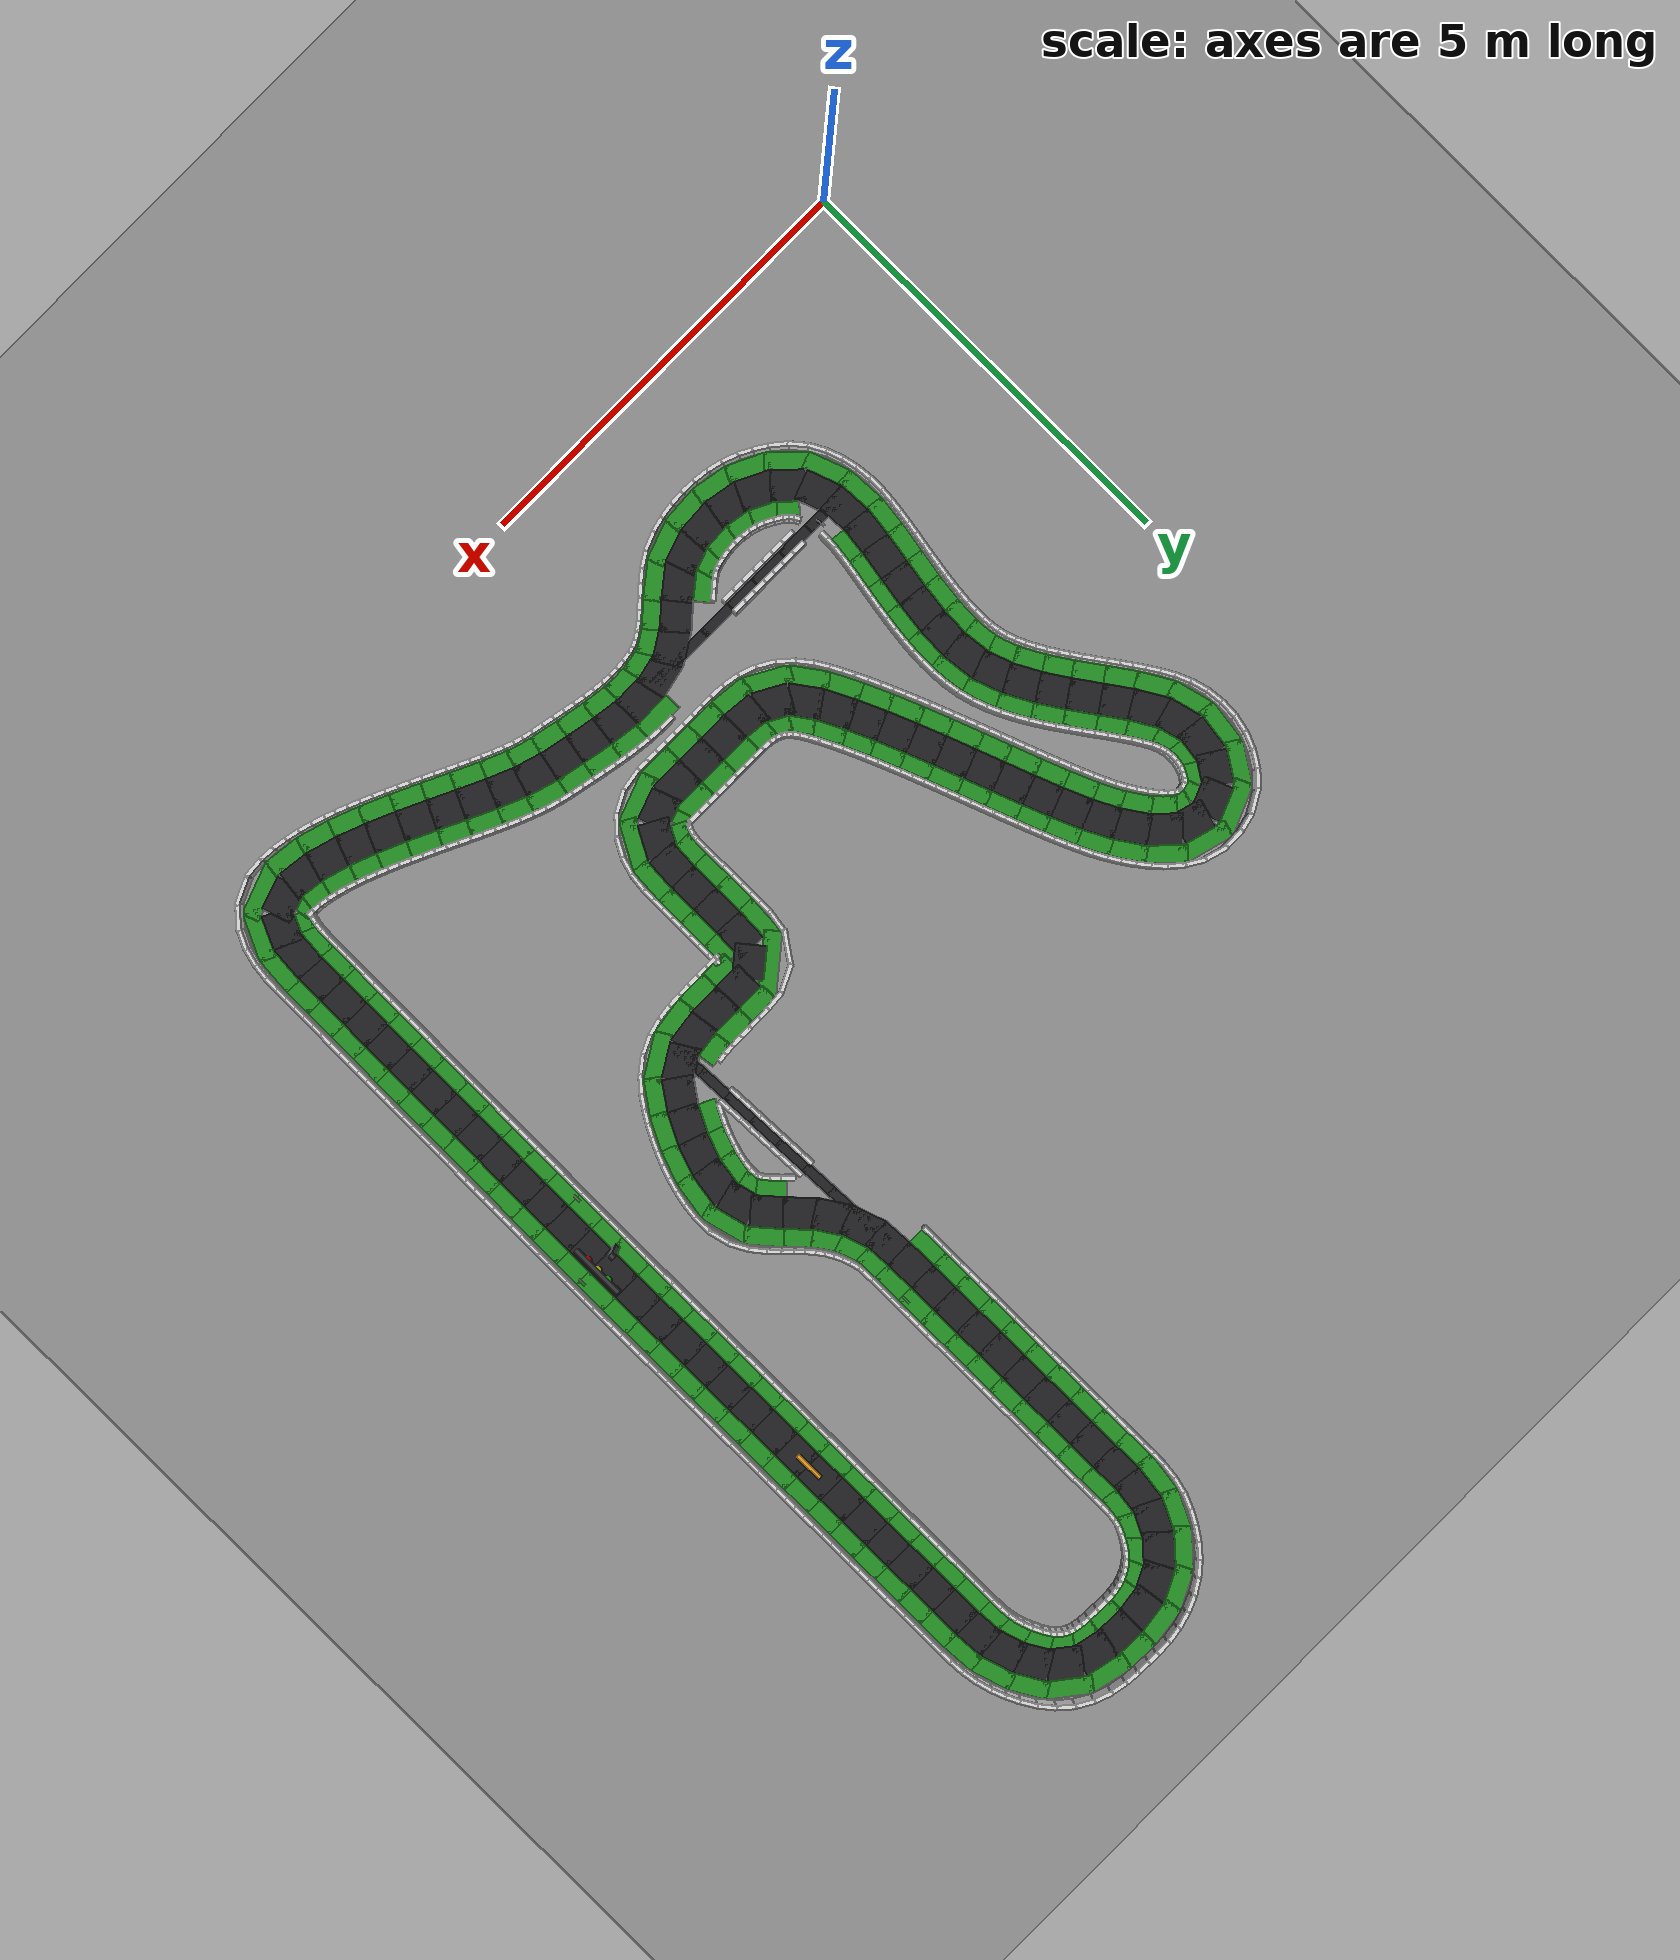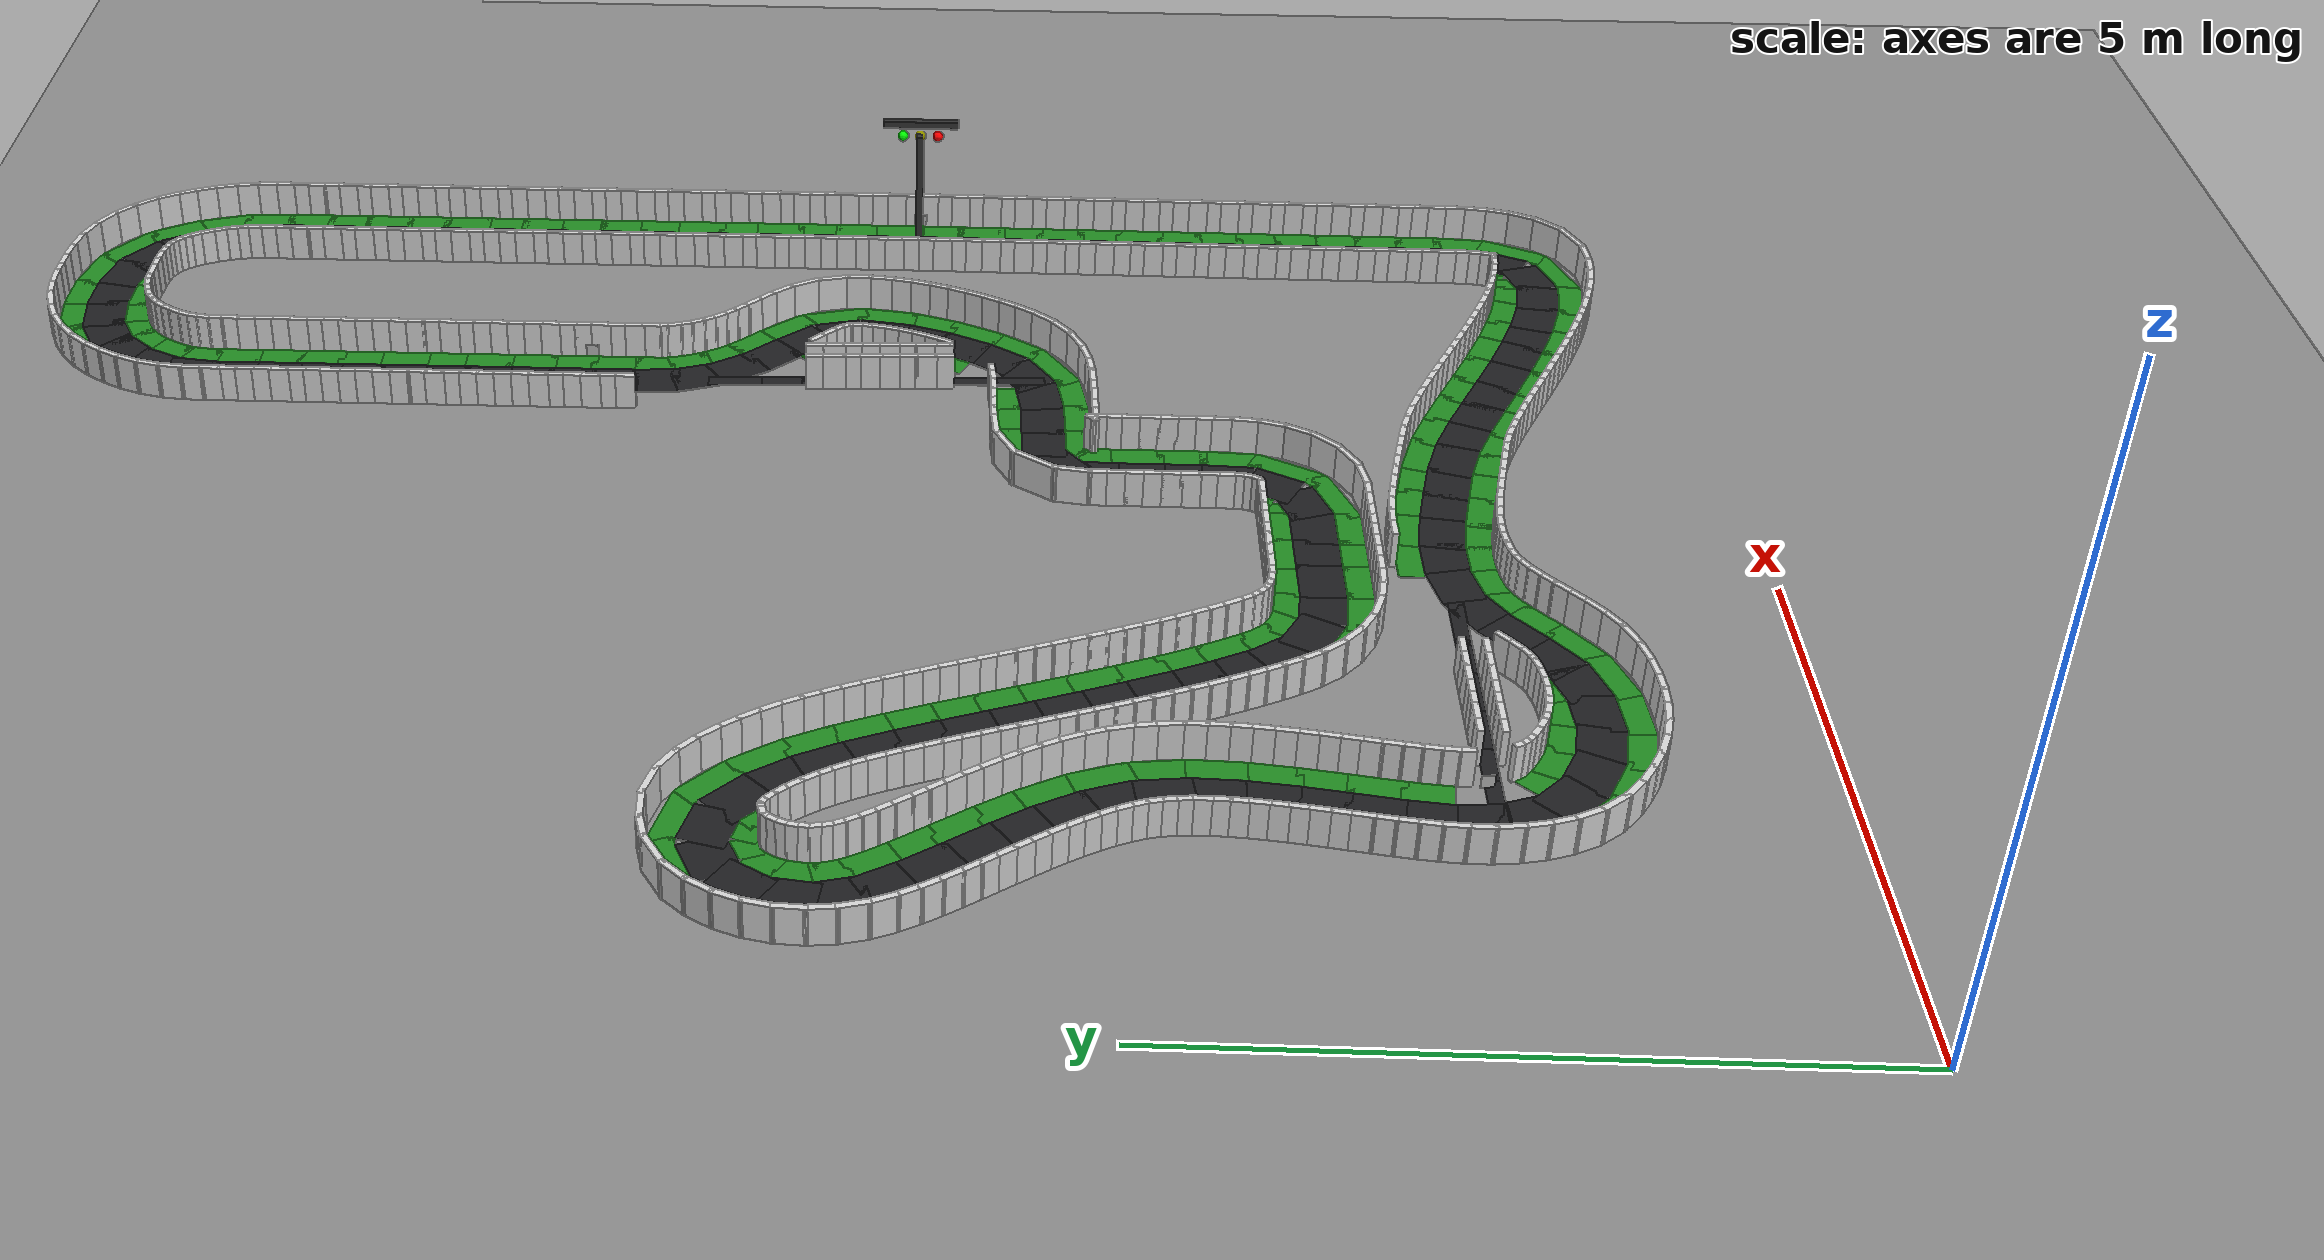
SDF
<?xml version='1.0' encoding='utf-8'?>
<sdf version="1.8">
  <world name="it_arena_track">
    <physics name="default_physics" type="ode">
      <max_step_size>0.001</max_step_size>
      <real_time_factor>1.0</real_time_factor>
    </physics>
    <plugin filename="gz-sim-physics-system" name="gz::sim::systems::Physics" />
    <plugin filename="gz-sim-user-commands-system" name="gz::sim::systems::UserCommands" />
    <plugin filename="gz-sim-scene-broadcaster-system" name="gz::sim::systems::SceneBroadcaster" />
    <plugin filename="gz-sim-sensors-system" name="gz::sim::systems::Sensors">
      <render_engine>ogre2</render_engine>
    </plugin>
    <plugin filename="gz-sim-imu-system" name="gz::sim::systems::Imu" />
    <light type="directional" name="sun">
      <cast_shadows>true</cast_shadows>
      <pose>0 0 10 0 0 0</pose>
      <diffuse>0.9 0.9 0.9 1</diffuse>
      <direction>-0.4 0.2 -0.9</direction>
    </light>
    <model name="it_arena_track_static">
      <static>true</static>
      <link name="track_geometry_merged">
        <collision name="ground_plane_link__ground_collision">
          <pose>0 0 0 0 0 0</pose>
          <geometry>
            <plane>
              <normal>0 0 1</normal>
              <size>30 30</size>
            </plane>
          </geometry>
        </collision>
        <visual name="ground_plane_link__ground_visual">
          <pose>0 0 0 0 0 0</pose>
          <geometry>
            <plane>
              <normal>0 0 1</normal>
              <size>30 30</size>
            </plane>
          </geometry>
          <material>
            <ambient>0.55 0.55 0.55 1</ambient>
            <diffuse>0.55 0.55 0.55 1</diffuse>
          </material>
        </visual>
        <collision name="surface_main_0__surface_main_0_col">
          <pose>9.9654 6.6465 0.0015 0 0 1.57391</pose>
          <geometry>
            <box>
              <size>0.4140 0.3500 0.0030</size>
            </box>
          </geometry>
        </collision>
        <visual name="surface_main_0__surface_main_0_vis">
          <pose>9.9654 6.6465 0.0015 0 0 1.57391</pose>
          <geometry>
            <box>
              <size>0.4140 0.3500 0.0030</size>
            </box>
          </geometry>
          <material>
            <ambient>0.12 0.12 0.13 1</ambient>
            <diffuse>0.12 0.12 0.13 1</diffuse>
          </material>
        </visual>
        <collision name="surface_main_1__surface_main_1_col">
          <pose>9.9643 7.0064 0.0015 0 0 1.57391</pose>
          <geometry>
            <box>
              <size>0.4140 0.3500 0.0030</size>
            </box>
          </geometry>
        </collision>
        <visual name="surface_main_1__surface_main_1_vis">
          <pose>9.9643 7.0064 0.0015 0 0 1.57391</pose>
          <geometry>
            <box>
              <size>0.4140 0.3500 0.0030</size>
            </box>
          </geometry>
          <material>
            <ambient>0.12 0.12 0.13 1</ambient>
            <diffuse>0.12 0.12 0.13 1</diffuse>
          </material>
        </visual>
        <collision name="surface_main_2__surface_main_2_col">
          <pose>9.9633 7.3564 0.0015 0 0 1.57374</pose>
          <geometry>
            <box>
              <size>0.3910 0.3500 0.0030</size>
            </box>
          </geometry>
        </collision>
        <visual name="surface_main_2__surface_main_2_vis">
          <pose>9.9633 7.3564 0.0015 0 0 1.57374</pose>
          <geometry>
            <box>
              <size>0.3910 0.3500 0.0030</size>
            </box>
          </geometry>
          <material>
            <ambient>0.12 0.12 0.13 1</ambient>
            <diffuse>0.12 0.12 0.13 1</diffuse>
          </material>
        </visual>
        <collision name="surface_main_3__surface_main_3_col">
          <pose>9.9622 7.7064 0.0015 0 0 1.57396</pose>
          <geometry>
            <box>
              <size>0.4140 0.3500 0.0030</size>
            </box>
          </geometry>
        </collision>
        <visual name="surface_main_3__surface_main_3_vis">
          <pose>9.9622 7.7064 0.0015 0 0 1.57396</pose>
          <geometry>
            <box>
              <size>0.4140 0.3500 0.0030</size>
            </box>
          </geometry>
          <material>
            <ambient>0.12 0.12 0.13 1</ambient>
            <diffuse>0.12 0.12 0.13 1</diffuse>
          </material>
        </visual>
        <collision name="surface_main_4__surface_main_4_col">
          <pose>9.9611 8.0563 0.0015 0 0 1.57386</pose>
          <geometry>
            <box>
              <size>0.3910 0.3500 0.0030</size>
            </box>
          </geometry>
        </collision>
        <visual name="surface_main_4__surface_main_4_vis">
          <pose>9.9611 8.0563 0.0015 0 0 1.57386</pose>
          <geometry>
            <box>
              <size>0.3910 0.3500 0.0030</size>
            </box>
          </geometry>
          <material>
            <ambient>0.12 0.12 0.13 1</ambient>
            <diffuse>0.12 0.12 0.13 1</diffuse>
          </material>
        </visual>
        <collision name="surface_main_5__surface_main_5_col">
          <pose>9.9600 8.4063 0.0015 0 0 1.57391</pose>
          <geometry>
            <box>
              <size>0.4140 0.3500 0.0030</size>
            </box>
          </geometry>
        </collision>
        <visual name="surface_main_5__surface_main_5_vis">
          <pose>9.9600 8.4063 0.0015 0 0 1.57391</pose>
          <geometry>
            <box>
              <size>0.4140 0.3500 0.0030</size>
            </box>
          </geometry>
          <material>
            <ambient>0.12 0.12 0.13 1</ambient>
            <diffuse>0.12 0.12 0.13 1</diffuse>
          </material>
        </visual>
        <collision name="surface_main_6__surface_main_6_col">
          <pose>9.9590 8.7562 0.0015 0 0 1.57374</pose>
          <geometry>
            <box>
              <size>0.3910 0.3500 0.0030</size>
            </box>
          </geometry>
        </collision>
        <visual name="surface_main_6__surface_main_6_vis">
          <pose>9.9590 8.7562 0.0015 0 0 1.57374</pose>
          <geometry>
            <box>
              <size>0.3910 0.3500 0.0030</size>
            </box>
          </geometry>
          <material>
            <ambient>0.12 0.12 0.13 1</ambient>
            <diffuse>0.12 0.12 0.13 1</diffuse>
          </material>
        </visual>
        <collision name="surface_main_7__surface_main_7_col">
          <pose>9.9579 9.1062 0.0015 0 0 1.57396</pose>
          <geometry>
            <box>
              <size>0.4140 0.3500 0.0030</size>
            </box>
          </geometry>
        </collision>
        <visual name="surface_main_7__surface_main_7_vis">
          <pose>9.9579 9.1062 0.0015 0 0 1.57396</pose>
          <geometry>
            <box>
              <size>0.4140 0.3500 0.0030</size>
            </box>
          </geometry>
          <material>
            <ambient>0.12 0.12 0.13 1</ambient>
            <diffuse>0.12 0.12 0.13 1</diffuse>
          </material>
        </visual>
        <collision name="surface_main_8__surface_main_8_col">
          <pose>9.9568 9.4562 0.0015 0 0 1.57391</pose>
          <geometry>
            <box>
              <size>0.3910 0.3500 0.0030</size>
            </box>
          </geometry>
        </collision>
        <visual name="surface_main_8__surface_main_8_vis">
          <pose>9.9568 9.4562 0.0015 0 0 1.57391</pose>
          <geometry>
            <box>
              <size>0.3910 0.3500 0.0030</size>
            </box>
          </geometry>
          <material>
            <ambient>0.12 0.12 0.13 1</ambient>
            <diffuse>0.12 0.12 0.13 1</diffuse>
          </material>
        </visual>
        <collision name="surface_main_9__surface_main_9_col">
          <pose>9.9557 9.8061 0.0015 0 0 1.57385</pose>
          <geometry>
            <box>
              <size>0.4140 0.3500 0.0030</size>
            </box>
          </geometry>
        </collision>
        <visual name="surface_main_9__surface_main_9_vis">
          <pose>9.9557 9.8061 0.0015 0 0 1.57385</pose>
          <geometry>
            <box>
              <size>0.4140 0.3500 0.0030</size>
            </box>
          </geometry>
          <material>
            <ambient>0.12 0.12 0.13 1</ambient>
            <diffuse>0.12 0.12 0.13 1</diffuse>
          </material>
        </visual>
        <collision name="surface_main_10__surface_main_10_col">
          <pose>9.9546 10.1561 0.0015 0 0 1.57397</pose>
          <geometry>
            <box>
              <size>0.3910 0.3500 0.0030</size>
            </box>
          </geometry>
        </collision>
        <visual name="surface_main_10__surface_main_10_vis">
          <pose>9.9546 10.1561 0.0015 0 0 1.57397</pose>
          <geometry>
            <box>
              <size>0.3910 0.3500 0.0030</size>
            </box>
          </geometry>
          <material>
            <ambient>0.12 0.12 0.13 1</ambient>
            <diffuse>0.12 0.12 0.13 1</diffuse>
          </material>
        </visual>
        <collision name="surface_main_11__surface_main_11_col">
          <pose>9.9536 10.5060 0.0015 0 0 1.57374</pose>
          <geometry>
            <box>
              <size>0.4140 0.3500 0.0030</size>
            </box>
          </geometry>
        </collision>
        <visual name="surface_main_11__surface_main_11_vis">
          <pose>9.9536 10.5060 0.0015 0 0 1.57374</pose>
          <geometry>
            <box>
              <size>0.4140 0.3500 0.0030</size>
            </box>
          </geometry>
          <material>
            <ambient>0.12 0.12 0.13 1</ambient>
            <diffuse>0.12 0.12 0.13 1</diffuse>
          </material>
        </visual>
        <collision name="surface_main_12__surface_main_12_col">
          <pose>9.9525 10.8560 0.0015 0 0 1.57391</pose>
          <geometry>
            <box>
              <size>0.3910 0.3500 0.0030</size>
            </box>
          </geometry>
        </collision>
        <visual name="surface_main_12__surface_main_12_vis">
          <pose>9.9525 10.8560 0.0015 0 0 1.57391</pose>
          <geometry>
            <box>
              <size>0.3910 0.3500 0.0030</size>
            </box>
          </geometry>
          <material>
            <ambient>0.12 0.12 0.13 1</ambient>
            <diffuse>0.12 0.12 0.13 1</diffuse>
          </material>
        </visual>
        <collision name="surface_main_13__surface_main_13_col">
          <pose>9.9514 11.2060 0.0015 0 0 1.57385</pose>
          <geometry>
            <box>
              <size>0.4140 0.3500 0.0030</size>
            </box>
          </geometry>
        </collision>
        <visual name="surface_main_13__surface_main_13_vis">
          <pose>9.9514 11.2060 0.0015 0 0 1.57385</pose>
          <geometry>
            <box>
              <size>0.4140 0.3500 0.0030</size>
            </box>
          </geometry>
          <material>
            <ambient>0.12 0.12 0.13 1</ambient>
            <diffuse>0.12 0.12 0.13 1</diffuse>
          </material>
        </visual>
        <collision name="surface_main_14__surface_main_14_col">
          <pose>9.9503 11.5559 0.0015 0 0 1.57397</pose>
          <geometry>
            <box>
              <size>0.3910 0.3500 0.0030</size>
            </box>
          </geometry>
        </collision>
        <visual name="surface_main_14__surface_main_14_vis">
          <pose>9.9503 11.5559 0.0015 0 0 1.57397</pose>
          <geometry>
            <box>
              <size>0.3910 0.3500 0.0030</size>
            </box>
          </geometry>
          <material>
            <ambient>0.12 0.12 0.13 1</ambient>
            <diffuse>0.12 0.12 0.13 1</diffuse>
          </material>
        </visual>
        <collision name="surface_main_15__surface_main_15_col">
          <pose>9.9498 11.9059 0.0015 0 0 1.57068</pose>
          <geometry>
            <box>
              <size>0.4140 0.3500 0.0030</size>
            </box>
          </geometry>
        </collision>
        <visual name="surface_main_15__surface_main_15_vis">
          <pose>9.9498 11.9059 0.0015 0 0 1.57068</pose>
          <geometry>
            <box>
              <size>0.4140 0.3500 0.0030</size>
            </box>
          </geometry>
          <material>
            <ambient>0.12 0.12 0.13 1</ambient>
            <diffuse>0.12 0.12 0.13 1</diffuse>
          </material>
        </visual>
        <collision name="surface_main_16__surface_main_16_col">
          <pose>9.9389 12.2553 0.0015 0 0 1.63489</pose>
          <geometry>
            <box>
              <size>0.3905 0.3500 0.0030</size>
            </box>
          </geometry>
        </collision>
        <visual name="surface_main_16__surface_main_16_vis">
          <pose>9.9389 12.2553 0.0015 0 0 1.63489</pose>
          <geometry>
            <box>
              <size>0.3905 0.3500 0.0030</size>
            </box>
          </geometry>
          <material>
            <ambient>0.12 0.12 0.13 1</ambient>
            <diffuse>0.12 0.12 0.13 1</diffuse>
          </material>
        </visual>
        <collision name="surface_main_17__surface_main_17_col">
          <pose>9.8749 12.5961 0.0015 0 0 1.87171</pose>
          <geometry>
            <box>
              <size>0.4127 0.3500 0.0030</size>
            </box>
          </geometry>
        </collision>
        <visual name="surface_main_17__surface_main_17_vis">
          <pose>9.8749 12.5961 0.0015 0 0 1.87171</pose>
          <geometry>
            <box>
              <size>0.4127 0.3500 0.0030</size>
            </box>
          </geometry>
          <material>
            <ambient>0.12 0.12 0.13 1</ambient>
            <diffuse>0.12 0.12 0.13 1</diffuse>
          </material>
        </visual>
        <collision name="surface_main_18__surface_main_18_col">
          <pose>9.7365 12.9139 0.0015 0 0 2.09781</pose>
          <geometry>
            <box>
              <size>0.3897 0.3500 0.0030</size>
            </box>
          </geometry>
        </collision>
        <visual name="surface_main_18__surface_main_18_vis">
          <pose>9.7365 12.9139 0.0015 0 0 2.09781</pose>
          <geometry>
            <box>
              <size>0.3897 0.3500 0.0030</size>
            </box>
          </geometry>
          <material>
            <ambient>0.12 0.12 0.13 1</ambient>
            <diffuse>0.12 0.12 0.13 1</diffuse>
          </material>
        </visual>
        <collision name="surface_main_19__surface_main_19_col">
          <pose>9.5103 13.1694 0.0015 0 0 2.48299</pose>
          <geometry>
            <box>
              <size>0.4099 0.3500 0.0030</size>
            </box>
          </geometry>
        </collision>
        <visual name="surface_main_19__surface_main_19_vis">
          <pose>9.5103 13.1694 0.0015 0 0 2.48299</pose>
          <geometry>
            <box>
              <size>0.4099 0.3500 0.0030</size>
            </box>
          </geometry>
          <material>
            <ambient>0.12 0.12 0.13 1</ambient>
            <diffuse>0.12 0.12 0.13 1</diffuse>
          </material>
        </visual>
        <collision name="surface_main_20__surface_main_20_col">
          <pose>9.1946 13.3170 0.0015 0 0 2.92453</pose>
          <geometry>
            <box>
              <size>0.4117 0.3500 0.0030</size>
            </box>
          </geometry>
        </collision>
        <visual name="surface_main_20__surface_main_20_vis">
          <pose>9.1946 13.3170 0.0015 0 0 2.92453</pose>
          <geometry>
            <box>
              <size>0.4117 0.3500 0.0030</size>
            </box>
          </geometry>
          <material>
            <ambient>0.12 0.12 0.13 1</ambient>
            <diffuse>0.12 0.12 0.13 1</diffuse>
          </material>
        </visual>
        <collision name="surface_main_21__surface_main_21_col">
          <pose>8.8499 13.3599 0.0015 0 0 3.11616</pose>
          <geometry>
            <box>
              <size>0.3909 0.3500 0.0030</size>
            </box>
          </geometry>
        </collision>
        <visual name="surface_main_21__surface_main_21_vis">
          <pose>8.8499 13.3599 0.0015 0 0 3.11616</pose>
          <geometry>
            <box>
              <size>0.3909 0.3500 0.0030</size>
            </box>
          </geometry>
          <material>
            <ambient>0.12 0.12 0.13 1</ambient>
            <diffuse>0.12 0.12 0.13 1</diffuse>
          </material>
        </visual>
        <collision name="surface_main_22__surface_main_22_col">
          <pose>8.5024 13.3397 0.0015 0 0 -3.00425</pose>
          <geometry>
            <box>
              <size>0.4123 0.3500 0.0030</size>
            </box>
          </geometry>
        </collision>
        <visual name="surface_main_22__surface_main_22_vis">
          <pose>8.5024 13.3397 0.0015 0 0 -3.00425</pose>
          <geometry>
            <box>
              <size>0.4123 0.3500 0.0030</size>
            </box>
          </geometry>
          <material>
            <ambient>0.12 0.12 0.13 1</ambient>
            <diffuse>0.12 0.12 0.13 1</diffuse>
          </material>
        </visual>
        <collision name="surface_main_23__surface_main_23_col">
          <pose>8.1741 13.2386 0.0015 0 0 -2.67193</pose>
          <geometry>
            <box>
              <size>0.3889 0.3500 0.0030</size>
            </box>
          </geometry>
        </collision>
        <visual name="surface_main_23__surface_main_23_vis">
          <pose>8.1741 13.2386 0.0015 0 0 -2.67193</pose>
          <geometry>
            <box>
              <size>0.3889 0.3500 0.0030</size>
            </box>
          </geometry>
          <material>
            <ambient>0.12 0.12 0.13 1</ambient>
            <diffuse>0.12 0.12 0.13 1</diffuse>
          </material>
        </visual>
        <collision name="surface_main_24__surface_main_24_col">
          <pose>7.9023 13.0302 0.0015 0 0 -2.31350</pose>
          <geometry>
            <box>
              <size>0.4117 0.3500 0.0030</size>
            </box>
          </geometry>
        </collision>
        <visual name="surface_main_24__surface_main_24_vis">
          <pose>7.9023 13.0302 0.0015 0 0 -2.31350</pose>
          <geometry>
            <box>
              <size>0.4117 0.3500 0.0030</size>
            </box>
          </geometry>
          <material>
            <ambient>0.12 0.12 0.13 1</ambient>
            <diffuse>0.12 0.12 0.13 1</diffuse>
          </material>
        </visual>
        <collision name="surface_main_25__surface_main_25_col">
          <pose>7.7069 12.7462 0.0015 0 0 -2.02534</pose>
          <geometry>
            <box>
              <size>0.3897 0.3500 0.0030</size>
            </box>
          </geometry>
        </collision>
        <visual name="surface_main_25__surface_main_25_vis">
          <pose>7.7069 12.7462 0.0015 0 0 -2.02534</pose>
          <geometry>
            <box>
              <size>0.3897 0.3500 0.0030</size>
            </box>
          </geometry>
          <material>
            <ambient>0.12 0.12 0.13 1</ambient>
            <diffuse>0.12 0.12 0.13 1</diffuse>
          </material>
        </visual>
        <collision name="surface_main_26__surface_main_26_col">
          <pose>7.6086 12.4162 0.0015 0 0 -1.70455</pose>
          <geometry>
            <box>
              <size>0.4124 0.3500 0.0030</size>
            </box>
          </geometry>
        </collision>
        <visual name="surface_main_26__surface_main_26_vis">
          <pose>7.6086 12.4162 0.0015 0 0 -1.70455</pose>
          <geometry>
            <box>
              <size>0.4124 0.3500 0.0030</size>
            </box>
          </geometry>
          <material>
            <ambient>0.12 0.12 0.13 1</ambient>
            <diffuse>0.12 0.12 0.13 1</diffuse>
          </material>
        </visual>
        <collision name="surface_main_27__surface_main_27_col">
          <pose>7.5864 12.0686 0.0015 0 0 -1.56032</pose>
          <geometry>
            <box>
              <size>0.3909 0.3500 0.0030</size>
            </box>
          </geometry>
        </collision>
        <visual name="surface_main_27__surface_main_27_vis">
          <pose>7.5864 12.0686 0.0015 0 0 -1.56032</pose>
          <geometry>
            <box>
              <size>0.3909 0.3500 0.0030</size>
            </box>
          </geometry>
          <material>
            <ambient>0.12 0.12 0.13 1</ambient>
            <diffuse>0.12 0.12 0.13 1</diffuse>
          </material>
        </visual>
        <collision name="surface_main_28__surface_main_28_col">
          <pose>7.5890 11.7186 0.0015 0 0 -1.56635</pose>
          <geometry>
            <box>
              <size>0.4140 0.3500 0.0030</size>
            </box>
          </geometry>
        </collision>
        <visual name="surface_main_28__surface_main_28_vis">
          <pose>7.5890 11.7186 0.0015 0 0 -1.56635</pose>
          <geometry>
            <box>
              <size>0.4140 0.3500 0.0030</size>
            </box>
          </geometry>
          <material>
            <ambient>0.12 0.12 0.13 1</ambient>
            <diffuse>0.12 0.12 0.13 1</diffuse>
          </material>
        </visual>
        <collision name="surface_main_29__surface_main_29_col">
          <pose>7.5905 11.3687 0.0015 0 0 -1.56650</pose>
          <geometry>
            <box>
              <size>0.3910 0.3500 0.0030</size>
            </box>
          </geometry>
        </collision>
        <visual name="surface_main_29__surface_main_29_vis">
          <pose>7.5905 11.3687 0.0015 0 0 -1.56650</pose>
          <geometry>
            <box>
              <size>0.3910 0.3500 0.0030</size>
            </box>
          </geometry>
          <material>
            <ambient>0.12 0.12 0.13 1</ambient>
            <diffuse>0.12 0.12 0.13 1</diffuse>
          </material>
        </visual>
        <collision name="surface_main_30__surface_main_30_col">
          <pose>7.5920 11.0187 0.0015 0 0 -1.56652</pose>
          <geometry>
            <box>
              <size>0.4140 0.3500 0.0030</size>
            </box>
          </geometry>
        </collision>
        <visual name="surface_main_30__surface_main_30_vis">
          <pose>7.5920 11.0187 0.0015 0 0 -1.56652</pose>
          <geometry>
            <box>
              <size>0.4140 0.3500 0.0030</size>
            </box>
          </geometry>
          <material>
            <ambient>0.12 0.12 0.13 1</ambient>
            <diffuse>0.12 0.12 0.13 1</diffuse>
          </material>
        </visual>
        <collision name="surface_main_31__surface_main_31_col">
          <pose>7.5935 10.6688 0.0015 0 0 -1.56650</pose>
          <geometry>
            <box>
              <size>0.3910 0.3500 0.0030</size>
            </box>
          </geometry>
        </collision>
        <visual name="surface_main_31__surface_main_31_vis">
          <pose>7.5935 10.6688 0.0015 0 0 -1.56650</pose>
          <geometry>
            <box>
              <size>0.3910 0.3500 0.0030</size>
            </box>
          </geometry>
          <material>
            <ambient>0.12 0.12 0.13 1</ambient>
            <diffuse>0.12 0.12 0.13 1</diffuse>
          </material>
        </visual>
        <collision name="surface_main_32__surface_main_32_col">
          <pose>7.5950 10.3188 0.0015 0 0 -1.56652</pose>
          <geometry>
            <box>
              <size>0.4140 0.3500 0.0030</size>
            </box>
          </geometry>
        </collision>
        <visual name="surface_main_32__surface_main_32_vis">
          <pose>7.5950 10.3188 0.0015 0 0 -1.56652</pose>
          <geometry>
            <box>
              <size>0.4140 0.3500 0.0030</size>
            </box>
          </geometry>
          <material>
            <ambient>0.12 0.12 0.13 1</ambient>
            <diffuse>0.12 0.12 0.13 1</diffuse>
          </material>
        </visual>
        <collision name="surface_main_33__surface_main_33_col">
          <pose>7.5965 9.9688 0.0015 0 0 -1.56650</pose>
          <geometry>
            <box>
              <size>0.3910 0.3500 0.0030</size>
            </box>
          </geometry>
        </collision>
        <visual name="surface_main_33__surface_main_33_vis">
          <pose>7.5965 9.9688 0.0015 0 0 -1.56650</pose>
          <geometry>
            <box>
              <size>0.3910 0.3500 0.0030</size>
            </box>
          </geometry>
          <material>
            <ambient>0.12 0.12 0.13 1</ambient>
            <diffuse>0.12 0.12 0.13 1</diffuse>
          </material>
        </visual>
        <collision name="surface_main_34__surface_main_34_col">
          <pose>7.5981 9.6189 0.0015 0 0 -1.56636</pose>
          <geometry>
            <box>
              <size>0.4140 0.3500 0.0030</size>
            </box>
          </geometry>
        </collision>
        <visual name="surface_main_34__surface_main_34_vis">
          <pose>7.5981 9.6189 0.0015 0 0 -1.56636</pose>
          <geometry>
            <box>
              <size>0.4140 0.3500 0.0030</size>
            </box>
          </geometry>
          <material>
            <ambient>0.12 0.12 0.13 1</ambient>
            <diffuse>0.12 0.12 0.13 1</diffuse>
          </material>
        </visual>
        <collision name="surface_main_35__surface_main_35_col">
          <pose>7.5996 9.2689 0.0015 0 0 -1.56638</pose>
          <geometry>
            <box>
              <size>0.3910 0.3500 0.0030</size>
            </box>
          </geometry>
        </collision>
        <visual name="surface_main_35__surface_main_35_vis">
          <pose>7.5996 9.2689 0.0015 0 0 -1.56638</pose>
          <geometry>
            <box>
              <size>0.3910 0.3500 0.0030</size>
            </box>
          </geometry>
          <material>
            <ambient>0.12 0.12 0.13 1</ambient>
            <diffuse>0.12 0.12 0.13 1</diffuse>
          </material>
        </visual>
        <collision name="surface_main_36__surface_main_36_col">
          <pose>7.6011 8.9190 0.0015 0 0 -1.56652</pose>
          <geometry>
            <box>
              <size>0.4140 0.3500 0.0030</size>
            </box>
          </geometry>
        </collision>
        <visual name="surface_main_36__surface_main_36_vis">
          <pose>7.6011 8.9190 0.0015 0 0 -1.56652</pose>
          <geometry>
            <box>
              <size>0.4140 0.3500 0.0030</size>
            </box>
          </geometry>
          <material>
            <ambient>0.12 0.12 0.13 1</ambient>
            <diffuse>0.12 0.12 0.13 1</diffuse>
          </material>
        </visual>
        <collision name="surface_main_37__surface_main_37_col">
          <pose>7.6108 8.5697 0.0015 0 0 -1.51822</pose>
          <geometry>
            <box>
              <size>0.3898 0.3500 0.0030</size>
            </box>
          </geometry>
        </collision>
        <visual name="surface_main_37__surface_main_37_vis">
          <pose>7.6108 8.5697 0.0015 0 0 -1.51822</pose>
          <geometry>
            <box>
              <size>0.3898 0.3500 0.0030</size>
            </box>
          </geometry>
          <material>
            <ambient>0.12 0.12 0.13 1</ambient>
            <diffuse>0.12 0.12 0.13 1</diffuse>
          </material>
        </visual>
        <collision name="surface_main_38__surface_main_38_col">
          <pose>7.6775 8.2305 0.0015 0 0 -1.24318</pose>
          <geometry>
            <box>
              <size>0.4128 0.3500 0.0030</size>
            </box>
          </geometry>
        </collision>
        <visual name="surface_main_38__surface_main_38_vis">
          <pose>7.6775 8.2305 0.0015 0 0 -1.24318</pose>
          <geometry>
            <box>
              <size>0.4128 0.3500 0.0030</size>
            </box>
          </geometry>
          <material>
            <ambient>0.12 0.12 0.13 1</ambient>
            <diffuse>0.12 0.12 0.13 1</diffuse>
          </material>
        </visual>
        <collision name="surface_main_39__surface_main_39_col">
          <pose>7.8331 7.9101 0.0015 0 0 -0.99422</pose>
          <geometry>
            <box>
              <size>0.4129 0.3500 0.0030</size>
            </box>
          </geometry>
        </collision>
        <visual name="surface_main_39__surface_main_39_vis">
          <pose>7.8331 7.9101 0.0015 0 0 -0.99422</pose>
          <geometry>
            <box>
              <size>0.4129 0.3500 0.0030</size>
            </box>
          </geometry>
          <material>
            <ambient>0.12 0.12 0.13 1</ambient>
            <diffuse>0.12 0.12 0.13 1</diffuse>
          </material>
        </visual>
        <collision name="surface_main_40__surface_main_40_col">
          <pose>8.0481 7.6364 0.0015 0 0 -0.81055</pose>
          <geometry>
            <box>
              <size>0.3908 0.3500 0.0030</size>
            </box>
          </geometry>
        </collision>
        <visual name="surface_main_40__surface_main_40_vis">
          <pose>8.0481 7.6364 0.0015 0 0 -0.81055</pose>
          <geometry>
            <box>
              <size>0.3908 0.3500 0.0030</size>
            </box>
          </geometry>
          <material>
            <ambient>0.12 0.12 0.13 1</ambient>
            <diffuse>0.12 0.12 0.13 1</diffuse>
          </material>
        </visual>
        <collision name="surface_main_41__surface_main_41_col">
          <pose>8.2829 7.3778 0.0015 0 0 -0.85532</pose>
          <geometry>
            <box>
              <size>0.4128 0.3500 0.0030</size>
            </box>
          </geometry>
        </collision>
        <visual name="surface_main_41__surface_main_41_vis">
          <pose>8.2829 7.3778 0.0015 0 0 -0.85532</pose>
          <geometry>
            <box>
              <size>0.4128 0.3500 0.0030</size>
            </box>
          </geometry>
          <material>
            <ambient>0.12 0.12 0.13 1</ambient>
            <diffuse>0.12 0.12 0.13 1</diffuse>
          </material>
        </visual>
        <collision name="surface_main_42__surface_main_42_col">
          <pose>8.4418 7.0802 0.0015 0 0 -1.32233</pose>
          <geometry>
            <box>
              <size>0.3847 0.3500 0.0030</size>
            </box>
          </geometry>
        </collision>
        <visual name="surface_main_42__surface_main_42_vis">
          <pose>8.4418 7.0802 0.0015 0 0 -1.32233</pose>
          <geometry>
            <box>
              <size>0.3847 0.3500 0.0030</size>
            </box>
          </geometry>
          <material>
            <ambient>0.12 0.12 0.13 1</ambient>
            <diffuse>0.12 0.12 0.13 1</diffuse>
          </material>
        </visual>
        <collision name="surface_main_43__surface_main_43_col">
          <pose>8.4551 6.7408 0.0015 0 0 -1.72632</pose>
          <geometry>
            <box>
              <size>0.4129 0.3500 0.0030</size>
            </box>
          </geometry>
        </collision>
        <visual name="surface_main_43__surface_main_43_vis">
          <pose>8.4551 6.7408 0.0015 0 0 -1.72632</pose>
          <geometry>
            <box>
              <size>0.4129 0.3500 0.0030</size>
            </box>
          </geometry>
          <material>
            <ambient>0.12 0.12 0.13 1</ambient>
            <diffuse>0.12 0.12 0.13 1</diffuse>
          </material>
        </visual>
        <collision name="surface_main_44__surface_main_44_col">
          <pose>8.3713 6.4030 0.0015 0 0 -1.90638</pose>
          <geometry>
            <box>
              <size>0.3906 0.3500 0.0030</size>
            </box>
          </geometry>
        </collision>
        <visual name="surface_main_44__surface_main_44_vis">
          <pose>8.3713 6.4030 0.0015 0 0 -1.90638</pose>
          <geometry>
            <box>
              <size>0.3906 0.3500 0.0030</size>
            </box>
          </geometry>
          <material>
            <ambient>0.12 0.12 0.13 1</ambient>
            <diffuse>0.12 0.12 0.13 1</diffuse>
          </material>
        </visual>
        <collision name="surface_main_45__surface_main_45_col">
          <pose>8.2349 6.0818 0.0015 0 0 -2.03484</pose>
          <geometry>
            <box>
              <size>0.4137 0.3500 0.0030</size>
            </box>
          </geometry>
        </collision>
        <visual name="surface_main_45__surface_main_45_vis">
          <pose>8.2349 6.0818 0.0015 0 0 -2.03484</pose>
          <geometry>
            <box>
              <size>0.4137 0.3500 0.0030</size>
            </box>
          </geometry>
          <material>
            <ambient>0.12 0.12 0.13 1</ambient>
            <diffuse>0.12 0.12 0.13 1</diffuse>
          </material>
        </visual>
        <collision name="surface_main_46__surface_main_46_col">
          <pose>8.0572 5.7820 0.0015 0 0 -2.18125</pose>
          <geometry>
            <box>
              <size>0.3902 0.3500 0.0030</size>
            </box>
          </geometry>
        </collision>
        <visual name="surface_main_46__surface_main_46_vis">
          <pose>8.0572 5.7820 0.0015 0 0 -2.18125</pose>
          <geometry>
            <box>
              <size>0.3902 0.3500 0.0030</size>
            </box>
          </geometry>
          <material>
            <ambient>0.12 0.12 0.13 1</ambient>
            <diffuse>0.12 0.12 0.13 1</diffuse>
          </material>
        </visual>
        <collision name="surface_main_47__surface_main_47_col">
          <pose>7.8082 5.5504 0.0015 0 0 -2.59347</pose>
          <geometry>
            <box>
              <size>0.4088 0.3500 0.0030</size>
            </box>
          </geometry>
        </collision>
        <visual name="surface_main_47__surface_main_47_vis">
          <pose>7.8082 5.5504 0.0015 0 0 -2.59347</pose>
          <geometry>
            <box>
              <size>0.4088 0.3500 0.0030</size>
            </box>
          </geometry>
          <material>
            <ambient>0.12 0.12 0.13 1</ambient>
            <diffuse>0.12 0.12 0.13 1</diffuse>
          </material>
        </visual>
        <collision name="surface_main_48__surface_main_48_col">
          <pose>7.4886 5.4344 0.0015 0 0 -3.00326</pose>
          <geometry>
            <box>
              <size>0.3899 0.3500 0.0030</size>
            </box>
          </geometry>
        </collision>
        <visual name="surface_main_48__surface_main_48_vis">
          <pose>7.4886 5.4344 0.0015 0 0 -3.00326</pose>
          <geometry>
            <box>
              <size>0.3899 0.3500 0.0030</size>
            </box>
          </geometry>
          <material>
            <ambient>0.12 0.12 0.13 1</ambient>
            <diffuse>0.12 0.12 0.13 1</diffuse>
          </material>
        </visual>
        <collision name="surface_main_49__surface_main_49_col">
          <pose>7.1408 5.4082 0.0015 0 0 -3.12609</pose>
          <geometry>
            <box>
              <size>0.4139 0.3500 0.0030</size>
            </box>
          </geometry>
        </collision>
        <visual name="surface_main_49__surface_main_49_vis">
          <pose>7.1408 5.4082 0.0015 0 0 -3.12609</pose>
          <geometry>
            <box>
              <size>0.4139 0.3500 0.0030</size>
            </box>
          </geometry>
          <material>
            <ambient>0.12 0.12 0.13 1</ambient>
            <diffuse>0.12 0.12 0.13 1</diffuse>
          </material>
        </visual>
        <collision name="surface_main_50__surface_main_50_col">
          <pose>6.7909 5.4021 0.0015 0 0 -3.12223</pose>
          <geometry>
            <box>
              <size>0.3909 0.3500 0.0030</size>
            </box>
          </geometry>
        </collision>
        <visual name="surface_main_50__surface_main_50_vis">
          <pose>6.7909 5.4021 0.0015 0 0 -3.12223</pose>
          <geometry>
            <box>
              <size>0.3909 0.3500 0.0030</size>
            </box>
          </geometry>
          <material>
            <ambient>0.12 0.12 0.13 1</ambient>
            <diffuse>0.12 0.12 0.13 1</diffuse>
          </material>
        </visual>
        <collision name="surface_main_51__surface_main_51_col">
          <pose>6.4899 5.2921 0.0015 0 0 -2.45833</pose>
          <geometry>
            <box>
              <size>0.3889 0.3500 0.0030</size>
            </box>
          </geometry>
        </collision>
        <visual name="surface_main_51__surface_main_51_vis">
          <pose>6.4899 5.2921 0.0015 0 0 -2.45833</pose>
          <geometry>
            <box>
              <size>0.3889 0.3500 0.0030</size>
            </box>
          </geometry>
          <material>
            <ambient>0.12 0.12 0.13 1</ambient>
            <diffuse>0.12 0.12 0.13 1</diffuse>
          </material>
        </visual>
        <collision name="surface_main_52__surface_main_52_col">
          <pose>6.3519 5.0160 0.0015 0 0 -1.61126</pose>
          <geometry>
            <box>
              <size>0.3898 0.3500 0.0030</size>
            </box>
          </geometry>
        </collision>
        <visual name="surface_main_52__surface_main_52_vis">
          <pose>6.3519 5.0160 0.0015 0 0 -1.61126</pose>
          <geometry>
            <box>
              <size>0.3898 0.3500 0.0030</size>
            </box>
          </geometry>
          <material>
            <ambient>0.12 0.12 0.13 1</ambient>
            <diffuse>0.12 0.12 0.13 1</diffuse>
          </material>
        </visual>
        <collision name="surface_main_53__surface_main_53_col">
          <pose>6.3450 4.6667 0.0015 0 0 -1.57080</pose>
          <geometry>
            <box>
              <size>0.4140 0.3500 0.0030</size>
            </box>
          </geometry>
        </collision>
        <visual name="surface_main_53__surface_main_53_vis">
          <pose>6.3450 4.6667 0.0015 0 0 -1.57080</pose>
          <geometry>
            <box>
              <size>0.4140 0.3500 0.0030</size>
            </box>
          </geometry>
          <material>
            <ambient>0.12 0.12 0.13 1</ambient>
            <diffuse>0.12 0.12 0.13 1</diffuse>
          </material>
        </visual>
        <collision name="surface_main_54__surface_main_54_col">
          <pose>6.3450 4.3167 0.0015 0 0 -1.57080</pose>
          <geometry>
            <box>
              <size>0.3910 0.3500 0.0030</size>
            </box>
          </geometry>
        </collision>
        <visual name="surface_main_54__surface_main_54_vis">
          <pose>6.3450 4.3167 0.0015 0 0 -1.57080</pose>
          <geometry>
            <box>
              <size>0.3910 0.3500 0.0030</size>
            </box>
          </geometry>
          <material>
            <ambient>0.12 0.12 0.13 1</ambient>
            <diffuse>0.12 0.12 0.13 1</diffuse>
          </material>
        </visual>
        <collision name="surface_main_55__surface_main_55_col">
          <pose>6.3351 3.9675 0.0015 0 0 -1.62589</pose>
          <geometry>
            <box>
              <size>0.4129 0.3500 0.0030</size>
            </box>
          </geometry>
        </collision>
        <visual name="surface_main_55__surface_main_55_vis">
          <pose>6.3351 3.9675 0.0015 0 0 -1.62589</pose>
          <geometry>
            <box>
              <size>0.4129 0.3500 0.0030</size>
            </box>
          </geometry>
          <material>
            <ambient>0.12 0.12 0.13 1</ambient>
            <diffuse>0.12 0.12 0.13 1</diffuse>
          </material>
        </visual>
        <collision name="surface_main_56__surface_main_56_col">
          <pose>6.2413 3.6320 0.0015 0 0 -2.06382</pose>
          <geometry>
            <box>
              <size>0.4079 0.3500 0.0030</size>
            </box>
          </geometry>
        </collision>
        <visual name="surface_main_56__surface_main_56_vis">
          <pose>6.2413 3.6320 0.0015 0 0 -2.06382</pose>
          <geometry>
            <box>
              <size>0.4079 0.3500 0.0030</size>
            </box>
          </geometry>
          <material>
            <ambient>0.12 0.12 0.13 1</ambient>
            <diffuse>0.12 0.12 0.13 1</diffuse>
          </material>
        </visual>
        <collision name="surface_main_57__surface_main_57_col">
          <pose>6.0016 3.4197 0.0015 0 0 -2.79601</pose>
          <geometry>
            <box>
              <size>0.3808 0.3500 0.0030</size>
            </box>
          </geometry>
        </collision>
        <visual name="surface_main_57__surface_main_57_vis">
          <pose>6.0016 3.4197 0.0015 0 0 -2.79601</pose>
          <geometry>
            <box>
              <size>0.3808 0.3500 0.0030</size>
            </box>
          </geometry>
          <material>
            <ambient>0.12 0.12 0.13 1</ambient>
            <diffuse>0.12 0.12 0.13 1</diffuse>
          </material>
        </visual>
        <collision name="surface_main_58__surface_main_58_col">
          <pose>5.6658 3.3636 0.0015 0 0 -3.14130</pose>
          <geometry>
            <box>
              <size>0.4140 0.3500 0.0030</size>
            </box>
          </geometry>
        </collision>
        <visual name="surface_main_58__surface_main_58_vis">
          <pose>5.6658 3.3636 0.0015 0 0 -3.14130</pose>
          <geometry>
            <box>
              <size>0.4140 0.3500 0.0030</size>
            </box>
          </geometry>
          <material>
            <ambient>0.12 0.12 0.13 1</ambient>
            <diffuse>0.12 0.12 0.13 1</diffuse>
          </material>
        </visual>
        <collision name="surface_main_59__surface_main_59_col">
          <pose>5.3159 3.3635 0.0015 0 0 3.14159</pose>
          <geometry>
            <box>
              <size>0.3910 0.3500 0.0030</size>
            </box>
          </geometry>
        </collision>
        <visual name="surface_main_59__surface_main_59_vis">
          <pose>5.3159 3.3635 0.0015 0 0 3.14159</pose>
          <geometry>
            <box>
              <size>0.3910 0.3500 0.0030</size>
            </box>
          </geometry>
          <material>
            <ambient>0.12 0.12 0.13 1</ambient>
            <diffuse>0.12 0.12 0.13 1</diffuse>
          </material>
        </visual>
        <collision name="surface_main_60__surface_main_60_col">
          <pose>4.9659 3.3635 0.0015 0 0 3.14159</pose>
          <geometry>
            <box>
              <size>0.4140 0.3500 0.0030</size>
            </box>
          </geometry>
        </collision>
        <visual name="surface_main_60__surface_main_60_vis">
          <pose>4.9659 3.3635 0.0015 0 0 3.14159</pose>
          <geometry>
            <box>
              <size>0.4140 0.3500 0.0030</size>
            </box>
          </geometry>
          <material>
            <ambient>0.12 0.12 0.13 1</ambient>
            <diffuse>0.12 0.12 0.13 1</diffuse>
          </material>
        </visual>
        <collision name="surface_main_61__surface_main_61_col">
          <pose>4.6173 3.3794 0.0015 0 0 3.04737</pose>
          <geometry>
            <box>
              <size>0.3897 0.3500 0.0030</size>
            </box>
          </geometry>
        </collision>
        <visual name="surface_main_61__surface_main_61_vis">
          <pose>4.6173 3.3794 0.0015 0 0 3.04737</pose>
          <geometry>
            <box>
              <size>0.3897 0.3500 0.0030</size>
            </box>
          </geometry>
          <material>
            <ambient>0.12 0.12 0.13 1</ambient>
            <diffuse>0.12 0.12 0.13 1</diffuse>
          </material>
        </visual>
        <collision name="surface_main_62__surface_main_62_col">
          <pose>4.2929 3.4817 0.0015 0 0 2.63517</pose>
          <geometry>
            <box>
              <size>0.4094 0.3500 0.0030</size>
            </box>
          </geometry>
        </collision>
        <visual name="surface_main_62__surface_main_62_vis">
          <pose>4.2929 3.4817 0.0015 0 0 2.63517</pose>
          <geometry>
            <box>
              <size>0.4094 0.3500 0.0030</size>
            </box>
          </geometry>
          <material>
            <ambient>0.12 0.12 0.13 1</ambient>
            <diffuse>0.12 0.12 0.13 1</diffuse>
          </material>
        </visual>
        <collision name="surface_main_63__surface_main_63_col">
          <pose>4.0390 3.7058 0.0015 0 0 2.19072</pose>
          <geometry>
            <box>
              <size>0.3893 0.3500 0.0030</size>
            </box>
          </geometry>
        </collision>
        <visual name="surface_main_63__surface_main_63_vis">
          <pose>4.0390 3.7058 0.0015 0 0 2.19072</pose>
          <geometry>
            <box>
              <size>0.3893 0.3500 0.0030</size>
            </box>
          </geometry>
          <material>
            <ambient>0.12 0.12 0.13 1</ambient>
            <diffuse>0.12 0.12 0.13 1</diffuse>
          </material>
        </visual>
        <collision name="surface_main_64__surface_main_64_col">
          <pose>3.8593 4.0041 0.0015 0 0 2.03985</pose>
          <geometry>
            <box>
              <size>0.4139 0.3500 0.0030</size>
            </box>
          </geometry>
        </collision>
        <visual name="surface_main_64__surface_main_64_vis">
          <pose>3.8593 4.0041 0.0015 0 0 2.03985</pose>
          <geometry>
            <box>
              <size>0.4139 0.3500 0.0030</size>
            </box>
          </geometry>
          <material>
            <ambient>0.12 0.12 0.13 1</ambient>
            <diffuse>0.12 0.12 0.13 1</diffuse>
          </material>
        </visual>
        <collision name="surface_main_65__surface_main_65_col">
          <pose>3.7082 4.3196 0.0015 0 0 1.99366</pose>
          <geometry>
            <box>
              <size>0.3909 0.3500 0.0030</size>
            </box>
          </geometry>
        </collision>
        <visual name="surface_main_65__surface_main_65_vis">
          <pose>3.7082 4.3196 0.0015 0 0 1.99366</pose>
          <geometry>
            <box>
              <size>0.3909 0.3500 0.0030</size>
            </box>
          </geometry>
          <material>
            <ambient>0.12 0.12 0.13 1</ambient>
            <diffuse>0.12 0.12 0.13 1</diffuse>
          </material>
        </visual>
        <collision name="surface_main_66__surface_main_66_col">
          <pose>3.5693 4.6408 0.0015 0 0 1.96489</pose>
          <geometry>
            <box>
              <size>0.4139 0.3500 0.0030</size>
            </box>
          </geometry>
        </collision>
        <visual name="surface_main_66__surface_main_66_vis">
          <pose>3.5693 4.6408 0.0015 0 0 1.96489</pose>
          <geometry>
            <box>
              <size>0.4139 0.3500 0.0030</size>
            </box>
          </geometry>
          <material>
            <ambient>0.12 0.12 0.13 1</ambient>
            <diffuse>0.12 0.12 0.13 1</diffuse>
          </material>
        </visual>
        <collision name="surface_main_67__surface_main_67_col">
          <pose>3.4380 4.9651 0.0015 0 0 1.94567</pose>
          <geometry>
            <box>
              <size>0.3910 0.3500 0.0030</size>
            </box>
          </geometry>
        </collision>
        <visual name="surface_main_67__surface_main_67_vis">
          <pose>3.4380 4.9651 0.0015 0 0 1.94567</pose>
          <geometry>
            <box>
              <size>0.3910 0.3500 0.0030</size>
            </box>
          </geometry>
          <material>
            <ambient>0.12 0.12 0.13 1</ambient>
            <diffuse>0.12 0.12 0.13 1</diffuse>
          </material>
        </visual>
        <collision name="surface_main_68__surface_main_68_col">
          <pose>3.3115 5.2914 0.0015 0 0 1.93557</pose>
          <geometry>
            <box>
              <size>0.4140 0.3500 0.0030</size>
            </box>
          </geometry>
        </collision>
        <visual name="surface_main_68__surface_main_68_vis">
          <pose>3.3115 5.2914 0.0015 0 0 1.93557</pose>
          <geometry>
            <box>
              <size>0.4140 0.3500 0.0030</size>
            </box>
          </geometry>
          <material>
            <ambient>0.12 0.12 0.13 1</ambient>
            <diffuse>0.12 0.12 0.13 1</diffuse>
          </material>
        </visual>
        <collision name="surface_main_69__surface_main_69_col">
          <pose>3.1874 5.6186 0.0015 0 0 1.93135</pose>
          <geometry>
            <box>
              <size>0.3910 0.3500 0.0030</size>
            </box>
          </geometry>
        </collision>
        <visual name="surface_main_69__surface_main_69_vis">
          <pose>3.1874 5.6186 0.0015 0 0 1.93135</pose>
          <geometry>
            <box>
              <size>0.3910 0.3500 0.0030</size>
            </box>
          </geometry>
          <material>
            <ambient>0.12 0.12 0.13 1</ambient>
            <diffuse>0.12 0.12 0.13 1</diffuse>
          </material>
        </visual>
        <collision name="surface_main_70__surface_main_70_col">
          <pose>3.0635 5.9459 0.0015 0 0 1.93382</pose>
          <geometry>
            <box>
              <size>0.4140 0.3500 0.0030</size>
            </box>
          </geometry>
        </collision>
        <visual name="surface_main_70__surface_main_70_vis">
          <pose>3.0635 5.9459 0.0015 0 0 1.93382</pose>
          <geometry>
            <box>
              <size>0.4140 0.3500 0.0030</size>
            </box>
          </geometry>
          <material>
            <ambient>0.12 0.12 0.13 1</ambient>
            <diffuse>0.12 0.12 0.13 1</diffuse>
          </material>
        </visual>
        <collision name="surface_main_71__surface_main_71_col">
          <pose>2.9375 6.2724 0.0015 0 0 1.94493</pose>
          <geometry>
            <box>
              <size>0.3910 0.3500 0.0030</size>
            </box>
          </geometry>
        </collision>
        <visual name="surface_main_71__surface_main_71_vis">
          <pose>2.9375 6.2724 0.0015 0 0 1.94493</pose>
          <geometry>
            <box>
              <size>0.3910 0.3500 0.0030</size>
            </box>
          </geometry>
          <material>
            <ambient>0.12 0.12 0.13 1</ambient>
            <diffuse>0.12 0.12 0.13 1</diffuse>
          </material>
        </visual>
        <collision name="surface_main_72__surface_main_72_col">
          <pose>2.8050 6.5963 0.0015 0 0 1.97211</pose>
          <geometry>
            <box>
              <size>0.4139 0.3500 0.0030</size>
            </box>
          </geometry>
        </collision>
        <visual name="surface_main_72__surface_main_72_vis">
          <pose>2.8050 6.5963 0.0015 0 0 1.97211</pose>
          <geometry>
            <box>
              <size>0.4139 0.3500 0.0030</size>
            </box>
          </geometry>
          <material>
            <ambient>0.12 0.12 0.13 1</ambient>
            <diffuse>0.12 0.12 0.13 1</diffuse>
          </material>
        </visual>
        <collision name="surface_main_73__surface_main_73_col">
          <pose>2.6581 6.9136 0.0015 0 0 2.03842</pose>
          <geometry>
            <box>
              <size>0.3908 0.3500 0.0030</size>
            </box>
          </geometry>
        </collision>
        <visual name="surface_main_73__surface_main_73_vis">
          <pose>2.6581 6.9136 0.0015 0 0 2.03842</pose>
          <geometry>
            <box>
              <size>0.3908 0.3500 0.0030</size>
            </box>
          </geometry>
          <material>
            <ambient>0.12 0.12 0.13 1</ambient>
            <diffuse>0.12 0.12 0.13 1</diffuse>
          </material>
        </visual>
        <collision name="surface_main_74__surface_main_74_col">
          <pose>2.4810 7.2144 0.0015 0 0 2.16415</pose>
          <geometry>
            <box>
              <size>0.4137 0.3500 0.0030</size>
            </box>
          </geometry>
        </collision>
        <visual name="surface_main_74__surface_main_74_vis">
          <pose>2.4810 7.2144 0.0015 0 0 2.16415</pose>
          <geometry>
            <box>
              <size>0.4137 0.3500 0.0030</size>
            </box>
          </geometry>
          <material>
            <ambient>0.12 0.12 0.13 1</ambient>
            <diffuse>0.12 0.12 0.13 1</diffuse>
          </material>
        </visual>
        <collision name="surface_main_75__surface_main_75_col">
          <pose>2.2529 7.4895 0.0015 0 0 2.36232</pose>
          <geometry>
            <box>
              <size>0.4123 0.3500 0.0030</size>
            </box>
          </geometry>
        </collision>
        <visual name="surface_main_75__surface_main_75_vis">
          <pose>2.2529 7.4895 0.0015 0 0 2.36232</pose>
          <geometry>
            <box>
              <size>0.4123 0.3500 0.0030</size>
            </box>
          </geometry>
          <material>
            <ambient>0.12 0.12 0.13 1</ambient>
            <diffuse>0.12 0.12 0.13 1</diffuse>
          </material>
        </visual>
        <collision name="surface_main_76__surface_main_76_col">
          <pose>1.9651 7.6596 0.0015 0 0 2.87294</pose>
          <geometry>
            <box>
              <size>0.3823 0.3500 0.0030</size>
            </box>
          </geometry>
        </collision>
        <visual name="surface_main_76__surface_main_76_vis">
          <pose>1.9651 7.6596 0.0015 0 0 2.87294</pose>
          <geometry>
            <box>
              <size>0.3823 0.3500 0.0030</size>
            </box>
          </geometry>
          <material>
            <ambient>0.12 0.12 0.13 1</ambient>
            <diffuse>0.12 0.12 0.13 1</diffuse>
          </material>
        </visual>
        <collision name="surface_main_77__surface_main_77_col">
          <pose>1.6422 7.6354 0.0015 0 0 -2.74364</pose>
          <geometry>
            <box>
              <size>0.4056 0.3500 0.0030</size>
            </box>
          </geometry>
        </collision>
        <visual name="surface_main_77__surface_main_77_vis">
          <pose>1.6422 7.6354 0.0015 0 0 -2.74364</pose>
          <geometry>
            <box>
              <size>0.4056 0.3500 0.0030</size>
            </box>
          </geometry>
          <material>
            <ambient>0.12 0.12 0.13 1</ambient>
            <diffuse>0.12 0.12 0.13 1</diffuse>
          </material>
        </visual>
        <collision name="surface_main_78__surface_main_78_col">
          <pose>1.3888 7.4252 0.0015 0 0 -2.14076</pose>
          <geometry>
            <box>
              <size>0.3875 0.3500 0.0030</size>
            </box>
          </geometry>
        </collision>
        <visual name="surface_main_78__surface_main_78_vis">
          <pose>1.3888 7.4252 0.0015 0 0 -2.14076</pose>
          <geometry>
            <box>
              <size>0.3875 0.3500 0.0030</size>
            </box>
          </geometry>
          <material>
            <ambient>0.12 0.12 0.13 1</ambient>
            <diffuse>0.12 0.12 0.13 1</diffuse>
          </material>
        </visual>
        <collision name="surface_main_79__surface_main_79_col">
          <pose>1.2733 7.1063 0.0015 0 0 -1.70835</pose>
          <geometry>
            <box>
              <size>0.4110 0.3500 0.0030</size>
            </box>
          </geometry>
        </collision>
        <visual name="surface_main_79__surface_main_79_vis">
          <pose>1.2733 7.1063 0.0015 0 0 -1.70835</pose>
          <geometry>
            <box>
              <size>0.4110 0.3500 0.0030</size>
            </box>
          </geometry>
          <material>
            <ambient>0.12 0.12 0.13 1</ambient>
            <diffuse>0.12 0.12 0.13 1</diffuse>
          </material>
        </visual>
        <collision name="surface_main_80__surface_main_80_col">
          <pose>1.2921 6.7661 0.0015 0 0 -1.31175</pose>
          <geometry>
            <box>
              <size>0.3885 0.3500 0.0030</size>
            </box>
          </geometry>
        </collision>
        <visual name="surface_main_80__surface_main_80_vis">
          <pose>1.2921 6.7661 0.0015 0 0 -1.31175</pose>
          <geometry>
            <box>
              <size>0.3885 0.3500 0.0030</size>
            </box>
          </geometry>
          <material>
            <ambient>0.12 0.12 0.13 1</ambient>
            <diffuse>0.12 0.12 0.13 1</diffuse>
          </material>
        </visual>
        <collision name="surface_main_81__surface_main_81_col">
          <pose>1.4262 6.4476 0.0015 0 0 -1.04120</pose>
          <geometry>
            <box>
              <size>0.4136 0.3500 0.0030</size>
            </box>
          </geometry>
        </collision>
        <visual name="surface_main_81__surface_main_81_vis">
          <pose>1.4262 6.4476 0.0015 0 0 -1.04120</pose>
          <geometry>
            <box>
              <size>0.4136 0.3500 0.0030</size>
            </box>
          </geometry>
          <material>
            <ambient>0.12 0.12 0.13 1</ambient>
            <diffuse>0.12 0.12 0.13 1</diffuse>
          </material>
        </visual>
        <collision name="surface_main_82__surface_main_82_col">
          <pose>1.6142 6.1529 0.0015 0 0 -0.96266</pose>
          <geometry>
            <box>
              <size>0.3909 0.3500 0.0030</size>
            </box>
          </geometry>
        </collision>
        <visual name="surface_main_82__surface_main_82_vis">
          <pose>1.6142 6.1529 0.0015 0 0 -0.96266</pose>
          <geometry>
            <box>
              <size>0.3909 0.3500 0.0030</size>
            </box>
          </geometry>
          <material>
            <ambient>0.12 0.12 0.13 1</ambient>
            <diffuse>0.12 0.12 0.13 1</diffuse>
          </material>
        </visual>
        <collision name="surface_main_83__surface_main_83_col">
          <pose>1.8152 5.8664 0.0015 0 0 -0.95558</pose>
          <geometry>
            <box>
              <size>0.4139 0.3500 0.0030</size>
            </box>
          </geometry>
        </collision>
        <visual name="surface_main_83__surface_main_83_vis">
          <pose>1.8152 5.8664 0.0015 0 0 -0.95558</pose>
          <geometry>
            <box>
              <size>0.4139 0.3500 0.0030</size>
            </box>
          </geometry>
          <material>
            <ambient>0.12 0.12 0.13 1</ambient>
            <diffuse>0.12 0.12 0.13 1</diffuse>
          </material>
        </visual>
        <collision name="surface_main_84__surface_main_84_col">
          <pose>2.0121 5.5772 0.0015 0 0 -0.99137</pose>
          <geometry>
            <box>
              <size>0.3909 0.3500 0.0030</size>
            </box>
          </geometry>
        </collision>
        <visual name="surface_main_84__surface_main_84_vis">
          <pose>2.0121 5.5772 0.0015 0 0 -0.99137</pose>
          <geometry>
            <box>
              <size>0.3909 0.3500 0.0030</size>
            </box>
          </geometry>
          <material>
            <ambient>0.12 0.12 0.13 1</ambient>
            <diffuse>0.12 0.12 0.13 1</diffuse>
          </material>
        </visual>
        <collision name="surface_main_85__surface_main_85_col">
          <pose>2.1909 5.2769 0.0015 0 0 -1.07373</pose>
          <geometry>
            <box>
              <size>0.4137 0.3500 0.0030</size>
            </box>
          </geometry>
        </collision>
        <visual name="surface_main_85__surface_main_85_vis">
          <pose>2.1909 5.2769 0.0015 0 0 -1.07373</pose>
          <geometry>
            <box>
              <size>0.4137 0.3500 0.0030</size>
            </box>
          </geometry>
          <material>
            <ambient>0.12 0.12 0.13 1</ambient>
            <diffuse>0.12 0.12 0.13 1</diffuse>
          </material>
        </visual>
        <collision name="surface_main_86__surface_main_86_col">
          <pose>2.3340 4.9590 0.0015 0 0 -1.22621</pose>
          <geometry>
            <box>
              <size>0.3903 0.3500 0.0030</size>
            </box>
          </geometry>
        </collision>
        <visual name="surface_main_86__surface_main_86_vis">
          <pose>2.3340 4.9590 0.0015 0 0 -1.22621</pose>
          <geometry>
            <box>
              <size>0.3903 0.3500 0.0030</size>
            </box>
          </geometry>
          <material>
            <ambient>0.12 0.12 0.13 1</ambient>
            <diffuse>0.12 0.12 0.13 1</diffuse>
          </material>
        </visual>
        <collision name="surface_main_87__surface_main_87_col">
          <pose>2.4124 4.6209 0.0015 0 0 -1.45323</pose>
          <geometry>
            <box>
              <size>0.4132 0.3500 0.0030</size>
            </box>
          </geometry>
        </collision>
        <visual name="surface_main_87__surface_main_87_vis">
          <pose>2.4124 4.6209 0.0015 0 0 -1.45323</pose>
          <geometry>
            <box>
              <size>0.4132 0.3500 0.0030</size>
            </box>
          </geometry>
          <material>
            <ambient>0.12 0.12 0.13 1</ambient>
            <diffuse>0.12 0.12 0.13 1</diffuse>
          </material>
        </visual>
        <collision name="surface_main_88__surface_main_88_col">
          <pose>2.4273 4.2727 0.0015 0 0 -1.60720</pose>
          <geometry>
            <box>
              <size>0.3908 0.3500 0.0030</size>
            </box>
          </geometry>
        </collision>
        <visual name="surface_main_88__surface_main_88_vis">
          <pose>2.4273 4.2727 0.0015 0 0 -1.60720</pose>
          <geometry>
            <box>
              <size>0.3908 0.3500 0.0030</size>
            </box>
          </geometry>
          <material>
            <ambient>0.12 0.12 0.13 1</ambient>
            <diffuse>0.12 0.12 0.13 1</diffuse>
          </material>
        </visual>
        <collision name="surface_main_89__surface_main_89_col">
          <pose>2.3994 3.9243 0.0015 0 0 -1.69189</pose>
          <geometry>
            <box>
              <size>0.4139 0.3500 0.0030</size>
            </box>
          </geometry>
        </collision>
        <visual name="surface_main_89__surface_main_89_vis">
          <pose>2.3994 3.9243 0.0015 0 0 -1.69189</pose>
          <geometry>
            <box>
              <size>0.4139 0.3500 0.0030</size>
            </box>
          </geometry>
          <material>
            <ambient>0.12 0.12 0.13 1</ambient>
            <diffuse>0.12 0.12 0.13 1</diffuse>
          </material>
        </visual>
        <collision name="surface_main_90__surface_main_90_col">
          <pose>2.3502 3.5779 0.0015 0 0 -1.73290</pose>
          <geometry>
            <box>
              <size>0.3909 0.3500 0.0030</size>
            </box>
          </geometry>
        </collision>
        <visual name="surface_main_90__surface_main_90_vis">
          <pose>2.3502 3.5779 0.0015 0 0 -1.73290</pose>
          <geometry>
            <box>
              <size>0.3909 0.3500 0.0030</size>
            </box>
          </geometry>
          <material>
            <ambient>0.12 0.12 0.13 1</ambient>
            <diffuse>0.12 0.12 0.13 1</diffuse>
          </material>
        </visual>
        <collision name="surface_main_91__surface_main_91_col">
          <pose>2.2930 3.2327 0.0015 0 0 -1.73713</pose>
          <geometry>
            <box>
              <size>0.4139 0.3500 0.0030</size>
            </box>
          </geometry>
        </collision>
        <visual name="surface_main_91__surface_main_91_vis">
          <pose>2.2930 3.2327 0.0015 0 0 -1.73713</pose>
          <geometry>
            <box>
              <size>0.4139 0.3500 0.0030</size>
            </box>
          </geometry>
          <material>
            <ambient>0.12 0.12 0.13 1</ambient>
            <diffuse>0.12 0.12 0.13 1</diffuse>
          </material>
        </visual>
        <collision name="surface_main_92__surface_main_92_col">
          <pose>2.2427 2.8865 0.0015 0 0 -1.69157</pose>
          <geometry>
            <box>
              <size>0.3908 0.3500 0.0030</size>
            </box>
          </geometry>
        </collision>
        <visual name="surface_main_92__surface_main_92_vis">
          <pose>2.2427 2.8865 0.0015 0 0 -1.69157</pose>
          <geometry>
            <box>
              <size>0.3908 0.3500 0.0030</size>
            </box>
          </geometry>
          <material>
            <ambient>0.12 0.12 0.13 1</ambient>
            <diffuse>0.12 0.12 0.13 1</diffuse>
          </material>
        </visual>
        <collision name="surface_main_93__surface_main_93_col">
          <pose>2.2316 2.5386 0.0015 0 0 -1.51874</pose>
          <geometry>
            <box>
              <size>0.4126 0.3500 0.0030</size>
            </box>
          </geometry>
        </collision>
        <visual name="surface_main_93__surface_main_93_vis">
          <pose>2.2316 2.5386 0.0015 0 0 -1.51874</pose>
          <geometry>
            <box>
              <size>0.4126 0.3500 0.0030</size>
            </box>
          </geometry>
          <material>
            <ambient>0.12 0.12 0.13 1</ambient>
            <diffuse>0.12 0.12 0.13 1</diffuse>
          </material>
        </visual>
        <collision name="surface_main_94__surface_main_94_col">
          <pose>2.3019 2.1913 0.0015 0 0 -1.22303</pose>
          <geometry>
            <box>
              <size>0.4115 0.3500 0.0030</size>
            </box>
          </geometry>
        </collision>
        <visual name="surface_main_94__surface_main_94_vis">
          <pose>2.3019 2.1913 0.0015 0 0 -1.22303</pose>
          <geometry>
            <box>
              <size>0.4115 0.3500 0.0030</size>
            </box>
          </geometry>
          <material>
            <ambient>0.12 0.12 0.13 1</ambient>
            <diffuse>0.12 0.12 0.13 1</diffuse>
          </material>
        </visual>
        <collision name="surface_main_95__surface_main_95_col">
          <pose>2.4835 1.9055 0.0015 0 0 -0.77280</pose>
          <geometry>
            <box>
              <size>0.3874 0.3500 0.0030</size>
            </box>
          </geometry>
        </collision>
        <visual name="surface_main_95__surface_main_95_vis">
          <pose>2.4835 1.9055 0.0015 0 0 -0.77280</pose>
          <geometry>
            <box>
              <size>0.3874 0.3500 0.0030</size>
            </box>
          </geometry>
          <material>
            <ambient>0.12 0.12 0.13 1</ambient>
            <diffuse>0.12 0.12 0.13 1</diffuse>
          </material>
        </visual>
        <collision name="surface_main_96__surface_main_96_col">
          <pose>2.7653 1.7090 0.0015 0 0 -0.45499</pose>
          <geometry>
            <box>
              <size>0.4129 0.3500 0.0030</size>
            </box>
          </geometry>
        </collision>
        <visual name="surface_main_96__surface_main_96_vis">
          <pose>2.7653 1.7090 0.0015 0 0 -0.45499</pose>
          <geometry>
            <box>
              <size>0.4129 0.3500 0.0030</size>
            </box>
          </geometry>
          <material>
            <ambient>0.12 0.12 0.13 1</ambient>
            <diffuse>0.12 0.12 0.13 1</diffuse>
          </material>
        </visual>
        <collision name="surface_main_97__surface_main_97_col">
          <pose>3.0935 1.6005 0.0015 0 0 -0.17550</pose>
          <geometry>
            <box>
              <size>0.3899 0.3500 0.0030</size>
            </box>
          </geometry>
        </collision>
        <visual name="surface_main_97__surface_main_97_vis">
          <pose>3.0935 1.6005 0.0015 0 0 -0.17550</pose>
          <geometry>
            <box>
              <size>0.3899 0.3500 0.0030</size>
            </box>
          </geometry>
          <material>
            <ambient>0.12 0.12 0.13 1</ambient>
            <diffuse>0.12 0.12 0.13 1</diffuse>
          </material>
        </visual>
        <collision name="surface_main_98__surface_main_98_col">
          <pose>3.4397 1.5818 0.0015 0 0 0.06087</pose>
          <geometry>
            <box>
              <size>0.4130 0.3500 0.0030</size>
            </box>
          </geometry>
        </collision>
        <visual name="surface_main_98__surface_main_98_vis">
          <pose>3.4397 1.5818 0.0015 0 0 0.06087</pose>
          <geometry>
            <box>
              <size>0.4130 0.3500 0.0030</size>
            </box>
          </geometry>
          <material>
            <ambient>0.12 0.12 0.13 1</ambient>
            <diffuse>0.12 0.12 0.13 1</diffuse>
          </material>
        </visual>
        <collision name="surface_main_99__surface_main_99_col">
          <pose>3.7792 1.6463 0.0015 0 0 0.32265</pose>
          <geometry>
            <box>
              <size>0.3887 0.3500 0.0030</size>
            </box>
          </geometry>
        </collision>
        <visual name="surface_main_99__surface_main_99_vis">
          <pose>3.7792 1.6463 0.0015 0 0 0.32265</pose>
          <geometry>
            <box>
              <size>0.3887 0.3500 0.0030</size>
            </box>
          </geometry>
          <material>
            <ambient>0.12 0.12 0.13 1</ambient>
            <diffuse>0.12 0.12 0.13 1</diffuse>
          </material>
        </visual>
        <collision name="surface_main_100__surface_main_100_col">
          <pose>4.0807 1.8110 0.0015 0 0 0.66642</pose>
          <geometry>
            <box>
              <size>0.4132 0.3500 0.0030</size>
            </box>
          </geometry>
        </collision>
        <visual name="surface_main_100__surface_main_100_vis">
          <pose>4.0807 1.8110 0.0015 0 0 0.66642</pose>
          <geometry>
            <box>
              <size>0.4132 0.3500 0.0030</size>
            </box>
          </geometry>
          <material>
            <ambient>0.12 0.12 0.13 1</ambient>
            <diffuse>0.12 0.12 0.13 1</diffuse>
          </material>
        </visual>
        <collision name="surface_main_101__surface_main_101_col">
          <pose>4.3492 2.0346 0.0015 0 0 0.72409</pose>
          <geometry>
            <box>
              <size>0.3909 0.3500 0.0030</size>
            </box>
          </geometry>
        </collision>
        <visual name="surface_main_101__surface_main_101_vis">
          <pose>4.3492 2.0346 0.0015 0 0 0.72409</pose>
          <geometry>
            <box>
              <size>0.3909 0.3500 0.0030</size>
            </box>
          </geometry>
          <material>
            <ambient>0.12 0.12 0.13 1</ambient>
            <diffuse>0.12 0.12 0.13 1</diffuse>
          </material>
        </visual>
        <collision name="surface_main_102__surface_main_102_col">
          <pose>4.6286 2.2423 0.0015 0 0 0.55899</pose>
          <geometry>
            <box>
              <size>0.4125 0.3500 0.0030</size>
            </box>
          </geometry>
        </collision>
        <visual name="surface_main_102__surface_main_102_vis">
          <pose>4.6286 2.2423 0.0015 0 0 0.55899</pose>
          <geometry>
            <box>
              <size>0.4125 0.3500 0.0030</size>
            </box>
          </geometry>
          <material>
            <ambient>0.12 0.12 0.13 1</ambient>
            <diffuse>0.12 0.12 0.13 1</diffuse>
          </material>
        </visual>
        <collision name="surface_main_103__surface_main_103_col">
          <pose>4.9458 2.3749 0.0015 0 0 0.22325</pose>
          <geometry>
            <box>
              <size>0.3896 0.3500 0.0030</size>
            </box>
          </geometry>
        </collision>
        <visual name="surface_main_103__surface_main_103_vis">
          <pose>4.9458 2.3749 0.0015 0 0 0.22325</pose>
          <geometry>
            <box>
              <size>0.3896 0.3500 0.0030</size>
            </box>
          </geometry>
          <material>
            <ambient>0.12 0.12 0.13 1</ambient>
            <diffuse>0.12 0.12 0.13 1</diffuse>
          </material>
        </visual>
        <collision name="surface_main_104__surface_main_104_col">
          <pose>5.2907 2.4143 0.0015 0 0 0.01027</pose>
          <geometry>
            <box>
              <size>0.4133 0.3500 0.0030</size>
            </box>
          </geometry>
        </collision>
        <visual name="surface_main_104__surface_main_104_vis">
          <pose>5.2907 2.4143 0.0015 0 0 0.01027</pose>
          <geometry>
            <box>
              <size>0.4133 0.3500 0.0030</size>
            </box>
          </geometry>
          <material>
            <ambient>0.12 0.12 0.13 1</ambient>
            <diffuse>0.12 0.12 0.13 1</diffuse>
          </material>
        </visual>
        <collision name="surface_main_105__surface_main_105_col">
          <pose>5.6388 2.3938 0.0015 0 0 -0.13164</pose>
          <geometry>
            <box>
              <size>0.3908 0.3500 0.0030</size>
            </box>
          </geometry>
        </collision>
        <visual name="surface_main_105__surface_main_105_vis">
          <pose>5.6388 2.3938 0.0015 0 0 -0.13164</pose>
          <geometry>
            <box>
              <size>0.3908 0.3500 0.0030</size>
            </box>
          </geometry>
          <material>
            <ambient>0.12 0.12 0.13 1</ambient>
            <diffuse>0.12 0.12 0.13 1</diffuse>
          </material>
        </visual>
        <collision name="surface_main_106__surface_main_106_col">
          <pose>5.9840 2.3375 0.0015 0 0 -0.19005</pose>
          <geometry>
            <box>
              <size>0.4139 0.3500 0.0030</size>
            </box>
          </geometry>
        </collision>
        <visual name="surface_main_106__surface_main_106_vis">
          <pose>5.9840 2.3375 0.0015 0 0 -0.19005</pose>
          <geometry>
            <box>
              <size>0.4139 0.3500 0.0030</size>
            </box>
          </geometry>
          <material>
            <ambient>0.12 0.12 0.13 1</ambient>
            <diffuse>0.12 0.12 0.13 1</diffuse>
          </material>
        </visual>
        <collision name="surface_main_107__surface_main_107_col">
          <pose>6.3271 2.2687 0.0015 0 0 -0.20604</pose>
          <geometry>
            <box>
              <size>0.3910 0.3500 0.0030</size>
            </box>
          </geometry>
        </collision>
        <visual name="surface_main_107__surface_main_107_vis">
          <pose>6.3271 2.2687 0.0015 0 0 -0.20604</pose>
          <geometry>
            <box>
              <size>0.3910 0.3500 0.0030</size>
            </box>
          </geometry>
          <material>
            <ambient>0.12 0.12 0.13 1</ambient>
            <diffuse>0.12 0.12 0.13 1</diffuse>
          </material>
        </visual>
        <collision name="surface_main_108__surface_main_108_col">
          <pose>6.6656 2.1820 0.0015 0 0 -0.29323</pose>
          <geometry>
            <box>
              <size>0.4134 0.3500 0.0030</size>
            </box>
          </geometry>
        </collision>
        <visual name="surface_main_108__surface_main_108_vis">
          <pose>6.6656 2.1820 0.0015 0 0 -0.29323</pose>
          <geometry>
            <box>
              <size>0.4134 0.3500 0.0030</size>
            </box>
          </geometry>
          <material>
            <ambient>0.12 0.12 0.13 1</ambient>
            <diffuse>0.12 0.12 0.13 1</diffuse>
          </material>
        </visual>
        <collision name="surface_main_109__surface_main_109_col">
          <pose>6.9943 2.0640 0.0015 0 0 -0.39922</pose>
          <geometry>
            <box>
              <size>0.3909 0.3500 0.0030</size>
            </box>
          </geometry>
        </collision>
        <visual name="surface_main_109__surface_main_109_vis">
          <pose>6.9943 2.0640 0.0015 0 0 -0.39922</pose>
          <geometry>
            <box>
              <size>0.3909 0.3500 0.0030</size>
            </box>
          </geometry>
          <material>
            <ambient>0.12 0.12 0.13 1</ambient>
            <diffuse>0.12 0.12 0.13 1</diffuse>
          </material>
        </visual>
        <collision name="surface_main_110__surface_main_110_col">
          <pose>7.3139 1.9217 0.0015 0 0 -0.43741</pose>
          <geometry>
            <box>
              <size>0.4139 0.3500 0.0030</size>
            </box>
          </geometry>
        </collision>
        <visual name="surface_main_110__surface_main_110_vis">
          <pose>7.3139 1.9217 0.0015 0 0 -0.43741</pose>
          <geometry>
            <box>
              <size>0.4139 0.3500 0.0030</size>
            </box>
          </geometry>
          <material>
            <ambient>0.12 0.12 0.13 1</ambient>
            <diffuse>0.12 0.12 0.13 1</diffuse>
          </material>
        </visual>
        <collision name="surface_main_111__surface_main_111_col">
          <pose>7.6302 1.7719 0.0015 0 0 -0.44731</pose>
          <geometry>
            <box>
              <size>0.3910 0.3500 0.0030</size>
            </box>
          </geometry>
        </collision>
        <visual name="surface_main_111__surface_main_111_vis">
          <pose>7.6302 1.7719 0.0015 0 0 -0.44731</pose>
          <geometry>
            <box>
              <size>0.3910 0.3500 0.0030</size>
            </box>
          </geometry>
          <material>
            <ambient>0.12 0.12 0.13 1</ambient>
            <diffuse>0.12 0.12 0.13 1</diffuse>
          </material>
        </visual>
        <collision name="surface_main_112__surface_main_112_col">
          <pose>7.9464 1.6220 0.0015 0 0 -0.43861</pose>
          <geometry>
            <box>
              <size>0.4139 0.3500 0.0030</size>
            </box>
          </geometry>
        </collision>
        <visual name="surface_main_112__surface_main_112_vis">
          <pose>7.9464 1.6220 0.0015 0 0 -0.43861</pose>
          <geometry>
            <box>
              <size>0.4139 0.3500 0.0030</size>
            </box>
          </geometry>
          <material>
            <ambient>0.12 0.12 0.13 1</ambient>
            <diffuse>0.12 0.12 0.13 1</diffuse>
          </material>
        </visual>
        <collision name="surface_main_113__surface_main_113_col">
          <pose>8.2742 1.4733 0.0015 0 0 -0.41276</pose>
          <geometry>
            <box>
              <size>0.4139 0.3500 0.0030</size>
            </box>
          </geometry>
        </collision>
        <visual name="surface_main_113__surface_main_113_vis">
          <pose>8.2742 1.4733 0.0015 0 0 -0.41276</pose>
          <geometry>
            <box>
              <size>0.4139 0.3500 0.0030</size>
            </box>
          </geometry>
          <material>
            <ambient>0.12 0.12 0.13 1</ambient>
            <diffuse>0.12 0.12 0.13 1</diffuse>
          </material>
        </visual>
        <collision name="surface_main_114__surface_main_114_col">
          <pose>8.5977 1.3404 0.0015 0 0 -0.36582</pose>
          <geometry>
            <box>
              <size>0.3909 0.3500 0.0030</size>
            </box>
          </geometry>
        </collision>
        <visual name="surface_main_114__surface_main_114_vis">
          <pose>8.5977 1.3404 0.0015 0 0 -0.36582</pose>
          <geometry>
            <box>
              <size>0.3909 0.3500 0.0030</size>
            </box>
          </geometry>
          <material>
            <ambient>0.12 0.12 0.13 1</ambient>
            <diffuse>0.12 0.12 0.13 1</diffuse>
          </material>
        </visual>
        <collision name="surface_main_115__surface_main_115_col">
          <pose>8.9291 1.2290 0.0015 0 0 -0.28471</pose>
          <geometry>
            <box>
              <size>0.4137 0.3500 0.0030</size>
            </box>
          </geometry>
        </collision>
        <visual name="surface_main_115__surface_main_115_vis">
          <pose>8.9291 1.2290 0.0015 0 0 -0.28471</pose>
          <geometry>
            <box>
              <size>0.4137 0.3500 0.0030</size>
            </box>
          </geometry>
          <material>
            <ambient>0.12 0.12 0.13 1</ambient>
            <diffuse>0.12 0.12 0.13 1</diffuse>
          </material>
        </visual>
        <collision name="surface_main_116__surface_main_116_col">
          <pose>9.2699 1.1568 0.0015 0 0 -0.12832</pose>
          <geometry>
            <box>
              <size>0.3902 0.3500 0.0030</size>
            </box>
          </geometry>
        </collision>
        <visual name="surface_main_116__surface_main_116_vis">
          <pose>9.2699 1.1568 0.0015 0 0 -0.12832</pose>
          <geometry>
            <box>
              <size>0.3902 0.3500 0.0030</size>
            </box>
          </geometry>
          <material>
            <ambient>0.12 0.12 0.13 1</ambient>
            <diffuse>0.12 0.12 0.13 1</diffuse>
          </material>
        </visual>
        <collision name="surface_main_117__surface_main_117_col">
          <pose>9.6031 1.1895 0.0015 0 0 0.31872</pose>
          <geometry>
            <box>
              <size>0.3995 0.3500 0.0030</size>
            </box>
          </geometry>
        </collision>
        <visual name="surface_main_117__surface_main_117_vis">
          <pose>9.6031 1.1895 0.0015 0 0 0.31872</pose>
          <geometry>
            <box>
              <size>0.3995 0.3500 0.0030</size>
            </box>
          </geometry>
          <material>
            <ambient>0.12 0.12 0.13 1</ambient>
            <diffuse>0.12 0.12 0.13 1</diffuse>
          </material>
        </visual>
        <collision name="surface_main_118__surface_main_118_col">
          <pose>9.8381 1.3964 0.0015 0 0 1.14033</pose>
          <geometry>
            <box>
              <size>0.3858 0.3500 0.0030</size>
            </box>
          </geometry>
        </collision>
        <visual name="surface_main_118__surface_main_118_vis">
          <pose>9.8381 1.3964 0.0015 0 0 1.14033</pose>
          <geometry>
            <box>
              <size>0.3858 0.3500 0.0030</size>
            </box>
          </geometry>
          <material>
            <ambient>0.12 0.12 0.13 1</ambient>
            <diffuse>0.12 0.12 0.13 1</diffuse>
          </material>
        </visual>
        <collision name="surface_main_119__surface_main_119_col">
          <pose>9.9215 1.7280 0.0015 0 0 1.49593</pose>
          <geometry>
            <box>
              <size>0.4132 0.3500 0.0030</size>
            </box>
          </geometry>
        </collision>
        <visual name="surface_main_119__surface_main_119_vis">
          <pose>9.9215 1.7280 0.0015 0 0 1.49593</pose>
          <geometry>
            <box>
              <size>0.4132 0.3500 0.0030</size>
            </box>
          </geometry>
          <material>
            <ambient>0.12 0.12 0.13 1</ambient>
            <diffuse>0.12 0.12 0.13 1</diffuse>
          </material>
        </visual>
        <collision name="surface_main_120__surface_main_120_col">
          <pose>9.9361 2.0771 0.0015 0 0 1.56391</pose>
          <geometry>
            <box>
              <size>0.3910 0.3500 0.0030</size>
            </box>
          </geometry>
        </collision>
        <visual name="surface_main_120__surface_main_120_vis">
          <pose>9.9361 2.0771 0.0015 0 0 1.56391</pose>
          <geometry>
            <box>
              <size>0.3910 0.3500 0.0030</size>
            </box>
          </geometry>
          <material>
            <ambient>0.12 0.12 0.13 1</ambient>
            <diffuse>0.12 0.12 0.13 1</diffuse>
          </material>
        </visual>
        <collision name="surface_main_121__surface_main_121_col">
          <pose>9.9385 2.4270 0.0015 0 0 1.56408</pose>
          <geometry>
            <box>
              <size>0.4140 0.3500 0.0030</size>
            </box>
          </geometry>
        </collision>
        <visual name="surface_main_121__surface_main_121_vis">
          <pose>9.9385 2.4270 0.0015 0 0 1.56408</pose>
          <geometry>
            <box>
              <size>0.4140 0.3500 0.0030</size>
            </box>
          </geometry>
          <material>
            <ambient>0.12 0.12 0.13 1</ambient>
            <diffuse>0.12 0.12 0.13 1</diffuse>
          </material>
        </visual>
        <collision name="surface_main_122__surface_main_122_col">
          <pose>9.9409 2.7770 0.0015 0 0 1.56397</pose>
          <geometry>
            <box>
              <size>0.3910 0.3500 0.0030</size>
            </box>
          </geometry>
        </collision>
        <visual name="surface_main_122__surface_main_122_vis">
          <pose>9.9409 2.7770 0.0015 0 0 1.56397</pose>
          <geometry>
            <box>
              <size>0.3910 0.3500 0.0030</size>
            </box>
          </geometry>
          <material>
            <ambient>0.12 0.12 0.13 1</ambient>
            <diffuse>0.12 0.12 0.13 1</diffuse>
          </material>
        </visual>
        <collision name="surface_main_123__surface_main_123_col">
          <pose>9.9433 3.1269 0.0015 0 0 1.56407</pose>
          <geometry>
            <box>
              <size>0.4140 0.3500 0.0030</size>
            </box>
          </geometry>
        </collision>
        <visual name="surface_main_123__surface_main_123_vis">
          <pose>9.9433 3.1269 0.0015 0 0 1.56407</pose>
          <geometry>
            <box>
              <size>0.4140 0.3500 0.0030</size>
            </box>
          </geometry>
          <material>
            <ambient>0.12 0.12 0.13 1</ambient>
            <diffuse>0.12 0.12 0.13 1</diffuse>
          </material>
        </visual>
        <collision name="surface_main_124__surface_main_124_col">
          <pose>9.9456 3.4769 0.0015 0 0 1.56391</pose>
          <geometry>
            <box>
              <size>0.3910 0.3500 0.0030</size>
            </box>
          </geometry>
        </collision>
        <visual name="surface_main_124__surface_main_124_vis">
          <pose>9.9456 3.4769 0.0015 0 0 1.56391</pose>
          <geometry>
            <box>
              <size>0.3910 0.3500 0.0030</size>
            </box>
          </geometry>
          <material>
            <ambient>0.12 0.12 0.13 1</ambient>
            <diffuse>0.12 0.12 0.13 1</diffuse>
          </material>
        </visual>
        <collision name="surface_main_125__surface_main_125_col">
          <pose>9.9480 3.8269 0.0015 0 0 1.56396</pose>
          <geometry>
            <box>
              <size>0.4140 0.3500 0.0030</size>
            </box>
          </geometry>
        </collision>
        <visual name="surface_main_125__surface_main_125_vis">
          <pose>9.9480 3.8269 0.0015 0 0 1.56396</pose>
          <geometry>
            <box>
              <size>0.4140 0.3500 0.0030</size>
            </box>
          </geometry>
          <material>
            <ambient>0.12 0.12 0.13 1</ambient>
            <diffuse>0.12 0.12 0.13 1</diffuse>
          </material>
        </visual>
        <collision name="surface_main_126__surface_main_126_col">
          <pose>9.9504 4.1768 0.0015 0 0 1.56391</pose>
          <geometry>
            <box>
              <size>0.3910 0.3500 0.0030</size>
            </box>
          </geometry>
        </collision>
        <visual name="surface_main_126__surface_main_126_vis">
          <pose>9.9504 4.1768 0.0015 0 0 1.56391</pose>
          <geometry>
            <box>
              <size>0.3910 0.3500 0.0030</size>
            </box>
          </geometry>
          <material>
            <ambient>0.12 0.12 0.13 1</ambient>
            <diffuse>0.12 0.12 0.13 1</diffuse>
          </material>
        </visual>
        <collision name="surface_main_127__surface_main_127_col">
          <pose>9.9528 4.5268 0.0015 0 0 1.56408</pose>
          <geometry>
            <box>
              <size>0.4140 0.3500 0.0030</size>
            </box>
          </geometry>
        </collision>
        <visual name="surface_main_127__surface_main_127_vis">
          <pose>9.9528 4.5268 0.0015 0 0 1.56408</pose>
          <geometry>
            <box>
              <size>0.4140 0.3500 0.0030</size>
            </box>
          </geometry>
          <material>
            <ambient>0.12 0.12 0.13 1</ambient>
            <diffuse>0.12 0.12 0.13 1</diffuse>
          </material>
        </visual>
        <collision name="surface_main_128__surface_main_128_col">
          <pose>9.9552 4.8767 0.0015 0 0 1.56397</pose>
          <geometry>
            <box>
              <size>0.3910 0.3500 0.0030</size>
            </box>
          </geometry>
        </collision>
        <visual name="surface_main_128__surface_main_128_vis">
          <pose>9.9552 4.8767 0.0015 0 0 1.56397</pose>
          <geometry>
            <box>
              <size>0.3910 0.3500 0.0030</size>
            </box>
          </geometry>
          <material>
            <ambient>0.12 0.12 0.13 1</ambient>
            <diffuse>0.12 0.12 0.13 1</diffuse>
          </material>
        </visual>
        <collision name="surface_main_129__surface_main_129_col">
          <pose>9.9576 5.2267 0.0015 0 0 1.56407</pose>
          <geometry>
            <box>
              <size>0.4140 0.3500 0.0030</size>
            </box>
          </geometry>
        </collision>
        <visual name="surface_main_129__surface_main_129_vis">
          <pose>9.9576 5.2267 0.0015 0 0 1.56407</pose>
          <geometry>
            <box>
              <size>0.4140 0.3500 0.0030</size>
            </box>
          </geometry>
          <material>
            <ambient>0.12 0.12 0.13 1</ambient>
            <diffuse>0.12 0.12 0.13 1</diffuse>
          </material>
        </visual>
        <collision name="surface_main_130__surface_main_130_col">
          <pose>9.9599 5.5766 0.0015 0 0 1.56391</pose>
          <geometry>
            <box>
              <size>0.3910 0.3500 0.0030</size>
            </box>
          </geometry>
        </collision>
        <visual name="surface_main_130__surface_main_130_vis">
          <pose>9.9599 5.5766 0.0015 0 0 1.56391</pose>
          <geometry>
            <box>
              <size>0.3910 0.3500 0.0030</size>
            </box>
          </geometry>
          <material>
            <ambient>0.12 0.12 0.13 1</ambient>
            <diffuse>0.12 0.12 0.13 1</diffuse>
          </material>
        </visual>
        <collision name="surface_main_131__surface_main_131_col">
          <pose>9.9623 5.9266 0.0015 0 0 1.56396</pose>
          <geometry>
            <box>
              <size>0.4140 0.3500 0.0030</size>
            </box>
          </geometry>
        </collision>
        <visual name="surface_main_131__surface_main_131_vis">
          <pose>9.9623 5.9266 0.0015 0 0 1.56396</pose>
          <geometry>
            <box>
              <size>0.4140 0.3500 0.0030</size>
            </box>
          </geometry>
          <material>
            <ambient>0.12 0.12 0.13 1</ambient>
            <diffuse>0.12 0.12 0.13 1</diffuse>
          </material>
        </visual>
        <collision name="surface_main_132__surface_main_132_col">
          <pose>9.9648 6.2865 0.0015 0 0 1.56405</pose>
          <geometry>
            <box>
              <size>0.4140 0.3500 0.0030</size>
            </box>
          </geometry>
        </collision>
        <visual name="surface_main_132__surface_main_132_vis">
          <pose>9.9648 6.2865 0.0015 0 0 1.56405</pose>
          <geometry>
            <box>
              <size>0.4140 0.3500 0.0030</size>
            </box>
          </geometry>
          <material>
            <ambient>0.12 0.12 0.13 1</ambient>
            <diffuse>0.12 0.12 0.13 1</diffuse>
          </material>
        </visual>
        <collision name="surface_branch0_0__surface_branch0_0_col">
          <pose>7.6114 8.3097 0.0015 0 0 -1.52892</pose>
          <geometry>
            <box>
              <size>0.4623 0.1200 0.0030</size>
            </box>
          </geometry>
        </collision>
        <visual name="surface_branch0_0__surface_branch0_0_vis">
          <pose>7.6114 8.3097 0.0015 0 0 -1.52892</pose>
          <geometry>
            <box>
              <size>0.4623 0.1200 0.0030</size>
            </box>
          </geometry>
          <material>
            <ambient>0.12 0.12 0.13 1</ambient>
            <diffuse>0.12 0.12 0.13 1</diffuse>
          </material>
        </visual>
        <collision name="surface_branch0_1__surface_branch0_1_col">
          <pose>7.6276 7.9180 0.0015 0 0 -1.53010</pose>
          <geometry>
            <box>
              <size>0.4392 0.1200 0.0030</size>
            </box>
          </geometry>
        </collision>
        <visual name="surface_branch0_1__surface_branch0_1_vis">
          <pose>7.6276 7.9180 0.0015 0 0 -1.53010</pose>
          <geometry>
            <box>
              <size>0.4392 0.1200 0.0030</size>
            </box>
          </geometry>
          <material>
            <ambient>0.12 0.12 0.13 1</ambient>
            <diffuse>0.12 0.12 0.13 1</diffuse>
          </material>
        </visual>
        <collision name="surface_branch0_2__surface_branch0_2_col">
          <pose>7.6432 7.5364 0.0015 0 0 -1.52997</pose>
          <geometry>
            <box>
              <size>0.4392 0.1200 0.0030</size>
            </box>
          </geometry>
        </collision>
        <visual name="surface_branch0_2__surface_branch0_2_vis">
          <pose>7.6432 7.5364 0.0015 0 0 -1.52997</pose>
          <geometry>
            <box>
              <size>0.4392 0.1200 0.0030</size>
            </box>
          </geometry>
          <material>
            <ambient>0.12 0.12 0.13 1</ambient>
            <diffuse>0.12 0.12 0.13 1</diffuse>
          </material>
        </visual>
        <collision name="surface_branch0_3__surface_branch0_3_col">
          <pose>7.6594 7.1448 0.0015 0 0 -1.52892</pose>
          <geometry>
            <box>
              <size>0.4623 0.1200 0.0030</size>
            </box>
          </geometry>
        </collision>
        <visual name="surface_branch0_3__surface_branch0_3_vis">
          <pose>7.6594 7.1448 0.0015 0 0 -1.52892</pose>
          <geometry>
            <box>
              <size>0.4623 0.1200 0.0030</size>
            </box>
          </geometry>
          <material>
            <ambient>0.12 0.12 0.13 1</ambient>
            <diffuse>0.12 0.12 0.13 1</diffuse>
          </material>
        </visual>
        <collision name="surface_branch0_4__surface_branch0_4_col">
          <pose>7.6753 6.7531 0.0015 0 0 -1.53135</pose>
          <geometry>
            <box>
              <size>0.4392 0.1200 0.0030</size>
            </box>
          </geometry>
        </collision>
        <visual name="surface_branch0_4__surface_branch0_4_vis">
          <pose>7.6753 6.7531 0.0015 0 0 -1.53135</pose>
          <geometry>
            <box>
              <size>0.4392 0.1200 0.0030</size>
            </box>
          </geometry>
          <material>
            <ambient>0.12 0.12 0.13 1</ambient>
            <diffuse>0.12 0.12 0.13 1</diffuse>
          </material>
        </visual>
        <collision name="surface_branch0_5__surface_branch0_5_col">
          <pose>7.6909 6.3715 0.0015 0 0 -1.52872</pose>
          <geometry>
            <box>
              <size>0.4392 0.1200 0.0030</size>
            </box>
          </geometry>
        </collision>
        <visual name="surface_branch0_5__surface_branch0_5_vis">
          <pose>7.6909 6.3715 0.0015 0 0 -1.52872</pose>
          <geometry>
            <box>
              <size>0.4392 0.1200 0.0030</size>
            </box>
          </geometry>
          <material>
            <ambient>0.12 0.12 0.13 1</ambient>
            <diffuse>0.12 0.12 0.13 1</diffuse>
          </material>
        </visual>
        <collision name="surface_branch0_6__surface_branch0_6_col">
          <pose>7.7064 5.9899 0.0015 0 0 -1.53139</pose>
          <geometry>
            <box>
              <size>0.4392 0.1200 0.0030</size>
            </box>
          </geometry>
        </collision>
        <visual name="surface_branch0_6__surface_branch0_6_vis">
          <pose>7.7064 5.9899 0.0015 0 0 -1.53139</pose>
          <geometry>
            <box>
              <size>0.4392 0.1200 0.0030</size>
            </box>
          </geometry>
          <material>
            <ambient>0.12 0.12 0.13 1</ambient>
            <diffuse>0.12 0.12 0.13 1</diffuse>
          </material>
        </visual>
        <collision name="surface_branch0_7__surface_branch0_7_col">
          <pose>7.7220 5.6083 0.0015 0 0 -1.52878</pose>
          <geometry>
            <box>
              <size>0.4392 0.1200 0.0030</size>
            </box>
          </geometry>
        </collision>
        <visual name="surface_branch0_7__surface_branch0_7_vis">
          <pose>7.7220 5.6083 0.0015 0 0 -1.52878</pose>
          <geometry>
            <box>
              <size>0.4392 0.1200 0.0030</size>
            </box>
          </geometry>
          <material>
            <ambient>0.12 0.12 0.13 1</ambient>
            <diffuse>0.12 0.12 0.13 1</diffuse>
          </material>
        </visual>
        <collision name="surface_branch1_0__surface_branch1_0_col">
          <pose>2.4339 2.4085 0.0015 0 0 0.00000</pose>
          <geometry>
            <box>
              <size>0.4644 0.1200 0.0030</size>
            </box>
          </geometry>
        </collision>
        <visual name="surface_branch1_0__surface_branch1_0_vis">
          <pose>2.4339 2.4085 0.0015 0 0 0.00000</pose>
          <geometry>
            <box>
              <size>0.4644 0.1200 0.0030</size>
            </box>
          </geometry>
          <material>
            <ambient>0.12 0.12 0.13 1</ambient>
            <diffuse>0.12 0.12 0.13 1</diffuse>
          </material>
        </visual>
        <collision name="surface_branch1_1__surface_branch1_1_col">
          <pose>2.8378 2.4085 0.0015 0 0 0.00000</pose>
          <geometry>
            <box>
              <size>0.4644 0.1200 0.0030</size>
            </box>
          </geometry>
        </collision>
        <visual name="surface_branch1_1__surface_branch1_1_vis">
          <pose>2.8378 2.4085 0.0015 0 0 0.00000</pose>
          <geometry>
            <box>
              <size>0.4644 0.1200 0.0030</size>
            </box>
          </geometry>
          <material>
            <ambient>0.12 0.12 0.13 1</ambient>
            <diffuse>0.12 0.12 0.13 1</diffuse>
          </material>
        </visual>
        <collision name="surface_branch1_2__surface_branch1_2_col">
          <pose>3.2517 2.4080 0.0015 0 0 -0.00236</pose>
          <geometry>
            <box>
              <size>0.4877 0.1200 0.0030</size>
            </box>
          </geometry>
        </collision>
        <visual name="surface_branch1_2__surface_branch1_2_vis">
          <pose>3.2517 2.4080 0.0015 0 0 -0.00236</pose>
          <geometry>
            <box>
              <size>0.4877 0.1200 0.0030</size>
            </box>
          </geometry>
          <material>
            <ambient>0.12 0.12 0.13 1</ambient>
            <diffuse>0.12 0.12 0.13 1</diffuse>
          </material>
        </visual>
        <collision name="surface_branch1_3__surface_branch1_3_col">
          <pose>3.6556 2.4075 0.0015 0 0 0.00000</pose>
          <geometry>
            <box>
              <size>0.4412 0.1200 0.0030</size>
            </box>
          </geometry>
        </collision>
        <visual name="surface_branch1_3__surface_branch1_3_vis">
          <pose>3.6556 2.4075 0.0015 0 0 0.00000</pose>
          <geometry>
            <box>
              <size>0.4412 0.1200 0.0030</size>
            </box>
          </geometry>
          <material>
            <ambient>0.12 0.12 0.13 1</ambient>
            <diffuse>0.12 0.12 0.13 1</diffuse>
          </material>
        </visual>
        <collision name="surface_branch1_4__surface_branch1_4_col">
          <pose>4.0494 2.4075 0.0015 0 0 -0.00001</pose>
          <geometry>
            <box>
              <size>0.4644 0.1200 0.0030</size>
            </box>
          </geometry>
        </collision>
        <visual name="surface_branch1_4__surface_branch1_4_vis">
          <pose>4.0494 2.4075 0.0015 0 0 -0.00001</pose>
          <geometry>
            <box>
              <size>0.4644 0.1200 0.0030</size>
            </box>
          </geometry>
          <material>
            <ambient>0.12 0.12 0.13 1</ambient>
            <diffuse>0.12 0.12 0.13 1</diffuse>
          </material>
        </visual>
        <collision name="surface_branch1_5__surface_branch1_5_col">
          <pose>4.4633 2.4070 0.0015 0 0 -0.00234</pose>
          <geometry>
            <box>
              <size>0.4877 0.1200 0.0030</size>
            </box>
          </geometry>
        </collision>
        <visual name="surface_branch1_5__surface_branch1_5_vis">
          <pose>4.4633 2.4070 0.0015 0 0 -0.00234</pose>
          <geometry>
            <box>
              <size>0.4877 0.1200 0.0030</size>
            </box>
          </geometry>
          <material>
            <ambient>0.12 0.12 0.13 1</ambient>
            <diffuse>0.12 0.12 0.13 1</diffuse>
          </material>
        </visual>
        <collision name="surface_branch1_6__surface_branch1_6_col">
          <pose>4.8672 2.4065 0.0015 0 0 0.00000</pose>
          <geometry>
            <box>
              <size>0.4412 0.1200 0.0030</size>
            </box>
          </geometry>
        </collision>
        <visual name="surface_branch1_6__surface_branch1_6_vis">
          <pose>4.8672 2.4065 0.0015 0 0 0.00000</pose>
          <geometry>
            <box>
              <size>0.4412 0.1200 0.0030</size>
            </box>
          </geometry>
          <material>
            <ambient>0.12 0.12 0.13 1</ambient>
            <diffuse>0.12 0.12 0.13 1</diffuse>
          </material>
        </visual>
        <collision name="grass_main_left_0__grass_main_left_0_col">
          <pose>9.6904 6.6463 0.0010 0 0 1.57392</pose>
          <geometry>
            <box>
              <size>0.4127 0.2000 0.0020</size>
            </box>
          </geometry>
        </collision>
        <visual name="grass_main_left_0__grass_main_left_0_vis">
          <pose>9.6904 6.6463 0.0010 0 0 1.57392</pose>
          <geometry>
            <box>
              <size>0.4127 0.2000 0.0020</size>
            </box>
          </geometry>
          <material>
            <ambient>0.13 0.55 0.13 1</ambient>
            <diffuse>0.13 0.55 0.13 1</diffuse>
          </material>
        </visual>
        <collision name="grass_main_left_1__grass_main_left_1_col">
          <pose>9.6893 7.0058 0.0010 0 0 1.57391</pose>
          <geometry>
            <box>
              <size>0.4141 0.2000 0.0020</size>
            </box>
          </geometry>
        </collision>
        <visual name="grass_main_left_1__grass_main_left_1_vis">
          <pose>9.6893 7.0058 0.0010 0 0 1.57391</pose>
          <geometry>
            <box>
              <size>0.4141 0.2000 0.0020</size>
            </box>
          </geometry>
          <material>
            <ambient>0.13 0.55 0.13 1</ambient>
            <diffuse>0.13 0.55 0.13 1</diffuse>
          </material>
        </visual>
        <collision name="grass_main_left_2__grass_main_left_2_col">
          <pose>9.6883 7.3556 0.0010 0 0 1.57374</pose>
          <geometry>
            <box>
              <size>0.3905 0.2000 0.0020</size>
            </box>
          </geometry>
        </collision>
        <visual name="grass_main_left_2__grass_main_left_2_vis">
          <pose>9.6883 7.3556 0.0010 0 0 1.57374</pose>
          <geometry>
            <box>
              <size>0.3905 0.2000 0.0020</size>
            </box>
          </geometry>
          <material>
            <ambient>0.13 0.55 0.13 1</ambient>
            <diffuse>0.13 0.55 0.13 1</diffuse>
          </material>
        </visual>
        <collision name="grass_main_left_3__grass_main_left_3_col">
          <pose>9.6872 7.7053 0.0010 0 0 1.57396</pose>
          <geometry>
            <box>
              <size>0.4138 0.2000 0.0020</size>
            </box>
          </geometry>
        </collision>
        <visual name="grass_main_left_3__grass_main_left_3_vis">
          <pose>9.6872 7.7053 0.0010 0 0 1.57396</pose>
          <geometry>
            <box>
              <size>0.4138 0.2000 0.0020</size>
            </box>
          </geometry>
          <material>
            <ambient>0.13 0.55 0.13 1</ambient>
            <diffuse>0.13 0.55 0.13 1</diffuse>
          </material>
        </visual>
        <collision name="grass_main_left_4__grass_main_left_4_col">
          <pose>9.6861 8.0554 0.0010 0 0 1.57386</pose>
          <geometry>
            <box>
              <size>0.3914 0.2000 0.0020</size>
            </box>
          </geometry>
        </collision>
        <visual name="grass_main_left_4__grass_main_left_4_vis">
          <pose>9.6861 8.0554 0.0010 0 0 1.57386</pose>
          <geometry>
            <box>
              <size>0.3914 0.2000 0.0020</size>
            </box>
          </geometry>
          <material>
            <ambient>0.13 0.55 0.13 1</ambient>
            <diffuse>0.13 0.55 0.13 1</diffuse>
          </material>
        </visual>
        <collision name="grass_main_left_5__grass_main_left_5_col">
          <pose>9.6850 8.4057 0.0010 0 0 1.57391</pose>
          <geometry>
            <box>
              <size>0.4141 0.2000 0.0020</size>
            </box>
          </geometry>
        </collision>
        <visual name="grass_main_left_5__grass_main_left_5_vis">
          <pose>9.6850 8.4057 0.0010 0 0 1.57391</pose>
          <geometry>
            <box>
              <size>0.4141 0.2000 0.0020</size>
            </box>
          </geometry>
          <material>
            <ambient>0.13 0.55 0.13 1</ambient>
            <diffuse>0.13 0.55 0.13 1</diffuse>
          </material>
        </visual>
        <collision name="grass_main_left_6__grass_main_left_6_col">
          <pose>9.6840 8.7555 0.0010 0 0 1.57374</pose>
          <geometry>
            <box>
              <size>0.3905 0.2000 0.0020</size>
            </box>
          </geometry>
        </collision>
        <visual name="grass_main_left_6__grass_main_left_6_vis">
          <pose>9.6840 8.7555 0.0010 0 0 1.57374</pose>
          <geometry>
            <box>
              <size>0.3905 0.2000 0.0020</size>
            </box>
          </geometry>
          <material>
            <ambient>0.13 0.55 0.13 1</ambient>
            <diffuse>0.13 0.55 0.13 1</diffuse>
          </material>
        </visual>
        <collision name="grass_main_left_7__grass_main_left_7_col">
          <pose>9.6829 9.1052 0.0010 0 0 1.57396</pose>
          <geometry>
            <box>
              <size>0.4138 0.2000 0.0020</size>
            </box>
          </geometry>
        </collision>
        <visual name="grass_main_left_7__grass_main_left_7_vis">
          <pose>9.6829 9.1052 0.0010 0 0 1.57396</pose>
          <geometry>
            <box>
              <size>0.4138 0.2000 0.0020</size>
            </box>
          </geometry>
          <material>
            <ambient>0.13 0.55 0.13 1</ambient>
            <diffuse>0.13 0.55 0.13 1</diffuse>
          </material>
        </visual>
        <collision name="grass_main_left_8__grass_main_left_8_col">
          <pose>9.6818 9.4551 0.0010 0 0 1.57391</pose>
          <geometry>
            <box>
              <size>0.3910 0.2000 0.0020</size>
            </box>
          </geometry>
        </collision>
        <visual name="grass_main_left_8__grass_main_left_8_vis">
          <pose>9.6818 9.4551 0.0010 0 0 1.57391</pose>
          <geometry>
            <box>
              <size>0.3910 0.2000 0.0020</size>
            </box>
          </geometry>
          <material>
            <ambient>0.13 0.55 0.13 1</ambient>
            <diffuse>0.13 0.55 0.13 1</diffuse>
          </material>
        </visual>
        <collision name="grass_main_left_9__grass_main_left_9_col">
          <pose>9.6807 9.8053 0.0010 0 0 1.57385</pose>
          <geometry>
            <box>
              <size>0.4146 0.2000 0.0020</size>
            </box>
          </geometry>
        </collision>
        <visual name="grass_main_left_9__grass_main_left_9_vis">
          <pose>9.6807 9.8053 0.0010 0 0 1.57385</pose>
          <geometry>
            <box>
              <size>0.4146 0.2000 0.0020</size>
            </box>
          </geometry>
          <material>
            <ambient>0.13 0.55 0.13 1</ambient>
            <diffuse>0.13 0.55 0.13 1</diffuse>
          </material>
        </visual>
        <collision name="grass_main_left_10__grass_main_left_10_col">
          <pose>9.6796 10.1555 0.0010 0 0 1.57397</pose>
          <geometry>
            <box>
              <size>0.3908 0.2000 0.0020</size>
            </box>
          </geometry>
        </collision>
        <visual name="grass_main_left_10__grass_main_left_10_vis">
          <pose>9.6796 10.1555 0.0010 0 0 1.57397</pose>
          <geometry>
            <box>
              <size>0.3908 0.2000 0.0020</size>
            </box>
          </geometry>
          <material>
            <ambient>0.13 0.55 0.13 1</ambient>
            <diffuse>0.13 0.55 0.13 1</diffuse>
          </material>
        </visual>
        <collision name="grass_main_left_11__grass_main_left_11_col">
          <pose>9.6786 10.5051 0.0010 0 0 1.57374</pose>
          <geometry>
            <box>
              <size>0.4135 0.2000 0.0020</size>
            </box>
          </geometry>
        </collision>
        <visual name="grass_main_left_11__grass_main_left_11_vis">
          <pose>9.6786 10.5051 0.0010 0 0 1.57374</pose>
          <geometry>
            <box>
              <size>0.4135 0.2000 0.0020</size>
            </box>
          </geometry>
          <material>
            <ambient>0.13 0.55 0.13 1</ambient>
            <diffuse>0.13 0.55 0.13 1</diffuse>
          </material>
        </visual>
        <collision name="grass_main_left_12__grass_main_left_12_col">
          <pose>9.6775 10.8550 0.0010 0 0 1.57391</pose>
          <geometry>
            <box>
              <size>0.3911 0.2000 0.0020</size>
            </box>
          </geometry>
        </collision>
        <visual name="grass_main_left_12__grass_main_left_12_vis">
          <pose>9.6775 10.8550 0.0010 0 0 1.57391</pose>
          <geometry>
            <box>
              <size>0.3911 0.2000 0.0020</size>
            </box>
          </geometry>
          <material>
            <ambient>0.13 0.55 0.13 1</ambient>
            <diffuse>0.13 0.55 0.13 1</diffuse>
          </material>
        </visual>
        <collision name="grass_main_left_13__grass_main_left_13_col">
          <pose>9.6764 11.2052 0.0010 0 0 1.57385</pose>
          <geometry>
            <box>
              <size>0.4144 0.2000 0.0020</size>
            </box>
          </geometry>
        </collision>
        <visual name="grass_main_left_13__grass_main_left_13_vis">
          <pose>9.6764 11.2052 0.0010 0 0 1.57385</pose>
          <geometry>
            <box>
              <size>0.4144 0.2000 0.0020</size>
            </box>
          </geometry>
          <material>
            <ambient>0.13 0.55 0.13 1</ambient>
            <diffuse>0.13 0.55 0.13 1</diffuse>
          </material>
        </visual>
        <collision name="grass_main_left_14__grass_main_left_14_col">
          <pose>9.6753 11.5553 0.0010 0 0 1.57397</pose>
          <geometry>
            <box>
              <size>0.3908 0.2000 0.0020</size>
            </box>
          </geometry>
        </collision>
        <visual name="grass_main_left_14__grass_main_left_14_vis">
          <pose>9.6753 11.5553 0.0010 0 0 1.57397</pose>
          <geometry>
            <box>
              <size>0.3908 0.2000 0.0020</size>
            </box>
          </geometry>
          <material>
            <ambient>0.13 0.55 0.13 1</ambient>
            <diffuse>0.13 0.55 0.13 1</diffuse>
          </material>
        </visual>
        <collision name="grass_main_left_15__grass_main_left_15_col">
          <pose>9.6748 11.9050 0.0010 0 0 1.57068</pose>
          <geometry>
            <box>
              <size>0.4135 0.2000 0.0020</size>
            </box>
          </geometry>
        </collision>
        <visual name="grass_main_left_15__grass_main_left_15_vis">
          <pose>9.6748 11.9050 0.0010 0 0 1.57068</pose>
          <geometry>
            <box>
              <size>0.4135 0.2000 0.0020</size>
            </box>
          </geometry>
          <material>
            <ambient>0.13 0.55 0.13 1</ambient>
            <diffuse>0.13 0.55 0.13 1</diffuse>
          </material>
        </visual>
        <collision name="grass_main_left_16__grass_main_left_16_col">
          <pose>9.6658 12.2322 0.0010 0 0 1.63184</pose>
          <geometry>
            <box>
              <size>0.3396 0.2000 0.0020</size>
            </box>
          </geometry>
        </collision>
        <visual name="grass_main_left_16__grass_main_left_16_vis">
          <pose>9.6658 12.2322 0.0010 0 0 1.63184</pose>
          <geometry>
            <box>
              <size>0.3396 0.2000 0.0020</size>
            </box>
          </geometry>
          <material>
            <ambient>0.13 0.55 0.13 1</ambient>
            <diffuse>0.13 0.55 0.13 1</diffuse>
          </material>
        </visual>
        <collision name="grass_main_left_17__grass_main_left_17_col">
          <pose>9.6141 12.5166 0.0010 0 0 1.87299</pose>
          <geometry>
            <box>
              <size>0.3303 0.2000 0.0020</size>
            </box>
          </geometry>
        </collision>
        <visual name="grass_main_left_17__grass_main_left_17_vis">
          <pose>9.6141 12.5166 0.0010 0 0 1.87299</pose>
          <geometry>
            <box>
              <size>0.3303 0.2000 0.0020</size>
            </box>
          </geometry>
          <material>
            <ambient>0.13 0.55 0.13 1</ambient>
            <diffuse>0.13 0.55 0.13 1</diffuse>
          </material>
        </visual>
        <collision name="grass_main_left_18__grass_main_left_18_col">
          <pose>9.5041 12.7710 0.0010 0 0 2.09164</pose>
          <geometry>
            <box>
              <size>0.3109 0.2000 0.0020</size>
            </box>
          </geometry>
        </collision>
        <visual name="grass_main_left_18__grass_main_left_18_vis">
          <pose>9.5041 12.7710 0.0010 0 0 2.09164</pose>
          <geometry>
            <box>
              <size>0.3109 0.2000 0.0020</size>
            </box>
          </geometry>
          <material>
            <ambient>0.13 0.55 0.13 1</ambient>
            <diffuse>0.13 0.55 0.13 1</diffuse>
          </material>
        </visual>
        <collision name="grass_main_left_19__grass_main_left_19_col">
          <pose>9.3474 12.9577 0.0010 0 0 2.48149</pose>
          <geometry>
            <box>
              <size>0.2604 0.2000 0.0020</size>
            </box>
          </geometry>
        </collision>
        <visual name="grass_main_left_19__grass_main_left_19_vis">
          <pose>9.3474 12.9577 0.0010 0 0 2.48149</pose>
          <geometry>
            <box>
              <size>0.2604 0.2000 0.0020</size>
            </box>
          </geometry>
          <material>
            <ambient>0.13 0.55 0.13 1</ambient>
            <diffuse>0.13 0.55 0.13 1</diffuse>
          </material>
        </visual>
        <collision name="grass_main_left_20__grass_main_left_20_col">
          <pose>9.1301 13.0541 0.0010 0 0 2.93327</pose>
          <geometry>
            <box>
              <size>0.3006 0.2000 0.0020</size>
            </box>
          </geometry>
        </collision>
        <visual name="grass_main_left_20__grass_main_left_20_vis">
          <pose>9.1301 13.0541 0.0010 0 0 2.93327</pose>
          <geometry>
            <box>
              <size>0.3006 0.2000 0.0020</size>
            </box>
          </geometry>
          <material>
            <ambient>0.13 0.55 0.13 1</ambient>
            <diffuse>0.13 0.55 0.13 1</diffuse>
          </material>
        </visual>
        <collision name="grass_main_left_21__grass_main_left_21_col">
          <pose>8.8402 13.0852 0.0010 0 0 3.11664</pose>
          <geometry>
            <box>
              <size>0.3727 0.2000 0.0020</size>
            </box>
          </geometry>
        </collision>
        <visual name="grass_main_left_21__grass_main_left_21_vis">
          <pose>8.8402 13.0852 0.0010 0 0 3.11664</pose>
          <geometry>
            <box>
              <size>0.3727 0.2000 0.0020</size>
            </box>
          </geometry>
          <material>
            <ambient>0.13 0.55 0.13 1</ambient>
            <diffuse>0.13 0.55 0.13 1</diffuse>
          </material>
        </visual>
        <collision name="grass_main_left_22__grass_main_left_22_col">
          <pose>8.5419 13.0707 0.0010 0 0 -3.00677</pose>
          <geometry>
            <box>
              <size>0.3164 0.2000 0.0020</size>
            </box>
          </geometry>
        </collision>
        <visual name="grass_main_left_22__grass_main_left_22_vis">
          <pose>8.5419 13.0707 0.0010 0 0 -3.00677</pose>
          <geometry>
            <box>
              <size>0.3164 0.2000 0.0020</size>
            </box>
          </geometry>
          <material>
            <ambient>0.13 0.55 0.13 1</ambient>
            <diffuse>0.13 0.55 0.13 1</diffuse>
          </material>
        </visual>
        <collision name="grass_main_left_23__grass_main_left_23_col">
          <pose>8.2984 12.9983 0.0010 0 0 -2.67504</pose>
          <geometry>
            <box>
              <size>0.2760 0.2000 0.0020</size>
            </box>
          </geometry>
        </collision>
        <visual name="grass_main_left_23__grass_main_left_23_vis">
          <pose>8.2984 12.9983 0.0010 0 0 -2.67504</pose>
          <geometry>
            <box>
              <size>0.2760 0.2000 0.0020</size>
            </box>
          </geometry>
          <material>
            <ambient>0.13 0.55 0.13 1</ambient>
            <diffuse>0.13 0.55 0.13 1</diffuse>
          </material>
        </visual>
        <collision name="grass_main_left_24__grass_main_left_24_col">
          <pose>8.1018 12.8468 0.0010 0 0 -2.31321</pose>
          <geometry>
            <box>
              <size>0.3044 0.2000 0.0020</size>
            </box>
          </geometry>
        </collision>
        <visual name="grass_main_left_24__grass_main_left_24_vis">
          <pose>8.1018 12.8468 0.0010 0 0 -2.31321</pose>
          <geometry>
            <box>
              <size>0.3044 0.2000 0.0020</size>
            </box>
          </geometry>
          <material>
            <ambient>0.13 0.55 0.13 1</ambient>
            <diffuse>0.13 0.55 0.13 1</diffuse>
          </material>
        </visual>
        <collision name="grass_main_left_25__grass_main_left_25_col">
          <pose>7.9540 12.6316 0.0010 0 0 -2.03128</pose>
          <geometry>
            <box>
              <size>0.3021 0.2000 0.0020</size>
            </box>
          </geometry>
        </collision>
        <visual name="grass_main_left_25__grass_main_left_25_vis">
          <pose>7.9540 12.6316 0.0010 0 0 -2.03128</pose>
          <geometry>
            <box>
              <size>0.3021 0.2000 0.0020</size>
            </box>
          </geometry>
          <material>
            <ambient>0.13 0.55 0.13 1</ambient>
            <diffuse>0.13 0.55 0.13 1</diffuse>
          </material>
        </visual>
        <collision name="grass_main_left_26__grass_main_left_26_col">
          <pose>7.8776 12.3746 0.0010 0 0 -1.69908</pose>
          <geometry>
            <box>
              <size>0.3232 0.2000 0.0020</size>
            </box>
          </geometry>
        </collision>
        <visual name="grass_main_left_26__grass_main_left_26_vis">
          <pose>7.8776 12.3746 0.0010 0 0 -1.69908</pose>
          <geometry>
            <box>
              <size>0.3232 0.2000 0.0020</size>
            </box>
          </geometry>
          <material>
            <ambient>0.13 0.55 0.13 1</ambient>
            <diffuse>0.13 0.55 0.13 1</diffuse>
          </material>
        </visual>
        <collision name="grass_main_left_27__grass_main_left_27_col">
          <pose>7.8614 12.0678 0.0010 0 0 -1.56012</pose>
          <geometry>
            <box>
              <size>0.3852 0.2000 0.0020</size>
            </box>
          </geometry>
        </collision>
        <visual name="grass_main_left_27__grass_main_left_27_vis">
          <pose>7.8614 12.0678 0.0010 0 0 -1.56012</pose>
          <geometry>
            <box>
              <size>0.3852 0.2000 0.0020</size>
            </box>
          </geometry>
          <material>
            <ambient>0.13 0.55 0.13 1</ambient>
            <diffuse>0.13 0.55 0.13 1</diffuse>
          </material>
        </visual>
        <collision name="grass_main_left_28__grass_main_left_28_col">
          <pose>7.8640 11.7200 0.0010 0 0 -1.56635</pose>
          <geometry>
            <box>
              <size>0.4146 0.2000 0.0020</size>
            </box>
          </geometry>
        </collision>
        <visual name="grass_main_left_28__grass_main_left_28_vis">
          <pose>7.8640 11.7200 0.0010 0 0 -1.56635</pose>
          <geometry>
            <box>
              <size>0.4146 0.2000 0.0020</size>
            </box>
          </geometry>
          <material>
            <ambient>0.13 0.55 0.13 1</ambient>
            <diffuse>0.13 0.55 0.13 1</diffuse>
          </material>
        </visual>
        <collision name="grass_main_left_29__grass_main_left_29_col">
          <pose>7.8655 11.3698 0.0010 0 0 -1.56650</pose>
          <geometry>
            <box>
              <size>0.3910 0.2000 0.0020</size>
            </box>
          </geometry>
        </collision>
        <visual name="grass_main_left_29__grass_main_left_29_vis">
          <pose>7.8655 11.3698 0.0010 0 0 -1.56650</pose>
          <geometry>
            <box>
              <size>0.3910 0.2000 0.0020</size>
            </box>
          </geometry>
          <material>
            <ambient>0.13 0.55 0.13 1</ambient>
            <diffuse>0.13 0.55 0.13 1</diffuse>
          </material>
        </visual>
        <collision name="grass_main_left_30__grass_main_left_30_col">
          <pose>7.8670 11.0198 0.0010 0 0 -1.56652</pose>
          <geometry>
            <box>
              <size>0.4140 0.2000 0.0020</size>
            </box>
          </geometry>
        </collision>
        <visual name="grass_main_left_30__grass_main_left_30_vis">
          <pose>7.8670 11.0198 0.0010 0 0 -1.56652</pose>
          <geometry>
            <box>
              <size>0.4140 0.2000 0.0020</size>
            </box>
          </geometry>
          <material>
            <ambient>0.13 0.55 0.13 1</ambient>
            <diffuse>0.13 0.55 0.13 1</diffuse>
          </material>
        </visual>
        <collision name="grass_main_left_31__grass_main_left_31_col">
          <pose>7.8685 10.6699 0.0010 0 0 -1.56650</pose>
          <geometry>
            <box>
              <size>0.3910 0.2000 0.0020</size>
            </box>
          </geometry>
        </collision>
        <visual name="grass_main_left_31__grass_main_left_31_vis">
          <pose>7.8685 10.6699 0.0010 0 0 -1.56650</pose>
          <geometry>
            <box>
              <size>0.3910 0.2000 0.0020</size>
            </box>
          </geometry>
          <material>
            <ambient>0.13 0.55 0.13 1</ambient>
            <diffuse>0.13 0.55 0.13 1</diffuse>
          </material>
        </visual>
        <collision name="grass_main_left_32__grass_main_left_32_col">
          <pose>7.8700 10.3199 0.0010 0 0 -1.56652</pose>
          <geometry>
            <box>
              <size>0.4140 0.2000 0.0020</size>
            </box>
          </geometry>
        </collision>
        <visual name="grass_main_left_32__grass_main_left_32_vis">
          <pose>7.8700 10.3199 0.0010 0 0 -1.56652</pose>
          <geometry>
            <box>
              <size>0.4140 0.2000 0.0020</size>
            </box>
          </geometry>
          <material>
            <ambient>0.13 0.55 0.13 1</ambient>
            <diffuse>0.13 0.55 0.13 1</diffuse>
          </material>
        </visual>
        <collision name="grass_main_left_33__grass_main_left_33_col">
          <pose>7.8715 9.9699 0.0010 0 0 -1.56650</pose>
          <geometry>
            <box>
              <size>0.3910 0.2000 0.0020</size>
            </box>
          </geometry>
        </collision>
        <visual name="grass_main_left_33__grass_main_left_33_vis">
          <pose>7.8715 9.9699 0.0010 0 0 -1.56650</pose>
          <geometry>
            <box>
              <size>0.3910 0.2000 0.0020</size>
            </box>
          </geometry>
          <material>
            <ambient>0.13 0.55 0.13 1</ambient>
            <diffuse>0.13 0.55 0.13 1</diffuse>
          </material>
        </visual>
        <collision name="grass_main_left_34__grass_main_left_34_col">
          <pose>7.8731 9.6203 0.0010 0 0 -1.56636</pose>
          <geometry>
            <box>
              <size>0.4133 0.2000 0.0020</size>
            </box>
          </geometry>
        </collision>
        <visual name="grass_main_left_34__grass_main_left_34_vis">
          <pose>7.8731 9.6203 0.0010 0 0 -1.56636</pose>
          <geometry>
            <box>
              <size>0.4133 0.2000 0.0020</size>
            </box>
          </geometry>
          <material>
            <ambient>0.13 0.55 0.13 1</ambient>
            <diffuse>0.13 0.55 0.13 1</diffuse>
          </material>
        </visual>
        <collision name="grass_main_left_35__grass_main_left_35_col">
          <pose>7.8746 9.2703 0.0010 0 0 -1.56638</pose>
          <geometry>
            <box>
              <size>0.3916 0.2000 0.0020</size>
            </box>
          </geometry>
        </collision>
        <visual name="grass_main_left_35__grass_main_left_35_vis">
          <pose>7.8746 9.2703 0.0010 0 0 -1.56638</pose>
          <geometry>
            <box>
              <size>0.3916 0.2000 0.0020</size>
            </box>
          </geometry>
          <material>
            <ambient>0.13 0.55 0.13 1</ambient>
            <diffuse>0.13 0.55 0.13 1</diffuse>
          </material>
        </visual>
        <collision name="grass_main_left_36__grass_main_left_36_col">
          <pose>7.8761 8.9201 0.0010 0 0 -1.56652</pose>
          <geometry>
            <box>
              <size>0.4140 0.2000 0.0020</size>
            </box>
          </geometry>
        </collision>
        <visual name="grass_main_left_36__grass_main_left_36_vis">
          <pose>7.8761 8.9201 0.0010 0 0 -1.56652</pose>
          <geometry>
            <box>
              <size>0.4140 0.2000 0.0020</size>
            </box>
          </geometry>
          <material>
            <ambient>0.13 0.55 0.13 1</ambient>
            <diffuse>0.13 0.55 0.13 1</diffuse>
          </material>
        </visual>
        <collision name="grass_main_left_37__grass_main_left_37_col">
          <pose>7.8830 8.5978 0.0010 0 0 -1.52776</pose>
          <geometry>
            <box>
              <size>0.3276 0.2000 0.0020</size>
            </box>
          </geometry>
        </collision>
        <visual name="grass_main_left_37__grass_main_left_37_vis">
          <pose>7.8830 8.5978 0.0010 0 0 -1.52776</pose>
          <geometry>
            <box>
              <size>0.3276 0.2000 0.0020</size>
            </box>
          </geometry>
          <material>
            <ambient>0.13 0.55 0.13 1</ambient>
            <diffuse>0.13 0.55 0.13 1</diffuse>
          </material>
        </visual>
        <collision name="grass_main_left_38__grass_main_left_38_col">
          <pose>7.9355 8.3189 0.0010 0 0 -1.24374</pose>
          <geometry>
            <box>
              <size>0.3319 0.2000 0.0020</size>
            </box>
          </geometry>
        </collision>
        <visual name="grass_main_left_38__grass_main_left_38_vis">
          <pose>7.9355 8.3189 0.0010 0 0 -1.24374</pose>
          <geometry>
            <box>
              <size>0.3319 0.2000 0.0020</size>
            </box>
          </geometry>
          <material>
            <ambient>0.13 0.55 0.13 1</ambient>
            <diffuse>0.13 0.55 0.13 1</diffuse>
          </material>
        </visual>
        <collision name="grass_main_left_39__grass_main_left_39_col">
          <pose>8.0624 8.0585 0.0010 0 0 -0.99374</pose>
          <geometry>
            <box>
              <size>0.3396 0.2000 0.0020</size>
            </box>
          </geometry>
        </collision>
        <visual name="grass_main_left_39__grass_main_left_39_vis">
          <pose>8.0624 8.0585 0.0010 0 0 -0.99374</pose>
          <geometry>
            <box>
              <size>0.3396 0.2000 0.0020</size>
            </box>
          </geometry>
          <material>
            <ambient>0.13 0.55 0.13 1</ambient>
            <diffuse>0.13 0.55 0.13 1</diffuse>
          </material>
        </visual>
        <collision name="grass_main_left_40__grass_main_left_40_col">
          <pose>8.2502 7.8223 0.0010 0 0 -0.80899</pose>
          <geometry>
            <box>
              <size>0.3572 0.2000 0.0020</size>
            </box>
          </geometry>
        </collision>
        <visual name="grass_main_left_40__grass_main_left_40_vis">
          <pose>8.2502 7.8223 0.0010 0 0 -0.80899</pose>
          <geometry>
            <box>
              <size>0.3572 0.2000 0.0020</size>
            </box>
          </geometry>
          <material>
            <ambient>0.13 0.55 0.13 1</ambient>
            <diffuse>0.13 0.55 0.13 1</diffuse>
          </material>
        </visual>
        <collision name="grass_main_left_41__grass_main_left_41_col">
          <pose>8.4961 7.5483 0.0010 0 0 -0.86175</pose>
          <geometry>
            <box>
              <size>0.4898 0.2000 0.0020</size>
            </box>
          </geometry>
        </collision>
        <visual name="grass_main_left_41__grass_main_left_41_vis">
          <pose>8.4961 7.5483 0.0010 0 0 -0.86175</pose>
          <geometry>
            <box>
              <size>0.4898 0.2000 0.0020</size>
            </box>
          </geometry>
          <material>
            <ambient>0.13 0.55 0.13 1</ambient>
            <diffuse>0.13 0.55 0.13 1</diffuse>
          </material>
        </visual>
        <collision name="grass_main_left_42__grass_main_left_42_col">
          <pose>8.6963 7.1499 0.0010 0 0 -1.31639</pose>
          <geometry>
            <box>
              <size>0.5626 0.2000 0.0020</size>
            </box>
          </geometry>
        </collision>
        <visual name="grass_main_left_42__grass_main_left_42_vis">
          <pose>8.6963 7.1499 0.0010 0 0 -1.31639</pose>
          <geometry>
            <box>
              <size>0.5626 0.2000 0.0020</size>
            </box>
          </geometry>
          <material>
            <ambient>0.13 0.55 0.13 1</ambient>
            <diffuse>0.13 0.55 0.13 1</diffuse>
          </material>
        </visual>
        <collision name="grass_main_left_43__grass_main_left_43_col">
          <pose>8.7255 6.7031 0.0010 0 0 -1.72366</pose>
          <geometry>
            <box>
              <size>0.4889 0.2000 0.0020</size>
            </box>
          </geometry>
        </collision>
        <visual name="grass_main_left_43__grass_main_left_43_vis">
          <pose>8.7255 6.7031 0.0010 0 0 -1.72366</pose>
          <geometry>
            <box>
              <size>0.4889 0.2000 0.0020</size>
            </box>
          </geometry>
          <material>
            <ambient>0.13 0.55 0.13 1</ambient>
            <diffuse>0.13 0.55 0.13 1</diffuse>
          </material>
        </visual>
        <collision name="grass_main_left_44__grass_main_left_44_col">
          <pose>8.6309 6.3143 0.0010 0 0 -1.90576</pose>
          <geometry>
            <box>
              <size>0.4353 0.2000 0.0020</size>
            </box>
          </geometry>
        </collision>
        <visual name="grass_main_left_44__grass_main_left_44_vis">
          <pose>8.6309 6.3143 0.0010 0 0 -1.90576</pose>
          <geometry>
            <box>
              <size>0.4353 0.2000 0.0020</size>
            </box>
          </geometry>
          <material>
            <ambient>0.13 0.55 0.13 1</ambient>
            <diffuse>0.13 0.55 0.13 1</diffuse>
          </material>
        </visual>
        <collision name="grass_main_left_45__grass_main_left_45_col">
          <pose>8.4802 5.9588 0.0010 0 0 -2.03493</pose>
          <geometry>
            <box>
              <size>0.4546 0.2000 0.0020</size>
            </box>
          </geometry>
        </collision>
        <visual name="grass_main_left_45__grass_main_left_45_vis">
          <pose>8.4802 5.9588 0.0010 0 0 -2.03493</pose>
          <geometry>
            <box>
              <size>0.4546 0.2000 0.0020</size>
            </box>
          </geometry>
          <material>
            <ambient>0.13 0.55 0.13 1</ambient>
            <diffuse>0.13 0.55 0.13 1</diffuse>
          </material>
        </visual>
        <collision name="grass_main_left_46__grass_main_left_46_col">
          <pose>8.2764 5.6188 0.0010 0 0 -2.18571</pose>
          <geometry>
            <box>
              <size>0.4597 0.2000 0.0020</size>
            </box>
          </geometry>
        </collision>
        <visual name="grass_main_left_46__grass_main_left_46_vis">
          <pose>8.2764 5.6188 0.0010 0 0 -2.18571</pose>
          <geometry>
            <box>
              <size>0.4597 0.2000 0.0020</size>
            </box>
          </geometry>
          <material>
            <ambient>0.13 0.55 0.13 1</ambient>
            <diffuse>0.13 0.55 0.13 1</diffuse>
          </material>
        </visual>
        <collision name="grass_main_left_47__grass_main_left_47_col">
          <pose>7.9485 5.3250 0.0010 0 0 -2.59097</pose>
          <geometry>
            <box>
              <size>0.5738 0.2000 0.0020</size>
            </box>
          </geometry>
        </collision>
        <visual name="grass_main_left_47__grass_main_left_47_vis">
          <pose>7.9485 5.3250 0.0010 0 0 -2.59097</pose>
          <geometry>
            <box>
              <size>0.5738 0.2000 0.0020</size>
            </box>
          </geometry>
          <material>
            <ambient>0.13 0.55 0.13 1</ambient>
            <diffuse>0.13 0.55 0.13 1</diffuse>
          </material>
        </visual>
        <collision name="grass_main_left_48__grass_main_left_48_col">
          <pose>7.5335 5.1653 0.0010 0 0 -2.99863</pose>
          <geometry>
            <box>
              <size>0.4702 0.2000 0.0020</size>
            </box>
          </geometry>
        </collision>
        <visual name="grass_main_left_48__grass_main_left_48_vis">
          <pose>7.5335 5.1653 0.0010 0 0 -2.99863</pose>
          <geometry>
            <box>
              <size>0.4702 0.2000 0.0020</size>
            </box>
          </geometry>
          <material>
            <ambient>0.13 0.55 0.13 1</ambient>
            <diffuse>0.13 0.55 0.13 1</diffuse>
          </material>
        </visual>
        <collision name="grass_main_left_49__grass_main_left_49_col">
          <pose>7.1477 5.1333 0.0010 0 0 -3.12590</pose>
          <geometry>
            <box>
              <size>0.4220 0.2000 0.0020</size>
            </box>
          </geometry>
        </collision>
        <visual name="grass_main_left_49__grass_main_left_49_vis">
          <pose>7.1477 5.1333 0.0010 0 0 -3.12590</pose>
          <geometry>
            <box>
              <size>0.4220 0.2000 0.0020</size>
            </box>
          </geometry>
          <material>
            <ambient>0.13 0.55 0.13 1</ambient>
            <diffuse>0.13 0.55 0.13 1</diffuse>
          </material>
        </visual>
        <collision name="grass_main_left_50__grass_main_left_50_col">
          <pose>6.8045 5.1277 0.0010 0 0 -3.12412</pose>
          <geometry>
            <box>
              <size>0.3676 0.2000 0.0020</size>
            </box>
          </geometry>
        </collision>
        <visual name="grass_main_left_50__grass_main_left_50_vis">
          <pose>6.8045 5.1277 0.0010 0 0 -3.12412</pose>
          <geometry>
            <box>
              <size>0.3676 0.2000 0.0020</size>
            </box>
          </geometry>
          <material>
            <ambient>0.13 0.55 0.13 1</ambient>
            <diffuse>0.13 0.55 0.13 1</diffuse>
          </material>
        </visual>
        <collision name="grass_main_left_51__grass_main_left_51_col">
          <pose>6.6333 5.1154 0.0010 0 0 -2.44620</pose>
          <geometry>
            <box>
              <size>0.0339 0.2000 0.0020</size>
            </box>
          </geometry>
        </collision>
        <visual name="grass_main_left_51__grass_main_left_51_vis">
          <pose>6.6333 5.1154 0.0010 0 0 -2.44620</pose>
          <geometry>
            <box>
              <size>0.0339 0.2000 0.0020</size>
            </box>
          </geometry>
          <material>
            <ambient>0.13 0.55 0.13 1</ambient>
            <diffuse>0.13 0.55 0.13 1</diffuse>
          </material>
        </visual>
        <collision name="grass_main_left_52__grass_main_left_52_col">
          <pose>6.6210 4.9763 0.0010 0 0 -1.57856</pose>
          <geometry>
            <box>
              <size>0.2982 0.2000 0.0020</size>
            </box>
          </geometry>
        </collision>
        <visual name="grass_main_left_52__grass_main_left_52_vis">
          <pose>6.6210 4.9763 0.0010 0 0 -1.57856</pose>
          <geometry>
            <box>
              <size>0.2982 0.2000 0.0020</size>
            </box>
          </geometry>
          <material>
            <ambient>0.13 0.55 0.13 1</ambient>
            <diffuse>0.13 0.55 0.13 1</diffuse>
          </material>
        </visual>
        <collision name="grass_main_left_53__grass_main_left_53_col">
          <pose>6.6200 4.6667 0.0010 0 0 -1.57080</pose>
          <geometry>
            <box>
              <size>0.4140 0.2000 0.0020</size>
            </box>
          </geometry>
        </collision>
        <visual name="grass_main_left_53__grass_main_left_53_vis">
          <pose>6.6200 4.6667 0.0010 0 0 -1.57080</pose>
          <geometry>
            <box>
              <size>0.4140 0.2000 0.0020</size>
            </box>
          </geometry>
          <material>
            <ambient>0.13 0.55 0.13 1</ambient>
            <diffuse>0.13 0.55 0.13 1</diffuse>
          </material>
        </visual>
        <collision name="grass_main_left_54__grass_main_left_54_col">
          <pose>6.6200 4.3167 0.0010 0 0 -1.57080</pose>
          <geometry>
            <box>
              <size>0.3910 0.2000 0.0020</size>
            </box>
          </geometry>
        </collision>
        <visual name="grass_main_left_54__grass_main_left_54_vis">
          <pose>6.6200 4.3167 0.0010 0 0 -1.57080</pose>
          <geometry>
            <box>
              <size>0.3910 0.2000 0.0020</size>
            </box>
          </geometry>
          <material>
            <ambient>0.13 0.55 0.13 1</ambient>
            <diffuse>0.13 0.55 0.13 1</diffuse>
          </material>
        </visual>
        <collision name="grass_main_left_55__grass_main_left_55_col">
          <pose>6.6069 3.9381 0.0010 0 0 -1.63334</pose>
          <geometry>
            <box>
              <size>0.4809 0.2000 0.0020</size>
            </box>
          </geometry>
        </collision>
        <visual name="grass_main_left_55__grass_main_left_55_vis">
          <pose>6.6069 3.9381 0.0010 0 0 -1.63334</pose>
          <geometry>
            <box>
              <size>0.4809 0.2000 0.0020</size>
            </box>
          </geometry>
          <material>
            <ambient>0.13 0.55 0.13 1</ambient>
            <diffuse>0.13 0.55 0.13 1</diffuse>
          </material>
        </visual>
        <collision name="grass_main_left_56__grass_main_left_56_col">
          <pose>6.4691 3.5018 0.0010 0 0 -2.07217</pose>
          <geometry>
            <box>
              <size>0.5971 0.2000 0.0020</size>
            </box>
          </geometry>
        </collision>
        <visual name="grass_main_left_56__grass_main_left_56_vis">
          <pose>6.4691 3.5018 0.0010 0 0 -2.07217</pose>
          <geometry>
            <box>
              <size>0.5971 0.2000 0.0020</size>
            </box>
          </geometry>
          <material>
            <ambient>0.13 0.55 0.13 1</ambient>
            <diffuse>0.13 0.55 0.13 1</diffuse>
          </material>
        </visual>
        <collision name="grass_main_left_57__grass_main_left_57_col">
          <pose>6.0961 3.1814 0.0010 0 0 -2.78400</pose>
          <geometry>
            <box>
              <size>0.6094 0.2000 0.0020</size>
            </box>
          </geometry>
        </collision>
        <visual name="grass_main_left_57__grass_main_left_57_vis">
          <pose>6.0961 3.1814 0.0010 0 0 -2.78400</pose>
          <geometry>
            <box>
              <size>0.6094 0.2000 0.0020</size>
            </box>
          </geometry>
          <material>
            <ambient>0.13 0.55 0.13 1</ambient>
            <diffuse>0.13 0.55 0.13 1</diffuse>
          </material>
        </visual>
        <collision name="grass_main_left_58__grass_main_left_58_col">
          <pose>5.6669 3.0886 0.0010 0 0 -3.14128</pose>
          <geometry>
            <box>
              <size>0.4164 0.2000 0.0020</size>
            </box>
          </geometry>
        </collision>
        <visual name="grass_main_left_58__grass_main_left_58_vis">
          <pose>5.6669 3.0886 0.0010 0 0 -3.14128</pose>
          <geometry>
            <box>
              <size>0.4164 0.2000 0.0020</size>
            </box>
          </geometry>
          <material>
            <ambient>0.13 0.55 0.13 1</ambient>
            <diffuse>0.13 0.55 0.13 1</diffuse>
          </material>
        </visual>
        <collision name="grass_main_left_59__grass_main_left_59_col">
          <pose>5.3159 3.0885 0.0010 0 0 3.14159</pose>
          <geometry>
            <box>
              <size>0.3910 0.2000 0.0020</size>
            </box>
          </geometry>
        </collision>
        <visual name="grass_main_left_59__grass_main_left_59_vis">
          <pose>5.3159 3.0885 0.0010 0 0 3.14159</pose>
          <geometry>
            <box>
              <size>0.3910 0.2000 0.0020</size>
            </box>
          </geometry>
          <material>
            <ambient>0.13 0.55 0.13 1</ambient>
            <diffuse>0.13 0.55 0.13 1</diffuse>
          </material>
        </visual>
        <collision name="grass_main_left_60__grass_main_left_60_col">
          <pose>4.9659 3.0885 0.0010 0 0 3.14159</pose>
          <geometry>
            <box>
              <size>0.4140 0.2000 0.0020</size>
            </box>
          </geometry>
        </collision>
        <visual name="grass_main_left_60__grass_main_left_60_vis">
          <pose>4.9659 3.0885 0.0010 0 0 3.14159</pose>
          <geometry>
            <box>
              <size>0.4140 0.2000 0.0020</size>
            </box>
          </geometry>
          <material>
            <ambient>0.13 0.55 0.13 1</ambient>
            <diffuse>0.13 0.55 0.13 1</diffuse>
          </material>
        </visual>
        <collision name="grass_main_left_61__grass_main_left_61_col">
          <pose>4.5826 3.1089 0.0010 0 0 3.04169</pose>
          <geometry>
            <box>
              <size>0.4700 0.2000 0.0020</size>
            </box>
          </geometry>
        </collision>
        <visual name="grass_main_left_61__grass_main_left_61_vis">
          <pose>4.5826 3.1089 0.0010 0 0 3.04169</pose>
          <geometry>
            <box>
              <size>0.4700 0.2000 0.0020</size>
            </box>
          </geometry>
          <material>
            <ambient>0.13 0.55 0.13 1</ambient>
            <diffuse>0.13 0.55 0.13 1</diffuse>
          </material>
        </visual>
        <collision name="grass_main_left_62__grass_main_left_62_col">
          <pose>4.1632 3.2494 0.0010 0 0 2.63433</pose>
          <geometry>
            <box>
              <size>0.5687 0.2000 0.0020</size>
            </box>
          </geometry>
        </collision>
        <visual name="grass_main_left_62__grass_main_left_62_vis">
          <pose>4.1632 3.2494 0.0010 0 0 2.63433</pose>
          <geometry>
            <box>
              <size>0.5687 0.2000 0.0020</size>
            </box>
          </geometry>
          <material>
            <ambient>0.13 0.55 0.13 1</ambient>
            <diffuse>0.13 0.55 0.13 1</diffuse>
          </material>
        </visual>
        <collision name="grass_main_left_63__grass_main_left_63_col">
          <pose>3.8230 3.5409 0.0010 0 0 2.19721</pose>
          <geometry>
            <box>
              <size>0.4866 0.2000 0.0020</size>
            </box>
          </geometry>
        </collision>
        <visual name="grass_main_left_63__grass_main_left_63_vis">
          <pose>3.8230 3.5409 0.0010 0 0 2.19721</pose>
          <geometry>
            <box>
              <size>0.4866 0.2000 0.0020</size>
            </box>
          </geometry>
          <material>
            <ambient>0.13 0.55 0.13 1</ambient>
            <diffuse>0.13 0.55 0.13 1</diffuse>
          </material>
        </visual>
        <collision name="grass_main_left_64__grass_main_left_64_col">
          <pose>3.6140 3.8800 0.0010 0 0 2.03982</pose>
          <geometry>
            <box>
              <size>0.4325 0.2000 0.0020</size>
            </box>
          </geometry>
        </collision>
        <visual name="grass_main_left_64__grass_main_left_64_vis">
          <pose>3.6140 3.8800 0.0010 0 0 2.03982</pose>
          <geometry>
            <box>
              <size>0.4325 0.2000 0.0020</size>
            </box>
          </geometry>
          <material>
            <ambient>0.13 0.55 0.13 1</ambient>
            <diffuse>0.13 0.55 0.13 1</diffuse>
          </material>
        </visual>
        <collision name="grass_main_left_65__grass_main_left_65_col">
          <pose>3.4572 4.2073 0.0010 0 0 1.99359</pose>
          <geometry>
            <box>
              <size>0.4025 0.2000 0.0020</size>
            </box>
          </geometry>
        </collision>
        <visual name="grass_main_left_65__grass_main_left_65_vis">
          <pose>3.4572 4.2073 0.0010 0 0 1.99359</pose>
          <geometry>
            <box>
              <size>0.4025 0.2000 0.0020</size>
            </box>
          </geometry>
          <material>
            <ambient>0.13 0.55 0.13 1</ambient>
            <diffuse>0.13 0.55 0.13 1</diffuse>
          </material>
        </visual>
        <collision name="grass_main_left_66__grass_main_left_66_col">
          <pose>3.3153 4.5355 0.0010 0 0 1.96487</pose>
          <geometry>
            <box>
              <size>0.4200 0.2000 0.0020</size>
            </box>
          </geometry>
        </collision>
        <visual name="grass_main_left_66__grass_main_left_66_vis">
          <pose>3.3153 4.5355 0.0010 0 0 1.96487</pose>
          <geometry>
            <box>
              <size>0.4200 0.2000 0.0020</size>
            </box>
          </geometry>
          <material>
            <ambient>0.13 0.55 0.13 1</ambient>
            <diffuse>0.13 0.55 0.13 1</diffuse>
          </material>
        </visual>
        <collision name="grass_main_left_67__grass_main_left_67_col">
          <pose>3.1823 4.8639 0.0010 0 0 1.94569</pose>
          <geometry>
            <box>
              <size>0.3950 0.2000 0.0020</size>
            </box>
          </geometry>
        </collision>
        <visual name="grass_main_left_67__grass_main_left_67_vis">
          <pose>3.1823 4.8639 0.0010 0 0 1.94569</pose>
          <geometry>
            <box>
              <size>0.3950 0.2000 0.0020</size>
            </box>
          </geometry>
          <material>
            <ambient>0.13 0.55 0.13 1</ambient>
            <diffuse>0.13 0.55 0.13 1</diffuse>
          </material>
        </visual>
        <collision name="grass_main_left_68__grass_main_left_68_col">
          <pose>3.0547 5.1931 0.0010 0 0 1.93557</pose>
          <geometry>
            <box>
              <size>0.4171 0.2000 0.0020</size>
            </box>
          </geometry>
        </collision>
        <visual name="grass_main_left_68__grass_main_left_68_vis">
          <pose>3.0547 5.1931 0.0010 0 0 1.93557</pose>
          <geometry>
            <box>
              <size>0.4171 0.2000 0.0020</size>
            </box>
          </geometry>
          <material>
            <ambient>0.13 0.55 0.13 1</ambient>
            <diffuse>0.13 0.55 0.13 1</diffuse>
          </material>
        </visual>
        <collision name="grass_main_left_69__grass_main_left_69_col">
          <pose>2.9301 5.5214 0.0010 0 0 1.93135</pose>
          <geometry>
            <box>
              <size>0.3905 0.2000 0.0020</size>
            </box>
          </geometry>
        </collision>
        <visual name="grass_main_left_69__grass_main_left_69_vis">
          <pose>2.9301 5.5214 0.0010 0 0 1.93135</pose>
          <geometry>
            <box>
              <size>0.3905 0.2000 0.0020</size>
            </box>
          </geometry>
          <material>
            <ambient>0.13 0.55 0.13 1</ambient>
            <diffuse>0.13 0.55 0.13 1</diffuse>
          </material>
        </visual>
        <collision name="grass_main_left_70__grass_main_left_70_col">
          <pose>2.8066 5.8479 0.0010 0 0 1.93381</pose>
          <geometry>
            <box>
              <size>0.4123 0.2000 0.0020</size>
            </box>
          </geometry>
        </collision>
        <visual name="grass_main_left_70__grass_main_left_70_vis">
          <pose>2.8066 5.8479 0.0010 0 0 1.93381</pose>
          <geometry>
            <box>
              <size>0.4123 0.2000 0.0020</size>
            </box>
          </geometry>
          <material>
            <ambient>0.13 0.55 0.13 1</ambient>
            <diffuse>0.13 0.55 0.13 1</diffuse>
          </material>
        </visual>
        <collision name="grass_main_left_71__grass_main_left_71_col">
          <pose>2.6815 6.1717 0.0010 0 0 1.94493</pose>
          <geometry>
            <box>
              <size>0.3862 0.2000 0.0020</size>
            </box>
          </geometry>
        </collision>
        <visual name="grass_main_left_71__grass_main_left_71_vis">
          <pose>2.6815 6.1717 0.0010 0 0 1.94493</pose>
          <geometry>
            <box>
              <size>0.3862 0.2000 0.0020</size>
            </box>
          </geometry>
          <material>
            <ambient>0.13 0.55 0.13 1</ambient>
            <diffuse>0.13 0.55 0.13 1</diffuse>
          </material>
        </visual>
        <collision name="grass_main_left_72__grass_main_left_72_col">
          <pose>2.5523 6.4881 0.0010 0 0 1.97200</pose>
          <geometry>
            <box>
              <size>0.3999 0.2000 0.0020</size>
            </box>
          </geometry>
        </collision>
        <visual name="grass_main_left_72__grass_main_left_72_vis">
          <pose>2.5523 6.4881 0.0010 0 0 1.97200</pose>
          <geometry>
            <box>
              <size>0.3999 0.2000 0.0020</size>
            </box>
          </geometry>
          <material>
            <ambient>0.13 0.55 0.13 1</ambient>
            <diffuse>0.13 0.55 0.13 1</diffuse>
          </material>
        </visual>
        <collision name="grass_main_left_73__grass_main_left_73_col">
          <pose>2.4139 6.7879 0.0010 0 0 2.03775</pose>
          <geometry>
            <box>
              <size>0.3600 0.2000 0.0020</size>
            </box>
          </geometry>
        </collision>
        <visual name="grass_main_left_73__grass_main_left_73_vis">
          <pose>2.4139 6.7879 0.0010 0 0 2.03775</pose>
          <geometry>
            <box>
              <size>0.3600 0.2000 0.0020</size>
            </box>
          </geometry>
          <material>
            <ambient>0.13 0.55 0.13 1</ambient>
            <diffuse>0.13 0.55 0.13 1</diffuse>
          </material>
        </visual>
        <collision name="grass_main_left_74__grass_main_left_74_col">
          <pose>2.2538 7.0607 0.0010 0 0 2.16400</pose>
          <geometry>
            <box>
              <size>0.3691 0.2000 0.0020</size>
            </box>
          </geometry>
        </collision>
        <visual name="grass_main_left_74__grass_main_left_74_vis">
          <pose>2.2538 7.0607 0.0010 0 0 2.16400</pose>
          <geometry>
            <box>
              <size>0.3691 0.2000 0.0020</size>
            </box>
          </geometry>
          <material>
            <ambient>0.13 0.55 0.13 1</ambient>
            <diffuse>0.13 0.55 0.13 1</diffuse>
          </material>
        </visual>
        <collision name="grass_main_left_75__grass_main_left_75_col">
          <pose>2.0676 7.2908 0.0010 0 0 2.35339</pose>
          <geometry>
            <box>
              <size>0.3147 0.2000 0.0020</size>
            </box>
          </geometry>
        </collision>
        <visual name="grass_main_left_75__grass_main_left_75_vis">
          <pose>2.0676 7.2908 0.0010 0 0 2.35339</pose>
          <geometry>
            <box>
              <size>0.3147 0.2000 0.0020</size>
            </box>
          </geometry>
          <material>
            <ambient>0.13 0.55 0.13 1</ambient>
            <diffuse>0.13 0.55 0.13 1</diffuse>
          </material>
        </visual>
        <collision name="grass_main_left_76__grass_main_left_76_col">
          <pose>1.9012 7.4089 0.0010 0 0 2.84828</pose>
          <geometry>
            <box>
              <size>0.1679 0.2000 0.0020</size>
            </box>
          </geometry>
        </collision>
        <visual name="grass_main_left_76__grass_main_left_76_vis">
          <pose>1.9012 7.4089 0.0010 0 0 2.84828</pose>
          <geometry>
            <box>
              <size>0.1679 0.2000 0.0020</size>
            </box>
          </geometry>
          <material>
            <ambient>0.13 0.55 0.13 1</ambient>
            <diffuse>0.13 0.55 0.13 1</diffuse>
          </material>
        </visual>
        <collision name="grass_main_left_77__grass_main_left_77_col">
          <pose>1.7507 7.3993 0.0010 0 0 -2.77752</pose>
          <geometry>
            <box>
              <size>0.1986 0.2000 0.0020</size>
            </box>
          </geometry>
        </collision>
        <visual name="grass_main_left_77__grass_main_left_77_vis">
          <pose>1.7507 7.3993 0.0010 0 0 -2.77752</pose>
          <geometry>
            <box>
              <size>0.1986 0.2000 0.0020</size>
            </box>
          </geometry>
          <material>
            <ambient>0.13 0.55 0.13 1</ambient>
            <diffuse>0.13 0.55 0.13 1</diffuse>
          </material>
        </visual>
        <collision name="grass_main_left_78__grass_main_left_78_col">
          <pose>1.6131 7.2788 0.0010 0 0 -2.13592</pose>
          <geometry>
            <box>
              <size>0.2444 0.2000 0.0020</size>
            </box>
          </geometry>
        </collision>
        <visual name="grass_main_left_78__grass_main_left_78_vis">
          <pose>1.6131 7.2788 0.0010 0 0 -2.13592</pose>
          <geometry>
            <box>
              <size>0.2444 0.2000 0.0020</size>
            </box>
          </geometry>
          <material>
            <ambient>0.13 0.55 0.13 1</ambient>
            <diffuse>0.13 0.55 0.13 1</diffuse>
          </material>
        </visual>
        <collision name="grass_main_left_79__grass_main_left_79_col">
          <pose>1.5397 7.0690 0.0010 0 0 -1.70750</pose>
          <geometry>
            <box>
              <size>0.2788 0.2000 0.0020</size>
            </box>
          </geometry>
        </collision>
        <visual name="grass_main_left_79__grass_main_left_79_vis">
          <pose>1.5397 7.0690 0.0010 0 0 -1.70750</pose>
          <geometry>
            <box>
              <size>0.2788 0.2000 0.0020</size>
            </box>
          </geometry>
          <material>
            <ambient>0.13 0.55 0.13 1</ambient>
            <diffuse>0.13 0.55 0.13 1</diffuse>
          </material>
        </visual>
        <collision name="grass_main_left_80__grass_main_left_80_col">
          <pose>1.5537 6.8344 0.0010 0 0 -1.31031</pose>
          <geometry>
            <box>
              <size>0.2725 0.2000 0.0020</size>
            </box>
          </geometry>
        </collision>
        <visual name="grass_main_left_80__grass_main_left_80_vis">
          <pose>1.5537 6.8344 0.0010 0 0 -1.31031</pose>
          <geometry>
            <box>
              <size>0.2725 0.2000 0.0020</size>
            </box>
          </geometry>
          <material>
            <ambient>0.13 0.55 0.13 1</ambient>
            <diffuse>0.13 0.55 0.13 1</diffuse>
          </material>
        </visual>
        <collision name="grass_main_left_81__grass_main_left_81_col">
          <pose>1.6651 6.5824 0.0010 0 0 -1.03921</pose>
          <geometry>
            <box>
              <size>0.3670 0.2000 0.0020</size>
            </box>
          </geometry>
        </collision>
        <visual name="grass_main_left_81__grass_main_left_81_vis">
          <pose>1.6651 6.5824 0.0010 0 0 -1.03921</pose>
          <geometry>
            <box>
              <size>0.3670 0.2000 0.0020</size>
            </box>
          </geometry>
          <material>
            <ambient>0.13 0.55 0.13 1</ambient>
            <diffuse>0.13 0.55 0.13 1</diffuse>
          </material>
        </visual>
        <collision name="grass_main_left_82__grass_main_left_82_col">
          <pose>1.8405 6.3090 0.0010 0 0 -0.96254</pose>
          <geometry>
            <box>
              <size>0.3807 0.2000 0.0020</size>
            </box>
          </geometry>
        </collision>
        <visual name="grass_main_left_82__grass_main_left_82_vis">
          <pose>1.8405 6.3090 0.0010 0 0 -0.96254</pose>
          <geometry>
            <box>
              <size>0.3807 0.2000 0.0020</size>
            </box>
          </geometry>
          <material>
            <ambient>0.13 0.55 0.13 1</ambient>
            <diffuse>0.13 0.55 0.13 1</diffuse>
          </material>
        </visual>
        <collision name="grass_main_left_83__grass_main_left_83_col">
          <pose>2.0402 6.0245 0.0010 0 0 -0.95561</pose>
          <geometry>
            <box>
              <size>0.4186 0.2000 0.0020</size>
            </box>
          </geometry>
        </collision>
        <visual name="grass_main_left_83__grass_main_left_83_vis">
          <pose>2.0402 6.0245 0.0010 0 0 -0.95561</pose>
          <geometry>
            <box>
              <size>0.4186 0.2000 0.0020</size>
            </box>
          </geometry>
          <material>
            <ambient>0.13 0.55 0.13 1</ambient>
            <diffuse>0.13 0.55 0.13 1</diffuse>
          </material>
        </visual>
        <collision name="grass_main_left_84__grass_main_left_84_col">
          <pose>2.2425 5.7271 0.0010 0 0 -0.99149</pose>
          <geometry>
            <box>
              <size>0.4088 0.2000 0.0020</size>
            </box>
          </geometry>
        </collision>
        <visual name="grass_main_left_84__grass_main_left_84_vis">
          <pose>2.2425 5.7271 0.0010 0 0 -0.99149</pose>
          <geometry>
            <box>
              <size>0.4088 0.2000 0.0020</size>
            </box>
          </geometry>
          <material>
            <ambient>0.13 0.55 0.13 1</ambient>
            <diffuse>0.13 0.55 0.13 1</diffuse>
          </material>
        </visual>
        <collision name="grass_main_left_85__grass_main_left_85_col">
          <pose>2.4331 5.4061 0.0010 0 0 -1.07430</pose>
          <geometry>
            <box>
              <size>0.4506 0.2000 0.0020</size>
            </box>
          </geometry>
        </collision>
        <visual name="grass_main_left_85__grass_main_left_85_vis">
          <pose>2.4331 5.4061 0.0010 0 0 -1.07430</pose>
          <geometry>
            <box>
              <size>0.4506 0.2000 0.0020</size>
            </box>
          </geometry>
          <material>
            <ambient>0.13 0.55 0.13 1</ambient>
            <diffuse>0.13 0.55 0.13 1</diffuse>
          </material>
        </visual>
        <collision name="grass_main_left_86__grass_main_left_86_col">
          <pose>2.5926 5.0487 0.0010 0 0 -1.22770</pose>
          <geometry>
            <box>
              <size>0.4523 0.2000 0.0020</size>
            </box>
          </geometry>
        </collision>
        <visual name="grass_main_left_86__grass_main_left_86_vis">
          <pose>2.5926 5.0487 0.0010 0 0 -1.22770</pose>
          <geometry>
            <box>
              <size>0.4523 0.2000 0.0020</size>
            </box>
          </geometry>
          <material>
            <ambient>0.13 0.55 0.13 1</ambient>
            <diffuse>0.13 0.55 0.13 1</diffuse>
          </material>
        </visual>
        <collision name="grass_main_left_87__grass_main_left_87_col">
          <pose>2.6836 4.6563 0.0010 0 0 -1.45152</pose>
          <geometry>
            <box>
              <size>0.4799 0.2000 0.0020</size>
            </box>
          </geometry>
        </collision>
        <visual name="grass_main_left_87__grass_main_left_87_vis">
          <pose>2.6836 4.6563 0.0010 0 0 -1.45152</pose>
          <geometry>
            <box>
              <size>0.4799 0.2000 0.0020</size>
            </box>
          </geometry>
          <material>
            <ambient>0.13 0.55 0.13 1</ambient>
            <diffuse>0.13 0.55 0.13 1</diffuse>
          </material>
        </visual>
        <collision name="grass_main_left_88__grass_main_left_88_col">
          <pose>2.7018 4.2644 0.0010 0 0 -1.60672</pose>
          <geometry>
            <box>
              <size>0.4252 0.2000 0.0020</size>
            </box>
          </geometry>
        </collision>
        <visual name="grass_main_left_88__grass_main_left_88_vis">
          <pose>2.7018 4.2644 0.0010 0 0 -1.60672</pose>
          <geometry>
            <box>
              <size>0.4252 0.2000 0.0020</size>
            </box>
          </geometry>
          <material>
            <ambient>0.13 0.55 0.13 1</ambient>
            <diffuse>0.13 0.55 0.13 1</diffuse>
          </material>
        </visual>
        <collision name="grass_main_left_89__grass_main_left_89_col">
          <pose>2.6724 3.8921 0.0010 0 0 -1.69172</pose>
          <geometry>
            <box>
              <size>0.4345 0.2000 0.0020</size>
            </box>
          </geometry>
        </collision>
        <visual name="grass_main_left_89__grass_main_left_89_vis">
          <pose>2.6724 3.8921 0.0010 0 0 -1.69172</pose>
          <geometry>
            <box>
              <size>0.4345 0.2000 0.0020</size>
            </box>
          </geometry>
          <material>
            <ambient>0.13 0.55 0.13 1</ambient>
            <diffuse>0.13 0.55 0.13 1</diffuse>
          </material>
        </visual>
        <collision name="grass_main_left_90__grass_main_left_90_col">
          <pose>2.6217 3.5341 0.0010 0 0 -1.73287</pose>
          <geometry>
            <box>
              <size>0.3973 0.2000 0.0020</size>
            </box>
          </geometry>
        </collision>
        <visual name="grass_main_left_90__grass_main_left_90_vis">
          <pose>2.6217 3.5341 0.0010 0 0 -1.73287</pose>
          <geometry>
            <box>
              <size>0.3973 0.2000 0.0020</size>
            </box>
          </geometry>
          <material>
            <ambient>0.13 0.55 0.13 1</ambient>
            <diffuse>0.13 0.55 0.13 1</diffuse>
          </material>
        </visual>
        <collision name="grass_main_left_91__grass_main_left_91_col">
          <pose>2.5644 3.1885 0.0010 0 0 -1.73720</pose>
          <geometry>
            <box>
              <size>0.4085 0.2000 0.0020</size>
            </box>
          </geometry>
        </collision>
        <visual name="grass_main_left_91__grass_main_left_91_vis">
          <pose>2.5644 3.1885 0.0010 0 0 -1.73720</pose>
          <geometry>
            <box>
              <size>0.4085 0.2000 0.0020</size>
            </box>
          </geometry>
          <material>
            <ambient>0.13 0.55 0.13 1</ambient>
            <diffuse>0.13 0.55 0.13 1</diffuse>
          </material>
        </visual>
        <collision name="grass_main_left_92__grass_main_left_92_col">
          <pose>2.5158 2.8564 0.0010 0 0 -1.69241</pose>
          <geometry>
            <box>
              <size>0.3635 0.2000 0.0020</size>
            </box>
          </geometry>
        </collision>
        <visual name="grass_main_left_92__grass_main_left_92_vis">
          <pose>2.5158 2.8564 0.0010 0 0 -1.69241</pose>
          <geometry>
            <box>
              <size>0.3635 0.2000 0.0020</size>
            </box>
          </geometry>
          <material>
            <ambient>0.13 0.55 0.13 1</ambient>
            <diffuse>0.13 0.55 0.13 1</diffuse>
          </material>
        </visual>
        <collision name="grass_main_left_93__grass_main_left_93_col">
          <pose>2.6731 2.0954 0.0010 0 0 -0.76638</pose>
          <geometry>
            <box>
              <size>0.2499 0.2000 0.0020</size>
            </box>
          </geometry>
        </collision>
        <visual name="grass_main_left_93__grass_main_left_93_vis">
          <pose>2.6731 2.0954 0.0010 0 0 -0.76638</pose>
          <geometry>
            <box>
              <size>0.2499 0.2000 0.0020</size>
            </box>
          </geometry>
          <material>
            <ambient>0.13 0.55 0.13 1</ambient>
            <diffuse>0.13 0.55 0.13 1</diffuse>
          </material>
        </visual>
        <collision name="grass_main_left_94__grass_main_left_94_col">
          <pose>2.8803 1.9562 0.0010 0 0 -0.45984</pose>
          <geometry>
            <box>
              <size>0.3309 0.2000 0.0020</size>
            </box>
          </geometry>
        </collision>
        <visual name="grass_main_left_94__grass_main_left_94_vis">
          <pose>2.8803 1.9562 0.0010 0 0 -0.45984</pose>
          <geometry>
            <box>
              <size>0.3309 0.2000 0.0020</size>
            </box>
          </geometry>
          <material>
            <ambient>0.13 0.55 0.13 1</ambient>
            <diffuse>0.13 0.55 0.13 1</diffuse>
          </material>
        </visual>
        <collision name="grass_main_left_95__grass_main_left_95_col">
          <pose>3.1421 1.8689 0.0010 0 0 -0.17454</pose>
          <geometry>
            <box>
              <size>0.3103 0.2000 0.0020</size>
            </box>
          </geometry>
        </collision>
        <visual name="grass_main_left_95__grass_main_left_95_vis">
          <pose>3.1421 1.8689 0.0010 0 0 -0.17454</pose>
          <geometry>
            <box>
              <size>0.3103 0.2000 0.0020</size>
            </box>
          </geometry>
          <material>
            <ambient>0.13 0.55 0.13 1</ambient>
            <diffuse>0.13 0.55 0.13 1</diffuse>
          </material>
        </visual>
        <collision name="grass_main_left_96__grass_main_left_96_col">
          <pose>3.4226 1.8544 0.0010 0 0 0.06049</pose>
          <geometry>
            <box>
              <size>0.3400 0.2000 0.0020</size>
            </box>
          </geometry>
        </collision>
        <visual name="grass_main_left_96__grass_main_left_96_vis">
          <pose>3.4226 1.8544 0.0010 0 0 0.06049</pose>
          <geometry>
            <box>
              <size>0.3400 0.2000 0.0020</size>
            </box>
          </geometry>
          <material>
            <ambient>0.13 0.55 0.13 1</ambient>
            <diffuse>0.13 0.55 0.13 1</diffuse>
          </material>
        </visual>
        <collision name="grass_main_left_97__grass_main_left_97_col">
          <pose>3.6846 1.8999 0.0010 0 0 0.30865</pose>
          <geometry>
            <box>
              <size>0.2764 0.2000 0.0020</size>
            </box>
          </geometry>
        </collision>
        <visual name="grass_main_left_97__grass_main_left_97_vis">
          <pose>3.6846 1.8999 0.0010 0 0 0.30865</pose>
          <geometry>
            <box>
              <size>0.2764 0.2000 0.0020</size>
            </box>
          </geometry>
          <material>
            <ambient>0.13 0.55 0.13 1</ambient>
            <diffuse>0.13 0.55 0.13 1</diffuse>
          </material>
        </visual>
        <collision name="grass_main_left_98__grass_main_left_98_col">
          <pose>3.9179 2.0309 0.0010 0 0 0.67178</pose>
          <geometry>
            <box>
              <size>0.3492 0.2000 0.0020</size>
            </box>
          </geometry>
        </collision>
        <visual name="grass_main_left_98__grass_main_left_98_vis">
          <pose>3.9179 2.0309 0.0010 0 0 0.67178</pose>
          <geometry>
            <box>
              <size>0.3492 0.2000 0.0020</size>
            </box>
          </geometry>
          <material>
            <ambient>0.13 0.55 0.13 1</ambient>
            <diffuse>0.13 0.55 0.13 1</diffuse>
          </material>
        </visual>
        <collision name="grass_main_left_99__grass_main_left_99_col">
          <pose>5.2871 2.6880 0.0010 0 0 0.01060</pose>
          <geometry>
            <box>
              <size>0.4731 0.2000 0.0020</size>
            </box>
          </geometry>
        </collision>
        <visual name="grass_main_left_99__grass_main_left_99_vis">
          <pose>5.2871 2.6880 0.0010 0 0 0.01060</pose>
          <geometry>
            <box>
              <size>0.4731 0.2000 0.0020</size>
            </box>
          </geometry>
          <material>
            <ambient>0.13 0.55 0.13 1</ambient>
            <diffuse>0.13 0.55 0.13 1</diffuse>
          </material>
        </visual>
        <collision name="grass_main_left_100__grass_main_left_100_col">
          <pose>5.6734 2.6664 0.0010 0 0 -0.13128</pose>
          <geometry>
            <box>
              <size>0.4190 0.2000 0.0020</size>
            </box>
          </geometry>
        </collision>
        <visual name="grass_main_left_100__grass_main_left_100_vis">
          <pose>5.6734 2.6664 0.0010 0 0 -0.13128</pose>
          <geometry>
            <box>
              <size>0.4190 0.2000 0.0020</size>
            </box>
          </geometry>
          <material>
            <ambient>0.13 0.55 0.13 1</ambient>
            <diffuse>0.13 0.55 0.13 1</diffuse>
          </material>
        </visual>
        <collision name="grass_main_left_101__grass_main_left_101_col">
          <pose>6.0351 2.6077 0.0010 0 0 -0.18998</pose>
          <geometry>
            <box>
              <size>0.4242 0.2000 0.0020</size>
            </box>
          </geometry>
        </collision>
        <visual name="grass_main_left_101__grass_main_left_101_vis">
          <pose>6.0351 2.6077 0.0010 0 0 -0.18998</pose>
          <geometry>
            <box>
              <size>0.4242 0.2000 0.0020</size>
            </box>
          </geometry>
          <material>
            <ambient>0.13 0.55 0.13 1</ambient>
            <diffuse>0.13 0.55 0.13 1</diffuse>
          </material>
        </visual>
        <collision name="grass_main_left_102__grass_main_left_102_col">
          <pose>6.3835 2.5379 0.0010 0 0 -0.20604</pose>
          <geometry>
            <box>
              <size>0.3931 0.2000 0.0020</size>
            </box>
          </geometry>
        </collision>
        <visual name="grass_main_left_102__grass_main_left_102_vis">
          <pose>6.3835 2.5379 0.0010 0 0 -0.20604</pose>
          <geometry>
            <box>
              <size>0.3931 0.2000 0.0020</size>
            </box>
          </geometry>
          <material>
            <ambient>0.13 0.55 0.13 1</ambient>
            <diffuse>0.13 0.55 0.13 1</diffuse>
          </material>
        </visual>
        <collision name="grass_main_left_103__grass_main_left_103_col">
          <pose>6.7434 2.4449 0.0010 0 0 -0.29267</pose>
          <geometry>
            <box>
              <size>0.4627 0.2000 0.0020</size>
            </box>
          </geometry>
        </collision>
        <visual name="grass_main_left_103__grass_main_left_103_vis">
          <pose>6.7434 2.4449 0.0010 0 0 -0.29267</pose>
          <geometry>
            <box>
              <size>0.4627 0.2000 0.0020</size>
            </box>
          </geometry>
          <material>
            <ambient>0.13 0.55 0.13 1</ambient>
            <diffuse>0.13 0.55 0.13 1</diffuse>
          </material>
        </visual>
        <collision name="grass_main_left_104__grass_main_left_104_col">
          <pose>7.0999 2.3178 0.0010 0 0 -0.39901</pose>
          <geometry>
            <box>
              <size>0.4089 0.2000 0.0020</size>
            </box>
          </geometry>
        </collision>
        <visual name="grass_main_left_104__grass_main_left_104_vis">
          <pose>7.0999 2.3178 0.0010 0 0 -0.39901</pose>
          <geometry>
            <box>
              <size>0.4089 0.2000 0.0020</size>
            </box>
          </geometry>
          <material>
            <ambient>0.13 0.55 0.13 1</ambient>
            <diffuse>0.13 0.55 0.13 1</diffuse>
          </material>
        </visual>
        <collision name="grass_main_left_105__grass_main_left_105_col">
          <pose>7.4297 2.1711 0.0010 0 0 -0.43736</pose>
          <geometry>
            <box>
              <size>0.4214 0.2000 0.0020</size>
            </box>
          </geometry>
        </collision>
        <visual name="grass_main_left_105__grass_main_left_105_vis">
          <pose>7.4297 2.1711 0.0010 0 0 -0.43736</pose>
          <geometry>
            <box>
              <size>0.4214 0.2000 0.0020</size>
            </box>
          </geometry>
          <material>
            <ambient>0.13 0.55 0.13 1</ambient>
            <diffuse>0.13 0.55 0.13 1</diffuse>
          </material>
        </visual>
        <collision name="grass_main_left_106__grass_main_left_106_col">
          <pose>7.7490 2.0200 0.0010 0 0 -0.44731</pose>
          <geometry>
            <box>
              <size>0.3910 0.2000 0.0020</size>
            </box>
          </geometry>
        </collision>
        <visual name="grass_main_left_106__grass_main_left_106_vis">
          <pose>7.7490 2.0200 0.0010 0 0 -0.44731</pose>
          <geometry>
            <box>
              <size>0.3910 0.2000 0.0020</size>
            </box>
          </geometry>
          <material>
            <ambient>0.13 0.55 0.13 1</ambient>
            <diffuse>0.13 0.55 0.13 1</diffuse>
          </material>
        </visual>
        <collision name="grass_main_left_107__grass_main_left_107_col">
          <pose>8.0635 1.8708 0.0010 0 0 -0.43860</pose>
          <geometry>
            <box>
              <size>0.4097 0.2000 0.0020</size>
            </box>
          </geometry>
        </collision>
        <visual name="grass_main_left_107__grass_main_left_107_vis">
          <pose>8.0635 1.8708 0.0010 0 0 -0.43860</pose>
          <geometry>
            <box>
              <size>0.4097 0.2000 0.0020</size>
            </box>
          </geometry>
          <material>
            <ambient>0.13 0.55 0.13 1</ambient>
            <diffuse>0.13 0.55 0.13 1</diffuse>
          </material>
        </visual>
        <collision name="grass_main_left_108__grass_main_left_108_col">
          <pose>8.3852 1.7249 0.0010 0 0 -0.41267</pose>
          <geometry>
            <box>
              <size>0.4029 0.2000 0.0020</size>
            </box>
          </geometry>
        </collision>
        <visual name="grass_main_left_108__grass_main_left_108_vis">
          <pose>8.3852 1.7249 0.0010 0 0 -0.41267</pose>
          <geometry>
            <box>
              <size>0.4029 0.2000 0.0020</size>
            </box>
          </geometry>
          <material>
            <ambient>0.13 0.55 0.13 1</ambient>
            <diffuse>0.13 0.55 0.13 1</diffuse>
          </material>
        </visual>
        <collision name="grass_main_left_109__grass_main_left_109_col">
          <pose>8.6964 1.5969 0.0010 0 0 -0.36574</pose>
          <geometry>
            <box>
              <size>0.3713 0.2000 0.0020</size>
            </box>
          </geometry>
        </collision>
        <visual name="grass_main_left_109__grass_main_left_109_vis">
          <pose>8.6964 1.5969 0.0010 0 0 -0.36574</pose>
          <geometry>
            <box>
              <size>0.3713 0.2000 0.0020</size>
            </box>
          </geometry>
          <material>
            <ambient>0.13 0.55 0.13 1</ambient>
            <diffuse>0.13 0.55 0.13 1</diffuse>
          </material>
        </visual>
        <collision name="grass_main_left_110__grass_main_left_110_col">
          <pose>9.0072 1.4924 0.0010 0 0 -0.28443</pose>
          <geometry>
            <box>
              <size>0.3833 0.2000 0.0020</size>
            </box>
          </geometry>
        </collision>
        <visual name="grass_main_left_110__grass_main_left_110_vis">
          <pose>9.0072 1.4924 0.0010 0 0 -0.28443</pose>
          <geometry>
            <box>
              <size>0.3833 0.2000 0.0020</size>
            </box>
          </geometry>
          <material>
            <ambient>0.13 0.55 0.13 1</ambient>
            <diffuse>0.13 0.55 0.13 1</diffuse>
          </material>
        </visual>
        <collision name="grass_main_left_111__grass_main_left_111_col">
          <pose>9.3007 1.4279 0.0010 0 0 -0.13225</pose>
          <geometry>
            <box>
              <size>0.3100 0.2000 0.0020</size>
            </box>
          </geometry>
        </collision>
        <visual name="grass_main_left_111__grass_main_left_111_vis">
          <pose>9.3007 1.4279 0.0010 0 0 -0.13225</pose>
          <geometry>
            <box>
              <size>0.3100 0.2000 0.0020</size>
            </box>
          </geometry>
          <material>
            <ambient>0.13 0.55 0.13 1</ambient>
            <diffuse>0.13 0.55 0.13 1</diffuse>
          </material>
        </visual>
        <collision name="grass_main_left_112__grass_main_left_112_col">
          <pose>9.5022 1.4224 0.0010 0 0 0.18026</pose>
          <geometry>
            <box>
              <size>0.1587 0.2000 0.0020</size>
            </box>
          </geometry>
        </collision>
        <visual name="grass_main_left_112__grass_main_left_112_vis">
          <pose>9.5022 1.4224 0.0010 0 0 0.18026</pose>
          <geometry>
            <box>
              <size>0.1587 0.2000 0.0020</size>
            </box>
          </geometry>
          <material>
            <ambient>0.13 0.55 0.13 1</ambient>
            <diffuse>0.13 0.55 0.13 1</diffuse>
          </material>
        </visual>
        <collision name="grass_main_left_113__grass_main_left_113_col">
          <pose>9.6042 1.5183 0.0010 0 0 1.18345</pose>
          <geometry>
            <box>
              <size>0.2075 0.2000 0.0020</size>
            </box>
          </geometry>
        </collision>
        <visual name="grass_main_left_113__grass_main_left_113_vis">
          <pose>9.6042 1.5183 0.0010 0 0 1.18345</pose>
          <geometry>
            <box>
              <size>0.2075 0.2000 0.0020</size>
            </box>
          </geometry>
          <material>
            <ambient>0.13 0.55 0.13 1</ambient>
            <diffuse>0.13 0.55 0.13 1</diffuse>
          </material>
        </visual>
        <collision name="grass_main_left_114__grass_main_left_114_col">
          <pose>9.6491 1.7553 0.0010 0 0 1.50015</pose>
          <geometry>
            <box>
              <size>0.3538 0.2000 0.0020</size>
            </box>
          </geometry>
        </collision>
        <visual name="grass_main_left_114__grass_main_left_114_vis">
          <pose>9.6491 1.7553 0.0010 0 0 1.50015</pose>
          <geometry>
            <box>
              <size>0.3538 0.2000 0.0020</size>
            </box>
          </geometry>
          <material>
            <ambient>0.13 0.55 0.13 1</ambient>
            <diffuse>0.13 0.55 0.13 1</diffuse>
          </material>
        </visual>
        <collision name="grass_main_left_115__grass_main_left_115_col">
          <pose>9.6612 2.0787 0.0010 0 0 1.56391</pose>
          <geometry>
            <box>
              <size>0.3910 0.2000 0.0020</size>
            </box>
          </geometry>
        </collision>
        <visual name="grass_main_left_115__grass_main_left_115_vis">
          <pose>9.6612 2.0787 0.0010 0 0 1.56391</pose>
          <geometry>
            <box>
              <size>0.3910 0.2000 0.0020</size>
            </box>
          </geometry>
          <material>
            <ambient>0.13 0.55 0.13 1</ambient>
            <diffuse>0.13 0.55 0.13 1</diffuse>
          </material>
        </visual>
        <collision name="grass_main_left_116__grass_main_left_116_col">
          <pose>9.6635 2.4290 0.0010 0 0 1.56408</pose>
          <geometry>
            <box>
              <size>0.4146 0.2000 0.0020</size>
            </box>
          </geometry>
        </collision>
        <visual name="grass_main_left_116__grass_main_left_116_vis">
          <pose>9.6635 2.4290 0.0010 0 0 1.56408</pose>
          <geometry>
            <box>
              <size>0.4146 0.2000 0.0020</size>
            </box>
          </geometry>
          <material>
            <ambient>0.13 0.55 0.13 1</ambient>
            <diffuse>0.13 0.55 0.13 1</diffuse>
          </material>
        </visual>
        <collision name="grass_main_left_117__grass_main_left_117_col">
          <pose>9.6659 2.7792 0.0010 0 0 1.56397</pose>
          <geometry>
            <box>
              <size>0.3909 0.2000 0.0020</size>
            </box>
          </geometry>
        </collision>
        <visual name="grass_main_left_117__grass_main_left_117_vis">
          <pose>9.6659 2.7792 0.0010 0 0 1.56397</pose>
          <geometry>
            <box>
              <size>0.3909 0.2000 0.0020</size>
            </box>
          </geometry>
          <material>
            <ambient>0.13 0.55 0.13 1</ambient>
            <diffuse>0.13 0.55 0.13 1</diffuse>
          </material>
        </visual>
        <collision name="grass_main_left_118__grass_main_left_118_col">
          <pose>9.6683 3.1289 0.0010 0 0 1.56407</pose>
          <geometry>
            <box>
              <size>0.4133 0.2000 0.0020</size>
            </box>
          </geometry>
        </collision>
        <visual name="grass_main_left_118__grass_main_left_118_vis">
          <pose>9.6683 3.1289 0.0010 0 0 1.56407</pose>
          <geometry>
            <box>
              <size>0.4133 0.2000 0.0020</size>
            </box>
          </geometry>
          <material>
            <ambient>0.13 0.55 0.13 1</ambient>
            <diffuse>0.13 0.55 0.13 1</diffuse>
          </material>
        </visual>
        <collision name="grass_main_left_119__grass_main_left_119_col">
          <pose>9.6706 3.4786 0.0010 0 0 1.56391</pose>
          <geometry>
            <box>
              <size>0.3910 0.2000 0.0020</size>
            </box>
          </geometry>
        </collision>
        <visual name="grass_main_left_119__grass_main_left_119_vis">
          <pose>9.6706 3.4786 0.0010 0 0 1.56391</pose>
          <geometry>
            <box>
              <size>0.3910 0.2000 0.0020</size>
            </box>
          </geometry>
          <material>
            <ambient>0.13 0.55 0.13 1</ambient>
            <diffuse>0.13 0.55 0.13 1</diffuse>
          </material>
        </visual>
        <collision name="grass_main_left_120__grass_main_left_120_col">
          <pose>9.6730 3.8285 0.0010 0 0 1.56396</pose>
          <geometry>
            <box>
              <size>0.4139 0.2000 0.0020</size>
            </box>
          </geometry>
        </collision>
        <visual name="grass_main_left_120__grass_main_left_120_vis">
          <pose>9.6730 3.8285 0.0010 0 0 1.56396</pose>
          <geometry>
            <box>
              <size>0.4139 0.2000 0.0020</size>
            </box>
          </geometry>
          <material>
            <ambient>0.13 0.55 0.13 1</ambient>
            <diffuse>0.13 0.55 0.13 1</diffuse>
          </material>
        </visual>
        <collision name="grass_main_left_121__grass_main_left_121_col">
          <pose>9.6754 4.1785 0.0010 0 0 1.56391</pose>
          <geometry>
            <box>
              <size>0.3910 0.2000 0.0020</size>
            </box>
          </geometry>
        </collision>
        <visual name="grass_main_left_121__grass_main_left_121_vis">
          <pose>9.6754 4.1785 0.0010 0 0 1.56391</pose>
          <geometry>
            <box>
              <size>0.3910 0.2000 0.0020</size>
            </box>
          </geometry>
          <material>
            <ambient>0.13 0.55 0.13 1</ambient>
            <diffuse>0.13 0.55 0.13 1</diffuse>
          </material>
        </visual>
        <collision name="grass_main_left_122__grass_main_left_122_col">
          <pose>9.6778 4.5287 0.0010 0 0 1.56408</pose>
          <geometry>
            <box>
              <size>0.4146 0.2000 0.0020</size>
            </box>
          </geometry>
        </collision>
        <visual name="grass_main_left_122__grass_main_left_122_vis">
          <pose>9.6778 4.5287 0.0010 0 0 1.56408</pose>
          <geometry>
            <box>
              <size>0.4146 0.2000 0.0020</size>
            </box>
          </geometry>
          <material>
            <ambient>0.13 0.55 0.13 1</ambient>
            <diffuse>0.13 0.55 0.13 1</diffuse>
          </material>
        </visual>
        <collision name="grass_main_left_123__grass_main_left_123_col">
          <pose>9.6802 4.8789 0.0010 0 0 1.56397</pose>
          <geometry>
            <box>
              <size>0.3909 0.2000 0.0020</size>
            </box>
          </geometry>
        </collision>
        <visual name="grass_main_left_123__grass_main_left_123_vis">
          <pose>9.6802 4.8789 0.0010 0 0 1.56397</pose>
          <geometry>
            <box>
              <size>0.3909 0.2000 0.0020</size>
            </box>
          </geometry>
          <material>
            <ambient>0.13 0.55 0.13 1</ambient>
            <diffuse>0.13 0.55 0.13 1</diffuse>
          </material>
        </visual>
        <collision name="grass_main_left_124__grass_main_left_124_col">
          <pose>9.6826 5.2286 0.0010 0 0 1.56407</pose>
          <geometry>
            <box>
              <size>0.4133 0.2000 0.0020</size>
            </box>
          </geometry>
        </collision>
        <visual name="grass_main_left_124__grass_main_left_124_vis">
          <pose>9.6826 5.2286 0.0010 0 0 1.56407</pose>
          <geometry>
            <box>
              <size>0.4133 0.2000 0.0020</size>
            </box>
          </geometry>
          <material>
            <ambient>0.13 0.55 0.13 1</ambient>
            <diffuse>0.13 0.55 0.13 1</diffuse>
          </material>
        </visual>
        <collision name="grass_main_left_125__grass_main_left_125_col">
          <pose>9.6849 5.5783 0.0010 0 0 1.56391</pose>
          <geometry>
            <box>
              <size>0.3910 0.2000 0.0020</size>
            </box>
          </geometry>
        </collision>
        <visual name="grass_main_left_125__grass_main_left_125_vis">
          <pose>9.6849 5.5783 0.0010 0 0 1.56391</pose>
          <geometry>
            <box>
              <size>0.3910 0.2000 0.0020</size>
            </box>
          </geometry>
          <material>
            <ambient>0.13 0.55 0.13 1</ambient>
            <diffuse>0.13 0.55 0.13 1</diffuse>
          </material>
        </visual>
        <collision name="grass_main_left_126__grass_main_left_126_col">
          <pose>9.6873 5.9282 0.0010 0 0 1.56396</pose>
          <geometry>
            <box>
              <size>0.4140 0.2000 0.0020</size>
            </box>
          </geometry>
        </collision>
        <visual name="grass_main_left_126__grass_main_left_126_vis">
          <pose>9.6873 5.9282 0.0010 0 0 1.56396</pose>
          <geometry>
            <box>
              <size>0.4140 0.2000 0.0020</size>
            </box>
          </geometry>
          <material>
            <ambient>0.13 0.55 0.13 1</ambient>
            <diffuse>0.13 0.55 0.13 1</diffuse>
          </material>
        </visual>
        <collision name="grass_main_left_127__grass_main_left_127_col">
          <pose>9.6898 6.2875 0.0010 0 0 1.56404</pose>
          <geometry>
            <box>
              <size>0.4125 0.2000 0.0020</size>
            </box>
          </geometry>
        </collision>
        <visual name="grass_main_left_127__grass_main_left_127_vis">
          <pose>9.6898 6.2875 0.0010 0 0 1.56404</pose>
          <geometry>
            <box>
              <size>0.4125 0.2000 0.0020</size>
            </box>
          </geometry>
          <material>
            <ambient>0.13 0.55 0.13 1</ambient>
            <diffuse>0.13 0.55 0.13 1</diffuse>
          </material>
        </visual>
        <collision name="grass_main_right_0__grass_main_right_0_col">
          <pose>10.2404 6.6466 0.0010 0 0 1.57390</pose>
          <geometry>
            <box>
              <size>0.4152 0.2000 0.0020</size>
            </box>
          </geometry>
        </collision>
        <visual name="grass_main_right_0__grass_main_right_0_vis">
          <pose>10.2404 6.6466 0.0010 0 0 1.57390</pose>
          <geometry>
            <box>
              <size>0.4152 0.2000 0.0020</size>
            </box>
          </geometry>
          <material>
            <ambient>0.13 0.55 0.13 1</ambient>
            <diffuse>0.13 0.55 0.13 1</diffuse>
          </material>
        </visual>
        <collision name="grass_main_right_1__grass_main_right_1_col">
          <pose>10.2393 7.0071 0.0010 0 0 1.57391</pose>
          <geometry>
            <box>
              <size>0.4138 0.2000 0.0020</size>
            </box>
          </geometry>
        </collision>
        <visual name="grass_main_right_1__grass_main_right_1_vis">
          <pose>10.2393 7.0071 0.0010 0 0 1.57391</pose>
          <geometry>
            <box>
              <size>0.4138 0.2000 0.0020</size>
            </box>
          </geometry>
          <material>
            <ambient>0.13 0.55 0.13 1</ambient>
            <diffuse>0.13 0.55 0.13 1</diffuse>
          </material>
        </visual>
        <collision name="grass_main_right_2__grass_main_right_2_col">
          <pose>10.2383 7.3572 0.0010 0 0 1.57374</pose>
          <geometry>
            <box>
              <size>0.3914 0.2000 0.0020</size>
            </box>
          </geometry>
        </collision>
        <visual name="grass_main_right_2__grass_main_right_2_vis">
          <pose>10.2383 7.3572 0.0010 0 0 1.57374</pose>
          <geometry>
            <box>
              <size>0.3914 0.2000 0.0020</size>
            </box>
          </geometry>
          <material>
            <ambient>0.13 0.55 0.13 1</ambient>
            <diffuse>0.13 0.55 0.13 1</diffuse>
          </material>
        </visual>
        <collision name="grass_main_right_3__grass_main_right_3_col">
          <pose>10.2372 7.7074 0.0010 0 0 1.57396</pose>
          <geometry>
            <box>
              <size>0.4141 0.2000 0.0020</size>
            </box>
          </geometry>
        </collision>
        <visual name="grass_main_right_3__grass_main_right_3_vis">
          <pose>10.2372 7.7074 0.0010 0 0 1.57396</pose>
          <geometry>
            <box>
              <size>0.4141 0.2000 0.0020</size>
            </box>
          </geometry>
          <material>
            <ambient>0.13 0.55 0.13 1</ambient>
            <diffuse>0.13 0.55 0.13 1</diffuse>
          </material>
        </visual>
        <collision name="grass_main_right_4__grass_main_right_4_col">
          <pose>10.2361 8.0572 0.0010 0 0 1.57386</pose>
          <geometry>
            <box>
              <size>0.3905 0.2000 0.0020</size>
            </box>
          </geometry>
        </collision>
        <visual name="grass_main_right_4__grass_main_right_4_vis">
          <pose>10.2361 8.0572 0.0010 0 0 1.57386</pose>
          <geometry>
            <box>
              <size>0.3905 0.2000 0.0020</size>
            </box>
          </geometry>
          <material>
            <ambient>0.13 0.55 0.13 1</ambient>
            <diffuse>0.13 0.55 0.13 1</diffuse>
          </material>
        </visual>
        <collision name="grass_main_right_5__grass_main_right_5_col">
          <pose>10.2350 8.4069 0.0010 0 0 1.57391</pose>
          <geometry>
            <box>
              <size>0.4138 0.2000 0.0020</size>
            </box>
          </geometry>
        </collision>
        <visual name="grass_main_right_5__grass_main_right_5_vis">
          <pose>10.2350 8.4069 0.0010 0 0 1.57391</pose>
          <geometry>
            <box>
              <size>0.4138 0.2000 0.0020</size>
            </box>
          </geometry>
          <material>
            <ambient>0.13 0.55 0.13 1</ambient>
            <diffuse>0.13 0.55 0.13 1</diffuse>
          </material>
        </visual>
        <collision name="grass_main_right_6__grass_main_right_6_col">
          <pose>10.2340 8.7570 0.0010 0 0 1.57374</pose>
          <geometry>
            <box>
              <size>0.3914 0.2000 0.0020</size>
            </box>
          </geometry>
        </collision>
        <visual name="grass_main_right_6__grass_main_right_6_vis">
          <pose>10.2340 8.7570 0.0010 0 0 1.57374</pose>
          <geometry>
            <box>
              <size>0.3914 0.2000 0.0020</size>
            </box>
          </geometry>
          <material>
            <ambient>0.13 0.55 0.13 1</ambient>
            <diffuse>0.13 0.55 0.13 1</diffuse>
          </material>
        </visual>
        <collision name="grass_main_right_7__grass_main_right_7_col">
          <pose>10.2329 9.1072 0.0010 0 0 1.57396</pose>
          <geometry>
            <box>
              <size>0.4141 0.2000 0.0020</size>
            </box>
          </geometry>
        </collision>
        <visual name="grass_main_right_7__grass_main_right_7_vis">
          <pose>10.2329 9.1072 0.0010 0 0 1.57396</pose>
          <geometry>
            <box>
              <size>0.4141 0.2000 0.0020</size>
            </box>
          </geometry>
          <material>
            <ambient>0.13 0.55 0.13 1</ambient>
            <diffuse>0.13 0.55 0.13 1</diffuse>
          </material>
        </visual>
        <collision name="grass_main_right_8__grass_main_right_8_col">
          <pose>10.2318 9.4573 0.0010 0 0 1.57391</pose>
          <geometry>
            <box>
              <size>0.3910 0.2000 0.0020</size>
            </box>
          </geometry>
        </collision>
        <visual name="grass_main_right_8__grass_main_right_8_vis">
          <pose>10.2318 9.4573 0.0010 0 0 1.57391</pose>
          <geometry>
            <box>
              <size>0.3910 0.2000 0.0020</size>
            </box>
          </geometry>
          <material>
            <ambient>0.13 0.55 0.13 1</ambient>
            <diffuse>0.13 0.55 0.13 1</diffuse>
          </material>
        </visual>
        <collision name="grass_main_right_9__grass_main_right_9_col">
          <pose>10.2307 9.8069 0.0010 0 0 1.57385</pose>
          <geometry>
            <box>
              <size>0.4133 0.2000 0.0020</size>
            </box>
          </geometry>
        </collision>
        <visual name="grass_main_right_9__grass_main_right_9_vis">
          <pose>10.2307 9.8069 0.0010 0 0 1.57385</pose>
          <geometry>
            <box>
              <size>0.4133 0.2000 0.0020</size>
            </box>
          </geometry>
          <material>
            <ambient>0.13 0.55 0.13 1</ambient>
            <diffuse>0.13 0.55 0.13 1</diffuse>
          </material>
        </visual>
        <collision name="grass_main_right_10__grass_main_right_10_col">
          <pose>10.2296 10.1567 0.0010 0 0 1.57397</pose>
          <geometry>
            <box>
              <size>0.3911 0.2000 0.0020</size>
            </box>
          </geometry>
        </collision>
        <visual name="grass_main_right_10__grass_main_right_10_vis">
          <pose>10.2296 10.1567 0.0010 0 0 1.57397</pose>
          <geometry>
            <box>
              <size>0.3911 0.2000 0.0020</size>
            </box>
          </geometry>
          <material>
            <ambient>0.13 0.55 0.13 1</ambient>
            <diffuse>0.13 0.55 0.13 1</diffuse>
          </material>
        </visual>
        <collision name="grass_main_right_11__grass_main_right_11_col">
          <pose>10.2285 10.5069 0.0010 0 0 1.57374</pose>
          <geometry>
            <box>
              <size>0.4144 0.2000 0.0020</size>
            </box>
          </geometry>
        </collision>
        <visual name="grass_main_right_11__grass_main_right_11_vis">
          <pose>10.2285 10.5069 0.0010 0 0 1.57374</pose>
          <geometry>
            <box>
              <size>0.4144 0.2000 0.0020</size>
            </box>
          </geometry>
          <material>
            <ambient>0.13 0.55 0.13 1</ambient>
            <diffuse>0.13 0.55 0.13 1</diffuse>
          </material>
        </visual>
        <collision name="grass_main_right_12__grass_main_right_12_col">
          <pose>10.2275 10.8570 0.0010 0 0 1.57391</pose>
          <geometry>
            <box>
              <size>0.3908 0.2000 0.0020</size>
            </box>
          </geometry>
        </collision>
        <visual name="grass_main_right_12__grass_main_right_12_vis">
          <pose>10.2275 10.8570 0.0010 0 0 1.57391</pose>
          <geometry>
            <box>
              <size>0.3908 0.2000 0.0020</size>
            </box>
          </geometry>
          <material>
            <ambient>0.13 0.55 0.13 1</ambient>
            <diffuse>0.13 0.55 0.13 1</diffuse>
          </material>
        </visual>
        <collision name="grass_main_right_13__grass_main_right_13_col">
          <pose>10.2264 11.2067 0.0010 0 0 1.57386</pose>
          <geometry>
            <box>
              <size>0.4135 0.2000 0.0020</size>
            </box>
          </geometry>
        </collision>
        <visual name="grass_main_right_13__grass_main_right_13_vis">
          <pose>10.2264 11.2067 0.0010 0 0 1.57386</pose>
          <geometry>
            <box>
              <size>0.4135 0.2000 0.0020</size>
            </box>
          </geometry>
          <material>
            <ambient>0.13 0.55 0.13 1</ambient>
            <diffuse>0.13 0.55 0.13 1</diffuse>
          </material>
        </visual>
        <collision name="grass_main_right_14__grass_main_right_14_col">
          <pose>10.2253 11.5565 0.0010 0 0 1.57397</pose>
          <geometry>
            <box>
              <size>0.3911 0.2000 0.0020</size>
            </box>
          </geometry>
        </collision>
        <visual name="grass_main_right_14__grass_main_right_14_vis">
          <pose>10.2253 11.5565 0.0010 0 0 1.57397</pose>
          <geometry>
            <box>
              <size>0.3911 0.2000 0.0020</size>
            </box>
          </geometry>
          <material>
            <ambient>0.13 0.55 0.13 1</ambient>
            <diffuse>0.13 0.55 0.13 1</diffuse>
          </material>
        </visual>
        <collision name="grass_main_right_15__grass_main_right_15_col">
          <pose>10.2248 11.9068 0.0010 0 0 1.57068</pose>
          <geometry>
            <box>
              <size>0.4144 0.2000 0.0020</size>
            </box>
          </geometry>
        </collision>
        <visual name="grass_main_right_15__grass_main_right_15_vis">
          <pose>10.2248 11.9068 0.0010 0 0 1.57068</pose>
          <geometry>
            <box>
              <size>0.4144 0.2000 0.0020</size>
            </box>
          </geometry>
          <material>
            <ambient>0.13 0.55 0.13 1</ambient>
            <diffuse>0.13 0.55 0.13 1</diffuse>
          </material>
        </visual>
        <collision name="grass_main_right_16__grass_main_right_16_col">
          <pose>10.2121 12.2784 0.0010 0 0 1.63725</pose>
          <geometry>
            <box>
              <size>0.4414 0.2000 0.0020</size>
            </box>
          </geometry>
        </collision>
        <visual name="grass_main_right_16__grass_main_right_16_vis">
          <pose>10.2121 12.2784 0.0010 0 0 1.63725</pose>
          <geometry>
            <box>
              <size>0.4414 0.2000 0.0020</size>
            </box>
          </geometry>
          <material>
            <ambient>0.13 0.55 0.13 1</ambient>
            <diffuse>0.13 0.55 0.13 1</diffuse>
          </material>
        </visual>
        <collision name="grass_main_right_17__grass_main_right_17_col">
          <pose>10.1357 12.6756 0.0010 0 0 1.87085</pose>
          <geometry>
            <box>
              <size>0.4951 0.2000 0.0020</size>
            </box>
          </geometry>
        </collision>
        <visual name="grass_main_right_17__grass_main_right_17_vis">
          <pose>10.1357 12.6756 0.0010 0 0 1.87085</pose>
          <geometry>
            <box>
              <size>0.4951 0.2000 0.0020</size>
            </box>
          </geometry>
          <material>
            <ambient>0.13 0.55 0.13 1</ambient>
            <diffuse>0.13 0.55 0.13 1</diffuse>
          </material>
        </visual>
        <collision name="grass_main_right_18__grass_main_right_18_col">
          <pose>9.9689 13.0568 0.0010 0 0 2.10190</pose>
          <geometry>
            <box>
              <size>0.4684 0.2000 0.0020</size>
            </box>
          </geometry>
        </collision>
        <visual name="grass_main_right_18__grass_main_right_18_vis">
          <pose>9.9689 13.0568 0.0010 0 0 2.10190</pose>
          <geometry>
            <box>
              <size>0.4684 0.2000 0.0020</size>
            </box>
          </geometry>
          <material>
            <ambient>0.13 0.55 0.13 1</ambient>
            <diffuse>0.13 0.55 0.13 1</diffuse>
          </material>
        </visual>
        <collision name="grass_main_right_19__grass_main_right_19_col">
          <pose>9.6733 13.3812 0.0010 0 0 2.48369</pose>
          <geometry>
            <box>
              <size>0.5594 0.2000 0.0020</size>
            </box>
          </geometry>
        </collision>
        <visual name="grass_main_right_19__grass_main_right_19_vis">
          <pose>9.6733 13.3812 0.0010 0 0 2.48369</pose>
          <geometry>
            <box>
              <size>0.5594 0.2000 0.0020</size>
            </box>
          </geometry>
          <material>
            <ambient>0.13 0.55 0.13 1</ambient>
            <diffuse>0.13 0.55 0.13 1</diffuse>
          </material>
        </visual>
        <collision name="grass_main_right_20__grass_main_right_20_col">
          <pose>9.2592 13.5799 0.0010 0 0 2.91950</pose>
          <geometry>
            <box>
              <size>0.5228 0.2000 0.0020</size>
            </box>
          </geometry>
        </collision>
        <visual name="grass_main_right_20__grass_main_right_20_vis">
          <pose>9.2592 13.5799 0.0010 0 0 2.91950</pose>
          <geometry>
            <box>
              <size>0.5228 0.2000 0.0020</size>
            </box>
          </geometry>
          <material>
            <ambient>0.13 0.55 0.13 1</ambient>
            <diffuse>0.13 0.55 0.13 1</diffuse>
          </material>
        </visual>
        <collision name="grass_main_right_21__grass_main_right_21_col">
          <pose>8.8596 13.6346 0.0010 0 0 3.11572</pose>
          <geometry>
            <box>
              <size>0.4091 0.2000 0.0020</size>
            </box>
          </geometry>
        </collision>
        <visual name="grass_main_right_21__grass_main_right_21_vis">
          <pose>8.8596 13.6346 0.0010 0 0 3.11572</pose>
          <geometry>
            <box>
              <size>0.4091 0.2000 0.0020</size>
            </box>
          </geometry>
          <material>
            <ambient>0.13 0.55 0.13 1</ambient>
            <diffuse>0.13 0.55 0.13 1</diffuse>
          </material>
        </visual>
        <collision name="grass_main_right_22__grass_main_right_22_col">
          <pose>8.4630 13.6086 0.0010 0 0 -3.00268</pose>
          <geometry>
            <box>
              <size>0.5081 0.2000 0.0020</size>
            </box>
          </geometry>
        </collision>
        <visual name="grass_main_right_22__grass_main_right_22_vis">
          <pose>8.4630 13.6086 0.0010 0 0 -3.00268</pose>
          <geometry>
            <box>
              <size>0.5081 0.2000 0.0020</size>
            </box>
          </geometry>
          <material>
            <ambient>0.13 0.55 0.13 1</ambient>
            <diffuse>0.13 0.55 0.13 1</diffuse>
          </material>
        </visual>
        <collision name="grass_main_right_23__grass_main_right_23_col">
          <pose>8.0498 13.4790 0.0010 0 0 -2.67022</pose>
          <geometry>
            <box>
              <size>0.5018 0.2000 0.0020</size>
            </box>
          </geometry>
        </collision>
        <visual name="grass_main_right_23__grass_main_right_23_vis">
          <pose>8.0498 13.4790 0.0010 0 0 -2.67022</pose>
          <geometry>
            <box>
              <size>0.5018 0.2000 0.0020</size>
            </box>
          </geometry>
          <material>
            <ambient>0.13 0.55 0.13 1</ambient>
            <diffuse>0.13 0.55 0.13 1</diffuse>
          </material>
        </visual>
        <collision name="grass_main_right_24__grass_main_right_24_col">
          <pose>7.7028 13.2137 0.0010 0 0 -2.31367</pose>
          <geometry>
            <box>
              <size>0.5190 0.2000 0.0020</size>
            </box>
          </geometry>
        </collision>
        <visual name="grass_main_right_24__grass_main_right_24_vis">
          <pose>7.7028 13.2137 0.0010 0 0 -2.31367</pose>
          <geometry>
            <box>
              <size>0.5190 0.2000 0.0020</size>
            </box>
          </geometry>
          <material>
            <ambient>0.13 0.55 0.13 1</ambient>
            <diffuse>0.13 0.55 0.13 1</diffuse>
          </material>
        </visual>
        <collision name="grass_main_right_25__grass_main_right_25_col">
          <pose>7.4598 12.8607 0.0010 0 0 -2.02158</pose>
          <geometry>
            <box>
              <size>0.4773 0.2000 0.0020</size>
            </box>
          </geometry>
        </collision>
        <visual name="grass_main_right_25__grass_main_right_25_vis">
          <pose>7.4598 12.8607 0.0010 0 0 -2.02158</pose>
          <geometry>
            <box>
              <size>0.4773 0.2000 0.0020</size>
            </box>
          </geometry>
          <material>
            <ambient>0.13 0.55 0.13 1</ambient>
            <diffuse>0.13 0.55 0.13 1</diffuse>
          </material>
        </visual>
        <collision name="grass_main_right_26__grass_main_right_26_col">
          <pose>7.3395 12.4579 0.0010 0 0 -1.70808</pose>
          <geometry>
            <box>
              <size>0.5016 0.2000 0.0020</size>
            </box>
          </geometry>
        </collision>
        <visual name="grass_main_right_26__grass_main_right_26_vis">
          <pose>7.3395 12.4579 0.0010 0 0 -1.70808</pose>
          <geometry>
            <box>
              <size>0.5016 0.2000 0.0020</size>
            </box>
          </geometry>
          <material>
            <ambient>0.13 0.55 0.13 1</ambient>
            <diffuse>0.13 0.55 0.13 1</diffuse>
          </material>
        </visual>
        <collision name="grass_main_right_27__grass_main_right_27_col">
          <pose>7.3114 12.0694 0.0010 0 0 -1.56051</pose>
          <geometry>
            <box>
              <size>0.3967 0.2000 0.0020</size>
            </box>
          </geometry>
        </collision>
        <visual name="grass_main_right_27__grass_main_right_27_vis">
          <pose>7.3114 12.0694 0.0010 0 0 -1.56051</pose>
          <geometry>
            <box>
              <size>0.3967 0.2000 0.0020</size>
            </box>
          </geometry>
          <material>
            <ambient>0.13 0.55 0.13 1</ambient>
            <diffuse>0.13 0.55 0.13 1</diffuse>
          </material>
        </visual>
        <collision name="grass_main_right_28__grass_main_right_28_col">
          <pose>7.3140 11.7172 0.0010 0 0 -1.56635</pose>
          <geometry>
            <box>
              <size>0.4133 0.2000 0.0020</size>
            </box>
          </geometry>
        </collision>
        <visual name="grass_main_right_28__grass_main_right_28_vis">
          <pose>7.3140 11.7172 0.0010 0 0 -1.56635</pose>
          <geometry>
            <box>
              <size>0.4133 0.2000 0.0020</size>
            </box>
          </geometry>
          <material>
            <ambient>0.13 0.55 0.13 1</ambient>
            <diffuse>0.13 0.55 0.13 1</diffuse>
          </material>
        </visual>
        <collision name="grass_main_right_29__grass_main_right_29_col">
          <pose>7.3155 11.3676 0.0010 0 0 -1.56650</pose>
          <geometry>
            <box>
              <size>0.3910 0.2000 0.0020</size>
            </box>
          </geometry>
        </collision>
        <visual name="grass_main_right_29__grass_main_right_29_vis">
          <pose>7.3155 11.3676 0.0010 0 0 -1.56650</pose>
          <geometry>
            <box>
              <size>0.3910 0.2000 0.0020</size>
            </box>
          </geometry>
          <material>
            <ambient>0.13 0.55 0.13 1</ambient>
            <diffuse>0.13 0.55 0.13 1</diffuse>
          </material>
        </visual>
        <collision name="grass_main_right_30__grass_main_right_30_col">
          <pose>7.3170 11.0176 0.0010 0 0 -1.56652</pose>
          <geometry>
            <box>
              <size>0.4140 0.2000 0.0020</size>
            </box>
          </geometry>
        </collision>
        <visual name="grass_main_right_30__grass_main_right_30_vis">
          <pose>7.3170 11.0176 0.0010 0 0 -1.56652</pose>
          <geometry>
            <box>
              <size>0.4140 0.2000 0.0020</size>
            </box>
          </geometry>
          <material>
            <ambient>0.13 0.55 0.13 1</ambient>
            <diffuse>0.13 0.55 0.13 1</diffuse>
          </material>
        </visual>
        <collision name="grass_main_right_31__grass_main_right_31_col">
          <pose>7.3185 10.6677 0.0010 0 0 -1.56650</pose>
          <geometry>
            <box>
              <size>0.3910 0.2000 0.0020</size>
            </box>
          </geometry>
        </collision>
        <visual name="grass_main_right_31__grass_main_right_31_vis">
          <pose>7.3185 10.6677 0.0010 0 0 -1.56650</pose>
          <geometry>
            <box>
              <size>0.3910 0.2000 0.0020</size>
            </box>
          </geometry>
          <material>
            <ambient>0.13 0.55 0.13 1</ambient>
            <diffuse>0.13 0.55 0.13 1</diffuse>
          </material>
        </visual>
        <collision name="grass_main_right_32__grass_main_right_32_col">
          <pose>7.3200 10.3177 0.0010 0 0 -1.56652</pose>
          <geometry>
            <box>
              <size>0.4140 0.2000 0.0020</size>
            </box>
          </geometry>
        </collision>
        <visual name="grass_main_right_32__grass_main_right_32_vis">
          <pose>7.3200 10.3177 0.0010 0 0 -1.56652</pose>
          <geometry>
            <box>
              <size>0.4140 0.2000 0.0020</size>
            </box>
          </geometry>
          <material>
            <ambient>0.13 0.55 0.13 1</ambient>
            <diffuse>0.13 0.55 0.13 1</diffuse>
          </material>
        </visual>
        <collision name="grass_main_right_33__grass_main_right_33_col">
          <pose>7.3215 9.9677 0.0010 0 0 -1.56650</pose>
          <geometry>
            <box>
              <size>0.3910 0.2000 0.0020</size>
            </box>
          </geometry>
        </collision>
        <visual name="grass_main_right_33__grass_main_right_33_vis">
          <pose>7.3215 9.9677 0.0010 0 0 -1.56650</pose>
          <geometry>
            <box>
              <size>0.3910 0.2000 0.0020</size>
            </box>
          </geometry>
          <material>
            <ambient>0.13 0.55 0.13 1</ambient>
            <diffuse>0.13 0.55 0.13 1</diffuse>
          </material>
        </visual>
        <collision name="grass_main_right_34__grass_main_right_34_col">
          <pose>7.3231 9.6175 0.0010 0 0 -1.56636</pose>
          <geometry>
            <box>
              <size>0.4146 0.2000 0.0020</size>
            </box>
          </geometry>
        </collision>
        <visual name="grass_main_right_34__grass_main_right_34_vis">
          <pose>7.3231 9.6175 0.0010 0 0 -1.56636</pose>
          <geometry>
            <box>
              <size>0.4146 0.2000 0.0020</size>
            </box>
          </geometry>
          <material>
            <ambient>0.13 0.55 0.13 1</ambient>
            <diffuse>0.13 0.55 0.13 1</diffuse>
          </material>
        </visual>
        <collision name="grass_main_right_35__grass_main_right_35_col">
          <pose>7.3246 9.2675 0.0010 0 0 -1.56638</pose>
          <geometry>
            <box>
              <size>0.3903 0.2000 0.0020</size>
            </box>
          </geometry>
        </collision>
        <visual name="grass_main_right_35__grass_main_right_35_vis">
          <pose>7.3246 9.2675 0.0010 0 0 -1.56638</pose>
          <geometry>
            <box>
              <size>0.3903 0.2000 0.0020</size>
            </box>
          </geometry>
          <material>
            <ambient>0.13 0.55 0.13 1</ambient>
            <diffuse>0.13 0.55 0.13 1</diffuse>
          </material>
        </visual>
        <collision name="grass_main_right_36__grass_main_right_36_col">
          <pose>7.3261 8.9179 0.0010 0 0 -1.56652</pose>
          <geometry>
            <box>
              <size>0.4139 0.2000 0.0020</size>
            </box>
          </geometry>
        </collision>
        <visual name="grass_main_right_36__grass_main_right_36_vis">
          <pose>7.3261 8.9179 0.0010 0 0 -1.56652</pose>
          <geometry>
            <box>
              <size>0.4139 0.2000 0.0020</size>
            </box>
          </geometry>
          <material>
            <ambient>0.13 0.55 0.13 1</ambient>
            <diffuse>0.13 0.55 0.13 1</diffuse>
          </material>
        </visual>
        <collision name="grass_main_right_37__grass_main_right_37_col">
          <pose>8.0697 7.2074 0.0010 0 0 -0.84594</pose>
          <geometry>
            <box>
              <size>0.3359 0.2000 0.0020</size>
            </box>
          </geometry>
        </collision>
        <visual name="grass_main_right_37__grass_main_right_37_vis">
          <pose>8.0697 7.2074 0.0010 0 0 -0.84594</pose>
          <geometry>
            <box>
              <size>0.3359 0.2000 0.0020</size>
            </box>
          </geometry>
          <material>
            <ambient>0.13 0.55 0.13 1</ambient>
            <diffuse>0.13 0.55 0.13 1</diffuse>
          </material>
        </visual>
        <collision name="grass_main_right_38__grass_main_right_38_col">
          <pose>8.1872 7.0106 0.0010 0 0 -1.33849</pose>
          <geometry>
            <box>
              <size>0.2067 0.2000 0.0020</size>
            </box>
          </geometry>
        </collision>
        <visual name="grass_main_right_38__grass_main_right_38_vis">
          <pose>8.1872 7.0106 0.0010 0 0 -1.33849</pose>
          <geometry>
            <box>
              <size>0.2067 0.2000 0.0020</size>
            </box>
          </geometry>
          <material>
            <ambient>0.13 0.55 0.13 1</ambient>
            <diffuse>0.13 0.55 0.13 1</diffuse>
          </material>
        </visual>
        <collision name="grass_main_right_39__grass_main_right_39_col">
          <pose>8.1847 6.7784 0.0010 0 0 -1.73018</pose>
          <geometry>
            <box>
              <size>0.3370 0.2000 0.0020</size>
            </box>
          </geometry>
        </collision>
        <visual name="grass_main_right_39__grass_main_right_39_vis">
          <pose>8.1847 6.7784 0.0010 0 0 -1.73018</pose>
          <geometry>
            <box>
              <size>0.3370 0.2000 0.0020</size>
            </box>
          </geometry>
          <material>
            <ambient>0.13 0.55 0.13 1</ambient>
            <diffuse>0.13 0.55 0.13 1</diffuse>
          </material>
        </visual>
        <collision name="grass_main_right_40__grass_main_right_40_col">
          <pose>8.1118 6.4918 0.0010 0 0 -1.90716</pose>
          <geometry>
            <box>
              <size>0.3460 0.2000 0.0020</size>
            </box>
          </geometry>
        </collision>
        <visual name="grass_main_right_40__grass_main_right_40_vis">
          <pose>8.1118 6.4918 0.0010 0 0 -1.90716</pose>
          <geometry>
            <box>
              <size>0.3460 0.2000 0.0020</size>
            </box>
          </geometry>
          <material>
            <ambient>0.13 0.55 0.13 1</ambient>
            <diffuse>0.13 0.55 0.13 1</diffuse>
          </material>
        </visual>
        <collision name="grass_main_right_41__grass_main_right_41_col">
          <pose>7.9896 6.2049 0.0010 0 0 -2.03474</pose>
          <geometry>
            <box>
              <size>0.3727 0.2000 0.0020</size>
            </box>
          </geometry>
        </collision>
        <visual name="grass_main_right_41__grass_main_right_41_vis">
          <pose>7.9896 6.2049 0.0010 0 0 -2.03474</pose>
          <geometry>
            <box>
              <size>0.3727 0.2000 0.0020</size>
            </box>
          </geometry>
          <material>
            <ambient>0.13 0.55 0.13 1</ambient>
            <diffuse>0.13 0.55 0.13 1</diffuse>
          </material>
        </visual>
        <collision name="grass_main_right_42__grass_main_right_42_col">
          <pose>7.4437 5.7034 0.0010 0 0 -3.01030</pose>
          <geometry>
            <box>
              <size>0.3095 0.2000 0.0020</size>
            </box>
          </geometry>
        </collision>
        <visual name="grass_main_right_42__grass_main_right_42_vis">
          <pose>7.4437 5.7034 0.0010 0 0 -3.01030</pose>
          <geometry>
            <box>
              <size>0.3095 0.2000 0.0020</size>
            </box>
          </geometry>
          <material>
            <ambient>0.13 0.55 0.13 1</ambient>
            <diffuse>0.13 0.55 0.13 1</diffuse>
          </material>
        </visual>
        <collision name="grass_main_right_43__grass_main_right_43_col">
          <pose>7.1339 5.6831 0.0010 0 0 -3.12628</pose>
          <geometry>
            <box>
              <size>0.4059 0.2000 0.0020</size>
            </box>
          </geometry>
        </collision>
        <visual name="grass_main_right_43__grass_main_right_43_vis">
          <pose>7.1339 5.6831 0.0010 0 0 -3.12628</pose>
          <geometry>
            <box>
              <size>0.4059 0.2000 0.0020</size>
            </box>
          </geometry>
          <material>
            <ambient>0.13 0.55 0.13 1</ambient>
            <diffuse>0.13 0.55 0.13 1</diffuse>
          </material>
        </visual>
        <collision name="grass_main_right_44__grass_main_right_44_col">
          <pose>6.7774 5.6766 0.0010 0 0 -3.12054</pose>
          <geometry>
            <box>
              <size>0.4142 0.2000 0.0020</size>
            </box>
          </geometry>
        </collision>
        <visual name="grass_main_right_44__grass_main_right_44_vis">
          <pose>6.7774 5.6766 0.0010 0 0 -3.12054</pose>
          <geometry>
            <box>
              <size>0.4142 0.2000 0.0020</size>
            </box>
          </geometry>
          <material>
            <ambient>0.13 0.55 0.13 1</ambient>
            <diffuse>0.13 0.55 0.13 1</diffuse>
          </material>
        </visual>
        <collision name="grass_main_right_45__grass_main_right_45_col">
          <pose>6.3464 5.4688 0.0010 0 0 -2.45888</pose>
          <geometry>
            <box>
              <size>0.7440 0.2000 0.0020</size>
            </box>
          </geometry>
        </collision>
        <visual name="grass_main_right_45__grass_main_right_45_vis">
          <pose>6.3464 5.4688 0.0010 0 0 -2.45888</pose>
          <geometry>
            <box>
              <size>0.7440 0.2000 0.0020</size>
            </box>
          </geometry>
          <material>
            <ambient>0.13 0.55 0.13 1</ambient>
            <diffuse>0.13 0.55 0.13 1</diffuse>
          </material>
        </visual>
        <collision name="grass_main_right_46__grass_main_right_46_col">
          <pose>6.0827 5.0557 0.0010 0 0 -1.63151</pose>
          <geometry>
            <box>
              <size>0.4816 0.2000 0.0020</size>
            </box>
          </geometry>
        </collision>
        <visual name="grass_main_right_46__grass_main_right_46_vis">
          <pose>6.0827 5.0557 0.0010 0 0 -1.63151</pose>
          <geometry>
            <box>
              <size>0.4816 0.2000 0.0020</size>
            </box>
          </geometry>
          <material>
            <ambient>0.13 0.55 0.13 1</ambient>
            <diffuse>0.13 0.55 0.13 1</diffuse>
          </material>
        </visual>
        <collision name="grass_main_right_47__grass_main_right_47_col">
          <pose>6.0700 4.6667 0.0010 0 0 -1.57080</pose>
          <geometry>
            <box>
              <size>0.4140 0.2000 0.0020</size>
            </box>
          </geometry>
        </collision>
        <visual name="grass_main_right_47__grass_main_right_47_vis">
          <pose>6.0700 4.6667 0.0010 0 0 -1.57080</pose>
          <geometry>
            <box>
              <size>0.4140 0.2000 0.0020</size>
            </box>
          </geometry>
          <material>
            <ambient>0.13 0.55 0.13 1</ambient>
            <diffuse>0.13 0.55 0.13 1</diffuse>
          </material>
        </visual>
        <collision name="grass_main_right_48__grass_main_right_48_col">
          <pose>6.0700 4.3167 0.0010 0 0 -1.57080</pose>
          <geometry>
            <box>
              <size>0.3910 0.2000 0.0020</size>
            </box>
          </geometry>
        </collision>
        <visual name="grass_main_right_48__grass_main_right_48_vis">
          <pose>6.0700 4.3167 0.0010 0 0 -1.57080</pose>
          <geometry>
            <box>
              <size>0.3910 0.2000 0.0020</size>
            </box>
          </geometry>
          <material>
            <ambient>0.13 0.55 0.13 1</ambient>
            <diffuse>0.13 0.55 0.13 1</diffuse>
          </material>
        </visual>
        <collision name="grass_main_right_49__grass_main_right_49_col">
          <pose>6.0633 3.9969 0.0010 0 0 -1.61551</pose>
          <geometry>
            <box>
              <size>0.3450 0.2000 0.0020</size>
            </box>
          </geometry>
        </collision>
        <visual name="grass_main_right_49__grass_main_right_49_vis">
          <pose>6.0633 3.9969 0.0010 0 0 -1.61551</pose>
          <geometry>
            <box>
              <size>0.3450 0.2000 0.0020</size>
            </box>
          </geometry>
          <material>
            <ambient>0.13 0.55 0.13 1</ambient>
            <diffuse>0.13 0.55 0.13 1</diffuse>
          </material>
        </visual>
        <collision name="grass_main_right_50__grass_main_right_50_col">
          <pose>6.0135 3.7622 0.0010 0 0 -2.04102</pose>
          <geometry>
            <box>
              <size>0.2188 0.2000 0.0020</size>
            </box>
          </geometry>
        </collision>
        <visual name="grass_main_right_50__grass_main_right_50_vis">
          <pose>6.0135 3.7622 0.0010 0 0 -2.04102</pose>
          <geometry>
            <box>
              <size>0.2188 0.2000 0.0020</size>
            </box>
          </geometry>
          <material>
            <ambient>0.13 0.55 0.13 1</ambient>
            <diffuse>0.13 0.55 0.13 1</diffuse>
          </material>
        </visual>
        <collision name="grass_main_right_51__grass_main_right_51_col">
          <pose>5.9071 3.6580 0.0010 0 0 -2.84406</pose>
          <geometry>
            <box>
              <size>0.1524 0.2000 0.0020</size>
            </box>
          </geometry>
        </collision>
        <visual name="grass_main_right_51__grass_main_right_51_vis">
          <pose>5.9071 3.6580 0.0010 0 0 -2.84406</pose>
          <geometry>
            <box>
              <size>0.1524 0.2000 0.0020</size>
            </box>
          </geometry>
          <material>
            <ambient>0.13 0.55 0.13 1</ambient>
            <diffuse>0.13 0.55 0.13 1</diffuse>
          </material>
        </visual>
        <collision name="grass_main_right_52__grass_main_right_52_col">
          <pose>5.6648 3.6385 0.0010 0 0 -3.14132</pose>
          <geometry>
            <box>
              <size>0.4115 0.2000 0.0020</size>
            </box>
          </geometry>
        </collision>
        <visual name="grass_main_right_52__grass_main_right_52_vis">
          <pose>5.6648 3.6385 0.0010 0 0 -3.14132</pose>
          <geometry>
            <box>
              <size>0.4115 0.2000 0.0020</size>
            </box>
          </geometry>
          <material>
            <ambient>0.13 0.55 0.13 1</ambient>
            <diffuse>0.13 0.55 0.13 1</diffuse>
          </material>
        </visual>
        <collision name="grass_main_right_53__grass_main_right_53_col">
          <pose>5.3159 3.6385 0.0010 0 0 3.14159</pose>
          <geometry>
            <box>
              <size>0.3910 0.2000 0.0020</size>
            </box>
          </geometry>
        </collision>
        <visual name="grass_main_right_53__grass_main_right_53_vis">
          <pose>5.3159 3.6385 0.0010 0 0 3.14159</pose>
          <geometry>
            <box>
              <size>0.3910 0.2000 0.0020</size>
            </box>
          </geometry>
          <material>
            <ambient>0.13 0.55 0.13 1</ambient>
            <diffuse>0.13 0.55 0.13 1</diffuse>
          </material>
        </visual>
        <collision name="grass_main_right_54__grass_main_right_54_col">
          <pose>4.9659 3.6385 0.0010 0 0 3.14159</pose>
          <geometry>
            <box>
              <size>0.4140 0.2000 0.0020</size>
            </box>
          </geometry>
        </collision>
        <visual name="grass_main_right_54__grass_main_right_54_vis">
          <pose>4.9659 3.6385 0.0010 0 0 3.14159</pose>
          <geometry>
            <box>
              <size>0.4140 0.2000 0.0020</size>
            </box>
          </geometry>
          <material>
            <ambient>0.13 0.55 0.13 1</ambient>
            <diffuse>0.13 0.55 0.13 1</diffuse>
          </material>
        </visual>
        <collision name="grass_main_right_55__grass_main_right_55_col">
          <pose>4.6519 3.6500 0.0010 0 0 3.05599</pose>
          <geometry>
            <box>
              <size>0.3093 0.2000 0.0020</size>
            </box>
          </geometry>
        </collision>
        <visual name="grass_main_right_55__grass_main_right_55_vis">
          <pose>4.6519 3.6500 0.0010 0 0 3.05599</pose>
          <geometry>
            <box>
              <size>0.3093 0.2000 0.0020</size>
            </box>
          </geometry>
          <material>
            <ambient>0.13 0.55 0.13 1</ambient>
            <diffuse>0.13 0.55 0.13 1</diffuse>
          </material>
        </visual>
        <collision name="grass_main_right_56__grass_main_right_56_col">
          <pose>4.4227 3.7141 0.0010 0 0 2.63709</pose>
          <geometry>
            <box>
              <size>0.2501 0.2000 0.0020</size>
            </box>
          </geometry>
        </collision>
        <visual name="grass_main_right_56__grass_main_right_56_vis">
          <pose>4.4227 3.7141 0.0010 0 0 2.63709</pose>
          <geometry>
            <box>
              <size>0.2501 0.2000 0.0020</size>
            </box>
          </geometry>
          <material>
            <ambient>0.13 0.55 0.13 1</ambient>
            <diffuse>0.13 0.55 0.13 1</diffuse>
          </material>
        </visual>
        <collision name="grass_main_right_57__grass_main_right_57_col">
          <pose>4.2549 3.8708 0.0010 0 0 2.17992</pose>
          <geometry>
            <box>
              <size>0.2921 0.2000 0.0020</size>
            </box>
          </geometry>
        </collision>
        <visual name="grass_main_right_57__grass_main_right_57_vis">
          <pose>4.2549 3.8708 0.0010 0 0 2.17992</pose>
          <geometry>
            <box>
              <size>0.2921 0.2000 0.0020</size>
            </box>
          </geometry>
          <material>
            <ambient>0.13 0.55 0.13 1</ambient>
            <diffuse>0.13 0.55 0.13 1</diffuse>
          </material>
        </visual>
        <collision name="grass_main_right_58__grass_main_right_58_col">
          <pose>4.1045 4.1282 0.0010 0 0 2.03988</pose>
          <geometry>
            <box>
              <size>0.3953 0.2000 0.0020</size>
            </box>
          </geometry>
        </collision>
        <visual name="grass_main_right_58__grass_main_right_58_vis">
          <pose>4.1045 4.1282 0.0010 0 0 2.03988</pose>
          <geometry>
            <box>
              <size>0.3953 0.2000 0.0020</size>
            </box>
          </geometry>
          <material>
            <ambient>0.13 0.55 0.13 1</ambient>
            <diffuse>0.13 0.55 0.13 1</diffuse>
          </material>
        </visual>
        <collision name="grass_main_right_59__grass_main_right_59_col">
          <pose>3.9592 4.4319 0.0010 0 0 1.99372</pose>
          <geometry>
            <box>
              <size>0.3793 0.2000 0.0020</size>
            </box>
          </geometry>
        </collision>
        <visual name="grass_main_right_59__grass_main_right_59_vis">
          <pose>3.9592 4.4319 0.0010 0 0 1.99372</pose>
          <geometry>
            <box>
              <size>0.3793 0.2000 0.0020</size>
            </box>
          </geometry>
          <material>
            <ambient>0.13 0.55 0.13 1</ambient>
            <diffuse>0.13 0.55 0.13 1</diffuse>
          </material>
        </visual>
        <collision name="grass_main_right_60__grass_main_right_60_col">
          <pose>3.8234 4.7460 0.0010 0 0 1.96491</pose>
          <geometry>
            <box>
              <size>0.4079 0.2000 0.0020</size>
            </box>
          </geometry>
        </collision>
        <visual name="grass_main_right_60__grass_main_right_60_vis">
          <pose>3.8234 4.7460 0.0010 0 0 1.96491</pose>
          <geometry>
            <box>
              <size>0.4079 0.2000 0.0020</size>
            </box>
          </geometry>
          <material>
            <ambient>0.13 0.55 0.13 1</ambient>
            <diffuse>0.13 0.55 0.13 1</diffuse>
          </material>
        </visual>
        <collision name="grass_main_right_61__grass_main_right_61_col">
          <pose>3.6937 5.0663 0.0010 0 0 1.94565</pose>
          <geometry>
            <box>
              <size>0.3869 0.2000 0.0020</size>
            </box>
          </geometry>
        </collision>
        <visual name="grass_main_right_61__grass_main_right_61_vis">
          <pose>3.6937 5.0663 0.0010 0 0 1.94565</pose>
          <geometry>
            <box>
              <size>0.3869 0.2000 0.0020</size>
            </box>
          </geometry>
          <material>
            <ambient>0.13 0.55 0.13 1</ambient>
            <diffuse>0.13 0.55 0.13 1</diffuse>
          </material>
        </visual>
        <collision name="grass_main_right_62__grass_main_right_62_col">
          <pose>3.5684 5.3897 0.0010 0 0 1.93556</pose>
          <geometry>
            <box>
              <size>0.4108 0.2000 0.0020</size>
            </box>
          </geometry>
        </collision>
        <visual name="grass_main_right_62__grass_main_right_62_vis">
          <pose>3.5684 5.3897 0.0010 0 0 1.93556</pose>
          <geometry>
            <box>
              <size>0.4108 0.2000 0.0020</size>
            </box>
          </geometry>
          <material>
            <ambient>0.13 0.55 0.13 1</ambient>
            <diffuse>0.13 0.55 0.13 1</diffuse>
          </material>
        </visual>
        <collision name="grass_main_right_63__grass_main_right_63_col">
          <pose>3.4446 5.7159 0.0010 0 0 1.93135</pose>
          <geometry>
            <box>
              <size>0.3914 0.2000 0.0020</size>
            </box>
          </geometry>
        </collision>
        <visual name="grass_main_right_63__grass_main_right_63_vis">
          <pose>3.4446 5.7159 0.0010 0 0 1.93135</pose>
          <geometry>
            <box>
              <size>0.3914 0.2000 0.0020</size>
            </box>
          </geometry>
          <material>
            <ambient>0.13 0.55 0.13 1</ambient>
            <diffuse>0.13 0.55 0.13 1</diffuse>
          </material>
        </visual>
        <collision name="grass_main_right_64__grass_main_right_64_col">
          <pose>3.3204 6.0440 0.0010 0 0 1.93382</pose>
          <geometry>
            <box>
              <size>0.4156 0.2000 0.0020</size>
            </box>
          </geometry>
        </collision>
        <visual name="grass_main_right_64__grass_main_right_64_vis">
          <pose>3.3204 6.0440 0.0010 0 0 1.93382</pose>
          <geometry>
            <box>
              <size>0.4156 0.2000 0.0020</size>
            </box>
          </geometry>
          <material>
            <ambient>0.13 0.55 0.13 1</ambient>
            <diffuse>0.13 0.55 0.13 1</diffuse>
          </material>
        </visual>
        <collision name="grass_main_right_65__grass_main_right_65_col">
          <pose>3.1934 6.3731 0.0010 0 0 1.94494</pose>
          <geometry>
            <box>
              <size>0.3957 0.2000 0.0020</size>
            </box>
          </geometry>
        </collision>
        <visual name="grass_main_right_65__grass_main_right_65_vis">
          <pose>3.1934 6.3731 0.0010 0 0 1.94494</pose>
          <geometry>
            <box>
              <size>0.3957 0.2000 0.0020</size>
            </box>
          </geometry>
          <material>
            <ambient>0.13 0.55 0.13 1</ambient>
            <diffuse>0.13 0.55 0.13 1</diffuse>
          </material>
        </visual>
        <collision name="grass_main_right_66__grass_main_right_66_col">
          <pose>3.0578 6.7045 0.0010 0 0 1.97221</pose>
          <geometry>
            <box>
              <size>0.4280 0.2000 0.0020</size>
            </box>
          </geometry>
        </collision>
        <visual name="grass_main_right_66__grass_main_right_66_vis">
          <pose>3.0578 6.7045 0.0010 0 0 1.97221</pose>
          <geometry>
            <box>
              <size>0.4280 0.2000 0.0020</size>
            </box>
          </geometry>
          <material>
            <ambient>0.13 0.55 0.13 1</ambient>
            <diffuse>0.13 0.55 0.13 1</diffuse>
          </material>
        </visual>
        <collision name="grass_main_right_67__grass_main_right_67_col">
          <pose>2.9023 7.0394 0.0010 0 0 2.03899</pose>
          <geometry>
            <box>
              <size>0.4216 0.2000 0.0020</size>
            </box>
          </geometry>
        </collision>
        <visual name="grass_main_right_67__grass_main_right_67_vis">
          <pose>2.9023 7.0394 0.0010 0 0 2.03899</pose>
          <geometry>
            <box>
              <size>0.4216 0.2000 0.0020</size>
            </box>
          </geometry>
          <material>
            <ambient>0.13 0.55 0.13 1</ambient>
            <diffuse>0.13 0.55 0.13 1</diffuse>
          </material>
        </visual>
        <collision name="grass_main_right_68__grass_main_right_68_col">
          <pose>2.7082 7.3681 0.0010 0 0 2.16428</pose>
          <geometry>
            <box>
              <size>0.4582 0.2000 0.0020</size>
            </box>
          </geometry>
        </collision>
        <visual name="grass_main_right_68__grass_main_right_68_vis">
          <pose>2.7082 7.3681 0.0010 0 0 2.16428</pose>
          <geometry>
            <box>
              <size>0.4582 0.2000 0.0020</size>
            </box>
          </geometry>
          <material>
            <ambient>0.13 0.55 0.13 1</ambient>
            <diffuse>0.13 0.55 0.13 1</diffuse>
          </material>
        </visual>
        <collision name="grass_main_right_69__grass_main_right_69_col">
          <pose>2.4382 7.6882 0.0010 0 0 2.36783</pose>
          <geometry>
            <box>
              <size>0.5100 0.2000 0.0020</size>
            </box>
          </geometry>
        </collision>
        <visual name="grass_main_right_69__grass_main_right_69_vis">
          <pose>2.4382 7.6882 0.0010 0 0 2.36783</pose>
          <geometry>
            <box>
              <size>0.5100 0.2000 0.0020</size>
            </box>
          </geometry>
          <material>
            <ambient>0.13 0.55 0.13 1</ambient>
            <diffuse>0.13 0.55 0.13 1</diffuse>
          </material>
        </visual>
        <collision name="grass_main_right_70__grass_main_right_70_col">
          <pose>2.0289 7.9103 0.0010 0 0 2.87988</pose>
          <geometry>
            <box>
              <size>0.5968 0.2000 0.0020</size>
            </box>
          </geometry>
        </collision>
        <visual name="grass_main_right_70__grass_main_right_70_vis">
          <pose>2.0289 7.9103 0.0010 0 0 2.87988</pose>
          <geometry>
            <box>
              <size>0.5968 0.2000 0.0020</size>
            </box>
          </geometry>
          <material>
            <ambient>0.13 0.55 0.13 1</ambient>
            <diffuse>0.13 0.55 0.13 1</diffuse>
          </material>
        </visual>
        <collision name="grass_main_right_71__grass_main_right_71_col">
          <pose>1.5338 7.8715 0.0010 0 0 -2.73266</pose>
          <geometry>
            <box>
              <size>0.6127 0.2000 0.0020</size>
            </box>
          </geometry>
        </collision>
        <visual name="grass_main_right_71__grass_main_right_71_vis">
          <pose>1.5338 7.8715 0.0010 0 0 -2.73266</pose>
          <geometry>
            <box>
              <size>0.6127 0.2000 0.0020</size>
            </box>
          </geometry>
          <material>
            <ambient>0.13 0.55 0.13 1</ambient>
            <diffuse>0.13 0.55 0.13 1</diffuse>
          </material>
        </visual>
        <collision name="grass_main_right_72__grass_main_right_72_col">
          <pose>1.1644 7.5716 0.0010 0 0 -2.14299</pose>
          <geometry>
            <box>
              <size>0.5307 0.2000 0.0020</size>
            </box>
          </geometry>
        </collision>
        <visual name="grass_main_right_72__grass_main_right_72_vis">
          <pose>1.1644 7.5716 0.0010 0 0 -2.14299</pose>
          <geometry>
            <box>
              <size>0.5307 0.2000 0.0020</size>
            </box>
          </geometry>
          <material>
            <ambient>0.13 0.55 0.13 1</ambient>
            <diffuse>0.13 0.55 0.13 1</diffuse>
          </material>
        </visual>
        <collision name="grass_main_right_73__grass_main_right_73_col">
          <pose>1.0070 7.1437 0.0010 0 0 -1.70879</pose>
          <geometry>
            <box>
              <size>0.5431 0.2000 0.0020</size>
            </box>
          </geometry>
        </collision>
        <visual name="grass_main_right_73__grass_main_right_73_vis">
          <pose>1.0070 7.1437 0.0010 0 0 -1.70879</pose>
          <geometry>
            <box>
              <size>0.5431 0.2000 0.0020</size>
            </box>
          </geometry>
          <material>
            <ambient>0.13 0.55 0.13 1</ambient>
            <diffuse>0.13 0.55 0.13 1</diffuse>
          </material>
        </visual>
        <collision name="grass_main_right_74__grass_main_right_74_col">
          <pose>1.0306 6.6977 0.0010 0 0 -1.31254</pose>
          <geometry>
            <box>
              <size>0.5046 0.2000 0.0020</size>
            </box>
          </geometry>
        </collision>
        <visual name="grass_main_right_74__grass_main_right_74_vis">
          <pose>1.0306 6.6977 0.0010 0 0 -1.31254</pose>
          <geometry>
            <box>
              <size>0.5046 0.2000 0.0020</size>
            </box>
          </geometry>
          <material>
            <ambient>0.13 0.55 0.13 1</ambient>
            <diffuse>0.13 0.55 0.13 1</diffuse>
          </material>
        </visual>
        <collision name="grass_main_right_75__grass_main_right_75_col">
          <pose>1.1874 6.3128 0.0010 0 0 -1.04279</pose>
          <geometry>
            <box>
              <size>0.4602 0.2000 0.0020</size>
            </box>
          </geometry>
        </collision>
        <visual name="grass_main_right_75__grass_main_right_75_vis">
          <pose>1.1874 6.3128 0.0010 0 0 -1.04279</pose>
          <geometry>
            <box>
              <size>0.4602 0.2000 0.0020</size>
            </box>
          </geometry>
          <material>
            <ambient>0.13 0.55 0.13 1</ambient>
            <diffuse>0.13 0.55 0.13 1</diffuse>
          </material>
        </visual>
        <collision name="grass_main_right_76__grass_main_right_76_col">
          <pose>1.3878 5.9968 0.0010 0 0 -0.96277</pose>
          <geometry>
            <box>
              <size>0.4011 0.2000 0.0020</size>
            </box>
          </geometry>
        </collision>
        <visual name="grass_main_right_76__grass_main_right_76_vis">
          <pose>1.3878 5.9968 0.0010 0 0 -0.96277</pose>
          <geometry>
            <box>
              <size>0.4011 0.2000 0.0020</size>
            </box>
          </geometry>
          <material>
            <ambient>0.13 0.55 0.13 1</ambient>
            <diffuse>0.13 0.55 0.13 1</diffuse>
          </material>
        </visual>
        <collision name="grass_main_right_77__grass_main_right_77_col">
          <pose>1.5902 5.7083 0.0010 0 0 -0.95555</pose>
          <geometry>
            <box>
              <size>0.4093 0.2000 0.0020</size>
            </box>
          </geometry>
        </collision>
        <visual name="grass_main_right_77__grass_main_right_77_vis">
          <pose>1.5902 5.7083 0.0010 0 0 -0.95555</pose>
          <geometry>
            <box>
              <size>0.4093 0.2000 0.0020</size>
            </box>
          </geometry>
          <material>
            <ambient>0.13 0.55 0.13 1</ambient>
            <diffuse>0.13 0.55 0.13 1</diffuse>
          </material>
        </visual>
        <collision name="grass_main_right_78__grass_main_right_78_col">
          <pose>1.7817 5.4273 0.0010 0 0 -0.99125</pose>
          <geometry>
            <box>
              <size>0.3730 0.2000 0.0020</size>
            </box>
          </geometry>
        </collision>
        <visual name="grass_main_right_78__grass_main_right_78_vis">
          <pose>1.7817 5.4273 0.0010 0 0 -0.99125</pose>
          <geometry>
            <box>
              <size>0.3730 0.2000 0.0020</size>
            </box>
          </geometry>
          <material>
            <ambient>0.13 0.55 0.13 1</ambient>
            <diffuse>0.13 0.55 0.13 1</diffuse>
          </material>
        </visual>
        <collision name="grass_main_right_79__grass_main_right_79_col">
          <pose>1.9487 5.1477 0.0010 0 0 -1.07305</pose>
          <geometry>
            <box>
              <size>0.3768 0.2000 0.0020</size>
            </box>
          </geometry>
        </collision>
        <visual name="grass_main_right_79__grass_main_right_79_vis">
          <pose>1.9487 5.1477 0.0010 0 0 -1.07305</pose>
          <geometry>
            <box>
              <size>0.3768 0.2000 0.0020</size>
            </box>
          </geometry>
          <material>
            <ambient>0.13 0.55 0.13 1</ambient>
            <diffuse>0.13 0.55 0.13 1</diffuse>
          </material>
        </visual>
        <collision name="grass_main_right_80__grass_main_right_80_col">
          <pose>2.0755 4.8694 0.0010 0 0 -1.22415</pose>
          <geometry>
            <box>
              <size>0.3284 0.2000 0.0020</size>
            </box>
          </geometry>
        </collision>
        <visual name="grass_main_right_80__grass_main_right_80_vis">
          <pose>2.0755 4.8694 0.0010 0 0 -1.22415</pose>
          <geometry>
            <box>
              <size>0.3284 0.2000 0.0020</size>
            </box>
          </geometry>
          <material>
            <ambient>0.13 0.55 0.13 1</ambient>
            <diffuse>0.13 0.55 0.13 1</diffuse>
          </material>
        </visual>
        <collision name="grass_main_right_81__grass_main_right_81_col">
          <pose>2.1413 4.5855 0.0010 0 0 -1.45560</pose>
          <geometry>
            <box>
              <size>0.3464 0.2000 0.0020</size>
            </box>
          </geometry>
        </collision>
        <visual name="grass_main_right_81__grass_main_right_81_vis">
          <pose>2.1413 4.5855 0.0010 0 0 -1.45560</pose>
          <geometry>
            <box>
              <size>0.3464 0.2000 0.0020</size>
            </box>
          </geometry>
          <material>
            <ambient>0.13 0.55 0.13 1</ambient>
            <diffuse>0.13 0.55 0.13 1</diffuse>
          </material>
        </visual>
        <collision name="grass_main_right_82__grass_main_right_82_col">
          <pose>2.1529 4.2811 0.0010 0 0 -1.60778</pose>
          <geometry>
            <box>
              <size>0.3563 0.2000 0.0020</size>
            </box>
          </geometry>
        </collision>
        <visual name="grass_main_right_82__grass_main_right_82_vis">
          <pose>2.1529 4.2811 0.0010 0 0 -1.60778</pose>
          <geometry>
            <box>
              <size>0.3563 0.2000 0.0020</size>
            </box>
          </geometry>
          <material>
            <ambient>0.13 0.55 0.13 1</ambient>
            <diffuse>0.13 0.55 0.13 1</diffuse>
          </material>
        </visual>
        <collision name="grass_main_right_83__grass_main_right_83_col">
          <pose>2.1264 3.9565 0.0010 0 0 -1.69208</pose>
          <geometry>
            <box>
              <size>0.3933 0.2000 0.0020</size>
            </box>
          </geometry>
        </collision>
        <visual name="grass_main_right_83__grass_main_right_83_vis">
          <pose>2.1264 3.9565 0.0010 0 0 -1.69208</pose>
          <geometry>
            <box>
              <size>0.3933 0.2000 0.0020</size>
            </box>
          </geometry>
          <material>
            <ambient>0.13 0.55 0.13 1</ambient>
            <diffuse>0.13 0.55 0.13 1</diffuse>
          </material>
        </visual>
        <collision name="grass_main_right_84__grass_main_right_84_col">
          <pose>2.0788 3.6217 0.0010 0 0 -1.73294</pose>
          <geometry>
            <box>
              <size>0.3846 0.2000 0.0020</size>
            </box>
          </geometry>
        </collision>
        <visual name="grass_main_right_84__grass_main_right_84_vis">
          <pose>2.0788 3.6217 0.0010 0 0 -1.73294</pose>
          <geometry>
            <box>
              <size>0.3846 0.2000 0.0020</size>
            </box>
          </geometry>
          <material>
            <ambient>0.13 0.55 0.13 1</ambient>
            <diffuse>0.13 0.55 0.13 1</diffuse>
          </material>
        </visual>
        <collision name="grass_main_right_85__grass_main_right_85_col">
          <pose>2.0216 3.2769 0.0010 0 0 -1.73706</pose>
          <geometry>
            <box>
              <size>0.4194 0.2000 0.0020</size>
            </box>
          </geometry>
        </collision>
        <visual name="grass_main_right_85__grass_main_right_85_vis">
          <pose>2.0216 3.2769 0.0010 0 0 -1.73706</pose>
          <geometry>
            <box>
              <size>0.4194 0.2000 0.0020</size>
            </box>
          </geometry>
          <material>
            <ambient>0.13 0.55 0.13 1</ambient>
            <diffuse>0.13 0.55 0.13 1</diffuse>
          </material>
        </visual>
        <collision name="grass_main_right_86__grass_main_right_86_col">
          <pose>1.9696 2.9165 0.0010 0 0 -1.69084</pose>
          <geometry>
            <box>
              <size>0.4182 0.2000 0.0020</size>
            </box>
          </geometry>
        </collision>
        <visual name="grass_main_right_86__grass_main_right_86_vis">
          <pose>1.9696 2.9165 0.0010 0 0 -1.69084</pose>
          <geometry>
            <box>
              <size>0.4182 0.2000 0.0020</size>
            </box>
          </geometry>
          <material>
            <ambient>0.13 0.55 0.13 1</ambient>
            <diffuse>0.13 0.55 0.13 1</diffuse>
          </material>
        </visual>
        <collision name="grass_main_right_87__grass_main_right_87_col">
          <pose>1.9593 2.5219 0.0010 0 0 -1.51721</pose>
          <geometry>
            <box>
              <size>0.4932 0.2000 0.0020</size>
            </box>
          </geometry>
        </collision>
        <visual name="grass_main_right_87__grass_main_right_87_vis">
          <pose>1.9593 2.5219 0.0010 0 0 -1.51721</pose>
          <geometry>
            <box>
              <size>0.4932 0.2000 0.0020</size>
            </box>
          </geometry>
          <material>
            <ambient>0.13 0.55 0.13 1</ambient>
            <diffuse>0.13 0.55 0.13 1</diffuse>
          </material>
        </visual>
        <collision name="grass_main_right_88__grass_main_right_88_col">
          <pose>2.0509 2.0915 0.0010 0 0 -1.21621</pose>
          <geometry>
            <box>
              <size>0.5303 0.2000 0.0020</size>
            </box>
          </geometry>
        </collision>
        <visual name="grass_main_right_88__grass_main_right_88_vis">
          <pose>2.0509 2.0915 0.0010 0 0 -1.21621</pose>
          <geometry>
            <box>
              <size>0.5303 0.2000 0.0020</size>
            </box>
          </geometry>
          <material>
            <ambient>0.13 0.55 0.13 1</ambient>
            <diffuse>0.13 0.55 0.13 1</diffuse>
          </material>
        </visual>
        <collision name="grass_main_right_89__grass_main_right_89_col">
          <pose>2.2938 1.7155 0.0010 0 0 -0.77586</pose>
          <geometry>
            <box>
              <size>0.5249 0.2000 0.0020</size>
            </box>
          </geometry>
        </collision>
        <visual name="grass_main_right_89__grass_main_right_89_vis">
          <pose>2.2938 1.7155 0.0010 0 0 -0.77586</pose>
          <geometry>
            <box>
              <size>0.5249 0.2000 0.0020</size>
            </box>
          </geometry>
          <material>
            <ambient>0.13 0.55 0.13 1</ambient>
            <diffuse>0.13 0.55 0.13 1</diffuse>
          </material>
        </visual>
        <collision name="grass_main_right_90__grass_main_right_90_col">
          <pose>2.6503 1.4617 0.0010 0 0 -0.45174</pose>
          <geometry>
            <box>
              <size>0.4949 0.2000 0.0020</size>
            </box>
          </geometry>
        </collision>
        <visual name="grass_main_right_90__grass_main_right_90_vis">
          <pose>2.6503 1.4617 0.0010 0 0 -0.45174</pose>
          <geometry>
            <box>
              <size>0.4949 0.2000 0.0020</size>
            </box>
          </geometry>
          <material>
            <ambient>0.13 0.55 0.13 1</ambient>
            <diffuse>0.13 0.55 0.13 1</diffuse>
          </material>
        </visual>
        <collision name="grass_main_right_91__grass_main_right_91_col">
          <pose>3.0449 1.3320 0.0010 0 0 -0.17614</pose>
          <geometry>
            <box>
              <size>0.4695 0.2000 0.0020</size>
            </box>
          </geometry>
        </collision>
        <visual name="grass_main_right_91__grass_main_right_91_vis">
          <pose>3.0449 1.3320 0.0010 0 0 -0.17614</pose>
          <geometry>
            <box>
              <size>0.4695 0.2000 0.0020</size>
            </box>
          </geometry>
          <material>
            <ambient>0.13 0.55 0.13 1</ambient>
            <diffuse>0.13 0.55 0.13 1</diffuse>
          </material>
        </visual>
        <collision name="grass_main_right_92__grass_main_right_92_col">
          <pose>3.4568 1.3092 0.0010 0 0 0.06114</pose>
          <geometry>
            <box>
              <size>0.4861 0.2000 0.0020</size>
            </box>
          </geometry>
        </collision>
        <visual name="grass_main_right_92__grass_main_right_92_vis">
          <pose>3.4568 1.3092 0.0010 0 0 0.06114</pose>
          <geometry>
            <box>
              <size>0.4861 0.2000 0.0020</size>
            </box>
          </geometry>
          <material>
            <ambient>0.13 0.55 0.13 1</ambient>
            <diffuse>0.13 0.55 0.13 1</diffuse>
          </material>
        </visual>
        <collision name="grass_main_right_93__grass_main_right_93_col">
          <pose>3.8738 1.3928 0.0010 0 0 0.33037</pose>
          <geometry>
            <box>
              <size>0.5010 0.2000 0.0020</size>
            </box>
          </geometry>
        </collision>
        <visual name="grass_main_right_93__grass_main_right_93_vis">
          <pose>3.8738 1.3928 0.0010 0 0 0.33037</pose>
          <geometry>
            <box>
              <size>0.5010 0.2000 0.0020</size>
            </box>
          </geometry>
          <material>
            <ambient>0.13 0.55 0.13 1</ambient>
            <diffuse>0.13 0.55 0.13 1</diffuse>
          </material>
        </visual>
        <collision name="grass_main_right_94__grass_main_right_94_col">
          <pose>4.2435 1.5911 0.0010 0 0 0.66249</pose>
          <geometry>
            <box>
              <size>0.4773 0.2000 0.0020</size>
            </box>
          </geometry>
        </collision>
        <visual name="grass_main_right_94__grass_main_right_94_vis">
          <pose>4.2435 1.5911 0.0010 0 0 0.66249</pose>
          <geometry>
            <box>
              <size>0.4773 0.2000 0.0020</size>
            </box>
          </geometry>
          <material>
            <ambient>0.13 0.55 0.13 1</ambient>
            <diffuse>0.13 0.55 0.13 1</diffuse>
          </material>
        </visual>
        <collision name="grass_main_right_95__grass_main_right_95_col">
          <pose>4.5284 1.8262 0.0010 0 0 0.72478</pose>
          <geometry>
            <box>
              <size>0.3728 0.2000 0.0020</size>
            </box>
          </geometry>
        </collision>
        <visual name="grass_main_right_95__grass_main_right_95_vis">
          <pose>4.5284 1.8262 0.0010 0 0 0.72478</pose>
          <geometry>
            <box>
              <size>0.3728 0.2000 0.0020</size>
            </box>
          </geometry>
          <material>
            <ambient>0.13 0.55 0.13 1</ambient>
            <diffuse>0.13 0.55 0.13 1</diffuse>
          </material>
        </visual>
        <collision name="grass_main_right_96__grass_main_right_96_col">
          <pose>4.7676 2.0084 0.0010 0 0 0.56548</pose>
          <geometry>
            <box>
              <size>0.3211 0.2000 0.0020</size>
            </box>
          </geometry>
        </collision>
        <visual name="grass_main_right_96__grass_main_right_96_vis">
          <pose>4.7676 2.0084 0.0010 0 0 0.56548</pose>
          <geometry>
            <box>
              <size>0.3211 0.2000 0.0020</size>
            </box>
          </geometry>
          <material>
            <ambient>0.13 0.55 0.13 1</ambient>
            <diffuse>0.13 0.55 0.13 1</diffuse>
          </material>
        </visual>
        <collision name="grass_main_right_97__grass_main_right_97_col">
          <pose>5.0130 2.1111 0.0010 0 0 0.21547</pose>
          <geometry>
            <box>
              <size>0.3002 0.2000 0.0020</size>
            </box>
          </geometry>
        </collision>
        <visual name="grass_main_right_97__grass_main_right_97_vis">
          <pose>5.0130 2.1111 0.0010 0 0 0.21547</pose>
          <geometry>
            <box>
              <size>0.3002 0.2000 0.0020</size>
            </box>
          </geometry>
          <material>
            <ambient>0.13 0.55 0.13 1</ambient>
            <diffuse>0.13 0.55 0.13 1</diffuse>
          </material>
        </visual>
        <collision name="grass_main_right_98__grass_main_right_98_col">
          <pose>5.2942 2.1405 0.0010 0 0 0.00981</pose>
          <geometry>
            <box>
              <size>0.3535 0.2000 0.0020</size>
            </box>
          </geometry>
        </collision>
        <visual name="grass_main_right_98__grass_main_right_98_vis">
          <pose>5.2942 2.1405 0.0010 0 0 0.00981</pose>
          <geometry>
            <box>
              <size>0.3535 0.2000 0.0020</size>
            </box>
          </geometry>
          <material>
            <ambient>0.13 0.55 0.13 1</ambient>
            <diffuse>0.13 0.55 0.13 1</diffuse>
          </material>
        </visual>
        <collision name="grass_main_right_99__grass_main_right_99_col">
          <pose>5.6042 2.1213 0.0010 0 0 -0.13206</pose>
          <geometry>
            <box>
              <size>0.3627 0.2000 0.0020</size>
            </box>
          </geometry>
        </collision>
        <visual name="grass_main_right_99__grass_main_right_99_vis">
          <pose>5.6042 2.1213 0.0010 0 0 -0.13206</pose>
          <geometry>
            <box>
              <size>0.3627 0.2000 0.0020</size>
            </box>
          </geometry>
          <material>
            <ambient>0.13 0.55 0.13 1</ambient>
            <diffuse>0.13 0.55 0.13 1</diffuse>
          </material>
        </visual>
        <collision name="grass_main_right_100__grass_main_right_100_col">
          <pose>5.9329 2.0673 0.0010 0 0 -0.19013</pose>
          <geometry>
            <box>
              <size>0.4037 0.2000 0.0020</size>
            </box>
          </geometry>
        </collision>
        <visual name="grass_main_right_100__grass_main_right_100_vis">
          <pose>5.9329 2.0673 0.0010 0 0 -0.19013</pose>
          <geometry>
            <box>
              <size>0.4037 0.2000 0.0020</size>
            </box>
          </geometry>
          <material>
            <ambient>0.13 0.55 0.13 1</ambient>
            <diffuse>0.13 0.55 0.13 1</diffuse>
          </material>
        </visual>
        <collision name="grass_main_right_101__grass_main_right_101_col">
          <pose>6.2707 1.9996 0.0010 0 0 -0.20604</pose>
          <geometry>
            <box>
              <size>0.3888 0.2000 0.0020</size>
            </box>
          </geometry>
        </collision>
        <visual name="grass_main_right_101__grass_main_right_101_vis">
          <pose>6.2707 1.9996 0.0010 0 0 -0.20604</pose>
          <geometry>
            <box>
              <size>0.3888 0.2000 0.0020</size>
            </box>
          </geometry>
          <material>
            <ambient>0.13 0.55 0.13 1</ambient>
            <diffuse>0.13 0.55 0.13 1</diffuse>
          </material>
        </visual>
        <collision name="grass_main_right_102__grass_main_right_102_col">
          <pose>6.5877 1.9191 0.0010 0 0 -0.29395</pose>
          <geometry>
            <box>
              <size>0.3642 0.2000 0.0020</size>
            </box>
          </geometry>
        </collision>
        <visual name="grass_main_right_102__grass_main_right_102_vis">
          <pose>6.5877 1.9191 0.0010 0 0 -0.29395</pose>
          <geometry>
            <box>
              <size>0.3642 0.2000 0.0020</size>
            </box>
          </geometry>
          <material>
            <ambient>0.13 0.55 0.13 1</ambient>
            <diffuse>0.13 0.55 0.13 1</diffuse>
          </material>
        </visual>
        <collision name="grass_main_right_103__grass_main_right_103_col">
          <pose>6.8886 1.8102 0.0010 0 0 -0.39946</pose>
          <geometry>
            <box>
              <size>0.3729 0.2000 0.0020</size>
            </box>
          </geometry>
        </collision>
        <visual name="grass_main_right_103__grass_main_right_103_vis">
          <pose>6.8886 1.8102 0.0010 0 0 -0.39946</pose>
          <geometry>
            <box>
              <size>0.3729 0.2000 0.0020</size>
            </box>
          </geometry>
          <material>
            <ambient>0.13 0.55 0.13 1</ambient>
            <diffuse>0.13 0.55 0.13 1</diffuse>
          </material>
        </visual>
        <collision name="grass_main_right_104__grass_main_right_104_col">
          <pose>7.1981 1.6723 0.0010 0 0 -0.43746</pose>
          <geometry>
            <box>
              <size>0.4064 0.2000 0.0020</size>
            </box>
          </geometry>
        </collision>
        <visual name="grass_main_right_104__grass_main_right_104_vis">
          <pose>7.1981 1.6723 0.0010 0 0 -0.43746</pose>
          <geometry>
            <box>
              <size>0.4064 0.2000 0.0020</size>
            </box>
          </geometry>
          <material>
            <ambient>0.13 0.55 0.13 1</ambient>
            <diffuse>0.13 0.55 0.13 1</diffuse>
          </material>
        </visual>
        <collision name="grass_main_right_105__grass_main_right_105_col">
          <pose>7.5114 1.5239 0.0010 0 0 -0.44731</pose>
          <geometry>
            <box>
              <size>0.3909 0.2000 0.0020</size>
            </box>
          </geometry>
        </collision>
        <visual name="grass_main_right_105__grass_main_right_105_vis">
          <pose>7.5114 1.5239 0.0010 0 0 -0.44731</pose>
          <geometry>
            <box>
              <size>0.3909 0.2000 0.0020</size>
            </box>
          </geometry>
          <material>
            <ambient>0.13 0.55 0.13 1</ambient>
            <diffuse>0.13 0.55 0.13 1</diffuse>
          </material>
        </visual>
        <collision name="grass_main_right_106__grass_main_right_106_col">
          <pose>7.8293 1.3732 0.0010 0 0 -0.43863</pose>
          <geometry>
            <box>
              <size>0.4182 0.2000 0.0020</size>
            </box>
          </geometry>
        </collision>
        <visual name="grass_main_right_106__grass_main_right_106_vis">
          <pose>7.8293 1.3732 0.0010 0 0 -0.43863</pose>
          <geometry>
            <box>
              <size>0.4182 0.2000 0.0020</size>
            </box>
          </geometry>
          <material>
            <ambient>0.13 0.55 0.13 1</ambient>
            <diffuse>0.13 0.55 0.13 1</diffuse>
          </material>
        </visual>
        <collision name="grass_main_right_107__grass_main_right_107_col">
          <pose>8.1631 1.2218 0.0010 0 0 -0.41283</pose>
          <geometry>
            <box>
              <size>0.4249 0.2000 0.0020</size>
            </box>
          </geometry>
        </collision>
        <visual name="grass_main_right_107__grass_main_right_107_vis">
          <pose>8.1631 1.2218 0.0010 0 0 -0.41283</pose>
          <geometry>
            <box>
              <size>0.4249 0.2000 0.0020</size>
            </box>
          </geometry>
          <material>
            <ambient>0.13 0.55 0.13 1</ambient>
            <diffuse>0.13 0.55 0.13 1</diffuse>
          </material>
        </visual>
        <collision name="grass_main_right_108__grass_main_right_108_col">
          <pose>8.4990 1.0838 0.0010 0 0 -0.36589</pose>
          <geometry>
            <box>
              <size>0.4105 0.2000 0.0020</size>
            </box>
          </geometry>
        </collision>
        <visual name="grass_main_right_108__grass_main_right_108_vis">
          <pose>8.4990 1.0838 0.0010 0 0 -0.36589</pose>
          <geometry>
            <box>
              <size>0.4105 0.2000 0.0020</size>
            </box>
          </geometry>
          <material>
            <ambient>0.13 0.55 0.13 1</ambient>
            <diffuse>0.13 0.55 0.13 1</diffuse>
          </material>
        </visual>
        <collision name="grass_main_right_109__grass_main_right_109_col">
          <pose>8.8510 0.9657 0.0010 0 0 -0.28495</pose>
          <geometry>
            <box>
              <size>0.4441 0.2000 0.0020</size>
            </box>
          </geometry>
        </collision>
        <visual name="grass_main_right_109__grass_main_right_109_vis">
          <pose>8.8510 0.9657 0.0010 0 0 -0.28495</pose>
          <geometry>
            <box>
              <size>0.4441 0.2000 0.0020</size>
            </box>
          </geometry>
          <material>
            <ambient>0.13 0.55 0.13 1</ambient>
            <diffuse>0.13 0.55 0.13 1</diffuse>
          </material>
        </visual>
        <collision name="grass_main_right_110__grass_main_right_110_col">
          <pose>9.2392 0.8858 0.0010 0 0 -0.12573</pose>
          <geometry>
            <box>
              <size>0.4703 0.2000 0.0020</size>
            </box>
          </geometry>
        </collision>
        <visual name="grass_main_right_110__grass_main_right_110_vis">
          <pose>9.2392 0.8858 0.0010 0 0 -0.12573</pose>
          <geometry>
            <box>
              <size>0.4703 0.2000 0.0020</size>
            </box>
          </geometry>
          <material>
            <ambient>0.13 0.55 0.13 1</ambient>
            <diffuse>0.13 0.55 0.13 1</diffuse>
          </material>
        </visual>
        <collision name="grass_main_right_111__grass_main_right_111_col">
          <pose>9.7041 0.9566 0.0010 0 0 0.35283</pose>
          <geometry>
            <box>
              <size>0.6423 0.2000 0.0020</size>
            </box>
          </geometry>
        </collision>
        <visual name="grass_main_right_111__grass_main_right_111_vis">
          <pose>9.7041 0.9566 0.0010 0 0 0.35283</pose>
          <geometry>
            <box>
              <size>0.6423 0.2000 0.0020</size>
            </box>
          </geometry>
          <material>
            <ambient>0.13 0.55 0.13 1</ambient>
            <diffuse>0.13 0.55 0.13 1</diffuse>
          </material>
        </visual>
        <collision name="grass_main_right_112__grass_main_right_112_col">
          <pose>10.0720 1.2745 0.0010 0 0 1.12449</pose>
          <geometry>
            <box>
              <size>0.5644 0.2000 0.0020</size>
            </box>
          </geometry>
        </collision>
        <visual name="grass_main_right_112__grass_main_right_112_vis">
          <pose>10.0720 1.2745 0.0010 0 0 1.12449</pose>
          <geometry>
            <box>
              <size>0.5644 0.2000 0.0020</size>
            </box>
          </geometry>
          <material>
            <ambient>0.13 0.55 0.13 1</ambient>
            <diffuse>0.13 0.55 0.13 1</diffuse>
          </material>
        </visual>
        <collision name="grass_main_right_113__grass_main_right_113_col">
          <pose>10.1940 1.7006 0.0010 0 0 1.49277</pose>
          <geometry>
            <box>
              <size>0.4725 0.2000 0.0020</size>
            </box>
          </geometry>
        </collision>
        <visual name="grass_main_right_113__grass_main_right_113_vis">
          <pose>10.1940 1.7006 0.0010 0 0 1.49277</pose>
          <geometry>
            <box>
              <size>0.4725 0.2000 0.0020</size>
            </box>
          </geometry>
          <material>
            <ambient>0.13 0.55 0.13 1</ambient>
            <diffuse>0.13 0.55 0.13 1</diffuse>
          </material>
        </visual>
        <collision name="grass_main_right_114__grass_main_right_114_col">
          <pose>10.2111 2.0754 0.0010 0 0 1.56391</pose>
          <geometry>
            <box>
              <size>0.3909 0.2000 0.0020</size>
            </box>
          </geometry>
        </collision>
        <visual name="grass_main_right_114__grass_main_right_114_vis">
          <pose>10.2111 2.0754 0.0010 0 0 1.56391</pose>
          <geometry>
            <box>
              <size>0.3909 0.2000 0.0020</size>
            </box>
          </geometry>
          <material>
            <ambient>0.13 0.55 0.13 1</ambient>
            <diffuse>0.13 0.55 0.13 1</diffuse>
          </material>
        </visual>
        <collision name="grass_main_right_115__grass_main_right_115_col">
          <pose>10.2135 2.4251 0.0010 0 0 1.56408</pose>
          <geometry>
            <box>
              <size>0.4133 0.2000 0.0020</size>
            </box>
          </geometry>
        </collision>
        <visual name="grass_main_right_115__grass_main_right_115_vis">
          <pose>10.2135 2.4251 0.0010 0 0 1.56408</pose>
          <geometry>
            <box>
              <size>0.4133 0.2000 0.0020</size>
            </box>
          </geometry>
          <material>
            <ambient>0.13 0.55 0.13 1</ambient>
            <diffuse>0.13 0.55 0.13 1</diffuse>
          </material>
        </visual>
        <collision name="grass_main_right_116__grass_main_right_116_col">
          <pose>10.2159 2.7748 0.0010 0 0 1.56397</pose>
          <geometry>
            <box>
              <size>0.3910 0.2000 0.0020</size>
            </box>
          </geometry>
        </collision>
        <visual name="grass_main_right_116__grass_main_right_116_vis">
          <pose>10.2159 2.7748 0.0010 0 0 1.56397</pose>
          <geometry>
            <box>
              <size>0.3910 0.2000 0.0020</size>
            </box>
          </geometry>
          <material>
            <ambient>0.13 0.55 0.13 1</ambient>
            <diffuse>0.13 0.55 0.13 1</diffuse>
          </material>
        </visual>
        <collision name="grass_main_right_117__grass_main_right_117_col">
          <pose>10.2183 3.1250 0.0010 0 0 1.56407</pose>
          <geometry>
            <box>
              <size>0.4146 0.2000 0.0020</size>
            </box>
          </geometry>
        </collision>
        <visual name="grass_main_right_117__grass_main_right_117_vis">
          <pose>10.2183 3.1250 0.0010 0 0 1.56407</pose>
          <geometry>
            <box>
              <size>0.4146 0.2000 0.0020</size>
            </box>
          </geometry>
          <material>
            <ambient>0.13 0.55 0.13 1</ambient>
            <diffuse>0.13 0.55 0.13 1</diffuse>
          </material>
        </visual>
        <collision name="grass_main_right_118__grass_main_right_118_col">
          <pose>10.2206 3.4752 0.0010 0 0 1.56391</pose>
          <geometry>
            <box>
              <size>0.3909 0.2000 0.0020</size>
            </box>
          </geometry>
        </collision>
        <visual name="grass_main_right_118__grass_main_right_118_vis">
          <pose>10.2206 3.4752 0.0010 0 0 1.56391</pose>
          <geometry>
            <box>
              <size>0.3909 0.2000 0.0020</size>
            </box>
          </geometry>
          <material>
            <ambient>0.13 0.55 0.13 1</ambient>
            <diffuse>0.13 0.55 0.13 1</diffuse>
          </material>
        </visual>
        <collision name="grass_main_right_119__grass_main_right_119_col">
          <pose>10.2230 3.8252 0.0010 0 0 1.56396</pose>
          <geometry>
            <box>
              <size>0.4140 0.2000 0.0020</size>
            </box>
          </geometry>
        </collision>
        <visual name="grass_main_right_119__grass_main_right_119_vis">
          <pose>10.2230 3.8252 0.0010 0 0 1.56396</pose>
          <geometry>
            <box>
              <size>0.4140 0.2000 0.0020</size>
            </box>
          </geometry>
          <material>
            <ambient>0.13 0.55 0.13 1</ambient>
            <diffuse>0.13 0.55 0.13 1</diffuse>
          </material>
        </visual>
        <collision name="grass_main_right_120__grass_main_right_120_col">
          <pose>10.2254 4.1751 0.0010 0 0 1.56391</pose>
          <geometry>
            <box>
              <size>0.3909 0.2000 0.0020</size>
            </box>
          </geometry>
        </collision>
        <visual name="grass_main_right_120__grass_main_right_120_vis">
          <pose>10.2254 4.1751 0.0010 0 0 1.56391</pose>
          <geometry>
            <box>
              <size>0.3909 0.2000 0.0020</size>
            </box>
          </geometry>
          <material>
            <ambient>0.13 0.55 0.13 1</ambient>
            <diffuse>0.13 0.55 0.13 1</diffuse>
          </material>
        </visual>
        <collision name="grass_main_right_121__grass_main_right_121_col">
          <pose>10.2278 4.5248 0.0010 0 0 1.56408</pose>
          <geometry>
            <box>
              <size>0.4133 0.2000 0.0020</size>
            </box>
          </geometry>
        </collision>
        <visual name="grass_main_right_121__grass_main_right_121_vis">
          <pose>10.2278 4.5248 0.0010 0 0 1.56408</pose>
          <geometry>
            <box>
              <size>0.4133 0.2000 0.0020</size>
            </box>
          </geometry>
          <material>
            <ambient>0.13 0.55 0.13 1</ambient>
            <diffuse>0.13 0.55 0.13 1</diffuse>
          </material>
        </visual>
        <collision name="grass_main_right_122__grass_main_right_122_col">
          <pose>10.2302 4.8745 0.0010 0 0 1.56397</pose>
          <geometry>
            <box>
              <size>0.3910 0.2000 0.0020</size>
            </box>
          </geometry>
        </collision>
        <visual name="grass_main_right_122__grass_main_right_122_vis">
          <pose>10.2302 4.8745 0.0010 0 0 1.56397</pose>
          <geometry>
            <box>
              <size>0.3910 0.2000 0.0020</size>
            </box>
          </geometry>
          <material>
            <ambient>0.13 0.55 0.13 1</ambient>
            <diffuse>0.13 0.55 0.13 1</diffuse>
          </material>
        </visual>
        <collision name="grass_main_right_123__grass_main_right_123_col">
          <pose>10.2326 5.2247 0.0010 0 0 1.56407</pose>
          <geometry>
            <box>
              <size>0.4146 0.2000 0.0020</size>
            </box>
          </geometry>
        </collision>
        <visual name="grass_main_right_123__grass_main_right_123_vis">
          <pose>10.2326 5.2247 0.0010 0 0 1.56407</pose>
          <geometry>
            <box>
              <size>0.4146 0.2000 0.0020</size>
            </box>
          </geometry>
          <material>
            <ambient>0.13 0.55 0.13 1</ambient>
            <diffuse>0.13 0.55 0.13 1</diffuse>
          </material>
        </visual>
        <collision name="grass_main_right_124__grass_main_right_124_col">
          <pose>10.2349 5.5750 0.0010 0 0 1.56391</pose>
          <geometry>
            <box>
              <size>0.3910 0.2000 0.0020</size>
            </box>
          </geometry>
        </collision>
        <visual name="grass_main_right_124__grass_main_right_124_vis">
          <pose>10.2349 5.5750 0.0010 0 0 1.56391</pose>
          <geometry>
            <box>
              <size>0.3910 0.2000 0.0020</size>
            </box>
          </geometry>
          <material>
            <ambient>0.13 0.55 0.13 1</ambient>
            <diffuse>0.13 0.55 0.13 1</diffuse>
          </material>
        </visual>
        <collision name="grass_main_right_125__grass_main_right_125_col">
          <pose>10.2373 5.9249 0.0010 0 0 1.56396</pose>
          <geometry>
            <box>
              <size>0.4140 0.2000 0.0020</size>
            </box>
          </geometry>
        </collision>
        <visual name="grass_main_right_125__grass_main_right_125_vis">
          <pose>10.2373 5.9249 0.0010 0 0 1.56396</pose>
          <geometry>
            <box>
              <size>0.4140 0.2000 0.0020</size>
            </box>
          </geometry>
          <material>
            <ambient>0.13 0.55 0.13 1</ambient>
            <diffuse>0.13 0.55 0.13 1</diffuse>
          </material>
        </visual>
        <collision name="grass_main_right_126__grass_main_right_126_col">
          <pose>10.2398 6.2855 0.0010 0 0 1.56406</pose>
          <geometry>
            <box>
              <size>0.4154 0.2000 0.0020</size>
            </box>
          </geometry>
        </collision>
        <visual name="grass_main_right_126__grass_main_right_126_vis">
          <pose>10.2398 6.2855 0.0010 0 0 1.56406</pose>
          <geometry>
            <box>
              <size>0.4154 0.2000 0.0020</size>
            </box>
          </geometry>
          <material>
            <ambient>0.13 0.55 0.13 1</ambient>
            <diffuse>0.13 0.55 0.13 1</diffuse>
          </material>
        </visual>
        <collision name="walls_main_left_0__walls_main_left_0_col">
          <pose>9.5658 6.5361 0.1500 0 0 1.57411</pose>
          <geometry>
            <box>
              <size>0.1587 0.0500 0.3000</size>
            </box>
          </geometry>
          <surface>
            <friction>
              <ode>
                <mu>0.8</mu>
                <mu2>0.8</mu2>
              </ode>
            </friction>
          </surface>
        </collision>
        <visual name="walls_main_left_0__walls_main_left_0_vis">
          <pose>9.5658 6.5361 0.1500 0 0 1.57411</pose>
          <geometry>
            <box>
              <size>0.1587 0.0500 0.3000</size>
            </box>
          </geometry>
          <material>
            <ambient>0.85 0.85 0.85 1</ambient>
            <diffuse>0.85 0.85 0.85 1</diffuse>
          </material>
        </visual>
        <collision name="walls_main_left_1__walls_main_left_1_col">
          <pose>9.5653 6.6754 0.1500 0 0 1.57365</pose>
          <geometry>
            <box>
              <size>0.1617 0.0500 0.3000</size>
            </box>
          </geometry>
          <surface>
            <friction>
              <ode>
                <mu>0.8</mu>
                <mu2>0.8</mu2>
              </ode>
            </friction>
          </surface>
        </collision>
        <visual name="walls_main_left_1__walls_main_left_1_vis">
          <pose>9.5653 6.6754 0.1500 0 0 1.57365</pose>
          <geometry>
            <box>
              <size>0.1617 0.0500 0.3000</size>
            </box>
          </geometry>
          <material>
            <ambient>0.85 0.85 0.85 1</ambient>
            <diffuse>0.85 0.85 0.85 1</diffuse>
          </material>
        </visual>
        <collision name="walls_main_left_2__walls_main_left_2_col">
          <pose>9.5649 6.8153 0.1500 0 0 1.57380</pose>
          <geometry>
            <box>
              <size>0.1601 0.0500 0.3000</size>
            </box>
          </geometry>
          <surface>
            <friction>
              <ode>
                <mu>0.8</mu>
                <mu2>0.8</mu2>
              </ode>
            </friction>
          </surface>
        </collision>
        <visual name="walls_main_left_2__walls_main_left_2_vis">
          <pose>9.5649 6.8153 0.1500 0 0 1.57380</pose>
          <geometry>
            <box>
              <size>0.1601 0.0500 0.3000</size>
            </box>
          </geometry>
          <material>
            <ambient>0.85 0.85 0.85 1</ambient>
            <diffuse>0.85 0.85 0.85 1</diffuse>
          </material>
        </visual>
        <collision name="walls_main_left_3__walls_main_left_3_col">
          <pose>9.5645 6.9551 0.1500 0 0 1.57394</pose>
          <geometry>
            <box>
              <size>0.1617 0.0500 0.3000</size>
            </box>
          </geometry>
          <surface>
            <friction>
              <ode>
                <mu>0.8</mu>
                <mu2>0.8</mu2>
              </ode>
            </friction>
          </surface>
        </collision>
        <visual name="walls_main_left_3__walls_main_left_3_vis">
          <pose>9.5645 6.9551 0.1500 0 0 1.57394</pose>
          <geometry>
            <box>
              <size>0.1617 0.0500 0.3000</size>
            </box>
          </geometry>
          <material>
            <ambient>0.85 0.85 0.85 1</ambient>
            <diffuse>0.85 0.85 0.85 1</diffuse>
          </material>
        </visual>
        <collision name="walls_main_left_4__walls_main_left_4_col">
          <pose>9.5640 7.0953 0.1500 0 0 1.57422</pose>
          <geometry>
            <box>
              <size>0.1608 0.0500 0.3000</size>
            </box>
          </geometry>
          <surface>
            <friction>
              <ode>
                <mu>0.8</mu>
                <mu2>0.8</mu2>
              </ode>
            </friction>
          </surface>
        </collision>
        <visual name="walls_main_left_4__walls_main_left_4_vis">
          <pose>9.5640 7.0953 0.1500 0 0 1.57422</pose>
          <geometry>
            <box>
              <size>0.1608 0.0500 0.3000</size>
            </box>
          </geometry>
          <material>
            <ambient>0.85 0.85 0.85 1</ambient>
            <diffuse>0.85 0.85 0.85 1</diffuse>
          </material>
        </visual>
        <collision name="walls_main_left_5__walls_main_left_5_col">
          <pose>9.5636 7.2353 0.1500 0 0 1.57351</pose>
          <geometry>
            <box>
              <size>0.1612 0.0500 0.3000</size>
            </box>
          </geometry>
          <surface>
            <friction>
              <ode>
                <mu>0.8</mu>
                <mu2>0.8</mu2>
              </ode>
            </friction>
          </surface>
        </collision>
        <visual name="walls_main_left_5__walls_main_left_5_vis">
          <pose>9.5636 7.2353 0.1500 0 0 1.57351</pose>
          <geometry>
            <box>
              <size>0.1612 0.0500 0.3000</size>
            </box>
          </geometry>
          <material>
            <ambient>0.85 0.85 0.85 1</ambient>
            <diffuse>0.85 0.85 0.85 1</diffuse>
          </material>
        </visual>
        <collision name="walls_main_left_6__walls_main_left_6_col">
          <pose>9.5632 7.3751 0.1500 0 0 1.57394</pose>
          <geometry>
            <box>
              <size>0.1603 0.0500 0.3000</size>
            </box>
          </geometry>
          <surface>
            <friction>
              <ode>
                <mu>0.8</mu>
                <mu2>0.8</mu2>
              </ode>
            </friction>
          </surface>
        </collision>
        <visual name="walls_main_left_6__walls_main_left_6_vis">
          <pose>9.5632 7.3751 0.1500 0 0 1.57394</pose>
          <geometry>
            <box>
              <size>0.1603 0.0500 0.3000</size>
            </box>
          </geometry>
          <material>
            <ambient>0.85 0.85 0.85 1</ambient>
            <diffuse>0.85 0.85 0.85 1</diffuse>
          </material>
        </visual>
        <collision name="walls_main_left_7__walls_main_left_7_col">
          <pose>9.5628 7.5152 0.1500 0 0 1.57380</pose>
          <geometry>
            <box>
              <size>0.1619 0.0500 0.3000</size>
            </box>
          </geometry>
          <surface>
            <friction>
              <ode>
                <mu>0.8</mu>
                <mu2>0.8</mu2>
              </ode>
            </friction>
          </surface>
        </collision>
        <visual name="walls_main_left_7__walls_main_left_7_vis">
          <pose>9.5628 7.5152 0.1500 0 0 1.57380</pose>
          <geometry>
            <box>
              <size>0.1619 0.0500 0.3000</size>
            </box>
          </geometry>
          <material>
            <ambient>0.85 0.85 0.85 1</ambient>
            <diffuse>0.85 0.85 0.85 1</diffuse>
          </material>
        </visual>
        <collision name="walls_main_left_8__walls_main_left_8_col">
          <pose>9.5624 7.6553 0.1500 0 0 1.57365</pose>
          <geometry>
            <box>
              <size>0.1603 0.0500 0.3000</size>
            </box>
          </geometry>
          <surface>
            <friction>
              <ode>
                <mu>0.8</mu>
                <mu2>0.8</mu2>
              </ode>
            </friction>
          </surface>
        </collision>
        <visual name="walls_main_left_8__walls_main_left_8_vis">
          <pose>9.5624 7.6553 0.1500 0 0 1.57365</pose>
          <geometry>
            <box>
              <size>0.1603 0.0500 0.3000</size>
            </box>
          </geometry>
          <material>
            <ambient>0.85 0.85 0.85 1</ambient>
            <diffuse>0.85 0.85 0.85 1</diffuse>
          </material>
        </visual>
        <collision name="walls_main_left_9__walls_main_left_9_col">
          <pose>9.5619 7.7951 0.1500 0 0 1.57408</pose>
          <geometry>
            <box>
              <size>0.1612 0.0500 0.3000</size>
            </box>
          </geometry>
          <surface>
            <friction>
              <ode>
                <mu>0.8</mu>
                <mu2>0.8</mu2>
              </ode>
            </friction>
          </surface>
        </collision>
        <visual name="walls_main_left_9__walls_main_left_9_vis">
          <pose>9.5619 7.7951 0.1500 0 0 1.57408</pose>
          <geometry>
            <box>
              <size>0.1612 0.0500 0.3000</size>
            </box>
          </geometry>
          <material>
            <ambient>0.85 0.85 0.85 1</ambient>
            <diffuse>0.85 0.85 0.85 1</diffuse>
          </material>
        </visual>
        <collision name="walls_main_left_10__walls_main_left_10_col">
          <pose>9.5615 7.9350 0.1500 0 0 1.57408</pose>
          <geometry>
            <box>
              <size>0.1607 0.0500 0.3000</size>
            </box>
          </geometry>
          <surface>
            <friction>
              <ode>
                <mu>0.8</mu>
                <mu2>0.8</mu2>
              </ode>
            </friction>
          </surface>
        </collision>
        <visual name="walls_main_left_10__walls_main_left_10_vis">
          <pose>9.5615 7.9350 0.1500 0 0 1.57408</pose>
          <geometry>
            <box>
              <size>0.1607 0.0500 0.3000</size>
            </box>
          </geometry>
          <material>
            <ambient>0.85 0.85 0.85 1</ambient>
            <diffuse>0.85 0.85 0.85 1</diffuse>
          </material>
        </visual>
        <collision name="walls_main_left_11__walls_main_left_11_col">
          <pose>9.5610 8.0752 0.1500 0 0 1.57366</pose>
          <geometry>
            <box>
              <size>0.1617 0.0500 0.3000</size>
            </box>
          </geometry>
          <surface>
            <friction>
              <ode>
                <mu>0.8</mu>
                <mu2>0.8</mu2>
              </ode>
            </friction>
          </surface>
        </collision>
        <visual name="walls_main_left_11__walls_main_left_11_vis">
          <pose>9.5610 8.0752 0.1500 0 0 1.57366</pose>
          <geometry>
            <box>
              <size>0.1617 0.0500 0.3000</size>
            </box>
          </geometry>
          <material>
            <ambient>0.85 0.85 0.85 1</ambient>
            <diffuse>0.85 0.85 0.85 1</diffuse>
          </material>
        </visual>
        <collision name="walls_main_left_12__walls_main_left_12_col">
          <pose>9.5606 8.2151 0.1500 0 0 1.57379</pose>
          <geometry>
            <box>
              <size>0.1601 0.0500 0.3000</size>
            </box>
          </geometry>
          <surface>
            <friction>
              <ode>
                <mu>0.8</mu>
                <mu2>0.8</mu2>
              </ode>
            </friction>
          </surface>
        </collision>
        <visual name="walls_main_left_12__walls_main_left_12_vis">
          <pose>9.5606 8.2151 0.1500 0 0 1.57379</pose>
          <geometry>
            <box>
              <size>0.1601 0.0500 0.3000</size>
            </box>
          </geometry>
          <material>
            <ambient>0.85 0.85 0.85 1</ambient>
            <diffuse>0.85 0.85 0.85 1</diffuse>
          </material>
        </visual>
        <collision name="walls_main_left_13__walls_main_left_13_col">
          <pose>9.5602 8.3548 0.1500 0 0 1.57408</pose>
          <geometry>
            <box>
              <size>0.1612 0.0500 0.3000</size>
            </box>
          </geometry>
          <surface>
            <friction>
              <ode>
                <mu>0.8</mu>
                <mu2>0.8</mu2>
              </ode>
            </friction>
          </surface>
        </collision>
        <visual name="walls_main_left_13__walls_main_left_13_vis">
          <pose>9.5602 8.3548 0.1500 0 0 1.57408</pose>
          <geometry>
            <box>
              <size>0.1612 0.0500 0.3000</size>
            </box>
          </geometry>
          <material>
            <ambient>0.85 0.85 0.85 1</ambient>
            <diffuse>0.85 0.85 0.85 1</diffuse>
          </material>
        </visual>
        <collision name="walls_main_left_14__walls_main_left_14_col">
          <pose>9.5597 8.4950 0.1500 0 0 1.57408</pose>
          <geometry>
            <box>
              <size>0.1612 0.0500 0.3000</size>
            </box>
          </geometry>
          <surface>
            <friction>
              <ode>
                <mu>0.8</mu>
                <mu2>0.8</mu2>
              </ode>
            </friction>
          </surface>
        </collision>
        <visual name="walls_main_left_14__walls_main_left_14_vis">
          <pose>9.5597 8.4950 0.1500 0 0 1.57408</pose>
          <geometry>
            <box>
              <size>0.1612 0.0500 0.3000</size>
            </box>
          </geometry>
          <material>
            <ambient>0.85 0.85 0.85 1</ambient>
            <diffuse>0.85 0.85 0.85 1</diffuse>
          </material>
        </visual>
        <collision name="walls_main_left_15__walls_main_left_15_col">
          <pose>9.5593 8.6352 0.1500 0 0 1.57351</pose>
          <geometry>
            <box>
              <size>0.1612 0.0500 0.3000</size>
            </box>
          </geometry>
          <surface>
            <friction>
              <ode>
                <mu>0.8</mu>
                <mu2>0.8</mu2>
              </ode>
            </friction>
          </surface>
        </collision>
        <visual name="walls_main_left_15__walls_main_left_15_vis">
          <pose>9.5593 8.6352 0.1500 0 0 1.57351</pose>
          <geometry>
            <box>
              <size>0.1612 0.0500 0.3000</size>
            </box>
          </geometry>
          <material>
            <ambient>0.85 0.85 0.85 1</ambient>
            <diffuse>0.85 0.85 0.85 1</diffuse>
          </material>
        </visual>
        <collision name="walls_main_left_16__walls_main_left_16_col">
          <pose>9.5589 8.7749 0.1500 0 0 1.57393</pose>
          <geometry>
            <box>
              <size>0.1603 0.0500 0.3000</size>
            </box>
          </geometry>
          <surface>
            <friction>
              <ode>
                <mu>0.8</mu>
                <mu2>0.8</mu2>
              </ode>
            </friction>
          </surface>
        </collision>
        <visual name="walls_main_left_16__walls_main_left_16_vis">
          <pose>9.5589 8.7749 0.1500 0 0 1.57393</pose>
          <geometry>
            <box>
              <size>0.1603 0.0500 0.3000</size>
            </box>
          </geometry>
          <material>
            <ambient>0.85 0.85 0.85 1</ambient>
            <diffuse>0.85 0.85 0.85 1</diffuse>
          </material>
        </visual>
        <collision name="walls_main_left_17__walls_main_left_17_col">
          <pose>9.5585 8.9146 0.1500 0 0 1.57408</pose>
          <geometry>
            <box>
              <size>0.1610 0.0500 0.3000</size>
            </box>
          </geometry>
          <surface>
            <friction>
              <ode>
                <mu>0.8</mu>
                <mu2>0.8</mu2>
              </ode>
            </friction>
          </surface>
        </collision>
        <visual name="walls_main_left_17__walls_main_left_17_vis">
          <pose>9.5585 8.9146 0.1500 0 0 1.57408</pose>
          <geometry>
            <box>
              <size>0.1610 0.0500 0.3000</size>
            </box>
          </geometry>
          <material>
            <ambient>0.85 0.85 0.85 1</ambient>
            <diffuse>0.85 0.85 0.85 1</diffuse>
          </material>
        </visual>
        <collision name="walls_main_left_18__walls_main_left_18_col">
          <pose>9.5580 9.0549 0.1500 0 0 1.57394</pose>
          <geometry>
            <box>
              <size>0.1617 0.0500 0.3000</size>
            </box>
          </geometry>
          <surface>
            <friction>
              <ode>
                <mu>0.8</mu>
                <mu2>0.8</mu2>
              </ode>
            </friction>
          </surface>
        </collision>
        <visual name="walls_main_left_18__walls_main_left_18_vis">
          <pose>9.5580 9.0549 0.1500 0 0 1.57394</pose>
          <geometry>
            <box>
              <size>0.1617 0.0500 0.3000</size>
            </box>
          </geometry>
          <material>
            <ambient>0.85 0.85 0.85 1</ambient>
            <diffuse>0.85 0.85 0.85 1</diffuse>
          </material>
        </visual>
        <collision name="walls_main_left_19__walls_main_left_19_col">
          <pose>9.5576 9.1951 0.1500 0 0 1.57351</pose>
          <geometry>
            <box>
              <size>0.1608 0.0500 0.3000</size>
            </box>
          </geometry>
          <surface>
            <friction>
              <ode>
                <mu>0.8</mu>
                <mu2>0.8</mu2>
              </ode>
            </friction>
          </surface>
        </collision>
        <visual name="walls_main_left_19__walls_main_left_19_vis">
          <pose>9.5576 9.1951 0.1500 0 0 1.57351</pose>
          <geometry>
            <box>
              <size>0.1608 0.0500 0.3000</size>
            </box>
          </geometry>
          <material>
            <ambient>0.85 0.85 0.85 1</ambient>
            <diffuse>0.85 0.85 0.85 1</diffuse>
          </material>
        </visual>
        <collision name="walls_main_left_20__walls_main_left_20_col">
          <pose>9.5572 9.3349 0.1500 0 0 1.57408</pose>
          <geometry>
            <box>
              <size>0.1607 0.0500 0.3000</size>
            </box>
          </geometry>
          <surface>
            <friction>
              <ode>
                <mu>0.8</mu>
                <mu2>0.8</mu2>
              </ode>
            </friction>
          </surface>
        </collision>
        <visual name="walls_main_left_20__walls_main_left_20_vis">
          <pose>9.5572 9.3349 0.1500 0 0 1.57408</pose>
          <geometry>
            <box>
              <size>0.1607 0.0500 0.3000</size>
            </box>
          </geometry>
          <material>
            <ambient>0.85 0.85 0.85 1</ambient>
            <diffuse>0.85 0.85 0.85 1</diffuse>
          </material>
        </visual>
        <collision name="walls_main_left_21__walls_main_left_21_col">
          <pose>9.5567 9.4751 0.1500 0 0 1.57366</pose>
          <geometry>
            <box>
              <size>0.1617 0.0500 0.3000</size>
            </box>
          </geometry>
          <surface>
            <friction>
              <ode>
                <mu>0.8</mu>
                <mu2>0.8</mu2>
              </ode>
            </friction>
          </surface>
        </collision>
        <visual name="walls_main_left_21__walls_main_left_21_vis">
          <pose>9.5567 9.4751 0.1500 0 0 1.57366</pose>
          <geometry>
            <box>
              <size>0.1617 0.0500 0.3000</size>
            </box>
          </geometry>
          <material>
            <ambient>0.85 0.85 0.85 1</ambient>
            <diffuse>0.85 0.85 0.85 1</diffuse>
          </material>
        </visual>
        <collision name="walls_main_left_22__walls_main_left_22_col">
          <pose>9.5563 9.6153 0.1500 0 0 1.57423</pose>
          <geometry>
            <box>
              <size>0.1610 0.0500 0.3000</size>
            </box>
          </geometry>
          <surface>
            <friction>
              <ode>
                <mu>0.8</mu>
                <mu2>0.8</mu2>
              </ode>
            </friction>
          </surface>
        </collision>
        <visual name="walls_main_left_22__walls_main_left_22_vis">
          <pose>9.5563 9.6153 0.1500 0 0 1.57423</pose>
          <geometry>
            <box>
              <size>0.1610 0.0500 0.3000</size>
            </box>
          </geometry>
          <material>
            <ambient>0.85 0.85 0.85 1</ambient>
            <diffuse>0.85 0.85 0.85 1</diffuse>
          </material>
        </visual>
        <collision name="walls_main_left_23__walls_main_left_23_col">
          <pose>9.5559 9.7550 0.1500 0 0 1.57365</pose>
          <geometry>
            <box>
              <size>0.1603 0.0500 0.3000</size>
            </box>
          </geometry>
          <surface>
            <friction>
              <ode>
                <mu>0.8</mu>
                <mu2>0.8</mu2>
              </ode>
            </friction>
          </surface>
        </collision>
        <visual name="walls_main_left_23__walls_main_left_23_vis">
          <pose>9.5559 9.7550 0.1500 0 0 1.57365</pose>
          <geometry>
            <box>
              <size>0.1603 0.0500 0.3000</size>
            </box>
          </geometry>
          <material>
            <ambient>0.85 0.85 0.85 1</ambient>
            <diffuse>0.85 0.85 0.85 1</diffuse>
          </material>
        </visual>
        <collision name="walls_main_left_24__walls_main_left_24_col">
          <pose>9.5554 9.8948 0.1500 0 0 1.57408</pose>
          <geometry>
            <box>
              <size>0.1612 0.0500 0.3000</size>
            </box>
          </geometry>
          <surface>
            <friction>
              <ode>
                <mu>0.8</mu>
                <mu2>0.8</mu2>
              </ode>
            </friction>
          </surface>
        </collision>
        <visual name="walls_main_left_24__walls_main_left_24_vis">
          <pose>9.5554 9.8948 0.1500 0 0 1.57408</pose>
          <geometry>
            <box>
              <size>0.1612 0.0500 0.3000</size>
            </box>
          </geometry>
          <material>
            <ambient>0.85 0.85 0.85 1</ambient>
            <diffuse>0.85 0.85 0.85 1</diffuse>
          </material>
        </visual>
        <collision name="walls_main_left_25__walls_main_left_25_col">
          <pose>9.5550 10.0350 0.1500 0 0 1.57352</pose>
          <geometry>
            <box>
              <size>0.1612 0.0500 0.3000</size>
            </box>
          </geometry>
          <surface>
            <friction>
              <ode>
                <mu>0.8</mu>
                <mu2>0.8</mu2>
              </ode>
            </friction>
          </surface>
        </collision>
        <visual name="walls_main_left_25__walls_main_left_25_vis">
          <pose>9.5550 10.0350 0.1500 0 0 1.57352</pose>
          <geometry>
            <box>
              <size>0.1612 0.0500 0.3000</size>
            </box>
          </geometry>
          <material>
            <ambient>0.85 0.85 0.85 1</ambient>
            <diffuse>0.85 0.85 0.85 1</diffuse>
          </material>
        </visual>
        <collision name="walls_main_left_26__walls_main_left_26_col">
          <pose>9.5546 10.1748 0.1500 0 0 1.57393</pose>
          <geometry>
            <box>
              <size>0.1603 0.0500 0.3000</size>
            </box>
          </geometry>
          <surface>
            <friction>
              <ode>
                <mu>0.8</mu>
                <mu2>0.8</mu2>
              </ode>
            </friction>
          </surface>
        </collision>
        <visual name="walls_main_left_26__walls_main_left_26_vis">
          <pose>9.5546 10.1748 0.1500 0 0 1.57393</pose>
          <geometry>
            <box>
              <size>0.1603 0.0500 0.3000</size>
            </box>
          </geometry>
          <material>
            <ambient>0.85 0.85 0.85 1</ambient>
            <diffuse>0.85 0.85 0.85 1</diffuse>
          </material>
        </visual>
        <collision name="walls_main_left_27__walls_main_left_27_col">
          <pose>9.5542 10.3145 0.1500 0 0 1.57408</pose>
          <geometry>
            <box>
              <size>0.1610 0.0500 0.3000</size>
            </box>
          </geometry>
          <surface>
            <friction>
              <ode>
                <mu>0.8</mu>
                <mu2>0.8</mu2>
              </ode>
            </friction>
          </surface>
        </collision>
        <visual name="walls_main_left_27__walls_main_left_27_vis">
          <pose>9.5542 10.3145 0.1500 0 0 1.57408</pose>
          <geometry>
            <box>
              <size>0.1610 0.0500 0.3000</size>
            </box>
          </geometry>
          <material>
            <ambient>0.85 0.85 0.85 1</ambient>
            <diffuse>0.85 0.85 0.85 1</diffuse>
          </material>
        </visual>
        <collision name="walls_main_left_28__walls_main_left_28_col">
          <pose>9.5537 10.4547 0.1500 0 0 1.57395</pose>
          <geometry>
            <box>
              <size>0.1617 0.0500 0.3000</size>
            </box>
          </geometry>
          <surface>
            <friction>
              <ode>
                <mu>0.8</mu>
                <mu2>0.8</mu2>
              </ode>
            </friction>
          </surface>
        </collision>
        <visual name="walls_main_left_28__walls_main_left_28_vis">
          <pose>9.5537 10.4547 0.1500 0 0 1.57395</pose>
          <geometry>
            <box>
              <size>0.1617 0.0500 0.3000</size>
            </box>
          </geometry>
          <material>
            <ambient>0.85 0.85 0.85 1</ambient>
            <diffuse>0.85 0.85 0.85 1</diffuse>
          </material>
        </visual>
        <collision name="walls_main_left_29__walls_main_left_29_col">
          <pose>9.5533 10.5949 0.1500 0 0 1.57351</pose>
          <geometry>
            <box>
              <size>0.1608 0.0500 0.3000</size>
            </box>
          </geometry>
          <surface>
            <friction>
              <ode>
                <mu>0.8</mu>
                <mu2>0.8</mu2>
              </ode>
            </friction>
          </surface>
        </collision>
        <visual name="walls_main_left_29__walls_main_left_29_vis">
          <pose>9.5533 10.5949 0.1500 0 0 1.57351</pose>
          <geometry>
            <box>
              <size>0.1608 0.0500 0.3000</size>
            </box>
          </geometry>
          <material>
            <ambient>0.85 0.85 0.85 1</ambient>
            <diffuse>0.85 0.85 0.85 1</diffuse>
          </material>
        </visual>
        <collision name="walls_main_left_30__walls_main_left_30_col">
          <pose>9.5529 10.7347 0.1500 0 0 1.57408</pose>
          <geometry>
            <box>
              <size>0.1607 0.0500 0.3000</size>
            </box>
          </geometry>
          <surface>
            <friction>
              <ode>
                <mu>0.8</mu>
                <mu2>0.8</mu2>
              </ode>
            </friction>
          </surface>
        </collision>
        <visual name="walls_main_left_30__walls_main_left_30_vis">
          <pose>9.5529 10.7347 0.1500 0 0 1.57408</pose>
          <geometry>
            <box>
              <size>0.1607 0.0500 0.3000</size>
            </box>
          </geometry>
          <material>
            <ambient>0.85 0.85 0.85 1</ambient>
            <diffuse>0.85 0.85 0.85 1</diffuse>
          </material>
        </visual>
        <collision name="walls_main_left_31__walls_main_left_31_col">
          <pose>9.5524 10.8745 0.1500 0 0 1.57408</pose>
          <geometry>
            <box>
              <size>0.1608 0.0500 0.3000</size>
            </box>
          </geometry>
          <surface>
            <friction>
              <ode>
                <mu>0.8</mu>
                <mu2>0.8</mu2>
              </ode>
            </friction>
          </surface>
        </collision>
        <visual name="walls_main_left_31__walls_main_left_31_vis">
          <pose>9.5524 10.8745 0.1500 0 0 1.57408</pose>
          <geometry>
            <box>
              <size>0.1608 0.0500 0.3000</size>
            </box>
          </geometry>
          <material>
            <ambient>0.85 0.85 0.85 1</ambient>
            <diffuse>0.85 0.85 0.85 1</diffuse>
          </material>
        </visual>
        <collision name="walls_main_left_32__walls_main_left_32_col">
          <pose>9.5520 11.0148 0.1500 0 0 1.57380</pose>
          <geometry>
            <box>
              <size>0.1619 0.0500 0.3000</size>
            </box>
          </geometry>
          <surface>
            <friction>
              <ode>
                <mu>0.8</mu>
                <mu2>0.8</mu2>
              </ode>
            </friction>
          </surface>
        </collision>
        <visual name="walls_main_left_32__walls_main_left_32_vis">
          <pose>9.5520 11.0148 0.1500 0 0 1.57380</pose>
          <geometry>
            <box>
              <size>0.1619 0.0500 0.3000</size>
            </box>
          </geometry>
          <material>
            <ambient>0.85 0.85 0.85 1</ambient>
            <diffuse>0.85 0.85 0.85 1</diffuse>
          </material>
        </visual>
        <collision name="walls_main_left_33__walls_main_left_33_col">
          <pose>9.5516 11.1549 0.1500 0 0 1.57365</pose>
          <geometry>
            <box>
              <size>0.1603 0.0500 0.3000</size>
            </box>
          </geometry>
          <surface>
            <friction>
              <ode>
                <mu>0.8</mu>
                <mu2>0.8</mu2>
              </ode>
            </friction>
          </surface>
        </collision>
        <visual name="walls_main_left_33__walls_main_left_33_vis">
          <pose>9.5516 11.1549 0.1500 0 0 1.57365</pose>
          <geometry>
            <box>
              <size>0.1603 0.0500 0.3000</size>
            </box>
          </geometry>
          <material>
            <ambient>0.85 0.85 0.85 1</ambient>
            <diffuse>0.85 0.85 0.85 1</diffuse>
          </material>
        </visual>
        <collision name="walls_main_left_34__walls_main_left_34_col">
          <pose>9.5511 11.2946 0.1500 0 0 1.57408</pose>
          <geometry>
            <box>
              <size>0.1612 0.0500 0.3000</size>
            </box>
          </geometry>
          <surface>
            <friction>
              <ode>
                <mu>0.8</mu>
                <mu2>0.8</mu2>
              </ode>
            </friction>
          </surface>
        </collision>
        <visual name="walls_main_left_34__walls_main_left_34_vis">
          <pose>9.5511 11.2946 0.1500 0 0 1.57408</pose>
          <geometry>
            <box>
              <size>0.1612 0.0500 0.3000</size>
            </box>
          </geometry>
          <material>
            <ambient>0.85 0.85 0.85 1</ambient>
            <diffuse>0.85 0.85 0.85 1</diffuse>
          </material>
        </visual>
        <collision name="walls_main_left_35__walls_main_left_35_col">
          <pose>9.5507 11.4346 0.1500 0 0 1.57408</pose>
          <geometry>
            <box>
              <size>0.1608 0.0500 0.3000</size>
            </box>
          </geometry>
          <surface>
            <friction>
              <ode>
                <mu>0.8</mu>
                <mu2>0.8</mu2>
              </ode>
            </friction>
          </surface>
        </collision>
        <visual name="walls_main_left_35__walls_main_left_35_vis">
          <pose>9.5507 11.4346 0.1500 0 0 1.57408</pose>
          <geometry>
            <box>
              <size>0.1608 0.0500 0.3000</size>
            </box>
          </geometry>
          <material>
            <ambient>0.85 0.85 0.85 1</ambient>
            <diffuse>0.85 0.85 0.85 1</diffuse>
          </material>
        </visual>
        <collision name="walls_main_left_36__walls_main_left_36_col">
          <pose>9.5502 11.5748 0.1500 0 0 1.57366</pose>
          <geometry>
            <box>
              <size>0.1617 0.0500 0.3000</size>
            </box>
          </geometry>
          <surface>
            <friction>
              <ode>
                <mu>0.8</mu>
                <mu2>0.8</mu2>
              </ode>
            </friction>
          </surface>
        </collision>
        <visual name="walls_main_left_36__walls_main_left_36_vis">
          <pose>9.5502 11.5748 0.1500 0 0 1.57366</pose>
          <geometry>
            <box>
              <size>0.1617 0.0500 0.3000</size>
            </box>
          </geometry>
          <material>
            <ambient>0.85 0.85 0.85 1</ambient>
            <diffuse>0.85 0.85 0.85 1</diffuse>
          </material>
        </visual>
        <collision name="walls_main_left_37__walls_main_left_37_col">
          <pose>9.5498 11.7147 0.1500 0 0 1.57379</pose>
          <geometry>
            <box>
              <size>0.1601 0.0500 0.3000</size>
            </box>
          </geometry>
          <surface>
            <friction>
              <ode>
                <mu>0.8</mu>
                <mu2>0.8</mu2>
              </ode>
            </friction>
          </surface>
        </collision>
        <visual name="walls_main_left_37__walls_main_left_37_vis">
          <pose>9.5498 11.7147 0.1500 0 0 1.57379</pose>
          <geometry>
            <box>
              <size>0.1601 0.0500 0.3000</size>
            </box>
          </geometry>
          <material>
            <ambient>0.85 0.85 0.85 1</ambient>
            <diffuse>0.85 0.85 0.85 1</diffuse>
          </material>
        </visual>
        <collision name="walls_main_left_38__walls_main_left_38_col">
          <pose>9.5495 11.8557 0.1500 0 0 1.57210</pose>
          <geometry>
            <box>
              <size>0.1642 0.0500 0.3000</size>
            </box>
          </geometry>
          <surface>
            <friction>
              <ode>
                <mu>0.8</mu>
                <mu2>0.8</mu2>
              </ode>
            </friction>
          </surface>
        </collision>
        <visual name="walls_main_left_38__walls_main_left_38_vis">
          <pose>9.5495 11.8557 0.1500 0 0 1.57210</pose>
          <geometry>
            <box>
              <size>0.1642 0.0500 0.3000</size>
            </box>
          </geometry>
          <material>
            <ambient>0.85 0.85 0.85 1</ambient>
            <diffuse>0.85 0.85 0.85 1</diffuse>
          </material>
        </visual>
        <collision name="walls_main_left_39__walls_main_left_39_col">
          <pose>9.5497 11.9963 0.1500 0 0 1.56748</pose>
          <geometry>
            <box>
              <size>0.1592 0.0500 0.3000</size>
            </box>
          </geometry>
          <surface>
            <friction>
              <ode>
                <mu>0.8</mu>
                <mu2>0.8</mu2>
              </ode>
            </friction>
          </surface>
        </collision>
        <visual name="walls_main_left_39__walls_main_left_39_vis">
          <pose>9.5497 11.9963 0.1500 0 0 1.56748</pose>
          <geometry>
            <box>
              <size>0.1592 0.0500 0.3000</size>
            </box>
          </geometry>
          <material>
            <ambient>0.85 0.85 0.85 1</ambient>
            <diffuse>0.85 0.85 0.85 1</diffuse>
          </material>
        </visual>
        <collision name="walls_main_left_40__walls_main_left_40_col">
          <pose>9.5491 12.1291 0.1500 0 0 1.58406</pose>
          <geometry>
            <box>
              <size>0.1463 0.0500 0.3000</size>
            </box>
          </geometry>
          <surface>
            <friction>
              <ode>
                <mu>0.8</mu>
                <mu2>0.8</mu2>
              </ode>
            </friction>
          </surface>
        </collision>
        <visual name="walls_main_left_40__walls_main_left_40_vis">
          <pose>9.5491 12.1291 0.1500 0 0 1.58406</pose>
          <geometry>
            <box>
              <size>0.1463 0.0500 0.3000</size>
            </box>
          </geometry>
          <material>
            <ambient>0.85 0.85 0.85 1</ambient>
            <diffuse>0.85 0.85 0.85 1</diffuse>
          </material>
        </visual>
        <collision name="walls_main_left_41__walls_main_left_41_col">
          <pose>9.5445 12.2487 0.1500 0 0 1.63696</pose>
          <geometry>
            <box>
              <size>0.1290 0.0500 0.3000</size>
            </box>
          </geometry>
          <surface>
            <friction>
              <ode>
                <mu>0.8</mu>
                <mu2>0.8</mu2>
              </ode>
            </friction>
          </surface>
        </collision>
        <visual name="walls_main_left_41__walls_main_left_41_vis">
          <pose>9.5445 12.2487 0.1500 0 0 1.63696</pose>
          <geometry>
            <box>
              <size>0.1290 0.0500 0.3000</size>
            </box>
          </geometry>
          <material>
            <ambient>0.85 0.85 0.85 1</ambient>
            <diffuse>0.85 0.85 0.85 1</diffuse>
          </material>
        </visual>
        <collision name="walls_main_left_42__walls_main_left_42_col">
          <pose>9.5334 12.3518 0.1500 0 0 1.72670</pose>
          <geometry>
            <box>
              <size>0.1099 0.0500 0.3000</size>
            </box>
          </geometry>
          <surface>
            <friction>
              <ode>
                <mu>0.8</mu>
                <mu2>0.8</mu2>
              </ode>
            </friction>
          </surface>
        </collision>
        <visual name="walls_main_left_42__walls_main_left_42_vis">
          <pose>9.5334 12.3518 0.1500 0 0 1.72670</pose>
          <geometry>
            <box>
              <size>0.1099 0.0500 0.3000</size>
            </box>
          </geometry>
          <material>
            <ambient>0.85 0.85 0.85 1</ambient>
            <diffuse>0.85 0.85 0.85 1</diffuse>
          </material>
        </visual>
        <collision name="walls_main_left_43__walls_main_left_43_col">
          <pose>9.5134 12.4456 0.1500 0 0 1.83484</pose>
          <geometry>
            <box>
              <size>0.1109 0.0500 0.3000</size>
            </box>
          </geometry>
          <surface>
            <friction>
              <ode>
                <mu>0.8</mu>
                <mu2>0.8</mu2>
              </ode>
            </friction>
          </surface>
        </collision>
        <visual name="walls_main_left_43__walls_main_left_43_vis">
          <pose>9.5134 12.4456 0.1500 0 0 1.83484</pose>
          <geometry>
            <box>
              <size>0.1109 0.0500 0.3000</size>
            </box>
          </geometry>
          <material>
            <ambient>0.85 0.85 0.85 1</ambient>
            <diffuse>0.85 0.85 0.85 1</diffuse>
          </material>
        </visual>
        <collision name="walls_main_left_44__walls_main_left_44_col">
          <pose>9.4821 12.5406 0.1500 0 0 1.93844</pose>
          <geometry>
            <box>
              <size>0.1195 0.0500 0.3000</size>
            </box>
          </geometry>
          <surface>
            <friction>
              <ode>
                <mu>0.8</mu>
                <mu2>0.8</mu2>
              </ode>
            </friction>
          </surface>
        </collision>
        <visual name="walls_main_left_44__walls_main_left_44_vis">
          <pose>9.4821 12.5406 0.1500 0 0 1.93844</pose>
          <geometry>
            <box>
              <size>0.1195 0.0500 0.3000</size>
            </box>
          </geometry>
          <material>
            <ambient>0.85 0.85 0.85 1</ambient>
            <diffuse>0.85 0.85 0.85 1</diffuse>
          </material>
        </visual>
        <collision name="walls_main_left_45__walls_main_left_45_col">
          <pose>9.4383 12.6427 0.1500 0 0 2.00910</pose>
          <geometry>
            <box>
              <size>0.1363 0.0500 0.3000</size>
            </box>
          </geometry>
          <surface>
            <friction>
              <ode>
                <mu>0.8</mu>
                <mu2>0.8</mu2>
              </ode>
            </friction>
          </surface>
        </collision>
        <visual name="walls_main_left_45__walls_main_left_45_vis">
          <pose>9.4383 12.6427 0.1500 0 0 2.00910</pose>
          <geometry>
            <box>
              <size>0.1363 0.0500 0.3000</size>
            </box>
          </geometry>
          <material>
            <ambient>0.85 0.85 0.85 1</ambient>
            <diffuse>0.85 0.85 0.85 1</diffuse>
          </material>
        </visual>
        <collision name="walls_main_left_46__walls_main_left_46_col">
          <pose>9.3905 12.7343 0.1500 0 0 2.11041</pose>
          <geometry>
            <box>
              <size>0.1016 0.0500 0.3000</size>
            </box>
          </geometry>
          <surface>
            <friction>
              <ode>
                <mu>0.8</mu>
                <mu2>0.8</mu2>
              </ode>
            </friction>
          </surface>
        </collision>
        <visual name="walls_main_left_46__walls_main_left_46_vis">
          <pose>9.3905 12.7343 0.1500 0 0 2.11041</pose>
          <geometry>
            <box>
              <size>0.1016 0.0500 0.3000</size>
            </box>
          </geometry>
          <material>
            <ambient>0.85 0.85 0.85 1</ambient>
            <diffuse>0.85 0.85 0.85 1</diffuse>
          </material>
        </visual>
        <collision name="walls_main_left_47__walls_main_left_47_col">
          <pose>9.3467 12.7993 0.1500 0 0 2.23107</pose>
          <geometry>
            <box>
              <size>0.0791 0.0500 0.3000</size>
            </box>
          </geometry>
          <surface>
            <friction>
              <ode>
                <mu>0.8</mu>
                <mu2>0.8</mu2>
              </ode>
            </friction>
          </surface>
        </collision>
        <visual name="walls_main_left_47__walls_main_left_47_vis">
          <pose>9.3467 12.7993 0.1500 0 0 2.23107</pose>
          <geometry>
            <box>
              <size>0.0791 0.0500 0.3000</size>
            </box>
          </geometry>
          <material>
            <ambient>0.85 0.85 0.85 1</ambient>
            <diffuse>0.85 0.85 0.85 1</diffuse>
          </material>
        </visual>
        <collision name="walls_main_left_48__walls_main_left_48_col">
          <pose>9.2990 12.8510 0.1500 0 0 2.39840</pose>
          <geometry>
            <box>
              <size>0.0831 0.0500 0.3000</size>
            </box>
          </geometry>
          <surface>
            <friction>
              <ode>
                <mu>0.8</mu>
                <mu2>0.8</mu2>
              </ode>
            </friction>
          </surface>
        </collision>
        <visual name="walls_main_left_48__walls_main_left_48_vis">
          <pose>9.2990 12.8510 0.1500 0 0 2.39840</pose>
          <geometry>
            <box>
              <size>0.0831 0.0500 0.3000</size>
            </box>
          </geometry>
          <material>
            <ambient>0.85 0.85 0.85 1</ambient>
            <diffuse>0.85 0.85 0.85 1</diffuse>
          </material>
        </visual>
        <collision name="walls_main_left_49__walls_main_left_49_col">
          <pose>9.2433 12.8926 0.1500 0 0 2.60569</pose>
          <geometry>
            <box>
              <size>0.0776 0.0500 0.3000</size>
            </box>
          </geometry>
          <surface>
            <friction>
              <ode>
                <mu>0.8</mu>
                <mu2>0.8</mu2>
              </ode>
            </friction>
          </surface>
        </collision>
        <visual name="walls_main_left_49__walls_main_left_49_vis">
          <pose>9.2433 12.8926 0.1500 0 0 2.60569</pose>
          <geometry>
            <box>
              <size>0.0776 0.0500 0.3000</size>
            </box>
          </geometry>
          <material>
            <ambient>0.85 0.85 0.85 1</ambient>
            <diffuse>0.85 0.85 0.85 1</diffuse>
          </material>
        </visual>
        <collision name="walls_main_left_50__walls_main_left_50_col">
          <pose>9.1826 12.9214 0.1500 0 0 2.79433</pose>
          <geometry>
            <box>
              <size>0.0777 0.0500 0.3000</size>
            </box>
          </geometry>
          <surface>
            <friction>
              <ode>
                <mu>0.8</mu>
                <mu2>0.8</mu2>
              </ode>
            </friction>
          </surface>
        </collision>
        <visual name="walls_main_left_50__walls_main_left_50_vis">
          <pose>9.1826 12.9214 0.1500 0 0 2.79433</pose>
          <geometry>
            <box>
              <size>0.0777 0.0500 0.3000</size>
            </box>
          </geometry>
          <material>
            <ambient>0.85 0.85 0.85 1</ambient>
            <diffuse>0.85 0.85 0.85 1</diffuse>
          </material>
        </visual>
        <collision name="walls_main_left_51__walls_main_left_51_col">
          <pose>9.1079 12.9412 0.1500 0 0 2.95026</pose>
          <geometry>
            <box>
              <size>0.1005 0.0500 0.3000</size>
            </box>
          </geometry>
          <surface>
            <friction>
              <ode>
                <mu>0.8</mu>
                <mu2>0.8</mu2>
              </ode>
            </friction>
          </surface>
        </collision>
        <visual name="walls_main_left_51__walls_main_left_51_vis">
          <pose>9.1079 12.9412 0.1500 0 0 2.95026</pose>
          <geometry>
            <box>
              <size>0.1005 0.0500 0.3000</size>
            </box>
          </geometry>
          <material>
            <ambient>0.85 0.85 0.85 1</ambient>
            <diffuse>0.85 0.85 0.85 1</diffuse>
          </material>
        </visual>
        <collision name="walls_main_left_52__walls_main_left_52_col">
          <pose>9.0143 12.9537 0.1500 0 0 3.05771</pose>
          <geometry>
            <box>
              <size>0.1169 0.0500 0.3000</size>
            </box>
          </geometry>
          <surface>
            <friction>
              <ode>
                <mu>0.8</mu>
                <mu2>0.8</mu2>
              </ode>
            </friction>
          </surface>
        </collision>
        <visual name="walls_main_left_52__walls_main_left_52_vis">
          <pose>9.0143 12.9537 0.1500 0 0 3.05771</pose>
          <geometry>
            <box>
              <size>0.1169 0.0500 0.3000</size>
            </box>
          </geometry>
          <material>
            <ambient>0.85 0.85 0.85 1</ambient>
            <diffuse>0.85 0.85 0.85 1</diffuse>
          </material>
        </visual>
        <collision name="walls_main_left_53__walls_main_left_53_col">
          <pose>8.8990 12.9595 0.1500 0 0 3.11861</pose>
          <geometry>
            <box>
              <size>0.1488 0.0500 0.3000</size>
            </box>
          </geometry>
          <surface>
            <friction>
              <ode>
                <mu>0.8</mu>
                <mu2>0.8</mu2>
              </ode>
            </friction>
          </surface>
        </collision>
        <visual name="walls_main_left_53__walls_main_left_53_vis">
          <pose>8.8990 12.9595 0.1500 0 0 3.11861</pose>
          <geometry>
            <box>
              <size>0.1488 0.0500 0.3000</size>
            </box>
          </geometry>
          <material>
            <ambient>0.85 0.85 0.85 1</ambient>
            <diffuse>0.85 0.85 0.85 1</diffuse>
          </material>
        </visual>
        <collision name="walls_main_left_54__walls_main_left_54_col">
          <pose>8.7637 12.9626 0.1500 0 0 3.11917</pose>
          <geometry>
            <box>
              <size>0.1626 0.0500 0.3000</size>
            </box>
          </geometry>
          <surface>
            <friction>
              <ode>
                <mu>0.8</mu>
                <mu2>0.8</mu2>
              </ode>
            </friction>
          </surface>
        </collision>
        <visual name="walls_main_left_54__walls_main_left_54_vis">
          <pose>8.7637 12.9626 0.1500 0 0 3.11917</pose>
          <geometry>
            <box>
              <size>0.1626 0.0500 0.3000</size>
            </box>
          </geometry>
          <material>
            <ambient>0.85 0.85 0.85 1</ambient>
            <diffuse>0.85 0.85 0.85 1</diffuse>
          </material>
        </visual>
        <collision name="walls_main_left_55__walls_main_left_55_col">
          <pose>8.6430 12.9627 0.1500 0 0 -3.11253</pose>
          <geometry>
            <box>
              <size>0.1150 0.0500 0.3000</size>
            </box>
          </geometry>
          <surface>
            <friction>
              <ode>
                <mu>0.8</mu>
                <mu2>0.8</mu2>
              </ode>
            </friction>
          </surface>
        </collision>
        <visual name="walls_main_left_55__walls_main_left_55_vis">
          <pose>8.6430 12.9627 0.1500 0 0 -3.11253</pose>
          <geometry>
            <box>
              <size>0.1150 0.0500 0.3000</size>
            </box>
          </geometry>
          <material>
            <ambient>0.85 0.85 0.85 1</ambient>
            <diffuse>0.85 0.85 0.85 1</diffuse>
          </material>
        </visual>
        <collision name="walls_main_left_56__walls_main_left_56_col">
          <pose>8.5466 12.9544 0.1500 0 0 -2.99639</pose>
          <geometry>
            <box>
              <size>0.1080 0.0500 0.3000</size>
            </box>
          </geometry>
          <surface>
            <friction>
              <ode>
                <mu>0.8</mu>
                <mu2>0.8</mu2>
              </ode>
            </friction>
          </surface>
        </collision>
        <visual name="walls_main_left_56__walls_main_left_56_vis">
          <pose>8.5466 12.9544 0.1500 0 0 -2.99639</pose>
          <geometry>
            <box>
              <size>0.1080 0.0500 0.3000</size>
            </box>
          </geometry>
          <material>
            <ambient>0.85 0.85 0.85 1</ambient>
            <diffuse>0.85 0.85 0.85 1</diffuse>
          </material>
        </visual>
        <collision name="walls_main_left_57__walls_main_left_57_col">
          <pose>8.4610 12.9368 0.1500 0 0 -2.87162</pose>
          <geometry>
            <box>
              <size>0.0934 0.0500 0.3000</size>
            </box>
          </geometry>
          <surface>
            <friction>
              <ode>
                <mu>0.8</mu>
                <mu2>0.8</mu2>
              </ode>
            </friction>
          </surface>
        </collision>
        <visual name="walls_main_left_57__walls_main_left_57_vis">
          <pose>8.4610 12.9368 0.1500 0 0 -2.87162</pose>
          <geometry>
            <box>
              <size>0.0934 0.0500 0.3000</size>
            </box>
          </geometry>
          <material>
            <ambient>0.85 0.85 0.85 1</ambient>
            <diffuse>0.85 0.85 0.85 1</diffuse>
          </material>
        </visual>
        <collision name="walls_main_left_58__walls_main_left_58_col">
          <pose>8.3819 12.9089 0.1500 0 0 -2.73832</pose>
          <geometry>
            <box>
              <size>0.0999 0.0500 0.3000</size>
            </box>
          </geometry>
          <surface>
            <friction>
              <ode>
                <mu>0.8</mu>
                <mu2>0.8</mu2>
              </ode>
            </friction>
          </surface>
        </collision>
        <visual name="walls_main_left_58__walls_main_left_58_vis">
          <pose>8.3819 12.9089 0.1500 0 0 -2.73832</pose>
          <geometry>
            <box>
              <size>0.0999 0.0500 0.3000</size>
            </box>
          </geometry>
          <material>
            <ambient>0.85 0.85 0.85 1</ambient>
            <diffuse>0.85 0.85 0.85 1</diffuse>
          </material>
        </visual>
        <collision name="walls_main_left_59__walls_main_left_59_col">
          <pose>8.3084 12.8715 0.1500 0 0 -2.59520</pose>
          <geometry>
            <box>
              <size>0.0903 0.0500 0.3000</size>
            </box>
          </geometry>
          <surface>
            <friction>
              <ode>
                <mu>0.8</mu>
                <mu2>0.8</mu2>
              </ode>
            </friction>
          </surface>
        </collision>
        <visual name="walls_main_left_59__walls_main_left_59_vis">
          <pose>8.3084 12.8715 0.1500 0 0 -2.59520</pose>
          <geometry>
            <box>
              <size>0.0903 0.0500 0.3000</size>
            </box>
          </geometry>
          <material>
            <ambient>0.85 0.85 0.85 1</ambient>
            <diffuse>0.85 0.85 0.85 1</diffuse>
          </material>
        </visual>
        <collision name="walls_main_left_60__walls_main_left_60_col">
          <pose>8.2417 12.8232 0.1500 0 0 -2.44328</pose>
          <geometry>
            <box>
              <size>0.0997 0.0500 0.3000</size>
            </box>
          </geometry>
          <surface>
            <friction>
              <ode>
                <mu>0.8</mu>
                <mu2>0.8</mu2>
              </ode>
            </friction>
          </surface>
        </collision>
        <visual name="walls_main_left_60__walls_main_left_60_vis">
          <pose>8.2417 12.8232 0.1500 0 0 -2.44328</pose>
          <geometry>
            <box>
              <size>0.0997 0.0500 0.3000</size>
            </box>
          </geometry>
          <material>
            <ambient>0.85 0.85 0.85 1</ambient>
            <diffuse>0.85 0.85 0.85 1</diffuse>
          </material>
        </visual>
        <collision name="walls_main_left_61__walls_main_left_61_col">
          <pose>8.1801 12.7629 0.1500 0 0 -2.29056</pose>
          <geometry>
            <box>
              <size>0.0993 0.0500 0.3000</size>
            </box>
          </geometry>
          <surface>
            <friction>
              <ode>
                <mu>0.8</mu>
                <mu2>0.8</mu2>
              </ode>
            </friction>
          </surface>
        </collision>
        <visual name="walls_main_left_61__walls_main_left_61_vis">
          <pose>8.1801 12.7629 0.1500 0 0 -2.29056</pose>
          <geometry>
            <box>
              <size>0.0993 0.0500 0.3000</size>
            </box>
          </geometry>
          <material>
            <ambient>0.85 0.85 0.85 1</ambient>
            <diffuse>0.85 0.85 0.85 1</diffuse>
          </material>
        </visual>
        <collision name="walls_main_left_62__walls_main_left_62_col">
          <pose>8.1269 12.6938 0.1500 0 0 -2.16478</pose>
          <geometry>
            <box>
              <size>0.1017 0.0500 0.3000</size>
            </box>
          </geometry>
          <surface>
            <friction>
              <ode>
                <mu>0.8</mu>
                <mu2>0.8</mu2>
              </ode>
            </friction>
          </surface>
        </collision>
        <visual name="walls_main_left_62__walls_main_left_62_vis">
          <pose>8.1269 12.6938 0.1500 0 0 -2.16478</pose>
          <geometry>
            <box>
              <size>0.1017 0.0500 0.3000</size>
            </box>
          </geometry>
          <material>
            <ambient>0.85 0.85 0.85 1</ambient>
            <diffuse>0.85 0.85 0.85 1</diffuse>
          </material>
        </visual>
        <collision name="walls_main_left_63__walls_main_left_63_col">
          <pose>8.0766 12.6118 0.1500 0 0 -2.08324</pose>
          <geometry>
            <box>
              <size>0.1197 0.0500 0.3000</size>
            </box>
          </geometry>
          <surface>
            <friction>
              <ode>
                <mu>0.8</mu>
                <mu2>0.8</mu2>
              </ode>
            </friction>
          </surface>
        </collision>
        <visual name="walls_main_left_63__walls_main_left_63_vis">
          <pose>8.0766 12.6118 0.1500 0 0 -2.08324</pose>
          <geometry>
            <box>
              <size>0.1197 0.0500 0.3000</size>
            </box>
          </geometry>
          <material>
            <ambient>0.85 0.85 0.85 1</ambient>
            <diffuse>0.85 0.85 0.85 1</diffuse>
          </material>
        </visual>
        <collision name="walls_main_left_64__walls_main_left_64_col">
          <pose>8.0345 12.5267 0.1500 0 0 -1.96599</pose>
          <geometry>
            <box>
              <size>0.0990 0.0500 0.3000</size>
            </box>
          </geometry>
          <surface>
            <friction>
              <ode>
                <mu>0.8</mu>
                <mu2>0.8</mu2>
              </ode>
            </friction>
          </surface>
        </collision>
        <visual name="walls_main_left_64__walls_main_left_64_vis">
          <pose>8.0345 12.5267 0.1500 0 0 -1.96599</pose>
          <geometry>
            <box>
              <size>0.0990 0.0500 0.3000</size>
            </box>
          </geometry>
          <material>
            <ambient>0.85 0.85 0.85 1</ambient>
            <diffuse>0.85 0.85 0.85 1</diffuse>
          </material>
        </visual>
        <collision name="walls_main_left_65__walls_main_left_65_col">
          <pose>8.0079 12.4467 0.1500 0 0 -1.81431</pose>
          <geometry>
            <box>
              <size>0.0955 0.0500 0.3000</size>
            </box>
          </geometry>
          <surface>
            <friction>
              <ode>
                <mu>0.8</mu>
                <mu2>0.8</mu2>
              </ode>
            </friction>
          </surface>
        </collision>
        <visual name="walls_main_left_65__walls_main_left_65_vis">
          <pose>8.0079 12.4467 0.1500 0 0 -1.81431</pose>
          <geometry>
            <box>
              <size>0.0955 0.0500 0.3000</size>
            </box>
          </geometry>
          <material>
            <ambient>0.85 0.85 0.85 1</ambient>
            <diffuse>0.85 0.85 0.85 1</diffuse>
          </material>
        </visual>
        <collision name="walls_main_left_66__walls_main_left_66_col">
          <pose>7.9926 12.3592 0.1500 0 0 -1.68256</pose>
          <geometry>
            <box>
              <size>0.1092 0.0500 0.3000</size>
            </box>
          </geometry>
          <surface>
            <friction>
              <ode>
                <mu>0.8</mu>
                <mu2>0.8</mu2>
              </ode>
            </friction>
          </surface>
        </collision>
        <visual name="walls_main_left_66__walls_main_left_66_vis">
          <pose>7.9926 12.3592 0.1500 0 0 -1.68256</pose>
          <geometry>
            <box>
              <size>0.1092 0.0500 0.3000</size>
            </box>
          </geometry>
          <material>
            <ambient>0.85 0.85 0.85 1</ambient>
            <diffuse>0.85 0.85 0.85 1</diffuse>
          </material>
        </visual>
        <collision name="walls_main_left_67__walls_main_left_67_col">
          <pose>7.9859 12.2556 0.1500 0 0 -1.59622</pose>
          <geometry>
            <box>
              <size>0.1298 0.0500 0.3000</size>
            </box>
          </geometry>
          <surface>
            <friction>
              <ode>
                <mu>0.8</mu>
                <mu2>0.8</mu2>
              </ode>
            </friction>
          </surface>
        </collision>
        <visual name="walls_main_left_67__walls_main_left_67_vis">
          <pose>7.9859 12.2556 0.1500 0 0 -1.59622</pose>
          <geometry>
            <box>
              <size>0.1298 0.0500 0.3000</size>
            </box>
          </geometry>
          <material>
            <ambient>0.85 0.85 0.85 1</ambient>
            <diffuse>0.85 0.85 0.85 1</diffuse>
          </material>
        </visual>
        <collision name="walls_main_left_68__walls_main_left_68_col">
          <pose>7.9853 12.1325 0.1500 0 0 -1.55836</pose>
          <geometry>
            <box>
              <size>0.1535 0.0500 0.3000</size>
            </box>
          </geometry>
          <surface>
            <friction>
              <ode>
                <mu>0.8</mu>
                <mu2>0.8</mu2>
              </ode>
            </friction>
          </surface>
        </collision>
        <visual name="walls_main_left_68__walls_main_left_68_vis">
          <pose>7.9853 12.1325 0.1500 0 0 -1.55836</pose>
          <geometry>
            <box>
              <size>0.1535 0.0500 0.3000</size>
            </box>
          </geometry>
          <material>
            <ambient>0.85 0.85 0.85 1</ambient>
            <diffuse>0.85 0.85 0.85 1</diffuse>
          </material>
        </visual>
        <collision name="walls_main_left_69__walls_main_left_69_col">
          <pose>7.9871 11.9938 0.1500 0 0 -1.55705</pose>
          <geometry>
            <box>
              <size>0.1655 0.0500 0.3000</size>
            </box>
          </geometry>
          <surface>
            <friction>
              <ode>
                <mu>0.8</mu>
                <mu2>0.8</mu2>
              </ode>
            </friction>
          </surface>
        </collision>
        <visual name="walls_main_left_69__walls_main_left_69_vis">
          <pose>7.9871 11.9938 0.1500 0 0 -1.55705</pose>
          <geometry>
            <box>
              <size>0.1655 0.0500 0.3000</size>
            </box>
          </geometry>
          <material>
            <ambient>0.85 0.85 0.85 1</ambient>
            <diffuse>0.85 0.85 0.85 1</diffuse>
          </material>
        </visual>
        <collision name="walls_main_left_70__walls_main_left_70_col">
          <pose>7.9884 11.8510 0.1500 0 0 -1.56602</pose>
          <geometry>
            <box>
              <size>0.1629 0.0500 0.3000</size>
            </box>
          </geometry>
          <surface>
            <friction>
              <ode>
                <mu>0.8</mu>
                <mu2>0.8</mu2>
              </ode>
            </friction>
          </surface>
        </collision>
        <visual name="walls_main_left_70__walls_main_left_70_vis">
          <pose>7.9884 11.8510 0.1500 0 0 -1.56602</pose>
          <geometry>
            <box>
              <size>0.1629 0.0500 0.3000</size>
            </box>
          </geometry>
          <material>
            <ambient>0.85 0.85 0.85 1</ambient>
            <diffuse>0.85 0.85 0.85 1</diffuse>
          </material>
        </visual>
        <collision name="walls_main_left_71__walls_main_left_71_col">
          <pose>7.9890 11.7102 0.1500 0 0 -1.56680</pose>
          <geometry>
            <box>
              <size>0.1610 0.0500 0.3000</size>
            </box>
          </geometry>
          <surface>
            <friction>
              <ode>
                <mu>0.8</mu>
                <mu2>0.8</mu2>
              </ode>
            </friction>
          </surface>
        </collision>
        <visual name="walls_main_left_71__walls_main_left_71_vis">
          <pose>7.9890 11.7102 0.1500 0 0 -1.56680</pose>
          <geometry>
            <box>
              <size>0.1610 0.0500 0.3000</size>
            </box>
          </geometry>
          <material>
            <ambient>0.85 0.85 0.85 1</ambient>
            <diffuse>0.85 0.85 0.85 1</diffuse>
          </material>
        </visual>
        <collision name="walls_main_left_72__walls_main_left_72_col">
          <pose>7.9896 11.5702 0.1500 0 0 -1.56608</pose>
          <geometry>
            <box>
              <size>0.1610 0.0500 0.3000</size>
            </box>
          </geometry>
          <surface>
            <friction>
              <ode>
                <mu>0.8</mu>
                <mu2>0.8</mu2>
              </ode>
            </friction>
          </surface>
        </collision>
        <visual name="walls_main_left_72__walls_main_left_72_vis">
          <pose>7.9896 11.5702 0.1500 0 0 -1.56608</pose>
          <geometry>
            <box>
              <size>0.1610 0.0500 0.3000</size>
            </box>
          </geometry>
          <material>
            <ambient>0.85 0.85 0.85 1</ambient>
            <diffuse>0.85 0.85 0.85 1</diffuse>
          </material>
        </visual>
        <collision name="walls_main_left_73__walls_main_left_73_col">
          <pose>7.9903 11.4303 0.1500 0 0 -1.56680</pose>
          <geometry>
            <box>
              <size>0.1610 0.0500 0.3000</size>
            </box>
          </geometry>
          <surface>
            <friction>
              <ode>
                <mu>0.8</mu>
                <mu2>0.8</mu2>
              </ode>
            </friction>
          </surface>
        </collision>
        <visual name="walls_main_left_73__walls_main_left_73_vis">
          <pose>7.9903 11.4303 0.1500 0 0 -1.56680</pose>
          <geometry>
            <box>
              <size>0.1610 0.0500 0.3000</size>
            </box>
          </geometry>
          <material>
            <ambient>0.85 0.85 0.85 1</ambient>
            <diffuse>0.85 0.85 0.85 1</diffuse>
          </material>
        </visual>
        <collision name="walls_main_left_74__walls_main_left_74_col">
          <pose>7.9909 11.2903 0.1500 0 0 -1.56608</pose>
          <geometry>
            <box>
              <size>0.1610 0.0500 0.3000</size>
            </box>
          </geometry>
          <surface>
            <friction>
              <ode>
                <mu>0.8</mu>
                <mu2>0.8</mu2>
              </ode>
            </friction>
          </surface>
        </collision>
        <visual name="walls_main_left_74__walls_main_left_74_vis">
          <pose>7.9909 11.2903 0.1500 0 0 -1.56608</pose>
          <geometry>
            <box>
              <size>0.1610 0.0500 0.3000</size>
            </box>
          </geometry>
          <material>
            <ambient>0.85 0.85 0.85 1</ambient>
            <diffuse>0.85 0.85 0.85 1</diffuse>
          </material>
        </visual>
        <collision name="walls_main_left_75__walls_main_left_75_col">
          <pose>7.9915 11.1503 0.1500 0 0 -1.56680</pose>
          <geometry>
            <box>
              <size>0.1610 0.0500 0.3000</size>
            </box>
          </geometry>
          <surface>
            <friction>
              <ode>
                <mu>0.8</mu>
                <mu2>0.8</mu2>
              </ode>
            </friction>
          </surface>
        </collision>
        <visual name="walls_main_left_75__walls_main_left_75_vis">
          <pose>7.9915 11.1503 0.1500 0 0 -1.56680</pose>
          <geometry>
            <box>
              <size>0.1610 0.0500 0.3000</size>
            </box>
          </geometry>
          <material>
            <ambient>0.85 0.85 0.85 1</ambient>
            <diffuse>0.85 0.85 0.85 1</diffuse>
          </material>
        </visual>
        <collision name="walls_main_left_76__walls_main_left_76_col">
          <pose>7.9921 11.0103 0.1500 0 0 -1.56608</pose>
          <geometry>
            <box>
              <size>0.1610 0.0500 0.3000</size>
            </box>
          </geometry>
          <surface>
            <friction>
              <ode>
                <mu>0.8</mu>
                <mu2>0.8</mu2>
              </ode>
            </friction>
          </surface>
        </collision>
        <visual name="walls_main_left_76__walls_main_left_76_vis">
          <pose>7.9921 11.0103 0.1500 0 0 -1.56608</pose>
          <geometry>
            <box>
              <size>0.1610 0.0500 0.3000</size>
            </box>
          </geometry>
          <material>
            <ambient>0.85 0.85 0.85 1</ambient>
            <diffuse>0.85 0.85 0.85 1</diffuse>
          </material>
        </visual>
        <collision name="walls_main_left_77__walls_main_left_77_col">
          <pose>7.9927 10.8703 0.1500 0 0 -1.56680</pose>
          <geometry>
            <box>
              <size>0.1610 0.0500 0.3000</size>
            </box>
          </geometry>
          <surface>
            <friction>
              <ode>
                <mu>0.8</mu>
                <mu2>0.8</mu2>
              </ode>
            </friction>
          </surface>
        </collision>
        <visual name="walls_main_left_77__walls_main_left_77_vis">
          <pose>7.9927 10.8703 0.1500 0 0 -1.56680</pose>
          <geometry>
            <box>
              <size>0.1610 0.0500 0.3000</size>
            </box>
          </geometry>
          <material>
            <ambient>0.85 0.85 0.85 1</ambient>
            <diffuse>0.85 0.85 0.85 1</diffuse>
          </material>
        </visual>
        <collision name="walls_main_left_78__walls_main_left_78_col">
          <pose>7.9933 10.7305 0.1500 0 0 -1.56608</pose>
          <geometry>
            <box>
              <size>0.1607 0.0500 0.3000</size>
            </box>
          </geometry>
          <surface>
            <friction>
              <ode>
                <mu>0.8</mu>
                <mu2>0.8</mu2>
              </ode>
            </friction>
          </surface>
        </collision>
        <visual name="walls_main_left_78__walls_main_left_78_vis">
          <pose>7.9933 10.7305 0.1500 0 0 -1.56608</pose>
          <geometry>
            <box>
              <size>0.1607 0.0500 0.3000</size>
            </box>
          </geometry>
          <material>
            <ambient>0.85 0.85 0.85 1</ambient>
            <diffuse>0.85 0.85 0.85 1</diffuse>
          </material>
        </visual>
        <collision name="walls_main_left_79__walls_main_left_79_col">
          <pose>7.9939 10.5905 0.1500 0 0 -1.56680</pose>
          <geometry>
            <box>
              <size>0.1612 0.0500 0.3000</size>
            </box>
          </geometry>
          <surface>
            <friction>
              <ode>
                <mu>0.8</mu>
                <mu2>0.8</mu2>
              </ode>
            </friction>
          </surface>
        </collision>
        <visual name="walls_main_left_79__walls_main_left_79_vis">
          <pose>7.9939 10.5905 0.1500 0 0 -1.56680</pose>
          <geometry>
            <box>
              <size>0.1612 0.0500 0.3000</size>
            </box>
          </geometry>
          <material>
            <ambient>0.85 0.85 0.85 1</ambient>
            <diffuse>0.85 0.85 0.85 1</diffuse>
          </material>
        </visual>
        <collision name="walls_main_left_80__walls_main_left_80_col">
          <pose>7.9945 10.4507 0.1500 0 0 -1.56624</pose>
          <geometry>
            <box>
              <size>0.1603 0.0500 0.3000</size>
            </box>
          </geometry>
          <surface>
            <friction>
              <ode>
                <mu>0.8</mu>
                <mu2>0.8</mu2>
              </ode>
            </friction>
          </surface>
        </collision>
        <visual name="walls_main_left_80__walls_main_left_80_vis">
          <pose>7.9945 10.4507 0.1500 0 0 -1.56624</pose>
          <geometry>
            <box>
              <size>0.1603 0.0500 0.3000</size>
            </box>
          </geometry>
          <material>
            <ambient>0.85 0.85 0.85 1</ambient>
            <diffuse>0.85 0.85 0.85 1</diffuse>
          </material>
        </visual>
        <collision name="walls_main_left_81__walls_main_left_81_col">
          <pose>7.9951 10.3107 0.1500 0 0 -1.56663</pose>
          <geometry>
            <box>
              <size>0.1617 0.0500 0.3000</size>
            </box>
          </geometry>
          <surface>
            <friction>
              <ode>
                <mu>0.8</mu>
                <mu2>0.8</mu2>
              </ode>
            </friction>
          </surface>
        </collision>
        <visual name="walls_main_left_81__walls_main_left_81_vis">
          <pose>7.9951 10.3107 0.1500 0 0 -1.56663</pose>
          <geometry>
            <box>
              <size>0.1617 0.0500 0.3000</size>
            </box>
          </geometry>
          <material>
            <ambient>0.85 0.85 0.85 1</ambient>
            <diffuse>0.85 0.85 0.85 1</diffuse>
          </material>
        </visual>
        <collision name="walls_main_left_82__walls_main_left_82_col">
          <pose>7.9957 10.1704 0.1500 0 0 -1.56680</pose>
          <geometry>
            <box>
              <size>0.1610 0.0500 0.3000</size>
            </box>
          </geometry>
          <surface>
            <friction>
              <ode>
                <mu>0.8</mu>
                <mu2>0.8</mu2>
              </ode>
            </friction>
          </surface>
        </collision>
        <visual name="walls_main_left_82__walls_main_left_82_vis">
          <pose>7.9957 10.1704 0.1500 0 0 -1.56680</pose>
          <geometry>
            <box>
              <size>0.1610 0.0500 0.3000</size>
            </box>
          </geometry>
          <material>
            <ambient>0.85 0.85 0.85 1</ambient>
            <diffuse>0.85 0.85 0.85 1</diffuse>
          </material>
        </visual>
        <collision name="walls_main_left_83__walls_main_left_83_col">
          <pose>7.9963 10.0304 0.1500 0 0 -1.56608</pose>
          <geometry>
            <box>
              <size>0.1610 0.0500 0.3000</size>
            </box>
          </geometry>
          <surface>
            <friction>
              <ode>
                <mu>0.8</mu>
                <mu2>0.8</mu2>
              </ode>
            </friction>
          </surface>
        </collision>
        <visual name="walls_main_left_83__walls_main_left_83_vis">
          <pose>7.9963 10.0304 0.1500 0 0 -1.56608</pose>
          <geometry>
            <box>
              <size>0.1610 0.0500 0.3000</size>
            </box>
          </geometry>
          <material>
            <ambient>0.85 0.85 0.85 1</ambient>
            <diffuse>0.85 0.85 0.85 1</diffuse>
          </material>
        </visual>
        <collision name="walls_main_left_84__walls_main_left_84_col">
          <pose>7.9969 9.8904 0.1500 0 0 -1.56680</pose>
          <geometry>
            <box>
              <size>0.1610 0.0500 0.3000</size>
            </box>
          </geometry>
          <surface>
            <friction>
              <ode>
                <mu>0.8</mu>
                <mu2>0.8</mu2>
              </ode>
            </friction>
          </surface>
        </collision>
        <visual name="walls_main_left_84__walls_main_left_84_vis">
          <pose>7.9969 9.8904 0.1500 0 0 -1.56680</pose>
          <geometry>
            <box>
              <size>0.1610 0.0500 0.3000</size>
            </box>
          </geometry>
          <material>
            <ambient>0.85 0.85 0.85 1</ambient>
            <diffuse>0.85 0.85 0.85 1</diffuse>
          </material>
        </visual>
        <collision name="walls_main_left_85__walls_main_left_85_col">
          <pose>7.9975 9.7505 0.1500 0 0 -1.56608</pose>
          <geometry>
            <box>
              <size>0.1610 0.0500 0.3000</size>
            </box>
          </geometry>
          <surface>
            <friction>
              <ode>
                <mu>0.8</mu>
                <mu2>0.8</mu2>
              </ode>
            </friction>
          </surface>
        </collision>
        <visual name="walls_main_left_85__walls_main_left_85_vis">
          <pose>7.9975 9.7505 0.1500 0 0 -1.56608</pose>
          <geometry>
            <box>
              <size>0.1610 0.0500 0.3000</size>
            </box>
          </geometry>
          <material>
            <ambient>0.85 0.85 0.85 1</ambient>
            <diffuse>0.85 0.85 0.85 1</diffuse>
          </material>
        </visual>
        <collision name="walls_main_left_86__walls_main_left_86_col">
          <pose>7.9981 9.6105 0.1500 0 0 -1.56680</pose>
          <geometry>
            <box>
              <size>0.1610 0.0500 0.3000</size>
            </box>
          </geometry>
          <surface>
            <friction>
              <ode>
                <mu>0.8</mu>
                <mu2>0.8</mu2>
              </ode>
            </friction>
          </surface>
        </collision>
        <visual name="walls_main_left_86__walls_main_left_86_vis">
          <pose>7.9981 9.6105 0.1500 0 0 -1.56680</pose>
          <geometry>
            <box>
              <size>0.1610 0.0500 0.3000</size>
            </box>
          </geometry>
          <material>
            <ambient>0.85 0.85 0.85 1</ambient>
            <diffuse>0.85 0.85 0.85 1</diffuse>
          </material>
        </visual>
        <collision name="walls_main_left_87__walls_main_left_87_col">
          <pose>7.9987 9.4705 0.1500 0 0 -1.56608</pose>
          <geometry>
            <box>
              <size>0.1610 0.0500 0.3000</size>
            </box>
          </geometry>
          <surface>
            <friction>
              <ode>
                <mu>0.8</mu>
                <mu2>0.8</mu2>
              </ode>
            </friction>
          </surface>
        </collision>
        <visual name="walls_main_left_87__walls_main_left_87_vis">
          <pose>7.9987 9.4705 0.1500 0 0 -1.56608</pose>
          <geometry>
            <box>
              <size>0.1610 0.0500 0.3000</size>
            </box>
          </geometry>
          <material>
            <ambient>0.85 0.85 0.85 1</ambient>
            <diffuse>0.85 0.85 0.85 1</diffuse>
          </material>
        </visual>
        <collision name="walls_main_left_88__walls_main_left_88_col">
          <pose>7.9994 9.3305 0.1500 0 0 -1.56680</pose>
          <geometry>
            <box>
              <size>0.1610 0.0500 0.3000</size>
            </box>
          </geometry>
          <surface>
            <friction>
              <ode>
                <mu>0.8</mu>
                <mu2>0.8</mu2>
              </ode>
            </friction>
          </surface>
        </collision>
        <visual name="walls_main_left_88__walls_main_left_88_vis">
          <pose>7.9994 9.3305 0.1500 0 0 -1.56680</pose>
          <geometry>
            <box>
              <size>0.1610 0.0500 0.3000</size>
            </box>
          </geometry>
          <material>
            <ambient>0.85 0.85 0.85 1</ambient>
            <diffuse>0.85 0.85 0.85 1</diffuse>
          </material>
        </visual>
        <collision name="walls_main_left_89__walls_main_left_89_col">
          <pose>8.0000 9.1907 0.1500 0 0 -1.56610</pose>
          <geometry>
            <box>
              <size>0.1605 0.0500 0.3000</size>
            </box>
          </geometry>
          <surface>
            <friction>
              <ode>
                <mu>0.8</mu>
                <mu2>0.8</mu2>
              </ode>
            </friction>
          </surface>
        </collision>
        <visual name="walls_main_left_89__walls_main_left_89_vis">
          <pose>8.0000 9.1907 0.1500 0 0 -1.56610</pose>
          <geometry>
            <box>
              <size>0.1605 0.0500 0.3000</size>
            </box>
          </geometry>
          <material>
            <ambient>0.85 0.85 0.85 1</ambient>
            <diffuse>0.85 0.85 0.85 1</diffuse>
          </material>
        </visual>
        <collision name="walls_main_left_90__walls_main_left_90_col">
          <pose>8.0006 9.0508 0.1500 0 0 -1.56678</pose>
          <geometry>
            <box>
              <size>0.1615 0.0500 0.3000</size>
            </box>
          </geometry>
          <surface>
            <friction>
              <ode>
                <mu>0.8</mu>
                <mu2>0.8</mu2>
              </ode>
            </friction>
          </surface>
        </collision>
        <visual name="walls_main_left_90__walls_main_left_90_vis">
          <pose>8.0006 9.0508 0.1500 0 0 -1.56678</pose>
          <geometry>
            <box>
              <size>0.1615 0.0500 0.3000</size>
            </box>
          </geometry>
          <material>
            <ambient>0.85 0.85 0.85 1</ambient>
            <diffuse>0.85 0.85 0.85 1</diffuse>
          </material>
        </visual>
        <collision name="walls_main_left_91__walls_main_left_91_col">
          <pose>8.0012 8.9110 0.1500 0 0 -1.56639</pose>
          <geometry>
            <box>
              <size>0.1601 0.0500 0.3000</size>
            </box>
          </geometry>
          <surface>
            <friction>
              <ode>
                <mu>0.8</mu>
                <mu2>0.8</mu2>
              </ode>
            </friction>
          </surface>
        </collision>
        <visual name="walls_main_left_91__walls_main_left_91_vis">
          <pose>8.0012 8.9110 0.1500 0 0 -1.56639</pose>
          <geometry>
            <box>
              <size>0.1601 0.0500 0.3000</size>
            </box>
          </geometry>
          <material>
            <ambient>0.85 0.85 0.85 1</ambient>
            <diffuse>0.85 0.85 0.85 1</diffuse>
          </material>
        </visual>
        <collision name="walls_main_left_92__walls_main_left_92_col">
          <pose>8.0018 8.7710 0.1500 0 0 -1.56649</pose>
          <geometry>
            <box>
              <size>0.1619 0.0500 0.3000</size>
            </box>
          </geometry>
          <surface>
            <friction>
              <ode>
                <mu>0.8</mu>
                <mu2>0.8</mu2>
              </ode>
            </friction>
          </surface>
        </collision>
        <visual name="walls_main_left_92__walls_main_left_92_vis">
          <pose>8.0018 8.7710 0.1500 0 0 -1.56649</pose>
          <geometry>
            <box>
              <size>0.1619 0.0500 0.3000</size>
            </box>
          </geometry>
          <material>
            <ambient>0.85 0.85 0.85 1</ambient>
            <diffuse>0.85 0.85 0.85 1</diffuse>
          </material>
        </visual>
        <collision name="walls_main_left_93__walls_main_left_93_col">
          <pose>8.0024 8.6312 0.1500 0 0 -1.56656</pose>
          <geometry>
            <box>
              <size>0.1597 0.0500 0.3000</size>
            </box>
          </geometry>
          <surface>
            <friction>
              <ode>
                <mu>0.8</mu>
                <mu2>0.8</mu2>
              </ode>
            </friction>
          </surface>
        </collision>
        <visual name="walls_main_left_93__walls_main_left_93_vis">
          <pose>8.0024 8.6312 0.1500 0 0 -1.56656</pose>
          <geometry>
            <box>
              <size>0.1597 0.0500 0.3000</size>
            </box>
          </geometry>
          <material>
            <ambient>0.85 0.85 0.85 1</ambient>
            <diffuse>0.85 0.85 0.85 1</diffuse>
          </material>
        </visual>
        <collision name="walls_main_left_94__walls_main_left_94_col">
          <pose>8.0053 8.5303 0.1500 0 0 -1.48768</pose>
          <geometry>
            <box>
              <size>0.0727 0.0500 0.3000</size>
            </box>
          </geometry>
          <surface>
            <friction>
              <ode>
                <mu>0.8</mu>
                <mu2>0.8</mu2>
              </ode>
            </friction>
          </surface>
        </collision>
        <visual name="walls_main_left_94__walls_main_left_94_vis">
          <pose>8.0053 8.5303 0.1500 0 0 -1.48768</pose>
          <geometry>
            <box>
              <size>0.0727 0.0500 0.3000</size>
            </box>
          </geometry>
          <material>
            <ambient>0.85 0.85 0.85 1</ambient>
            <diffuse>0.85 0.85 0.85 1</diffuse>
          </material>
        </visual>
        <collision name="walls_main_left_95__walls_main_left_95_col">
          <pose>8.0208 8.4459 0.1500 0 0 -1.33142</pose>
          <geometry>
            <box>
              <size>0.1251 0.0500 0.3000</size>
            </box>
          </geometry>
          <surface>
            <friction>
              <ode>
                <mu>0.8</mu>
                <mu2>0.8</mu2>
              </ode>
            </friction>
          </surface>
        </collision>
        <visual name="walls_main_left_95__walls_main_left_95_vis">
          <pose>8.0208 8.4459 0.1500 0 0 -1.33142</pose>
          <geometry>
            <box>
              <size>0.1251 0.0500 0.3000</size>
            </box>
          </geometry>
          <material>
            <ambient>0.85 0.85 0.85 1</ambient>
            <diffuse>0.85 0.85 0.85 1</diffuse>
          </material>
        </visual>
        <collision name="walls_main_left_96__walls_main_left_96_col">
          <pose>8.0491 8.3489 0.1500 0 0 -1.23540</pose>
          <geometry>
            <box>
              <size>0.1075 0.0500 0.3000</size>
            </box>
          </geometry>
          <surface>
            <friction>
              <ode>
                <mu>0.8</mu>
                <mu2>0.8</mu2>
              </ode>
            </friction>
          </surface>
        </collision>
        <visual name="walls_main_left_96__walls_main_left_96_vis">
          <pose>8.0491 8.3489 0.1500 0 0 -1.23540</pose>
          <geometry>
            <box>
              <size>0.1075 0.0500 0.3000</size>
            </box>
          </geometry>
          <material>
            <ambient>0.85 0.85 0.85 1</ambient>
            <diffuse>0.85 0.85 0.85 1</diffuse>
          </material>
        </visual>
        <collision name="walls_main_left_97__walls_main_left_97_col">
          <pose>8.0864 8.2570 0.1500 0 0 -1.14104</pose>
          <geometry>
            <box>
              <size>0.1209 0.0500 0.3000</size>
            </box>
          </geometry>
          <surface>
            <friction>
              <ode>
                <mu>0.8</mu>
                <mu2>0.8</mu2>
              </ode>
            </friction>
          </surface>
        </collision>
        <visual name="walls_main_left_97__walls_main_left_97_vis">
          <pose>8.0864 8.2570 0.1500 0 0 -1.14104</pose>
          <geometry>
            <box>
              <size>0.1209 0.0500 0.3000</size>
            </box>
          </geometry>
          <material>
            <ambient>0.85 0.85 0.85 1</ambient>
            <diffuse>0.85 0.85 0.85 1</diffuse>
          </material>
        </visual>
        <collision name="walls_main_left_98__walls_main_left_98_col">
          <pose>8.1340 8.1653 0.1500 0 0 -1.04070</pose>
          <geometry>
            <box>
              <size>0.1172 0.0500 0.3000</size>
            </box>
          </geometry>
          <surface>
            <friction>
              <ode>
                <mu>0.8</mu>
                <mu2>0.8</mu2>
              </ode>
            </friction>
          </surface>
        </collision>
        <visual name="walls_main_left_98__walls_main_left_98_vis">
          <pose>8.1340 8.1653 0.1500 0 0 -1.04070</pose>
          <geometry>
            <box>
              <size>0.1172 0.0500 0.3000</size>
            </box>
          </geometry>
          <material>
            <ambient>0.85 0.85 0.85 1</ambient>
            <diffuse>0.85 0.85 0.85 1</diffuse>
          </material>
        </visual>
        <collision name="walls_main_left_99__walls_main_left_99_col">
          <pose>8.1900 8.0796 0.1500 0 0 -0.94449</pose>
          <geometry>
            <box>
              <size>0.1184 0.0500 0.3000</size>
            </box>
          </geometry>
          <surface>
            <friction>
              <ode>
                <mu>0.8</mu>
                <mu2>0.8</mu2>
              </ode>
            </friction>
          </surface>
        </collision>
        <visual name="walls_main_left_99__walls_main_left_99_vis">
          <pose>8.1900 8.0796 0.1500 0 0 -0.94449</pose>
          <geometry>
            <box>
              <size>0.1184 0.0500 0.3000</size>
            </box>
          </geometry>
          <material>
            <ambient>0.85 0.85 0.85 1</ambient>
            <diffuse>0.85 0.85 0.85 1</diffuse>
          </material>
        </visual>
        <collision name="walls_main_left_100__walls_main_left_100_col">
          <pose>8.2564 7.9958 0.1500 0 0 -0.86036</pose>
          <geometry>
            <box>
              <size>0.1278 0.0500 0.3000</size>
            </box>
          </geometry>
          <surface>
            <friction>
              <ode>
                <mu>0.8</mu>
                <mu2>0.8</mu2>
              </ode>
            </friction>
          </surface>
        </collision>
        <visual name="walls_main_left_100__walls_main_left_100_vis">
          <pose>8.2564 7.9958 0.1500 0 0 -0.86036</pose>
          <geometry>
            <box>
              <size>0.1278 0.0500 0.3000</size>
            </box>
          </geometry>
          <material>
            <ambient>0.85 0.85 0.85 1</ambient>
            <diffuse>0.85 0.85 0.85 1</diffuse>
          </material>
        </visual>
        <collision name="walls_main_left_101__walls_main_left_101_col">
          <pose>8.3347 7.9101 0.1500 0 0 -0.80291</pose>
          <geometry>
            <box>
              <size>0.1395 0.0500 0.3000</size>
            </box>
          </geometry>
          <surface>
            <friction>
              <ode>
                <mu>0.8</mu>
                <mu2>0.8</mu2>
              </ode>
            </friction>
          </surface>
        </collision>
        <visual name="walls_main_left_101__walls_main_left_101_vis">
          <pose>8.3347 7.9101 0.1500 0 0 -0.80291</pose>
          <geometry>
            <box>
              <size>0.1395 0.0500 0.3000</size>
            </box>
          </geometry>
          <material>
            <ambient>0.85 0.85 0.85 1</ambient>
            <diffuse>0.85 0.85 0.85 1</diffuse>
          </material>
        </visual>
        <collision name="walls_main_left_102__walls_main_left_102_col">
          <pose>8.4262 7.8177 0.1500 0 0 -0.77892</pose>
          <geometry>
            <box>
              <size>0.1595 0.0500 0.3000</size>
            </box>
          </geometry>
          <surface>
            <friction>
              <ode>
                <mu>0.8</mu>
                <mu2>0.8</mu2>
              </ode>
            </friction>
          </surface>
        </collision>
        <visual name="walls_main_left_102__walls_main_left_102_vis">
          <pose>8.4262 7.8177 0.1500 0 0 -0.77892</pose>
          <geometry>
            <box>
              <size>0.1595 0.0500 0.3000</size>
            </box>
          </geometry>
          <material>
            <ambient>0.85 0.85 0.85 1</ambient>
            <diffuse>0.85 0.85 0.85 1</diffuse>
          </material>
        </visual>
        <collision name="walls_main_left_103__walls_main_left_103_col">
          <pose>8.5312 7.7116 0.1500 0 0 -0.80112</pose>
          <geometry>
            <box>
              <size>0.1839 0.0500 0.3000</size>
            </box>
          </geometry>
          <surface>
            <friction>
              <ode>
                <mu>0.8</mu>
                <mu2>0.8</mu2>
              </ode>
            </friction>
          </surface>
        </collision>
        <visual name="walls_main_left_103__walls_main_left_103_vis">
          <pose>8.5312 7.7116 0.1500 0 0 -0.80112</pose>
          <geometry>
            <box>
              <size>0.1839 0.0500 0.3000</size>
            </box>
          </geometry>
          <material>
            <ambient>0.85 0.85 0.85 1</ambient>
            <diffuse>0.85 0.85 0.85 1</diffuse>
          </material>
        </visual>
        <collision name="walls_main_left_104__walls_main_left_104_col">
          <pose>8.6478 7.5783 0.1500 0 0 -0.89386</pose>
          <geometry>
            <box>
              <size>0.2237 0.0500 0.3000</size>
            </box>
          </geometry>
          <surface>
            <friction>
              <ode>
                <mu>0.8</mu>
                <mu2>0.8</mu2>
              </ode>
            </friction>
          </surface>
        </collision>
        <visual name="walls_main_left_104__walls_main_left_104_vis">
          <pose>8.6478 7.5783 0.1500 0 0 -0.89386</pose>
          <geometry>
            <box>
              <size>0.2237 0.0500 0.3000</size>
            </box>
          </geometry>
          <material>
            <ambient>0.85 0.85 0.85 1</ambient>
            <diffuse>0.85 0.85 0.85 1</diffuse>
          </material>
        </visual>
        <collision name="walls_main_left_105__walls_main_left_105_col">
          <pose>8.7625 7.4032 0.1500 0 0 -1.07463</pose>
          <geometry>
            <box>
              <size>0.2597 0.0500 0.3000</size>
            </box>
          </geometry>
          <surface>
            <friction>
              <ode>
                <mu>0.8</mu>
                <mu2>0.8</mu2>
              </ode>
            </friction>
          </surface>
        </collision>
        <visual name="walls_main_left_105__walls_main_left_105_vis">
          <pose>8.7625 7.4032 0.1500 0 0 -1.07463</pose>
          <geometry>
            <box>
              <size>0.2597 0.0500 0.3000</size>
            </box>
          </geometry>
          <material>
            <ambient>0.85 0.85 0.85 1</ambient>
            <diffuse>0.85 0.85 0.85 1</diffuse>
          </material>
        </visual>
        <collision name="walls_main_left_106__walls_main_left_106_col">
          <pose>8.8467 7.1817 0.1500 0 0 -1.32621</pose>
          <geometry>
            <box>
              <size>0.2897 0.0500 0.3000</size>
            </box>
          </geometry>
          <surface>
            <friction>
              <ode>
                <mu>0.8</mu>
                <mu2>0.8</mu2>
              </ode>
            </friction>
          </surface>
        </collision>
        <visual name="walls_main_left_106__walls_main_left_106_vis">
          <pose>8.8467 7.1817 0.1500 0 0 -1.32621</pose>
          <geometry>
            <box>
              <size>0.2897 0.0500 0.3000</size>
            </box>
          </geometry>
          <material>
            <ambient>0.85 0.85 0.85 1</ambient>
            <diffuse>0.85 0.85 0.85 1</diffuse>
          </material>
        </visual>
        <collision name="walls_main_left_107__walls_main_left_107_col">
          <pose>8.8790 6.9575 0.1500 0 0 -1.55325</pose>
          <geometry>
            <box>
              <size>0.2346 0.0500 0.3000</size>
            </box>
          </geometry>
          <surface>
            <friction>
              <ode>
                <mu>0.8</mu>
                <mu2>0.8</mu2>
              </ode>
            </friction>
          </surface>
        </collision>
        <visual name="walls_main_left_107__walls_main_left_107_vis">
          <pose>8.8790 6.9575 0.1500 0 0 -1.55325</pose>
          <geometry>
            <box>
              <size>0.2346 0.0500 0.3000</size>
            </box>
          </geometry>
          <material>
            <ambient>0.85 0.85 0.85 1</ambient>
            <diffuse>0.85 0.85 0.85 1</diffuse>
          </material>
        </visual>
        <collision name="walls_main_left_108__walls_main_left_108_col">
          <pose>8.8706 6.7655 0.1500 0 0 -1.68362</pose>
          <geometry>
            <box>
              <size>0.2083 0.0500 0.3000</size>
            </box>
          </geometry>
          <surface>
            <friction>
              <ode>
                <mu>0.8</mu>
                <mu2>0.8</mu2>
              </ode>
            </friction>
          </surface>
        </collision>
        <visual name="walls_main_left_108__walls_main_left_108_vis">
          <pose>8.8706 6.7655 0.1500 0 0 -1.68362</pose>
          <geometry>
            <box>
              <size>0.2083 0.0500 0.3000</size>
            </box>
          </geometry>
          <material>
            <ambient>0.85 0.85 0.85 1</ambient>
            <diffuse>0.85 0.85 0.85 1</diffuse>
          </material>
        </visual>
        <collision name="walls_main_left_109__walls_main_left_109_col">
          <pose>8.8431 6.5912 0.1500 0 0 -1.77348</pose>
          <geometry>
            <box>
              <size>0.1980 0.0500 0.3000</size>
            </box>
          </geometry>
          <surface>
            <friction>
              <ode>
                <mu>0.8</mu>
                <mu2>0.8</mu2>
              </ode>
            </friction>
          </surface>
        </collision>
        <visual name="walls_main_left_109__walls_main_left_109_vis">
          <pose>8.8431 6.5912 0.1500 0 0 -1.77348</pose>
          <geometry>
            <box>
              <size>0.1980 0.0500 0.3000</size>
            </box>
          </geometry>
          <material>
            <ambient>0.85 0.85 0.85 1</ambient>
            <diffuse>0.85 0.85 0.85 1</diffuse>
          </material>
        </visual>
        <collision name="walls_main_left_110__walls_main_left_110_col">
          <pose>8.8030 6.4267 0.1500 0 0 -1.84730</pose>
          <geometry>
            <box>
              <size>0.1917 0.0500 0.3000</size>
            </box>
          </geometry>
          <surface>
            <friction>
              <ode>
                <mu>0.8</mu>
                <mu2>0.8</mu2>
              </ode>
            </friction>
          </surface>
        </collision>
        <visual name="walls_main_left_110__walls_main_left_110_vis">
          <pose>8.8030 6.4267 0.1500 0 0 -1.84730</pose>
          <geometry>
            <box>
              <size>0.1917 0.0500 0.3000</size>
            </box>
          </geometry>
          <material>
            <ambient>0.85 0.85 0.85 1</ambient>
            <diffuse>0.85 0.85 0.85 1</diffuse>
          </material>
        </visual>
        <collision name="walls_main_left_111__walls_main_left_111_col">
          <pose>8.7536 6.2704 0.1500 0 0 -1.90680</pose>
          <geometry>
            <box>
              <size>0.1854 0.0500 0.3000</size>
            </box>
          </geometry>
          <surface>
            <friction>
              <ode>
                <mu>0.8</mu>
                <mu2>0.8</mu2>
              </ode>
            </friction>
          </surface>
        </collision>
        <visual name="walls_main_left_111__walls_main_left_111_vis">
          <pose>8.7536 6.2704 0.1500 0 0 -1.90680</pose>
          <geometry>
            <box>
              <size>0.1854 0.0500 0.3000</size>
            </box>
          </geometry>
          <material>
            <ambient>0.85 0.85 0.85 1</ambient>
            <diffuse>0.85 0.85 0.85 1</diffuse>
          </material>
        </visual>
        <collision name="walls_main_left_112__walls_main_left_112_col">
          <pose>8.6967 6.1202 0.1500 0 0 -1.95983</pose>
          <geometry>
            <box>
              <size>0.1844 0.0500 0.3000</size>
            </box>
          </geometry>
          <surface>
            <friction>
              <ode>
                <mu>0.8</mu>
                <mu2>0.8</mu2>
              </ode>
            </friction>
          </surface>
        </collision>
        <visual name="walls_main_left_112__walls_main_left_112_vis">
          <pose>8.6967 6.1202 0.1500 0 0 -1.95983</pose>
          <geometry>
            <box>
              <size>0.1844 0.0500 0.3000</size>
            </box>
          </geometry>
          <material>
            <ambient>0.85 0.85 0.85 1</ambient>
            <diffuse>0.85 0.85 0.85 1</diffuse>
          </material>
        </visual>
        <collision name="walls_main_left_113__walls_main_left_113_col">
          <pose>8.6319 5.9729 0.1500 0 0 -2.01021</pose>
          <geometry>
            <box>
              <size>0.1857 0.0500 0.3000</size>
            </box>
          </geometry>
          <surface>
            <friction>
              <ode>
                <mu>0.8</mu>
                <mu2>0.8</mu2>
              </ode>
            </friction>
          </surface>
        </collision>
        <visual name="walls_main_left_113__walls_main_left_113_vis">
          <pose>8.6319 5.9729 0.1500 0 0 -2.01021</pose>
          <geometry>
            <box>
              <size>0.1857 0.0500 0.3000</size>
            </box>
          </geometry>
          <material>
            <ambient>0.85 0.85 0.85 1</ambient>
            <diffuse>0.85 0.85 0.85 1</diffuse>
          </material>
        </visual>
        <collision name="walls_main_left_114__walls_main_left_114_col">
          <pose>8.5603 5.8297 0.1500 0 0 -2.05863</pose>
          <geometry>
            <box>
              <size>0.1827 0.0500 0.3000</size>
            </box>
          </geometry>
          <surface>
            <friction>
              <ode>
                <mu>0.8</mu>
                <mu2>0.8</mu2>
              </ode>
            </friction>
          </surface>
        </collision>
        <visual name="walls_main_left_114__walls_main_left_114_vis">
          <pose>8.5603 5.8297 0.1500 0 0 -2.05863</pose>
          <geometry>
            <box>
              <size>0.1827 0.0500 0.3000</size>
            </box>
          </geometry>
          <material>
            <ambient>0.85 0.85 0.85 1</ambient>
            <diffuse>0.85 0.85 0.85 1</diffuse>
          </material>
        </visual>
        <collision name="walls_main_left_115__walls_main_left_115_col">
          <pose>8.4821 5.6910 0.1500 0 0 -2.11034</pose>
          <geometry>
            <box>
              <size>0.1836 0.0500 0.3000</size>
            </box>
          </geometry>
          <surface>
            <friction>
              <ode>
                <mu>0.8</mu>
                <mu2>0.8</mu2>
              </ode>
            </friction>
          </surface>
        </collision>
        <visual name="walls_main_left_115__walls_main_left_115_vis">
          <pose>8.4821 5.6910 0.1500 0 0 -2.11034</pose>
          <geometry>
            <box>
              <size>0.1836 0.0500 0.3000</size>
            </box>
          </geometry>
          <material>
            <ambient>0.85 0.85 0.85 1</ambient>
            <diffuse>0.85 0.85 0.85 1</diffuse>
          </material>
        </visual>
        <collision name="walls_main_left_116__walls_main_left_116_col">
          <pose>8.3938 5.5530 0.1500 0 0 -2.16776</pose>
          <geometry>
            <box>
              <size>0.1933 0.0500 0.3000</size>
            </box>
          </geometry>
          <surface>
            <friction>
              <ode>
                <mu>0.8</mu>
                <mu2>0.8</mu2>
              </ode>
            </friction>
          </surface>
        </collision>
        <visual name="walls_main_left_116__walls_main_left_116_vis">
          <pose>8.3938 5.5530 0.1500 0 0 -2.16776</pose>
          <geometry>
            <box>
              <size>0.1933 0.0500 0.3000</size>
            </box>
          </geometry>
          <material>
            <ambient>0.85 0.85 0.85 1</ambient>
            <diffuse>0.85 0.85 0.85 1</diffuse>
          </material>
        </visual>
        <collision name="walls_main_left_117__walls_main_left_117_col">
          <pose>8.2761 5.4033 0.1500 0 0 -2.29173</pose>
          <geometry>
            <box>
              <size>0.2456 0.0500 0.3000</size>
            </box>
          </geometry>
          <surface>
            <friction>
              <ode>
                <mu>0.8</mu>
                <mu2>0.8</mu2>
              </ode>
            </friction>
          </surface>
        </collision>
        <visual name="walls_main_left_117__walls_main_left_117_vis">
          <pose>8.2761 5.4033 0.1500 0 0 -2.29173</pose>
          <geometry>
            <box>
              <size>0.2456 0.0500 0.3000</size>
            </box>
          </geometry>
          <material>
            <ambient>0.85 0.85 0.85 1</ambient>
            <diffuse>0.85 0.85 0.85 1</diffuse>
          </material>
        </visual>
        <collision name="walls_main_left_118__walls_main_left_118_col">
          <pose>8.1164 5.2550 0.1500 0 0 -2.48950</pose>
          <geometry>
            <box>
              <size>0.2582 0.0500 0.3000</size>
            </box>
          </geometry>
          <surface>
            <friction>
              <ode>
                <mu>0.8</mu>
                <mu2>0.8</mu2>
              </ode>
            </friction>
          </surface>
        </collision>
        <visual name="walls_main_left_118__walls_main_left_118_vis">
          <pose>8.1164 5.2550 0.1500 0 0 -2.48950</pose>
          <geometry>
            <box>
              <size>0.2582 0.0500 0.3000</size>
            </box>
          </geometry>
          <material>
            <ambient>0.85 0.85 0.85 1</ambient>
            <diffuse>0.85 0.85 0.85 1</diffuse>
          </material>
        </visual>
        <collision name="walls_main_left_119__walls_main_left_119_col">
          <pose>7.9278 5.1399 0.1500 0 0 -2.69994</pose>
          <geometry>
            <box>
              <size>0.2528 0.0500 0.3000</size>
            </box>
          </geometry>
          <surface>
            <friction>
              <ode>
                <mu>0.8</mu>
                <mu2>0.8</mu2>
              </ode>
            </friction>
          </surface>
        </collision>
        <visual name="walls_main_left_119__walls_main_left_119_vis">
          <pose>7.9278 5.1399 0.1500 0 0 -2.69994</pose>
          <geometry>
            <box>
              <size>0.2528 0.0500 0.3000</size>
            </box>
          </geometry>
          <material>
            <ambient>0.85 0.85 0.85 1</ambient>
            <diffuse>0.85 0.85 0.85 1</diffuse>
          </material>
        </visual>
        <collision name="walls_main_left_120__walls_main_left_120_col">
          <pose>7.7308 5.0672 0.1500 0 0 -2.88377</pose>
          <geometry>
            <box>
              <size>0.2322 0.0500 0.3000</size>
            </box>
          </geometry>
          <surface>
            <friction>
              <ode>
                <mu>0.8</mu>
                <mu2>0.8</mu2>
              </ode>
            </friction>
          </surface>
        </collision>
        <visual name="walls_main_left_120__walls_main_left_120_vis">
          <pose>7.7308 5.0672 0.1500 0 0 -2.88377</pose>
          <geometry>
            <box>
              <size>0.2322 0.0500 0.3000</size>
            </box>
          </geometry>
          <material>
            <ambient>0.85 0.85 0.85 1</ambient>
            <diffuse>0.85 0.85 0.85 1</diffuse>
          </material>
        </visual>
        <collision name="walls_main_left_121__walls_main_left_121_col">
          <pose>7.5433 5.0297 0.1500 0 0 -3.01218</pose>
          <geometry>
            <box>
              <size>0.2085 0.0500 0.3000</size>
            </box>
          </geometry>
          <surface>
            <friction>
              <ode>
                <mu>0.8</mu>
                <mu2>0.8</mu2>
              </ode>
            </friction>
          </surface>
        </collision>
        <visual name="walls_main_left_121__walls_main_left_121_vis">
          <pose>7.5433 5.0297 0.1500 0 0 -3.01218</pose>
          <geometry>
            <box>
              <size>0.2085 0.0500 0.3000</size>
            </box>
          </geometry>
          <material>
            <ambient>0.85 0.85 0.85 1</ambient>
            <diffuse>0.85 0.85 0.85 1</diffuse>
          </material>
        </visual>
        <collision name="walls_main_left_122__walls_main_left_122_col">
          <pose>7.3712 5.0140 0.1500 0 0 -3.09235</pose>
          <geometry>
            <box>
              <size>0.1892 0.0500 0.3000</size>
            </box>
          </geometry>
          <surface>
            <friction>
              <ode>
                <mu>0.8</mu>
                <mu2>0.8</mu2>
              </ode>
            </friction>
          </surface>
        </collision>
        <visual name="walls_main_left_122__walls_main_left_122_vis">
          <pose>7.3712 5.0140 0.1500 0 0 -3.09235</pose>
          <geometry>
            <box>
              <size>0.1892 0.0500 0.3000</size>
            </box>
          </geometry>
          <material>
            <ambient>0.85 0.85 0.85 1</ambient>
            <diffuse>0.85 0.85 0.85 1</diffuse>
          </material>
        </visual>
        <collision name="walls_main_left_123__walls_main_left_123_col">
          <pose>7.2174 5.0088 0.1500 0 0 -3.12632</pose>
          <geometry>
            <box>
              <size>0.1647 0.0500 0.3000</size>
            </box>
          </geometry>
          <surface>
            <friction>
              <ode>
                <mu>0.8</mu>
                <mu2>0.8</mu2>
              </ode>
            </friction>
          </surface>
        </collision>
        <visual name="walls_main_left_123__walls_main_left_123_vis">
          <pose>7.2174 5.0088 0.1500 0 0 -3.12632</pose>
          <geometry>
            <box>
              <size>0.1647 0.0500 0.3000</size>
            </box>
          </geometry>
          <material>
            <ambient>0.85 0.85 0.85 1</ambient>
            <diffuse>0.85 0.85 0.85 1</diffuse>
          </material>
        </visual>
        <collision name="walls_main_left_124__walls_main_left_124_col">
          <pose>7.0757 5.0068 0.1500 0 0 -3.12888</pose>
          <geometry>
            <box>
              <size>0.1612 0.0500 0.3000</size>
            </box>
          </geometry>
          <surface>
            <friction>
              <ode>
                <mu>0.8</mu>
                <mu2>0.8</mu2>
              </ode>
            </friction>
          </surface>
        </collision>
        <visual name="walls_main_left_124__walls_main_left_124_vis">
          <pose>7.0757 5.0068 0.1500 0 0 -3.12888</pose>
          <geometry>
            <box>
              <size>0.1612 0.0500 0.3000</size>
            </box>
          </geometry>
          <material>
            <ambient>0.85 0.85 0.85 1</ambient>
            <diffuse>0.85 0.85 0.85 1</diffuse>
          </material>
        </visual>
        <collision name="walls_main_left_125__walls_main_left_125_col">
          <pose>6.9357 5.0051 0.1500 0 0 -3.12888</pose>
          <geometry>
            <box>
              <size>0.1608 0.0500 0.3000</size>
            </box>
          </geometry>
          <surface>
            <friction>
              <ode>
                <mu>0.8</mu>
                <mu2>0.8</mu2>
              </ode>
            </friction>
          </surface>
        </collision>
        <visual name="walls_main_left_125__walls_main_left_125_vis">
          <pose>6.9357 5.0051 0.1500 0 0 -3.12888</pose>
          <geometry>
            <box>
              <size>0.1608 0.0500 0.3000</size>
            </box>
          </geometry>
          <material>
            <ambient>0.85 0.85 0.85 1</ambient>
            <diffuse>0.85 0.85 0.85 1</diffuse>
          </material>
        </visual>
        <collision name="walls_main_left_126__walls_main_left_126_col">
          <pose>6.7961 5.0033 0.1500 0 0 -3.12847</pose>
          <geometry>
            <box>
              <size>0.1603 0.0500 0.3000</size>
            </box>
          </geometry>
          <surface>
            <friction>
              <ode>
                <mu>0.8</mu>
                <mu2>0.8</mu2>
              </ode>
            </friction>
          </surface>
        </collision>
        <visual name="walls_main_left_126__walls_main_left_126_vis">
          <pose>6.7961 5.0033 0.1500 0 0 -3.12847</pose>
          <geometry>
            <box>
              <size>0.1603 0.0500 0.3000</size>
            </box>
          </geometry>
          <material>
            <ambient>0.85 0.85 0.85 1</ambient>
            <diffuse>0.85 0.85 0.85 1</diffuse>
          </material>
        </visual>
        <collision name="walls_main_left_127__walls_main_left_127_col">
          <pose>6.7002 5.0029 0.1500 0 0 3.12035</pose>
          <geometry>
            <box>
              <size>0.0604 0.0500 0.3000</size>
            </box>
          </geometry>
          <surface>
            <friction>
              <ode>
                <mu>0.8</mu>
                <mu2>0.8</mu2>
              </ode>
            </friction>
          </surface>
        </collision>
        <visual name="walls_main_left_127__walls_main_left_127_vis">
          <pose>6.7002 5.0029 0.1500 0 0 3.12035</pose>
          <geometry>
            <box>
              <size>0.0604 0.0500 0.3000</size>
            </box>
          </geometry>
          <material>
            <ambient>0.85 0.85 0.85 1</ambient>
            <diffuse>0.85 0.85 0.85 1</diffuse>
          </material>
        </visual>
        <collision name="walls_main_left_128__walls_main_left_128_col">
          <pose>6.6929 5.0143 0.1500 0 0 0.51901</pose>
          <geometry>
            <box>
              <size>0.0502 0.0500 0.3000</size>
            </box>
          </geometry>
          <surface>
            <friction>
              <ode>
                <mu>0.8</mu>
                <mu2>0.8</mu2>
              </ode>
            </friction>
          </surface>
        </collision>
        <visual name="walls_main_left_128__walls_main_left_128_vis">
          <pose>6.6929 5.0143 0.1500 0 0 0.51901</pose>
          <geometry>
            <box>
              <size>0.0502 0.0500 0.3000</size>
            </box>
          </geometry>
          <material>
            <ambient>0.85 0.85 0.85 1</ambient>
            <diffuse>0.85 0.85 0.85 1</diffuse>
          </material>
        </visual>
        <collision name="walls_main_left_129__walls_main_left_129_col">
          <pose>6.7275 5.0490 0.1500 0 0 0.99361</pose>
          <geometry>
            <box>
              <size>0.0656 0.0500 0.3000</size>
            </box>
          </geometry>
          <surface>
            <friction>
              <ode>
                <mu>0.8</mu>
                <mu2>0.8</mu2>
              </ode>
            </friction>
          </surface>
        </collision>
        <visual name="walls_main_left_129__walls_main_left_129_vis">
          <pose>6.7275 5.0490 0.1500 0 0 0.99361</pose>
          <geometry>
            <box>
              <size>0.0656 0.0500 0.3000</size>
            </box>
          </geometry>
          <material>
            <ambient>0.85 0.85 0.85 1</ambient>
            <diffuse>0.85 0.85 0.85 1</diffuse>
          </material>
        </visual>
        <collision name="walls_main_left_130__walls_main_left_130_col">
          <pose>6.7440 5.0675 0.1500 0 0 -1.38750</pose>
          <geometry>
            <box>
              <size>0.0128 0.0500 0.3000</size>
            </box>
          </geometry>
          <surface>
            <friction>
              <ode>
                <mu>0.8</mu>
                <mu2>0.8</mu2>
              </ode>
            </friction>
          </surface>
        </collision>
        <visual name="walls_main_left_130__walls_main_left_130_vis">
          <pose>6.7440 5.0675 0.1500 0 0 -1.38750</pose>
          <geometry>
            <box>
              <size>0.0128 0.0500 0.3000</size>
            </box>
          </geometry>
          <material>
            <ambient>0.85 0.85 0.85 1</ambient>
            <diffuse>0.85 0.85 0.85 1</diffuse>
          </material>
        </visual>
        <collision name="walls_main_left_131__walls_main_left_131_col">
          <pose>6.7450 4.9943 0.1500 0 0 -1.57120</pose>
          <geometry>
            <box>
              <size>0.1556 0.0500 0.3000</size>
            </box>
          </geometry>
          <surface>
            <friction>
              <ode>
                <mu>0.8</mu>
                <mu2>0.8</mu2>
              </ode>
            </friction>
          </surface>
        </collision>
        <visual name="walls_main_left_131__walls_main_left_131_vis">
          <pose>6.7450 4.9943 0.1500 0 0 -1.57120</pose>
          <geometry>
            <box>
              <size>0.1556 0.0500 0.3000</size>
            </box>
          </geometry>
          <material>
            <ambient>0.85 0.85 0.85 1</ambient>
            <diffuse>0.85 0.85 0.85 1</diffuse>
          </material>
        </visual>
        <collision name="walls_main_left_132__walls_main_left_132_col">
          <pose>6.7450 4.8567 0.1500 0 0 -1.57080</pose>
          <geometry>
            <box>
              <size>0.1610 0.0500 0.3000</size>
            </box>
          </geometry>
          <surface>
            <friction>
              <ode>
                <mu>0.8</mu>
                <mu2>0.8</mu2>
              </ode>
            </friction>
          </surface>
        </collision>
        <visual name="walls_main_left_132__walls_main_left_132_vis">
          <pose>6.7450 4.8567 0.1500 0 0 -1.57080</pose>
          <geometry>
            <box>
              <size>0.1610 0.0500 0.3000</size>
            </box>
          </geometry>
          <material>
            <ambient>0.85 0.85 0.85 1</ambient>
            <diffuse>0.85 0.85 0.85 1</diffuse>
          </material>
        </visual>
        <collision name="walls_main_left_133__walls_main_left_133_col">
          <pose>6.7450 4.7167 0.1500 0 0 -1.57080</pose>
          <geometry>
            <box>
              <size>0.1610 0.0500 0.3000</size>
            </box>
          </geometry>
          <surface>
            <friction>
              <ode>
                <mu>0.8</mu>
                <mu2>0.8</mu2>
              </ode>
            </friction>
          </surface>
        </collision>
        <visual name="walls_main_left_133__walls_main_left_133_vis">
          <pose>6.7450 4.7167 0.1500 0 0 -1.57080</pose>
          <geometry>
            <box>
              <size>0.1610 0.0500 0.3000</size>
            </box>
          </geometry>
          <material>
            <ambient>0.85 0.85 0.85 1</ambient>
            <diffuse>0.85 0.85 0.85 1</diffuse>
          </material>
        </visual>
        <collision name="walls_main_left_134__walls_main_left_134_col">
          <pose>6.7450 4.5767 0.1500 0 0 -1.57080</pose>
          <geometry>
            <box>
              <size>0.1610 0.0500 0.3000</size>
            </box>
          </geometry>
          <surface>
            <friction>
              <ode>
                <mu>0.8</mu>
                <mu2>0.8</mu2>
              </ode>
            </friction>
          </surface>
        </collision>
        <visual name="walls_main_left_134__walls_main_left_134_vis">
          <pose>6.7450 4.5767 0.1500 0 0 -1.57080</pose>
          <geometry>
            <box>
              <size>0.1610 0.0500 0.3000</size>
            </box>
          </geometry>
          <material>
            <ambient>0.85 0.85 0.85 1</ambient>
            <diffuse>0.85 0.85 0.85 1</diffuse>
          </material>
        </visual>
        <collision name="walls_main_left_135__walls_main_left_135_col">
          <pose>6.7450 4.4367 0.1500 0 0 -1.57080</pose>
          <geometry>
            <box>
              <size>0.1610 0.0500 0.3000</size>
            </box>
          </geometry>
          <surface>
            <friction>
              <ode>
                <mu>0.8</mu>
                <mu2>0.8</mu2>
              </ode>
            </friction>
          </surface>
        </collision>
        <visual name="walls_main_left_135__walls_main_left_135_vis">
          <pose>6.7450 4.4367 0.1500 0 0 -1.57080</pose>
          <geometry>
            <box>
              <size>0.1610 0.0500 0.3000</size>
            </box>
          </geometry>
          <material>
            <ambient>0.85 0.85 0.85 1</ambient>
            <diffuse>0.85 0.85 0.85 1</diffuse>
          </material>
        </visual>
        <collision name="walls_main_left_136__walls_main_left_136_col">
          <pose>6.7450 4.2967 0.1500 0 0 -1.57080</pose>
          <geometry>
            <box>
              <size>0.1610 0.0500 0.3000</size>
            </box>
          </geometry>
          <surface>
            <friction>
              <ode>
                <mu>0.8</mu>
                <mu2>0.8</mu2>
              </ode>
            </friction>
          </surface>
        </collision>
        <visual name="walls_main_left_136__walls_main_left_136_vis">
          <pose>6.7450 4.2967 0.1500 0 0 -1.57080</pose>
          <geometry>
            <box>
              <size>0.1610 0.0500 0.3000</size>
            </box>
          </geometry>
          <material>
            <ambient>0.85 0.85 0.85 1</ambient>
            <diffuse>0.85 0.85 0.85 1</diffuse>
          </material>
        </visual>
        <collision name="walls_main_left_137__walls_main_left_137_col">
          <pose>6.7450 4.1567 0.1500 0 0 -1.57080</pose>
          <geometry>
            <box>
              <size>0.1610 0.0500 0.3000</size>
            </box>
          </geometry>
          <surface>
            <friction>
              <ode>
                <mu>0.8</mu>
                <mu2>0.8</mu2>
              </ode>
            </friction>
          </surface>
        </collision>
        <visual name="walls_main_left_137__walls_main_left_137_vis">
          <pose>6.7450 4.1567 0.1500 0 0 -1.57080</pose>
          <geometry>
            <box>
              <size>0.1610 0.0500 0.3000</size>
            </box>
          </geometry>
          <material>
            <ambient>0.85 0.85 0.85 1</ambient>
            <diffuse>0.85 0.85 0.85 1</diffuse>
          </material>
        </visual>
        <collision name="walls_main_left_138__walls_main_left_138_col">
          <pose>6.7446 4.0124 0.1500 0 0 -1.57577</pose>
          <geometry>
            <box>
              <size>0.1711 0.0500 0.3000</size>
            </box>
          </geometry>
          <surface>
            <friction>
              <ode>
                <mu>0.8</mu>
                <mu2>0.8</mu2>
              </ode>
            </friction>
          </surface>
        </collision>
        <visual name="walls_main_left_138__walls_main_left_138_vis">
          <pose>6.7446 4.0124 0.1500 0 0 -1.57577</pose>
          <geometry>
            <box>
              <size>0.1711 0.0500 0.3000</size>
            </box>
          </geometry>
          <material>
            <ambient>0.85 0.85 0.85 1</ambient>
            <diffuse>0.85 0.85 0.85 1</diffuse>
          </material>
        </visual>
        <collision name="walls_main_left_139__walls_main_left_139_col">
          <pose>6.7328 3.8335 0.1500 0 0 -1.68001</pose>
          <geometry>
            <box>
              <size>0.2417 0.0500 0.3000</size>
            </box>
          </geometry>
          <surface>
            <friction>
              <ode>
                <mu>0.8</mu>
                <mu2>0.8</mu2>
              </ode>
            </friction>
          </surface>
        </collision>
        <visual name="walls_main_left_139__walls_main_left_139_vis">
          <pose>6.7328 3.8335 0.1500 0 0 -1.68001</pose>
          <geometry>
            <box>
              <size>0.2417 0.0500 0.3000</size>
            </box>
          </geometry>
          <material>
            <ambient>0.85 0.85 0.85 1</ambient>
            <diffuse>0.85 0.85 0.85 1</diffuse>
          </material>
        </visual>
        <collision name="walls_main_left_140__walls_main_left_140_col">
          <pose>6.6905 3.6257 0.1500 0 0 -1.86047</pose>
          <geometry>
            <box>
              <size>0.2481 0.0500 0.3000</size>
            </box>
          </geometry>
          <surface>
            <friction>
              <ode>
                <mu>0.8</mu>
                <mu2>0.8</mu2>
              </ode>
            </friction>
          </surface>
        </collision>
        <visual name="walls_main_left_140__walls_main_left_140_vis">
          <pose>6.6905 3.6257 0.1500 0 0 -1.86047</pose>
          <geometry>
            <box>
              <size>0.2481 0.0500 0.3000</size>
            </box>
          </geometry>
          <material>
            <ambient>0.85 0.85 0.85 1</ambient>
            <diffuse>0.85 0.85 0.85 1</diffuse>
          </material>
        </visual>
        <collision name="walls_main_left_141__walls_main_left_141_col">
          <pose>6.6040 3.4203 0.1500 0 0 -2.07120</pose>
          <geometry>
            <box>
              <size>0.2672 0.0500 0.3000</size>
            </box>
          </geometry>
          <surface>
            <friction>
              <ode>
                <mu>0.8</mu>
                <mu2>0.8</mu2>
              </ode>
            </friction>
          </surface>
        </collision>
        <visual name="walls_main_left_141__walls_main_left_141_vis">
          <pose>6.6040 3.4203 0.1500 0 0 -2.07120</pose>
          <geometry>
            <box>
              <size>0.2672 0.0500 0.3000</size>
            </box>
          </geometry>
          <material>
            <ambient>0.85 0.85 0.85 1</ambient>
            <diffuse>0.85 0.85 0.85 1</diffuse>
          </material>
        </visual>
        <collision name="walls_main_left_142__walls_main_left_142_col">
          <pose>6.4600 3.2264 0.1500 0 0 -2.33518</pose>
          <geometry>
            <box>
              <size>0.2933 0.0500 0.3000</size>
            </box>
          </geometry>
          <surface>
            <friction>
              <ode>
                <mu>0.8</mu>
                <mu2>0.8</mu2>
              </ode>
            </friction>
          </surface>
        </collision>
        <visual name="walls_main_left_142__walls_main_left_142_vis">
          <pose>6.4600 3.2264 0.1500 0 0 -2.33518</pose>
          <geometry>
            <box>
              <size>0.2933 0.0500 0.3000</size>
            </box>
          </geometry>
          <material>
            <ambient>0.85 0.85 0.85 1</ambient>
            <diffuse>0.85 0.85 0.85 1</diffuse>
          </material>
        </visual>
        <collision name="walls_main_left_143__walls_main_left_143_col">
          <pose>6.2524 3.0706 0.1500 0 0 -2.65100</pose>
          <geometry>
            <box>
              <size>0.3112 0.0500 0.3000</size>
            </box>
          </geometry>
          <surface>
            <friction>
              <ode>
                <mu>0.8</mu>
                <mu2>0.8</mu2>
              </ode>
            </friction>
          </surface>
        </collision>
        <visual name="walls_main_left_143__walls_main_left_143_vis">
          <pose>6.2524 3.0706 0.1500 0 0 -2.65100</pose>
          <geometry>
            <box>
              <size>0.3112 0.0500 0.3000</size>
            </box>
          </geometry>
          <material>
            <ambient>0.85 0.85 0.85 1</ambient>
            <diffuse>0.85 0.85 0.85 1</diffuse>
          </material>
        </visual>
        <collision name="walls_main_left_144__walls_main_left_144_col">
          <pose>6.0016 2.9853 0.1500 0 0 -2.97940</pose>
          <geometry>
            <box>
              <size>0.3063 0.0500 0.3000</size>
            </box>
          </geometry>
          <surface>
            <friction>
              <ode>
                <mu>0.8</mu>
                <mu2>0.8</mu2>
              </ode>
            </friction>
          </surface>
        </collision>
        <visual name="walls_main_left_144__walls_main_left_144_vis">
          <pose>6.0016 2.9853 0.1500 0 0 -2.97940</pose>
          <geometry>
            <box>
              <size>0.3063 0.0500 0.3000</size>
            </box>
          </geometry>
          <material>
            <ambient>0.85 0.85 0.85 1</ambient>
            <diffuse>0.85 0.85 0.85 1</diffuse>
          </material>
        </visual>
        <collision name="walls_main_left_145__walls_main_left_145_col">
          <pose>5.7980 2.9637 0.1500 0 0 -3.13931</pose>
          <geometry>
            <box>
              <size>0.1660 0.0500 0.3000</size>
            </box>
          </geometry>
          <surface>
            <friction>
              <ode>
                <mu>0.8</mu>
                <mu2>0.8</mu2>
              </ode>
            </friction>
          </surface>
        </collision>
        <visual name="walls_main_left_145__walls_main_left_145_vis">
          <pose>5.7980 2.9637 0.1500 0 0 -3.13931</pose>
          <geometry>
            <box>
              <size>0.1660 0.0500 0.3000</size>
            </box>
          </geometry>
          <material>
            <ambient>0.85 0.85 0.85 1</ambient>
            <diffuse>0.85 0.85 0.85 1</diffuse>
          </material>
        </visual>
        <collision name="walls_main_left_146__walls_main_left_146_col">
          <pose>5.6558 2.9635 0.1500 0 0 3.14159</pose>
          <geometry>
            <box>
              <size>0.1610 0.0500 0.3000</size>
            </box>
          </geometry>
          <surface>
            <friction>
              <ode>
                <mu>0.8</mu>
                <mu2>0.8</mu2>
              </ode>
            </friction>
          </surface>
        </collision>
        <visual name="walls_main_left_146__walls_main_left_146_vis">
          <pose>5.6558 2.9635 0.1500 0 0 3.14159</pose>
          <geometry>
            <box>
              <size>0.1610 0.0500 0.3000</size>
            </box>
          </geometry>
          <material>
            <ambient>0.85 0.85 0.85 1</ambient>
            <diffuse>0.85 0.85 0.85 1</diffuse>
          </material>
        </visual>
        <collision name="walls_main_left_147__walls_main_left_147_col">
          <pose>5.5158 2.9635 0.1500 0 0 3.14159</pose>
          <geometry>
            <box>
              <size>0.1610 0.0500 0.3000</size>
            </box>
          </geometry>
          <surface>
            <friction>
              <ode>
                <mu>0.8</mu>
                <mu2>0.8</mu2>
              </ode>
            </friction>
          </surface>
        </collision>
        <visual name="walls_main_left_147__walls_main_left_147_vis">
          <pose>5.5158 2.9635 0.1500 0 0 3.14159</pose>
          <geometry>
            <box>
              <size>0.1610 0.0500 0.3000</size>
            </box>
          </geometry>
          <material>
            <ambient>0.85 0.85 0.85 1</ambient>
            <diffuse>0.85 0.85 0.85 1</diffuse>
          </material>
        </visual>
        <collision name="walls_main_left_148__walls_main_left_148_col">
          <pose>5.3759 2.9635 0.1500 0 0 3.14159</pose>
          <geometry>
            <box>
              <size>0.1610 0.0500 0.3000</size>
            </box>
          </geometry>
          <surface>
            <friction>
              <ode>
                <mu>0.8</mu>
                <mu2>0.8</mu2>
              </ode>
            </friction>
          </surface>
        </collision>
        <visual name="walls_main_left_148__walls_main_left_148_vis">
          <pose>5.3759 2.9635 0.1500 0 0 3.14159</pose>
          <geometry>
            <box>
              <size>0.1610 0.0500 0.3000</size>
            </box>
          </geometry>
          <material>
            <ambient>0.85 0.85 0.85 1</ambient>
            <diffuse>0.85 0.85 0.85 1</diffuse>
          </material>
        </visual>
        <collision name="walls_main_left_149__walls_main_left_149_col">
          <pose>5.2359 2.9635 0.1500 0 0 3.14159</pose>
          <geometry>
            <box>
              <size>0.1610 0.0500 0.3000</size>
            </box>
          </geometry>
          <surface>
            <friction>
              <ode>
                <mu>0.8</mu>
                <mu2>0.8</mu2>
              </ode>
            </friction>
          </surface>
        </collision>
        <visual name="walls_main_left_149__walls_main_left_149_vis">
          <pose>5.2359 2.9635 0.1500 0 0 3.14159</pose>
          <geometry>
            <box>
              <size>0.1610 0.0500 0.3000</size>
            </box>
          </geometry>
          <material>
            <ambient>0.85 0.85 0.85 1</ambient>
            <diffuse>0.85 0.85 0.85 1</diffuse>
          </material>
        </visual>
        <collision name="walls_main_left_150__walls_main_left_150_col">
          <pose>5.0959 2.9635 0.1500 0 0 3.14159</pose>
          <geometry>
            <box>
              <size>0.1610 0.0500 0.3000</size>
            </box>
          </geometry>
          <surface>
            <friction>
              <ode>
                <mu>0.8</mu>
                <mu2>0.8</mu2>
              </ode>
            </friction>
          </surface>
        </collision>
        <visual name="walls_main_left_150__walls_main_left_150_vis">
          <pose>5.0959 2.9635 0.1500 0 0 3.14159</pose>
          <geometry>
            <box>
              <size>0.1610 0.0500 0.3000</size>
            </box>
          </geometry>
          <material>
            <ambient>0.85 0.85 0.85 1</ambient>
            <diffuse>0.85 0.85 0.85 1</diffuse>
          </material>
        </visual>
        <collision name="walls_main_left_151__walls_main_left_151_col">
          <pose>4.9559 2.9635 0.1500 0 0 3.14159</pose>
          <geometry>
            <box>
              <size>0.1610 0.0500 0.3000</size>
            </box>
          </geometry>
          <surface>
            <friction>
              <ode>
                <mu>0.8</mu>
                <mu2>0.8</mu2>
              </ode>
            </friction>
          </surface>
        </collision>
        <visual name="walls_main_left_151__walls_main_left_151_vis">
          <pose>4.9559 2.9635 0.1500 0 0 3.14159</pose>
          <geometry>
            <box>
              <size>0.1610 0.0500 0.3000</size>
            </box>
          </geometry>
          <material>
            <ambient>0.85 0.85 0.85 1</ambient>
            <diffuse>0.85 0.85 0.85 1</diffuse>
          </material>
        </visual>
        <collision name="walls_main_left_152__walls_main_left_152_col">
          <pose>4.8155 2.9635 0.1500 0 0 3.14159</pose>
          <geometry>
            <box>
              <size>0.1619 0.0500 0.3000</size>
            </box>
          </geometry>
          <surface>
            <friction>
              <ode>
                <mu>0.8</mu>
                <mu2>0.8</mu2>
              </ode>
            </friction>
          </surface>
        </collision>
        <visual name="walls_main_left_152__walls_main_left_152_vis">
          <pose>4.8155 2.9635 0.1500 0 0 3.14159</pose>
          <geometry>
            <box>
              <size>0.1619 0.0500 0.3000</size>
            </box>
          </geometry>
          <material>
            <ambient>0.85 0.85 0.85 1</ambient>
            <diffuse>0.85 0.85 0.85 1</diffuse>
          </material>
        </visual>
        <collision name="walls_main_left_153__walls_main_left_153_col">
          <pose>4.6584 2.9668 0.1500 0 0 3.10350</pose>
          <geometry>
            <box>
              <size>0.1996 0.0500 0.3000</size>
            </box>
          </geometry>
          <surface>
            <friction>
              <ode>
                <mu>0.8</mu>
                <mu2>0.8</mu2>
              </ode>
            </friction>
          </surface>
        </collision>
        <visual name="walls_main_left_153__walls_main_left_153_vis">
          <pose>4.6584 2.9668 0.1500 0 0 3.10350</pose>
          <geometry>
            <box>
              <size>0.1996 0.0500 0.3000</size>
            </box>
          </geometry>
          <material>
            <ambient>0.85 0.85 0.85 1</ambient>
            <diffuse>0.85 0.85 0.85 1</diffuse>
          </material>
        </visual>
        <collision name="walls_main_left_154__walls_main_left_154_col">
          <pose>4.4724 2.9861 0.1500 0 0 2.98218</pose>
          <geometry>
            <box>
              <size>0.2312 0.0500 0.3000</size>
            </box>
          </geometry>
          <surface>
            <friction>
              <ode>
                <mu>0.8</mu>
                <mu2>0.8</mu2>
              </ode>
            </friction>
          </surface>
        </collision>
        <visual name="walls_main_left_154__walls_main_left_154_vis">
          <pose>4.4724 2.9861 0.1500 0 0 2.98218</pose>
          <geometry>
            <box>
              <size>0.2312 0.0500 0.3000</size>
            </box>
          </geometry>
          <material>
            <ambient>0.85 0.85 0.85 1</ambient>
            <diffuse>0.85 0.85 0.85 1</diffuse>
          </material>
        </visual>
        <collision name="walls_main_left_155__walls_main_left_155_col">
          <pose>4.2725 3.0359 0.1500 0 0 2.81680</pose>
          <geometry>
            <box>
              <size>0.2444 0.0500 0.3000</size>
            </box>
          </geometry>
          <surface>
            <friction>
              <ode>
                <mu>0.8</mu>
                <mu2>0.8</mu2>
              </ode>
            </friction>
          </surface>
        </collision>
        <visual name="walls_main_left_155__walls_main_left_155_vis">
          <pose>4.2725 3.0359 0.1500 0 0 2.81680</pose>
          <geometry>
            <box>
              <size>0.2444 0.0500 0.3000</size>
            </box>
          </geometry>
          <material>
            <ambient>0.85 0.85 0.85 1</ambient>
            <diffuse>0.85 0.85 0.85 1</diffuse>
          </material>
        </visual>
        <collision name="walls_main_left_156__walls_main_left_156_col">
          <pose>4.0764 3.1245 0.1500 0 0 2.62185</pose>
          <geometry>
            <box>
              <size>0.2529 0.0500 0.3000</size>
            </box>
          </geometry>
          <surface>
            <friction>
              <ode>
                <mu>0.8</mu>
                <mu2>0.8</mu2>
              </ode>
            </friction>
          </surface>
        </collision>
        <visual name="walls_main_left_156__walls_main_left_156_vis">
          <pose>4.0764 3.1245 0.1500 0 0 2.62185</pose>
          <geometry>
            <box>
              <size>0.2529 0.0500 0.3000</size>
            </box>
          </geometry>
          <material>
            <ambient>0.85 0.85 0.85 1</ambient>
            <diffuse>0.85 0.85 0.85 1</diffuse>
          </material>
        </visual>
        <collision name="walls_main_left_157__walls_main_left_157_col">
          <pose>3.8998 3.2504 0.1500 0 0 2.41985</pose>
          <geometry>
            <box>
              <size>0.2484 0.0500 0.3000</size>
            </box>
          </geometry>
          <surface>
            <friction>
              <ode>
                <mu>0.8</mu>
                <mu2>0.8</mu2>
              </ode>
            </friction>
          </surface>
        </collision>
        <visual name="walls_main_left_157__walls_main_left_157_vis">
          <pose>3.8998 3.2504 0.1500 0 0 2.41985</pose>
          <geometry>
            <box>
              <size>0.2484 0.0500 0.3000</size>
            </box>
          </geometry>
          <material>
            <ambient>0.85 0.85 0.85 1</ambient>
            <diffuse>0.85 0.85 0.85 1</diffuse>
          </material>
        </visual>
        <collision name="walls_main_left_158__walls_main_left_158_col">
          <pose>3.7558 3.4008 0.1500 0 0 2.24401</pose>
          <geometry>
            <box>
              <size>0.2323 0.0500 0.3000</size>
            </box>
          </geometry>
          <surface>
            <friction>
              <ode>
                <mu>0.8</mu>
                <mu2>0.8</mu2>
              </ode>
            </friction>
          </surface>
        </collision>
        <visual name="walls_main_left_158__walls_main_left_158_vis">
          <pose>3.7558 3.4008 0.1500 0 0 2.24401</pose>
          <geometry>
            <box>
              <size>0.2323 0.0500 0.3000</size>
            </box>
          </geometry>
          <material>
            <ambient>0.85 0.85 0.85 1</ambient>
            <diffuse>0.85 0.85 0.85 1</diffuse>
          </material>
        </visual>
        <collision name="walls_main_left_159__walls_main_left_159_col">
          <pose>3.6459 3.5572 0.1500 0 0 2.11555</pose>
          <geometry>
            <box>
              <size>0.2083 0.0500 0.3000</size>
            </box>
          </geometry>
          <surface>
            <friction>
              <ode>
                <mu>0.8</mu>
                <mu2>0.8</mu2>
              </ode>
            </friction>
          </surface>
        </collision>
        <visual name="walls_main_left_159__walls_main_left_159_vis">
          <pose>3.6459 3.5572 0.1500 0 0 2.11555</pose>
          <geometry>
            <box>
              <size>0.2083 0.0500 0.3000</size>
            </box>
          </geometry>
          <material>
            <ambient>0.85 0.85 0.85 1</ambient>
            <diffuse>0.85 0.85 0.85 1</diffuse>
          </material>
        </visual>
        <collision name="walls_main_left_160__walls_main_left_160_col">
          <pose>3.5636 3.7004 0.1500 0 0 2.06436</pose>
          <geometry>
            <box>
              <size>0.1717 0.0500 0.3000</size>
            </box>
          </geometry>
          <surface>
            <friction>
              <ode>
                <mu>0.8</mu>
                <mu2>0.8</mu2>
              </ode>
            </friction>
          </surface>
        </collision>
        <visual name="walls_main_left_160__walls_main_left_160_vis">
          <pose>3.5636 3.7004 0.1500 0 0 2.06436</pose>
          <geometry>
            <box>
              <size>0.1717 0.0500 0.3000</size>
            </box>
          </geometry>
          <material>
            <ambient>0.85 0.85 0.85 1</ambient>
            <diffuse>0.85 0.85 0.85 1</diffuse>
          </material>
        </visual>
        <collision name="walls_main_left_161__walls_main_left_161_col">
          <pose>3.4953 3.8318 0.1500 0 0 2.03517</pose>
          <geometry>
            <box>
              <size>0.1691 0.0500 0.3000</size>
            </box>
          </geometry>
          <surface>
            <friction>
              <ode>
                <mu>0.8</mu>
                <mu2>0.8</mu2>
              </ode>
            </friction>
          </surface>
        </collision>
        <visual name="walls_main_left_161__walls_main_left_161_vis">
          <pose>3.4953 3.8318 0.1500 0 0 2.03517</pose>
          <geometry>
            <box>
              <size>0.1691 0.0500 0.3000</size>
            </box>
          </geometry>
          <material>
            <ambient>0.85 0.85 0.85 1</ambient>
            <diffuse>0.85 0.85 0.85 1</diffuse>
          </material>
        </visual>
        <collision name="walls_main_left_162__walls_main_left_162_col">
          <pose>3.4306 3.9643 0.1500 0 0 2.01543</pose>
          <geometry>
            <box>
              <size>0.1700 0.0500 0.3000</size>
            </box>
          </geometry>
          <surface>
            <friction>
              <ode>
                <mu>0.8</mu>
                <mu2>0.8</mu2>
              </ode>
            </friction>
          </surface>
        </collision>
        <visual name="walls_main_left_162__walls_main_left_162_vis">
          <pose>3.4306 3.9643 0.1500 0 0 2.01543</pose>
          <geometry>
            <box>
              <size>0.1700 0.0500 0.3000</size>
            </box>
          </geometry>
          <material>
            <ambient>0.85 0.85 0.85 1</ambient>
            <diffuse>0.85 0.85 0.85 1</diffuse>
          </material>
        </visual>
        <collision name="walls_main_left_163__walls_main_left_163_col">
          <pose>3.3680 4.0984 0.1500 0 0 1.99961</pose>
          <geometry>
            <box>
              <size>0.1703 0.0500 0.3000</size>
            </box>
          </geometry>
          <surface>
            <friction>
              <ode>
                <mu>0.8</mu>
                <mu2>0.8</mu2>
              </ode>
            </friction>
          </surface>
        </collision>
        <visual name="walls_main_left_163__walls_main_left_163_vis">
          <pose>3.3680 4.0984 0.1500 0 0 1.99961</pose>
          <geometry>
            <box>
              <size>0.1703 0.0500 0.3000</size>
            </box>
          </geometry>
          <material>
            <ambient>0.85 0.85 0.85 1</ambient>
            <diffuse>0.85 0.85 0.85 1</diffuse>
          </material>
        </visual>
        <collision name="walls_main_left_164__walls_main_left_164_col">
          <pose>3.3078 4.2325 0.1500 0 0 1.98585</pose>
          <geometry>
            <box>
              <size>0.1679 0.0500 0.3000</size>
            </box>
          </geometry>
          <surface>
            <friction>
              <ode>
                <mu>0.8</mu>
                <mu2>0.8</mu2>
              </ode>
            </friction>
          </surface>
        </collision>
        <visual name="walls_main_left_164__walls_main_left_164_vis">
          <pose>3.3078 4.2325 0.1500 0 0 1.98585</pose>
          <geometry>
            <box>
              <size>0.1679 0.0500 0.3000</size>
            </box>
          </geometry>
          <material>
            <ambient>0.85 0.85 0.85 1</ambient>
            <diffuse>0.85 0.85 0.85 1</diffuse>
          </material>
        </visual>
        <collision name="walls_main_left_165__walls_main_left_165_col">
          <pose>3.2508 4.3641 0.1500 0 0 1.97253</pose>
          <geometry>
            <box>
              <size>0.1618 0.0500 0.3000</size>
            </box>
          </geometry>
          <surface>
            <friction>
              <ode>
                <mu>0.8</mu>
                <mu2>0.8</mu2>
              </ode>
            </friction>
          </surface>
        </collision>
        <visual name="walls_main_left_165__walls_main_left_165_vis">
          <pose>3.2508 4.3641 0.1500 0 0 1.97253</pose>
          <geometry>
            <box>
              <size>0.1618 0.0500 0.3000</size>
            </box>
          </geometry>
          <material>
            <ambient>0.85 0.85 0.85 1</ambient>
            <diffuse>0.85 0.85 0.85 1</diffuse>
          </material>
        </visual>
        <collision name="walls_main_left_166__walls_main_left_166_col">
          <pose>3.1956 4.4958 0.1500 0 0 1.96299</pose>
          <geometry>
            <box>
              <size>0.1667 0.0500 0.3000</size>
            </box>
          </geometry>
          <surface>
            <friction>
              <ode>
                <mu>0.8</mu>
                <mu2>0.8</mu2>
              </ode>
            </friction>
          </surface>
        </collision>
        <visual name="walls_main_left_166__walls_main_left_166_vis">
          <pose>3.1956 4.4958 0.1500 0 0 1.96299</pose>
          <geometry>
            <box>
              <size>0.1667 0.0500 0.3000</size>
            </box>
          </geometry>
          <material>
            <ambient>0.85 0.85 0.85 1</ambient>
            <diffuse>0.85 0.85 0.85 1</diffuse>
          </material>
        </visual>
        <collision name="walls_main_left_167__walls_main_left_167_col">
          <pose>3.1408 4.6296 0.1500 0 0 1.95608</pose>
          <geometry>
            <box>
              <size>0.1659 0.0500 0.3000</size>
            </box>
          </geometry>
          <surface>
            <friction>
              <ode>
                <mu>0.8</mu>
                <mu2>0.8</mu2>
              </ode>
            </friction>
          </surface>
        </collision>
        <visual name="walls_main_left_167__walls_main_left_167_vis">
          <pose>3.1408 4.6296 0.1500 0 0 1.95608</pose>
          <geometry>
            <box>
              <size>0.1659 0.0500 0.3000</size>
            </box>
          </geometry>
          <material>
            <ambient>0.85 0.85 0.85 1</ambient>
            <diffuse>0.85 0.85 0.85 1</diffuse>
          </material>
        </visual>
        <collision name="walls_main_left_168__walls_main_left_168_col">
          <pose>3.0878 4.7617 0.1500 0 0 1.94866</pose>
          <geometry>
            <box>
              <size>0.1616 0.0500 0.3000</size>
            </box>
          </geometry>
          <surface>
            <friction>
              <ode>
                <mu>0.8</mu>
                <mu2>0.8</mu2>
              </ode>
            </friction>
          </surface>
        </collision>
        <visual name="walls_main_left_168__walls_main_left_168_vis">
          <pose>3.0878 4.7617 0.1500 0 0 1.94866</pose>
          <geometry>
            <box>
              <size>0.1616 0.0500 0.3000</size>
            </box>
          </geometry>
          <material>
            <ambient>0.85 0.85 0.85 1</ambient>
            <diffuse>0.85 0.85 0.85 1</diffuse>
          </material>
        </visual>
        <collision name="walls_main_left_169__walls_main_left_169_col">
          <pose>3.0360 4.8934 0.1500 0 0 1.94224</pose>
          <geometry>
            <box>
              <size>0.1639 0.0500 0.3000</size>
            </box>
          </geometry>
          <surface>
            <friction>
              <ode>
                <mu>0.8</mu>
                <mu2>0.8</mu2>
              </ode>
            </friction>
          </surface>
        </collision>
        <visual name="walls_main_left_169__walls_main_left_169_vis">
          <pose>3.0360 4.8934 0.1500 0 0 1.94224</pose>
          <geometry>
            <box>
              <size>0.1639 0.0500 0.3000</size>
            </box>
          </geometry>
          <material>
            <ambient>0.85 0.85 0.85 1</ambient>
            <diffuse>0.85 0.85 0.85 1</diffuse>
          </material>
        </visual>
        <collision name="walls_main_left_170__walls_main_left_170_col">
          <pose>2.9845 5.0263 0.1500 0 0 1.93899</pose>
          <geometry>
            <box>
              <size>0.1637 0.0500 0.3000</size>
            </box>
          </geometry>
          <surface>
            <friction>
              <ode>
                <mu>0.8</mu>
                <mu2>0.8</mu2>
              </ode>
            </friction>
          </surface>
        </collision>
        <visual name="walls_main_left_170__walls_main_left_170_vis">
          <pose>2.9845 5.0263 0.1500 0 0 1.93899</pose>
          <geometry>
            <box>
              <size>0.1637 0.0500 0.3000</size>
            </box>
          </geometry>
          <material>
            <ambient>0.85 0.85 0.85 1</ambient>
            <diffuse>0.85 0.85 0.85 1</diffuse>
          </material>
        </visual>
        <collision name="walls_main_left_171__walls_main_left_171_col">
          <pose>2.9339 5.1581 0.1500 0 0 1.93561</pose>
          <geometry>
            <box>
              <size>0.1611 0.0500 0.3000</size>
            </box>
          </geometry>
          <surface>
            <friction>
              <ode>
                <mu>0.8</mu>
                <mu2>0.8</mu2>
              </ode>
            </friction>
          </surface>
        </collision>
        <visual name="walls_main_left_171__walls_main_left_171_vis">
          <pose>2.9339 5.1581 0.1500 0 0 1.93561</pose>
          <geometry>
            <box>
              <size>0.1611 0.0500 0.3000</size>
            </box>
          </geometry>
          <material>
            <ambient>0.85 0.85 0.85 1</ambient>
            <diffuse>0.85 0.85 0.85 1</diffuse>
          </material>
        </visual>
        <collision name="walls_main_left_172__walls_main_left_172_col">
          <pose>2.8840 5.2895 0.1500 0 0 1.93199</pose>
          <geometry>
            <box>
              <size>0.1622 0.0500 0.3000</size>
            </box>
          </geometry>
          <surface>
            <friction>
              <ode>
                <mu>0.8</mu>
                <mu2>0.8</mu2>
              </ode>
            </friction>
          </surface>
        </collision>
        <visual name="walls_main_left_172__walls_main_left_172_vis">
          <pose>2.8840 5.2895 0.1500 0 0 1.93199</pose>
          <geometry>
            <box>
              <size>0.1622 0.0500 0.3000</size>
            </box>
          </geometry>
          <material>
            <ambient>0.85 0.85 0.85 1</ambient>
            <diffuse>0.85 0.85 0.85 1</diffuse>
          </material>
        </visual>
        <collision name="walls_main_left_173__walls_main_left_173_col">
          <pose>2.8342 5.4213 0.1500 0 0 1.93132</pose>
          <geometry>
            <box>
              <size>0.1618 0.0500 0.3000</size>
            </box>
          </geometry>
          <surface>
            <friction>
              <ode>
                <mu>0.8</mu>
                <mu2>0.8</mu2>
              </ode>
            </friction>
          </surface>
        </collision>
        <visual name="walls_main_left_173__walls_main_left_173_vis">
          <pose>2.8342 5.4213 0.1500 0 0 1.93132</pose>
          <geometry>
            <box>
              <size>0.1618 0.0500 0.3000</size>
            </box>
          </geometry>
          <material>
            <ambient>0.85 0.85 0.85 1</ambient>
            <diffuse>0.85 0.85 0.85 1</diffuse>
          </material>
        </visual>
        <collision name="walls_main_left_174__walls_main_left_174_col">
          <pose>2.7849 5.5522 0.1500 0 0 1.93085</pose>
          <geometry>
            <box>
              <size>0.1598 0.0500 0.3000</size>
            </box>
          </geometry>
          <surface>
            <friction>
              <ode>
                <mu>0.8</mu>
                <mu2>0.8</mu2>
              </ode>
            </friction>
          </surface>
        </collision>
        <visual name="walls_main_left_174__walls_main_left_174_vis">
          <pose>2.7849 5.5522 0.1500 0 0 1.93085</pose>
          <geometry>
            <box>
              <size>0.1598 0.0500 0.3000</size>
            </box>
          </geometry>
          <material>
            <ambient>0.85 0.85 0.85 1</ambient>
            <diffuse>0.85 0.85 0.85 1</diffuse>
          </material>
        </visual>
        <collision name="walls_main_left_175__walls_main_left_175_col">
          <pose>2.7357 5.6828 0.1500 0 0 1.93191</pose>
          <geometry>
            <box>
              <size>0.1613 0.0500 0.3000</size>
            </box>
          </geometry>
          <surface>
            <friction>
              <ode>
                <mu>0.8</mu>
                <mu2>0.8</mu2>
              </ode>
            </friction>
          </surface>
        </collision>
        <visual name="walls_main_left_175__walls_main_left_175_vis">
          <pose>2.7357 5.6828 0.1500 0 0 1.93191</pose>
          <geometry>
            <box>
              <size>0.1613 0.0500 0.3000</size>
            </box>
          </geometry>
          <material>
            <ambient>0.85 0.85 0.85 1</ambient>
            <diffuse>0.85 0.85 0.85 1</diffuse>
          </material>
        </visual>
        <collision name="walls_main_left_176__walls_main_left_176_col">
          <pose>2.6862 5.8134 0.1500 0 0 1.93416</pose>
          <geometry>
            <box>
              <size>0.1598 0.0500 0.3000</size>
            </box>
          </geometry>
          <surface>
            <friction>
              <ode>
                <mu>0.8</mu>
                <mu2>0.8</mu2>
              </ode>
            </friction>
          </surface>
        </collision>
        <visual name="walls_main_left_176__walls_main_left_176_vis">
          <pose>2.6862 5.8134 0.1500 0 0 1.93416</pose>
          <geometry>
            <box>
              <size>0.1598 0.0500 0.3000</size>
            </box>
          </geometry>
          <material>
            <ambient>0.85 0.85 0.85 1</ambient>
            <diffuse>0.85 0.85 0.85 1</diffuse>
          </material>
        </visual>
        <collision name="walls_main_left_177__walls_main_left_177_col">
          <pose>2.6368 5.9428 0.1500 0 0 1.93686</pose>
          <geometry>
            <box>
              <size>0.1588 0.0500 0.3000</size>
            </box>
          </geometry>
          <surface>
            <friction>
              <ode>
                <mu>0.8</mu>
                <mu2>0.8</mu2>
              </ode>
            </friction>
          </surface>
        </collision>
        <visual name="walls_main_left_177__walls_main_left_177_vis">
          <pose>2.6368 5.9428 0.1500 0 0 1.93686</pose>
          <geometry>
            <box>
              <size>0.1588 0.0500 0.3000</size>
            </box>
          </geometry>
          <material>
            <ambient>0.85 0.85 0.85 1</ambient>
            <diffuse>0.85 0.85 0.85 1</diffuse>
          </material>
        </visual>
        <collision name="walls_main_left_178__walls_main_left_178_col">
          <pose>2.5872 6.0714 0.1500 0 0 1.94111</pose>
          <geometry>
            <box>
              <size>0.1582 0.0500 0.3000</size>
            </box>
          </geometry>
          <surface>
            <friction>
              <ode>
                <mu>0.8</mu>
                <mu2>0.8</mu2>
              </ode>
            </friction>
          </surface>
        </collision>
        <visual name="walls_main_left_178__walls_main_left_178_vis">
          <pose>2.5872 6.0714 0.1500 0 0 1.94111</pose>
          <geometry>
            <box>
              <size>0.1582 0.0500 0.3000</size>
            </box>
          </geometry>
          <material>
            <ambient>0.85 0.85 0.85 1</ambient>
            <diffuse>0.85 0.85 0.85 1</diffuse>
          </material>
        </visual>
        <collision name="walls_main_left_179__walls_main_left_179_col">
          <pose>2.5368 6.1995 0.1500 0 0 1.94943</pose>
          <geometry>
            <box>
              <size>0.1584 0.0500 0.3000</size>
            </box>
          </geometry>
          <surface>
            <friction>
              <ode>
                <mu>0.8</mu>
                <mu2>0.8</mu2>
              </ode>
            </friction>
          </surface>
        </collision>
        <visual name="walls_main_left_179__walls_main_left_179_vis">
          <pose>2.5368 6.1995 0.1500 0 0 1.94943</pose>
          <geometry>
            <box>
              <size>0.1584 0.0500 0.3000</size>
            </box>
          </geometry>
          <material>
            <ambient>0.85 0.85 0.85 1</ambient>
            <diffuse>0.85 0.85 0.85 1</diffuse>
          </material>
        </visual>
        <collision name="walls_main_left_180__walls_main_left_180_col">
          <pose>2.4858 6.3259 0.1500 0 0 1.95913</pose>
          <geometry>
            <box>
              <size>0.1551 0.0500 0.3000</size>
            </box>
          </geometry>
          <surface>
            <friction>
              <ode>
                <mu>0.8</mu>
                <mu2>0.8</mu2>
              </ode>
            </friction>
          </surface>
        </collision>
        <visual name="walls_main_left_180__walls_main_left_180_vis">
          <pose>2.4858 6.3259 0.1500 0 0 1.95913</pose>
          <geometry>
            <box>
              <size>0.1551 0.0500 0.3000</size>
            </box>
          </geometry>
          <material>
            <ambient>0.85 0.85 0.85 1</ambient>
            <diffuse>0.85 0.85 0.85 1</diffuse>
          </material>
        </visual>
        <collision name="walls_main_left_181__walls_main_left_181_col">
          <pose>2.4343 6.4498 0.1500 0 0 1.97159</pose>
          <geometry>
            <box>
              <size>0.1536 0.0500 0.3000</size>
            </box>
          </geometry>
          <surface>
            <friction>
              <ode>
                <mu>0.8</mu>
                <mu2>0.8</mu2>
              </ode>
            </friction>
          </surface>
        </collision>
        <visual name="walls_main_left_181__walls_main_left_181_vis">
          <pose>2.4343 6.4498 0.1500 0 0 1.97159</pose>
          <geometry>
            <box>
              <size>0.1536 0.0500 0.3000</size>
            </box>
          </geometry>
          <material>
            <ambient>0.85 0.85 0.85 1</ambient>
            <diffuse>0.85 0.85 0.85 1</diffuse>
          </material>
        </visual>
        <collision name="walls_main_left_182__walls_main_left_182_col">
          <pose>2.3815 6.5708 0.1500 0 0 1.99168</pose>
          <geometry>
            <box>
              <size>0.1500 0.0500 0.3000</size>
            </box>
          </geometry>
          <surface>
            <friction>
              <ode>
                <mu>0.8</mu>
                <mu2>0.8</mu2>
              </ode>
            </friction>
          </surface>
        </collision>
        <visual name="walls_main_left_182__walls_main_left_182_vis">
          <pose>2.3815 6.5708 0.1500 0 0 1.99168</pose>
          <geometry>
            <box>
              <size>0.1500 0.0500 0.3000</size>
            </box>
          </geometry>
          <material>
            <ambient>0.85 0.85 0.85 1</ambient>
            <diffuse>0.85 0.85 0.85 1</diffuse>
          </material>
        </visual>
        <collision name="walls_main_left_183__walls_main_left_183_col">
          <pose>2.3273 6.6878 0.1500 0 0 2.01843</pose>
          <geometry>
            <box>
              <size>0.1466 0.0500 0.3000</size>
            </box>
          </geometry>
          <surface>
            <friction>
              <ode>
                <mu>0.8</mu>
                <mu2>0.8</mu2>
              </ode>
            </friction>
          </surface>
        </collision>
        <visual name="walls_main_left_183__walls_main_left_183_vis">
          <pose>2.3273 6.6878 0.1500 0 0 2.01843</pose>
          <geometry>
            <box>
              <size>0.1466 0.0500 0.3000</size>
            </box>
          </geometry>
          <material>
            <ambient>0.85 0.85 0.85 1</ambient>
            <diffuse>0.85 0.85 0.85 1</diffuse>
          </material>
        </visual>
        <collision name="walls_main_left_184__walls_main_left_184_col">
          <pose>2.2717 6.7977 0.1500 0 0 2.06099</pose>
          <geometry>
            <box>
              <size>0.1367 0.0500 0.3000</size>
            </box>
          </geometry>
          <surface>
            <friction>
              <ode>
                <mu>0.8</mu>
                <mu2>0.8</mu2>
              </ode>
            </friction>
          </surface>
        </collision>
        <visual name="walls_main_left_184__walls_main_left_184_vis">
          <pose>2.2717 6.7977 0.1500 0 0 2.06099</pose>
          <geometry>
            <box>
              <size>0.1367 0.0500 0.3000</size>
            </box>
          </geometry>
          <material>
            <ambient>0.85 0.85 0.85 1</ambient>
            <diffuse>0.85 0.85 0.85 1</diffuse>
          </material>
        </visual>
        <collision name="walls_main_left_185__walls_main_left_185_col">
          <pose>2.2133 6.9002 0.1500 0 0 2.11734</pose>
          <geometry>
            <box>
              <size>0.1348 0.0500 0.3000</size>
            </box>
          </geometry>
          <surface>
            <friction>
              <ode>
                <mu>0.8</mu>
                <mu2>0.8</mu2>
              </ode>
            </friction>
          </surface>
        </collision>
        <visual name="walls_main_left_185__walls_main_left_185_vis">
          <pose>2.2133 6.9002 0.1500 0 0 2.11734</pose>
          <geometry>
            <box>
              <size>0.1348 0.0500 0.3000</size>
            </box>
          </geometry>
          <material>
            <ambient>0.85 0.85 0.85 1</ambient>
            <diffuse>0.85 0.85 0.85 1</diffuse>
          </material>
        </visual>
        <collision name="walls_main_left_186__walls_main_left_186_col">
          <pose>2.1489 7.0003 0.1500 0 0 2.16656</pose>
          <geometry>
            <box>
              <size>0.1391 0.0500 0.3000</size>
            </box>
          </geometry>
          <surface>
            <friction>
              <ode>
                <mu>0.8</mu>
                <mu2>0.8</mu2>
              </ode>
            </friction>
          </surface>
        </collision>
        <visual name="walls_main_left_186__walls_main_left_186_vis">
          <pose>2.1489 7.0003 0.1500 0 0 2.16656</pose>
          <geometry>
            <box>
              <size>0.1391 0.0500 0.3000</size>
            </box>
          </geometry>
          <material>
            <ambient>0.85 0.85 0.85 1</ambient>
            <diffuse>0.85 0.85 0.85 1</diffuse>
          </material>
        </visual>
        <collision name="walls_main_left_187__walls_main_left_187_col">
          <pose>2.0801 7.0962 0.1500 0 0 2.22118</pose>
          <geometry>
            <box>
              <size>0.1324 0.0500 0.3000</size>
            </box>
          </geometry>
          <surface>
            <friction>
              <ode>
                <mu>0.8</mu>
                <mu2>0.8</mu2>
              </ode>
            </friction>
          </surface>
        </collision>
        <visual name="walls_main_left_187__walls_main_left_187_vis">
          <pose>2.0801 7.0962 0.1500 0 0 2.22118</pose>
          <geometry>
            <box>
              <size>0.1324 0.0500 0.3000</size>
            </box>
          </geometry>
          <material>
            <ambient>0.85 0.85 0.85 1</ambient>
            <diffuse>0.85 0.85 0.85 1</diffuse>
          </material>
        </visual>
        <collision name="walls_main_left_188__walls_main_left_188_col">
          <pose>2.0113 7.1802 0.1500 0 0 2.29770</pose>
          <geometry>
            <box>
              <size>0.1173 0.0500 0.3000</size>
            </box>
          </geometry>
          <surface>
            <friction>
              <ode>
                <mu>0.8</mu>
                <mu2>0.8</mu2>
              </ode>
            </friction>
          </surface>
        </collision>
        <visual name="walls_main_left_188__walls_main_left_188_vis">
          <pose>2.0113 7.1802 0.1500 0 0 2.29770</pose>
          <geometry>
            <box>
              <size>0.1173 0.0500 0.3000</size>
            </box>
          </geometry>
          <material>
            <ambient>0.85 0.85 0.85 1</ambient>
            <diffuse>0.85 0.85 0.85 1</diffuse>
          </material>
        </visual>
        <collision name="walls_main_left_189__walls_main_left_189_col">
          <pose>1.9474 7.2453 0.1500 0 0 2.41002</pose>
          <geometry>
            <box>
              <size>0.0929 0.0500 0.3000</size>
            </box>
          </geometry>
          <surface>
            <friction>
              <ode>
                <mu>0.8</mu>
                <mu2>0.8</mu2>
              </ode>
            </friction>
          </surface>
        </collision>
        <visual name="walls_main_left_189__walls_main_left_189_vis">
          <pose>1.9474 7.2453 0.1500 0 0 2.41002</pose>
          <geometry>
            <box>
              <size>0.0929 0.0500 0.3000</size>
            </box>
          </geometry>
          <material>
            <ambient>0.85 0.85 0.85 1</ambient>
            <diffuse>0.85 0.85 0.85 1</diffuse>
          </material>
        </visual>
        <collision name="walls_main_left_190__walls_main_left_190_col">
          <pose>1.8954 7.2865 0.1500 0 0 2.56725</pose>
          <geometry>
            <box>
              <size>0.0600 0.0500 0.3000</size>
            </box>
          </geometry>
          <surface>
            <friction>
              <ode>
                <mu>0.8</mu>
                <mu2>0.8</mu2>
              </ode>
            </friction>
          </surface>
        </collision>
        <visual name="walls_main_left_190__walls_main_left_190_vis">
          <pose>1.8954 7.2865 0.1500 0 0 2.56725</pose>
          <geometry>
            <box>
              <size>0.0600 0.0500 0.3000</size>
            </box>
          </geometry>
          <material>
            <ambient>0.85 0.85 0.85 1</ambient>
            <diffuse>0.85 0.85 0.85 1</diffuse>
          </material>
        </visual>
        <collision name="walls_main_left_191__walls_main_left_191_col">
          <pose>1.8661 7.3034 0.1500 0 0 2.78462</pose>
          <geometry>
            <box>
              <size>0.0180 0.0500 0.3000</size>
            </box>
          </geometry>
          <surface>
            <friction>
              <ode>
                <mu>0.8</mu>
                <mu2>0.8</mu2>
              </ode>
            </friction>
          </surface>
        </collision>
        <visual name="walls_main_left_191__walls_main_left_191_vis">
          <pose>1.8661 7.3034 0.1500 0 0 2.78462</pose>
          <geometry>
            <box>
              <size>0.0180 0.0500 0.3000</size>
            </box>
          </geometry>
          <material>
            <ambient>0.85 0.85 0.85 1</ambient>
            <diffuse>0.85 0.85 0.85 1</diffuse>
          </material>
        </visual>
        <collision name="walls_main_left_192__walls_main_left_192_col">
          <pose>1.8442 7.3046 0.1500 0 0 -3.04125</pose>
          <geometry>
            <box>
              <size>0.0339 0.0500 0.3000</size>
            </box>
          </geometry>
          <surface>
            <friction>
              <ode>
                <mu>0.8</mu>
                <mu2>0.8</mu2>
              </ode>
            </friction>
          </surface>
        </collision>
        <visual name="walls_main_left_192__walls_main_left_192_vis">
          <pose>1.8442 7.3046 0.1500 0 0 -3.04125</pose>
          <geometry>
            <box>
              <size>0.0339 0.0500 0.3000</size>
            </box>
          </geometry>
          <material>
            <ambient>0.85 0.85 0.85 1</ambient>
            <diffuse>0.85 0.85 0.85 1</diffuse>
          </material>
        </visual>
        <collision name="walls_main_left_193__walls_main_left_193_col">
          <pose>1.7961 7.2950 0.1500 0 0 -2.90179</pose>
          <geometry>
            <box>
              <size>0.0792 0.0500 0.3000</size>
            </box>
          </geometry>
          <surface>
            <friction>
              <ode>
                <mu>0.8</mu>
                <mu2>0.8</mu2>
              </ode>
            </friction>
          </surface>
        </collision>
        <visual name="walls_main_left_193__walls_main_left_193_vis">
          <pose>1.7961 7.2950 0.1500 0 0 -2.90179</pose>
          <geometry>
            <box>
              <size>0.0792 0.0500 0.3000</size>
            </box>
          </geometry>
          <material>
            <ambient>0.85 0.85 0.85 1</ambient>
            <diffuse>0.85 0.85 0.85 1</diffuse>
          </material>
        </visual>
        <collision name="walls_main_left_194__walls_main_left_194_col">
          <pose>1.7648 7.2870 0.1500 0 0 0.10204</pose>
          <geometry>
            <box>
              <size>0.0052 0.0500 0.3000</size>
            </box>
          </geometry>
          <surface>
            <friction>
              <ode>
                <mu>0.8</mu>
                <mu2>0.8</mu2>
              </ode>
            </friction>
          </surface>
        </collision>
        <visual name="walls_main_left_194__walls_main_left_194_vis">
          <pose>1.7648 7.2870 0.1500 0 0 0.10204</pose>
          <geometry>
            <box>
              <size>0.0052 0.0500 0.3000</size>
            </box>
          </geometry>
          <material>
            <ambient>0.85 0.85 0.85 1</ambient>
            <diffuse>0.85 0.85 0.85 1</diffuse>
          </material>
        </visual>
        <collision name="walls_main_left_195__walls_main_left_195_col">
          <pose>1.7480 7.2676 0.1500 0 0 -2.34065</pose>
          <geometry>
            <box>
              <size>0.0630 0.0500 0.3000</size>
            </box>
          </geometry>
          <surface>
            <friction>
              <ode>
                <mu>0.8</mu>
                <mu2>0.8</mu2>
              </ode>
            </friction>
          </surface>
        </collision>
        <visual name="walls_main_left_195__walls_main_left_195_vis">
          <pose>1.7480 7.2676 0.1500 0 0 -2.34065</pose>
          <geometry>
            <box>
              <size>0.0630 0.0500 0.3000</size>
            </box>
          </geometry>
          <material>
            <ambient>0.85 0.85 0.85 1</ambient>
            <diffuse>0.85 0.85 0.85 1</diffuse>
          </material>
        </visual>
        <collision name="walls_main_left_196__walls_main_left_196_col">
          <pose>1.7114 7.2203 0.1500 0 0 -2.13696</pose>
          <geometry>
            <box>
              <size>0.0753 0.0500 0.3000</size>
            </box>
          </geometry>
          <surface>
            <friction>
              <ode>
                <mu>0.8</mu>
                <mu2>0.8</mu2>
              </ode>
            </friction>
          </surface>
        </collision>
        <visual name="walls_main_left_196__walls_main_left_196_vis">
          <pose>1.7114 7.2203 0.1500 0 0 -2.13696</pose>
          <geometry>
            <box>
              <size>0.0753 0.0500 0.3000</size>
            </box>
          </geometry>
          <material>
            <ambient>0.85 0.85 0.85 1</ambient>
            <diffuse>0.85 0.85 0.85 1</diffuse>
          </material>
        </visual>
        <collision name="walls_main_left_197__walls_main_left_197_col">
          <pose>1.6803 7.1589 0.1500 0 0 -1.95216</pose>
          <geometry>
            <box>
              <size>0.0836 0.0500 0.3000</size>
            </box>
          </geometry>
          <surface>
            <friction>
              <ode>
                <mu>0.8</mu>
                <mu2>0.8</mu2>
              </ode>
            </friction>
          </surface>
        </collision>
        <visual name="walls_main_left_197__walls_main_left_197_vis">
          <pose>1.6803 7.1589 0.1500 0 0 -1.95216</pose>
          <geometry>
            <box>
              <size>0.0836 0.0500 0.3000</size>
            </box>
          </geometry>
          <material>
            <ambient>0.85 0.85 0.85 1</ambient>
            <diffuse>0.85 0.85 0.85 1</diffuse>
          </material>
        </visual>
        <collision name="walls_main_left_198__walls_main_left_198_col">
          <pose>1.6589 7.0886 0.1500 0 0 -1.78414</pose>
          <geometry>
            <box>
              <size>0.0860 0.0500 0.3000</size>
            </box>
          </geometry>
          <surface>
            <friction>
              <ode>
                <mu>0.8</mu>
                <mu2>0.8</mu2>
              </ode>
            </friction>
          </surface>
        </collision>
        <visual name="walls_main_left_198__walls_main_left_198_vis">
          <pose>1.6589 7.0886 0.1500 0 0 -1.78414</pose>
          <geometry>
            <box>
              <size>0.0860 0.0500 0.3000</size>
            </box>
          </geometry>
          <material>
            <ambient>0.85 0.85 0.85 1</ambient>
            <diffuse>0.85 0.85 0.85 1</diffuse>
          </material>
        </visual>
        <collision name="walls_main_left_199__walls_main_left_199_col">
          <pose>1.6490 7.0162 0.1500 0 0 -1.62569</pose>
          <geometry>
            <box>
              <size>0.0827 0.0500 0.3000</size>
            </box>
          </geometry>
          <surface>
            <friction>
              <ode>
                <mu>0.8</mu>
                <mu2>0.8</mu2>
              </ode>
            </friction>
          </surface>
        </collision>
        <visual name="walls_main_left_199__walls_main_left_199_vis">
          <pose>1.6490 7.0162 0.1500 0 0 -1.62569</pose>
          <geometry>
            <box>
              <size>0.0827 0.0500 0.3000</size>
            </box>
          </geometry>
          <material>
            <ambient>0.85 0.85 0.85 1</ambient>
            <diffuse>0.85 0.85 0.85 1</diffuse>
          </material>
        </visual>
        <collision name="walls_main_left_200__walls_main_left_200_col">
          <pose>1.6508 6.9414 0.1500 0 0 -1.47225</pose>
          <geometry>
            <box>
              <size>0.0899 0.0500 0.3000</size>
            </box>
          </geometry>
          <surface>
            <friction>
              <ode>
                <mu>0.8</mu>
                <mu2>0.8</mu2>
              </ode>
            </friction>
          </surface>
        </collision>
        <visual name="walls_main_left_200__walls_main_left_200_vis">
          <pose>1.6508 6.9414 0.1500 0 0 -1.47225</pose>
          <geometry>
            <box>
              <size>0.0899 0.0500 0.3000</size>
            </box>
          </geometry>
          <material>
            <ambient>0.85 0.85 0.85 1</ambient>
            <diffuse>0.85 0.85 0.85 1</diffuse>
          </material>
        </visual>
        <collision name="walls_main_left_201__walls_main_left_201_col">
          <pose>1.6643 6.8653 0.1500 0 0 -1.31839</pose>
          <geometry>
            <box>
              <size>0.0884 0.0500 0.3000</size>
            </box>
          </geometry>
          <surface>
            <friction>
              <ode>
                <mu>0.8</mu>
                <mu2>0.8</mu2>
              </ode>
            </friction>
          </surface>
        </collision>
        <visual name="walls_main_left_201__walls_main_left_201_vis">
          <pose>1.6643 6.8653 0.1500 0 0 -1.31839</pose>
          <geometry>
            <box>
              <size>0.0884 0.0500 0.3000</size>
            </box>
          </geometry>
          <material>
            <ambient>0.85 0.85 0.85 1</ambient>
            <diffuse>0.85 0.85 0.85 1</diffuse>
          </material>
        </visual>
        <collision name="walls_main_left_202__walls_main_left_202_col">
          <pose>1.6923 6.7869 0.1500 0 0 -1.14992</pose>
          <geometry>
            <box>
              <size>0.1037 0.0500 0.3000</size>
            </box>
          </geometry>
          <surface>
            <friction>
              <ode>
                <mu>0.8</mu>
                <mu2>0.8</mu2>
              </ode>
            </friction>
          </surface>
        </collision>
        <visual name="walls_main_left_202__walls_main_left_202_vis">
          <pose>1.6923 6.7869 0.1500 0 0 -1.14992</pose>
          <geometry>
            <box>
              <size>0.1037 0.0500 0.3000</size>
            </box>
          </geometry>
          <material>
            <ambient>0.85 0.85 0.85 1</ambient>
            <diffuse>0.85 0.85 0.85 1</diffuse>
          </material>
        </visual>
        <collision name="walls_main_left_203__walls_main_left_203_col">
          <pose>1.7382 6.6963 0.1500 0 0 -1.06342</pose>
          <geometry>
            <box>
              <size>0.1300 0.0500 0.3000</size>
            </box>
          </geometry>
          <surface>
            <friction>
              <ode>
                <mu>0.8</mu>
                <mu2>0.8</mu2>
              </ode>
            </friction>
          </surface>
        </collision>
        <visual name="walls_main_left_203__walls_main_left_203_vis">
          <pose>1.7382 6.6963 0.1500 0 0 -1.06342</pose>
          <geometry>
            <box>
              <size>0.1300 0.0500 0.3000</size>
            </box>
          </geometry>
          <material>
            <ambient>0.85 0.85 0.85 1</ambient>
            <diffuse>0.85 0.85 0.85 1</diffuse>
          </material>
        </visual>
        <collision name="walls_main_left_204__walls_main_left_204_col">
          <pose>1.7977 6.5960 0.1500 0 0 -1.01028</pose>
          <geometry>
            <box>
              <size>0.1383 0.0500 0.3000</size>
            </box>
          </geometry>
          <surface>
            <friction>
              <ode>
                <mu>0.8</mu>
                <mu2>0.8</mu2>
              </ode>
            </friction>
          </surface>
        </collision>
        <visual name="walls_main_left_204__walls_main_left_204_vis">
          <pose>1.7977 6.5960 0.1500 0 0 -1.01028</pose>
          <geometry>
            <box>
              <size>0.1383 0.0500 0.3000</size>
            </box>
          </geometry>
          <material>
            <ambient>0.85 0.85 0.85 1</ambient>
            <diffuse>0.85 0.85 0.85 1</diffuse>
          </material>
        </visual>
        <collision name="walls_main_left_205__walls_main_left_205_col">
          <pose>1.8660 6.4910 0.1500 0 0 -0.97845</pose>
          <geometry>
            <box>
              <size>0.1498 0.0500 0.3000</size>
            </box>
          </geometry>
          <surface>
            <friction>
              <ode>
                <mu>0.8</mu>
                <mu2>0.8</mu2>
              </ode>
            </friction>
          </surface>
        </collision>
        <visual name="walls_main_left_205__walls_main_left_205_vis">
          <pose>1.8660 6.4910 0.1500 0 0 -0.97845</pose>
          <geometry>
            <box>
              <size>0.1498 0.0500 0.3000</size>
            </box>
          </geometry>
          <material>
            <ambient>0.85 0.85 0.85 1</ambient>
            <diffuse>0.85 0.85 0.85 1</diffuse>
          </material>
        </visual>
        <collision name="walls_main_left_206__walls_main_left_206_col">
          <pose>1.9412 6.3813 0.1500 0 0 -0.96094</pose>
          <geometry>
            <box>
              <size>0.1562 0.0500 0.3000</size>
            </box>
          </geometry>
          <surface>
            <friction>
              <ode>
                <mu>0.8</mu>
                <mu2>0.8</mu2>
              </ode>
            </friction>
          </surface>
        </collision>
        <visual name="walls_main_left_206__walls_main_left_206_vis">
          <pose>1.9412 6.3813 0.1500 0 0 -0.96094</pose>
          <geometry>
            <box>
              <size>0.1562 0.0500 0.3000</size>
            </box>
          </geometry>
          <material>
            <ambient>0.85 0.85 0.85 1</ambient>
            <diffuse>0.85 0.85 0.85 1</diffuse>
          </material>
        </visual>
        <collision name="walls_main_left_207__walls_main_left_207_col">
          <pose>2.0201 6.2695 0.1500 0 0 -0.95225</pose>
          <geometry>
            <box>
              <size>0.1585 0.0500 0.3000</size>
            </box>
          </geometry>
          <surface>
            <friction>
              <ode>
                <mu>0.8</mu>
                <mu2>0.8</mu2>
              </ode>
            </friction>
          </surface>
        </collision>
        <visual name="walls_main_left_207__walls_main_left_207_vis">
          <pose>2.0201 6.2695 0.1500 0 0 -0.95225</pose>
          <geometry>
            <box>
              <size>0.1585 0.0500 0.3000</size>
            </box>
          </geometry>
          <material>
            <ambient>0.85 0.85 0.85 1</ambient>
            <diffuse>0.85 0.85 0.85 1</diffuse>
          </material>
        </visual>
        <collision name="walls_main_left_208__walls_main_left_208_col">
          <pose>2.1011 6.1557 0.1500 0 0 -0.95218</pose>
          <geometry>
            <box>
              <size>0.1628 0.0500 0.3000</size>
            </box>
          </geometry>
          <surface>
            <friction>
              <ode>
                <mu>0.8</mu>
                <mu2>0.8</mu2>
              </ode>
            </friction>
          </surface>
        </collision>
        <visual name="walls_main_left_208__walls_main_left_208_vis">
          <pose>2.1011 6.1557 0.1500 0 0 -0.95218</pose>
          <geometry>
            <box>
              <size>0.1628 0.0500 0.3000</size>
            </box>
          </geometry>
          <material>
            <ambient>0.85 0.85 0.85 1</ambient>
            <diffuse>0.85 0.85 0.85 1</diffuse>
          </material>
        </visual>
        <collision name="walls_main_left_209__walls_main_left_209_col">
          <pose>2.1835 6.0391 0.1500 0 0 -0.95793</pose>
          <geometry>
            <box>
              <size>0.1655 0.0500 0.3000</size>
            </box>
          </geometry>
          <surface>
            <friction>
              <ode>
                <mu>0.8</mu>
                <mu2>0.8</mu2>
              </ode>
            </friction>
          </surface>
        </collision>
        <visual name="walls_main_left_209__walls_main_left_209_vis">
          <pose>2.1835 6.0391 0.1500 0 0 -0.95793</pose>
          <geometry>
            <box>
              <size>0.1655 0.0500 0.3000</size>
            </box>
          </geometry>
          <material>
            <ambient>0.85 0.85 0.85 1</ambient>
            <diffuse>0.85 0.85 0.85 1</diffuse>
          </material>
        </visual>
        <collision name="walls_main_left_210__walls_main_left_210_col">
          <pose>2.2661 5.9201 0.1500 0 0 -0.97124</pose>
          <geometry>
            <box>
              <size>0.1676 0.0500 0.3000</size>
            </box>
          </geometry>
          <surface>
            <friction>
              <ode>
                <mu>0.8</mu>
                <mu2>0.8</mu2>
              </ode>
            </friction>
          </surface>
        </collision>
        <visual name="walls_main_left_210__walls_main_left_210_vis">
          <pose>2.2661 5.9201 0.1500 0 0 -0.97124</pose>
          <geometry>
            <box>
              <size>0.1676 0.0500 0.3000</size>
            </box>
          </geometry>
          <material>
            <ambient>0.85 0.85 0.85 1</ambient>
            <diffuse>0.85 0.85 0.85 1</diffuse>
          </material>
        </visual>
        <collision name="walls_main_left_211__walls_main_left_211_col">
          <pose>2.3481 5.7977 0.1500 0 0 -0.98922</pose>
          <geometry>
            <box>
              <size>0.1712 0.0500 0.3000</size>
            </box>
          </geometry>
          <surface>
            <friction>
              <ode>
                <mu>0.8</mu>
                <mu2>0.8</mu2>
              </ode>
            </friction>
          </surface>
        </collision>
        <visual name="walls_main_left_211__walls_main_left_211_vis">
          <pose>2.3481 5.7977 0.1500 0 0 -0.98922</pose>
          <geometry>
            <box>
              <size>0.1712 0.0500 0.3000</size>
            </box>
          </geometry>
          <material>
            <ambient>0.85 0.85 0.85 1</ambient>
            <diffuse>0.85 0.85 0.85 1</diffuse>
          </material>
        </visual>
        <collision name="walls_main_left_212__walls_main_left_212_col">
          <pose>2.4290 5.6709 0.1500 0 0 -1.01666</pose>
          <geometry>
            <box>
              <size>0.1748 0.0500 0.3000</size>
            </box>
          </geometry>
          <surface>
            <friction>
              <ode>
                <mu>0.8</mu>
                <mu2>0.8</mu2>
              </ode>
            </friction>
          </surface>
        </collision>
        <visual name="walls_main_left_212__walls_main_left_212_vis">
          <pose>2.4290 5.6709 0.1500 0 0 -1.01666</pose>
          <geometry>
            <box>
              <size>0.1748 0.0500 0.3000</size>
            </box>
          </geometry>
          <material>
            <ambient>0.85 0.85 0.85 1</ambient>
            <diffuse>0.85 0.85 0.85 1</diffuse>
          </material>
        </visual>
        <collision name="walls_main_left_213__walls_main_left_213_col">
          <pose>2.5077 5.5387 0.1500 0 0 -1.05072</pose>
          <geometry>
            <box>
              <size>0.1790 0.0500 0.3000</size>
            </box>
          </geometry>
          <surface>
            <friction>
              <ode>
                <mu>0.8</mu>
                <mu2>0.8</mu2>
              </ode>
            </friction>
          </surface>
        </collision>
        <visual name="walls_main_left_213__walls_main_left_213_vis">
          <pose>2.5077 5.5387 0.1500 0 0 -1.05072</pose>
          <geometry>
            <box>
              <size>0.1790 0.0500 0.3000</size>
            </box>
          </geometry>
          <material>
            <ambient>0.85 0.85 0.85 1</ambient>
            <diffuse>0.85 0.85 0.85 1</diffuse>
          </material>
        </visual>
        <collision name="walls_main_left_214__walls_main_left_214_col">
          <pose>2.5830 5.4001 0.1500 0 0 -1.09480</pose>
          <geometry>
            <box>
              <size>0.1839 0.0500 0.3000</size>
            </box>
          </geometry>
          <surface>
            <friction>
              <ode>
                <mu>0.8</mu>
                <mu2>0.8</mu2>
              </ode>
            </friction>
          </surface>
        </collision>
        <visual name="walls_main_left_214__walls_main_left_214_vis">
          <pose>2.5830 5.4001 0.1500 0 0 -1.09480</pose>
          <geometry>
            <box>
              <size>0.1839 0.0500 0.3000</size>
            </box>
          </geometry>
          <material>
            <ambient>0.85 0.85 0.85 1</ambient>
            <diffuse>0.85 0.85 0.85 1</diffuse>
          </material>
        </visual>
        <collision name="walls_main_left_215__walls_main_left_215_col">
          <pose>2.6535 5.2531 0.1500 0 0 -1.15039</pose>
          <geometry>
            <box>
              <size>0.1911 0.0500 0.3000</size>
            </box>
          </geometry>
          <surface>
            <friction>
              <ode>
                <mu>0.8</mu>
                <mu2>0.8</mu2>
              </ode>
            </friction>
          </surface>
        </collision>
        <visual name="walls_main_left_215__walls_main_left_215_vis">
          <pose>2.6535 5.2531 0.1500 0 0 -1.15039</pose>
          <geometry>
            <box>
              <size>0.1911 0.0500 0.3000</size>
            </box>
          </geometry>
          <material>
            <ambient>0.85 0.85 0.85 1</ambient>
            <diffuse>0.85 0.85 0.85 1</diffuse>
          </material>
        </visual>
        <collision name="walls_main_left_216__walls_main_left_216_col">
          <pose>2.7168 5.0964 0.1500 0 0 -1.22283</pose>
          <geometry>
            <box>
              <size>0.1978 0.0500 0.3000</size>
            </box>
          </geometry>
          <surface>
            <friction>
              <ode>
                <mu>0.8</mu>
                <mu2>0.8</mu2>
              </ode>
            </friction>
          </surface>
        </collision>
        <visual name="walls_main_left_216__walls_main_left_216_vis">
          <pose>2.7168 5.0964 0.1500 0 0 -1.22283</pose>
          <geometry>
            <box>
              <size>0.1978 0.0500 0.3000</size>
            </box>
          </geometry>
          <material>
            <ambient>0.85 0.85 0.85 1</ambient>
            <diffuse>0.85 0.85 0.85 1</diffuse>
          </material>
        </visual>
        <collision name="walls_main_left_217__walls_main_left_217_col">
          <pose>2.7687 4.9287 0.1500 0 0 -1.31597</pose>
          <geometry>
            <box>
              <size>0.2063 0.0500 0.3000</size>
            </box>
          </geometry>
          <surface>
            <friction>
              <ode>
                <mu>0.8</mu>
                <mu2>0.8</mu2>
              </ode>
            </friction>
          </surface>
        </collision>
        <visual name="walls_main_left_217__walls_main_left_217_vis">
          <pose>2.7687 4.9287 0.1500 0 0 -1.31597</pose>
          <geometry>
            <box>
              <size>0.2063 0.0500 0.3000</size>
            </box>
          </geometry>
          <material>
            <ambient>0.85 0.85 0.85 1</ambient>
            <diffuse>0.85 0.85 0.85 1</diffuse>
          </material>
        </visual>
        <collision name="walls_main_left_218__walls_main_left_218_col">
          <pose>2.8050 4.7568 0.1500 0 0 -1.41172</pose>
          <geometry>
            <box>
              <size>0.1983 0.0500 0.3000</size>
            </box>
          </geometry>
          <surface>
            <friction>
              <ode>
                <mu>0.8</mu>
                <mu2>0.8</mu2>
              </ode>
            </friction>
          </surface>
        </collision>
        <visual name="walls_main_left_218__walls_main_left_218_vis">
          <pose>2.8050 4.7568 0.1500 0 0 -1.41172</pose>
          <geometry>
            <box>
              <size>0.1983 0.0500 0.3000</size>
            </box>
          </geometry>
          <material>
            <ambient>0.85 0.85 0.85 1</ambient>
            <diffuse>0.85 0.85 0.85 1</diffuse>
          </material>
        </visual>
        <collision name="walls_main_left_219__walls_main_left_219_col">
          <pose>2.8254 4.5832 0.1500 0 0 -1.49450</pose>
          <geometry>
            <box>
              <size>0.2041 0.0500 0.3000</size>
            </box>
          </geometry>
          <surface>
            <friction>
              <ode>
                <mu>0.8</mu>
                <mu2>0.8</mu2>
              </ode>
            </friction>
          </surface>
        </collision>
        <visual name="walls_main_left_219__walls_main_left_219_vis">
          <pose>2.8254 4.5832 0.1500 0 0 -1.49450</pose>
          <geometry>
            <box>
              <size>0.2041 0.0500 0.3000</size>
            </box>
          </geometry>
          <material>
            <ambient>0.85 0.85 0.85 1</ambient>
            <diffuse>0.85 0.85 0.85 1</diffuse>
          </material>
        </visual>
        <collision name="walls_main_left_220__walls_main_left_220_col">
          <pose>2.8330 4.4155 0.1500 0 0 -1.56080</pose>
          <geometry>
            <box>
              <size>0.1820 0.0500 0.3000</size>
            </box>
          </geometry>
          <surface>
            <friction>
              <ode>
                <mu>0.8</mu>
                <mu2>0.8</mu2>
              </ode>
            </friction>
          </surface>
        </collision>
        <visual name="walls_main_left_220__walls_main_left_220_vis">
          <pose>2.8330 4.4155 0.1500 0 0 -1.56080</pose>
          <geometry>
            <box>
              <size>0.1820 0.0500 0.3000</size>
            </box>
          </geometry>
          <material>
            <ambient>0.85 0.85 0.85 1</ambient>
            <diffuse>0.85 0.85 0.85 1</diffuse>
          </material>
        </visual>
        <collision name="walls_main_left_221__walls_main_left_221_col">
          <pose>2.8308 4.2574 0.1500 0 0 -1.60870</pose>
          <geometry>
            <box>
              <size>0.1818 0.0500 0.3000</size>
            </box>
          </geometry>
          <surface>
            <friction>
              <ode>
                <mu>0.8</mu>
                <mu2>0.8</mu2>
              </ode>
            </friction>
          </surface>
        </collision>
        <visual name="walls_main_left_221__walls_main_left_221_vis">
          <pose>2.8308 4.2574 0.1500 0 0 -1.60870</pose>
          <geometry>
            <box>
              <size>0.1818 0.0500 0.3000</size>
            </box>
          </geometry>
          <material>
            <ambient>0.85 0.85 0.85 1</ambient>
            <diffuse>0.85 0.85 0.85 1</diffuse>
          </material>
        </visual>
        <collision name="walls_main_left_222__walls_main_left_222_col">
          <pose>2.8217 4.1016 0.1500 0 0 -1.65031</pose>
          <geometry>
            <box>
              <size>0.1772 0.0500 0.3000</size>
            </box>
          </geometry>
          <surface>
            <friction>
              <ode>
                <mu>0.8</mu>
                <mu2>0.8</mu2>
              </ode>
            </friction>
          </surface>
        </collision>
        <visual name="walls_main_left_222__walls_main_left_222_vis">
          <pose>2.8217 4.1016 0.1500 0 0 -1.65031</pose>
          <geometry>
            <box>
              <size>0.1772 0.0500 0.3000</size>
            </box>
          </geometry>
          <material>
            <ambient>0.85 0.85 0.85 1</ambient>
            <diffuse>0.85 0.85 0.85 1</diffuse>
          </material>
        </visual>
        <collision name="walls_main_left_223__walls_main_left_223_col">
          <pose>2.8073 3.9500 0.1500 0 0 -1.68086</pose>
          <geometry>
            <box>
              <size>0.1731 0.0500 0.3000</size>
            </box>
          </geometry>
          <surface>
            <friction>
              <ode>
                <mu>0.8</mu>
                <mu2>0.8</mu2>
              </ode>
            </friction>
          </surface>
        </collision>
        <visual name="walls_main_left_223__walls_main_left_223_vis">
          <pose>2.8073 3.9500 0.1500 0 0 -1.68086</pose>
          <geometry>
            <box>
              <size>0.1731 0.0500 0.3000</size>
            </box>
          </geometry>
          <material>
            <ambient>0.85 0.85 0.85 1</ambient>
            <diffuse>0.85 0.85 0.85 1</diffuse>
          </material>
        </visual>
        <collision name="walls_main_left_224__walls_main_left_224_col">
          <pose>2.7892 3.8018 0.1500 0 0 -1.70381</pose>
          <geometry>
            <box>
              <size>0.1702 0.0500 0.3000</size>
            </box>
          </geometry>
          <surface>
            <friction>
              <ode>
                <mu>0.8</mu>
                <mu2>0.8</mu2>
              </ode>
            </friction>
          </surface>
        </collision>
        <visual name="walls_main_left_224__walls_main_left_224_vis">
          <pose>2.7892 3.8018 0.1500 0 0 -1.70381</pose>
          <geometry>
            <box>
              <size>0.1702 0.0500 0.3000</size>
            </box>
          </geometry>
          <material>
            <ambient>0.85 0.85 0.85 1</ambient>
            <diffuse>0.85 0.85 0.85 1</diffuse>
          </material>
        </visual>
        <collision name="walls_main_left_225__walls_main_left_225_col">
          <pose>2.7684 3.6561 0.1500 0 0 -1.72165</pose>
          <geometry>
            <box>
              <size>0.1684 0.0500 0.3000</size>
            </box>
          </geometry>
          <surface>
            <friction>
              <ode>
                <mu>0.8</mu>
                <mu2>0.8</mu2>
              </ode>
            </friction>
          </surface>
        </collision>
        <visual name="walls_main_left_225__walls_main_left_225_vis">
          <pose>2.7684 3.6561 0.1500 0 0 -1.72165</pose>
          <geometry>
            <box>
              <size>0.1684 0.0500 0.3000</size>
            </box>
          </geometry>
          <material>
            <ambient>0.85 0.85 0.85 1</ambient>
            <diffuse>0.85 0.85 0.85 1</diffuse>
          </material>
        </visual>
        <collision name="walls_main_left_226__walls_main_left_226_col">
          <pose>2.7457 3.5126 0.1500 0 0 -1.73434</pose>
          <geometry>
            <box>
              <size>0.1657 0.0500 0.3000</size>
            </box>
          </geometry>
          <surface>
            <friction>
              <ode>
                <mu>0.8</mu>
                <mu2>0.8</mu2>
              </ode>
            </friction>
          </surface>
        </collision>
        <visual name="walls_main_left_226__walls_main_left_226_vis">
          <pose>2.7457 3.5126 0.1500 0 0 -1.73434</pose>
          <geometry>
            <box>
              <size>0.1657 0.0500 0.3000</size>
            </box>
          </geometry>
          <material>
            <ambient>0.85 0.85 0.85 1</ambient>
            <diffuse>0.85 0.85 0.85 1</diffuse>
          </material>
        </visual>
        <collision name="walls_main_left_227__walls_main_left_227_col">
          <pose>2.7221 3.3722 0.1500 0 0 -1.74024</pose>
          <geometry>
            <box>
              <size>0.1619 0.0500 0.3000</size>
            </box>
          </geometry>
          <surface>
            <friction>
              <ode>
                <mu>0.8</mu>
                <mu2>0.8</mu2>
              </ode>
            </friction>
          </surface>
        </collision>
        <visual name="walls_main_left_227__walls_main_left_227_vis">
          <pose>2.7221 3.3722 0.1500 0 0 -1.74024</pose>
          <geometry>
            <box>
              <size>0.1619 0.0500 0.3000</size>
            </box>
          </geometry>
          <material>
            <ambient>0.85 0.85 0.85 1</ambient>
            <diffuse>0.85 0.85 0.85 1</diffuse>
          </material>
        </visual>
        <collision name="walls_main_left_228__walls_main_left_228_col">
          <pose>2.6984 3.2342 0.1500 0 0 -1.74112</pose>
          <geometry>
            <box>
              <size>0.1601 0.0500 0.3000</size>
            </box>
          </geometry>
          <surface>
            <friction>
              <ode>
                <mu>0.8</mu>
                <mu2>0.8</mu2>
              </ode>
            </friction>
          </surface>
        </collision>
        <visual name="walls_main_left_228__walls_main_left_228_vis">
          <pose>2.6984 3.2342 0.1500 0 0 -1.74112</pose>
          <geometry>
            <box>
              <size>0.1601 0.0500 0.3000</size>
            </box>
          </geometry>
          <material>
            <ambient>0.85 0.85 0.85 1</ambient>
            <diffuse>0.85 0.85 0.85 1</diffuse>
          </material>
        </visual>
        <collision name="walls_main_left_229__walls_main_left_229_col">
          <pose>2.6755 3.0986 0.1500 0 0 -1.73464</pose>
          <geometry>
            <box>
              <size>0.1563 0.0500 0.3000</size>
            </box>
          </geometry>
          <surface>
            <friction>
              <ode>
                <mu>0.8</mu>
                <mu2>0.8</mu2>
              </ode>
            </friction>
          </surface>
        </collision>
        <visual name="walls_main_left_229__walls_main_left_229_vis">
          <pose>2.6755 3.0986 0.1500 0 0 -1.73464</pose>
          <geometry>
            <box>
              <size>0.1563 0.0500 0.3000</size>
            </box>
          </geometry>
          <material>
            <ambient>0.85 0.85 0.85 1</ambient>
            <diffuse>0.85 0.85 0.85 1</diffuse>
          </material>
        </visual>
        <collision name="walls_main_left_230__walls_main_left_230_col">
          <pose>2.6546 2.9664 0.1500 0 0 -1.72071</pose>
          <geometry>
            <box>
              <size>0.1514 0.0500 0.3000</size>
            </box>
          </geometry>
          <surface>
            <friction>
              <ode>
                <mu>0.8</mu>
                <mu2>0.8</mu2>
              </ode>
            </friction>
          </surface>
        </collision>
        <visual name="walls_main_left_230__walls_main_left_230_vis">
          <pose>2.6546 2.9664 0.1500 0 0 -1.72071</pose>
          <geometry>
            <box>
              <size>0.1514 0.0500 0.3000</size>
            </box>
          </geometry>
          <material>
            <ambient>0.85 0.85 0.85 1</ambient>
            <diffuse>0.85 0.85 0.85 1</diffuse>
          </material>
        </visual>
        <collision name="walls_main_left_231__walls_main_left_231_col">
          <pose>2.6368 2.8381 0.1500 0 0 -1.69549</pose>
          <geometry>
            <box>
              <size>0.1466 0.0500 0.3000</size>
            </box>
          </geometry>
          <surface>
            <friction>
              <ode>
                <mu>0.8</mu>
                <mu2>0.8</mu2>
              </ode>
            </friction>
          </surface>
        </collision>
        <visual name="walls_main_left_231__walls_main_left_231_vis">
          <pose>2.6368 2.8381 0.1500 0 0 -1.69549</pose>
          <geometry>
            <box>
              <size>0.1466 0.0500 0.3000</size>
            </box>
          </geometry>
          <material>
            <ambient>0.85 0.85 0.85 1</ambient>
            <diffuse>0.85 0.85 0.85 1</diffuse>
          </material>
        </visual>
        <collision name="walls_main_left_232__walls_main_left_232_col">
          <pose>2.6242 2.7160 0.1500 0 0 -1.65089</pose>
          <geometry>
            <box>
              <size>0.1359 0.0500 0.3000</size>
            </box>
          </geometry>
          <surface>
            <friction>
              <ode>
                <mu>0.8</mu>
                <mu2>0.8</mu2>
              </ode>
            </friction>
          </surface>
        </collision>
        <visual name="walls_main_left_232__walls_main_left_232_vis">
          <pose>2.6242 2.7160 0.1500 0 0 -1.65089</pose>
          <geometry>
            <box>
              <size>0.1359 0.0500 0.3000</size>
            </box>
          </geometry>
          <material>
            <ambient>0.85 0.85 0.85 1</ambient>
            <diffuse>0.85 0.85 0.85 1</diffuse>
          </material>
        </visual>
        <collision name="walls_main_left_233__walls_main_left_233_col">
          <pose>2.6191 2.6064 0.1500 0 0 -1.57730</pose>
          <geometry>
            <box>
              <size>0.1168 0.0500 0.3000</size>
            </box>
          </geometry>
          <surface>
            <friction>
              <ode>
                <mu>0.8</mu>
                <mu2>0.8</mu2>
              </ode>
            </friction>
          </surface>
        </collision>
        <visual name="walls_main_left_233__walls_main_left_233_vis">
          <pose>2.6191 2.6064 0.1500 0 0 -1.57730</pose>
          <geometry>
            <box>
              <size>0.1168 0.0500 0.3000</size>
            </box>
          </geometry>
          <material>
            <ambient>0.85 0.85 0.85 1</ambient>
            <diffuse>0.85 0.85 0.85 1</diffuse>
          </material>
        </visual>
        <collision name="walls_main_left_234__walls_main_left_234_col">
          <pose>2.6917 2.2561 0.1500 0 0 -1.08141</pose>
          <geometry>
            <box>
              <size>0.0757 0.0500 0.3000</size>
            </box>
          </geometry>
          <surface>
            <friction>
              <ode>
                <mu>0.8</mu>
                <mu2>0.8</mu2>
              </ode>
            </friction>
          </surface>
        </collision>
        <visual name="walls_main_left_234__walls_main_left_234_vis">
          <pose>2.6917 2.2561 0.1500 0 0 -1.08141</pose>
          <geometry>
            <box>
              <size>0.0757 0.0500 0.3000</size>
            </box>
          </geometry>
          <material>
            <ambient>0.85 0.85 0.85 1</ambient>
            <diffuse>0.85 0.85 0.85 1</diffuse>
          </material>
        </visual>
        <collision name="walls_main_left_235__walls_main_left_235_col">
          <pose>2.7261 2.2044 0.1500 0 0 -0.87490</pose>
          <geometry>
            <box>
              <size>0.0680 0.0500 0.3000</size>
            </box>
          </geometry>
          <surface>
            <friction>
              <ode>
                <mu>0.8</mu>
                <mu2>0.8</mu2>
              </ode>
            </friction>
          </surface>
        </collision>
        <visual name="walls_main_left_235__walls_main_left_235_vis">
          <pose>2.7261 2.2044 0.1500 0 0 -0.87490</pose>
          <geometry>
            <box>
              <size>0.0680 0.0500 0.3000</size>
            </box>
          </geometry>
          <material>
            <ambient>0.85 0.85 0.85 1</ambient>
            <diffuse>0.85 0.85 0.85 1</diffuse>
          </material>
        </visual>
        <collision name="walls_main_left_236__walls_main_left_236_col">
          <pose>2.7703 2.1613 0.1500 0 0 -0.67982</pose>
          <geometry>
            <box>
              <size>0.0749 0.0500 0.3000</size>
            </box>
          </geometry>
          <surface>
            <friction>
              <ode>
                <mu>0.8</mu>
                <mu2>0.8</mu2>
              </ode>
            </friction>
          </surface>
        </collision>
        <visual name="walls_main_left_236__walls_main_left_236_vis">
          <pose>2.7703 2.1613 0.1500 0 0 -0.67982</pose>
          <geometry>
            <box>
              <size>0.0749 0.0500 0.3000</size>
            </box>
          </geometry>
          <material>
            <ambient>0.85 0.85 0.85 1</ambient>
            <diffuse>0.85 0.85 0.85 1</diffuse>
          </material>
        </visual>
        <collision name="walls_main_left_237__walls_main_left_237_col">
          <pose>2.8392 2.1143 0.1500 0 0 -0.54598</pose>
          <geometry>
            <box>
              <size>0.1172 0.0500 0.3000</size>
            </box>
          </geometry>
          <surface>
            <friction>
              <ode>
                <mu>0.8</mu>
                <mu2>0.8</mu2>
              </ode>
            </friction>
          </surface>
        </collision>
        <visual name="walls_main_left_237__walls_main_left_237_vis">
          <pose>2.8392 2.1143 0.1500 0 0 -0.54598</pose>
          <geometry>
            <box>
              <size>0.1172 0.0500 0.3000</size>
            </box>
          </geometry>
          <material>
            <ambient>0.85 0.85 0.85 1</ambient>
            <diffuse>0.85 0.85 0.85 1</diffuse>
          </material>
        </visual>
        <collision name="walls_main_left_238__walls_main_left_238_col">
          <pose>2.9315 2.0625 0.1500 0 0 -0.48029</pose>
          <geometry>
            <box>
              <size>0.1264 0.0500 0.3000</size>
            </box>
          </geometry>
          <surface>
            <friction>
              <ode>
                <mu>0.8</mu>
                <mu2>0.8</mu2>
              </ode>
            </friction>
          </surface>
        </collision>
        <visual name="walls_main_left_238__walls_main_left_238_vis">
          <pose>2.9315 2.0625 0.1500 0 0 -0.48029</pose>
          <geometry>
            <box>
              <size>0.1264 0.0500 0.3000</size>
            </box>
          </geometry>
          <material>
            <ambient>0.85 0.85 0.85 1</ambient>
            <diffuse>0.85 0.85 0.85 1</diffuse>
          </material>
        </visual>
        <collision name="walls_main_left_239__walls_main_left_239_col">
          <pose>3.0210 2.0220 0.1500 0 0 -0.35497</pose>
          <geometry>
            <box>
              <size>0.1000 0.0500 0.3000</size>
            </box>
          </geometry>
          <surface>
            <friction>
              <ode>
                <mu>0.8</mu>
                <mu2>0.8</mu2>
              </ode>
            </friction>
          </surface>
        </collision>
        <visual name="walls_main_left_239__walls_main_left_239_vis">
          <pose>3.0210 2.0220 0.1500 0 0 -0.35497</pose>
          <geometry>
            <box>
              <size>0.1000 0.0500 0.3000</size>
            </box>
          </geometry>
          <material>
            <ambient>0.85 0.85 0.85 1</ambient>
            <diffuse>0.85 0.85 0.85 1</diffuse>
          </material>
        </visual>
        <collision name="walls_main_left_240__walls_main_left_240_col">
          <pose>3.1081 1.9960 0.1500 0 0 -0.22960</pose>
          <geometry>
            <box>
              <size>0.1096 0.0500 0.3000</size>
            </box>
          </geometry>
          <surface>
            <friction>
              <ode>
                <mu>0.8</mu>
                <mu2>0.8</mu2>
              </ode>
            </friction>
          </surface>
        </collision>
        <visual name="walls_main_left_240__walls_main_left_240_vis">
          <pose>3.1081 1.9960 0.1500 0 0 -0.22960</pose>
          <geometry>
            <box>
              <size>0.1096 0.0500 0.3000</size>
            </box>
          </geometry>
          <material>
            <ambient>0.85 0.85 0.85 1</ambient>
            <diffuse>0.85 0.85 0.85 1</diffuse>
          </material>
        </visual>
        <collision name="walls_main_left_241__walls_main_left_241_col">
          <pose>3.2032 1.9788 0.1500 0 0 -0.12999</pose>
          <geometry>
            <box>
              <size>0.1129 0.0500 0.3000</size>
            </box>
          </geometry>
          <surface>
            <friction>
              <ode>
                <mu>0.8</mu>
                <mu2>0.8</mu2>
              </ode>
            </friction>
          </surface>
        </collision>
        <visual name="walls_main_left_241__walls_main_left_241_vis">
          <pose>3.2032 1.9788 0.1500 0 0 -0.12999</pose>
          <geometry>
            <box>
              <size>0.1129 0.0500 0.3000</size>
            </box>
          </geometry>
          <material>
            <ambient>0.85 0.85 0.85 1</ambient>
            <diffuse>0.85 0.85 0.85 1</diffuse>
          </material>
        </visual>
        <collision name="walls_main_left_242__walls_main_left_242_col">
          <pose>3.3038 1.9706 0.1500 0 0 -0.03653</pose>
          <geometry>
            <box>
              <size>0.1195 0.0500 0.3000</size>
            </box>
          </geometry>
          <surface>
            <friction>
              <ode>
                <mu>0.8</mu>
                <mu2>0.8</mu2>
              </ode>
            </friction>
          </surface>
        </collision>
        <visual name="walls_main_left_242__walls_main_left_242_vis">
          <pose>3.3038 1.9706 0.1500 0 0 -0.03653</pose>
          <geometry>
            <box>
              <size>0.1195 0.0500 0.3000</size>
            </box>
          </geometry>
          <material>
            <ambient>0.85 0.85 0.85 1</ambient>
            <diffuse>0.85 0.85 0.85 1</diffuse>
          </material>
        </visual>
        <collision name="walls_main_left_243__walls_main_left_243_col">
          <pose>3.4082 1.9715 0.1500 0 0 0.05372</pose>
          <geometry>
            <box>
              <size>0.1208 0.0500 0.3000</size>
            </box>
          </geometry>
          <surface>
            <friction>
              <ode>
                <mu>0.8</mu>
                <mu2>0.8</mu2>
              </ode>
            </friction>
          </surface>
        </collision>
        <visual name="walls_main_left_243__walls_main_left_243_vis">
          <pose>3.4082 1.9715 0.1500 0 0 0.05372</pose>
          <geometry>
            <box>
              <size>0.1208 0.0500 0.3000</size>
            </box>
          </geometry>
          <material>
            <ambient>0.85 0.85 0.85 1</ambient>
            <diffuse>0.85 0.85 0.85 1</diffuse>
          </material>
        </visual>
        <collision name="walls_main_left_244__walls_main_left_244_col">
          <pose>3.5125 1.9818 0.1500 0 0 0.14415</pose>
          <geometry>
            <box>
              <size>0.1205 0.0500 0.3000</size>
            </box>
          </geometry>
          <surface>
            <friction>
              <ode>
                <mu>0.8</mu>
                <mu2>0.8</mu2>
              </ode>
            </friction>
          </surface>
        </collision>
        <visual name="walls_main_left_244__walls_main_left_244_vis">
          <pose>3.5125 1.9818 0.1500 0 0 0.14415</pose>
          <geometry>
            <box>
              <size>0.1205 0.0500 0.3000</size>
            </box>
          </geometry>
          <material>
            <ambient>0.85 0.85 0.85 1</ambient>
            <diffuse>0.85 0.85 0.85 1</diffuse>
          </material>
        </visual>
        <collision name="walls_main_left_245__walls_main_left_245_col">
          <pose>3.6135 2.0012 0.1500 0 0 0.23746</pose>
          <geometry>
            <box>
              <size>0.1162 0.0500 0.3000</size>
            </box>
          </geometry>
          <surface>
            <friction>
              <ode>
                <mu>0.8</mu>
                <mu2>0.8</mu2>
              </ode>
            </friction>
          </surface>
        </collision>
        <visual name="walls_main_left_245__walls_main_left_245_vis">
          <pose>3.6135 2.0012 0.1500 0 0 0.23746</pose>
          <geometry>
            <box>
              <size>0.1162 0.0500 0.3000</size>
            </box>
          </geometry>
          <material>
            <ambient>0.85 0.85 0.85 1</ambient>
            <diffuse>0.85 0.85 0.85 1</diffuse>
          </material>
        </visual>
        <collision name="walls_main_left_246__walls_main_left_246_col">
          <pose>3.6897 2.0235 0.1500 0 0 0.36499</pose>
          <geometry>
            <box>
              <size>0.0667 0.0500 0.3000</size>
            </box>
          </geometry>
          <surface>
            <friction>
              <ode>
                <mu>0.8</mu>
                <mu2>0.8</mu2>
              </ode>
            </friction>
          </surface>
        </collision>
        <visual name="walls_main_left_246__walls_main_left_246_vis">
          <pose>3.6897 2.0235 0.1500 0 0 0.36499</pose>
          <geometry>
            <box>
              <size>0.0667 0.0500 0.3000</size>
            </box>
          </geometry>
          <material>
            <ambient>0.85 0.85 0.85 1</ambient>
            <diffuse>0.85 0.85 0.85 1</diffuse>
          </material>
        </visual>
        <collision name="walls_main_left_247__walls_main_left_247_col">
          <pose>3.7516 2.0559 0.1500 0 0 0.56491</pose>
          <geometry>
            <box>
              <size>0.0948 0.0500 0.3000</size>
            </box>
          </geometry>
          <surface>
            <friction>
              <ode>
                <mu>0.8</mu>
                <mu2>0.8</mu2>
              </ode>
            </friction>
          </surface>
        </collision>
        <visual name="walls_main_left_247__walls_main_left_247_vis">
          <pose>3.7516 2.0559 0.1500 0 0 0.56491</pose>
          <geometry>
            <box>
              <size>0.0948 0.0500 0.3000</size>
            </box>
          </geometry>
          <material>
            <ambient>0.85 0.85 0.85 1</ambient>
            <diffuse>0.85 0.85 0.85 1</diffuse>
          </material>
        </visual>
        <collision name="walls_main_left_248__walls_main_left_248_col">
          <pose>3.8293 2.1123 0.1500 0 0 0.67436</pose>
          <geometry>
            <box>
              <size>0.1263 0.0500 0.3000</size>
            </box>
          </geometry>
          <surface>
            <friction>
              <ode>
                <mu>0.8</mu>
                <mu2>0.8</mu2>
              </ode>
            </friction>
          </surface>
        </collision>
        <visual name="walls_main_left_248__walls_main_left_248_vis">
          <pose>3.8293 2.1123 0.1500 0 0 0.67436</pose>
          <geometry>
            <box>
              <size>0.1263 0.0500 0.3000</size>
            </box>
          </geometry>
          <material>
            <ambient>0.85 0.85 0.85 1</ambient>
            <diffuse>0.85 0.85 0.85 1</diffuse>
          </material>
        </visual>
        <collision name="walls_main_left_249__walls_main_left_249_col">
          <pose>3.9197 2.1888 0.1500 0 0 0.72727</pose>
          <geometry>
            <box>
              <size>0.1464 0.0500 0.3000</size>
            </box>
          </geometry>
          <surface>
            <friction>
              <ode>
                <mu>0.8</mu>
                <mu2>0.8</mu2>
              </ode>
            </friction>
          </surface>
        </collision>
        <visual name="walls_main_left_249__walls_main_left_249_vis">
          <pose>3.9197 2.1888 0.1500 0 0 0.72727</pose>
          <geometry>
            <box>
              <size>0.1464 0.0500 0.3000</size>
            </box>
          </geometry>
          <material>
            <ambient>0.85 0.85 0.85 1</ambient>
            <diffuse>0.85 0.85 0.85 1</diffuse>
          </material>
        </visual>
        <collision name="walls_main_left_250__walls_main_left_250_col">
          <pose>5.2751 2.8212 0.1500 0 0 0.01429</pose>
          <geometry>
            <box>
              <size>0.1943 0.0500 0.3000</size>
            </box>
          </geometry>
          <surface>
            <friction>
              <ode>
                <mu>0.8</mu>
                <mu2>0.8</mu2>
              </ode>
            </friction>
          </surface>
        </collision>
        <visual name="walls_main_left_250__walls_main_left_250_vis">
          <pose>5.2751 2.8212 0.1500 0 0 0.01429</pose>
          <geometry>
            <box>
              <size>0.1943 0.0500 0.3000</size>
            </box>
          </geometry>
          <material>
            <ambient>0.85 0.85 0.85 1</ambient>
            <diffuse>0.85 0.85 0.85 1</diffuse>
          </material>
        </visual>
        <collision name="walls_main_left_251__walls_main_left_251_col">
          <pose>5.4422 2.8177 0.1500 0 0 -0.05693</pose>
          <geometry>
            <box>
              <size>0.1903 0.0500 0.3000</size>
            </box>
          </geometry>
          <surface>
            <friction>
              <ode>
                <mu>0.8</mu>
                <mu2>0.8</mu2>
              </ode>
            </friction>
          </surface>
        </collision>
        <visual name="walls_main_left_251__walls_main_left_251_vis">
          <pose>5.4422 2.8177 0.1500 0 0 -0.05693</pose>
          <geometry>
            <box>
              <size>0.1903 0.0500 0.3000</size>
            </box>
          </geometry>
          <material>
            <ambient>0.85 0.85 0.85 1</ambient>
            <diffuse>0.85 0.85 0.85 1</diffuse>
          </material>
        </visual>
        <collision name="walls_main_left_252__walls_main_left_252_col">
          <pose>5.6035 2.8042 0.1500 0 0 -0.11103</pose>
          <geometry>
            <box>
              <size>0.1821 0.0500 0.3000</size>
            </box>
          </geometry>
          <surface>
            <friction>
              <ode>
                <mu>0.8</mu>
                <mu2>0.8</mu2>
              </ode>
            </friction>
          </surface>
        </collision>
        <visual name="walls_main_left_252__walls_main_left_252_vis">
          <pose>5.6035 2.8042 0.1500 0 0 -0.11103</pose>
          <geometry>
            <box>
              <size>0.1821 0.0500 0.3000</size>
            </box>
          </geometry>
          <material>
            <ambient>0.85 0.85 0.85 1</ambient>
            <diffuse>0.85 0.85 0.85 1</diffuse>
          </material>
        </visual>
        <collision name="walls_main_left_253__walls_main_left_253_col">
          <pose>5.7577 2.7841 0.1500 0 0 -0.14907</pose>
          <geometry>
            <box>
              <size>0.1757 0.0500 0.3000</size>
            </box>
          </geometry>
          <surface>
            <friction>
              <ode>
                <mu>0.8</mu>
                <mu2>0.8</mu2>
              </ode>
            </friction>
          </surface>
        </collision>
        <visual name="walls_main_left_253__walls_main_left_253_vis">
          <pose>5.7577 2.7841 0.1500 0 0 -0.14907</pose>
          <geometry>
            <box>
              <size>0.1757 0.0500 0.3000</size>
            </box>
          </geometry>
          <material>
            <ambient>0.85 0.85 0.85 1</ambient>
            <diffuse>0.85 0.85 0.85 1</diffuse>
          </material>
        </visual>
        <collision name="walls_main_left_254__walls_main_left_254_col">
          <pose>5.9063 2.7599 0.1500 0 0 -0.17424</pose>
          <geometry>
            <box>
              <size>0.1705 0.0500 0.3000</size>
            </box>
          </geometry>
          <surface>
            <friction>
              <ode>
                <mu>0.8</mu>
                <mu2>0.8</mu2>
              </ode>
            </friction>
          </surface>
        </collision>
        <visual name="walls_main_left_254__walls_main_left_254_vis">
          <pose>5.9063 2.7599 0.1500 0 0 -0.17424</pose>
          <geometry>
            <box>
              <size>0.1705 0.0500 0.3000</size>
            </box>
          </geometry>
          <material>
            <ambient>0.85 0.85 0.85 1</ambient>
            <diffuse>0.85 0.85 0.85 1</diffuse>
          </material>
        </visual>
        <collision name="walls_main_left_255__walls_main_left_255_col">
          <pose>6.0502 2.7333 0.1500 0 0 -0.19133</pose>
          <geometry>
            <box>
              <size>0.1661 0.0500 0.3000</size>
            </box>
          </geometry>
          <surface>
            <friction>
              <ode>
                <mu>0.8</mu>
                <mu2>0.8</mu2>
              </ode>
            </friction>
          </surface>
        </collision>
        <visual name="walls_main_left_255__walls_main_left_255_vis">
          <pose>6.0502 2.7333 0.1500 0 0 -0.19133</pose>
          <geometry>
            <box>
              <size>0.1661 0.0500 0.3000</size>
            </box>
          </geometry>
          <material>
            <ambient>0.85 0.85 0.85 1</ambient>
            <diffuse>0.85 0.85 0.85 1</diffuse>
          </material>
        </visual>
        <collision name="walls_main_left_256__walls_main_left_256_col">
          <pose>6.1912 2.7054 0.1500 0 0 -0.19974</pose>
          <geometry>
            <box>
              <size>0.1645 0.0500 0.3000</size>
            </box>
          </geometry>
          <surface>
            <friction>
              <ode>
                <mu>0.8</mu>
                <mu2>0.8</mu2>
              </ode>
            </friction>
          </surface>
        </collision>
        <visual name="walls_main_left_256__walls_main_left_256_vis">
          <pose>6.1912 2.7054 0.1500 0 0 -0.19974</pose>
          <geometry>
            <box>
              <size>0.1645 0.0500 0.3000</size>
            </box>
          </geometry>
          <material>
            <ambient>0.85 0.85 0.85 1</ambient>
            <diffuse>0.85 0.85 0.85 1</diffuse>
          </material>
        </visual>
        <collision name="walls_main_left_257__walls_main_left_257_col">
          <pose>6.3302 2.6769 0.1500 0 0 -0.20531</pose>
          <geometry>
            <box>
              <size>0.1618 0.0500 0.3000</size>
            </box>
          </geometry>
          <surface>
            <friction>
              <ode>
                <mu>0.8</mu>
                <mu2>0.8</mu2>
              </ode>
            </friction>
          </surface>
        </collision>
        <visual name="walls_main_left_257__walls_main_left_257_vis">
          <pose>6.3302 2.6769 0.1500 0 0 -0.20531</pose>
          <geometry>
            <box>
              <size>0.1618 0.0500 0.3000</size>
            </box>
          </geometry>
          <material>
            <ambient>0.85 0.85 0.85 1</ambient>
            <diffuse>0.85 0.85 0.85 1</diffuse>
          </material>
        </visual>
        <collision name="walls_main_left_258__walls_main_left_258_col">
          <pose>6.4676 2.6481 0.1500 0 0 -0.20689</pose>
          <geometry>
            <box>
              <size>0.1610 0.0500 0.3000</size>
            </box>
          </geometry>
          <surface>
            <friction>
              <ode>
                <mu>0.8</mu>
                <mu2>0.8</mu2>
              </ode>
            </friction>
          </surface>
        </collision>
        <visual name="walls_main_left_258__walls_main_left_258_vis">
          <pose>6.4676 2.6481 0.1500 0 0 -0.20689</pose>
          <geometry>
            <box>
              <size>0.1610 0.0500 0.3000</size>
            </box>
          </geometry>
          <material>
            <ambient>0.85 0.85 0.85 1</ambient>
            <diffuse>0.85 0.85 0.85 1</diffuse>
          </material>
        </visual>
        <collision name="walls_main_left_259__walls_main_left_259_col">
          <pose>6.6127 2.6162 0.1500 0 0 -0.22484</pose>
          <geometry>
            <box>
              <size>0.1808 0.0500 0.3000</size>
            </box>
          </geometry>
          <surface>
            <friction>
              <ode>
                <mu>0.8</mu>
                <mu2>0.8</mu2>
              </ode>
            </friction>
          </surface>
        </collision>
        <visual name="walls_main_left_259__walls_main_left_259_vis">
          <pose>6.6127 2.6162 0.1500 0 0 -0.22484</pose>
          <geometry>
            <box>
              <size>0.1808 0.0500 0.3000</size>
            </box>
          </geometry>
          <material>
            <ambient>0.85 0.85 0.85 1</ambient>
            <diffuse>0.85 0.85 0.85 1</diffuse>
          </material>
        </visual>
        <collision name="walls_main_left_260__walls_main_left_260_col">
          <pose>6.7702 2.5746 0.1500 0 0 -0.28996</pose>
          <geometry>
            <box>
              <size>0.1942 0.0500 0.3000</size>
            </box>
          </geometry>
          <surface>
            <friction>
              <ode>
                <mu>0.8</mu>
                <mu2>0.8</mu2>
              </ode>
            </friction>
          </surface>
        </collision>
        <visual name="walls_main_left_260__walls_main_left_260_vis">
          <pose>6.7702 2.5746 0.1500 0 0 -0.28996</pose>
          <geometry>
            <box>
              <size>0.1942 0.0500 0.3000</size>
            </box>
          </geometry>
          <material>
            <ambient>0.85 0.85 0.85 1</ambient>
            <diffuse>0.85 0.85 0.85 1</diffuse>
          </material>
        </visual>
        <collision name="walls_main_left_261__walls_main_left_261_col">
          <pose>6.9258 2.5232 0.1500 0 0 -0.34930</pose>
          <geometry>
            <box>
              <size>0.1827 0.0500 0.3000</size>
            </box>
          </geometry>
          <surface>
            <friction>
              <ode>
                <mu>0.8</mu>
                <mu2>0.8</mu2>
              </ode>
            </friction>
          </surface>
        </collision>
        <visual name="walls_main_left_261__walls_main_left_261_vis">
          <pose>6.9258 2.5232 0.1500 0 0 -0.34930</pose>
          <geometry>
            <box>
              <size>0.1827 0.0500 0.3000</size>
            </box>
          </geometry>
          <material>
            <ambient>0.85 0.85 0.85 1</ambient>
            <diffuse>0.85 0.85 0.85 1</diffuse>
          </material>
        </visual>
        <collision name="walls_main_left_262__walls_main_left_262_col">
          <pose>7.0706 2.4675 0.1500 0 0 -0.38605</pose>
          <geometry>
            <box>
              <size>0.1742 0.0500 0.3000</size>
            </box>
          </geometry>
          <surface>
            <friction>
              <ode>
                <mu>0.8</mu>
                <mu2>0.8</mu2>
              </ode>
            </friction>
          </surface>
        </collision>
        <visual name="walls_main_left_262__walls_main_left_262_vis">
          <pose>7.0706 2.4675 0.1500 0 0 -0.38605</pose>
          <geometry>
            <box>
              <size>0.1742 0.0500 0.3000</size>
            </box>
          </geometry>
          <material>
            <ambient>0.85 0.85 0.85 1</ambient>
            <diffuse>0.85 0.85 0.85 1</diffuse>
          </material>
        </visual>
        <collision name="walls_main_left_263__walls_main_left_263_col">
          <pose>7.2089 2.4093 0.1500 0 0 -0.41074</pose>
          <geometry>
            <box>
              <size>0.1709 0.0500 0.3000</size>
            </box>
          </geometry>
          <surface>
            <friction>
              <ode>
                <mu>0.8</mu>
                <mu2>0.8</mu2>
              </ode>
            </friction>
          </surface>
        </collision>
        <visual name="walls_main_left_263__walls_main_left_263_vis">
          <pose>7.2089 2.4093 0.1500 0 0 -0.41074</pose>
          <geometry>
            <box>
              <size>0.1709 0.0500 0.3000</size>
            </box>
          </geometry>
          <material>
            <ambient>0.85 0.85 0.85 1</ambient>
            <diffuse>0.85 0.85 0.85 1</diffuse>
          </material>
        </visual>
        <collision name="walls_main_left_264__walls_main_left_264_col">
          <pose>7.3437 2.3493 0.1500 0 0 -0.42705</pose>
          <geometry>
            <box>
              <size>0.1685 0.0500 0.3000</size>
            </box>
          </geometry>
          <surface>
            <friction>
              <ode>
                <mu>0.8</mu>
                <mu2>0.8</mu2>
              </ode>
            </friction>
          </surface>
        </collision>
        <visual name="walls_main_left_264__walls_main_left_264_vis">
          <pose>7.3437 2.3493 0.1500 0 0 -0.42705</pose>
          <geometry>
            <box>
              <size>0.1685 0.0500 0.3000</size>
            </box>
          </geometry>
          <material>
            <ambient>0.85 0.85 0.85 1</ambient>
            <diffuse>0.85 0.85 0.85 1</diffuse>
          </material>
        </visual>
        <collision name="walls_main_left_265__walls_main_left_265_col">
          <pose>7.4753 2.2886 0.1500 0 0 -0.43721</pose>
          <geometry>
            <box>
              <size>0.1648 0.0500 0.3000</size>
            </box>
          </geometry>
          <surface>
            <friction>
              <ode>
                <mu>0.8</mu>
                <mu2>0.8</mu2>
              </ode>
            </friction>
          </surface>
        </collision>
        <visual name="walls_main_left_265__walls_main_left_265_vis">
          <pose>7.4753 2.2886 0.1500 0 0 -0.43721</pose>
          <geometry>
            <box>
              <size>0.1648 0.0500 0.3000</size>
            </box>
          </geometry>
          <material>
            <ambient>0.85 0.85 0.85 1</ambient>
            <diffuse>0.85 0.85 0.85 1</diffuse>
          </material>
        </visual>
        <collision name="walls_main_left_266__walls_main_left_266_col">
          <pose>7.6040 2.2279 0.1500 0 0 -0.44439</pose>
          <geometry>
            <box>
              <size>0.1625 0.0500 0.3000</size>
            </box>
          </geometry>
          <surface>
            <friction>
              <ode>
                <mu>0.8</mu>
                <mu2>0.8</mu2>
              </ode>
            </friction>
          </surface>
        </collision>
        <visual name="walls_main_left_266__walls_main_left_266_vis">
          <pose>7.6040 2.2279 0.1500 0 0 -0.44439</pose>
          <geometry>
            <box>
              <size>0.1625 0.0500 0.3000</size>
            </box>
          </geometry>
          <material>
            <ambient>0.85 0.85 0.85 1</ambient>
            <diffuse>0.85 0.85 0.85 1</diffuse>
          </material>
        </visual>
        <collision name="walls_main_left_267__walls_main_left_267_col">
          <pose>7.7308 2.1673 0.1500 0 0 -0.44730</pose>
          <geometry>
            <box>
              <size>0.1610 0.0500 0.3000</size>
            </box>
          </geometry>
          <surface>
            <friction>
              <ode>
                <mu>0.8</mu>
                <mu2>0.8</mu2>
              </ode>
            </friction>
          </surface>
        </collision>
        <visual name="walls_main_left_267__walls_main_left_267_vis">
          <pose>7.7308 2.1673 0.1500 0 0 -0.44730</pose>
          <geometry>
            <box>
              <size>0.1610 0.0500 0.3000</size>
            </box>
          </geometry>
          <material>
            <ambient>0.85 0.85 0.85 1</ambient>
            <diffuse>0.85 0.85 0.85 1</diffuse>
          </material>
        </visual>
        <collision name="walls_main_left_268__walls_main_left_268_col">
          <pose>7.8570 2.1067 0.1500 0 0 -0.44761</pose>
          <geometry>
            <box>
              <size>0.1610 0.0500 0.3000</size>
            </box>
          </geometry>
          <surface>
            <friction>
              <ode>
                <mu>0.8</mu>
                <mu2>0.8</mu2>
              </ode>
            </friction>
          </surface>
        </collision>
        <visual name="walls_main_left_268__walls_main_left_268_vis">
          <pose>7.8570 2.1067 0.1500 0 0 -0.44761</pose>
          <geometry>
            <box>
              <size>0.1610 0.0500 0.3000</size>
            </box>
          </geometry>
          <material>
            <ambient>0.85 0.85 0.85 1</ambient>
            <diffuse>0.85 0.85 0.85 1</diffuse>
          </material>
        </visual>
        <collision name="walls_main_left_269__walls_main_left_269_col">
          <pose>7.9825 2.0467 0.1500 0 0 -0.44477</pose>
          <geometry>
            <box>
              <size>0.1589 0.0500 0.3000</size>
            </box>
          </geometry>
          <surface>
            <friction>
              <ode>
                <mu>0.8</mu>
                <mu2>0.8</mu2>
              </ode>
            </friction>
          </surface>
        </collision>
        <visual name="walls_main_left_269__walls_main_left_269_vis">
          <pose>7.9825 2.0467 0.1500 0 0 -0.44477</pose>
          <geometry>
            <box>
              <size>0.1589 0.0500 0.3000</size>
            </box>
          </geometry>
          <material>
            <ambient>0.85 0.85 0.85 1</ambient>
            <diffuse>0.85 0.85 0.85 1</diffuse>
          </material>
        </visual>
        <collision name="walls_main_left_270__walls_main_left_270_col">
          <pose>8.1071 1.9876 0.1500 0 0 -0.44094</pose>
          <geometry>
            <box>
              <size>0.1582 0.0500 0.3000</size>
            </box>
          </geometry>
          <surface>
            <friction>
              <ode>
                <mu>0.8</mu>
                <mu2>0.8</mu2>
              </ode>
            </friction>
          </surface>
        </collision>
        <visual name="walls_main_left_270__walls_main_left_270_vis">
          <pose>8.1071 1.9876 0.1500 0 0 -0.44094</pose>
          <geometry>
            <box>
              <size>0.1582 0.0500 0.3000</size>
            </box>
          </geometry>
          <material>
            <ambient>0.85 0.85 0.85 1</ambient>
            <diffuse>0.85 0.85 0.85 1</diffuse>
          </material>
        </visual>
        <collision name="walls_main_left_271__walls_main_left_271_col">
          <pose>8.2320 1.9294 0.1500 0 0 -0.43167</pose>
          <geometry>
            <box>
              <size>0.1588 0.0500 0.3000</size>
            </box>
          </geometry>
          <surface>
            <friction>
              <ode>
                <mu>0.8</mu>
                <mu2>0.8</mu2>
              </ode>
            </friction>
          </surface>
        </collision>
        <visual name="walls_main_left_271__walls_main_left_271_vis">
          <pose>8.2320 1.9294 0.1500 0 0 -0.43167</pose>
          <geometry>
            <box>
              <size>0.1588 0.0500 0.3000</size>
            </box>
          </geometry>
          <material>
            <ambient>0.85 0.85 0.85 1</ambient>
            <diffuse>0.85 0.85 0.85 1</diffuse>
          </material>
        </visual>
        <collision name="walls_main_left_272__walls_main_left_272_col">
          <pose>8.3562 1.8730 0.1500 0 0 -0.42097</pose>
          <geometry>
            <box>
              <size>0.1548 0.0500 0.3000</size>
            </box>
          </geometry>
          <surface>
            <friction>
              <ode>
                <mu>0.8</mu>
                <mu2>0.8</mu2>
              </ode>
            </friction>
          </surface>
        </collision>
        <visual name="walls_main_left_272__walls_main_left_272_vis">
          <pose>8.3562 1.8730 0.1500 0 0 -0.42097</pose>
          <geometry>
            <box>
              <size>0.1548 0.0500 0.3000</size>
            </box>
          </geometry>
          <material>
            <ambient>0.85 0.85 0.85 1</ambient>
            <diffuse>0.85 0.85 0.85 1</diffuse>
          </material>
        </visual>
        <collision name="walls_main_left_273__walls_main_left_273_col">
          <pose>8.4779 1.8194 0.1500 0 0 -0.40811</pose>
          <geometry>
            <box>
              <size>0.1511 0.0500 0.3000</size>
            </box>
          </geometry>
          <surface>
            <friction>
              <ode>
                <mu>0.8</mu>
                <mu2>0.8</mu2>
              </ode>
            </friction>
          </surface>
        </collision>
        <visual name="walls_main_left_273__walls_main_left_273_vis">
          <pose>8.4779 1.8194 0.1500 0 0 -0.40811</pose>
          <geometry>
            <box>
              <size>0.1511 0.0500 0.3000</size>
            </box>
          </geometry>
          <material>
            <ambient>0.85 0.85 0.85 1</ambient>
            <diffuse>0.85 0.85 0.85 1</diffuse>
          </material>
        </visual>
        <collision name="walls_main_left_274__walls_main_left_274_col">
          <pose>8.5996 1.7678 0.1500 0 0 -0.39353</pose>
          <geometry>
            <box>
              <size>0.1529 0.0500 0.3000</size>
            </box>
          </geometry>
          <surface>
            <friction>
              <ode>
                <mu>0.8</mu>
                <mu2>0.8</mu2>
              </ode>
            </friction>
          </surface>
        </collision>
        <visual name="walls_main_left_274__walls_main_left_274_vis">
          <pose>8.5996 1.7678 0.1500 0 0 -0.39353</pose>
          <geometry>
            <box>
              <size>0.1529 0.0500 0.3000</size>
            </box>
          </geometry>
          <material>
            <ambient>0.85 0.85 0.85 1</ambient>
            <diffuse>0.85 0.85 0.85 1</diffuse>
          </material>
        </visual>
        <collision name="walls_main_left_275__walls_main_left_275_col">
          <pose>8.7227 1.7183 0.1500 0 0 -0.37191</pose>
          <geometry>
            <box>
              <size>0.1524 0.0500 0.3000</size>
            </box>
          </geometry>
          <surface>
            <friction>
              <ode>
                <mu>0.8</mu>
                <mu2>0.8</mu2>
              </ode>
            </friction>
          </surface>
        </collision>
        <visual name="walls_main_left_275__walls_main_left_275_vis">
          <pose>8.7227 1.7183 0.1500 0 0 -0.37191</pose>
          <geometry>
            <box>
              <size>0.1524 0.0500 0.3000</size>
            </box>
          </geometry>
          <material>
            <ambient>0.85 0.85 0.85 1</ambient>
            <diffuse>0.85 0.85 0.85 1</diffuse>
          </material>
        </visual>
        <collision name="walls_main_left_276__walls_main_left_276_col">
          <pose>8.8364 1.6757 0.1500 0 0 -0.34216</pose>
          <geometry>
            <box>
              <size>0.1270 0.0500 0.3000</size>
            </box>
          </geometry>
          <surface>
            <friction>
              <ode>
                <mu>0.8</mu>
                <mu2>0.8</mu2>
              </ode>
            </friction>
          </surface>
        </collision>
        <visual name="walls_main_left_276__walls_main_left_276_vis">
          <pose>8.8364 1.6757 0.1500 0 0 -0.34216</pose>
          <geometry>
            <box>
              <size>0.1270 0.0500 0.3000</size>
            </box>
          </geometry>
          <material>
            <ambient>0.85 0.85 0.85 1</ambient>
            <diffuse>0.85 0.85 0.85 1</diffuse>
          </material>
        </visual>
        <collision name="walls_main_left_277__walls_main_left_277_col">
          <pose>8.9471 1.6379 0.1500 0 0 -0.31652</pose>
          <geometry>
            <box>
              <size>0.1420 0.0500 0.3000</size>
            </box>
          </geometry>
          <surface>
            <friction>
              <ode>
                <mu>0.8</mu>
                <mu2>0.8</mu2>
              </ode>
            </friction>
          </surface>
        </collision>
        <visual name="walls_main_left_277__walls_main_left_277_vis">
          <pose>8.9471 1.6379 0.1500 0 0 -0.31652</pose>
          <geometry>
            <box>
              <size>0.1420 0.0500 0.3000</size>
            </box>
          </geometry>
          <material>
            <ambient>0.85 0.85 0.85 1</ambient>
            <diffuse>0.85 0.85 0.85 1</diffuse>
          </material>
        </visual>
        <collision name="walls_main_left_278__walls_main_left_278_col">
          <pose>9.0634 1.6022 0.1500 0 0 -0.27884</pose>
          <geometry>
            <box>
              <size>0.1377 0.0500 0.3000</size>
            </box>
          </geometry>
          <surface>
            <friction>
              <ode>
                <mu>0.8</mu>
                <mu2>0.8</mu2>
              </ode>
            </friction>
          </surface>
        </collision>
        <visual name="walls_main_left_278__walls_main_left_278_vis">
          <pose>9.0634 1.6022 0.1500 0 0 -0.27884</pose>
          <geometry>
            <box>
              <size>0.1377 0.0500 0.3000</size>
            </box>
          </geometry>
          <material>
            <ambient>0.85 0.85 0.85 1</ambient>
            <diffuse>0.85 0.85 0.85 1</diffuse>
          </material>
        </visual>
        <collision name="walls_main_left_279__walls_main_left_279_col">
          <pose>9.1772 1.5726 0.1500 0 0 -0.22886</pose>
          <geometry>
            <box>
              <size>0.1330 0.0500 0.3000</size>
            </box>
          </geometry>
          <surface>
            <friction>
              <ode>
                <mu>0.8</mu>
                <mu2>0.8</mu2>
              </ode>
            </friction>
          </surface>
        </collision>
        <visual name="walls_main_left_279__walls_main_left_279_vis">
          <pose>9.1772 1.5726 0.1500 0 0 -0.22886</pose>
          <geometry>
            <box>
              <size>0.1330 0.0500 0.3000</size>
            </box>
          </geometry>
          <material>
            <ambient>0.85 0.85 0.85 1</ambient>
            <diffuse>0.85 0.85 0.85 1</diffuse>
          </material>
        </visual>
        <collision name="walls_main_left_280__walls_main_left_280_col">
          <pose>9.2857 1.5509 0.1500 0 0 -0.16427</pose>
          <geometry>
            <box>
              <size>0.1214 0.0500 0.3000</size>
            </box>
          </geometry>
          <surface>
            <friction>
              <ode>
                <mu>0.8</mu>
                <mu2>0.8</mu2>
              </ode>
            </friction>
          </surface>
        </collision>
        <visual name="walls_main_left_280__walls_main_left_280_vis">
          <pose>9.2857 1.5509 0.1500 0 0 -0.16427</pose>
          <geometry>
            <box>
              <size>0.1214 0.0500 0.3000</size>
            </box>
          </geometry>
          <material>
            <ambient>0.85 0.85 0.85 1</ambient>
            <diffuse>0.85 0.85 0.85 1</diffuse>
          </material>
        </visual>
        <collision name="walls_main_left_281__walls_main_left_281_col">
          <pose>9.3852 1.5387 0.1500 0 0 -0.07555</pose>
          <geometry>
            <box>
              <size>0.1094 0.0500 0.3000</size>
            </box>
          </geometry>
          <surface>
            <friction>
              <ode>
                <mu>0.8</mu>
                <mu2>0.8</mu2>
              </ode>
            </friction>
          </surface>
        </collision>
        <visual name="walls_main_left_281__walls_main_left_281_vis">
          <pose>9.3852 1.5387 0.1500 0 0 -0.07555</pose>
          <geometry>
            <box>
              <size>0.1094 0.0500 0.3000</size>
            </box>
          </geometry>
          <material>
            <ambient>0.85 0.85 0.85 1</ambient>
            <diffuse>0.85 0.85 0.85 1</diffuse>
          </material>
        </visual>
        <collision name="walls_main_left_282__walls_main_left_282_col">
          <pose>9.4749 1.5368 0.1500 0 0 0.04032</pose>
          <geometry>
            <box>
              <size>0.0974 0.0500 0.3000</size>
            </box>
          </geometry>
          <surface>
            <friction>
              <ode>
                <mu>0.8</mu>
                <mu2>0.8</mu2>
              </ode>
            </friction>
          </surface>
        </collision>
        <visual name="walls_main_left_282__walls_main_left_282_vis">
          <pose>9.4749 1.5368 0.1500 0 0 0.04032</pose>
          <geometry>
            <box>
              <size>0.0974 0.0500 0.3000</size>
            </box>
          </geometry>
          <material>
            <ambient>0.85 0.85 0.85 1</ambient>
            <diffuse>0.85 0.85 0.85 1</diffuse>
          </material>
        </visual>
        <collision name="walls_main_left_283__walls_main_left_283_col">
          <pose>9.4980 1.5294 0.1500 0 0 -2.70237</pose>
          <geometry>
            <box>
              <size>0.0489 0.0500 0.3000</size>
            </box>
          </geometry>
          <surface>
            <friction>
              <ode>
                <mu>0.8</mu>
                <mu2>0.8</mu2>
              </ode>
            </friction>
          </surface>
        </collision>
        <visual name="walls_main_left_283__walls_main_left_283_vis">
          <pose>9.4980 1.5294 0.1500 0 0 -2.70237</pose>
          <geometry>
            <box>
              <size>0.0489 0.0500 0.3000</size>
            </box>
          </geometry>
          <material>
            <ambient>0.85 0.85 0.85 1</ambient>
            <diffuse>0.85 0.85 0.85 1</diffuse>
          </material>
        </visual>
        <collision name="walls_main_left_284__walls_main_left_284_col">
          <pose>9.4791 1.5207 0.1500 0 0 0.84980</pose>
          <geometry>
            <box>
              <size>0.0009 0.0500 0.3000</size>
            </box>
          </geometry>
          <surface>
            <friction>
              <ode>
                <mu>0.8</mu>
                <mu2>0.8</mu2>
              </ode>
            </friction>
          </surface>
        </collision>
        <visual name="walls_main_left_284__walls_main_left_284_vis">
          <pose>9.4791 1.5207 0.1500 0 0 0.84980</pose>
          <geometry>
            <box>
              <size>0.0009 0.0500 0.3000</size>
            </box>
          </geometry>
          <material>
            <ambient>0.85 0.85 0.85 1</ambient>
            <diffuse>0.85 0.85 0.85 1</diffuse>
          </material>
        </visual>
        <collision name="walls_main_left_285__walls_main_left_285_col">
          <pose>9.4892 1.5425 0.1500 0 0 1.13766</pose>
          <geometry>
            <box>
              <size>0.0544 0.0500 0.3000</size>
            </box>
          </geometry>
          <surface>
            <friction>
              <ode>
                <mu>0.8</mu>
                <mu2>0.8</mu2>
              </ode>
            </friction>
          </surface>
        </collision>
        <visual name="walls_main_left_285__walls_main_left_285_vis">
          <pose>9.4892 1.5425 0.1500 0 0 1.13766</pose>
          <geometry>
            <box>
              <size>0.0544 0.0500 0.3000</size>
            </box>
          </geometry>
          <material>
            <ambient>0.85 0.85 0.85 1</ambient>
            <diffuse>0.85 0.85 0.85 1</diffuse>
          </material>
        </visual>
        <collision name="walls_main_left_286__walls_main_left_286_col">
          <pose>9.5089 1.6028 0.1500 0 0 1.32472</pose>
          <geometry>
            <box>
              <size>0.0923 0.0500 0.3000</size>
            </box>
          </geometry>
          <surface>
            <friction>
              <ode>
                <mu>0.8</mu>
                <mu2>0.8</mu2>
              </ode>
            </friction>
          </surface>
        </collision>
        <visual name="walls_main_left_286__walls_main_left_286_vis">
          <pose>9.5089 1.6028 0.1500 0 0 1.32472</pose>
          <geometry>
            <box>
              <size>0.0923 0.0500 0.3000</size>
            </box>
          </geometry>
          <material>
            <ambient>0.85 0.85 0.85 1</ambient>
            <diffuse>0.85 0.85 0.85 1</diffuse>
          </material>
        </visual>
        <collision name="walls_main_left_287__walls_main_left_287_col">
          <pose>9.5248 1.6901 0.1500 0 0 1.44641</pose>
          <geometry>
            <box>
              <size>0.1121 0.0500 0.3000</size>
            </box>
          </geometry>
          <surface>
            <friction>
              <ode>
                <mu>0.8</mu>
                <mu2>0.8</mu2>
              </ode>
            </friction>
          </surface>
        </collision>
        <visual name="walls_main_left_287__walls_main_left_287_vis">
          <pose>9.5248 1.6901 0.1500 0 0 1.44641</pose>
          <geometry>
            <box>
              <size>0.1121 0.0500 0.3000</size>
            </box>
          </geometry>
          <material>
            <ambient>0.85 0.85 0.85 1</ambient>
            <diffuse>0.85 0.85 0.85 1</diffuse>
          </material>
        </visual>
        <collision name="walls_main_left_288__walls_main_left_288_col">
          <pose>9.5327 1.7944 0.1500 0 0 1.53718</pose>
          <geometry>
            <box>
              <size>0.1288 0.0500 0.3000</size>
            </box>
          </geometry>
          <surface>
            <friction>
              <ode>
                <mu>0.8</mu>
                <mu2>0.8</mu2>
              </ode>
            </friction>
          </surface>
        </collision>
        <visual name="walls_main_left_288__walls_main_left_288_vis">
          <pose>9.5327 1.7944 0.1500 0 0 1.53718</pose>
          <geometry>
            <box>
              <size>0.1288 0.0500 0.3000</size>
            </box>
          </geometry>
          <material>
            <ambient>0.85 0.85 0.85 1</ambient>
            <diffuse>0.85 0.85 0.85 1</diffuse>
          </material>
        </visual>
        <collision name="walls_main_left_289__walls_main_left_289_col">
          <pose>9.5350 1.9202 0.1500 0 0 1.56423</pose>
          <geometry>
            <box>
              <size>0.1606 0.0500 0.3000</size>
            </box>
          </geometry>
          <surface>
            <friction>
              <ode>
                <mu>0.8</mu>
                <mu2>0.8</mu2>
              </ode>
            </friction>
          </surface>
        </collision>
        <visual name="walls_main_left_289__walls_main_left_289_vis">
          <pose>9.5350 1.9202 0.1500 0 0 1.56423</pose>
          <geometry>
            <box>
              <size>0.1606 0.0500 0.3000</size>
            </box>
          </geometry>
          <material>
            <ambient>0.85 0.85 0.85 1</ambient>
            <diffuse>0.85 0.85 0.85 1</diffuse>
          </material>
        </visual>
        <collision name="walls_main_left_290__walls_main_left_290_col">
          <pose>9.5360 2.0600 0.1500 0 0 1.56351</pose>
          <geometry>
            <box>
              <size>0.1608 0.0500 0.3000</size>
            </box>
          </geometry>
          <surface>
            <friction>
              <ode>
                <mu>0.8</mu>
                <mu2>0.8</mu2>
              </ode>
            </friction>
          </surface>
        </collision>
        <visual name="walls_main_left_290__walls_main_left_290_vis">
          <pose>9.5360 2.0600 0.1500 0 0 1.56351</pose>
          <geometry>
            <box>
              <size>0.1608 0.0500 0.3000</size>
            </box>
          </geometry>
          <material>
            <ambient>0.85 0.85 0.85 1</ambient>
            <diffuse>0.85 0.85 0.85 1</diffuse>
          </material>
        </visual>
        <collision name="walls_main_left_291__walls_main_left_291_col">
          <pose>9.5370 2.1997 0.1500 0 0 1.56407</pose>
          <geometry>
            <box>
              <size>0.1605 0.0500 0.3000</size>
            </box>
          </geometry>
          <surface>
            <friction>
              <ode>
                <mu>0.8</mu>
                <mu2>0.8</mu2>
              </ode>
            </friction>
          </surface>
        </collision>
        <visual name="walls_main_left_291__walls_main_left_291_vis">
          <pose>9.5370 2.1997 0.1500 0 0 1.56407</pose>
          <geometry>
            <box>
              <size>0.1605 0.0500 0.3000</size>
            </box>
          </geometry>
          <material>
            <ambient>0.85 0.85 0.85 1</ambient>
            <diffuse>0.85 0.85 0.85 1</diffuse>
          </material>
        </visual>
        <collision name="walls_main_left_292__walls_main_left_292_col">
          <pose>9.5379 2.3394 0.1500 0 0 1.56408</pose>
          <geometry>
            <box>
              <size>0.1610 0.0500 0.3000</size>
            </box>
          </geometry>
          <surface>
            <friction>
              <ode>
                <mu>0.8</mu>
                <mu2>0.8</mu2>
              </ode>
            </friction>
          </surface>
        </collision>
        <visual name="walls_main_left_292__walls_main_left_292_vis">
          <pose>9.5379 2.3394 0.1500 0 0 1.56408</pose>
          <geometry>
            <box>
              <size>0.1610 0.0500 0.3000</size>
            </box>
          </geometry>
          <material>
            <ambient>0.85 0.85 0.85 1</ambient>
            <diffuse>0.85 0.85 0.85 1</diffuse>
          </material>
        </visual>
        <collision name="walls_main_left_293__walls_main_left_293_col">
          <pose>9.5389 2.4794 0.1500 0 0 1.56408</pose>
          <geometry>
            <box>
              <size>0.1610 0.0500 0.3000</size>
            </box>
          </geometry>
          <surface>
            <friction>
              <ode>
                <mu>0.8</mu>
                <mu2>0.8</mu2>
              </ode>
            </friction>
          </surface>
        </collision>
        <visual name="walls_main_left_293__walls_main_left_293_vis">
          <pose>9.5389 2.4794 0.1500 0 0 1.56408</pose>
          <geometry>
            <box>
              <size>0.1610 0.0500 0.3000</size>
            </box>
          </geometry>
          <material>
            <ambient>0.85 0.85 0.85 1</ambient>
            <diffuse>0.85 0.85 0.85 1</diffuse>
          </material>
        </visual>
        <collision name="walls_main_left_294__walls_main_left_294_col">
          <pose>9.5398 2.6197 0.1500 0 0 1.56395</pose>
          <geometry>
            <box>
              <size>0.1617 0.0500 0.3000</size>
            </box>
          </geometry>
          <surface>
            <friction>
              <ode>
                <mu>0.8</mu>
                <mu2>0.8</mu2>
              </ode>
            </friction>
          </surface>
        </collision>
        <visual name="walls_main_left_294__walls_main_left_294_vis">
          <pose>9.5398 2.6197 0.1500 0 0 1.56395</pose>
          <geometry>
            <box>
              <size>0.1617 0.0500 0.3000</size>
            </box>
          </geometry>
          <material>
            <ambient>0.85 0.85 0.85 1</ambient>
            <diffuse>0.85 0.85 0.85 1</diffuse>
          </material>
        </visual>
        <collision name="walls_main_left_295__walls_main_left_295_col">
          <pose>9.5407 2.7599 0.1500 0 0 1.56421</pose>
          <geometry>
            <box>
              <size>0.1608 0.0500 0.3000</size>
            </box>
          </geometry>
          <surface>
            <friction>
              <ode>
                <mu>0.8</mu>
                <mu2>0.8</mu2>
              </ode>
            </friction>
          </surface>
        </collision>
        <visual name="walls_main_left_295__walls_main_left_295_vis">
          <pose>9.5407 2.7599 0.1500 0 0 1.56421</pose>
          <geometry>
            <box>
              <size>0.1608 0.0500 0.3000</size>
            </box>
          </geometry>
          <material>
            <ambient>0.85 0.85 0.85 1</ambient>
            <diffuse>0.85 0.85 0.85 1</diffuse>
          </material>
        </visual>
        <collision name="walls_main_left_296__walls_main_left_296_col">
          <pose>9.5417 2.8999 0.1500 0 0 1.56352</pose>
          <geometry>
            <box>
              <size>0.1613 0.0500 0.3000</size>
            </box>
          </geometry>
          <surface>
            <friction>
              <ode>
                <mu>0.8</mu>
                <mu2>0.8</mu2>
              </ode>
            </friction>
          </surface>
        </collision>
        <visual name="walls_main_left_296__walls_main_left_296_vis">
          <pose>9.5417 2.8999 0.1500 0 0 1.56352</pose>
          <geometry>
            <box>
              <size>0.1613 0.0500 0.3000</size>
            </box>
          </geometry>
          <material>
            <ambient>0.85 0.85 0.85 1</ambient>
            <diffuse>0.85 0.85 0.85 1</diffuse>
          </material>
        </visual>
        <collision name="walls_main_left_297__walls_main_left_297_col">
          <pose>9.5427 3.0401 0.1500 0 0 1.56422</pose>
          <geometry>
            <box>
              <size>0.1612 0.0500 0.3000</size>
            </box>
          </geometry>
          <surface>
            <friction>
              <ode>
                <mu>0.8</mu>
                <mu2>0.8</mu2>
              </ode>
            </friction>
          </surface>
        </collision>
        <visual name="walls_main_left_297__walls_main_left_297_vis">
          <pose>9.5427 3.0401 0.1500 0 0 1.56422</pose>
          <geometry>
            <box>
              <size>0.1612 0.0500 0.3000</size>
            </box>
          </geometry>
          <material>
            <ambient>0.85 0.85 0.85 1</ambient>
            <diffuse>0.85 0.85 0.85 1</diffuse>
          </material>
        </visual>
        <collision name="walls_main_left_298__walls_main_left_298_col">
          <pose>9.5436 3.1797 0.1500 0 0 1.56378</pose>
          <geometry>
            <box>
              <size>0.1601 0.0500 0.3000</size>
            </box>
          </geometry>
          <surface>
            <friction>
              <ode>
                <mu>0.8</mu>
                <mu2>0.8</mu2>
              </ode>
            </friction>
          </surface>
        </collision>
        <visual name="walls_main_left_298__walls_main_left_298_vis">
          <pose>9.5436 3.1797 0.1500 0 0 1.56378</pose>
          <geometry>
            <box>
              <size>0.1601 0.0500 0.3000</size>
            </box>
          </geometry>
          <material>
            <ambient>0.85 0.85 0.85 1</ambient>
            <diffuse>0.85 0.85 0.85 1</diffuse>
          </material>
        </visual>
        <collision name="walls_main_left_299__walls_main_left_299_col">
          <pose>9.5446 3.3194 0.1500 0 0 1.56408</pose>
          <geometry>
            <box>
              <size>0.1612 0.0500 0.3000</size>
            </box>
          </geometry>
          <surface>
            <friction>
              <ode>
                <mu>0.8</mu>
                <mu2>0.8</mu2>
              </ode>
            </friction>
          </surface>
        </collision>
        <visual name="walls_main_left_299__walls_main_left_299_vis">
          <pose>9.5446 3.3194 0.1500 0 0 1.56408</pose>
          <geometry>
            <box>
              <size>0.1612 0.0500 0.3000</size>
            </box>
          </geometry>
          <material>
            <ambient>0.85 0.85 0.85 1</ambient>
            <diffuse>0.85 0.85 0.85 1</diffuse>
          </material>
        </visual>
        <collision name="walls_main_left_300__walls_main_left_300_col">
          <pose>9.5455 3.4594 0.1500 0 0 1.56408</pose>
          <geometry>
            <box>
              <size>0.1607 0.0500 0.3000</size>
            </box>
          </geometry>
          <surface>
            <friction>
              <ode>
                <mu>0.8</mu>
                <mu2>0.8</mu2>
              </ode>
            </friction>
          </surface>
        </collision>
        <visual name="walls_main_left_300__walls_main_left_300_vis">
          <pose>9.5455 3.4594 0.1500 0 0 1.56408</pose>
          <geometry>
            <box>
              <size>0.1607 0.0500 0.3000</size>
            </box>
          </geometry>
          <material>
            <ambient>0.85 0.85 0.85 1</ambient>
            <diffuse>0.85 0.85 0.85 1</diffuse>
          </material>
        </visual>
        <collision name="walls_main_left_301__walls_main_left_301_col">
          <pose>9.5465 3.5994 0.1500 0 0 1.56408</pose>
          <geometry>
            <box>
              <size>0.1612 0.0500 0.3000</size>
            </box>
          </geometry>
          <surface>
            <friction>
              <ode>
                <mu>0.8</mu>
                <mu2>0.8</mu2>
              </ode>
            </friction>
          </surface>
        </collision>
        <visual name="walls_main_left_301__walls_main_left_301_vis">
          <pose>9.5465 3.5994 0.1500 0 0 1.56408</pose>
          <geometry>
            <box>
              <size>0.1612 0.0500 0.3000</size>
            </box>
          </geometry>
          <material>
            <ambient>0.85 0.85 0.85 1</ambient>
            <diffuse>0.85 0.85 0.85 1</diffuse>
          </material>
        </visual>
        <collision name="walls_main_left_302__walls_main_left_302_col">
          <pose>9.5474 3.7394 0.1500 0 0 1.56408</pose>
          <geometry>
            <box>
              <size>0.1608 0.0500 0.3000</size>
            </box>
          </geometry>
          <surface>
            <friction>
              <ode>
                <mu>0.8</mu>
                <mu2>0.8</mu2>
              </ode>
            </friction>
          </surface>
        </collision>
        <visual name="walls_main_left_302__walls_main_left_302_vis">
          <pose>9.5474 3.7394 0.1500 0 0 1.56408</pose>
          <geometry>
            <box>
              <size>0.1608 0.0500 0.3000</size>
            </box>
          </geometry>
          <material>
            <ambient>0.85 0.85 0.85 1</ambient>
            <diffuse>0.85 0.85 0.85 1</diffuse>
          </material>
        </visual>
        <collision name="walls_main_left_303__walls_main_left_303_col">
          <pose>9.5484 3.8796 0.1500 0 0 1.56381</pose>
          <geometry>
            <box>
              <size>0.1619 0.0500 0.3000</size>
            </box>
          </geometry>
          <surface>
            <friction>
              <ode>
                <mu>0.8</mu>
                <mu2>0.8</mu2>
              </ode>
            </friction>
          </surface>
        </collision>
        <visual name="walls_main_left_303__walls_main_left_303_vis">
          <pose>9.5484 3.8796 0.1500 0 0 1.56381</pose>
          <geometry>
            <box>
              <size>0.1619 0.0500 0.3000</size>
            </box>
          </geometry>
          <material>
            <ambient>0.85 0.85 0.85 1</ambient>
            <diffuse>0.85 0.85 0.85 1</diffuse>
          </material>
        </visual>
        <collision name="walls_main_left_304__walls_main_left_304_col">
          <pose>9.5494 4.0197 0.1500 0 0 1.56364</pose>
          <geometry>
            <box>
              <size>0.1603 0.0500 0.3000</size>
            </box>
          </geometry>
          <surface>
            <friction>
              <ode>
                <mu>0.8</mu>
                <mu2>0.8</mu2>
              </ode>
            </friction>
          </surface>
        </collision>
        <visual name="walls_main_left_304__walls_main_left_304_vis">
          <pose>9.5494 4.0197 0.1500 0 0 1.56364</pose>
          <geometry>
            <box>
              <size>0.1603 0.0500 0.3000</size>
            </box>
          </geometry>
          <material>
            <ambient>0.85 0.85 0.85 1</ambient>
            <diffuse>0.85 0.85 0.85 1</diffuse>
          </material>
        </visual>
        <collision name="walls_main_left_305__walls_main_left_305_col">
          <pose>9.5503 4.1595 0.1500 0 0 1.56410</pose>
          <geometry>
            <box>
              <size>0.1612 0.0500 0.3000</size>
            </box>
          </geometry>
          <surface>
            <friction>
              <ode>
                <mu>0.8</mu>
                <mu2>0.8</mu2>
              </ode>
            </friction>
          </surface>
        </collision>
        <visual name="walls_main_left_305__walls_main_left_305_vis">
          <pose>9.5503 4.1595 0.1500 0 0 1.56410</pose>
          <geometry>
            <box>
              <size>0.1612 0.0500 0.3000</size>
            </box>
          </geometry>
          <material>
            <ambient>0.85 0.85 0.85 1</ambient>
            <diffuse>0.85 0.85 0.85 1</diffuse>
          </material>
        </visual>
        <collision name="walls_main_left_306__walls_main_left_306_col">
          <pose>9.5513 4.2994 0.1500 0 0 1.56407</pose>
          <geometry>
            <box>
              <size>0.1605 0.0500 0.3000</size>
            </box>
          </geometry>
          <surface>
            <friction>
              <ode>
                <mu>0.8</mu>
                <mu2>0.8</mu2>
              </ode>
            </friction>
          </surface>
        </collision>
        <visual name="walls_main_left_306__walls_main_left_306_vis">
          <pose>9.5513 4.2994 0.1500 0 0 1.56407</pose>
          <geometry>
            <box>
              <size>0.1605 0.0500 0.3000</size>
            </box>
          </geometry>
          <material>
            <ambient>0.85 0.85 0.85 1</ambient>
            <diffuse>0.85 0.85 0.85 1</diffuse>
          </material>
        </visual>
        <collision name="walls_main_left_307__walls_main_left_307_col">
          <pose>9.5522 4.4392 0.1500 0 0 1.56408</pose>
          <geometry>
            <box>
              <size>0.1610 0.0500 0.3000</size>
            </box>
          </geometry>
          <surface>
            <friction>
              <ode>
                <mu>0.8</mu>
                <mu2>0.8</mu2>
              </ode>
            </friction>
          </surface>
        </collision>
        <visual name="walls_main_left_307__walls_main_left_307_vis">
          <pose>9.5522 4.4392 0.1500 0 0 1.56408</pose>
          <geometry>
            <box>
              <size>0.1610 0.0500 0.3000</size>
            </box>
          </geometry>
          <material>
            <ambient>0.85 0.85 0.85 1</ambient>
            <diffuse>0.85 0.85 0.85 1</diffuse>
          </material>
        </visual>
        <collision name="walls_main_left_308__walls_main_left_308_col">
          <pose>9.5532 4.5792 0.1500 0 0 1.56408</pose>
          <geometry>
            <box>
              <size>0.1610 0.0500 0.3000</size>
            </box>
          </geometry>
          <surface>
            <friction>
              <ode>
                <mu>0.8</mu>
                <mu2>0.8</mu2>
              </ode>
            </friction>
          </surface>
        </collision>
        <visual name="walls_main_left_308__walls_main_left_308_vis">
          <pose>9.5532 4.5792 0.1500 0 0 1.56408</pose>
          <geometry>
            <box>
              <size>0.1610 0.0500 0.3000</size>
            </box>
          </geometry>
          <material>
            <ambient>0.85 0.85 0.85 1</ambient>
            <diffuse>0.85 0.85 0.85 1</diffuse>
          </material>
        </visual>
        <collision name="walls_main_left_309__walls_main_left_309_col">
          <pose>9.5541 4.7194 0.1500 0 0 1.56396</pose>
          <geometry>
            <box>
              <size>0.1616 0.0500 0.3000</size>
            </box>
          </geometry>
          <surface>
            <friction>
              <ode>
                <mu>0.8</mu>
                <mu2>0.8</mu2>
              </ode>
            </friction>
          </surface>
        </collision>
        <visual name="walls_main_left_309__walls_main_left_309_vis">
          <pose>9.5541 4.7194 0.1500 0 0 1.56396</pose>
          <geometry>
            <box>
              <size>0.1616 0.0500 0.3000</size>
            </box>
          </geometry>
          <material>
            <ambient>0.85 0.85 0.85 1</ambient>
            <diffuse>0.85 0.85 0.85 1</diffuse>
          </material>
        </visual>
        <collision name="walls_main_left_310__walls_main_left_310_col">
          <pose>9.5550 4.8596 0.1500 0 0 1.56421</pose>
          <geometry>
            <box>
              <size>0.1608 0.0500 0.3000</size>
            </box>
          </geometry>
          <surface>
            <friction>
              <ode>
                <mu>0.8</mu>
                <mu2>0.8</mu2>
              </ode>
            </friction>
          </surface>
        </collision>
        <visual name="walls_main_left_310__walls_main_left_310_vis">
          <pose>9.5550 4.8596 0.1500 0 0 1.56421</pose>
          <geometry>
            <box>
              <size>0.1608 0.0500 0.3000</size>
            </box>
          </geometry>
          <material>
            <ambient>0.85 0.85 0.85 1</ambient>
            <diffuse>0.85 0.85 0.85 1</diffuse>
          </material>
        </visual>
        <collision name="walls_main_left_311__walls_main_left_311_col">
          <pose>9.5560 4.9996 0.1500 0 0 1.56353</pose>
          <geometry>
            <box>
              <size>0.1613 0.0500 0.3000</size>
            </box>
          </geometry>
          <surface>
            <friction>
              <ode>
                <mu>0.8</mu>
                <mu2>0.8</mu2>
              </ode>
            </friction>
          </surface>
        </collision>
        <visual name="walls_main_left_311__walls_main_left_311_vis">
          <pose>9.5560 4.9996 0.1500 0 0 1.56353</pose>
          <geometry>
            <box>
              <size>0.1613 0.0500 0.3000</size>
            </box>
          </geometry>
          <material>
            <ambient>0.85 0.85 0.85 1</ambient>
            <diffuse>0.85 0.85 0.85 1</diffuse>
          </material>
        </visual>
        <collision name="walls_main_left_312__walls_main_left_312_col">
          <pose>9.5570 5.1398 0.1500 0 0 1.56422</pose>
          <geometry>
            <box>
              <size>0.1612 0.0500 0.3000</size>
            </box>
          </geometry>
          <surface>
            <friction>
              <ode>
                <mu>0.8</mu>
                <mu2>0.8</mu2>
              </ode>
            </friction>
          </surface>
        </collision>
        <visual name="walls_main_left_312__walls_main_left_312_vis">
          <pose>9.5570 5.1398 0.1500 0 0 1.56422</pose>
          <geometry>
            <box>
              <size>0.1612 0.0500 0.3000</size>
            </box>
          </geometry>
          <material>
            <ambient>0.85 0.85 0.85 1</ambient>
            <diffuse>0.85 0.85 0.85 1</diffuse>
          </material>
        </visual>
        <collision name="walls_main_left_313__walls_main_left_313_col">
          <pose>9.5579 5.2795 0.1500 0 0 1.56378</pose>
          <geometry>
            <box>
              <size>0.1601 0.0500 0.3000</size>
            </box>
          </geometry>
          <surface>
            <friction>
              <ode>
                <mu>0.8</mu>
                <mu2>0.8</mu2>
              </ode>
            </friction>
          </surface>
        </collision>
        <visual name="walls_main_left_313__walls_main_left_313_vis">
          <pose>9.5579 5.2795 0.1500 0 0 1.56378</pose>
          <geometry>
            <box>
              <size>0.1601 0.0500 0.3000</size>
            </box>
          </geometry>
          <material>
            <ambient>0.85 0.85 0.85 1</ambient>
            <diffuse>0.85 0.85 0.85 1</diffuse>
          </material>
        </visual>
        <collision name="walls_main_left_314__walls_main_left_314_col">
          <pose>9.5589 5.4192 0.1500 0 0 1.56408</pose>
          <geometry>
            <box>
              <size>0.1612 0.0500 0.3000</size>
            </box>
          </geometry>
          <surface>
            <friction>
              <ode>
                <mu>0.8</mu>
                <mu2>0.8</mu2>
              </ode>
            </friction>
          </surface>
        </collision>
        <visual name="walls_main_left_314__walls_main_left_314_vis">
          <pose>9.5589 5.4192 0.1500 0 0 1.56408</pose>
          <geometry>
            <box>
              <size>0.1612 0.0500 0.3000</size>
            </box>
          </geometry>
          <material>
            <ambient>0.85 0.85 0.85 1</ambient>
            <diffuse>0.85 0.85 0.85 1</diffuse>
          </material>
        </visual>
        <collision name="walls_main_left_315__walls_main_left_315_col">
          <pose>9.5598 5.5593 0.1500 0 0 1.56408</pose>
          <geometry>
            <box>
              <size>0.1612 0.0500 0.3000</size>
            </box>
          </geometry>
          <surface>
            <friction>
              <ode>
                <mu>0.8</mu>
                <mu2>0.8</mu2>
              </ode>
            </friction>
          </surface>
        </collision>
        <visual name="walls_main_left_315__walls_main_left_315_vis">
          <pose>9.5598 5.5593 0.1500 0 0 1.56408</pose>
          <geometry>
            <box>
              <size>0.1612 0.0500 0.3000</size>
            </box>
          </geometry>
          <material>
            <ambient>0.85 0.85 0.85 1</ambient>
            <diffuse>0.85 0.85 0.85 1</diffuse>
          </material>
        </visual>
        <collision name="walls_main_left_316__walls_main_left_316_col">
          <pose>9.5608 5.6993 0.1500 0 0 1.56408</pose>
          <geometry>
            <box>
              <size>0.1608 0.0500 0.3000</size>
            </box>
          </geometry>
          <surface>
            <friction>
              <ode>
                <mu>0.8</mu>
                <mu2>0.8</mu2>
              </ode>
            </friction>
          </surface>
        </collision>
        <visual name="walls_main_left_316__walls_main_left_316_vis">
          <pose>9.5608 5.6993 0.1500 0 0 1.56408</pose>
          <geometry>
            <box>
              <size>0.1608 0.0500 0.3000</size>
            </box>
          </geometry>
          <material>
            <ambient>0.85 0.85 0.85 1</ambient>
            <diffuse>0.85 0.85 0.85 1</diffuse>
          </material>
        </visual>
        <collision name="walls_main_left_317__walls_main_left_317_col">
          <pose>9.5617 5.8395 0.1500 0 0 1.56367</pose>
          <geometry>
            <box>
              <size>0.1617 0.0500 0.3000</size>
            </box>
          </geometry>
          <surface>
            <friction>
              <ode>
                <mu>0.8</mu>
                <mu2>0.8</mu2>
              </ode>
            </friction>
          </surface>
        </collision>
        <visual name="walls_main_left_317__walls_main_left_317_vis">
          <pose>9.5617 5.8395 0.1500 0 0 1.56367</pose>
          <geometry>
            <box>
              <size>0.1617 0.0500 0.3000</size>
            </box>
          </geometry>
          <material>
            <ambient>0.85 0.85 0.85 1</ambient>
            <diffuse>0.85 0.85 0.85 1</diffuse>
          </material>
        </visual>
        <collision name="walls_main_left_318__walls_main_left_318_col">
          <pose>9.5627 5.9798 0.1500 0 0 1.56423</pose>
          <geometry>
            <box>
              <size>0.1610 0.0500 0.3000</size>
            </box>
          </geometry>
          <surface>
            <friction>
              <ode>
                <mu>0.8</mu>
                <mu2>0.8</mu2>
              </ode>
            </friction>
          </surface>
        </collision>
        <visual name="walls_main_left_318__walls_main_left_318_vis">
          <pose>9.5627 5.9798 0.1500 0 0 1.56423</pose>
          <geometry>
            <box>
              <size>0.1610 0.0500 0.3000</size>
            </box>
          </geometry>
          <material>
            <ambient>0.85 0.85 0.85 1</ambient>
            <diffuse>0.85 0.85 0.85 1</diffuse>
          </material>
        </visual>
        <collision name="walls_main_left_319__walls_main_left_319_col">
          <pose>9.5637 6.1194 0.1500 0 0 1.56364</pose>
          <geometry>
            <box>
              <size>0.1603 0.0500 0.3000</size>
            </box>
          </geometry>
          <surface>
            <friction>
              <ode>
                <mu>0.8</mu>
                <mu2>0.8</mu2>
              </ode>
            </friction>
          </surface>
        </collision>
        <visual name="walls_main_left_319__walls_main_left_319_vis">
          <pose>9.5637 6.1194 0.1500 0 0 1.56364</pose>
          <geometry>
            <box>
              <size>0.1603 0.0500 0.3000</size>
            </box>
          </geometry>
          <material>
            <ambient>0.85 0.85 0.85 1</ambient>
            <diffuse>0.85 0.85 0.85 1</diffuse>
          </material>
        </visual>
        <collision name="walls_main_left_320__walls_main_left_320_col">
          <pose>9.5646 6.2593 0.1500 0 0 1.56410</pose>
          <geometry>
            <box>
              <size>0.1612 0.0500 0.3000</size>
            </box>
          </geometry>
          <surface>
            <friction>
              <ode>
                <mu>0.8</mu>
                <mu2>0.8</mu2>
              </ode>
            </friction>
          </surface>
        </collision>
        <visual name="walls_main_left_320__walls_main_left_320_vis">
          <pose>9.5646 6.2593 0.1500 0 0 1.56410</pose>
          <geometry>
            <box>
              <size>0.1612 0.0500 0.3000</size>
            </box>
          </geometry>
          <material>
            <ambient>0.85 0.85 0.85 1</ambient>
            <diffuse>0.85 0.85 0.85 1</diffuse>
          </material>
        </visual>
        <collision name="walls_main_left_321__walls_main_left_321_col">
          <pose>9.5656 6.3982 0.1500 0 0 1.56426</pose>
          <geometry>
            <box>
              <size>0.1584 0.0500 0.3000</size>
            </box>
          </geometry>
          <surface>
            <friction>
              <ode>
                <mu>0.8</mu>
                <mu2>0.8</mu2>
              </ode>
            </friction>
          </surface>
        </collision>
        <visual name="walls_main_left_321__walls_main_left_321_vis">
          <pose>9.5656 6.3982 0.1500 0 0 1.56426</pose>
          <geometry>
            <box>
              <size>0.1584 0.0500 0.3000</size>
            </box>
          </geometry>
          <material>
            <ambient>0.85 0.85 0.85 1</ambient>
            <diffuse>0.85 0.85 0.85 1</diffuse>
          </material>
        </visual>
        <collision name="walls_main_right_0__walls_main_right_0_col">
          <pose>10.3658 6.5369 0.1500 0 0 1.57405</pose>
          <geometry>
            <box>
              <size>0.1632 0.0500 0.3000</size>
            </box>
          </geometry>
          <surface>
            <friction>
              <ode>
                <mu>0.8</mu>
                <mu2>0.8</mu2>
              </ode>
            </friction>
          </surface>
        </collision>
        <visual name="walls_main_right_0__walls_main_right_0_vis">
          <pose>10.3658 6.5369 0.1500 0 0 1.57405</pose>
          <geometry>
            <box>
              <size>0.1632 0.0500 0.3000</size>
            </box>
          </geometry>
          <material>
            <ambient>0.85 0.85 0.85 1</ambient>
            <diffuse>0.85 0.85 0.85 1</diffuse>
          </material>
        </visual>
        <collision name="walls_main_right_1__walls_main_right_1_col">
          <pose>10.3653 6.6776 0.1500 0 0 1.57365</pose>
          <geometry>
            <box>
              <size>0.1603 0.0500 0.3000</size>
            </box>
          </geometry>
          <surface>
            <friction>
              <ode>
                <mu>0.8</mu>
                <mu2>0.8</mu2>
              </ode>
            </friction>
          </surface>
        </collision>
        <visual name="walls_main_right_1__walls_main_right_1_vis">
          <pose>10.3653 6.6776 0.1500 0 0 1.57365</pose>
          <geometry>
            <box>
              <size>0.1603 0.0500 0.3000</size>
            </box>
          </geometry>
          <material>
            <ambient>0.85 0.85 0.85 1</ambient>
            <diffuse>0.85 0.85 0.85 1</diffuse>
          </material>
        </visual>
        <collision name="walls_main_right_2__walls_main_right_2_col">
          <pose>10.3649 6.8177 0.1500 0 0 1.57380</pose>
          <geometry>
            <box>
              <size>0.1619 0.0500 0.3000</size>
            </box>
          </geometry>
          <surface>
            <friction>
              <ode>
                <mu>0.8</mu>
                <mu2>0.8</mu2>
              </ode>
            </friction>
          </surface>
        </collision>
        <visual name="walls_main_right_2__walls_main_right_2_vis">
          <pose>10.3649 6.8177 0.1500 0 0 1.57380</pose>
          <geometry>
            <box>
              <size>0.1619 0.0500 0.3000</size>
            </box>
          </geometry>
          <material>
            <ambient>0.85 0.85 0.85 1</ambient>
            <diffuse>0.85 0.85 0.85 1</diffuse>
          </material>
        </visual>
        <collision name="walls_main_right_3__walls_main_right_3_col">
          <pose>10.3645 6.9577 0.1500 0 0 1.57394</pose>
          <geometry>
            <box>
              <size>0.1603 0.0500 0.3000</size>
            </box>
          </geometry>
          <surface>
            <friction>
              <ode>
                <mu>0.8</mu>
                <mu2>0.8</mu2>
              </ode>
            </friction>
          </surface>
        </collision>
        <visual name="walls_main_right_3__walls_main_right_3_vis">
          <pose>10.3645 6.9577 0.1500 0 0 1.57394</pose>
          <geometry>
            <box>
              <size>0.1603 0.0500 0.3000</size>
            </box>
          </geometry>
          <material>
            <ambient>0.85 0.85 0.85 1</ambient>
            <diffuse>0.85 0.85 0.85 1</diffuse>
          </material>
        </visual>
        <collision name="walls_main_right_4__walls_main_right_4_col">
          <pose>10.3640 7.0975 0.1500 0 0 1.57422</pose>
          <geometry>
            <box>
              <size>0.1612 0.0500 0.3000</size>
            </box>
          </geometry>
          <surface>
            <friction>
              <ode>
                <mu>0.8</mu>
                <mu2>0.8</mu2>
              </ode>
            </friction>
          </surface>
        </collision>
        <visual name="walls_main_right_4__walls_main_right_4_vis">
          <pose>10.3640 7.0975 0.1500 0 0 1.57422</pose>
          <geometry>
            <box>
              <size>0.1612 0.0500 0.3000</size>
            </box>
          </geometry>
          <material>
            <ambient>0.85 0.85 0.85 1</ambient>
            <diffuse>0.85 0.85 0.85 1</diffuse>
          </material>
        </visual>
        <collision name="walls_main_right_5__walls_main_right_5_col">
          <pose>10.3636 7.2375 0.1500 0 0 1.57351</pose>
          <geometry>
            <box>
              <size>0.1607 0.0500 0.3000</size>
            </box>
          </geometry>
          <surface>
            <friction>
              <ode>
                <mu>0.8</mu>
                <mu2>0.8</mu2>
              </ode>
            </friction>
          </surface>
        </collision>
        <visual name="walls_main_right_5__walls_main_right_5_vis">
          <pose>10.3636 7.2375 0.1500 0 0 1.57351</pose>
          <geometry>
            <box>
              <size>0.1607 0.0500 0.3000</size>
            </box>
          </geometry>
          <material>
            <ambient>0.85 0.85 0.85 1</ambient>
            <diffuse>0.85 0.85 0.85 1</diffuse>
          </material>
        </visual>
        <collision name="walls_main_right_6__walls_main_right_6_col">
          <pose>10.3632 7.3777 0.1500 0 0 1.57394</pose>
          <geometry>
            <box>
              <size>0.1617 0.0500 0.3000</size>
            </box>
          </geometry>
          <surface>
            <friction>
              <ode>
                <mu>0.8</mu>
                <mu2>0.8</mu2>
              </ode>
            </friction>
          </surface>
        </collision>
        <visual name="walls_main_right_6__walls_main_right_6_vis">
          <pose>10.3632 7.3777 0.1500 0 0 1.57394</pose>
          <geometry>
            <box>
              <size>0.1617 0.0500 0.3000</size>
            </box>
          </geometry>
          <material>
            <ambient>0.85 0.85 0.85 1</ambient>
            <diffuse>0.85 0.85 0.85 1</diffuse>
          </material>
        </visual>
        <collision name="walls_main_right_7__walls_main_right_7_col">
          <pose>10.3628 7.5176 0.1500 0 0 1.57380</pose>
          <geometry>
            <box>
              <size>0.1601 0.0500 0.3000</size>
            </box>
          </geometry>
          <surface>
            <friction>
              <ode>
                <mu>0.8</mu>
                <mu2>0.8</mu2>
              </ode>
            </friction>
          </surface>
        </collision>
        <visual name="walls_main_right_7__walls_main_right_7_vis">
          <pose>10.3628 7.5176 0.1500 0 0 1.57380</pose>
          <geometry>
            <box>
              <size>0.1601 0.0500 0.3000</size>
            </box>
          </geometry>
          <material>
            <ambient>0.85 0.85 0.85 1</ambient>
            <diffuse>0.85 0.85 0.85 1</diffuse>
          </material>
        </visual>
        <collision name="walls_main_right_8__walls_main_right_8_col">
          <pose>10.3624 7.6575 0.1500 0 0 1.57365</pose>
          <geometry>
            <box>
              <size>0.1617 0.0500 0.3000</size>
            </box>
          </geometry>
          <surface>
            <friction>
              <ode>
                <mu>0.8</mu>
                <mu2>0.8</mu2>
              </ode>
            </friction>
          </surface>
        </collision>
        <visual name="walls_main_right_8__walls_main_right_8_vis">
          <pose>10.3624 7.6575 0.1500 0 0 1.57365</pose>
          <geometry>
            <box>
              <size>0.1617 0.0500 0.3000</size>
            </box>
          </geometry>
          <material>
            <ambient>0.85 0.85 0.85 1</ambient>
            <diffuse>0.85 0.85 0.85 1</diffuse>
          </material>
        </visual>
        <collision name="walls_main_right_9__walls_main_right_9_col">
          <pose>10.3619 7.7976 0.1500 0 0 1.57408</pose>
          <geometry>
            <box>
              <size>0.1608 0.0500 0.3000</size>
            </box>
          </geometry>
          <surface>
            <friction>
              <ode>
                <mu>0.8</mu>
                <mu2>0.8</mu2>
              </ode>
            </friction>
          </surface>
        </collision>
        <visual name="walls_main_right_9__walls_main_right_9_vis">
          <pose>10.3619 7.7976 0.1500 0 0 1.57408</pose>
          <geometry>
            <box>
              <size>0.1608 0.0500 0.3000</size>
            </box>
          </geometry>
          <material>
            <ambient>0.85 0.85 0.85 1</ambient>
            <diffuse>0.85 0.85 0.85 1</diffuse>
          </material>
        </visual>
        <collision name="walls_main_right_10__walls_main_right_10_col">
          <pose>10.3615 7.9376 0.1500 0 0 1.57408</pose>
          <geometry>
            <box>
              <size>0.1612 0.0500 0.3000</size>
            </box>
          </geometry>
          <surface>
            <friction>
              <ode>
                <mu>0.8</mu>
                <mu2>0.8</mu2>
              </ode>
            </friction>
          </surface>
        </collision>
        <visual name="walls_main_right_10__walls_main_right_10_vis">
          <pose>10.3615 7.9376 0.1500 0 0 1.57408</pose>
          <geometry>
            <box>
              <size>0.1612 0.0500 0.3000</size>
            </box>
          </geometry>
          <material>
            <ambient>0.85 0.85 0.85 1</ambient>
            <diffuse>0.85 0.85 0.85 1</diffuse>
          </material>
        </visual>
        <collision name="walls_main_right_11__walls_main_right_11_col">
          <pose>10.3610 8.0774 0.1500 0 0 1.57366</pose>
          <geometry>
            <box>
              <size>0.1603 0.0500 0.3000</size>
            </box>
          </geometry>
          <surface>
            <friction>
              <ode>
                <mu>0.8</mu>
                <mu2>0.8</mu2>
              </ode>
            </friction>
          </surface>
        </collision>
        <visual name="walls_main_right_11__walls_main_right_11_vis">
          <pose>10.3610 8.0774 0.1500 0 0 1.57366</pose>
          <geometry>
            <box>
              <size>0.1603 0.0500 0.3000</size>
            </box>
          </geometry>
          <material>
            <ambient>0.85 0.85 0.85 1</ambient>
            <diffuse>0.85 0.85 0.85 1</diffuse>
          </material>
        </visual>
        <collision name="walls_main_right_12__walls_main_right_12_col">
          <pose>10.3606 8.2175 0.1500 0 0 1.57379</pose>
          <geometry>
            <box>
              <size>0.1619 0.0500 0.3000</size>
            </box>
          </geometry>
          <surface>
            <friction>
              <ode>
                <mu>0.8</mu>
                <mu2>0.8</mu2>
              </ode>
            </friction>
          </surface>
        </collision>
        <visual name="walls_main_right_12__walls_main_right_12_vis">
          <pose>10.3606 8.2175 0.1500 0 0 1.57379</pose>
          <geometry>
            <box>
              <size>0.1619 0.0500 0.3000</size>
            </box>
          </geometry>
          <material>
            <ambient>0.85 0.85 0.85 1</ambient>
            <diffuse>0.85 0.85 0.85 1</diffuse>
          </material>
        </visual>
        <collision name="walls_main_right_13__walls_main_right_13_col">
          <pose>10.3602 8.3578 0.1500 0 0 1.57408</pose>
          <geometry>
            <box>
              <size>0.1608 0.0500 0.3000</size>
            </box>
          </geometry>
          <surface>
            <friction>
              <ode>
                <mu>0.8</mu>
                <mu2>0.8</mu2>
              </ode>
            </friction>
          </surface>
        </collision>
        <visual name="walls_main_right_13__walls_main_right_13_vis">
          <pose>10.3602 8.3578 0.1500 0 0 1.57408</pose>
          <geometry>
            <box>
              <size>0.1608 0.0500 0.3000</size>
            </box>
          </geometry>
          <material>
            <ambient>0.85 0.85 0.85 1</ambient>
            <diffuse>0.85 0.85 0.85 1</diffuse>
          </material>
        </visual>
        <collision name="walls_main_right_14__walls_main_right_14_col">
          <pose>10.3597 8.4976 0.1500 0 0 1.57408</pose>
          <geometry>
            <box>
              <size>0.1608 0.0500 0.3000</size>
            </box>
          </geometry>
          <surface>
            <friction>
              <ode>
                <mu>0.8</mu>
                <mu2>0.8</mu2>
              </ode>
            </friction>
          </surface>
        </collision>
        <visual name="walls_main_right_14__walls_main_right_14_vis">
          <pose>10.3597 8.4976 0.1500 0 0 1.57408</pose>
          <geometry>
            <box>
              <size>0.1608 0.0500 0.3000</size>
            </box>
          </geometry>
          <material>
            <ambient>0.85 0.85 0.85 1</ambient>
            <diffuse>0.85 0.85 0.85 1</diffuse>
          </material>
        </visual>
        <collision name="walls_main_right_15__walls_main_right_15_col">
          <pose>10.3593 8.6374 0.1500 0 0 1.57351</pose>
          <geometry>
            <box>
              <size>0.1607 0.0500 0.3000</size>
            </box>
          </geometry>
          <surface>
            <friction>
              <ode>
                <mu>0.8</mu>
                <mu2>0.8</mu2>
              </ode>
            </friction>
          </surface>
        </collision>
        <visual name="walls_main_right_15__walls_main_right_15_vis">
          <pose>10.3593 8.6374 0.1500 0 0 1.57351</pose>
          <geometry>
            <box>
              <size>0.1607 0.0500 0.3000</size>
            </box>
          </geometry>
          <material>
            <ambient>0.85 0.85 0.85 1</ambient>
            <diffuse>0.85 0.85 0.85 1</diffuse>
          </material>
        </visual>
        <collision name="walls_main_right_16__walls_main_right_16_col">
          <pose>10.3589 8.7775 0.1500 0 0 1.57394</pose>
          <geometry>
            <box>
              <size>0.1617 0.0500 0.3000</size>
            </box>
          </geometry>
          <surface>
            <friction>
              <ode>
                <mu>0.8</mu>
                <mu2>0.8</mu2>
              </ode>
            </friction>
          </surface>
        </collision>
        <visual name="walls_main_right_16__walls_main_right_16_vis">
          <pose>10.3589 8.7775 0.1500 0 0 1.57394</pose>
          <geometry>
            <box>
              <size>0.1617 0.0500 0.3000</size>
            </box>
          </geometry>
          <material>
            <ambient>0.85 0.85 0.85 1</ambient>
            <diffuse>0.85 0.85 0.85 1</diffuse>
          </material>
        </visual>
        <collision name="walls_main_right_17__walls_main_right_17_col">
          <pose>10.3584 8.9178 0.1500 0 0 1.57408</pose>
          <geometry>
            <box>
              <size>0.1610 0.0500 0.3000</size>
            </box>
          </geometry>
          <surface>
            <friction>
              <ode>
                <mu>0.8</mu>
                <mu2>0.8</mu2>
              </ode>
            </friction>
          </surface>
        </collision>
        <visual name="walls_main_right_17__walls_main_right_17_vis">
          <pose>10.3584 8.9178 0.1500 0 0 1.57408</pose>
          <geometry>
            <box>
              <size>0.1610 0.0500 0.3000</size>
            </box>
          </geometry>
          <material>
            <ambient>0.85 0.85 0.85 1</ambient>
            <diffuse>0.85 0.85 0.85 1</diffuse>
          </material>
        </visual>
        <collision name="walls_main_right_18__walls_main_right_18_col">
          <pose>10.3580 9.0575 0.1500 0 0 1.57394</pose>
          <geometry>
            <box>
              <size>0.1603 0.0500 0.3000</size>
            </box>
          </geometry>
          <surface>
            <friction>
              <ode>
                <mu>0.8</mu>
                <mu2>0.8</mu2>
              </ode>
            </friction>
          </surface>
        </collision>
        <visual name="walls_main_right_18__walls_main_right_18_vis">
          <pose>10.3580 9.0575 0.1500 0 0 1.57394</pose>
          <geometry>
            <box>
              <size>0.1603 0.0500 0.3000</size>
            </box>
          </geometry>
          <material>
            <ambient>0.85 0.85 0.85 1</ambient>
            <diffuse>0.85 0.85 0.85 1</diffuse>
          </material>
        </visual>
        <collision name="walls_main_right_19__walls_main_right_19_col">
          <pose>10.3576 9.1973 0.1500 0 0 1.57351</pose>
          <geometry>
            <box>
              <size>0.1612 0.0500 0.3000</size>
            </box>
          </geometry>
          <surface>
            <friction>
              <ode>
                <mu>0.8</mu>
                <mu2>0.8</mu2>
              </ode>
            </friction>
          </surface>
        </collision>
        <visual name="walls_main_right_19__walls_main_right_19_vis">
          <pose>10.3576 9.1973 0.1500 0 0 1.57351</pose>
          <geometry>
            <box>
              <size>0.1612 0.0500 0.3000</size>
            </box>
          </geometry>
          <material>
            <ambient>0.85 0.85 0.85 1</ambient>
            <diffuse>0.85 0.85 0.85 1</diffuse>
          </material>
        </visual>
        <collision name="walls_main_right_20__walls_main_right_20_col">
          <pose>10.3572 9.3375 0.1500 0 0 1.57408</pose>
          <geometry>
            <box>
              <size>0.1612 0.0500 0.3000</size>
            </box>
          </geometry>
          <surface>
            <friction>
              <ode>
                <mu>0.8</mu>
                <mu2>0.8</mu2>
              </ode>
            </friction>
          </surface>
        </collision>
        <visual name="walls_main_right_20__walls_main_right_20_vis">
          <pose>10.3572 9.3375 0.1500 0 0 1.57408</pose>
          <geometry>
            <box>
              <size>0.1612 0.0500 0.3000</size>
            </box>
          </geometry>
          <material>
            <ambient>0.85 0.85 0.85 1</ambient>
            <diffuse>0.85 0.85 0.85 1</diffuse>
          </material>
        </visual>
        <collision name="walls_main_right_21__walls_main_right_21_col">
          <pose>10.3567 9.4773 0.1500 0 0 1.57366</pose>
          <geometry>
            <box>
              <size>0.1603 0.0500 0.3000</size>
            </box>
          </geometry>
          <surface>
            <friction>
              <ode>
                <mu>0.8</mu>
                <mu2>0.8</mu2>
              </ode>
            </friction>
          </surface>
        </collision>
        <visual name="walls_main_right_21__walls_main_right_21_vis">
          <pose>10.3567 9.4773 0.1500 0 0 1.57366</pose>
          <geometry>
            <box>
              <size>0.1603 0.0500 0.3000</size>
            </box>
          </geometry>
          <material>
            <ambient>0.85 0.85 0.85 1</ambient>
            <diffuse>0.85 0.85 0.85 1</diffuse>
          </material>
        </visual>
        <collision name="walls_main_right_22__walls_main_right_22_col">
          <pose>10.3563 9.6169 0.1500 0 0 1.57422</pose>
          <geometry>
            <box>
              <size>0.1610 0.0500 0.3000</size>
            </box>
          </geometry>
          <surface>
            <friction>
              <ode>
                <mu>0.8</mu>
                <mu2>0.8</mu2>
              </ode>
            </friction>
          </surface>
        </collision>
        <visual name="walls_main_right_22__walls_main_right_22_vis">
          <pose>10.3563 9.6169 0.1500 0 0 1.57422</pose>
          <geometry>
            <box>
              <size>0.1610 0.0500 0.3000</size>
            </box>
          </geometry>
          <material>
            <ambient>0.85 0.85 0.85 1</ambient>
            <diffuse>0.85 0.85 0.85 1</diffuse>
          </material>
        </visual>
        <collision name="walls_main_right_23__walls_main_right_23_col">
          <pose>10.3559 9.7572 0.1500 0 0 1.57365</pose>
          <geometry>
            <box>
              <size>0.1617 0.0500 0.3000</size>
            </box>
          </geometry>
          <surface>
            <friction>
              <ode>
                <mu>0.8</mu>
                <mu2>0.8</mu2>
              </ode>
            </friction>
          </surface>
        </collision>
        <visual name="walls_main_right_23__walls_main_right_23_vis">
          <pose>10.3559 9.7572 0.1500 0 0 1.57365</pose>
          <geometry>
            <box>
              <size>0.1617 0.0500 0.3000</size>
            </box>
          </geometry>
          <material>
            <ambient>0.85 0.85 0.85 1</ambient>
            <diffuse>0.85 0.85 0.85 1</diffuse>
          </material>
        </visual>
        <collision name="walls_main_right_24__walls_main_right_24_col">
          <pose>10.3554 9.8974 0.1500 0 0 1.57408</pose>
          <geometry>
            <box>
              <size>0.1608 0.0500 0.3000</size>
            </box>
          </geometry>
          <surface>
            <friction>
              <ode>
                <mu>0.8</mu>
                <mu2>0.8</mu2>
              </ode>
            </friction>
          </surface>
        </collision>
        <visual name="walls_main_right_24__walls_main_right_24_vis">
          <pose>10.3554 9.8974 0.1500 0 0 1.57408</pose>
          <geometry>
            <box>
              <size>0.1608 0.0500 0.3000</size>
            </box>
          </geometry>
          <material>
            <ambient>0.85 0.85 0.85 1</ambient>
            <diffuse>0.85 0.85 0.85 1</diffuse>
          </material>
        </visual>
        <collision name="walls_main_right_25__walls_main_right_25_col">
          <pose>10.3550 10.0372 0.1500 0 0 1.57352</pose>
          <geometry>
            <box>
              <size>0.1607 0.0500 0.3000</size>
            </box>
          </geometry>
          <surface>
            <friction>
              <ode>
                <mu>0.8</mu>
                <mu2>0.8</mu2>
              </ode>
            </friction>
          </surface>
        </collision>
        <visual name="walls_main_right_25__walls_main_right_25_vis">
          <pose>10.3550 10.0372 0.1500 0 0 1.57352</pose>
          <geometry>
            <box>
              <size>0.1607 0.0500 0.3000</size>
            </box>
          </geometry>
          <material>
            <ambient>0.85 0.85 0.85 1</ambient>
            <diffuse>0.85 0.85 0.85 1</diffuse>
          </material>
        </visual>
        <collision name="walls_main_right_26__walls_main_right_26_col">
          <pose>10.3546 10.1774 0.1500 0 0 1.57393</pose>
          <geometry>
            <box>
              <size>0.1617 0.0500 0.3000</size>
            </box>
          </geometry>
          <surface>
            <friction>
              <ode>
                <mu>0.8</mu>
                <mu2>0.8</mu2>
              </ode>
            </friction>
          </surface>
        </collision>
        <visual name="walls_main_right_26__walls_main_right_26_vis">
          <pose>10.3546 10.1774 0.1500 0 0 1.57393</pose>
          <geometry>
            <box>
              <size>0.1617 0.0500 0.3000</size>
            </box>
          </geometry>
          <material>
            <ambient>0.85 0.85 0.85 1</ambient>
            <diffuse>0.85 0.85 0.85 1</diffuse>
          </material>
        </visual>
        <collision name="walls_main_right_27__walls_main_right_27_col">
          <pose>10.3541 10.3177 0.1500 0 0 1.57408</pose>
          <geometry>
            <box>
              <size>0.1610 0.0500 0.3000</size>
            </box>
          </geometry>
          <surface>
            <friction>
              <ode>
                <mu>0.8</mu>
                <mu2>0.8</mu2>
              </ode>
            </friction>
          </surface>
        </collision>
        <visual name="walls_main_right_27__walls_main_right_27_vis">
          <pose>10.3541 10.3177 0.1500 0 0 1.57408</pose>
          <geometry>
            <box>
              <size>0.1610 0.0500 0.3000</size>
            </box>
          </geometry>
          <material>
            <ambient>0.85 0.85 0.85 1</ambient>
            <diffuse>0.85 0.85 0.85 1</diffuse>
          </material>
        </visual>
        <collision name="walls_main_right_28__walls_main_right_28_col">
          <pose>10.3537 10.4573 0.1500 0 0 1.57395</pose>
          <geometry>
            <box>
              <size>0.1603 0.0500 0.3000</size>
            </box>
          </geometry>
          <surface>
            <friction>
              <ode>
                <mu>0.8</mu>
                <mu2>0.8</mu2>
              </ode>
            </friction>
          </surface>
        </collision>
        <visual name="walls_main_right_28__walls_main_right_28_vis">
          <pose>10.3537 10.4573 0.1500 0 0 1.57395</pose>
          <geometry>
            <box>
              <size>0.1603 0.0500 0.3000</size>
            </box>
          </geometry>
          <material>
            <ambient>0.85 0.85 0.85 1</ambient>
            <diffuse>0.85 0.85 0.85 1</diffuse>
          </material>
        </visual>
        <collision name="walls_main_right_29__walls_main_right_29_col">
          <pose>10.3533 10.5971 0.1500 0 0 1.57351</pose>
          <geometry>
            <box>
              <size>0.1612 0.0500 0.3000</size>
            </box>
          </geometry>
          <surface>
            <friction>
              <ode>
                <mu>0.8</mu>
                <mu2>0.8</mu2>
              </ode>
            </friction>
          </surface>
        </collision>
        <visual name="walls_main_right_29__walls_main_right_29_vis">
          <pose>10.3533 10.5971 0.1500 0 0 1.57351</pose>
          <geometry>
            <box>
              <size>0.1612 0.0500 0.3000</size>
            </box>
          </geometry>
          <material>
            <ambient>0.85 0.85 0.85 1</ambient>
            <diffuse>0.85 0.85 0.85 1</diffuse>
          </material>
        </visual>
        <collision name="walls_main_right_30__walls_main_right_30_col">
          <pose>10.3529 10.7373 0.1500 0 0 1.57408</pose>
          <geometry>
            <box>
              <size>0.1612 0.0500 0.3000</size>
            </box>
          </geometry>
          <surface>
            <friction>
              <ode>
                <mu>0.8</mu>
                <mu2>0.8</mu2>
              </ode>
            </friction>
          </surface>
        </collision>
        <visual name="walls_main_right_30__walls_main_right_30_vis">
          <pose>10.3529 10.7373 0.1500 0 0 1.57408</pose>
          <geometry>
            <box>
              <size>0.1612 0.0500 0.3000</size>
            </box>
          </geometry>
          <material>
            <ambient>0.85 0.85 0.85 1</ambient>
            <diffuse>0.85 0.85 0.85 1</diffuse>
          </material>
        </visual>
        <collision name="walls_main_right_31__walls_main_right_31_col">
          <pose>10.3524 10.8775 0.1500 0 0 1.57408</pose>
          <geometry>
            <box>
              <size>0.1612 0.0500 0.3000</size>
            </box>
          </geometry>
          <surface>
            <friction>
              <ode>
                <mu>0.8</mu>
                <mu2>0.8</mu2>
              </ode>
            </friction>
          </surface>
        </collision>
        <visual name="walls_main_right_31__walls_main_right_31_vis">
          <pose>10.3524 10.8775 0.1500 0 0 1.57408</pose>
          <geometry>
            <box>
              <size>0.1612 0.0500 0.3000</size>
            </box>
          </geometry>
          <material>
            <ambient>0.85 0.85 0.85 1</ambient>
            <diffuse>0.85 0.85 0.85 1</diffuse>
          </material>
        </visual>
        <collision name="walls_main_right_32__walls_main_right_32_col">
          <pose>10.3520 11.0172 0.1500 0 0 1.57380</pose>
          <geometry>
            <box>
              <size>0.1601 0.0500 0.3000</size>
            </box>
          </geometry>
          <surface>
            <friction>
              <ode>
                <mu>0.8</mu>
                <mu2>0.8</mu2>
              </ode>
            </friction>
          </surface>
        </collision>
        <visual name="walls_main_right_32__walls_main_right_32_vis">
          <pose>10.3520 11.0172 0.1500 0 0 1.57380</pose>
          <geometry>
            <box>
              <size>0.1601 0.0500 0.3000</size>
            </box>
          </geometry>
          <material>
            <ambient>0.85 0.85 0.85 1</ambient>
            <diffuse>0.85 0.85 0.85 1</diffuse>
          </material>
        </visual>
        <collision name="walls_main_right_33__walls_main_right_33_col">
          <pose>10.3516 11.1571 0.1500 0 0 1.57365</pose>
          <geometry>
            <box>
              <size>0.1616 0.0500 0.3000</size>
            </box>
          </geometry>
          <surface>
            <friction>
              <ode>
                <mu>0.8</mu>
                <mu2>0.8</mu2>
              </ode>
            </friction>
          </surface>
        </collision>
        <visual name="walls_main_right_33__walls_main_right_33_vis">
          <pose>10.3516 11.1571 0.1500 0 0 1.57365</pose>
          <geometry>
            <box>
              <size>0.1616 0.0500 0.3000</size>
            </box>
          </geometry>
          <material>
            <ambient>0.85 0.85 0.85 1</ambient>
            <diffuse>0.85 0.85 0.85 1</diffuse>
          </material>
        </visual>
        <collision name="walls_main_right_34__walls_main_right_34_col">
          <pose>10.3511 11.2972 0.1500 0 0 1.57408</pose>
          <geometry>
            <box>
              <size>0.1608 0.0500 0.3000</size>
            </box>
          </geometry>
          <surface>
            <friction>
              <ode>
                <mu>0.8</mu>
                <mu2>0.8</mu2>
              </ode>
            </friction>
          </surface>
        </collision>
        <visual name="walls_main_right_34__walls_main_right_34_vis">
          <pose>10.3511 11.2972 0.1500 0 0 1.57408</pose>
          <geometry>
            <box>
              <size>0.1608 0.0500 0.3000</size>
            </box>
          </geometry>
          <material>
            <ambient>0.85 0.85 0.85 1</ambient>
            <diffuse>0.85 0.85 0.85 1</diffuse>
          </material>
        </visual>
        <collision name="walls_main_right_35__walls_main_right_35_col">
          <pose>10.3507 11.4372 0.1500 0 0 1.57408</pose>
          <geometry>
            <box>
              <size>0.1612 0.0500 0.3000</size>
            </box>
          </geometry>
          <surface>
            <friction>
              <ode>
                <mu>0.8</mu>
                <mu2>0.8</mu2>
              </ode>
            </friction>
          </surface>
        </collision>
        <visual name="walls_main_right_35__walls_main_right_35_vis">
          <pose>10.3507 11.4372 0.1500 0 0 1.57408</pose>
          <geometry>
            <box>
              <size>0.1612 0.0500 0.3000</size>
            </box>
          </geometry>
          <material>
            <ambient>0.85 0.85 0.85 1</ambient>
            <diffuse>0.85 0.85 0.85 1</diffuse>
          </material>
        </visual>
        <collision name="walls_main_right_36__walls_main_right_36_col">
          <pose>10.3502 11.5770 0.1500 0 0 1.57366</pose>
          <geometry>
            <box>
              <size>0.1603 0.0500 0.3000</size>
            </box>
          </geometry>
          <surface>
            <friction>
              <ode>
                <mu>0.8</mu>
                <mu2>0.8</mu2>
              </ode>
            </friction>
          </surface>
        </collision>
        <visual name="walls_main_right_36__walls_main_right_36_vis">
          <pose>10.3502 11.5770 0.1500 0 0 1.57366</pose>
          <geometry>
            <box>
              <size>0.1603 0.0500 0.3000</size>
            </box>
          </geometry>
          <material>
            <ambient>0.85 0.85 0.85 1</ambient>
            <diffuse>0.85 0.85 0.85 1</diffuse>
          </material>
        </visual>
        <collision name="walls_main_right_37__walls_main_right_37_col">
          <pose>10.3498 11.7171 0.1500 0 0 1.57379</pose>
          <geometry>
            <box>
              <size>0.1619 0.0500 0.3000</size>
            </box>
          </geometry>
          <surface>
            <friction>
              <ode>
                <mu>0.8</mu>
                <mu2>0.8</mu2>
              </ode>
            </friction>
          </surface>
        </collision>
        <visual name="walls_main_right_37__walls_main_right_37_vis">
          <pose>10.3498 11.7171 0.1500 0 0 1.57379</pose>
          <geometry>
            <box>
              <size>0.1619 0.0500 0.3000</size>
            </box>
          </geometry>
          <material>
            <ambient>0.85 0.85 0.85 1</ambient>
            <diffuse>0.85 0.85 0.85 1</diffuse>
          </material>
        </visual>
        <collision name="walls_main_right_38__walls_main_right_38_col">
          <pose>10.3495 11.8561 0.1500 0 0 1.57213</pose>
          <geometry>
            <box>
              <size>0.1578 0.0500 0.3000</size>
            </box>
          </geometry>
          <surface>
            <friction>
              <ode>
                <mu>0.8</mu>
                <mu2>0.8</mu2>
              </ode>
            </friction>
          </surface>
        </collision>
        <visual name="walls_main_right_38__walls_main_right_38_vis">
          <pose>10.3495 11.8561 0.1500 0 0 1.57213</pose>
          <geometry>
            <box>
              <size>0.1578 0.0500 0.3000</size>
            </box>
          </geometry>
          <material>
            <ambient>0.85 0.85 0.85 1</ambient>
            <diffuse>0.85 0.85 0.85 1</diffuse>
          </material>
        </visual>
        <collision name="walls_main_right_39__walls_main_right_39_col">
          <pose>10.3497 11.9955 0.1500 0 0 1.56753</pose>
          <geometry>
            <box>
              <size>0.1627 0.0500 0.3000</size>
            </box>
          </geometry>
          <surface>
            <friction>
              <ode>
                <mu>0.8</mu>
                <mu2>0.8</mu2>
              </ode>
            </friction>
          </surface>
        </collision>
        <visual name="walls_main_right_39__walls_main_right_39_vis">
          <pose>10.3497 11.9955 0.1500 0 0 1.56753</pose>
          <geometry>
            <box>
              <size>0.1627 0.0500 0.3000</size>
            </box>
          </geometry>
          <material>
            <ambient>0.85 0.85 0.85 1</ambient>
            <diffuse>0.85 0.85 0.85 1</diffuse>
          </material>
        </visual>
        <collision name="walls_main_right_40__walls_main_right_40_col">
          <pose>10.3488 12.1426 0.1500 0 0 1.58465</pose>
          <geometry>
            <box>
              <size>0.1756 0.0500 0.3000</size>
            </box>
          </geometry>
          <surface>
            <friction>
              <ode>
                <mu>0.8</mu>
                <mu2>0.8</mu2>
              </ode>
            </friction>
          </surface>
        </collision>
        <visual name="walls_main_right_40__walls_main_right_40_vis">
          <pose>10.3488 12.1426 0.1500 0 0 1.58465</pose>
          <geometry>
            <box>
              <size>0.1756 0.0500 0.3000</size>
            </box>
          </geometry>
          <material>
            <ambient>0.85 0.85 0.85 1</ambient>
            <diffuse>0.85 0.85 0.85 1</diffuse>
          </material>
        </visual>
        <collision name="walls_main_right_41__walls_main_right_41_col">
          <pose>10.3422 12.3026 0.1500 0 0 1.63740</pose>
          <geometry>
            <box>
              <size>0.1929 0.0500 0.3000</size>
            </box>
          </geometry>
          <surface>
            <friction>
              <ode>
                <mu>0.8</mu>
                <mu2>0.8</mu2>
              </ode>
            </friction>
          </surface>
        </collision>
        <visual name="walls_main_right_41__walls_main_right_41_vis">
          <pose>10.3422 12.3026 0.1500 0 0 1.63740</pose>
          <geometry>
            <box>
              <size>0.1929 0.0500 0.3000</size>
            </box>
          </geometry>
          <material>
            <ambient>0.85 0.85 0.85 1</ambient>
            <diffuse>0.85 0.85 0.85 1</diffuse>
          </material>
        </visual>
        <collision name="walls_main_right_42__walls_main_right_42_col">
          <pose>10.3222 12.4773 0.1500 0 0 1.72758</pose>
          <geometry>
            <box>
              <size>0.2119 0.0500 0.3000</size>
            </box>
          </geometry>
          <surface>
            <friction>
              <ode>
                <mu>0.8</mu>
                <mu2>0.8</mu2>
              </ode>
            </friction>
          </surface>
        </collision>
        <visual name="walls_main_right_42__walls_main_right_42_vis">
          <pose>10.3222 12.4773 0.1500 0 0 1.72758</pose>
          <geometry>
            <box>
              <size>0.2119 0.0500 0.3000</size>
            </box>
          </geometry>
          <material>
            <ambient>0.85 0.85 0.85 1</ambient>
            <diffuse>0.85 0.85 0.85 1</diffuse>
          </material>
        </visual>
        <collision name="walls_main_right_43__walls_main_right_43_col">
          <pose>10.2838 12.6568 0.1500 0 0 1.83652</pose>
          <geometry>
            <box>
              <size>0.2109 0.0500 0.3000</size>
            </box>
          </geometry>
          <surface>
            <friction>
              <ode>
                <mu>0.8</mu>
                <mu2>0.8</mu2>
              </ode>
            </friction>
          </surface>
        </collision>
        <visual name="walls_main_right_43__walls_main_right_43_vis">
          <pose>10.2838 12.6568 0.1500 0 0 1.83652</pose>
          <geometry>
            <box>
              <size>0.2109 0.0500 0.3000</size>
            </box>
          </geometry>
          <material>
            <ambient>0.85 0.85 0.85 1</ambient>
            <diffuse>0.85 0.85 0.85 1</diffuse>
          </material>
        </visual>
        <collision name="walls_main_right_44__walls_main_right_44_col">
          <pose>10.2281 12.8274 0.1500 0 0 1.93820</pose>
          <geometry>
            <box>
              <size>0.2024 0.0500 0.3000</size>
            </box>
          </geometry>
          <surface>
            <friction>
              <ode>
                <mu>0.8</mu>
                <mu2>0.8</mu2>
              </ode>
            </friction>
          </surface>
        </collision>
        <visual name="walls_main_right_44__walls_main_right_44_vis">
          <pose>10.2281 12.8274 0.1500 0 0 1.93820</pose>
          <geometry>
            <box>
              <size>0.2024 0.0500 0.3000</size>
            </box>
          </geometry>
          <material>
            <ambient>0.85 0.85 0.85 1</ambient>
            <diffuse>0.85 0.85 0.85 1</diffuse>
          </material>
        </visual>
        <collision name="walls_main_right_45__walls_main_right_45_col">
          <pose>10.1622 12.9826 0.1500 0 0 2.00927</pose>
          <geometry>
            <box>
              <size>0.1856 0.0500 0.3000</size>
            </box>
          </geometry>
          <surface>
            <friction>
              <ode>
                <mu>0.8</mu>
                <mu2>0.8</mu2>
              </ode>
            </friction>
          </surface>
        </collision>
        <visual name="walls_main_right_45__walls_main_right_45_vis">
          <pose>10.1622 12.9826 0.1500 0 0 2.00927</pose>
          <geometry>
            <box>
              <size>0.1856 0.0500 0.3000</size>
            </box>
          </geometry>
          <material>
            <ambient>0.85 0.85 0.85 1</ambient>
            <diffuse>0.85 0.85 0.85 1</diffuse>
          </material>
        </visual>
        <collision name="walls_main_right_46__walls_main_right_46_col">
          <pose>10.0792 13.1380 0.1500 0 0 2.10534</pose>
          <geometry>
            <box>
              <size>0.2201 0.0500 0.3000</size>
            </box>
          </geometry>
          <surface>
            <friction>
              <ode>
                <mu>0.8</mu>
                <mu2>0.8</mu2>
              </ode>
            </friction>
          </surface>
        </collision>
        <visual name="walls_main_right_46__walls_main_right_46_vis">
          <pose>10.0792 13.1380 0.1500 0 0 2.10534</pose>
          <geometry>
            <box>
              <size>0.2201 0.0500 0.3000</size>
            </box>
          </geometry>
          <material>
            <ambient>0.85 0.85 0.85 1</ambient>
            <diffuse>0.85 0.85 0.85 1</diffuse>
          </material>
        </visual>
        <collision name="walls_main_right_47__walls_main_right_47_col">
          <pose>9.9645 13.3026 0.1500 0 0 2.24673</pose>
          <geometry>
            <box>
              <size>0.2424 0.0500 0.3000</size>
            </box>
          </geometry>
          <surface>
            <friction>
              <ode>
                <mu>0.8</mu>
                <mu2>0.8</mu2>
              </ode>
            </friction>
          </surface>
        </collision>
        <visual name="walls_main_right_47__walls_main_right_47_vis">
          <pose>9.9645 13.3026 0.1500 0 0 2.24673</pose>
          <geometry>
            <box>
              <size>0.2424 0.0500 0.3000</size>
            </box>
          </geometry>
          <material>
            <ambient>0.85 0.85 0.85 1</ambient>
            <diffuse>0.85 0.85 0.85 1</diffuse>
          </material>
        </visual>
        <collision name="walls_main_right_48__walls_main_right_48_col">
          <pose>9.8209 13.4535 0.1500 0 0 2.41754</pose>
          <geometry>
            <box>
              <size>0.2385 0.0500 0.3000</size>
            </box>
          </geometry>
          <surface>
            <friction>
              <ode>
                <mu>0.8</mu>
                <mu2>0.8</mu2>
              </ode>
            </friction>
          </surface>
        </collision>
        <visual name="walls_main_right_48__walls_main_right_48_vis">
          <pose>9.8209 13.4535 0.1500 0 0 2.41754</pose>
          <geometry>
            <box>
              <size>0.2385 0.0500 0.3000</size>
            </box>
          </geometry>
          <material>
            <ambient>0.85 0.85 0.85 1</ambient>
            <diffuse>0.85 0.85 0.85 1</diffuse>
          </material>
        </visual>
        <collision name="walls_main_right_49__walls_main_right_49_col">
          <pose>9.6521 13.5765 0.1500 0 0 2.60375</pose>
          <geometry>
            <box>
              <size>0.2439 0.0500 0.3000</size>
            </box>
          </geometry>
          <surface>
            <friction>
              <ode>
                <mu>0.8</mu>
                <mu2>0.8</mu2>
              </ode>
            </friction>
          </surface>
        </collision>
        <visual name="walls_main_right_49__walls_main_right_49_vis">
          <pose>9.6521 13.5765 0.1500 0 0 2.60375</pose>
          <geometry>
            <box>
              <size>0.2439 0.0500 0.3000</size>
            </box>
          </geometry>
          <material>
            <ambient>0.85 0.85 0.85 1</ambient>
            <diffuse>0.85 0.85 0.85 1</diffuse>
          </material>
        </visual>
        <collision name="walls_main_right_50__walls_main_right_50_col">
          <pose>9.4616 13.6676 0.1500 0 0 2.78711</pose>
          <geometry>
            <box>
              <size>0.2438 0.0500 0.3000</size>
            </box>
          </geometry>
          <surface>
            <friction>
              <ode>
                <mu>0.8</mu>
                <mu2>0.8</mu2>
              </ode>
            </friction>
          </surface>
        </collision>
        <visual name="walls_main_right_50__walls_main_right_50_vis">
          <pose>9.4616 13.6676 0.1500 0 0 2.78711</pose>
          <geometry>
            <box>
              <size>0.2438 0.0500 0.3000</size>
            </box>
          </geometry>
          <material>
            <ambient>0.85 0.85 0.85 1</ambient>
            <diffuse>0.85 0.85 0.85 1</diffuse>
          </material>
        </visual>
        <collision name="walls_main_right_51__walls_main_right_51_col">
          <pose>9.2679 13.7232 0.1500 0 0 2.94452</pose>
          <geometry>
            <box>
              <size>0.2212 0.0500 0.3000</size>
            </box>
          </geometry>
          <surface>
            <friction>
              <ode>
                <mu>0.8</mu>
                <mu2>0.8</mu2>
              </ode>
            </friction>
          </surface>
        </collision>
        <visual name="walls_main_right_51__walls_main_right_51_vis">
          <pose>9.2679 13.7232 0.1500 0 0 2.94452</pose>
          <geometry>
            <box>
              <size>0.2212 0.0500 0.3000</size>
            </box>
          </geometry>
          <material>
            <ambient>0.85 0.85 0.85 1</ambient>
            <diffuse>0.85 0.85 0.85 1</diffuse>
          </material>
        </visual>
        <collision name="walls_main_right_52__walls_main_right_52_col">
          <pose>9.0848 13.7497 0.1500 0 0 3.05579</pose>
          <geometry>
            <box>
              <size>0.2050 0.0500 0.3000</size>
            </box>
          </geometry>
          <surface>
            <friction>
              <ode>
                <mu>0.8</mu>
                <mu2>0.8</mu2>
              </ode>
            </friction>
          </surface>
        </collision>
        <visual name="walls_main_right_52__walls_main_right_52_vis">
          <pose>9.0848 13.7497 0.1500 0 0 3.05579</pose>
          <geometry>
            <box>
              <size>0.2050 0.0500 0.3000</size>
            </box>
          </geometry>
          <material>
            <ambient>0.85 0.85 0.85 1</ambient>
            <diffuse>0.85 0.85 0.85 1</diffuse>
          </material>
        </visual>
        <collision name="walls_main_right_53__walls_main_right_53_col">
          <pose>8.9208 13.7591 0.1500 0 0 3.11802</pose>
          <geometry>
            <box>
              <size>0.1731 0.0500 0.3000</size>
            </box>
          </geometry>
          <surface>
            <friction>
              <ode>
                <mu>0.8</mu>
                <mu2>0.8</mu2>
              </ode>
            </friction>
          </surface>
        </collision>
        <visual name="walls_main_right_53__walls_main_right_53_vis">
          <pose>8.9208 13.7591 0.1500 0 0 3.11802</pose>
          <geometry>
            <box>
              <size>0.1731 0.0500 0.3000</size>
            </box>
          </geometry>
          <material>
            <ambient>0.85 0.85 0.85 1</ambient>
            <diffuse>0.85 0.85 0.85 1</diffuse>
          </material>
        </visual>
        <collision name="walls_main_right_54__walls_main_right_54_col">
          <pose>8.7763 13.7625 0.1500 0 0 3.11904</pose>
          <geometry>
            <box>
              <size>0.1594 0.0500 0.3000</size>
            </box>
          </geometry>
          <surface>
            <friction>
              <ode>
                <mu>0.8</mu>
                <mu2>0.8</mu2>
              </ode>
            </friction>
          </surface>
        </collision>
        <visual name="walls_main_right_54__walls_main_right_54_vis">
          <pose>8.7763 13.7625 0.1500 0 0 3.11904</pose>
          <geometry>
            <box>
              <size>0.1594 0.0500 0.3000</size>
            </box>
          </geometry>
          <material>
            <ambient>0.85 0.85 0.85 1</ambient>
            <diffuse>0.85 0.85 0.85 1</diffuse>
          </material>
        </visual>
        <collision name="walls_main_right_55__walls_main_right_55_col">
          <pose>8.6171 13.7613 0.1500 0 0 -3.11103</pose>
          <geometry>
            <box>
              <size>0.2068 0.0500 0.3000</size>
            </box>
          </geometry>
          <surface>
            <friction>
              <ode>
                <mu>0.8</mu>
                <mu2>0.8</mu2>
              </ode>
            </friction>
          </surface>
        </collision>
        <visual name="walls_main_right_55__walls_main_right_55_vis">
          <pose>8.6171 13.7613 0.1500 0 0 -3.11103</pose>
          <geometry>
            <box>
              <size>0.2068 0.0500 0.3000</size>
            </box>
          </geometry>
          <material>
            <ambient>0.85 0.85 0.85 1</ambient>
            <diffuse>0.85 0.85 0.85 1</diffuse>
          </material>
        </visual>
        <collision name="walls_main_right_56__walls_main_right_56_col">
          <pose>8.4353 13.7453 0.1500 0 0 -2.99904</pose>
          <geometry>
            <box>
              <size>0.2138 0.0500 0.3000</size>
            </box>
          </geometry>
          <surface>
            <friction>
              <ode>
                <mu>0.8</mu>
                <mu2>0.8</mu2>
              </ode>
            </friction>
          </surface>
        </collision>
        <visual name="walls_main_right_56__walls_main_right_56_vis">
          <pose>8.4353 13.7453 0.1500 0 0 -2.99904</pose>
          <geometry>
            <box>
              <size>0.2138 0.0500 0.3000</size>
            </box>
          </geometry>
          <material>
            <ambient>0.85 0.85 0.85 1</ambient>
            <diffuse>0.85 0.85 0.85 1</diffuse>
          </material>
        </visual>
        <collision name="walls_main_right_57__walls_main_right_57_col">
          <pose>8.2476 13.7056 0.1500 0 0 -2.87116</pose>
          <geometry>
            <box>
              <size>0.2282 0.0500 0.3000</size>
            </box>
          </geometry>
          <surface>
            <friction>
              <ode>
                <mu>0.8</mu>
                <mu2>0.8</mu2>
              </ode>
            </friction>
          </surface>
        </collision>
        <visual name="walls_main_right_57__walls_main_right_57_vis">
          <pose>8.2476 13.7056 0.1500 0 0 -2.87116</pose>
          <geometry>
            <box>
              <size>0.2282 0.0500 0.3000</size>
            </box>
          </geometry>
          <material>
            <ambient>0.85 0.85 0.85 1</ambient>
            <diffuse>0.85 0.85 0.85 1</diffuse>
          </material>
        </visual>
        <collision name="walls_main_right_58__walls_main_right_58_col">
          <pose>8.0634 13.6409 0.1500 0 0 -2.73439</pose>
          <geometry>
            <box>
              <size>0.2218 0.0500 0.3000</size>
            </box>
          </geometry>
          <surface>
            <friction>
              <ode>
                <mu>0.8</mu>
                <mu2>0.8</mu2>
              </ode>
            </friction>
          </surface>
        </collision>
        <visual name="walls_main_right_58__walls_main_right_58_vis">
          <pose>8.0634 13.6409 0.1500 0 0 -2.73439</pose>
          <geometry>
            <box>
              <size>0.2218 0.0500 0.3000</size>
            </box>
          </geometry>
          <material>
            <ambient>0.85 0.85 0.85 1</ambient>
            <diffuse>0.85 0.85 0.85 1</diffuse>
          </material>
        </visual>
        <collision name="walls_main_right_59__walls_main_right_59_col">
          <pose>7.8892 13.5501 0.1500 0 0 -2.59090</pose>
          <geometry>
            <box>
              <size>0.2313 0.0500 0.3000</size>
            </box>
          </geometry>
          <surface>
            <friction>
              <ode>
                <mu>0.8</mu>
                <mu2>0.8</mu2>
              </ode>
            </friction>
          </surface>
        </collision>
        <visual name="walls_main_right_59__walls_main_right_59_vis">
          <pose>7.8892 13.5501 0.1500 0 0 -2.59090</pose>
          <geometry>
            <box>
              <size>0.2313 0.0500 0.3000</size>
            </box>
          </geometry>
          <material>
            <ambient>0.85 0.85 0.85 1</ambient>
            <diffuse>0.85 0.85 0.85 1</diffuse>
          </material>
        </visual>
        <collision name="walls_main_right_60__walls_main_right_60_col">
          <pose>7.7295 13.4354 0.1500 0 0 -2.44415</pose>
          <geometry>
            <box>
              <size>0.2221 0.0500 0.3000</size>
            </box>
          </geometry>
          <surface>
            <friction>
              <ode>
                <mu>0.8</mu>
                <mu2>0.8</mu2>
              </ode>
            </friction>
          </surface>
        </collision>
        <visual name="walls_main_right_60__walls_main_right_60_vis">
          <pose>7.7295 13.4354 0.1500 0 0 -2.44415</pose>
          <geometry>
            <box>
              <size>0.2221 0.0500 0.3000</size>
            </box>
          </geometry>
          <material>
            <ambient>0.85 0.85 0.85 1</ambient>
            <diffuse>0.85 0.85 0.85 1</diffuse>
          </material>
        </visual>
        <collision name="walls_main_right_61__walls_main_right_61_col">
          <pose>7.5909 13.3014 0.1500 0 0 -2.30203</pose>
          <geometry>
            <box>
              <size>0.2224 0.0500 0.3000</size>
            </box>
          </geometry>
          <surface>
            <friction>
              <ode>
                <mu>0.8</mu>
                <mu2>0.8</mu2>
              </ode>
            </friction>
          </surface>
        </collision>
        <visual name="walls_main_right_61__walls_main_right_61_vis">
          <pose>7.5909 13.3014 0.1500 0 0 -2.30203</pose>
          <geometry>
            <box>
              <size>0.2224 0.0500 0.3000</size>
            </box>
          </geometry>
          <material>
            <ambient>0.85 0.85 0.85 1</ambient>
            <diffuse>0.85 0.85 0.85 1</diffuse>
          </material>
        </visual>
        <collision name="walls_main_right_62__walls_main_right_62_col">
          <pose>7.4721 13.1506 0.1500 0 0 -2.17294</pose>
          <geometry>
            <box>
              <size>0.2200 0.0500 0.3000</size>
            </box>
          </geometry>
          <surface>
            <friction>
              <ode>
                <mu>0.8</mu>
                <mu2>0.8</mu2>
              </ode>
            </friction>
          </surface>
        </collision>
        <visual name="walls_main_right_62__walls_main_right_62_vis">
          <pose>7.4721 13.1506 0.1500 0 0 -2.17294</pose>
          <geometry>
            <box>
              <size>0.2200 0.0500 0.3000</size>
            </box>
          </geometry>
          <material>
            <ambient>0.85 0.85 0.85 1</ambient>
            <diffuse>0.85 0.85 0.85 1</diffuse>
          </material>
        </visual>
        <collision name="walls_main_right_63__walls_main_right_63_col">
          <pose>7.3752 12.9950 0.1500 0 0 -2.07819</pose>
          <geometry>
            <box>
              <size>0.2021 0.0500 0.3000</size>
            </box>
          </geometry>
          <surface>
            <friction>
              <ode>
                <mu>0.8</mu>
                <mu2>0.8</mu2>
              </ode>
            </friction>
          </surface>
        </collision>
        <visual name="walls_main_right_63__walls_main_right_63_vis">
          <pose>7.3752 12.9950 0.1500 0 0 -2.07819</pose>
          <geometry>
            <box>
              <size>0.2021 0.0500 0.3000</size>
            </box>
          </geometry>
          <material>
            <ambient>0.85 0.85 0.85 1</ambient>
            <diffuse>0.85 0.85 0.85 1</diffuse>
          </material>
        </visual>
        <collision name="walls_main_right_64__walls_main_right_64_col">
          <pose>7.2956 12.8287 0.1500 0 0 -1.96199</pose>
          <geometry>
            <box>
              <size>0.2227 0.0500 0.3000</size>
            </box>
          </geometry>
          <surface>
            <friction>
              <ode>
                <mu>0.8</mu>
                <mu2>0.8</mu2>
              </ode>
            </friction>
          </surface>
        </collision>
        <visual name="walls_main_right_64__walls_main_right_64_vis">
          <pose>7.2956 12.8287 0.1500 0 0 -1.96199</pose>
          <geometry>
            <box>
              <size>0.2227 0.0500 0.3000</size>
            </box>
          </geometry>
          <material>
            <ambient>0.85 0.85 0.85 1</ambient>
            <diffuse>0.85 0.85 0.85 1</diffuse>
          </material>
        </visual>
        <collision name="walls_main_right_65__walls_main_right_65_col">
          <pose>7.2347 12.6438 0.1500 0 0 -1.81785</pose>
          <geometry>
            <box>
              <size>0.2262 0.0500 0.3000</size>
            </box>
          </geometry>
          <surface>
            <friction>
              <ode>
                <mu>0.8</mu>
                <mu2>0.8</mu2>
              </ode>
            </friction>
          </surface>
        </collision>
        <visual name="walls_main_right_65__walls_main_right_65_vis">
          <pose>7.2347 12.6438 0.1500 0 0 -1.81785</pose>
          <geometry>
            <box>
              <size>0.2262 0.0500 0.3000</size>
            </box>
          </geometry>
          <material>
            <ambient>0.85 0.85 0.85 1</ambient>
            <diffuse>0.85 0.85 0.85 1</diffuse>
          </material>
        </visual>
        <collision name="walls_main_right_66__walls_main_right_66_col">
          <pose>7.1998 12.4567 0.1500 0 0 -1.68769</pose>
          <geometry>
            <box>
              <size>0.2126 0.0500 0.3000</size>
            </box>
          </geometry>
          <surface>
            <friction>
              <ode>
                <mu>0.8</mu>
                <mu2>0.8</mu2>
              </ode>
            </friction>
          </surface>
        </collision>
        <visual name="walls_main_right_66__walls_main_right_66_vis">
          <pose>7.1998 12.4567 0.1500 0 0 -1.68769</pose>
          <geometry>
            <box>
              <size>0.2126 0.0500 0.3000</size>
            </box>
          </geometry>
          <material>
            <ambient>0.85 0.85 0.85 1</ambient>
            <diffuse>0.85 0.85 0.85 1</diffuse>
          </material>
        </visual>
        <collision name="walls_main_right_67__walls_main_right_67_col">
          <pose>7.1867 12.2814 0.1500 0 0 -1.59841</pose>
          <geometry>
            <box>
              <size>0.1921 0.0500 0.3000</size>
            </box>
          </geometry>
          <surface>
            <friction>
              <ode>
                <mu>0.8</mu>
                <mu2>0.8</mu2>
              </ode>
            </friction>
          </surface>
        </collision>
        <visual name="walls_main_right_67__walls_main_right_67_vis">
          <pose>7.1867 12.2814 0.1500 0 0 -1.59841</pose>
          <geometry>
            <box>
              <size>0.1921 0.0500 0.3000</size>
            </box>
          </geometry>
          <material>
            <ambient>0.85 0.85 0.85 1</ambient>
            <diffuse>0.85 0.85 0.85 1</diffuse>
          </material>
        </visual>
        <collision name="walls_main_right_68__walls_main_right_68_col">
          <pose>7.1853 12.1246 0.1500 0 0 -1.55859</pose>
          <geometry>
            <box>
              <size>0.1685 0.0500 0.3000</size>
            </box>
          </geometry>
          <surface>
            <friction>
              <ode>
                <mu>0.8</mu>
                <mu2>0.8</mu2>
              </ode>
            </friction>
          </surface>
        </collision>
        <visual name="walls_main_right_68__walls_main_right_68_vis">
          <pose>7.1853 12.1246 0.1500 0 0 -1.55859</pose>
          <geometry>
            <box>
              <size>0.1685 0.0500 0.3000</size>
            </box>
          </geometry>
          <material>
            <ambient>0.85 0.85 0.85 1</ambient>
            <diffuse>0.85 0.85 0.85 1</diffuse>
          </material>
        </visual>
        <collision name="walls_main_right_69__walls_main_right_69_col">
          <pose>7.1872 11.9834 0.1500 0 0 -1.55701</pose>
          <geometry>
            <box>
              <size>0.1564 0.0500 0.3000</size>
            </box>
          </geometry>
          <surface>
            <friction>
              <ode>
                <mu>0.8</mu>
                <mu2>0.8</mu2>
              </ode>
            </friction>
          </surface>
        </collision>
        <visual name="walls_main_right_69__walls_main_right_69_vis">
          <pose>7.1872 11.9834 0.1500 0 0 -1.55701</pose>
          <geometry>
            <box>
              <size>0.1564 0.0500 0.3000</size>
            </box>
          </geometry>
          <material>
            <ambient>0.85 0.85 0.85 1</ambient>
            <diffuse>0.85 0.85 0.85 1</diffuse>
          </material>
        </visual>
        <collision name="walls_main_right_70__walls_main_right_70_col">
          <pose>7.1884 11.8462 0.1500 0 0 -1.56605</pose>
          <geometry>
            <box>
              <size>0.1591 0.0500 0.3000</size>
            </box>
          </geometry>
          <surface>
            <friction>
              <ode>
                <mu>0.8</mu>
                <mu2>0.8</mu2>
              </ode>
            </friction>
          </surface>
        </collision>
        <visual name="walls_main_right_70__walls_main_right_70_vis">
          <pose>7.1884 11.8462 0.1500 0 0 -1.56605</pose>
          <geometry>
            <box>
              <size>0.1591 0.0500 0.3000</size>
            </box>
          </geometry>
          <material>
            <ambient>0.85 0.85 0.85 1</ambient>
            <diffuse>0.85 0.85 0.85 1</diffuse>
          </material>
        </visual>
        <collision name="walls_main_right_71__walls_main_right_71_col">
          <pose>7.1890 11.7070 0.1500 0 0 -1.56680</pose>
          <geometry>
            <box>
              <size>0.1610 0.0500 0.3000</size>
            </box>
          </geometry>
          <surface>
            <friction>
              <ode>
                <mu>0.8</mu>
                <mu2>0.8</mu2>
              </ode>
            </friction>
          </surface>
        </collision>
        <visual name="walls_main_right_71__walls_main_right_71_vis">
          <pose>7.1890 11.7070 0.1500 0 0 -1.56680</pose>
          <geometry>
            <box>
              <size>0.1610 0.0500 0.3000</size>
            </box>
          </geometry>
          <material>
            <ambient>0.85 0.85 0.85 1</ambient>
            <diffuse>0.85 0.85 0.85 1</diffuse>
          </material>
        </visual>
        <collision name="walls_main_right_72__walls_main_right_72_col">
          <pose>7.1896 11.5670 0.1500 0 0 -1.56608</pose>
          <geometry>
            <box>
              <size>0.1610 0.0500 0.3000</size>
            </box>
          </geometry>
          <surface>
            <friction>
              <ode>
                <mu>0.8</mu>
                <mu2>0.8</mu2>
              </ode>
            </friction>
          </surface>
        </collision>
        <visual name="walls_main_right_72__walls_main_right_72_vis">
          <pose>7.1896 11.5670 0.1500 0 0 -1.56608</pose>
          <geometry>
            <box>
              <size>0.1610 0.0500 0.3000</size>
            </box>
          </geometry>
          <material>
            <ambient>0.85 0.85 0.85 1</ambient>
            <diffuse>0.85 0.85 0.85 1</diffuse>
          </material>
        </visual>
        <collision name="walls_main_right_73__walls_main_right_73_col">
          <pose>7.1903 11.4271 0.1500 0 0 -1.56680</pose>
          <geometry>
            <box>
              <size>0.1610 0.0500 0.3000</size>
            </box>
          </geometry>
          <surface>
            <friction>
              <ode>
                <mu>0.8</mu>
                <mu2>0.8</mu2>
              </ode>
            </friction>
          </surface>
        </collision>
        <visual name="walls_main_right_73__walls_main_right_73_vis">
          <pose>7.1903 11.4271 0.1500 0 0 -1.56680</pose>
          <geometry>
            <box>
              <size>0.1610 0.0500 0.3000</size>
            </box>
          </geometry>
          <material>
            <ambient>0.85 0.85 0.85 1</ambient>
            <diffuse>0.85 0.85 0.85 1</diffuse>
          </material>
        </visual>
        <collision name="walls_main_right_74__walls_main_right_74_col">
          <pose>7.1909 11.2871 0.1500 0 0 -1.56608</pose>
          <geometry>
            <box>
              <size>0.1610 0.0500 0.3000</size>
            </box>
          </geometry>
          <surface>
            <friction>
              <ode>
                <mu>0.8</mu>
                <mu2>0.8</mu2>
              </ode>
            </friction>
          </surface>
        </collision>
        <visual name="walls_main_right_74__walls_main_right_74_vis">
          <pose>7.1909 11.2871 0.1500 0 0 -1.56608</pose>
          <geometry>
            <box>
              <size>0.1610 0.0500 0.3000</size>
            </box>
          </geometry>
          <material>
            <ambient>0.85 0.85 0.85 1</ambient>
            <diffuse>0.85 0.85 0.85 1</diffuse>
          </material>
        </visual>
        <collision name="walls_main_right_75__walls_main_right_75_col">
          <pose>7.1915 11.1471 0.1500 0 0 -1.56680</pose>
          <geometry>
            <box>
              <size>0.1610 0.0500 0.3000</size>
            </box>
          </geometry>
          <surface>
            <friction>
              <ode>
                <mu>0.8</mu>
                <mu2>0.8</mu2>
              </ode>
            </friction>
          </surface>
        </collision>
        <visual name="walls_main_right_75__walls_main_right_75_vis">
          <pose>7.1915 11.1471 0.1500 0 0 -1.56680</pose>
          <geometry>
            <box>
              <size>0.1610 0.0500 0.3000</size>
            </box>
          </geometry>
          <material>
            <ambient>0.85 0.85 0.85 1</ambient>
            <diffuse>0.85 0.85 0.85 1</diffuse>
          </material>
        </visual>
        <collision name="walls_main_right_76__walls_main_right_76_col">
          <pose>7.1921 11.0071 0.1500 0 0 -1.56608</pose>
          <geometry>
            <box>
              <size>0.1610 0.0500 0.3000</size>
            </box>
          </geometry>
          <surface>
            <friction>
              <ode>
                <mu>0.8</mu>
                <mu2>0.8</mu2>
              </ode>
            </friction>
          </surface>
        </collision>
        <visual name="walls_main_right_76__walls_main_right_76_vis">
          <pose>7.1921 11.0071 0.1500 0 0 -1.56608</pose>
          <geometry>
            <box>
              <size>0.1610 0.0500 0.3000</size>
            </box>
          </geometry>
          <material>
            <ambient>0.85 0.85 0.85 1</ambient>
            <diffuse>0.85 0.85 0.85 1</diffuse>
          </material>
        </visual>
        <collision name="walls_main_right_77__walls_main_right_77_col">
          <pose>7.1927 10.8671 0.1500 0 0 -1.56680</pose>
          <geometry>
            <box>
              <size>0.1610 0.0500 0.3000</size>
            </box>
          </geometry>
          <surface>
            <friction>
              <ode>
                <mu>0.8</mu>
                <mu2>0.8</mu2>
              </ode>
            </friction>
          </surface>
        </collision>
        <visual name="walls_main_right_77__walls_main_right_77_vis">
          <pose>7.1927 10.8671 0.1500 0 0 -1.56680</pose>
          <geometry>
            <box>
              <size>0.1610 0.0500 0.3000</size>
            </box>
          </geometry>
          <material>
            <ambient>0.85 0.85 0.85 1</ambient>
            <diffuse>0.85 0.85 0.85 1</diffuse>
          </material>
        </visual>
        <collision name="walls_main_right_78__walls_main_right_78_col">
          <pose>7.1933 10.7270 0.1500 0 0 -1.56608</pose>
          <geometry>
            <box>
              <size>0.1612 0.0500 0.3000</size>
            </box>
          </geometry>
          <surface>
            <friction>
              <ode>
                <mu>0.8</mu>
                <mu2>0.8</mu2>
              </ode>
            </friction>
          </surface>
        </collision>
        <visual name="walls_main_right_78__walls_main_right_78_vis">
          <pose>7.1933 10.7270 0.1500 0 0 -1.56608</pose>
          <geometry>
            <box>
              <size>0.1612 0.0500 0.3000</size>
            </box>
          </geometry>
          <material>
            <ambient>0.85 0.85 0.85 1</ambient>
            <diffuse>0.85 0.85 0.85 1</diffuse>
          </material>
        </visual>
        <collision name="walls_main_right_79__walls_main_right_79_col">
          <pose>7.1939 10.5871 0.1500 0 0 -1.56680</pose>
          <geometry>
            <box>
              <size>0.1607 0.0500 0.3000</size>
            </box>
          </geometry>
          <surface>
            <friction>
              <ode>
                <mu>0.8</mu>
                <mu2>0.8</mu2>
              </ode>
            </friction>
          </surface>
        </collision>
        <visual name="walls_main_right_79__walls_main_right_79_vis">
          <pose>7.1939 10.5871 0.1500 0 0 -1.56680</pose>
          <geometry>
            <box>
              <size>0.1607 0.0500 0.3000</size>
            </box>
          </geometry>
          <material>
            <ambient>0.85 0.85 0.85 1</ambient>
            <diffuse>0.85 0.85 0.85 1</diffuse>
          </material>
        </visual>
        <collision name="walls_main_right_80__walls_main_right_80_col">
          <pose>7.1945 10.4469 0.1500 0 0 -1.56624</pose>
          <geometry>
            <box>
              <size>0.1617 0.0500 0.3000</size>
            </box>
          </geometry>
          <surface>
            <friction>
              <ode>
                <mu>0.8</mu>
                <mu2>0.8</mu2>
              </ode>
            </friction>
          </surface>
        </collision>
        <visual name="walls_main_right_80__walls_main_right_80_vis">
          <pose>7.1945 10.4469 0.1500 0 0 -1.56624</pose>
          <geometry>
            <box>
              <size>0.1617 0.0500 0.3000</size>
            </box>
          </geometry>
          <material>
            <ambient>0.85 0.85 0.85 1</ambient>
            <diffuse>0.85 0.85 0.85 1</diffuse>
          </material>
        </visual>
        <collision name="walls_main_right_81__walls_main_right_81_col">
          <pose>7.1951 10.3069 0.1500 0 0 -1.56664</pose>
          <geometry>
            <box>
              <size>0.1603 0.0500 0.3000</size>
            </box>
          </geometry>
          <surface>
            <friction>
              <ode>
                <mu>0.8</mu>
                <mu2>0.8</mu2>
              </ode>
            </friction>
          </surface>
        </collision>
        <visual name="walls_main_right_81__walls_main_right_81_vis">
          <pose>7.1951 10.3069 0.1500 0 0 -1.56664</pose>
          <geometry>
            <box>
              <size>0.1603 0.0500 0.3000</size>
            </box>
          </geometry>
          <material>
            <ambient>0.85 0.85 0.85 1</ambient>
            <diffuse>0.85 0.85 0.85 1</diffuse>
          </material>
        </visual>
        <collision name="walls_main_right_82__walls_main_right_82_col">
          <pose>7.1957 10.1672 0.1500 0 0 -1.56680</pose>
          <geometry>
            <box>
              <size>0.1610 0.0500 0.3000</size>
            </box>
          </geometry>
          <surface>
            <friction>
              <ode>
                <mu>0.8</mu>
                <mu2>0.8</mu2>
              </ode>
            </friction>
          </surface>
        </collision>
        <visual name="walls_main_right_82__walls_main_right_82_vis">
          <pose>7.1957 10.1672 0.1500 0 0 -1.56680</pose>
          <geometry>
            <box>
              <size>0.1610 0.0500 0.3000</size>
            </box>
          </geometry>
          <material>
            <ambient>0.85 0.85 0.85 1</ambient>
            <diffuse>0.85 0.85 0.85 1</diffuse>
          </material>
        </visual>
        <collision name="walls_main_right_83__walls_main_right_83_col">
          <pose>7.1963 10.0272 0.1500 0 0 -1.56608</pose>
          <geometry>
            <box>
              <size>0.1610 0.0500 0.3000</size>
            </box>
          </geometry>
          <surface>
            <friction>
              <ode>
                <mu>0.8</mu>
                <mu2>0.8</mu2>
              </ode>
            </friction>
          </surface>
        </collision>
        <visual name="walls_main_right_83__walls_main_right_83_vis">
          <pose>7.1963 10.0272 0.1500 0 0 -1.56608</pose>
          <geometry>
            <box>
              <size>0.1610 0.0500 0.3000</size>
            </box>
          </geometry>
          <material>
            <ambient>0.85 0.85 0.85 1</ambient>
            <diffuse>0.85 0.85 0.85 1</diffuse>
          </material>
        </visual>
        <collision name="walls_main_right_84__walls_main_right_84_col">
          <pose>7.1969 9.8872 0.1500 0 0 -1.56680</pose>
          <geometry>
            <box>
              <size>0.1610 0.0500 0.3000</size>
            </box>
          </geometry>
          <surface>
            <friction>
              <ode>
                <mu>0.8</mu>
                <mu2>0.8</mu2>
              </ode>
            </friction>
          </surface>
        </collision>
        <visual name="walls_main_right_84__walls_main_right_84_vis">
          <pose>7.1969 9.8872 0.1500 0 0 -1.56680</pose>
          <geometry>
            <box>
              <size>0.1610 0.0500 0.3000</size>
            </box>
          </geometry>
          <material>
            <ambient>0.85 0.85 0.85 1</ambient>
            <diffuse>0.85 0.85 0.85 1</diffuse>
          </material>
        </visual>
        <collision name="walls_main_right_85__walls_main_right_85_col">
          <pose>7.1975 9.7473 0.1500 0 0 -1.56608</pose>
          <geometry>
            <box>
              <size>0.1610 0.0500 0.3000</size>
            </box>
          </geometry>
          <surface>
            <friction>
              <ode>
                <mu>0.8</mu>
                <mu2>0.8</mu2>
              </ode>
            </friction>
          </surface>
        </collision>
        <visual name="walls_main_right_85__walls_main_right_85_vis">
          <pose>7.1975 9.7473 0.1500 0 0 -1.56608</pose>
          <geometry>
            <box>
              <size>0.1610 0.0500 0.3000</size>
            </box>
          </geometry>
          <material>
            <ambient>0.85 0.85 0.85 1</ambient>
            <diffuse>0.85 0.85 0.85 1</diffuse>
          </material>
        </visual>
        <collision name="walls_main_right_86__walls_main_right_86_col">
          <pose>7.1981 9.6073 0.1500 0 0 -1.56680</pose>
          <geometry>
            <box>
              <size>0.1610 0.0500 0.3000</size>
            </box>
          </geometry>
          <surface>
            <friction>
              <ode>
                <mu>0.8</mu>
                <mu2>0.8</mu2>
              </ode>
            </friction>
          </surface>
        </collision>
        <visual name="walls_main_right_86__walls_main_right_86_vis">
          <pose>7.1981 9.6073 0.1500 0 0 -1.56680</pose>
          <geometry>
            <box>
              <size>0.1610 0.0500 0.3000</size>
            </box>
          </geometry>
          <material>
            <ambient>0.85 0.85 0.85 1</ambient>
            <diffuse>0.85 0.85 0.85 1</diffuse>
          </material>
        </visual>
        <collision name="walls_main_right_87__walls_main_right_87_col">
          <pose>7.1987 9.4673 0.1500 0 0 -1.56608</pose>
          <geometry>
            <box>
              <size>0.1610 0.0500 0.3000</size>
            </box>
          </geometry>
          <surface>
            <friction>
              <ode>
                <mu>0.8</mu>
                <mu2>0.8</mu2>
              </ode>
            </friction>
          </surface>
        </collision>
        <visual name="walls_main_right_87__walls_main_right_87_vis">
          <pose>7.1987 9.4673 0.1500 0 0 -1.56608</pose>
          <geometry>
            <box>
              <size>0.1610 0.0500 0.3000</size>
            </box>
          </geometry>
          <material>
            <ambient>0.85 0.85 0.85 1</ambient>
            <diffuse>0.85 0.85 0.85 1</diffuse>
          </material>
        </visual>
        <collision name="walls_main_right_88__walls_main_right_88_col">
          <pose>7.1994 9.3273 0.1500 0 0 -1.56680</pose>
          <geometry>
            <box>
              <size>0.1610 0.0500 0.3000</size>
            </box>
          </geometry>
          <surface>
            <friction>
              <ode>
                <mu>0.8</mu>
                <mu2>0.8</mu2>
              </ode>
            </friction>
          </surface>
        </collision>
        <visual name="walls_main_right_88__walls_main_right_88_vis">
          <pose>7.1994 9.3273 0.1500 0 0 -1.56680</pose>
          <geometry>
            <box>
              <size>0.1610 0.0500 0.3000</size>
            </box>
          </geometry>
          <material>
            <ambient>0.85 0.85 0.85 1</ambient>
            <diffuse>0.85 0.85 0.85 1</diffuse>
          </material>
        </visual>
        <collision name="walls_main_right_89__walls_main_right_89_col">
          <pose>7.2000 9.1871 0.1500 0 0 -1.56610</pose>
          <geometry>
            <box>
              <size>0.1615 0.0500 0.3000</size>
            </box>
          </geometry>
          <surface>
            <friction>
              <ode>
                <mu>0.8</mu>
                <mu2>0.8</mu2>
              </ode>
            </friction>
          </surface>
        </collision>
        <visual name="walls_main_right_89__walls_main_right_89_vis">
          <pose>7.2000 9.1871 0.1500 0 0 -1.56610</pose>
          <geometry>
            <box>
              <size>0.1615 0.0500 0.3000</size>
            </box>
          </geometry>
          <material>
            <ambient>0.85 0.85 0.85 1</ambient>
            <diffuse>0.85 0.85 0.85 1</diffuse>
          </material>
        </visual>
        <collision name="walls_main_right_90__walls_main_right_90_col">
          <pose>7.2006 9.0471 0.1500 0 0 -1.56678</pose>
          <geometry>
            <box>
              <size>0.1605 0.0500 0.3000</size>
            </box>
          </geometry>
          <surface>
            <friction>
              <ode>
                <mu>0.8</mu>
                <mu2>0.8</mu2>
              </ode>
            </friction>
          </surface>
        </collision>
        <visual name="walls_main_right_90__walls_main_right_90_vis">
          <pose>7.2006 9.0471 0.1500 0 0 -1.56678</pose>
          <geometry>
            <box>
              <size>0.1605 0.0500 0.3000</size>
            </box>
          </geometry>
          <material>
            <ambient>0.85 0.85 0.85 1</ambient>
            <diffuse>0.85 0.85 0.85 1</diffuse>
          </material>
        </visual>
        <collision name="walls_main_right_91__walls_main_right_91_col">
          <pose>7.2012 8.9070 0.1500 0 0 -1.56638</pose>
          <geometry>
            <box>
              <size>0.1619 0.0500 0.3000</size>
            </box>
          </geometry>
          <surface>
            <friction>
              <ode>
                <mu>0.8</mu>
                <mu2>0.8</mu2>
              </ode>
            </friction>
          </surface>
        </collision>
        <visual name="walls_main_right_91__walls_main_right_91_vis">
          <pose>7.2012 8.9070 0.1500 0 0 -1.56638</pose>
          <geometry>
            <box>
              <size>0.1619 0.0500 0.3000</size>
            </box>
          </geometry>
          <material>
            <ambient>0.85 0.85 0.85 1</ambient>
            <diffuse>0.85 0.85 0.85 1</diffuse>
          </material>
        </visual>
        <collision name="walls_main_right_92__walls_main_right_92_col">
          <pose>7.2018 8.7670 0.1500 0 0 -1.56650</pose>
          <geometry>
            <box>
              <size>0.1601 0.0500 0.3000</size>
            </box>
          </geometry>
          <surface>
            <friction>
              <ode>
                <mu>0.8</mu>
                <mu2>0.8</mu2>
              </ode>
            </friction>
          </surface>
        </collision>
        <visual name="walls_main_right_92__walls_main_right_92_vis">
          <pose>7.2018 8.7670 0.1500 0 0 -1.56650</pose>
          <geometry>
            <box>
              <size>0.1601 0.0500 0.3000</size>
            </box>
          </geometry>
          <material>
            <ambient>0.85 0.85 0.85 1</ambient>
            <diffuse>0.85 0.85 0.85 1</diffuse>
          </material>
        </visual>
        <collision name="walls_main_right_93__walls_main_right_93_col">
          <pose>7.8614 7.2511 0.1500 0 0 -0.77901</pose>
          <geometry>
            <box>
              <size>0.1624 0.0500 0.3000</size>
            </box>
          </geometry>
          <surface>
            <friction>
              <ode>
                <mu>0.8</mu>
                <mu2>0.8</mu2>
              </ode>
            </friction>
          </surface>
        </collision>
        <visual name="walls_main_right_93__walls_main_right_93_vis">
          <pose>7.8614 7.2511 0.1500 0 0 -0.77901</pose>
          <geometry>
            <box>
              <size>0.1624 0.0500 0.3000</size>
            </box>
          </geometry>
          <material>
            <ambient>0.85 0.85 0.85 1</ambient>
            <diffuse>0.85 0.85 0.85 1</diffuse>
          </material>
        </visual>
        <collision name="walls_main_right_94__walls_main_right_94_col">
          <pose>7.9535 7.1585 0.1500 0 0 -0.79912</pose>
          <geometry>
            <box>
              <size>0.1381 0.0500 0.3000</size>
            </box>
          </geometry>
          <surface>
            <friction>
              <ode>
                <mu>0.8</mu>
                <mu2>0.8</mu2>
              </ode>
            </friction>
          </surface>
        </collision>
        <visual name="walls_main_right_94__walls_main_right_94_vis">
          <pose>7.9535 7.1585 0.1500 0 0 -0.79912</pose>
          <geometry>
            <box>
              <size>0.1381 0.0500 0.3000</size>
            </box>
          </geometry>
          <material>
            <ambient>0.85 0.85 0.85 1</ambient>
            <diffuse>0.85 0.85 0.85 1</diffuse>
          </material>
        </visual>
        <collision name="walls_main_right_95__walls_main_right_95_col">
          <pose>8.0224 7.0825 0.1500 0 0 -0.88541</pose>
          <geometry>
            <box>
              <size>0.0980 0.0500 0.3000</size>
            </box>
          </geometry>
          <surface>
            <friction>
              <ode>
                <mu>0.8</mu>
                <mu2>0.8</mu2>
              </ode>
            </friction>
          </surface>
        </collision>
        <visual name="walls_main_right_95__walls_main_right_95_vis">
          <pose>8.0224 7.0825 0.1500 0 0 -0.88541</pose>
          <geometry>
            <box>
              <size>0.0980 0.0500 0.3000</size>
            </box>
          </geometry>
          <material>
            <ambient>0.85 0.85 0.85 1</ambient>
            <diffuse>0.85 0.85 0.85 1</diffuse>
          </material>
        </visual>
        <collision name="walls_main_right_96__walls_main_right_96_col">
          <pose>8.0622 7.0260 0.1500 0 0 -1.06804</pose>
          <geometry>
            <box>
              <size>0.0616 0.0500 0.3000</size>
            </box>
          </geometry>
          <surface>
            <friction>
              <ode>
                <mu>0.8</mu>
                <mu2>0.8</mu2>
              </ode>
            </friction>
          </surface>
        </collision>
        <visual name="walls_main_right_96__walls_main_right_96_vis">
          <pose>8.0622 7.0260 0.1500 0 0 -1.06804</pose>
          <geometry>
            <box>
              <size>0.0616 0.0500 0.3000</size>
            </box>
          </geometry>
          <material>
            <ambient>0.85 0.85 0.85 1</ambient>
            <diffuse>0.85 0.85 0.85 1</diffuse>
          </material>
        </visual>
        <collision name="walls_main_right_97__walls_main_right_97_col">
          <pose>8.0783 6.9895 0.1500 0 0 -1.33095</pose>
          <geometry>
            <box>
              <size>0.0309 0.0500 0.3000</size>
            </box>
          </geometry>
          <surface>
            <friction>
              <ode>
                <mu>0.8</mu>
                <mu2>0.8</mu2>
              </ode>
            </friction>
          </surface>
        </collision>
        <visual name="walls_main_right_97__walls_main_right_97_vis">
          <pose>8.0783 6.9895 0.1500 0 0 -1.33095</pose>
          <geometry>
            <box>
              <size>0.0309 0.0500 0.3000</size>
            </box>
          </geometry>
          <material>
            <ambient>0.85 0.85 0.85 1</ambient>
            <diffuse>0.85 0.85 0.85 1</diffuse>
          </material>
        </visual>
        <collision name="walls_main_right_98__walls_main_right_98_col">
          <pose>8.0818 6.9386 0.1500 0 0 -1.56374</pose>
          <geometry>
            <box>
              <size>0.0870 0.0500 0.3000</size>
            </box>
          </geometry>
          <surface>
            <friction>
              <ode>
                <mu>0.8</mu>
                <mu2>0.8</mu2>
              </ode>
            </friction>
          </surface>
        </collision>
        <visual name="walls_main_right_98__walls_main_right_98_vis">
          <pose>8.0818 6.9386 0.1500 0 0 -1.56374</pose>
          <geometry>
            <box>
              <size>0.0870 0.0500 0.3000</size>
            </box>
          </geometry>
          <material>
            <ambient>0.85 0.85 0.85 1</ambient>
            <diffuse>0.85 0.85 0.85 1</diffuse>
          </material>
        </visual>
        <collision name="walls_main_right_99__walls_main_right_99_col">
          <pose>8.0763 6.8518 0.1500 0 0 -1.68748</pose>
          <geometry>
            <box>
              <size>0.1134 0.0500 0.3000</size>
            </box>
          </geometry>
          <surface>
            <friction>
              <ode>
                <mu>0.8</mu>
                <mu2>0.8</mu2>
              </ode>
            </friction>
          </surface>
        </collision>
        <visual name="walls_main_right_99__walls_main_right_99_vis">
          <pose>8.0763 6.8518 0.1500 0 0 -1.68748</pose>
          <geometry>
            <box>
              <size>0.1134 0.0500 0.3000</size>
            </box>
          </geometry>
          <material>
            <ambient>0.85 0.85 0.85 1</ambient>
            <diffuse>0.85 0.85 0.85 1</diffuse>
          </material>
        </visual>
        <collision name="walls_main_right_100__walls_main_right_100_col">
          <pose>8.0597 6.7501 0.1500 0 0 -1.77499</pose>
          <geometry>
            <box>
              <size>0.1238 0.0500 0.3000</size>
            </box>
          </geometry>
          <surface>
            <friction>
              <ode>
                <mu>0.8</mu>
                <mu2>0.8</mu2>
              </ode>
            </friction>
          </surface>
        </collision>
        <visual name="walls_main_right_100__walls_main_right_100_vis">
          <pose>8.0597 6.7501 0.1500 0 0 -1.77499</pose>
          <geometry>
            <box>
              <size>0.1238 0.0500 0.3000</size>
            </box>
          </geometry>
          <material>
            <ambient>0.85 0.85 0.85 1</ambient>
            <diffuse>0.85 0.85 0.85 1</diffuse>
          </material>
        </visual>
        <collision name="walls_main_right_101__walls_main_right_101_col">
          <pose>8.0332 6.6430 0.1500 0 0 -1.84851</pose>
          <geometry>
            <box>
              <size>0.1302 0.0500 0.3000</size>
            </box>
          </geometry>
          <surface>
            <friction>
              <ode>
                <mu>0.8</mu>
                <mu2>0.8</mu2>
              </ode>
            </friction>
          </surface>
        </collision>
        <visual name="walls_main_right_101__walls_main_right_101_vis">
          <pose>8.0332 6.6430 0.1500 0 0 -1.84851</pose>
          <geometry>
            <box>
              <size>0.1302 0.0500 0.3000</size>
            </box>
          </geometry>
          <material>
            <ambient>0.85 0.85 0.85 1</ambient>
            <diffuse>0.85 0.85 0.85 1</diffuse>
          </material>
        </visual>
        <collision name="walls_main_right_102__walls_main_right_102_col">
          <pose>7.9981 6.5325 0.1500 0 0 -1.90756</pose>
          <geometry>
            <box>
              <size>0.1365 0.0500 0.3000</size>
            </box>
          </geometry>
          <surface>
            <friction>
              <ode>
                <mu>0.8</mu>
                <mu2>0.8</mu2>
              </ode>
            </friction>
          </surface>
        </collision>
        <visual name="walls_main_right_102__walls_main_right_102_vis">
          <pose>7.9981 6.5325 0.1500 0 0 -1.90756</pose>
          <geometry>
            <box>
              <size>0.1365 0.0500 0.3000</size>
            </box>
          </geometry>
          <material>
            <ambient>0.85 0.85 0.85 1</ambient>
            <diffuse>0.85 0.85 0.85 1</diffuse>
          </material>
        </visual>
        <collision name="walls_main_right_103__walls_main_right_103_col">
          <pose>7.9557 6.4211 0.1500 0 0 -1.96091</pose>
          <geometry>
            <box>
              <size>0.1376 0.0500 0.3000</size>
            </box>
          </geometry>
          <surface>
            <friction>
              <ode>
                <mu>0.8</mu>
                <mu2>0.8</mu2>
              </ode>
            </friction>
          </surface>
        </collision>
        <visual name="walls_main_right_103__walls_main_right_103_vis">
          <pose>7.9557 6.4211 0.1500 0 0 -1.96091</pose>
          <geometry>
            <box>
              <size>0.1376 0.0500 0.3000</size>
            </box>
          </geometry>
          <material>
            <ambient>0.85 0.85 0.85 1</ambient>
            <diffuse>0.85 0.85 0.85 1</diffuse>
          </material>
        </visual>
        <collision name="walls_main_right_104__walls_main_right_104_col">
          <pose>7.9078 6.3122 0.1500 0 0 -2.01065</pose>
          <geometry>
            <box>
              <size>0.1362 0.0500 0.3000</size>
            </box>
          </geometry>
          <surface>
            <friction>
              <ode>
                <mu>0.8</mu>
                <mu2>0.8</mu2>
              </ode>
            </friction>
          </surface>
        </collision>
        <visual name="walls_main_right_104__walls_main_right_104_vis">
          <pose>7.9078 6.3122 0.1500 0 0 -2.01065</pose>
          <geometry>
            <box>
              <size>0.1362 0.0500 0.3000</size>
            </box>
          </geometry>
          <material>
            <ambient>0.85 0.85 0.85 1</ambient>
            <diffuse>0.85 0.85 0.85 1</diffuse>
          </material>
        </visual>
        <collision name="walls_main_right_105__walls_main_right_105_col">
          <pose>7.8542 6.2052 0.1500 0 0 -2.05836</pose>
          <geometry>
            <box>
              <size>0.1393 0.0500 0.3000</size>
            </box>
          </geometry>
          <surface>
            <friction>
              <ode>
                <mu>0.8</mu>
                <mu2>0.8</mu2>
              </ode>
            </friction>
          </surface>
        </collision>
        <visual name="walls_main_right_105__walls_main_right_105_vis">
          <pose>7.8542 6.2052 0.1500 0 0 -2.05836</pose>
          <geometry>
            <box>
              <size>0.1393 0.0500 0.3000</size>
            </box>
          </geometry>
          <material>
            <ambient>0.85 0.85 0.85 1</ambient>
            <diffuse>0.85 0.85 0.85 1</diffuse>
          </material>
        </visual>
        <collision name="walls_main_right_106__walls_main_right_106_col">
          <pose>7.4366 5.8215 0.1500 0 0 -3.01596</pose>
          <geometry>
            <box>
              <size>0.1133 0.0500 0.3000</size>
            </box>
          </geometry>
          <surface>
            <friction>
              <ode>
                <mu>0.8</mu>
                <mu2>0.8</mu2>
              </ode>
            </friction>
          </surface>
        </collision>
        <visual name="walls_main_right_106__walls_main_right_106_vis">
          <pose>7.4366 5.8215 0.1500 0 0 -3.01596</pose>
          <geometry>
            <box>
              <size>0.1133 0.0500 0.3000</size>
            </box>
          </geometry>
          <material>
            <ambient>0.85 0.85 0.85 1</ambient>
            <diffuse>0.85 0.85 0.85 1</diffuse>
          </material>
        </visual>
        <collision name="walls_main_right_107__walls_main_right_107_col">
          <pose>7.3301 5.8125 0.1500 0 0 -3.09328</pose>
          <geometry>
            <box>
              <size>0.1327 0.0500 0.3000</size>
            </box>
          </geometry>
          <surface>
            <friction>
              <ode>
                <mu>0.8</mu>
                <mu2>0.8</mu2>
              </ode>
            </friction>
          </surface>
        </collision>
        <visual name="walls_main_right_107__walls_main_right_107_vis">
          <pose>7.3301 5.8125 0.1500 0 0 -3.09328</pose>
          <geometry>
            <box>
              <size>0.1327 0.0500 0.3000</size>
            </box>
          </geometry>
          <material>
            <ambient>0.85 0.85 0.85 1</ambient>
            <diffuse>0.85 0.85 0.85 1</diffuse>
          </material>
        </visual>
        <collision name="walls_main_right_108__walls_main_right_108_col">
          <pose>7.2041 5.8087 0.1500 0 0 -3.12639</pose>
          <geometry>
            <box>
              <size>0.1572 0.0500 0.3000</size>
            </box>
          </geometry>
          <surface>
            <friction>
              <ode>
                <mu>0.8</mu>
                <mu2>0.8</mu2>
              </ode>
            </friction>
          </surface>
        </collision>
        <visual name="walls_main_right_108__walls_main_right_108_vis">
          <pose>7.2041 5.8087 0.1500 0 0 -3.12639</pose>
          <geometry>
            <box>
              <size>0.1572 0.0500 0.3000</size>
            </box>
          </geometry>
          <material>
            <ambient>0.85 0.85 0.85 1</ambient>
            <diffuse>0.85 0.85 0.85 1</diffuse>
          </material>
        </visual>
        <collision name="walls_main_right_109__walls_main_right_109_col">
          <pose>7.0659 5.8068 0.1500 0 0 -3.12888</pose>
          <geometry>
            <box>
              <size>0.1607 0.0500 0.3000</size>
            </box>
          </geometry>
          <surface>
            <friction>
              <ode>
                <mu>0.8</mu>
                <mu2>0.8</mu2>
              </ode>
            </friction>
          </surface>
        </collision>
        <visual name="walls_main_right_109__walls_main_right_109_vis">
          <pose>7.0659 5.8068 0.1500 0 0 -3.12888</pose>
          <geometry>
            <box>
              <size>0.1607 0.0500 0.3000</size>
            </box>
          </geometry>
          <material>
            <ambient>0.85 0.85 0.85 1</ambient>
            <diffuse>0.85 0.85 0.85 1</diffuse>
          </material>
        </visual>
        <collision name="walls_main_right_110__walls_main_right_110_col">
          <pose>6.9260 5.8050 0.1500 0 0 -3.12888</pose>
          <geometry>
            <box>
              <size>0.1612 0.0500 0.3000</size>
            </box>
          </geometry>
          <surface>
            <friction>
              <ode>
                <mu>0.8</mu>
                <mu2>0.8</mu2>
              </ode>
            </friction>
          </surface>
        </collision>
        <visual name="walls_main_right_110__walls_main_right_110_vis">
          <pose>6.9260 5.8050 0.1500 0 0 -3.12888</pose>
          <geometry>
            <box>
              <size>0.1612 0.0500 0.3000</size>
            </box>
          </geometry>
          <material>
            <ambient>0.85 0.85 0.85 1</ambient>
            <diffuse>0.85 0.85 0.85 1</diffuse>
          </material>
        </visual>
        <collision name="walls_main_right_111__walls_main_right_111_col">
          <pose>6.7856 5.8032 0.1500 0 0 -3.12847</pose>
          <geometry>
            <box>
              <size>0.1617 0.0500 0.3000</size>
            </box>
          </geometry>
          <surface>
            <friction>
              <ode>
                <mu>0.8</mu>
                <mu2>0.8</mu2>
              </ode>
            </friction>
          </surface>
        </collision>
        <visual name="walls_main_right_111__walls_main_right_111_vis">
          <pose>6.7856 5.8032 0.1500 0 0 -3.12847</pose>
          <geometry>
            <box>
              <size>0.1617 0.0500 0.3000</size>
            </box>
          </geometry>
          <material>
            <ambient>0.85 0.85 0.85 1</ambient>
            <diffuse>0.85 0.85 0.85 1</diffuse>
          </material>
        </visual>
        <collision name="walls_main_right_112__walls_main_right_112_col">
          <pose>6.6022 5.7920 0.1500 0 0 -3.05141</pose>
          <geometry>
            <box>
              <size>0.2610 0.0500 0.3000</size>
            </box>
          </geometry>
          <surface>
            <friction>
              <ode>
                <mu>0.8</mu>
                <mu2>0.8</mu2>
              </ode>
            </friction>
          </surface>
        </collision>
        <visual name="walls_main_right_112__walls_main_right_112_vis">
          <pose>6.6022 5.7920 0.1500 0 0 -3.05141</pose>
          <geometry>
            <box>
              <size>0.2610 0.0500 0.3000</size>
            </box>
          </geometry>
          <material>
            <ambient>0.85 0.85 0.85 1</ambient>
            <diffuse>0.85 0.85 0.85 1</diffuse>
          </material>
        </visual>
        <collision name="walls_main_right_113__walls_main_right_113_col">
          <pose>6.3452 5.7114 0.1500 0 0 -2.68657</pose>
          <geometry>
            <box>
              <size>0.3687 0.0500 0.3000</size>
            </box>
          </geometry>
          <surface>
            <friction>
              <ode>
                <mu>0.8</mu>
                <mu2>0.8</mu2>
              </ode>
            </friction>
          </surface>
        </collision>
        <visual name="walls_main_right_113__walls_main_right_113_vis">
          <pose>6.3452 5.7114 0.1500 0 0 -2.68657</pose>
          <geometry>
            <box>
              <size>0.3687 0.0500 0.3000</size>
            </box>
          </geometry>
          <material>
            <ambient>0.85 0.85 0.85 1</ambient>
            <diffuse>0.85 0.85 0.85 1</diffuse>
          </material>
        </visual>
        <collision name="walls_main_right_114__walls_main_right_114_col">
          <pose>6.0943 5.4883 0.1500 0 0 -2.18181</pose>
          <geometry>
            <box>
              <size>0.4287 0.0500 0.3000</size>
            </box>
          </geometry>
          <surface>
            <friction>
              <ode>
                <mu>0.8</mu>
                <mu2>0.8</mu2>
              </ode>
            </friction>
          </surface>
        </collision>
        <visual name="walls_main_right_114__walls_main_right_114_vis">
          <pose>6.0943 5.4883 0.1500 0 0 -2.18181</pose>
          <geometry>
            <box>
              <size>0.4287 0.0500 0.3000</size>
            </box>
          </geometry>
          <material>
            <ambient>0.85 0.85 0.85 1</ambient>
            <diffuse>0.85 0.85 0.85 1</diffuse>
          </material>
        </visual>
        <collision name="walls_main_right_115__walls_main_right_115_col">
          <pose>5.9662 5.2034 0.1500 0 0 -1.72939</pose>
          <geometry>
            <box>
              <size>0.3078 0.0500 0.3000</size>
            </box>
          </geometry>
          <surface>
            <friction>
              <ode>
                <mu>0.8</mu>
                <mu2>0.8</mu2>
              </ode>
            </friction>
          </surface>
        </collision>
        <visual name="walls_main_right_115__walls_main_right_115_vis">
          <pose>5.9662 5.2034 0.1500 0 0 -1.72939</pose>
          <geometry>
            <box>
              <size>0.3078 0.0500 0.3000</size>
            </box>
          </geometry>
          <material>
            <ambient>0.85 0.85 0.85 1</ambient>
            <diffuse>0.85 0.85 0.85 1</diffuse>
          </material>
        </visual>
        <collision name="walls_main_right_116__walls_main_right_116_col">
          <pose>5.9451 4.9990 0.1500 0 0 -1.57154</pose>
          <geometry>
            <box>
              <size>0.1663 0.0500 0.3000</size>
            </box>
          </geometry>
          <surface>
            <friction>
              <ode>
                <mu>0.8</mu>
                <mu2>0.8</mu2>
              </ode>
            </friction>
          </surface>
        </collision>
        <visual name="walls_main_right_116__walls_main_right_116_vis">
          <pose>5.9451 4.9990 0.1500 0 0 -1.57154</pose>
          <geometry>
            <box>
              <size>0.1663 0.0500 0.3000</size>
            </box>
          </geometry>
          <material>
            <ambient>0.85 0.85 0.85 1</ambient>
            <diffuse>0.85 0.85 0.85 1</diffuse>
          </material>
        </visual>
        <collision name="walls_main_right_117__walls_main_right_117_col">
          <pose>5.9450 4.8567 0.1500 0 0 -1.57080</pose>
          <geometry>
            <box>
              <size>0.1610 0.0500 0.3000</size>
            </box>
          </geometry>
          <surface>
            <friction>
              <ode>
                <mu>0.8</mu>
                <mu2>0.8</mu2>
              </ode>
            </friction>
          </surface>
        </collision>
        <visual name="walls_main_right_117__walls_main_right_117_vis">
          <pose>5.9450 4.8567 0.1500 0 0 -1.57080</pose>
          <geometry>
            <box>
              <size>0.1610 0.0500 0.3000</size>
            </box>
          </geometry>
          <material>
            <ambient>0.85 0.85 0.85 1</ambient>
            <diffuse>0.85 0.85 0.85 1</diffuse>
          </material>
        </visual>
        <collision name="walls_main_right_118__walls_main_right_118_col">
          <pose>5.9450 4.7167 0.1500 0 0 -1.57080</pose>
          <geometry>
            <box>
              <size>0.1610 0.0500 0.3000</size>
            </box>
          </geometry>
          <surface>
            <friction>
              <ode>
                <mu>0.8</mu>
                <mu2>0.8</mu2>
              </ode>
            </friction>
          </surface>
        </collision>
        <visual name="walls_main_right_118__walls_main_right_118_vis">
          <pose>5.9450 4.7167 0.1500 0 0 -1.57080</pose>
          <geometry>
            <box>
              <size>0.1610 0.0500 0.3000</size>
            </box>
          </geometry>
          <material>
            <ambient>0.85 0.85 0.85 1</ambient>
            <diffuse>0.85 0.85 0.85 1</diffuse>
          </material>
        </visual>
        <collision name="walls_main_right_119__walls_main_right_119_col">
          <pose>5.9450 4.5767 0.1500 0 0 -1.57080</pose>
          <geometry>
            <box>
              <size>0.1610 0.0500 0.3000</size>
            </box>
          </geometry>
          <surface>
            <friction>
              <ode>
                <mu>0.8</mu>
                <mu2>0.8</mu2>
              </ode>
            </friction>
          </surface>
        </collision>
        <visual name="walls_main_right_119__walls_main_right_119_vis">
          <pose>5.9450 4.5767 0.1500 0 0 -1.57080</pose>
          <geometry>
            <box>
              <size>0.1610 0.0500 0.3000</size>
            </box>
          </geometry>
          <material>
            <ambient>0.85 0.85 0.85 1</ambient>
            <diffuse>0.85 0.85 0.85 1</diffuse>
          </material>
        </visual>
        <collision name="walls_main_right_120__walls_main_right_120_col">
          <pose>5.9450 4.4367 0.1500 0 0 -1.57080</pose>
          <geometry>
            <box>
              <size>0.1610 0.0500 0.3000</size>
            </box>
          </geometry>
          <surface>
            <friction>
              <ode>
                <mu>0.8</mu>
                <mu2>0.8</mu2>
              </ode>
            </friction>
          </surface>
        </collision>
        <visual name="walls_main_right_120__walls_main_right_120_vis">
          <pose>5.9450 4.4367 0.1500 0 0 -1.57080</pose>
          <geometry>
            <box>
              <size>0.1610 0.0500 0.3000</size>
            </box>
          </geometry>
          <material>
            <ambient>0.85 0.85 0.85 1</ambient>
            <diffuse>0.85 0.85 0.85 1</diffuse>
          </material>
        </visual>
        <collision name="walls_main_right_121__walls_main_right_121_col">
          <pose>5.9450 4.2967 0.1500 0 0 -1.57080</pose>
          <geometry>
            <box>
              <size>0.1610 0.0500 0.3000</size>
            </box>
          </geometry>
          <surface>
            <friction>
              <ode>
                <mu>0.8</mu>
                <mu2>0.8</mu2>
              </ode>
            </friction>
          </surface>
        </collision>
        <visual name="walls_main_right_121__walls_main_right_121_vis">
          <pose>5.9450 4.2967 0.1500 0 0 -1.57080</pose>
          <geometry>
            <box>
              <size>0.1610 0.0500 0.3000</size>
            </box>
          </geometry>
          <material>
            <ambient>0.85 0.85 0.85 1</ambient>
            <diffuse>0.85 0.85 0.85 1</diffuse>
          </material>
        </visual>
        <collision name="walls_main_right_122__walls_main_right_122_col">
          <pose>5.9450 4.1567 0.1500 0 0 -1.57080</pose>
          <geometry>
            <box>
              <size>0.1610 0.0500 0.3000</size>
            </box>
          </geometry>
          <surface>
            <friction>
              <ode>
                <mu>0.8</mu>
                <mu2>0.8</mu2>
              </ode>
            </friction>
          </surface>
        </collision>
        <visual name="walls_main_right_122__walls_main_right_122_vis">
          <pose>5.9450 4.1567 0.1500 0 0 -1.57080</pose>
          <geometry>
            <box>
              <size>0.1610 0.0500 0.3000</size>
            </box>
          </geometry>
          <material>
            <ambient>0.85 0.85 0.85 1</ambient>
            <diffuse>0.85 0.85 0.85 1</diffuse>
          </material>
        </visual>
        <collision name="walls_main_right_123__walls_main_right_123_col">
          <pose>5.9447 4.0212 0.1500 0 0 -1.57496</pose>
          <geometry>
            <box>
              <size>0.1509 0.0500 0.3000</size>
            </box>
          </geometry>
          <surface>
            <friction>
              <ode>
                <mu>0.8</mu>
                <mu2>0.8</mu2>
              </ode>
            </friction>
          </surface>
        </collision>
        <visual name="walls_main_right_123__walls_main_right_123_vis">
          <pose>5.9447 4.0212 0.1500 0 0 -1.57496</pose>
          <geometry>
            <box>
              <size>0.1509 0.0500 0.3000</size>
            </box>
          </geometry>
          <material>
            <ambient>0.85 0.85 0.85 1</ambient>
            <diffuse>0.85 0.85 0.85 1</diffuse>
          </material>
        </visual>
        <collision name="walls_main_right_124__walls_main_right_124_col">
          <pose>5.9407 3.9211 0.1500 0 0 -1.67814</pose>
          <geometry>
            <box>
              <size>0.0798 0.0500 0.3000</size>
            </box>
          </geometry>
          <surface>
            <friction>
              <ode>
                <mu>0.8</mu>
                <mu2>0.8</mu2>
              </ode>
            </friction>
          </surface>
        </collision>
        <visual name="walls_main_right_124__walls_main_right_124_vis">
          <pose>5.9407 3.9211 0.1500 0 0 -1.67814</pose>
          <geometry>
            <box>
              <size>0.0798 0.0500 0.3000</size>
            </box>
          </geometry>
          <material>
            <ambient>0.85 0.85 0.85 1</ambient>
            <diffuse>0.85 0.85 0.85 1</diffuse>
          </material>
        </visual>
        <collision name="walls_main_right_125__walls_main_right_125_col">
          <pose>5.9282 3.8560 0.1500 0 0 -1.85146</pose>
          <geometry>
            <box>
              <size>0.0732 0.0500 0.3000</size>
            </box>
          </geometry>
          <surface>
            <friction>
              <ode>
                <mu>0.8</mu>
                <mu2>0.8</mu2>
              </ode>
            </friction>
          </surface>
        </collision>
        <visual name="walls_main_right_125__walls_main_right_125_vis">
          <pose>5.9282 3.8560 0.1500 0 0 -1.85146</pose>
          <geometry>
            <box>
              <size>0.0732 0.0500 0.3000</size>
            </box>
          </geometry>
          <material>
            <ambient>0.85 0.85 0.85 1</ambient>
            <diffuse>0.85 0.85 0.85 1</diffuse>
          </material>
        </visual>
        <collision name="walls_main_right_126__walls_main_right_126_col">
          <pose>5.9085 3.8046 0.1500 0 0 -2.05406</pose>
          <geometry>
            <box>
              <size>0.0540 0.0500 0.3000</size>
            </box>
          </geometry>
          <surface>
            <friction>
              <ode>
                <mu>0.8</mu>
                <mu2>0.8</mu2>
              </ode>
            </friction>
          </surface>
        </collision>
        <visual name="walls_main_right_126__walls_main_right_126_vis">
          <pose>5.9085 3.8046 0.1500 0 0 -2.05406</pose>
          <geometry>
            <box>
              <size>0.0540 0.0500 0.3000</size>
            </box>
          </geometry>
          <material>
            <ambient>0.85 0.85 0.85 1</ambient>
            <diffuse>0.85 0.85 0.85 1</diffuse>
          </material>
        </visual>
        <collision name="walls_main_right_127__walls_main_right_127_col">
          <pose>5.8894 3.7751 0.1500 0 0 -2.32139</pose>
          <geometry>
            <box>
              <size>0.0275 0.0500 0.3000</size>
            </box>
          </geometry>
          <surface>
            <friction>
              <ode>
                <mu>0.8</mu>
                <mu2>0.8</mu2>
              </ode>
            </friction>
          </surface>
        </collision>
        <visual name="walls_main_right_127__walls_main_right_127_vis">
          <pose>5.8894 3.7751 0.1500 0 0 -2.32139</pose>
          <geometry>
            <box>
              <size>0.0275 0.0500 0.3000</size>
            </box>
          </geometry>
          <material>
            <ambient>0.85 0.85 0.85 1</ambient>
            <diffuse>0.85 0.85 0.85 1</diffuse>
          </material>
        </visual>
        <collision name="walls_main_right_128__walls_main_right_128_col">
          <pose>5.8775 3.7650 0.1500 0 0 -2.79913</pose>
          <geometry>
            <box>
              <size>0.0090 0.0500 0.3000</size>
            </box>
          </geometry>
          <surface>
            <friction>
              <ode>
                <mu>0.8</mu>
                <mu2>0.8</mu2>
              </ode>
            </friction>
          </surface>
        </collision>
        <visual name="walls_main_right_128__walls_main_right_128_vis">
          <pose>5.8775 3.7650 0.1500 0 0 -2.79913</pose>
          <geometry>
            <box>
              <size>0.0090 0.0500 0.3000</size>
            </box>
          </geometry>
          <material>
            <ambient>0.85 0.85 0.85 1</ambient>
            <diffuse>0.85 0.85 0.85 1</diffuse>
          </material>
        </visual>
        <collision name="walls_main_right_129__walls_main_right_129_col">
          <pose>5.8676 3.7637 0.1500 0 0 3.13327</pose>
          <geometry>
            <box>
              <size>0.0143 0.0500 0.3000</size>
            </box>
          </geometry>
          <surface>
            <friction>
              <ode>
                <mu>0.8</mu>
                <mu2>0.8</mu2>
              </ode>
            </friction>
          </surface>
        </collision>
        <visual name="walls_main_right_129__walls_main_right_129_vis">
          <pose>5.8676 3.7637 0.1500 0 0 3.13327</pose>
          <geometry>
            <box>
              <size>0.0143 0.0500 0.3000</size>
            </box>
          </geometry>
          <material>
            <ambient>0.85 0.85 0.85 1</ambient>
            <diffuse>0.85 0.85 0.85 1</diffuse>
          </material>
        </visual>
        <collision name="walls_main_right_130__walls_main_right_130_col">
          <pose>5.7936 3.7636 0.1500 0 0 -3.13952</pose>
          <geometry>
            <box>
              <size>0.1559 0.0500 0.3000</size>
            </box>
          </geometry>
          <surface>
            <friction>
              <ode>
                <mu>0.8</mu>
                <mu2>0.8</mu2>
              </ode>
            </friction>
          </surface>
        </collision>
        <visual name="walls_main_right_130__walls_main_right_130_vis">
          <pose>5.7936 3.7636 0.1500 0 0 -3.13952</pose>
          <geometry>
            <box>
              <size>0.1559 0.0500 0.3000</size>
            </box>
          </geometry>
          <material>
            <ambient>0.85 0.85 0.85 1</ambient>
            <diffuse>0.85 0.85 0.85 1</diffuse>
          </material>
        </visual>
        <collision name="walls_main_right_131__walls_main_right_131_col">
          <pose>5.6558 3.7635 0.1500 0 0 3.14159</pose>
          <geometry>
            <box>
              <size>0.1610 0.0500 0.3000</size>
            </box>
          </geometry>
          <surface>
            <friction>
              <ode>
                <mu>0.8</mu>
                <mu2>0.8</mu2>
              </ode>
            </friction>
          </surface>
        </collision>
        <visual name="walls_main_right_131__walls_main_right_131_vis">
          <pose>5.6558 3.7635 0.1500 0 0 3.14159</pose>
          <geometry>
            <box>
              <size>0.1610 0.0500 0.3000</size>
            </box>
          </geometry>
          <material>
            <ambient>0.85 0.85 0.85 1</ambient>
            <diffuse>0.85 0.85 0.85 1</diffuse>
          </material>
        </visual>
        <collision name="walls_main_right_132__walls_main_right_132_col">
          <pose>5.5158 3.7635 0.1500 0 0 3.14159</pose>
          <geometry>
            <box>
              <size>0.1610 0.0500 0.3000</size>
            </box>
          </geometry>
          <surface>
            <friction>
              <ode>
                <mu>0.8</mu>
                <mu2>0.8</mu2>
              </ode>
            </friction>
          </surface>
        </collision>
        <visual name="walls_main_right_132__walls_main_right_132_vis">
          <pose>5.5158 3.7635 0.1500 0 0 3.14159</pose>
          <geometry>
            <box>
              <size>0.1610 0.0500 0.3000</size>
            </box>
          </geometry>
          <material>
            <ambient>0.85 0.85 0.85 1</ambient>
            <diffuse>0.85 0.85 0.85 1</diffuse>
          </material>
        </visual>
        <collision name="walls_main_right_133__walls_main_right_133_col">
          <pose>5.3759 3.7635 0.1500 0 0 3.14159</pose>
          <geometry>
            <box>
              <size>0.1610 0.0500 0.3000</size>
            </box>
          </geometry>
          <surface>
            <friction>
              <ode>
                <mu>0.8</mu>
                <mu2>0.8</mu2>
              </ode>
            </friction>
          </surface>
        </collision>
        <visual name="walls_main_right_133__walls_main_right_133_vis">
          <pose>5.3759 3.7635 0.1500 0 0 3.14159</pose>
          <geometry>
            <box>
              <size>0.1610 0.0500 0.3000</size>
            </box>
          </geometry>
          <material>
            <ambient>0.85 0.85 0.85 1</ambient>
            <diffuse>0.85 0.85 0.85 1</diffuse>
          </material>
        </visual>
        <collision name="walls_main_right_134__walls_main_right_134_col">
          <pose>5.2359 3.7635 0.1500 0 0 3.14159</pose>
          <geometry>
            <box>
              <size>0.1610 0.0500 0.3000</size>
            </box>
          </geometry>
          <surface>
            <friction>
              <ode>
                <mu>0.8</mu>
                <mu2>0.8</mu2>
              </ode>
            </friction>
          </surface>
        </collision>
        <visual name="walls_main_right_134__walls_main_right_134_vis">
          <pose>5.2359 3.7635 0.1500 0 0 3.14159</pose>
          <geometry>
            <box>
              <size>0.1610 0.0500 0.3000</size>
            </box>
          </geometry>
          <material>
            <ambient>0.85 0.85 0.85 1</ambient>
            <diffuse>0.85 0.85 0.85 1</diffuse>
          </material>
        </visual>
        <collision name="walls_main_right_135__walls_main_right_135_col">
          <pose>5.0959 3.7635 0.1500 0 0 3.14159</pose>
          <geometry>
            <box>
              <size>0.1610 0.0500 0.3000</size>
            </box>
          </geometry>
          <surface>
            <friction>
              <ode>
                <mu>0.8</mu>
                <mu2>0.8</mu2>
              </ode>
            </friction>
          </surface>
        </collision>
        <visual name="walls_main_right_135__walls_main_right_135_vis">
          <pose>5.0959 3.7635 0.1500 0 0 3.14159</pose>
          <geometry>
            <box>
              <size>0.1610 0.0500 0.3000</size>
            </box>
          </geometry>
          <material>
            <ambient>0.85 0.85 0.85 1</ambient>
            <diffuse>0.85 0.85 0.85 1</diffuse>
          </material>
        </visual>
        <collision name="walls_main_right_136__walls_main_right_136_col">
          <pose>4.9559 3.7635 0.1500 0 0 3.14159</pose>
          <geometry>
            <box>
              <size>0.1610 0.0500 0.3000</size>
            </box>
          </geometry>
          <surface>
            <friction>
              <ode>
                <mu>0.8</mu>
                <mu2>0.8</mu2>
              </ode>
            </friction>
          </surface>
        </collision>
        <visual name="walls_main_right_136__walls_main_right_136_vis">
          <pose>4.9559 3.7635 0.1500 0 0 3.14159</pose>
          <geometry>
            <box>
              <size>0.1610 0.0500 0.3000</size>
            </box>
          </geometry>
          <material>
            <ambient>0.85 0.85 0.85 1</ambient>
            <diffuse>0.85 0.85 0.85 1</diffuse>
          </material>
        </visual>
        <collision name="walls_main_right_137__walls_main_right_137_col">
          <pose>4.8163 3.7635 0.1500 0 0 -3.14159</pose>
          <geometry>
            <box>
              <size>0.1601 0.0500 0.3000</size>
            </box>
          </geometry>
          <surface>
            <friction>
              <ode>
                <mu>0.8</mu>
                <mu2>0.8</mu2>
              </ode>
            </friction>
          </surface>
        </collision>
        <visual name="walls_main_right_137__walls_main_right_137_vis">
          <pose>4.8163 3.7635 0.1500 0 0 -3.14159</pose>
          <geometry>
            <box>
              <size>0.1601 0.0500 0.3000</size>
            </box>
          </geometry>
          <material>
            <ambient>0.85 0.85 0.85 1</ambient>
            <diffuse>0.85 0.85 0.85 1</diffuse>
          </material>
        </visual>
        <collision name="walls_main_right_138__walls_main_right_138_col">
          <pose>4.6936 3.7653 0.1500 0 0 3.10725</pose>
          <geometry>
            <box>
              <size>0.1222 0.0500 0.3000</size>
            </box>
          </geometry>
          <surface>
            <friction>
              <ode>
                <mu>0.8</mu>
                <mu2>0.8</mu2>
              </ode>
            </friction>
          </surface>
        </collision>
        <visual name="walls_main_right_138__walls_main_right_138_vis">
          <pose>4.6936 3.7653 0.1500 0 0 3.10725</pose>
          <geometry>
            <box>
              <size>0.1222 0.0500 0.3000</size>
            </box>
          </geometry>
          <material>
            <ambient>0.85 0.85 0.85 1</ambient>
            <diffuse>0.85 0.85 0.85 1</diffuse>
          </material>
        </visual>
        <collision name="walls_main_right_139__walls_main_right_139_col">
          <pose>4.6017 3.7732 0.1500 0 0 2.98737</pose>
          <geometry>
            <box>
              <size>0.0904 0.0500 0.3000</size>
            </box>
          </geometry>
          <surface>
            <friction>
              <ode>
                <mu>0.8</mu>
                <mu2>0.8</mu2>
              </ode>
            </friction>
          </surface>
        </collision>
        <visual name="walls_main_right_139__walls_main_right_139_vis">
          <pose>4.6017 3.7732 0.1500 0 0 2.98737</pose>
          <geometry>
            <box>
              <size>0.0904 0.0500 0.3000</size>
            </box>
          </geometry>
          <material>
            <ambient>0.85 0.85 0.85 1</ambient>
            <diffuse>0.85 0.85 0.85 1</diffuse>
          </material>
        </visual>
        <collision name="walls_main_right_140__walls_main_right_140_col">
          <pose>4.5310 3.7895 0.1500 0 0 2.82899</pose>
          <geometry>
            <box>
              <size>0.0771 0.0500 0.3000</size>
            </box>
          </geometry>
          <surface>
            <friction>
              <ode>
                <mu>0.8</mu>
                <mu2>0.8</mu2>
              </ode>
            </friction>
          </surface>
        </collision>
        <visual name="walls_main_right_140__walls_main_right_140_vis">
          <pose>4.5310 3.7895 0.1500 0 0 2.82899</pose>
          <geometry>
            <box>
              <size>0.0771 0.0500 0.3000</size>
            </box>
          </geometry>
          <material>
            <ambient>0.85 0.85 0.85 1</ambient>
            <diffuse>0.85 0.85 0.85 1</diffuse>
          </material>
        </visual>
        <collision name="walls_main_right_141__walls_main_right_141_col">
          <pose>4.4732 3.8145 0.1500 0 0 2.62759</pose>
          <geometry>
            <box>
              <size>0.0685 0.0500 0.3000</size>
            </box>
          </geometry>
          <surface>
            <friction>
              <ode>
                <mu>0.8</mu>
                <mu2>0.8</mu2>
              </ode>
            </friction>
          </surface>
        </collision>
        <visual name="walls_main_right_141__walls_main_right_141_vis">
          <pose>4.4732 3.8145 0.1500 0 0 2.62759</pose>
          <geometry>
            <box>
              <size>0.0685 0.0500 0.3000</size>
            </box>
          </geometry>
          <material>
            <ambient>0.85 0.85 0.85 1</ambient>
            <diffuse>0.85 0.85 0.85 1</diffuse>
          </material>
        </visual>
        <collision name="walls_main_right_142__walls_main_right_142_col">
          <pose>4.4236 3.8503 0.1500 0 0 2.41028</pose>
          <geometry>
            <box>
              <size>0.0730 0.0500 0.3000</size>
            </box>
          </geometry>
          <surface>
            <friction>
              <ode>
                <mu>0.8</mu>
                <mu2>0.8</mu2>
              </ode>
            </friction>
          </surface>
        </collision>
        <visual name="walls_main_right_142__walls_main_right_142_vis">
          <pose>4.4236 3.8503 0.1500 0 0 2.41028</pose>
          <geometry>
            <box>
              <size>0.0730 0.0500 0.3000</size>
            </box>
          </geometry>
          <material>
            <ambient>0.85 0.85 0.85 1</ambient>
            <diffuse>0.85 0.85 0.85 1</diffuse>
          </material>
        </visual>
        <collision name="walls_main_right_143__walls_main_right_143_col">
          <pose>4.3761 3.9021 0.1500 0 0 2.23357</pose>
          <geometry>
            <box>
              <size>0.0892 0.0500 0.3000</size>
            </box>
          </geometry>
          <surface>
            <friction>
              <ode>
                <mu>0.8</mu>
                <mu2>0.8</mu2>
              </ode>
            </friction>
          </surface>
        </collision>
        <visual name="walls_main_right_143__walls_main_right_143_vis">
          <pose>4.3761 3.9021 0.1500 0 0 2.23357</pose>
          <geometry>
            <box>
              <size>0.0892 0.0500 0.3000</size>
            </box>
          </geometry>
          <material>
            <ambient>0.85 0.85 0.85 1</ambient>
            <diffuse>0.85 0.85 0.85 1</diffuse>
          </material>
        </visual>
        <collision name="walls_main_right_144__walls_main_right_144_col">
          <pose>4.3268 3.9750 0.1500 0 0 2.11084</pose>
          <geometry>
            <box>
              <size>0.1136 0.0500 0.3000</size>
            </box>
          </geometry>
          <surface>
            <friction>
              <ode>
                <mu>0.8</mu>
                <mu2>0.8</mu2>
              </ode>
            </friction>
          </surface>
        </collision>
        <visual name="walls_main_right_144__walls_main_right_144_vis">
          <pose>4.3268 3.9750 0.1500 0 0 2.11084</pose>
          <geometry>
            <box>
              <size>0.1136 0.0500 0.3000</size>
            </box>
          </geometry>
          <material>
            <ambient>0.85 0.85 0.85 1</ambient>
            <diffuse>0.85 0.85 0.85 1</diffuse>
          </material>
        </visual>
        <collision name="walls_main_right_145__walls_main_right_145_col">
          <pose>4.2704 4.0749 0.1500 0 0 2.06526</pose>
          <geometry>
            <box>
              <size>0.1503 0.0500 0.3000</size>
            </box>
          </geometry>
          <surface>
            <friction>
              <ode>
                <mu>0.8</mu>
                <mu2>0.8</mu2>
              </ode>
            </friction>
          </surface>
        </collision>
        <visual name="walls_main_right_145__walls_main_right_145_vis">
          <pose>4.2704 4.0749 0.1500 0 0 2.06526</pose>
          <geometry>
            <box>
              <size>0.1503 0.0500 0.3000</size>
            </box>
          </geometry>
          <material>
            <ambient>0.85 0.85 0.85 1</ambient>
            <diffuse>0.85 0.85 0.85 1</diffuse>
          </material>
        </visual>
        <collision name="walls_main_right_146__walls_main_right_146_col">
          <pose>4.2097 4.1918 0.1500 0 0 2.03491</pose>
          <geometry>
            <box>
              <size>0.1529 0.0500 0.3000</size>
            </box>
          </geometry>
          <surface>
            <friction>
              <ode>
                <mu>0.8</mu>
                <mu2>0.8</mu2>
              </ode>
            </friction>
          </surface>
        </collision>
        <visual name="walls_main_right_146__walls_main_right_146_vis">
          <pose>4.2097 4.1918 0.1500 0 0 2.03491</pose>
          <geometry>
            <box>
              <size>0.1529 0.0500 0.3000</size>
            </box>
          </geometry>
          <material>
            <ambient>0.85 0.85 0.85 1</ambient>
            <diffuse>0.85 0.85 0.85 1</diffuse>
          </material>
        </visual>
        <collision name="walls_main_right_147__walls_main_right_147_col">
          <pose>4.1515 4.3109 0.1500 0 0 2.01501</pose>
          <geometry>
            <box>
              <size>0.1520 0.0500 0.3000</size>
            </box>
          </geometry>
          <surface>
            <friction>
              <ode>
                <mu>0.8</mu>
                <mu2>0.8</mu2>
              </ode>
            </friction>
          </surface>
        </collision>
        <visual name="walls_main_right_147__walls_main_right_147_vis">
          <pose>4.1515 4.3109 0.1500 0 0 2.01501</pose>
          <geometry>
            <box>
              <size>0.1520 0.0500 0.3000</size>
            </box>
          </geometry>
          <material>
            <ambient>0.85 0.85 0.85 1</ambient>
            <diffuse>0.85 0.85 0.85 1</diffuse>
          </material>
        </visual>
        <collision name="walls_main_right_148__walls_main_right_148_col">
          <pose>4.0957 4.4305 0.1500 0 0 1.99968</pose>
          <geometry>
            <box>
              <size>0.1516 0.0500 0.3000</size>
            </box>
          </geometry>
          <surface>
            <friction>
              <ode>
                <mu>0.8</mu>
                <mu2>0.8</mu2>
              </ode>
            </friction>
          </surface>
        </collision>
        <visual name="walls_main_right_148__walls_main_right_148_vis">
          <pose>4.0957 4.4305 0.1500 0 0 1.99968</pose>
          <geometry>
            <box>
              <size>0.1516 0.0500 0.3000</size>
            </box>
          </geometry>
          <material>
            <ambient>0.85 0.85 0.85 1</ambient>
            <diffuse>0.85 0.85 0.85 1</diffuse>
          </material>
        </visual>
        <collision name="walls_main_right_149__walls_main_right_149_col">
          <pose>4.0413 4.5518 0.1500 0 0 1.98626</pose>
          <geometry>
            <box>
              <size>0.1541 0.0500 0.3000</size>
            </box>
          </geometry>
          <surface>
            <friction>
              <ode>
                <mu>0.8</mu>
                <mu2>0.8</mu2>
              </ode>
            </friction>
          </surface>
        </collision>
        <visual name="walls_main_right_149__walls_main_right_149_vis">
          <pose>4.0413 4.5518 0.1500 0 0 1.98626</pose>
          <geometry>
            <box>
              <size>0.1541 0.0500 0.3000</size>
            </box>
          </geometry>
          <material>
            <ambient>0.85 0.85 0.85 1</ambient>
            <diffuse>0.85 0.85 0.85 1</diffuse>
          </material>
        </visual>
        <collision name="walls_main_right_150__walls_main_right_150_col">
          <pose>3.9870 4.6772 0.1500 0 0 1.97252</pose>
          <geometry>
            <box>
              <size>0.1602 0.0500 0.3000</size>
            </box>
          </geometry>
          <surface>
            <friction>
              <ode>
                <mu>0.8</mu>
                <mu2>0.8</mu2>
              </ode>
            </friction>
          </surface>
        </collision>
        <visual name="walls_main_right_150__walls_main_right_150_vis">
          <pose>3.9870 4.6772 0.1500 0 0 1.97252</pose>
          <geometry>
            <box>
              <size>0.1602 0.0500 0.3000</size>
            </box>
          </geometry>
          <material>
            <ambient>0.85 0.85 0.85 1</ambient>
            <diffuse>0.85 0.85 0.85 1</diffuse>
          </material>
        </visual>
        <collision name="walls_main_right_151__walls_main_right_151_col">
          <pose>3.9340 4.8037 0.1500 0 0 1.96278</pose>
          <geometry>
            <box>
              <size>0.1553 0.0500 0.3000</size>
            </box>
          </geometry>
          <surface>
            <friction>
              <ode>
                <mu>0.8</mu>
                <mu2>0.8</mu2>
              </ode>
            </friction>
          </surface>
        </collision>
        <visual name="walls_main_right_151__walls_main_right_151_vis">
          <pose>3.9340 4.8037 0.1500 0 0 1.96278</pose>
          <geometry>
            <box>
              <size>0.1553 0.0500 0.3000</size>
            </box>
          </geometry>
          <material>
            <ambient>0.85 0.85 0.85 1</ambient>
            <diffuse>0.85 0.85 0.85 1</diffuse>
          </material>
        </visual>
        <collision name="walls_main_right_152__walls_main_right_152_col">
          <pose>3.8827 4.9289 0.1500 0 0 1.95618</pose>
          <geometry>
            <box>
              <size>0.1561 0.0500 0.3000</size>
            </box>
          </geometry>
          <surface>
            <friction>
              <ode>
                <mu>0.8</mu>
                <mu2>0.8</mu2>
              </ode>
            </friction>
          </surface>
        </collision>
        <visual name="walls_main_right_152__walls_main_right_152_vis">
          <pose>3.8827 4.9289 0.1500 0 0 1.95618</pose>
          <geometry>
            <box>
              <size>0.1561 0.0500 0.3000</size>
            </box>
          </geometry>
          <material>
            <ambient>0.85 0.85 0.85 1</ambient>
            <diffuse>0.85 0.85 0.85 1</diffuse>
          </material>
        </visual>
        <collision name="walls_main_right_153__walls_main_right_153_col">
          <pose>3.8314 5.0566 0.1500 0 0 1.94866</pose>
          <geometry>
            <box>
              <size>0.1603 0.0500 0.3000</size>
            </box>
          </geometry>
          <surface>
            <friction>
              <ode>
                <mu>0.8</mu>
                <mu2>0.8</mu2>
              </ode>
            </friction>
          </surface>
        </collision>
        <visual name="walls_main_right_153__walls_main_right_153_vis">
          <pose>3.8314 5.0566 0.1500 0 0 1.94866</pose>
          <geometry>
            <box>
              <size>0.1603 0.0500 0.3000</size>
            </box>
          </geometry>
          <material>
            <ambient>0.85 0.85 0.85 1</ambient>
            <diffuse>0.85 0.85 0.85 1</diffuse>
          </material>
        </visual>
        <collision name="walls_main_right_154__walls_main_right_154_col">
          <pose>3.7808 5.1854 0.1500 0 0 1.94216</pose>
          <geometry>
            <box>
              <size>0.1581 0.0500 0.3000</size>
            </box>
          </geometry>
          <surface>
            <friction>
              <ode>
                <mu>0.8</mu>
                <mu2>0.8</mu2>
              </ode>
            </friction>
          </surface>
        </collision>
        <visual name="walls_main_right_154__walls_main_right_154_vis">
          <pose>3.7808 5.1854 0.1500 0 0 1.94216</pose>
          <geometry>
            <box>
              <size>0.1581 0.0500 0.3000</size>
            </box>
          </geometry>
          <material>
            <ambient>0.85 0.85 0.85 1</ambient>
            <diffuse>0.85 0.85 0.85 1</diffuse>
          </material>
        </visual>
        <collision name="walls_main_right_155__walls_main_right_155_col">
          <pose>3.7311 5.3137 0.1500 0 0 1.93902</pose>
          <geometry>
            <box>
              <size>0.1582 0.0500 0.3000</size>
            </box>
          </geometry>
          <surface>
            <friction>
              <ode>
                <mu>0.8</mu>
                <mu2>0.8</mu2>
              </ode>
            </friction>
          </surface>
        </collision>
        <visual name="walls_main_right_155__walls_main_right_155_vis">
          <pose>3.7311 5.3137 0.1500 0 0 1.93902</pose>
          <geometry>
            <box>
              <size>0.1582 0.0500 0.3000</size>
            </box>
          </geometry>
          <material>
            <ambient>0.85 0.85 0.85 1</ambient>
            <diffuse>0.85 0.85 0.85 1</diffuse>
          </material>
        </visual>
        <collision name="walls_main_right_156__walls_main_right_156_col">
          <pose>3.6814 5.4432 0.1500 0 0 1.93561</pose>
          <geometry>
            <box>
              <size>0.1609 0.0500 0.3000</size>
            </box>
          </geometry>
          <surface>
            <friction>
              <ode>
                <mu>0.8</mu>
                <mu2>0.8</mu2>
              </ode>
            </friction>
          </surface>
        </collision>
        <visual name="walls_main_right_156__walls_main_right_156_vis">
          <pose>3.6814 5.4432 0.1500 0 0 1.93561</pose>
          <geometry>
            <box>
              <size>0.1609 0.0500 0.3000</size>
            </box>
          </geometry>
          <material>
            <ambient>0.85 0.85 0.85 1</ambient>
            <diffuse>0.85 0.85 0.85 1</diffuse>
          </material>
        </visual>
        <collision name="walls_main_right_157__walls_main_right_157_col">
          <pose>3.6319 5.5735 0.1500 0 0 1.93197</pose>
          <geometry>
            <box>
              <size>0.1598 0.0500 0.3000</size>
            </box>
          </geometry>
          <surface>
            <friction>
              <ode>
                <mu>0.8</mu>
                <mu2>0.8</mu2>
              </ode>
            </friction>
          </surface>
        </collision>
        <visual name="walls_main_right_157__walls_main_right_157_vis">
          <pose>3.6319 5.5735 0.1500 0 0 1.93197</pose>
          <geometry>
            <box>
              <size>0.1598 0.0500 0.3000</size>
            </box>
          </geometry>
          <material>
            <ambient>0.85 0.85 0.85 1</ambient>
            <diffuse>0.85 0.85 0.85 1</diffuse>
          </material>
        </visual>
        <collision name="walls_main_right_158__walls_main_right_158_col">
          <pose>3.5828 5.7036 0.1500 0 0 1.93131</pose>
          <geometry>
            <box>
              <size>0.1601 0.0500 0.3000</size>
            </box>
          </geometry>
          <surface>
            <friction>
              <ode>
                <mu>0.8</mu>
                <mu2>0.8</mu2>
              </ode>
            </friction>
          </surface>
        </collision>
        <visual name="walls_main_right_158__walls_main_right_158_vis">
          <pose>3.5828 5.7036 0.1500 0 0 1.93131</pose>
          <geometry>
            <box>
              <size>0.1601 0.0500 0.3000</size>
            </box>
          </geometry>
          <material>
            <ambient>0.85 0.85 0.85 1</ambient>
            <diffuse>0.85 0.85 0.85 1</diffuse>
          </material>
        </visual>
        <collision name="walls_main_right_159__walls_main_right_159_col">
          <pose>3.5334 5.8348 0.1500 0 0 1.93086</pose>
          <geometry>
            <box>
              <size>0.1621 0.0500 0.3000</size>
            </box>
          </geometry>
          <surface>
            <friction>
              <ode>
                <mu>0.8</mu>
                <mu2>0.8</mu2>
              </ode>
            </friction>
          </surface>
        </collision>
        <visual name="walls_main_right_159__walls_main_right_159_vis">
          <pose>3.5334 5.8348 0.1500 0 0 1.93086</pose>
          <geometry>
            <box>
              <size>0.1621 0.0500 0.3000</size>
            </box>
          </geometry>
          <material>
            <ambient>0.85 0.85 0.85 1</ambient>
            <diffuse>0.85 0.85 0.85 1</diffuse>
          </material>
        </visual>
        <collision name="walls_main_right_160__walls_main_right_160_col">
          <pose>3.4838 5.9661 0.1500 0 0 1.93191</pose>
          <geometry>
            <box>
              <size>0.1607 0.0500 0.3000</size>
            </box>
          </geometry>
          <surface>
            <friction>
              <ode>
                <mu>0.8</mu>
                <mu2>0.8</mu2>
              </ode>
            </friction>
          </surface>
        </collision>
        <visual name="walls_main_right_160__walls_main_right_160_vis">
          <pose>3.4838 5.9661 0.1500 0 0 1.93191</pose>
          <geometry>
            <box>
              <size>0.1607 0.0500 0.3000</size>
            </box>
          </geometry>
          <material>
            <ambient>0.85 0.85 0.85 1</ambient>
            <diffuse>0.85 0.85 0.85 1</diffuse>
          </material>
        </visual>
        <collision name="walls_main_right_161__walls_main_right_161_col">
          <pose>3.4341 6.0973 0.1500 0 0 1.93415</pose>
          <geometry>
            <box>
              <size>0.1622 0.0500 0.3000</size>
            </box>
          </geometry>
          <surface>
            <friction>
              <ode>
                <mu>0.8</mu>
                <mu2>0.8</mu2>
              </ode>
            </friction>
          </surface>
        </collision>
        <visual name="walls_main_right_161__walls_main_right_161_vis">
          <pose>3.4341 6.0973 0.1500 0 0 1.93415</pose>
          <geometry>
            <box>
              <size>0.1622 0.0500 0.3000</size>
            </box>
          </geometry>
          <material>
            <ambient>0.85 0.85 0.85 1</ambient>
            <diffuse>0.85 0.85 0.85 1</diffuse>
          </material>
        </visual>
        <collision name="walls_main_right_162__walls_main_right_162_col">
          <pose>3.3837 6.2295 0.1500 0 0 1.93687</pose>
          <geometry>
            <box>
              <size>0.1632 0.0500 0.3000</size>
            </box>
          </geometry>
          <surface>
            <friction>
              <ode>
                <mu>0.8</mu>
                <mu2>0.8</mu2>
              </ode>
            </friction>
          </surface>
        </collision>
        <visual name="walls_main_right_162__walls_main_right_162_vis">
          <pose>3.3837 6.2295 0.1500 0 0 1.93687</pose>
          <geometry>
            <box>
              <size>0.1632 0.0500 0.3000</size>
            </box>
          </geometry>
          <material>
            <ambient>0.85 0.85 0.85 1</ambient>
            <diffuse>0.85 0.85 0.85 1</diffuse>
          </material>
        </visual>
        <collision name="walls_main_right_163__walls_main_right_163_col">
          <pose>3.3325 6.3621 0.1500 0 0 1.94116</pose>
          <geometry>
            <box>
              <size>0.1638 0.0500 0.3000</size>
            </box>
          </geometry>
          <surface>
            <friction>
              <ode>
                <mu>0.8</mu>
                <mu2>0.8</mu2>
              </ode>
            </friction>
          </surface>
        </collision>
        <visual name="walls_main_right_163__walls_main_right_163_vis">
          <pose>3.3325 6.3621 0.1500 0 0 1.94116</pose>
          <geometry>
            <box>
              <size>0.1638 0.0500 0.3000</size>
            </box>
          </geometry>
          <material>
            <ambient>0.85 0.85 0.85 1</ambient>
            <diffuse>0.85 0.85 0.85 1</diffuse>
          </material>
        </visual>
        <collision name="walls_main_right_164__walls_main_right_164_col">
          <pose>3.2804 6.4945 0.1500 0 0 1.94940</pose>
          <geometry>
            <box>
              <size>0.1635 0.0500 0.3000</size>
            </box>
          </geometry>
          <surface>
            <friction>
              <ode>
                <mu>0.8</mu>
                <mu2>0.8</mu2>
              </ode>
            </friction>
          </surface>
        </collision>
        <visual name="walls_main_right_164__walls_main_right_164_vis">
          <pose>3.2804 6.4945 0.1500 0 0 1.94940</pose>
          <geometry>
            <box>
              <size>0.1635 0.0500 0.3000</size>
            </box>
          </geometry>
          <material>
            <ambient>0.85 0.85 0.85 1</ambient>
            <diffuse>0.85 0.85 0.85 1</diffuse>
          </material>
        </visual>
        <collision name="walls_main_right_165__walls_main_right_165_col">
          <pose>3.2267 6.6278 0.1500 0 0 1.95903</pose>
          <geometry>
            <box>
              <size>0.1669 0.0500 0.3000</size>
            </box>
          </geometry>
          <surface>
            <friction>
              <ode>
                <mu>0.8</mu>
                <mu2>0.8</mu2>
              </ode>
            </friction>
          </surface>
        </collision>
        <visual name="walls_main_right_165__walls_main_right_165_vis">
          <pose>3.2267 6.6278 0.1500 0 0 1.95903</pose>
          <geometry>
            <box>
              <size>0.1669 0.0500 0.3000</size>
            </box>
          </geometry>
          <material>
            <ambient>0.85 0.85 0.85 1</ambient>
            <diffuse>0.85 0.85 0.85 1</diffuse>
          </material>
        </visual>
        <collision name="walls_main_right_166__walls_main_right_166_col">
          <pose>3.1706 6.7623 0.1500 0 0 1.97164</pose>
          <geometry>
            <box>
              <size>0.1684 0.0500 0.3000</size>
            </box>
          </geometry>
          <surface>
            <friction>
              <ode>
                <mu>0.8</mu>
                <mu2>0.8</mu2>
              </ode>
            </friction>
          </surface>
        </collision>
        <visual name="walls_main_right_166__walls_main_right_166_vis">
          <pose>3.1706 6.7623 0.1500 0 0 1.97164</pose>
          <geometry>
            <box>
              <size>0.1684 0.0500 0.3000</size>
            </box>
          </geometry>
          <material>
            <ambient>0.85 0.85 0.85 1</ambient>
            <diffuse>0.85 0.85 0.85 1</diffuse>
          </material>
        </visual>
        <collision name="walls_main_right_167__walls_main_right_167_col">
          <pose>3.1115 6.8980 0.1500 0 0 1.99173</pose>
          <geometry>
            <box>
              <size>0.1719 0.0500 0.3000</size>
            </box>
          </geometry>
          <surface>
            <friction>
              <ode>
                <mu>0.8</mu>
                <mu2>0.8</mu2>
              </ode>
            </friction>
          </surface>
        </collision>
        <visual name="walls_main_right_167__walls_main_right_167_vis">
          <pose>3.1115 6.8980 0.1500 0 0 1.99173</pose>
          <geometry>
            <box>
              <size>0.1719 0.0500 0.3000</size>
            </box>
          </geometry>
          <material>
            <ambient>0.85 0.85 0.85 1</ambient>
            <diffuse>0.85 0.85 0.85 1</diffuse>
          </material>
        </visual>
        <collision name="walls_main_right_168__walls_main_right_168_col">
          <pose>3.0480 7.0349 0.1500 0 0 2.01863</pose>
          <geometry>
            <box>
              <size>0.1754 0.0500 0.3000</size>
            </box>
          </geometry>
          <surface>
            <friction>
              <ode>
                <mu>0.8</mu>
                <mu2>0.8</mu2>
              </ode>
            </friction>
          </surface>
        </collision>
        <visual name="walls_main_right_168__walls_main_right_168_vis">
          <pose>3.0480 7.0349 0.1500 0 0 2.01863</pose>
          <geometry>
            <box>
              <size>0.1754 0.0500 0.3000</size>
            </box>
          </geometry>
          <material>
            <ambient>0.85 0.85 0.85 1</ambient>
            <diffuse>0.85 0.85 0.85 1</diffuse>
          </material>
        </visual>
        <collision name="walls_main_right_169__walls_main_right_169_col">
          <pose>2.9770 7.1747 0.1500 0 0 2.06117</pose>
          <geometry>
            <box>
              <size>0.1852 0.0500 0.3000</size>
            </box>
          </geometry>
          <surface>
            <friction>
              <ode>
                <mu>0.8</mu>
                <mu2>0.8</mu2>
              </ode>
            </friction>
          </surface>
        </collision>
        <visual name="walls_main_right_169__walls_main_right_169_vis">
          <pose>2.9770 7.1747 0.1500 0 0 2.06117</pose>
          <geometry>
            <box>
              <size>0.1852 0.0500 0.3000</size>
            </box>
          </geometry>
          <material>
            <ambient>0.85 0.85 0.85 1</ambient>
            <diffuse>0.85 0.85 0.85 1</diffuse>
          </material>
        </visual>
        <collision name="walls_main_right_170__walls_main_right_170_col">
          <pose>2.8969 7.3152 0.1500 0 0 2.11708</pose>
          <geometry>
            <box>
              <size>0.1871 0.0500 0.3000</size>
            </box>
          </geometry>
          <surface>
            <friction>
              <ode>
                <mu>0.8</mu>
                <mu2>0.8</mu2>
              </ode>
            </friction>
          </surface>
        </collision>
        <visual name="walls_main_right_170__walls_main_right_170_vis">
          <pose>2.8969 7.3152 0.1500 0 0 2.11708</pose>
          <geometry>
            <box>
              <size>0.1871 0.0500 0.3000</size>
            </box>
          </geometry>
          <material>
            <ambient>0.85 0.85 0.85 1</ambient>
            <diffuse>0.85 0.85 0.85 1</diffuse>
          </material>
        </visual>
        <collision name="walls_main_right_171__walls_main_right_171_col">
          <pose>2.8100 7.4505 0.1500 0 0 2.16706</pose>
          <geometry>
            <box>
              <size>0.1828 0.0500 0.3000</size>
            </box>
          </geometry>
          <surface>
            <friction>
              <ode>
                <mu>0.8</mu>
                <mu2>0.8</mu2>
              </ode>
            </friction>
          </surface>
        </collision>
        <visual name="walls_main_right_171__walls_main_right_171_vis">
          <pose>2.8100 7.4505 0.1500 0 0 2.16706</pose>
          <geometry>
            <box>
              <size>0.1828 0.0500 0.3000</size>
            </box>
          </geometry>
          <material>
            <ambient>0.85 0.85 0.85 1</ambient>
            <diffuse>0.85 0.85 0.85 1</diffuse>
          </material>
        </visual>
        <collision name="walls_main_right_172__walls_main_right_172_col">
          <pose>2.7154 7.5818 0.1500 0 0 2.22185</pose>
          <geometry>
            <box>
              <size>0.1895 0.0500 0.3000</size>
            </box>
          </geometry>
          <surface>
            <friction>
              <ode>
                <mu>0.8</mu>
                <mu2>0.8</mu2>
              </ode>
            </friction>
          </surface>
        </collision>
        <visual name="walls_main_right_172__walls_main_right_172_vis">
          <pose>2.7154 7.5818 0.1500 0 0 2.22185</pose>
          <geometry>
            <box>
              <size>0.1895 0.0500 0.3000</size>
            </box>
          </geometry>
          <material>
            <ambient>0.85 0.85 0.85 1</ambient>
            <diffuse>0.85 0.85 0.85 1</diffuse>
          </material>
        </visual>
        <collision name="walls_main_right_173__walls_main_right_173_col">
          <pose>2.6063 7.7136 0.1500 0 0 2.29943</pose>
          <geometry>
            <box>
              <size>0.2045 0.0500 0.3000</size>
            </box>
          </geometry>
          <surface>
            <friction>
              <ode>
                <mu>0.8</mu>
                <mu2>0.8</mu2>
              </ode>
            </friction>
          </surface>
        </collision>
        <visual name="walls_main_right_173__walls_main_right_173_vis">
          <pose>2.6063 7.7136 0.1500 0 0 2.29943</pose>
          <geometry>
            <box>
              <size>0.2045 0.0500 0.3000</size>
            </box>
          </geometry>
          <material>
            <ambient>0.85 0.85 0.85 1</ambient>
            <diffuse>0.85 0.85 0.85 1</diffuse>
          </material>
        </visual>
        <collision name="walls_main_right_174__walls_main_right_174_col">
          <pose>2.4726 7.8458 0.1500 0 0 2.41771</pose>
          <geometry>
            <box>
              <size>0.2287 0.0500 0.3000</size>
            </box>
          </geometry>
          <surface>
            <friction>
              <ode>
                <mu>0.8</mu>
                <mu2>0.8</mu2>
              </ode>
            </friction>
          </surface>
        </collision>
        <visual name="walls_main_right_174__walls_main_right_174_vis">
          <pose>2.4726 7.8458 0.1500 0 0 2.41771</pose>
          <geometry>
            <box>
              <size>0.2287 0.0500 0.3000</size>
            </box>
          </geometry>
          <material>
            <ambient>0.85 0.85 0.85 1</ambient>
            <diffuse>0.85 0.85 0.85 1</diffuse>
          </material>
        </visual>
        <collision name="walls_main_right_175__walls_main_right_175_col">
          <pose>2.3009 7.9705 0.1500 0 0 2.59742</pose>
          <geometry>
            <box>
              <size>0.2612 0.0500 0.3000</size>
            </box>
          </geometry>
          <surface>
            <friction>
              <ode>
                <mu>0.8</mu>
                <mu2>0.8</mu2>
              </ode>
            </friction>
          </surface>
        </collision>
        <visual name="walls_main_right_175__walls_main_right_175_vis">
          <pose>2.3009 7.9705 0.1500 0 0 2.59742</pose>
          <geometry>
            <box>
              <size>0.2612 0.0500 0.3000</size>
            </box>
          </geometry>
          <material>
            <ambient>0.85 0.85 0.85 1</ambient>
            <diffuse>0.85 0.85 0.85 1</diffuse>
          </material>
        </visual>
        <collision name="walls_main_right_176__walls_main_right_176_col">
          <pose>2.0771 8.0651 0.1500 0 0 2.86622</pose>
          <geometry>
            <box>
              <size>0.3027 0.0500 0.3000</size>
            </box>
          </geometry>
          <surface>
            <friction>
              <ode>
                <mu>0.8</mu>
                <mu2>0.8</mu2>
              </ode>
            </friction>
          </surface>
        </collision>
        <visual name="walls_main_right_176__walls_main_right_176_vis">
          <pose>2.0771 8.0651 0.1500 0 0 2.86622</pose>
          <geometry>
            <box>
              <size>0.3027 0.0500 0.3000</size>
            </box>
          </geometry>
          <material>
            <ambient>0.85 0.85 0.85 1</ambient>
            <diffuse>0.85 0.85 0.85 1</diffuse>
          </material>
        </visual>
        <collision name="walls_main_right_177__walls_main_right_177_col">
          <pose>1.8257 8.0968 0.1500 0 0 -3.10924</pose>
          <geometry>
            <box>
              <size>0.2871 0.0500 0.3000</size>
            </box>
          </geometry>
          <surface>
            <friction>
              <ode>
                <mu>0.8</mu>
                <mu2>0.8</mu2>
              </ode>
            </friction>
          </surface>
        </collision>
        <visual name="walls_main_right_177__walls_main_right_177_vis">
          <pose>1.8257 8.0968 0.1500 0 0 -3.10924</pose>
          <geometry>
            <box>
              <size>0.2871 0.0500 0.3000</size>
            </box>
          </geometry>
          <material>
            <ambient>0.85 0.85 0.85 1</ambient>
            <diffuse>0.85 0.85 0.85 1</diffuse>
          </material>
        </visual>
        <collision name="walls_main_right_178__walls_main_right_178_col">
          <pose>1.5988 8.0670 0.1500 0 0 -2.89484</pose>
          <geometry>
            <box>
              <size>0.2423 0.0500 0.3000</size>
            </box>
          </geometry>
          <surface>
            <friction>
              <ode>
                <mu>0.8</mu>
                <mu2>0.8</mu2>
              </ode>
            </friction>
          </surface>
        </collision>
        <visual name="walls_main_right_178__walls_main_right_178_vis">
          <pose>1.5988 8.0670 0.1500 0 0 -2.89484</pose>
          <geometry>
            <box>
              <size>0.2423 0.0500 0.3000</size>
            </box>
          </geometry>
          <material>
            <ambient>0.85 0.85 0.85 1</ambient>
            <diffuse>0.85 0.85 0.85 1</diffuse>
          </material>
        </visual>
        <collision name="walls_main_right_179__walls_main_right_179_col">
          <pose>1.3745 7.9705 0.1500 0 0 -2.61617</pose>
          <geometry>
            <box>
              <size>0.3248 0.0500 0.3000</size>
            </box>
          </geometry>
          <surface>
            <friction>
              <ode>
                <mu>0.8</mu>
                <mu2>0.8</mu2>
              </ode>
            </friction>
          </surface>
        </collision>
        <visual name="walls_main_right_179__walls_main_right_179_vis">
          <pose>1.3745 7.9705 0.1500 0 0 -2.61617</pose>
          <geometry>
            <box>
              <size>0.3248 0.0500 0.3000</size>
            </box>
          </geometry>
          <material>
            <ambient>0.85 0.85 0.85 1</ambient>
            <diffuse>0.85 0.85 0.85 1</diffuse>
          </material>
        </visual>
        <collision name="walls_main_right_180__walls_main_right_180_col">
          <pose>1.1744 7.8188 0.1500 0 0 -2.33733</pose>
          <geometry>
            <box>
              <size>0.2582 0.0500 0.3000</size>
            </box>
          </geometry>
          <surface>
            <friction>
              <ode>
                <mu>0.8</mu>
                <mu2>0.8</mu2>
              </ode>
            </friction>
          </surface>
        </collision>
        <visual name="walls_main_right_180__walls_main_right_180_vis">
          <pose>1.1744 7.8188 0.1500 0 0 -2.33733</pose>
          <geometry>
            <box>
              <size>0.2582 0.0500 0.3000</size>
            </box>
          </geometry>
          <material>
            <ambient>0.85 0.85 0.85 1</ambient>
            <diffuse>0.85 0.85 0.85 1</diffuse>
          </material>
        </visual>
        <collision name="walls_main_right_181__walls_main_right_181_col">
          <pose>1.0391 7.6476 0.1500 0 0 -2.13696</pose>
          <geometry>
            <box>
              <size>0.2462 0.0500 0.3000</size>
            </box>
          </geometry>
          <surface>
            <friction>
              <ode>
                <mu>0.8</mu>
                <mu2>0.8</mu2>
              </ode>
            </friction>
          </surface>
        </collision>
        <visual name="walls_main_right_181__walls_main_right_181_vis">
          <pose>1.0391 7.6476 0.1500 0 0 -2.13696</pose>
          <geometry>
            <box>
              <size>0.2462 0.0500 0.3000</size>
            </box>
          </geometry>
          <material>
            <ambient>0.85 0.85 0.85 1</ambient>
            <diffuse>0.85 0.85 0.85 1</diffuse>
          </material>
        </visual>
        <collision name="walls_main_right_182__walls_main_right_182_col">
          <pose>0.9427 7.4614 0.1500 0 0 -1.95725</pose>
          <geometry>
            <box>
              <size>0.2380 0.0500 0.3000</size>
            </box>
          </geometry>
          <surface>
            <friction>
              <ode>
                <mu>0.8</mu>
                <mu2>0.8</mu2>
              </ode>
            </friction>
          </surface>
        </collision>
        <visual name="walls_main_right_182__walls_main_right_182_vis">
          <pose>0.9427 7.4614 0.1500 0 0 -1.95725</pose>
          <geometry>
            <box>
              <size>0.2380 0.0500 0.3000</size>
            </box>
          </geometry>
          <material>
            <ambient>0.85 0.85 0.85 1</ambient>
            <diffuse>0.85 0.85 0.85 1</diffuse>
          </material>
        </visual>
        <collision name="walls_main_right_183__walls_main_right_183_col">
          <pose>0.8814 7.2656 0.1500 0 0 -1.79081</pose>
          <geometry>
            <box>
              <size>0.2356 0.0500 0.3000</size>
            </box>
          </geometry>
          <surface>
            <friction>
              <ode>
                <mu>0.8</mu>
                <mu2>0.8</mu2>
              </ode>
            </friction>
          </surface>
        </collision>
        <visual name="walls_main_right_183__walls_main_right_183_vis">
          <pose>0.8814 7.2656 0.1500 0 0 -1.79081</pose>
          <geometry>
            <box>
              <size>0.2356 0.0500 0.3000</size>
            </box>
          </geometry>
          <material>
            <ambient>0.85 0.85 0.85 1</ambient>
            <diffuse>0.85 0.85 0.85 1</diffuse>
          </material>
        </visual>
        <collision name="walls_main_right_184__walls_main_right_184_col">
          <pose>0.8532 7.0620 0.1500 0 0 -1.62739</pose>
          <geometry>
            <box>
              <size>0.2389 0.0500 0.3000</size>
            </box>
          </geometry>
          <surface>
            <friction>
              <ode>
                <mu>0.8</mu>
                <mu2>0.8</mu2>
              </ode>
            </friction>
          </surface>
        </collision>
        <visual name="walls_main_right_184__walls_main_right_184_vis">
          <pose>0.8532 7.0620 0.1500 0 0 -1.62739</pose>
          <geometry>
            <box>
              <size>0.2389 0.0500 0.3000</size>
            </box>
          </geometry>
          <material>
            <ambient>0.85 0.85 0.85 1</ambient>
            <diffuse>0.85 0.85 0.85 1</diffuse>
          </material>
        </visual>
        <collision name="walls_main_right_185__walls_main_right_185_col">
          <pose>0.8576 6.8581 0.1500 0 0 -1.46853</pose>
          <geometry>
            <box>
              <size>0.2317 0.0500 0.3000</size>
            </box>
          </geometry>
          <surface>
            <friction>
              <ode>
                <mu>0.8</mu>
                <mu2>0.8</mu2>
              </ode>
            </friction>
          </surface>
        </collision>
        <visual name="walls_main_right_185__walls_main_right_185_vis">
          <pose>0.8576 6.8581 0.1500 0 0 -1.46853</pose>
          <geometry>
            <box>
              <size>0.2317 0.0500 0.3000</size>
            </box>
          </geometry>
          <material>
            <ambient>0.85 0.85 0.85 1</ambient>
            <diffuse>0.85 0.85 0.85 1</diffuse>
          </material>
        </visual>
        <collision name="walls_main_right_186__walls_main_right_186_col">
          <pose>0.8937 6.6599 0.1500 0 0 -1.31336</pose>
          <geometry>
            <box>
              <size>0.2332 0.0500 0.3000</size>
            </box>
          </geometry>
          <surface>
            <friction>
              <ode>
                <mu>0.8</mu>
                <mu2>0.8</mu2>
              </ode>
            </friction>
          </surface>
        </collision>
        <visual name="walls_main_right_186__walls_main_right_186_vis">
          <pose>0.8937 6.6599 0.1500 0 0 -1.31336</pose>
          <geometry>
            <box>
              <size>0.2332 0.0500 0.3000</size>
            </box>
          </geometry>
          <material>
            <ambient>0.85 0.85 0.85 1</ambient>
            <diffuse>0.85 0.85 0.85 1</diffuse>
          </material>
        </visual>
        <collision name="walls_main_right_187__walls_main_right_187_col">
          <pose>0.9573 6.4749 0.1500 0 0 -1.16011</pose>
          <geometry>
            <box>
              <size>0.2180 0.0500 0.3000</size>
            </box>
          </geometry>
          <surface>
            <friction>
              <ode>
                <mu>0.8</mu>
                <mu2>0.8</mu2>
              </ode>
            </friction>
          </surface>
        </collision>
        <visual name="walls_main_right_187__walls_main_right_187_vis">
          <pose>0.9573 6.4749 0.1500 0 0 -1.16011</pose>
          <geometry>
            <box>
              <size>0.2180 0.0500 0.3000</size>
            </box>
          </geometry>
          <material>
            <ambient>0.85 0.85 0.85 1</ambient>
            <diffuse>0.85 0.85 0.85 1</diffuse>
          </material>
        </visual>
        <collision name="walls_main_right_188__walls_main_right_188_col">
          <pose>1.0355 6.3149 0.1500 0 0 -1.06669</pose>
          <geometry>
            <box>
              <size>0.1918 0.0500 0.3000</size>
            </box>
          </geometry>
          <surface>
            <friction>
              <ode>
                <mu>0.8</mu>
                <mu2>0.8</mu2>
              </ode>
            </friction>
          </surface>
        </collision>
        <visual name="walls_main_right_188__walls_main_right_188_vis">
          <pose>1.0355 6.3149 0.1500 0 0 -1.06669</pose>
          <geometry>
            <box>
              <size>0.1918 0.0500 0.3000</size>
            </box>
          </geometry>
          <material>
            <ambient>0.85 0.85 0.85 1</ambient>
            <diffuse>0.85 0.85 0.85 1</diffuse>
          </material>
        </visual>
        <collision name="walls_main_right_189__walls_main_right_189_col">
          <pose>1.1181 6.1742 0.1500 0 0 -1.01153</pose>
          <geometry>
            <box>
              <size>0.1836 0.0500 0.3000</size>
            </box>
          </geometry>
          <surface>
            <friction>
              <ode>
                <mu>0.8</mu>
                <mu2>0.8</mu2>
              </ode>
            </friction>
          </surface>
        </collision>
        <visual name="walls_main_right_189__walls_main_right_189_vis">
          <pose>1.1181 6.1742 0.1500 0 0 -1.01153</pose>
          <geometry>
            <box>
              <size>0.1836 0.0500 0.3000</size>
            </box>
          </geometry>
          <material>
            <ambient>0.85 0.85 0.85 1</ambient>
            <diffuse>0.85 0.85 0.85 1</diffuse>
          </material>
        </visual>
        <collision name="walls_main_right_190__walls_main_right_190_col">
          <pose>1.2023 6.0444 0.1500 0 0 -0.97846</pose>
          <geometry>
            <box>
              <size>0.1722 0.0500 0.3000</size>
            </box>
          </geometry>
          <surface>
            <friction>
              <ode>
                <mu>0.8</mu>
                <mu2>0.8</mu2>
              </ode>
            </friction>
          </surface>
        </collision>
        <visual name="walls_main_right_190__walls_main_right_190_vis">
          <pose>1.2023 6.0444 0.1500 0 0 -0.97846</pose>
          <geometry>
            <box>
              <size>0.1722 0.0500 0.3000</size>
            </box>
          </geometry>
          <material>
            <ambient>0.85 0.85 0.85 1</ambient>
            <diffuse>0.85 0.85 0.85 1</diffuse>
          </material>
        </visual>
        <collision name="walls_main_right_191__walls_main_right_191_col">
          <pose>1.2854 5.9233 0.1500 0 0 -0.96095</pose>
          <geometry>
            <box>
              <size>0.1658 0.0500 0.3000</size>
            </box>
          </geometry>
          <surface>
            <friction>
              <ode>
                <mu>0.8</mu>
                <mu2>0.8</mu2>
              </ode>
            </friction>
          </surface>
        </collision>
        <visual name="walls_main_right_191__walls_main_right_191_vis">
          <pose>1.2854 5.9233 0.1500 0 0 -0.96095</pose>
          <geometry>
            <box>
              <size>0.1658 0.0500 0.3000</size>
            </box>
          </geometry>
          <material>
            <ambient>0.85 0.85 0.85 1</ambient>
            <diffuse>0.85 0.85 0.85 1</diffuse>
          </material>
        </visual>
        <collision name="walls_main_right_192__walls_main_right_192_col">
          <pose>1.3679 5.8063 0.1500 0 0 -0.95227</pose>
          <geometry>
            <box>
              <size>0.1635 0.0500 0.3000</size>
            </box>
          </geometry>
          <surface>
            <friction>
              <ode>
                <mu>0.8</mu>
                <mu2>0.8</mu2>
              </ode>
            </friction>
          </surface>
        </collision>
        <visual name="walls_main_right_192__walls_main_right_192_vis">
          <pose>1.3679 5.8063 0.1500 0 0 -0.95227</pose>
          <geometry>
            <box>
              <size>0.1635 0.0500 0.3000</size>
            </box>
          </geometry>
          <material>
            <ambient>0.85 0.85 0.85 1</ambient>
            <diffuse>0.85 0.85 0.85 1</diffuse>
          </material>
        </visual>
        <collision name="walls_main_right_193__walls_main_right_193_col">
          <pose>1.4492 5.6920 0.1500 0 0 -0.95218</pose>
          <geometry>
            <box>
              <size>0.1591 0.0500 0.3000</size>
            </box>
          </geometry>
          <surface>
            <friction>
              <ode>
                <mu>0.8</mu>
                <mu2>0.8</mu2>
              </ode>
            </friction>
          </surface>
        </collision>
        <visual name="walls_main_right_193__walls_main_right_193_vis">
          <pose>1.4492 5.6920 0.1500 0 0 -0.95218</pose>
          <geometry>
            <box>
              <size>0.1591 0.0500 0.3000</size>
            </box>
          </geometry>
          <material>
            <ambient>0.85 0.85 0.85 1</ambient>
            <diffuse>0.85 0.85 0.85 1</diffuse>
          </material>
        </visual>
        <collision name="walls_main_right_194__walls_main_right_194_col">
          <pose>1.5284 5.5800 0.1500 0 0 -0.95784</pose>
          <geometry>
            <box>
              <size>0.1564 0.0500 0.3000</size>
            </box>
          </geometry>
          <surface>
            <friction>
              <ode>
                <mu>0.8</mu>
                <mu2>0.8</mu2>
              </ode>
            </friction>
          </surface>
        </collision>
        <visual name="walls_main_right_194__walls_main_right_194_vis">
          <pose>1.5284 5.5800 0.1500 0 0 -0.95784</pose>
          <geometry>
            <box>
              <size>0.1564 0.0500 0.3000</size>
            </box>
          </geometry>
          <material>
            <ambient>0.85 0.85 0.85 1</ambient>
            <diffuse>0.85 0.85 0.85 1</diffuse>
          </material>
        </visual>
        <collision name="walls_main_right_195__walls_main_right_195_col">
          <pose>1.6054 5.4690 0.1500 0 0 -0.97120</pose>
          <geometry>
            <box>
              <size>0.1543 0.0500 0.3000</size>
            </box>
          </geometry>
          <surface>
            <friction>
              <ode>
                <mu>0.8</mu>
                <mu2>0.8</mu2>
              </ode>
            </friction>
          </surface>
        </collision>
        <visual name="walls_main_right_195__walls_main_right_195_vis">
          <pose>1.6054 5.4690 0.1500 0 0 -0.97120</pose>
          <geometry>
            <box>
              <size>0.1543 0.0500 0.3000</size>
            </box>
          </geometry>
          <material>
            <ambient>0.85 0.85 0.85 1</ambient>
            <diffuse>0.85 0.85 0.85 1</diffuse>
          </material>
        </visual>
        <collision name="walls_main_right_196__walls_main_right_196_col">
          <pose>1.6793 5.3588 0.1500 0 0 -0.98910</pose>
          <geometry>
            <box>
              <size>0.1507 0.0500 0.3000</size>
            </box>
          </geometry>
          <surface>
            <friction>
              <ode>
                <mu>0.8</mu>
                <mu2>0.8</mu2>
              </ode>
            </friction>
          </surface>
        </collision>
        <visual name="walls_main_right_196__walls_main_right_196_vis">
          <pose>1.6793 5.3588 0.1500 0 0 -0.98910</pose>
          <geometry>
            <box>
              <size>0.1507 0.0500 0.3000</size>
            </box>
          </geometry>
          <material>
            <ambient>0.85 0.85 0.85 1</ambient>
            <diffuse>0.85 0.85 0.85 1</diffuse>
          </material>
        </visual>
        <collision name="walls_main_right_197__walls_main_right_197_col">
          <pose>1.7490 5.2497 0.1500 0 0 -1.01673</pose>
          <geometry>
            <box>
              <size>0.1471 0.0500 0.3000</size>
            </box>
          </geometry>
          <surface>
            <friction>
              <ode>
                <mu>0.8</mu>
                <mu2>0.8</mu2>
              </ode>
            </friction>
          </surface>
        </collision>
        <visual name="walls_main_right_197__walls_main_right_197_vis">
          <pose>1.7490 5.2497 0.1500 0 0 -1.01673</pose>
          <geometry>
            <box>
              <size>0.1471 0.0500 0.3000</size>
            </box>
          </geometry>
          <material>
            <ambient>0.85 0.85 0.85 1</ambient>
            <diffuse>0.85 0.85 0.85 1</diffuse>
          </material>
        </visual>
        <collision name="walls_main_right_198__walls_main_right_198_col">
          <pose>1.8135 5.1413 0.1500 0 0 -1.05067</pose>
          <geometry>
            <box>
              <size>0.1430 0.0500 0.3000</size>
            </box>
          </geometry>
          <surface>
            <friction>
              <ode>
                <mu>0.8</mu>
                <mu2>0.8</mu2>
              </ode>
            </friction>
          </surface>
        </collision>
        <visual name="walls_main_right_198__walls_main_right_198_vis">
          <pose>1.8135 5.1413 0.1500 0 0 -1.05067</pose>
          <geometry>
            <box>
              <size>0.1430 0.0500 0.3000</size>
            </box>
          </geometry>
          <material>
            <ambient>0.85 0.85 0.85 1</ambient>
            <diffuse>0.85 0.85 0.85 1</diffuse>
          </material>
        </visual>
        <collision name="walls_main_right_199__walls_main_right_199_col">
          <pose>1.8719 5.0341 0.1500 0 0 -1.09459</pose>
          <geometry>
            <box>
              <size>0.1380 0.0500 0.3000</size>
            </box>
          </geometry>
          <surface>
            <friction>
              <ode>
                <mu>0.8</mu>
                <mu2>0.8</mu2>
              </ode>
            </friction>
          </surface>
        </collision>
        <visual name="walls_main_right_199__walls_main_right_199_vis">
          <pose>1.8719 5.0341 0.1500 0 0 -1.09459</pose>
          <geometry>
            <box>
              <size>0.1380 0.0500 0.3000</size>
            </box>
          </geometry>
          <material>
            <ambient>0.85 0.85 0.85 1</ambient>
            <diffuse>0.85 0.85 0.85 1</diffuse>
          </material>
        </visual>
        <collision name="walls_main_right_200__walls_main_right_200_col">
          <pose>1.9227 4.9289 0.1500 0 0 -1.14909</pose>
          <geometry>
            <box>
              <size>0.1308 0.0500 0.3000</size>
            </box>
          </geometry>
          <surface>
            <friction>
              <ode>
                <mu>0.8</mu>
                <mu2>0.8</mu2>
              </ode>
            </friction>
          </surface>
        </collision>
        <visual name="walls_main_right_200__walls_main_right_200_vis">
          <pose>1.9227 4.9289 0.1500 0 0 -1.14909</pose>
          <geometry>
            <box>
              <size>0.1308 0.0500 0.3000</size>
            </box>
          </geometry>
          <material>
            <ambient>0.85 0.85 0.85 1</ambient>
            <diffuse>0.85 0.85 0.85 1</diffuse>
          </material>
        </visual>
        <collision name="walls_main_right_201__walls_main_right_201_col">
          <pose>1.9644 4.8263 0.1500 0 0 -1.22085</pose>
          <geometry>
            <box>
              <size>0.1240 0.0500 0.3000</size>
            </box>
          </geometry>
          <surface>
            <friction>
              <ode>
                <mu>0.8</mu>
                <mu2>0.8</mu2>
              </ode>
            </friction>
          </surface>
        </collision>
        <visual name="walls_main_right_201__walls_main_right_201_vis">
          <pose>1.9644 4.8263 0.1500 0 0 -1.22085</pose>
          <geometry>
            <box>
              <size>0.1240 0.0500 0.3000</size>
            </box>
          </geometry>
          <material>
            <ambient>0.85 0.85 0.85 1</ambient>
            <diffuse>0.85 0.85 0.85 1</diffuse>
          </material>
        </visual>
        <collision name="walls_main_right_202__walls_main_right_202_col">
          <pose>1.9956 4.7271 0.1500 0 0 -1.31622</pose>
          <geometry>
            <box>
              <size>0.1155 0.0500 0.3000</size>
            </box>
          </geometry>
          <surface>
            <friction>
              <ode>
                <mu>0.8</mu>
                <mu2>0.8</mu2>
              </ode>
            </friction>
          </surface>
        </collision>
        <visual name="walls_main_right_202__walls_main_right_202_vis">
          <pose>1.9956 4.7271 0.1500 0 0 -1.31622</pose>
          <geometry>
            <box>
              <size>0.1155 0.0500 0.3000</size>
            </box>
          </geometry>
          <material>
            <ambient>0.85 0.85 0.85 1</ambient>
            <diffuse>0.85 0.85 0.85 1</diffuse>
          </material>
        </visual>
        <collision name="walls_main_right_203__walls_main_right_203_col">
          <pose>2.0165 4.6254 0.1500 0 0 -1.41534</pose>
          <geometry>
            <box>
              <size>0.1235 0.0500 0.3000</size>
            </box>
          </geometry>
          <surface>
            <friction>
              <ode>
                <mu>0.8</mu>
                <mu2>0.8</mu2>
              </ode>
            </friction>
          </surface>
        </collision>
        <visual name="walls_main_right_203__walls_main_right_203_vis">
          <pose>2.0165 4.6254 0.1500 0 0 -1.41534</pose>
          <geometry>
            <box>
              <size>0.1235 0.0500 0.3000</size>
            </box>
          </geometry>
          <material>
            <ambient>0.85 0.85 0.85 1</ambient>
            <diffuse>0.85 0.85 0.85 1</diffuse>
          </material>
        </visual>
        <collision name="walls_main_right_204__walls_main_right_204_col">
          <pose>2.0287 4.5214 0.1500 0 0 -1.49531</pose>
          <geometry>
            <box>
              <size>0.1178 0.0500 0.3000</size>
            </box>
          </geometry>
          <surface>
            <friction>
              <ode>
                <mu>0.8</mu>
                <mu2>0.8</mu2>
              </ode>
            </friction>
          </surface>
        </collision>
        <visual name="walls_main_right_204__walls_main_right_204_vis">
          <pose>2.0287 4.5214 0.1500 0 0 -1.49531</pose>
          <geometry>
            <box>
              <size>0.1178 0.0500 0.3000</size>
            </box>
          </geometry>
          <material>
            <ambient>0.85 0.85 0.85 1</ambient>
            <diffuse>0.85 0.85 0.85 1</diffuse>
          </material>
        </visual>
        <collision name="walls_main_right_205__walls_main_right_205_col">
          <pose>2.0332 4.4095 0.1500 0 0 -1.56006</pose>
          <geometry>
            <box>
              <size>0.1399 0.0500 0.3000</size>
            </box>
          </geometry>
          <surface>
            <friction>
              <ode>
                <mu>0.8</mu>
                <mu2>0.8</mu2>
              </ode>
            </friction>
          </surface>
        </collision>
        <visual name="walls_main_right_205__walls_main_right_205_vis">
          <pose>2.0332 4.4095 0.1500 0 0 -1.56006</pose>
          <geometry>
            <box>
              <size>0.1399 0.0500 0.3000</size>
            </box>
          </geometry>
          <material>
            <ambient>0.85 0.85 0.85 1</ambient>
            <diffuse>0.85 0.85 0.85 1</diffuse>
          </material>
        </visual>
        <collision name="walls_main_right_206__walls_main_right_206_col">
          <pose>2.0316 4.2878 0.1500 0 0 -1.60866</pose>
          <geometry>
            <box>
              <size>0.1401 0.0500 0.3000</size>
            </box>
          </geometry>
          <surface>
            <friction>
              <ode>
                <mu>0.8</mu>
                <mu2>0.8</mu2>
              </ode>
            </friction>
          </surface>
        </collision>
        <visual name="walls_main_right_206__walls_main_right_206_vis">
          <pose>2.0316 4.2878 0.1500 0 0 -1.60866</pose>
          <geometry>
            <box>
              <size>0.1401 0.0500 0.3000</size>
            </box>
          </geometry>
          <material>
            <ambient>0.85 0.85 0.85 1</ambient>
            <diffuse>0.85 0.85 0.85 1</diffuse>
          </material>
        </visual>
        <collision name="walls_main_right_207__walls_main_right_207_col">
          <pose>2.0242 4.1642 0.1500 0 0 -1.65057</pose>
          <geometry>
            <box>
              <size>0.1447 0.0500 0.3000</size>
            </box>
          </geometry>
          <surface>
            <friction>
              <ode>
                <mu>0.8</mu>
                <mu2>0.8</mu2>
              </ode>
            </friction>
          </surface>
        </collision>
        <visual name="walls_main_right_207__walls_main_right_207_vis">
          <pose>2.0242 4.1642 0.1500 0 0 -1.65057</pose>
          <geometry>
            <box>
              <size>0.1447 0.0500 0.3000</size>
            </box>
          </geometry>
          <material>
            <ambient>0.85 0.85 0.85 1</ambient>
            <diffuse>0.85 0.85 0.85 1</diffuse>
          </material>
        </visual>
        <collision name="walls_main_right_208__walls_main_right_208_col">
          <pose>2.0121 4.0371 0.1500 0 0 -1.68101</pose>
          <geometry>
            <box>
              <size>0.1489 0.0500 0.3000</size>
            </box>
          </geometry>
          <surface>
            <friction>
              <ode>
                <mu>0.8</mu>
                <mu2>0.8</mu2>
              </ode>
            </friction>
          </surface>
        </collision>
        <visual name="walls_main_right_208__walls_main_right_208_vis">
          <pose>2.0121 4.0371 0.1500 0 0 -1.68101</pose>
          <geometry>
            <box>
              <size>0.1489 0.0500 0.3000</size>
            </box>
          </geometry>
          <material>
            <ambient>0.85 0.85 0.85 1</ambient>
            <diffuse>0.85 0.85 0.85 1</diffuse>
          </material>
        </visual>
        <collision name="walls_main_right_209__walls_main_right_209_col">
          <pose>1.9962 3.9074 0.1500 0 0 -1.70388</pose>
          <geometry>
            <box>
              <size>0.1518 0.0500 0.3000</size>
            </box>
          </geometry>
          <surface>
            <friction>
              <ode>
                <mu>0.8</mu>
                <mu2>0.8</mu2>
              </ode>
            </friction>
          </surface>
        </collision>
        <visual name="walls_main_right_209__walls_main_right_209_vis">
          <pose>1.9962 3.9074 0.1500 0 0 -1.70388</pose>
          <geometry>
            <box>
              <size>0.1518 0.0500 0.3000</size>
            </box>
          </geometry>
          <material>
            <ambient>0.85 0.85 0.85 1</ambient>
            <diffuse>0.85 0.85 0.85 1</diffuse>
          </material>
        </visual>
        <collision name="walls_main_right_210__walls_main_right_210_col">
          <pose>1.9775 3.7760 0.1500 0 0 -1.72168</pose>
          <geometry>
            <box>
              <size>0.1535 0.0500 0.3000</size>
            </box>
          </geometry>
          <surface>
            <friction>
              <ode>
                <mu>0.8</mu>
                <mu2>0.8</mu2>
              </ode>
            </friction>
          </surface>
        </collision>
        <visual name="walls_main_right_210__walls_main_right_210_vis">
          <pose>1.9775 3.7760 0.1500 0 0 -1.72168</pose>
          <geometry>
            <box>
              <size>0.1535 0.0500 0.3000</size>
            </box>
          </geometry>
          <material>
            <ambient>0.85 0.85 0.85 1</ambient>
            <diffuse>0.85 0.85 0.85 1</diffuse>
          </material>
        </visual>
        <collision name="walls_main_right_211__walls_main_right_211_col">
          <pose>1.9564 3.6430 0.1500 0 0 -1.73433</pose>
          <geometry>
            <box>
              <size>0.1563 0.0500 0.3000</size>
            </box>
          </geometry>
          <surface>
            <friction>
              <ode>
                <mu>0.8</mu>
                <mu2>0.8</mu2>
              </ode>
            </friction>
          </surface>
        </collision>
        <visual name="walls_main_right_211__walls_main_right_211_vis">
          <pose>1.9564 3.6430 0.1500 0 0 -1.73433</pose>
          <geometry>
            <box>
              <size>0.1563 0.0500 0.3000</size>
            </box>
          </geometry>
          <material>
            <ambient>0.85 0.85 0.85 1</ambient>
            <diffuse>0.85 0.85 0.85 1</diffuse>
          </material>
        </visual>
        <collision name="walls_main_right_212__walls_main_right_212_col">
          <pose>1.9336 3.5073 0.1500 0 0 -1.74023</pose>
          <geometry>
            <box>
              <size>0.1601 0.0500 0.3000</size>
            </box>
          </geometry>
          <surface>
            <friction>
              <ode>
                <mu>0.8</mu>
                <mu2>0.8</mu2>
              </ode>
            </friction>
          </surface>
        </collision>
        <visual name="walls_main_right_212__walls_main_right_212_vis">
          <pose>1.9336 3.5073 0.1500 0 0 -1.74023</pose>
          <geometry>
            <box>
              <size>0.1601 0.0500 0.3000</size>
            </box>
          </geometry>
          <material>
            <ambient>0.85 0.85 0.85 1</ambient>
            <diffuse>0.85 0.85 0.85 1</diffuse>
          </material>
        </visual>
        <collision name="walls_main_right_213__walls_main_right_213_col">
          <pose>1.9099 3.3694 0.1500 0 0 -1.74112</pose>
          <geometry>
            <box>
              <size>0.1619 0.0500 0.3000</size>
            </box>
          </geometry>
          <surface>
            <friction>
              <ode>
                <mu>0.8</mu>
                <mu2>0.8</mu2>
              </ode>
            </friction>
          </surface>
        </collision>
        <visual name="walls_main_right_213__walls_main_right_213_vis">
          <pose>1.9099 3.3694 0.1500 0 0 -1.74112</pose>
          <geometry>
            <box>
              <size>0.1619 0.0500 0.3000</size>
            </box>
          </geometry>
          <material>
            <ambient>0.85 0.85 0.85 1</ambient>
            <diffuse>0.85 0.85 0.85 1</diffuse>
          </material>
        </visual>
        <collision name="walls_main_right_214__walls_main_right_214_col">
          <pose>1.8862 3.2289 0.1500 0 0 -1.73463</pose>
          <geometry>
            <box>
              <size>0.1656 0.0500 0.3000</size>
            </box>
          </geometry>
          <surface>
            <friction>
              <ode>
                <mu>0.8</mu>
                <mu2>0.8</mu2>
              </ode>
            </friction>
          </surface>
        </collision>
        <visual name="walls_main_right_214__walls_main_right_214_vis">
          <pose>1.8862 3.2289 0.1500 0 0 -1.73463</pose>
          <geometry>
            <box>
              <size>0.1656 0.0500 0.3000</size>
            </box>
          </geometry>
          <material>
            <ambient>0.85 0.85 0.85 1</ambient>
            <diffuse>0.85 0.85 0.85 1</diffuse>
          </material>
        </visual>
        <collision name="walls_main_right_215__walls_main_right_215_col">
          <pose>1.8634 3.0845 0.1500 0 0 -1.72051</pose>
          <geometry>
            <box>
              <size>0.1706 0.0500 0.3000</size>
            </box>
          </geometry>
          <surface>
            <friction>
              <ode>
                <mu>0.8</mu>
                <mu2>0.8</mu2>
              </ode>
            </friction>
          </surface>
        </collision>
        <visual name="walls_main_right_215__walls_main_right_215_vis">
          <pose>1.8634 3.0845 0.1500 0 0 -1.72051</pose>
          <geometry>
            <box>
              <size>0.1706 0.0500 0.3000</size>
            </box>
          </geometry>
          <material>
            <ambient>0.85 0.85 0.85 1</ambient>
            <diffuse>0.85 0.85 0.85 1</diffuse>
          </material>
        </visual>
        <collision name="walls_main_right_216__walls_main_right_216_col">
          <pose>1.8429 2.9355 0.1500 0 0 -1.69505</pose>
          <geometry>
            <box>
              <size>0.1754 0.0500 0.3000</size>
            </box>
          </geometry>
          <surface>
            <friction>
              <ode>
                <mu>0.8</mu>
                <mu2>0.8</mu2>
              </ode>
            </friction>
          </surface>
        </collision>
        <visual name="walls_main_right_216__walls_main_right_216_vis">
          <pose>1.8429 2.9355 0.1500 0 0 -1.69505</pose>
          <geometry>
            <box>
              <size>0.1754 0.0500 0.3000</size>
            </box>
          </geometry>
          <material>
            <ambient>0.85 0.85 0.85 1</ambient>
            <diffuse>0.85 0.85 0.85 1</diffuse>
          </material>
        </visual>
        <collision name="walls_main_right_217__walls_main_right_217_col">
          <pose>1.8270 2.7792 0.1500 0 0 -1.65063</pose>
          <geometry>
            <box>
              <size>0.1860 0.0500 0.3000</size>
            </box>
          </geometry>
          <surface>
            <friction>
              <ode>
                <mu>0.8</mu>
                <mu2>0.8</mu2>
              </ode>
            </friction>
          </surface>
        </collision>
        <visual name="walls_main_right_217__walls_main_right_217_vis">
          <pose>1.8270 2.7792 0.1500 0 0 -1.65063</pose>
          <geometry>
            <box>
              <size>0.1860 0.0500 0.3000</size>
            </box>
          </geometry>
          <material>
            <ambient>0.85 0.85 0.85 1</ambient>
            <diffuse>0.85 0.85 0.85 1</diffuse>
          </material>
        </visual>
        <collision name="walls_main_right_218__walls_main_right_218_col">
          <pose>1.8201 2.6095 0.1500 0 0 -1.57618</pose>
          <geometry>
            <box>
              <size>0.2050 0.0500 0.3000</size>
            </box>
          </geometry>
          <surface>
            <friction>
              <ode>
                <mu>0.8</mu>
                <mu2>0.8</mu2>
              </ode>
            </friction>
          </surface>
        </collision>
        <visual name="walls_main_right_218__walls_main_right_218_vis">
          <pose>1.8201 2.6095 0.1500 0 0 -1.57618</pose>
          <geometry>
            <box>
              <size>0.2050 0.0500 0.3000</size>
            </box>
          </geometry>
          <material>
            <ambient>0.85 0.85 0.85 1</ambient>
            <diffuse>0.85 0.85 0.85 1</diffuse>
          </material>
        </visual>
        <collision name="walls_main_right_219__walls_main_right_219_col">
          <pose>1.8295 2.4265 0.1500 0 0 -1.46495</pose>
          <geometry>
            <box>
              <size>0.2170 0.0500 0.3000</size>
            </box>
          </geometry>
          <surface>
            <friction>
              <ode>
                <mu>0.8</mu>
                <mu2>0.8</mu2>
              </ode>
            </friction>
          </surface>
        </collision>
        <visual name="walls_main_right_219__walls_main_right_219_vis">
          <pose>1.8295 2.4265 0.1500 0 0 -1.46495</pose>
          <geometry>
            <box>
              <size>0.2170 0.0500 0.3000</size>
            </box>
          </geometry>
          <material>
            <ambient>0.85 0.85 0.85 1</ambient>
            <diffuse>0.85 0.85 0.85 1</diffuse>
          </material>
        </visual>
        <collision name="walls_main_right_220__walls_main_right_220_col">
          <pose>1.8581 2.2454 0.1500 0 0 -1.36079</pose>
          <geometry>
            <box>
              <size>0.2054 0.0500 0.3000</size>
            </box>
          </geometry>
          <surface>
            <friction>
              <ode>
                <mu>0.8</mu>
                <mu2>0.8</mu2>
              </ode>
            </friction>
          </surface>
        </collision>
        <visual name="walls_main_right_220__walls_main_right_220_vis">
          <pose>1.8581 2.2454 0.1500 0 0 -1.36079</pose>
          <geometry>
            <box>
              <size>0.2054 0.0500 0.3000</size>
            </box>
          </geometry>
          <material>
            <ambient>0.85 0.85 0.85 1</ambient>
            <diffuse>0.85 0.85 0.85 1</diffuse>
          </material>
        </visual>
        <collision name="walls_main_right_221__walls_main_right_221_col">
          <pose>1.9080 2.0659 0.1500 0 0 -1.24356</pose>
          <geometry>
            <box>
              <size>0.2238 0.0500 0.3000</size>
            </box>
          </geometry>
          <surface>
            <friction>
              <ode>
                <mu>0.8</mu>
                <mu2>0.8</mu2>
              </ode>
            </friction>
          </surface>
        </collision>
        <visual name="walls_main_right_221__walls_main_right_221_vis">
          <pose>1.9080 2.0659 0.1500 0 0 -1.24356</pose>
          <geometry>
            <box>
              <size>0.2238 0.0500 0.3000</size>
            </box>
          </geometry>
          <material>
            <ambient>0.85 0.85 0.85 1</ambient>
            <diffuse>0.85 0.85 0.85 1</diffuse>
          </material>
        </visual>
        <collision name="walls_main_right_222__walls_main_right_222_col">
          <pose>1.9897 1.8795 0.1500 0 0 -1.07928</pose>
          <geometry>
            <box>
              <size>0.2457 0.0500 0.3000</size>
            </box>
          </geometry>
          <surface>
            <friction>
              <ode>
                <mu>0.8</mu>
                <mu2>0.8</mu2>
              </ode>
            </friction>
          </surface>
        </collision>
        <visual name="walls_main_right_222__walls_main_right_222_vis">
          <pose>1.9897 1.8795 0.1500 0 0 -1.07928</pose>
          <geometry>
            <box>
              <size>0.2457 0.0500 0.3000</size>
            </box>
          </geometry>
          <material>
            <ambient>0.85 0.85 0.85 1</ambient>
            <diffuse>0.85 0.85 0.85 1</diffuse>
          </material>
        </visual>
        <collision name="walls_main_right_223__walls_main_right_223_col">
          <pose>2.1101 1.7003 0.1500 0 0 -0.88222</pose>
          <geometry>
            <box>
              <size>0.2533 0.0500 0.3000</size>
            </box>
          </geometry>
          <surface>
            <friction>
              <ode>
                <mu>0.8</mu>
                <mu2>0.8</mu2>
              </ode>
            </friction>
          </surface>
        </collision>
        <visual name="walls_main_right_223__walls_main_right_223_vis">
          <pose>2.1101 1.7003 0.1500 0 0 -0.88222</pose>
          <geometry>
            <box>
              <size>0.2533 0.0500 0.3000</size>
            </box>
          </geometry>
          <material>
            <ambient>0.85 0.85 0.85 1</ambient>
            <diffuse>0.85 0.85 0.85 1</diffuse>
          </material>
        </visual>
        <collision name="walls_main_right_224__walls_main_right_224_col">
          <pose>2.2630 1.5472 0.1500 0 0 -0.68730</pose>
          <geometry>
            <box>
              <size>0.2466 0.0500 0.3000</size>
            </box>
          </geometry>
          <surface>
            <friction>
              <ode>
                <mu>0.8</mu>
                <mu2>0.8</mu2>
              </ode>
            </friction>
          </surface>
        </collision>
        <visual name="walls_main_right_224__walls_main_right_224_vis">
          <pose>2.2630 1.5472 0.1500 0 0 -0.68730</pose>
          <geometry>
            <box>
              <size>0.2466 0.0500 0.3000</size>
            </box>
          </geometry>
          <material>
            <ambient>0.85 0.85 0.85 1</ambient>
            <diffuse>0.85 0.85 0.85 1</diffuse>
          </material>
        </visual>
        <collision name="walls_main_right_225__walls_main_right_225_col">
          <pose>2.4218 1.4329 0.1500 0 0 -0.54752</pose>
          <geometry>
            <box>
              <size>0.2046 0.0500 0.3000</size>
            </box>
          </geometry>
          <surface>
            <friction>
              <ode>
                <mu>0.8</mu>
                <mu2>0.8</mu2>
              </ode>
            </friction>
          </surface>
        </collision>
        <visual name="walls_main_right_225__walls_main_right_225_vis">
          <pose>2.4218 1.4329 0.1500 0 0 -0.54752</pose>
          <geometry>
            <box>
              <size>0.2046 0.0500 0.3000</size>
            </box>
          </geometry>
          <material>
            <ambient>0.85 0.85 0.85 1</ambient>
            <diffuse>0.85 0.85 0.85 1</diffuse>
          </material>
        </visual>
        <collision name="walls_main_right_226__walls_main_right_226_col">
          <pose>2.5734 1.3477 0.1500 0 0 -0.47468</pose>
          <geometry>
            <box>
              <size>0.1955 0.0500 0.3000</size>
            </box>
          </geometry>
          <surface>
            <friction>
              <ode>
                <mu>0.8</mu>
                <mu2>0.8</mu2>
              </ode>
            </friction>
          </surface>
        </collision>
        <visual name="walls_main_right_226__walls_main_right_226_vis">
          <pose>2.5734 1.3477 0.1500 0 0 -0.47468</pose>
          <geometry>
            <box>
              <size>0.1955 0.0500 0.3000</size>
            </box>
          </geometry>
          <material>
            <ambient>0.85 0.85 0.85 1</ambient>
            <diffuse>0.85 0.85 0.85 1</diffuse>
          </material>
        </visual>
        <collision name="walls_main_right_227__walls_main_right_227_col">
          <pose>2.7393 1.2751 0.1500 0 0 -0.35809</pose>
          <geometry>
            <box>
              <size>0.2217 0.0500 0.3000</size>
            </box>
          </geometry>
          <surface>
            <friction>
              <ode>
                <mu>0.8</mu>
                <mu2>0.8</mu2>
              </ode>
            </friction>
          </surface>
        </collision>
        <visual name="walls_main_right_227__walls_main_right_227_vis">
          <pose>2.7393 1.2751 0.1500 0 0 -0.35809</pose>
          <geometry>
            <box>
              <size>0.2217 0.0500 0.3000</size>
            </box>
          </geometry>
          <material>
            <ambient>0.85 0.85 0.85 1</ambient>
            <diffuse>0.85 0.85 0.85 1</diffuse>
          </material>
        </visual>
        <collision name="walls_main_right_228__walls_main_right_228_col">
          <pose>2.9193 1.2199 0.1500 0 0 -0.23398</pose>
          <geometry>
            <box>
              <size>0.2122 0.0500 0.3000</size>
            </box>
          </geometry>
          <surface>
            <friction>
              <ode>
                <mu>0.8</mu>
                <mu2>0.8</mu2>
              </ode>
            </friction>
          </surface>
        </collision>
        <visual name="walls_main_right_228__walls_main_right_228_vis">
          <pose>2.9193 1.2199 0.1500 0 0 -0.23398</pose>
          <geometry>
            <box>
              <size>0.2122 0.0500 0.3000</size>
            </box>
          </geometry>
          <material>
            <ambient>0.85 0.85 0.85 1</ambient>
            <diffuse>0.85 0.85 0.85 1</diffuse>
          </material>
        </visual>
        <collision name="walls_main_right_229__walls_main_right_229_col">
          <pose>3.0991 1.1867 0.1500 0 0 -0.13032</pose>
          <geometry>
            <box>
              <size>0.2089 0.0500 0.3000</size>
            </box>
          </geometry>
          <surface>
            <friction>
              <ode>
                <mu>0.8</mu>
                <mu2>0.8</mu2>
              </ode>
            </friction>
          </surface>
        </collision>
        <visual name="walls_main_right_229__walls_main_right_229_vis">
          <pose>3.0991 1.1867 0.1500 0 0 -0.13032</pose>
          <geometry>
            <box>
              <size>0.2089 0.0500 0.3000</size>
            </box>
          </geometry>
          <material>
            <ambient>0.85 0.85 0.85 1</ambient>
            <diffuse>0.85 0.85 0.85 1</diffuse>
          </material>
        </visual>
        <collision name="walls_main_right_230__walls_main_right_230_col">
          <pose>3.2771 1.1718 0.1500 0 0 -0.03530</pose>
          <geometry>
            <box>
              <size>0.2023 0.0500 0.3000</size>
            </box>
          </geometry>
          <surface>
            <friction>
              <ode>
                <mu>0.8</mu>
                <mu2>0.8</mu2>
              </ode>
            </friction>
          </surface>
        </collision>
        <visual name="walls_main_right_230__walls_main_right_230_vis">
          <pose>3.2771 1.1718 0.1500 0 0 -0.03530</pose>
          <geometry>
            <box>
              <size>0.2023 0.0500 0.3000</size>
            </box>
          </geometry>
          <material>
            <ambient>0.85 0.85 0.85 1</ambient>
            <diffuse>0.85 0.85 0.85 1</diffuse>
          </material>
        </visual>
        <collision name="walls_main_right_231__walls_main_right_231_col">
          <pose>3.4522 1.1735 0.1500 0 0 0.05427</pose>
          <geometry>
            <box>
              <size>0.2010 0.0500 0.3000</size>
            </box>
          </geometry>
          <surface>
            <friction>
              <ode>
                <mu>0.8</mu>
                <mu2>0.8</mu2>
              </ode>
            </friction>
          </surface>
        </collision>
        <visual name="walls_main_right_231__walls_main_right_231_vis">
          <pose>3.4522 1.1735 0.1500 0 0 0.05427</pose>
          <geometry>
            <box>
              <size>0.2010 0.0500 0.3000</size>
            </box>
          </geometry>
          <material>
            <ambient>0.85 0.85 0.85 1</ambient>
            <diffuse>0.85 0.85 0.85 1</diffuse>
          </material>
        </visual>
        <collision name="walls_main_right_232__walls_main_right_232_col">
          <pose>3.6261 1.1907 0.1500 0 0 0.14354</pose>
          <geometry>
            <box>
              <size>0.2013 0.0500 0.3000</size>
            </box>
          </geometry>
          <surface>
            <friction>
              <ode>
                <mu>0.8</mu>
                <mu2>0.8</mu2>
              </ode>
            </friction>
          </surface>
        </collision>
        <visual name="walls_main_right_232__walls_main_right_232_vis">
          <pose>3.6261 1.1907 0.1500 0 0 0.14354</pose>
          <geometry>
            <box>
              <size>0.2013 0.0500 0.3000</size>
            </box>
          </geometry>
          <material>
            <ambient>0.85 0.85 0.85 1</ambient>
            <diffuse>0.85 0.85 0.85 1</diffuse>
          </material>
        </visual>
        <collision name="walls_main_right_233__walls_main_right_233_col">
          <pose>3.7997 1.2242 0.1500 0 0 0.23646</pose>
          <geometry>
            <box>
              <size>0.2056 0.0500 0.3000</size>
            </box>
          </geometry>
          <surface>
            <friction>
              <ode>
                <mu>0.8</mu>
                <mu2>0.8</mu2>
              </ode>
            </friction>
          </surface>
        </collision>
        <visual name="walls_main_right_233__walls_main_right_233_vis">
          <pose>3.7997 1.2242 0.1500 0 0 0.23646</pose>
          <geometry>
            <box>
              <size>0.2056 0.0500 0.3000</size>
            </box>
          </geometry>
          <material>
            <ambient>0.85 0.85 0.85 1</ambient>
            <diffuse>0.85 0.85 0.85 1</diffuse>
          </material>
        </visual>
        <collision name="walls_main_right_234__walls_main_right_234_col">
          <pose>3.9894 1.2862 0.1500 0 0 0.38056</pose>
          <geometry>
            <box>
              <size>0.2546 0.0500 0.3000</size>
            </box>
          </geometry>
          <surface>
            <friction>
              <ode>
                <mu>0.8</mu>
                <mu2>0.8</mu2>
              </ode>
            </friction>
          </surface>
        </collision>
        <visual name="walls_main_right_234__walls_main_right_234_vis">
          <pose>3.9894 1.2862 0.1500 0 0 0.38056</pose>
          <geometry>
            <box>
              <size>0.2546 0.0500 0.3000</size>
            </box>
          </geometry>
          <material>
            <ambient>0.85 0.85 0.85 1</ambient>
            <diffuse>0.85 0.85 0.85 1</diffuse>
          </material>
        </visual>
        <collision name="walls_main_right_235__walls_main_right_235_col">
          <pose>4.1756 1.3799 0.1500 0 0 0.56217</pose>
          <geometry>
            <box>
              <size>0.2268 0.0500 0.3000</size>
            </box>
          </geometry>
          <surface>
            <friction>
              <ode>
                <mu>0.8</mu>
                <mu2>0.8</mu2>
              </ode>
            </friction>
          </surface>
        </collision>
        <visual name="walls_main_right_235__walls_main_right_235_vis">
          <pose>4.1756 1.3799 0.1500 0 0 0.56217</pose>
          <geometry>
            <box>
              <size>0.2268 0.0500 0.3000</size>
            </box>
          </geometry>
          <material>
            <ambient>0.85 0.85 0.85 1</ambient>
            <diffuse>0.85 0.85 0.85 1</diffuse>
          </material>
        </visual>
        <collision name="walls_main_right_236__walls_main_right_236_col">
          <pose>4.3255 1.4855 0.1500 0 0 0.67269</pose>
          <geometry>
            <box>
              <size>0.1956 0.0500 0.3000</size>
            </box>
          </geometry>
          <surface>
            <friction>
              <ode>
                <mu>0.8</mu>
                <mu2>0.8</mu2>
              </ode>
            </friction>
          </surface>
        </collision>
        <visual name="walls_main_right_236__walls_main_right_236_vis">
          <pose>4.3255 1.4855 0.1500 0 0 0.67269</pose>
          <geometry>
            <box>
              <size>0.1956 0.0500 0.3000</size>
            </box>
          </geometry>
          <material>
            <ambient>0.85 0.85 0.85 1</ambient>
            <diffuse>0.85 0.85 0.85 1</diffuse>
          </material>
        </visual>
        <collision name="walls_main_right_237__walls_main_right_237_col">
          <pose>4.4491 1.5892 0.1500 0 0 0.72659</pose>
          <geometry>
            <box>
              <size>0.1756 0.0500 0.3000</size>
            </box>
          </geometry>
          <surface>
            <friction>
              <ode>
                <mu>0.8</mu>
                <mu2>0.8</mu2>
              </ode>
            </friction>
          </surface>
        </collision>
        <visual name="walls_main_right_237__walls_main_right_237_vis">
          <pose>4.4491 1.5892 0.1500 0 0 0.72659</pose>
          <geometry>
            <box>
              <size>0.1756 0.0500 0.3000</size>
            </box>
          </geometry>
          <material>
            <ambient>0.85 0.85 0.85 1</ambient>
            <diffuse>0.85 0.85 0.85 1</diffuse>
          </material>
        </visual>
        <collision name="walls_main_right_238__walls_main_right_238_col">
          <pose>4.5574 1.6866 0.1500 0 0 0.73863</pose>
          <geometry>
            <box>
              <size>0.1595 0.0500 0.3000</size>
            </box>
          </geometry>
          <surface>
            <friction>
              <ode>
                <mu>0.8</mu>
                <mu2>0.8</mu2>
              </ode>
            </friction>
          </surface>
        </collision>
        <visual name="walls_main_right_238__walls_main_right_238_vis">
          <pose>4.5574 1.6866 0.1500 0 0 0.73863</pose>
          <geometry>
            <box>
              <size>0.1595 0.0500 0.3000</size>
            </box>
          </geometry>
          <material>
            <ambient>0.85 0.85 0.85 1</ambient>
            <diffuse>0.85 0.85 0.85 1</diffuse>
          </material>
        </visual>
        <collision name="walls_main_right_239__walls_main_right_239_col">
          <pose>4.6553 1.7739 0.1500 0 0 0.71729</pose>
          <geometry>
            <box>
              <size>0.1422 0.0500 0.3000</size>
            </box>
          </geometry>
          <surface>
            <friction>
              <ode>
                <mu>0.8</mu>
                <mu2>0.8</mu2>
              </ode>
            </friction>
          </surface>
        </collision>
        <visual name="walls_main_right_239__walls_main_right_239_vis">
          <pose>4.6553 1.7739 0.1500 0 0 0.71729</pose>
          <geometry>
            <box>
              <size>0.1422 0.0500 0.3000</size>
            </box>
          </geometry>
          <material>
            <ambient>0.85 0.85 0.85 1</ambient>
            <diffuse>0.85 0.85 0.85 1</diffuse>
          </material>
        </visual>
        <collision name="walls_main_right_240__walls_main_right_240_col">
          <pose>4.7458 1.8492 0.1500 0 0 0.66830</pose>
          <geometry>
            <box>
              <size>0.1288 0.0500 0.3000</size>
            </box>
          </geometry>
          <surface>
            <friction>
              <ode>
                <mu>0.8</mu>
                <mu2>0.8</mu2>
              </ode>
            </friction>
          </surface>
        </collision>
        <visual name="walls_main_right_240__walls_main_right_240_vis">
          <pose>4.7458 1.8492 0.1500 0 0 0.66830</pose>
          <geometry>
            <box>
              <size>0.1288 0.0500 0.3000</size>
            </box>
          </geometry>
          <material>
            <ambient>0.85 0.85 0.85 1</ambient>
            <diffuse>0.85 0.85 0.85 1</diffuse>
          </material>
        </visual>
        <collision name="walls_main_right_241__walls_main_right_241_col">
          <pose>4.8304 1.9104 0.1500 0 0 0.57869</pose>
          <geometry>
            <box>
              <size>0.1115 0.0500 0.3000</size>
            </box>
          </geometry>
          <surface>
            <friction>
              <ode>
                <mu>0.8</mu>
                <mu2>0.8</mu2>
              </ode>
            </friction>
          </surface>
        </collision>
        <visual name="walls_main_right_241__walls_main_right_241_vis">
          <pose>4.8304 1.9104 0.1500 0 0 0.57869</pose>
          <geometry>
            <box>
              <size>0.1115 0.0500 0.3000</size>
            </box>
          </geometry>
          <material>
            <ambient>0.85 0.85 0.85 1</ambient>
            <diffuse>0.85 0.85 0.85 1</diffuse>
          </material>
        </visual>
        <collision name="walls_main_right_242__walls_main_right_242_col">
          <pose>4.9084 1.9550 0.1500 0 0 0.44761</pose>
          <geometry>
            <box>
              <size>0.0956 0.0500 0.3000</size>
            </box>
          </geometry>
          <surface>
            <friction>
              <ode>
                <mu>0.8</mu>
                <mu2>0.8</mu2>
              </ode>
            </friction>
          </surface>
        </collision>
        <visual name="walls_main_right_242__walls_main_right_242_vis">
          <pose>4.9084 1.9550 0.1500 0 0 0.44761</pose>
          <geometry>
            <box>
              <size>0.0956 0.0500 0.3000</size>
            </box>
          </geometry>
          <material>
            <ambient>0.85 0.85 0.85 1</ambient>
            <diffuse>0.85 0.85 0.85 1</diffuse>
          </material>
        </visual>
        <collision name="walls_main_right_243__walls_main_right_243_col">
          <pose>4.9807 1.9828 0.1500 0 0 0.27613</pose>
          <geometry>
            <box>
              <size>0.0833 0.0500 0.3000</size>
            </box>
          </geometry>
          <surface>
            <friction>
              <ode>
                <mu>0.8</mu>
                <mu2>0.8</mu2>
              </ode>
            </friction>
          </surface>
        </collision>
        <visual name="walls_main_right_243__walls_main_right_243_vis">
          <pose>4.9807 1.9828 0.1500 0 0 0.27613</pose>
          <geometry>
            <box>
              <size>0.0833 0.0500 0.3000</size>
            </box>
          </geometry>
          <material>
            <ambient>0.85 0.85 0.85 1</ambient>
            <diffuse>0.85 0.85 0.85 1</diffuse>
          </material>
        </visual>
        <collision name="walls_main_right_244__walls_main_right_244_col">
          <pose>5.0691 2.0018 0.1500 0 0 0.16837</pose>
          <geometry>
            <box>
              <size>0.1249 0.0500 0.3000</size>
            </box>
          </geometry>
          <surface>
            <friction>
              <ode>
                <mu>0.8</mu>
                <mu2>0.8</mu2>
              </ode>
            </friction>
          </surface>
        </collision>
        <visual name="walls_main_right_244__walls_main_right_244_vis">
          <pose>5.0691 2.0018 0.1500 0 0 0.16837</pose>
          <geometry>
            <box>
              <size>0.1249 0.0500 0.3000</size>
            </box>
          </geometry>
          <material>
            <ambient>0.85 0.85 0.85 1</ambient>
            <diffuse>0.85 0.85 0.85 1</diffuse>
          </material>
        </visual>
        <collision name="walls_main_right_245__walls_main_right_245_col">
          <pose>5.1766 2.0159 0.1500 0 0 0.09331</pose>
          <geometry>
            <box>
              <size>0.1247 0.0500 0.3000</size>
            </box>
          </geometry>
          <surface>
            <friction>
              <ode>
                <mu>0.8</mu>
                <mu2>0.8</mu2>
              </ode>
            </friction>
          </surface>
        </collision>
        <visual name="walls_main_right_245__walls_main_right_245_vis">
          <pose>5.1766 2.0159 0.1500 0 0 0.09331</pose>
          <geometry>
            <box>
              <size>0.1247 0.0500 0.3000</size>
            </box>
          </geometry>
          <material>
            <ambient>0.85 0.85 0.85 1</ambient>
            <diffuse>0.85 0.85 0.85 1</diffuse>
          </material>
        </visual>
        <collision name="walls_main_right_246__walls_main_right_246_col">
          <pose>5.2861 2.0218 0.1500 0 0 0.01458</pose>
          <geometry>
            <box>
              <size>0.1276 0.0500 0.3000</size>
            </box>
          </geometry>
          <surface>
            <friction>
              <ode>
                <mu>0.8</mu>
                <mu2>0.8</mu2>
              </ode>
            </friction>
          </surface>
        </collision>
        <visual name="walls_main_right_246__walls_main_right_246_vis">
          <pose>5.2861 2.0218 0.1500 0 0 0.01458</pose>
          <geometry>
            <box>
              <size>0.1276 0.0500 0.3000</size>
            </box>
          </geometry>
          <material>
            <ambient>0.85 0.85 0.85 1</ambient>
            <diffuse>0.85 0.85 0.85 1</diffuse>
          </material>
        </visual>
        <collision name="walls_main_right_247__walls_main_right_247_col">
          <pose>5.3987 2.0193 0.1500 0 0 -0.05803</pose>
          <geometry>
            <box>
              <size>0.1316 0.0500 0.3000</size>
            </box>
          </geometry>
          <surface>
            <friction>
              <ode>
                <mu>0.8</mu>
                <mu2>0.8</mu2>
              </ode>
            </friction>
          </surface>
        </collision>
        <visual name="walls_main_right_247__walls_main_right_247_vis">
          <pose>5.3987 2.0193 0.1500 0 0 -0.05803</pose>
          <geometry>
            <box>
              <size>0.1316 0.0500 0.3000</size>
            </box>
          </geometry>
          <material>
            <ambient>0.85 0.85 0.85 1</ambient>
            <diffuse>0.85 0.85 0.85 1</diffuse>
          </material>
        </visual>
        <collision name="walls_main_right_248__walls_main_right_248_col">
          <pose>5.5162 2.0092 0.1500 0 0 -0.11155</pose>
          <geometry>
            <box>
              <size>0.1398 0.0500 0.3000</size>
            </box>
          </geometry>
          <surface>
            <friction>
              <ode>
                <mu>0.8</mu>
                <mu2>0.8</mu2>
              </ode>
            </friction>
          </surface>
        </collision>
        <visual name="walls_main_right_248__walls_main_right_248_vis">
          <pose>5.5162 2.0092 0.1500 0 0 -0.11155</pose>
          <geometry>
            <box>
              <size>0.1398 0.0500 0.3000</size>
            </box>
          </geometry>
          <material>
            <ambient>0.85 0.85 0.85 1</ambient>
            <diffuse>0.85 0.85 0.85 1</diffuse>
          </material>
        </visual>
        <collision name="walls_main_right_249__walls_main_right_249_col">
          <pose>5.6395 1.9930 0.1500 0 0 -0.14922</pose>
          <geometry>
            <box>
              <size>0.1462 0.0500 0.3000</size>
            </box>
          </geometry>
          <surface>
            <friction>
              <ode>
                <mu>0.8</mu>
                <mu2>0.8</mu2>
              </ode>
            </friction>
          </surface>
        </collision>
        <visual name="walls_main_right_249__walls_main_right_249_vis">
          <pose>5.6395 1.9930 0.1500 0 0 -0.14922</pose>
          <geometry>
            <box>
              <size>0.1462 0.0500 0.3000</size>
            </box>
          </geometry>
          <material>
            <ambient>0.85 0.85 0.85 1</ambient>
            <diffuse>0.85 0.85 0.85 1</diffuse>
          </material>
        </visual>
        <collision name="walls_main_right_250__walls_main_right_250_col">
          <pose>5.7672 1.9721 0.1500 0 0 -0.17418</pose>
          <geometry>
            <box>
              <size>0.1515 0.0500 0.3000</size>
            </box>
          </geometry>
          <surface>
            <friction>
              <ode>
                <mu>0.8</mu>
                <mu2>0.8</mu2>
              </ode>
            </friction>
          </surface>
        </collision>
        <visual name="walls_main_right_250__walls_main_right_250_vis">
          <pose>5.7672 1.9721 0.1500 0 0 -0.17418</pose>
          <geometry>
            <box>
              <size>0.1515 0.0500 0.3000</size>
            </box>
          </geometry>
          <material>
            <ambient>0.85 0.85 0.85 1</ambient>
            <diffuse>0.85 0.85 0.85 1</diffuse>
          </material>
        </visual>
        <collision name="walls_main_right_251__walls_main_right_251_col">
          <pose>5.8986 1.9478 0.1500 0 0 -0.19138</pose>
          <geometry>
            <box>
              <size>0.1558 0.0500 0.3000</size>
            </box>
          </geometry>
          <surface>
            <friction>
              <ode>
                <mu>0.8</mu>
                <mu2>0.8</mu2>
              </ode>
            </friction>
          </surface>
        </collision>
        <visual name="walls_main_right_251__walls_main_right_251_vis">
          <pose>5.8986 1.9478 0.1500 0 0 -0.19138</pose>
          <geometry>
            <box>
              <size>0.1558 0.0500 0.3000</size>
            </box>
          </geometry>
          <material>
            <ambient>0.85 0.85 0.85 1</ambient>
            <diffuse>0.85 0.85 0.85 1</diffuse>
          </material>
        </visual>
        <collision name="walls_main_right_252__walls_main_right_252_col">
          <pose>6.0323 1.9213 0.1500 0 0 -0.19972</pose>
          <geometry>
            <box>
              <size>0.1575 0.0500 0.3000</size>
            </box>
          </geometry>
          <surface>
            <friction>
              <ode>
                <mu>0.8</mu>
                <mu2>0.8</mu2>
              </ode>
            </friction>
          </surface>
        </collision>
        <visual name="walls_main_right_252__walls_main_right_252_vis">
          <pose>6.0323 1.9213 0.1500 0 0 -0.19972</pose>
          <geometry>
            <box>
              <size>0.1575 0.0500 0.3000</size>
            </box>
          </geometry>
          <material>
            <ambient>0.85 0.85 0.85 1</ambient>
            <diffuse>0.85 0.85 0.85 1</diffuse>
          </material>
        </visual>
        <collision name="walls_main_right_253__walls_main_right_253_col">
          <pose>6.1675 1.8936 0.1500 0 0 -0.20532</pose>
          <geometry>
            <box>
              <size>0.1601 0.0500 0.3000</size>
            </box>
          </geometry>
          <surface>
            <friction>
              <ode>
                <mu>0.8</mu>
                <mu2>0.8</mu2>
              </ode>
            </friction>
          </surface>
        </collision>
        <visual name="walls_main_right_253__walls_main_right_253_vis">
          <pose>6.1675 1.8936 0.1500 0 0 -0.20532</pose>
          <geometry>
            <box>
              <size>0.1601 0.0500 0.3000</size>
            </box>
          </geometry>
          <material>
            <ambient>0.85 0.85 0.85 1</ambient>
            <diffuse>0.85 0.85 0.85 1</diffuse>
          </material>
        </visual>
        <collision name="walls_main_right_254__walls_main_right_254_col">
          <pose>6.3042 1.8650 0.1500 0 0 -0.20689</pose>
          <geometry>
            <box>
              <size>0.1610 0.0500 0.3000</size>
            </box>
          </geometry>
          <surface>
            <friction>
              <ode>
                <mu>0.8</mu>
                <mu2>0.8</mu2>
              </ode>
            </friction>
          </surface>
        </collision>
        <visual name="walls_main_right_254__walls_main_right_254_vis">
          <pose>6.3042 1.8650 0.1500 0 0 -0.20689</pose>
          <geometry>
            <box>
              <size>0.1610 0.0500 0.3000</size>
            </box>
          </geometry>
          <material>
            <ambient>0.85 0.85 0.85 1</ambient>
            <diffuse>0.85 0.85 0.85 1</diffuse>
          </material>
        </visual>
        <collision name="walls_main_right_255__walls_main_right_255_col">
          <pose>6.4325 1.8370 0.1500 0 0 -0.22417</pose>
          <geometry>
            <box>
              <size>0.1412 0.0500 0.3000</size>
            </box>
          </geometry>
          <surface>
            <friction>
              <ode>
                <mu>0.8</mu>
                <mu2>0.8</mu2>
              </ode>
            </friction>
          </surface>
        </collision>
        <visual name="walls_main_right_255__walls_main_right_255_vis">
          <pose>6.4325 1.8370 0.1500 0 0 -0.22417</pose>
          <geometry>
            <box>
              <size>0.1412 0.0500 0.3000</size>
            </box>
          </geometry>
          <material>
            <ambient>0.85 0.85 0.85 1</ambient>
            <diffuse>0.85 0.85 0.85 1</diffuse>
          </material>
        </visual>
        <collision name="walls_main_right_256__walls_main_right_256_col">
          <pose>6.5455 1.8073 0.1500 0 0 -0.29258</pose>
          <geometry>
            <box>
              <size>0.1276 0.0500 0.3000</size>
            </box>
          </geometry>
          <surface>
            <friction>
              <ode>
                <mu>0.8</mu>
                <mu2>0.8</mu2>
              </ode>
            </friction>
          </surface>
        </collision>
        <visual name="walls_main_right_256__walls_main_right_256_vis">
          <pose>6.5455 1.8073 0.1500 0 0 -0.29258</pose>
          <geometry>
            <box>
              <size>0.1276 0.0500 0.3000</size>
            </box>
          </geometry>
          <material>
            <ambient>0.85 0.85 0.85 1</ambient>
            <diffuse>0.85 0.85 0.85 1</diffuse>
          </material>
        </visual>
        <collision name="walls_main_right_257__walls_main_right_257_col">
          <pose>6.6554 1.7705 0.1500 0 0 -0.35070</pose>
          <geometry>
            <box>
              <size>0.1392 0.0500 0.3000</size>
            </box>
          </geometry>
          <surface>
            <friction>
              <ode>
                <mu>0.8</mu>
                <mu2>0.8</mu2>
              </ode>
            </friction>
          </surface>
        </collision>
        <visual name="walls_main_right_257__walls_main_right_257_vis">
          <pose>6.6554 1.7705 0.1500 0 0 -0.35070</pose>
          <geometry>
            <box>
              <size>0.1392 0.0500 0.3000</size>
            </box>
          </geometry>
          <material>
            <ambient>0.85 0.85 0.85 1</ambient>
            <diffuse>0.85 0.85 0.85 1</diffuse>
          </material>
        </visual>
        <collision name="walls_main_right_258__walls_main_right_258_col">
          <pose>6.7718 1.7255 0.1500 0 0 -0.38662</pose>
          <geometry>
            <box>
              <size>0.1477 0.0500 0.3000</size>
            </box>
          </geometry>
          <surface>
            <friction>
              <ode>
                <mu>0.8</mu>
                <mu2>0.8</mu2>
              </ode>
            </friction>
          </surface>
        </collision>
        <visual name="walls_main_right_258__walls_main_right_258_vis">
          <pose>6.7718 1.7255 0.1500 0 0 -0.38662</pose>
          <geometry>
            <box>
              <size>0.1477 0.0500 0.3000</size>
            </box>
          </geometry>
          <material>
            <ambient>0.85 0.85 0.85 1</ambient>
            <diffuse>0.85 0.85 0.85 1</diffuse>
          </material>
        </visual>
        <collision name="walls_main_right_259__walls_main_right_259_col">
          <pose>6.8915 1.6751 0.1500 0 0 -0.41110</pose>
          <geometry>
            <box>
              <size>0.1511 0.0500 0.3000</size>
            </box>
          </geometry>
          <surface>
            <friction>
              <ode>
                <mu>0.8</mu>
                <mu2>0.8</mu2>
              </ode>
            </friction>
          </surface>
        </collision>
        <visual name="walls_main_right_259__walls_main_right_259_vis">
          <pose>6.8915 1.6751 0.1500 0 0 -0.41110</pose>
          <geometry>
            <box>
              <size>0.1511 0.0500 0.3000</size>
            </box>
          </geometry>
          <material>
            <ambient>0.85 0.85 0.85 1</ambient>
            <diffuse>0.85 0.85 0.85 1</diffuse>
          </material>
        </visual>
        <collision name="walls_main_right_260__walls_main_right_260_col">
          <pose>7.0124 1.6212 0.1500 0 0 -0.42705</pose>
          <geometry>
            <box>
              <size>0.1535 0.0500 0.3000</size>
            </box>
          </geometry>
          <surface>
            <friction>
              <ode>
                <mu>0.8</mu>
                <mu2>0.8</mu2>
              </ode>
            </friction>
          </surface>
        </collision>
        <visual name="walls_main_right_260__walls_main_right_260_vis">
          <pose>7.0124 1.6212 0.1500 0 0 -0.42705</pose>
          <geometry>
            <box>
              <size>0.1535 0.0500 0.3000</size>
            </box>
          </geometry>
          <material>
            <ambient>0.85 0.85 0.85 1</ambient>
            <diffuse>0.85 0.85 0.85 1</diffuse>
          </material>
        </visual>
        <collision name="walls_main_right_261__walls_main_right_261_col">
          <pose>7.1350 1.5646 0.1500 0 0 -0.43710</pose>
          <geometry>
            <box>
              <size>0.1572 0.0500 0.3000</size>
            </box>
          </geometry>
          <surface>
            <friction>
              <ode>
                <mu>0.8</mu>
                <mu2>0.8</mu2>
              </ode>
            </friction>
          </surface>
        </collision>
        <visual name="walls_main_right_261__walls_main_right_261_vis">
          <pose>7.1350 1.5646 0.1500 0 0 -0.43710</pose>
          <geometry>
            <box>
              <size>0.1572 0.0500 0.3000</size>
            </box>
          </geometry>
          <material>
            <ambient>0.85 0.85 0.85 1</ambient>
            <diffuse>0.85 0.85 0.85 1</diffuse>
          </material>
        </visual>
        <collision name="walls_main_right_262__walls_main_right_262_col">
          <pose>7.2596 1.5059 0.1500 0 0 -0.44438</pose>
          <geometry>
            <box>
              <size>0.1595 0.0500 0.3000</size>
            </box>
          </geometry>
          <surface>
            <friction>
              <ode>
                <mu>0.8</mu>
                <mu2>0.8</mu2>
              </ode>
            </friction>
          </surface>
        </collision>
        <visual name="walls_main_right_262__walls_main_right_262_vis">
          <pose>7.2596 1.5059 0.1500 0 0 -0.44438</pose>
          <geometry>
            <box>
              <size>0.1595 0.0500 0.3000</size>
            </box>
          </geometry>
          <material>
            <ambient>0.85 0.85 0.85 1</ambient>
            <diffuse>0.85 0.85 0.85 1</diffuse>
          </material>
        </visual>
        <collision name="walls_main_right_263__walls_main_right_263_col">
          <pose>7.3853 1.4458 0.1500 0 0 -0.44730</pose>
          <geometry>
            <box>
              <size>0.1610 0.0500 0.3000</size>
            </box>
          </geometry>
          <surface>
            <friction>
              <ode>
                <mu>0.8</mu>
                <mu2>0.8</mu2>
              </ode>
            </friction>
          </surface>
        </collision>
        <visual name="walls_main_right_263__walls_main_right_263_vis">
          <pose>7.3853 1.4458 0.1500 0 0 -0.44730</pose>
          <geometry>
            <box>
              <size>0.1610 0.0500 0.3000</size>
            </box>
          </geometry>
          <material>
            <ambient>0.85 0.85 0.85 1</ambient>
            <diffuse>0.85 0.85 0.85 1</diffuse>
          </material>
        </visual>
        <collision name="walls_main_right_264__walls_main_right_264_col">
          <pose>7.5115 1.3852 0.1500 0 0 -0.44761</pose>
          <geometry>
            <box>
              <size>0.1610 0.0500 0.3000</size>
            </box>
          </geometry>
          <surface>
            <friction>
              <ode>
                <mu>0.8</mu>
                <mu2>0.8</mu2>
              </ode>
            </friction>
          </surface>
        </collision>
        <visual name="walls_main_right_264__walls_main_right_264_vis">
          <pose>7.5115 1.3852 0.1500 0 0 -0.44761</pose>
          <geometry>
            <box>
              <size>0.1610 0.0500 0.3000</size>
            </box>
          </geometry>
          <material>
            <ambient>0.85 0.85 0.85 1</ambient>
            <diffuse>0.85 0.85 0.85 1</diffuse>
          </material>
        </visual>
        <collision name="walls_main_right_265__walls_main_right_265_col">
          <pose>7.6386 1.3244 0.1500 0 0 -0.44477</pose>
          <geometry>
            <box>
              <size>0.1630 0.0500 0.3000</size>
            </box>
          </geometry>
          <surface>
            <friction>
              <ode>
                <mu>0.8</mu>
                <mu2>0.8</mu2>
              </ode>
            </friction>
          </surface>
        </collision>
        <visual name="walls_main_right_265__walls_main_right_265_vis">
          <pose>7.6386 1.3244 0.1500 0 0 -0.44477</pose>
          <geometry>
            <box>
              <size>0.1630 0.0500 0.3000</size>
            </box>
          </geometry>
          <material>
            <ambient>0.85 0.85 0.85 1</ambient>
            <diffuse>0.85 0.85 0.85 1</diffuse>
          </material>
        </visual>
        <collision name="walls_main_right_266__walls_main_right_266_col">
          <pose>7.7670 1.2635 0.1500 0 0 -0.44088</pose>
          <geometry>
            <box>
              <size>0.1638 0.0500 0.3000</size>
            </box>
          </geometry>
          <surface>
            <friction>
              <ode>
                <mu>0.8</mu>
                <mu2>0.8</mu2>
              </ode>
            </friction>
          </surface>
        </collision>
        <visual name="walls_main_right_266__walls_main_right_266_vis">
          <pose>7.7670 1.2635 0.1500 0 0 -0.44088</pose>
          <geometry>
            <box>
              <size>0.1638 0.0500 0.3000</size>
            </box>
          </geometry>
          <material>
            <ambient>0.85 0.85 0.85 1</ambient>
            <diffuse>0.85 0.85 0.85 1</diffuse>
          </material>
        </visual>
        <collision name="walls_main_right_267__walls_main_right_267_col">
          <pose>7.8958 1.2035 0.1500 0 0 -0.43173</pose>
          <geometry>
            <box>
              <size>0.1631 0.0500 0.3000</size>
            </box>
          </geometry>
          <surface>
            <friction>
              <ode>
                <mu>0.8</mu>
                <mu2>0.8</mu2>
              </ode>
            </friction>
          </surface>
        </collision>
        <visual name="walls_main_right_267__walls_main_right_267_vis">
          <pose>7.8958 1.2035 0.1500 0 0 -0.43173</pose>
          <geometry>
            <box>
              <size>0.1631 0.0500 0.3000</size>
            </box>
          </geometry>
          <material>
            <ambient>0.85 0.85 0.85 1</ambient>
            <diffuse>0.85 0.85 0.85 1</diffuse>
          </material>
        </visual>
        <collision name="walls_main_right_268__walls_main_right_268_col">
          <pose>8.0265 1.1441 0.1500 0 0 -0.42124</pose>
          <geometry>
            <box>
              <size>0.1671 0.0500 0.3000</size>
            </box>
          </geometry>
          <surface>
            <friction>
              <ode>
                <mu>0.8</mu>
                <mu2>0.8</mu2>
              </ode>
            </friction>
          </surface>
        </collision>
        <visual name="walls_main_right_268__walls_main_right_268_vis">
          <pose>8.0265 1.1441 0.1500 0 0 -0.42124</pose>
          <geometry>
            <box>
              <size>0.1671 0.0500 0.3000</size>
            </box>
          </geometry>
          <material>
            <ambient>0.85 0.85 0.85 1</ambient>
            <diffuse>0.85 0.85 0.85 1</diffuse>
          </material>
        </visual>
        <collision name="walls_main_right_269__walls_main_right_269_col">
          <pose>8.1610 1.0849 0.1500 0 0 -0.40802</pose>
          <geometry>
            <box>
              <size>0.1708 0.0500 0.3000</size>
            </box>
          </geometry>
          <surface>
            <friction>
              <ode>
                <mu>0.8</mu>
                <mu2>0.8</mu2>
              </ode>
            </friction>
          </surface>
        </collision>
        <visual name="walls_main_right_269__walls_main_right_269_vis">
          <pose>8.1610 1.0849 0.1500 0 0 -0.40802</pose>
          <geometry>
            <box>
              <size>0.1708 0.0500 0.3000</size>
            </box>
          </geometry>
          <material>
            <ambient>0.85 0.85 0.85 1</ambient>
            <diffuse>0.85 0.85 0.85 1</diffuse>
          </material>
        </visual>
        <collision name="walls_main_right_270__walls_main_right_270_col">
          <pose>8.2971 1.0273 0.1500 0 0 -0.39298</pose>
          <geometry>
            <box>
              <size>0.1691 0.0500 0.3000</size>
            </box>
          </geometry>
          <surface>
            <friction>
              <ode>
                <mu>0.8</mu>
                <mu2>0.8</mu2>
              </ode>
            </friction>
          </surface>
        </collision>
        <visual name="walls_main_right_270__walls_main_right_270_vis">
          <pose>8.2971 1.0273 0.1500 0 0 -0.39298</pose>
          <geometry>
            <box>
              <size>0.1691 0.0500 0.3000</size>
            </box>
          </geometry>
          <material>
            <ambient>0.85 0.85 0.85 1</ambient>
            <diffuse>0.85 0.85 0.85 1</diffuse>
          </material>
        </visual>
        <collision name="walls_main_right_271__walls_main_right_271_col">
          <pose>8.4337 0.9723 0.1500 0 0 -0.37167</pose>
          <geometry>
            <box>
              <size>0.1696 0.0500 0.3000</size>
            </box>
          </geometry>
          <surface>
            <friction>
              <ode>
                <mu>0.8</mu>
                <mu2>0.8</mu2>
              </ode>
            </friction>
          </surface>
        </collision>
        <visual name="walls_main_right_271__walls_main_right_271_vis">
          <pose>8.4337 0.9723 0.1500 0 0 -0.37167</pose>
          <geometry>
            <box>
              <size>0.1696 0.0500 0.3000</size>
            </box>
          </geometry>
          <material>
            <ambient>0.85 0.85 0.85 1</ambient>
            <diffuse>0.85 0.85 0.85 1</diffuse>
          </material>
        </visual>
        <collision name="walls_main_right_272__walls_main_right_272_col">
          <pose>8.5634 0.9238 0.1500 0 0 -0.34307</pose>
          <geometry>
            <box>
              <size>0.1490 0.0500 0.3000</size>
            </box>
          </geometry>
          <surface>
            <friction>
              <ode>
                <mu>0.8</mu>
                <mu2>0.8</mu2>
              </ode>
            </friction>
          </surface>
        </collision>
        <visual name="walls_main_right_272__walls_main_right_272_vis">
          <pose>8.5634 0.9238 0.1500 0 0 -0.34307</pose>
          <geometry>
            <box>
              <size>0.1490 0.0500 0.3000</size>
            </box>
          </geometry>
          <material>
            <ambient>0.85 0.85 0.85 1</ambient>
            <diffuse>0.85 0.85 0.85 1</diffuse>
          </material>
        </visual>
        <collision name="walls_main_right_273__walls_main_right_273_col">
          <pose>8.6988 0.8776 0.1500 0 0 -0.31636</pose>
          <geometry>
            <box>
              <size>0.1799 0.0500 0.3000</size>
            </box>
          </geometry>
          <surface>
            <friction>
              <ode>
                <mu>0.8</mu>
                <mu2>0.8</mu2>
              </ode>
            </friction>
          </surface>
        </collision>
        <visual name="walls_main_right_273__walls_main_right_273_vis">
          <pose>8.6988 0.8776 0.1500 0 0 -0.31636</pose>
          <geometry>
            <box>
              <size>0.1799 0.0500 0.3000</size>
            </box>
          </geometry>
          <material>
            <ambient>0.85 0.85 0.85 1</ambient>
            <diffuse>0.85 0.85 0.85 1</diffuse>
          </material>
        </visual>
        <collision name="walls_main_right_274__walls_main_right_274_col">
          <pose>8.8501 0.8314 0.1500 0 0 -0.27658</pose>
          <geometry>
            <box>
              <size>0.1842 0.0500 0.3000</size>
            </box>
          </geometry>
          <surface>
            <friction>
              <ode>
                <mu>0.8</mu>
                <mu2>0.8</mu2>
              </ode>
            </friction>
          </surface>
        </collision>
        <visual name="walls_main_right_274__walls_main_right_274_vis">
          <pose>8.8501 0.8314 0.1500 0 0 -0.27658</pose>
          <geometry>
            <box>
              <size>0.1842 0.0500 0.3000</size>
            </box>
          </geometry>
          <material>
            <ambient>0.85 0.85 0.85 1</ambient>
            <diffuse>0.85 0.85 0.85 1</diffuse>
          </material>
        </visual>
        <collision name="walls_main_right_275__walls_main_right_275_col">
          <pose>9.0072 0.7913 0.1500 0 0 -0.22456</pose>
          <geometry>
            <box>
              <size>0.1888 0.0500 0.3000</size>
            </box>
          </geometry>
          <surface>
            <friction>
              <ode>
                <mu>0.8</mu>
                <mu2>0.8</mu2>
              </ode>
            </friction>
          </surface>
        </collision>
        <visual name="walls_main_right_275__walls_main_right_275_vis">
          <pose>9.0072 0.7913 0.1500 0 0 -0.22456</pose>
          <geometry>
            <box>
              <size>0.1888 0.0500 0.3000</size>
            </box>
          </geometry>
          <material>
            <ambient>0.85 0.85 0.85 1</ambient>
            <diffuse>0.85 0.85 0.85 1</diffuse>
          </material>
        </visual>
        <collision name="walls_main_right_276__walls_main_right_276_col">
          <pose>9.1733 0.7596 0.1500 0 0 -0.15511</pose>
          <geometry>
            <box>
              <size>0.2004 0.0500 0.3000</size>
            </box>
          </geometry>
          <surface>
            <friction>
              <ode>
                <mu>0.8</mu>
                <mu2>0.8</mu2>
              </ode>
            </friction>
          </surface>
        </collision>
        <visual name="walls_main_right_276__walls_main_right_276_vis">
          <pose>9.1733 0.7596 0.1500 0 0 -0.15511</pose>
          <geometry>
            <box>
              <size>0.2004 0.0500 0.3000</size>
            </box>
          </geometry>
          <material>
            <ambient>0.85 0.85 0.85 1</ambient>
            <diffuse>0.85 0.85 0.85 1</diffuse>
          </material>
        </visual>
        <collision name="walls_main_right_277__walls_main_right_277_col">
          <pose>9.3516 0.7406 0.1500 0 0 -0.05933</pose>
          <geometry>
            <box>
              <size>0.2124 0.0500 0.3000</size>
            </box>
          </geometry>
          <surface>
            <friction>
              <ode>
                <mu>0.8</mu>
                <mu2>0.8</mu2>
              </ode>
            </friction>
          </surface>
        </collision>
        <visual name="walls_main_right_277__walls_main_right_277_vis">
          <pose>9.3516 0.7406 0.1500 0 0 -0.05933</pose>
          <geometry>
            <box>
              <size>0.2124 0.0500 0.3000</size>
            </box>
          </geometry>
          <material>
            <ambient>0.85 0.85 0.85 1</ambient>
            <diffuse>0.85 0.85 0.85 1</diffuse>
          </material>
        </visual>
        <collision name="walls_main_right_278__walls_main_right_278_col">
          <pose>9.5606 0.7449 0.1500 0 0 0.08346</pose>
          <geometry>
            <box>
              <size>0.2698 0.0500 0.3000</size>
            </box>
          </geometry>
          <surface>
            <friction>
              <ode>
                <mu>0.8</mu>
                <mu2>0.8</mu2>
              </ode>
            </friction>
          </surface>
        </collision>
        <visual name="walls_main_right_278__walls_main_right_278_vis">
          <pose>9.5606 0.7449 0.1500 0 0 0.08346</pose>
          <geometry>
            <box>
              <size>0.2698 0.0500 0.3000</size>
            </box>
          </geometry>
          <material>
            <ambient>0.85 0.85 0.85 1</ambient>
            <diffuse>0.85 0.85 0.85 1</diffuse>
          </material>
        </visual>
        <collision name="walls_main_right_279__walls_main_right_279_col">
          <pose>9.8229 0.8212 0.1500 0 0 0.42886</pose>
          <geometry>
            <box>
              <size>0.3677 0.0500 0.3000</size>
            </box>
          </geometry>
          <surface>
            <friction>
              <ode>
                <mu>0.8</mu>
                <mu2>0.8</mu2>
              </ode>
            </friction>
          </surface>
        </collision>
        <visual name="walls_main_right_279__walls_main_right_279_vis">
          <pose>9.8229 0.8212 0.1500 0 0 0.42886</pose>
          <geometry>
            <box>
              <size>0.3677 0.0500 0.3000</size>
            </box>
          </geometry>
          <material>
            <ambient>0.85 0.85 0.85 1</ambient>
            <diffuse>0.85 0.85 0.85 1</diffuse>
          </material>
        </visual>
        <collision name="walls_main_right_280__walls_main_right_280_col">
          <pose>10.0617 0.9902 0.1500 0 0 0.83224</pose>
          <geometry>
            <box>
              <size>0.3190 0.0500 0.3000</size>
            </box>
          </geometry>
          <surface>
            <friction>
              <ode>
                <mu>0.8</mu>
                <mu2>0.8</mu2>
              </ode>
            </friction>
          </surface>
        </collision>
        <visual name="walls_main_right_280__walls_main_right_280_vis">
          <pose>10.0617 0.9902 0.1500 0 0 0.83224</pose>
          <geometry>
            <box>
              <size>0.3190 0.0500 0.3000</size>
            </box>
          </geometry>
          <material>
            <ambient>0.85 0.85 0.85 1</ambient>
            <diffuse>0.85 0.85 0.85 1</diffuse>
          </material>
        </visual>
        <collision name="walls_main_right_281__walls_main_right_281_col">
          <pose>10.2051 1.1974 0.1500 0 0 1.12493</pose>
          <geometry>
            <box>
              <size>0.2668 0.0500 0.3000</size>
            </box>
          </geometry>
          <surface>
            <friction>
              <ode>
                <mu>0.8</mu>
                <mu2>0.8</mu2>
              </ode>
            </friction>
          </surface>
        </collision>
        <visual name="walls_main_right_281__walls_main_right_281_vis">
          <pose>10.2051 1.1974 0.1500 0 0 1.12493</pose>
          <geometry>
            <box>
              <size>0.2668 0.0500 0.3000</size>
            </box>
          </geometry>
          <material>
            <ambient>0.85 0.85 0.85 1</ambient>
            <diffuse>0.85 0.85 0.85 1</diffuse>
          </material>
        </visual>
        <collision name="walls_main_right_282__walls_main_right_282_col">
          <pose>10.2801 1.3987 0.1500 0 0 1.31713</pose>
          <geometry>
            <box>
              <size>0.2294 0.0500 0.3000</size>
            </box>
          </geometry>
          <surface>
            <friction>
              <ode>
                <mu>0.8</mu>
                <mu2>0.8</mu2>
              </ode>
            </friction>
          </surface>
        </collision>
        <visual name="walls_main_right_282__walls_main_right_282_vis">
          <pose>10.2801 1.3987 0.1500 0 0 1.31713</pose>
          <geometry>
            <box>
              <size>0.2294 0.0500 0.3000</size>
            </box>
          </geometry>
          <material>
            <ambient>0.85 0.85 0.85 1</ambient>
            <diffuse>0.85 0.85 0.85 1</diffuse>
          </material>
        </visual>
        <collision name="walls_main_right_283__walls_main_right_283_col">
          <pose>10.3168 1.5856 0.1500 0 0 1.44326</pose>
          <geometry>
            <box>
              <size>0.2096 0.0500 0.3000</size>
            </box>
          </geometry>
          <surface>
            <friction>
              <ode>
                <mu>0.8</mu>
                <mu2>0.8</mu2>
              </ode>
            </friction>
          </surface>
        </collision>
        <visual name="walls_main_right_283__walls_main_right_283_vis">
          <pose>10.3168 1.5856 0.1500 0 0 1.44326</pose>
          <geometry>
            <box>
              <size>0.2096 0.0500 0.3000</size>
            </box>
          </geometry>
          <material>
            <ambient>0.85 0.85 0.85 1</ambient>
            <diffuse>0.85 0.85 0.85 1</diffuse>
          </material>
        </visual>
        <collision name="walls_main_right_284__walls_main_right_284_col">
          <pose>10.3315 1.7599 0.1500 0 0 1.53400</pose>
          <geometry>
            <box>
              <size>0.1931 0.0500 0.3000</size>
            </box>
          </geometry>
          <surface>
            <friction>
              <ode>
                <mu>0.8</mu>
                <mu2>0.8</mu2>
              </ode>
            </friction>
          </surface>
        </collision>
        <visual name="walls_main_right_284__walls_main_right_284_vis">
          <pose>10.3315 1.7599 0.1500 0 0 1.53400</pose>
          <geometry>
            <box>
              <size>0.1931 0.0500 0.3000</size>
            </box>
          </geometry>
          <material>
            <ambient>0.85 0.85 0.85 1</ambient>
            <diffuse>0.85 0.85 0.85 1</diffuse>
          </material>
        </visual>
        <collision name="walls_main_right_285__walls_main_right_285_col">
          <pose>10.3350 1.9140 0.1500 0 0 1.56422</pose>
          <geometry>
            <box>
              <size>0.1613 0.0500 0.3000</size>
            </box>
          </geometry>
          <surface>
            <friction>
              <ode>
                <mu>0.8</mu>
                <mu2>0.8</mu2>
              </ode>
            </friction>
          </surface>
        </collision>
        <visual name="walls_main_right_285__walls_main_right_285_vis">
          <pose>10.3350 1.9140 0.1500 0 0 1.56422</pose>
          <geometry>
            <box>
              <size>0.1613 0.0500 0.3000</size>
            </box>
          </geometry>
          <material>
            <ambient>0.85 0.85 0.85 1</ambient>
            <diffuse>0.85 0.85 0.85 1</diffuse>
          </material>
        </visual>
        <collision name="walls_main_right_286__walls_main_right_286_col">
          <pose>10.3360 2.0542 0.1500 0 0 1.56351</pose>
          <geometry>
            <box>
              <size>0.1612 0.0500 0.3000</size>
            </box>
          </geometry>
          <surface>
            <friction>
              <ode>
                <mu>0.8</mu>
                <mu2>0.8</mu2>
              </ode>
            </friction>
          </surface>
        </collision>
        <visual name="walls_main_right_286__walls_main_right_286_vis">
          <pose>10.3360 2.0542 0.1500 0 0 1.56351</pose>
          <geometry>
            <box>
              <size>0.1612 0.0500 0.3000</size>
            </box>
          </geometry>
          <material>
            <ambient>0.85 0.85 0.85 1</ambient>
            <diffuse>0.85 0.85 0.85 1</diffuse>
          </material>
        </visual>
        <collision name="walls_main_right_287__walls_main_right_287_col">
          <pose>10.3370 2.1945 0.1500 0 0 1.56407</pose>
          <geometry>
            <box>
              <size>0.1615 0.0500 0.3000</size>
            </box>
          </geometry>
          <surface>
            <friction>
              <ode>
                <mu>0.8</mu>
                <mu2>0.8</mu2>
              </ode>
            </friction>
          </surface>
        </collision>
        <visual name="walls_main_right_287__walls_main_right_287_vis">
          <pose>10.3370 2.1945 0.1500 0 0 1.56407</pose>
          <geometry>
            <box>
              <size>0.1615 0.0500 0.3000</size>
            </box>
          </geometry>
          <material>
            <ambient>0.85 0.85 0.85 1</ambient>
            <diffuse>0.85 0.85 0.85 1</diffuse>
          </material>
        </visual>
        <collision name="walls_main_right_288__walls_main_right_288_col">
          <pose>10.3379 2.3346 0.1500 0 0 1.56408</pose>
          <geometry>
            <box>
              <size>0.1610 0.0500 0.3000</size>
            </box>
          </geometry>
          <surface>
            <friction>
              <ode>
                <mu>0.8</mu>
                <mu2>0.8</mu2>
              </ode>
            </friction>
          </surface>
        </collision>
        <visual name="walls_main_right_288__walls_main_right_288_vis">
          <pose>10.3379 2.3346 0.1500 0 0 1.56408</pose>
          <geometry>
            <box>
              <size>0.1610 0.0500 0.3000</size>
            </box>
          </geometry>
          <material>
            <ambient>0.85 0.85 0.85 1</ambient>
            <diffuse>0.85 0.85 0.85 1</diffuse>
          </material>
        </visual>
        <collision name="walls_main_right_289__walls_main_right_289_col">
          <pose>10.3388 2.4746 0.1500 0 0 1.56408</pose>
          <geometry>
            <box>
              <size>0.1610 0.0500 0.3000</size>
            </box>
          </geometry>
          <surface>
            <friction>
              <ode>
                <mu>0.8</mu>
                <mu2>0.8</mu2>
              </ode>
            </friction>
          </surface>
        </collision>
        <visual name="walls_main_right_289__walls_main_right_289_vis">
          <pose>10.3388 2.4746 0.1500 0 0 1.56408</pose>
          <geometry>
            <box>
              <size>0.1610 0.0500 0.3000</size>
            </box>
          </geometry>
          <material>
            <ambient>0.85 0.85 0.85 1</ambient>
            <diffuse>0.85 0.85 0.85 1</diffuse>
          </material>
        </visual>
        <collision name="walls_main_right_290__walls_main_right_290_col">
          <pose>10.3398 2.6143 0.1500 0 0 1.56395</pose>
          <geometry>
            <box>
              <size>0.1603 0.0500 0.3000</size>
            </box>
          </geometry>
          <surface>
            <friction>
              <ode>
                <mu>0.8</mu>
                <mu2>0.8</mu2>
              </ode>
            </friction>
          </surface>
        </collision>
        <visual name="walls_main_right_290__walls_main_right_290_vis">
          <pose>10.3398 2.6143 0.1500 0 0 1.56395</pose>
          <geometry>
            <box>
              <size>0.1603 0.0500 0.3000</size>
            </box>
          </geometry>
          <material>
            <ambient>0.85 0.85 0.85 1</ambient>
            <diffuse>0.85 0.85 0.85 1</diffuse>
          </material>
        </visual>
        <collision name="walls_main_right_291__walls_main_right_291_col">
          <pose>10.3407 2.7541 0.1500 0 0 1.56421</pose>
          <geometry>
            <box>
              <size>0.1612 0.0500 0.3000</size>
            </box>
          </geometry>
          <surface>
            <friction>
              <ode>
                <mu>0.8</mu>
                <mu2>0.8</mu2>
              </ode>
            </friction>
          </surface>
        </collision>
        <visual name="walls_main_right_291__walls_main_right_291_vis">
          <pose>10.3407 2.7541 0.1500 0 0 1.56421</pose>
          <geometry>
            <box>
              <size>0.1612 0.0500 0.3000</size>
            </box>
          </geometry>
          <material>
            <ambient>0.85 0.85 0.85 1</ambient>
            <diffuse>0.85 0.85 0.85 1</diffuse>
          </material>
        </visual>
        <collision name="walls_main_right_292__walls_main_right_292_col">
          <pose>10.3417 2.8941 0.1500 0 0 1.56352</pose>
          <geometry>
            <box>
              <size>0.1607 0.0500 0.3000</size>
            </box>
          </geometry>
          <surface>
            <friction>
              <ode>
                <mu>0.8</mu>
                <mu2>0.8</mu2>
              </ode>
            </friction>
          </surface>
        </collision>
        <visual name="walls_main_right_292__walls_main_right_292_vis">
          <pose>10.3417 2.8941 0.1500 0 0 1.56352</pose>
          <geometry>
            <box>
              <size>0.1607 0.0500 0.3000</size>
            </box>
          </geometry>
          <material>
            <ambient>0.85 0.85 0.85 1</ambient>
            <diffuse>0.85 0.85 0.85 1</diffuse>
          </material>
        </visual>
        <collision name="walls_main_right_293__walls_main_right_293_col">
          <pose>10.3427 3.0338 0.1500 0 0 1.56423</pose>
          <geometry>
            <box>
              <size>0.1608 0.0500 0.3000</size>
            </box>
          </geometry>
          <surface>
            <friction>
              <ode>
                <mu>0.8</mu>
                <mu2>0.8</mu2>
              </ode>
            </friction>
          </surface>
        </collision>
        <visual name="walls_main_right_293__walls_main_right_293_vis">
          <pose>10.3427 3.0338 0.1500 0 0 1.56423</pose>
          <geometry>
            <box>
              <size>0.1608 0.0500 0.3000</size>
            </box>
          </geometry>
          <material>
            <ambient>0.85 0.85 0.85 1</ambient>
            <diffuse>0.85 0.85 0.85 1</diffuse>
          </material>
        </visual>
        <collision name="walls_main_right_294__walls_main_right_294_col">
          <pose>10.3436 3.1741 0.1500 0 0 1.56378</pose>
          <geometry>
            <box>
              <size>0.1619 0.0500 0.3000</size>
            </box>
          </geometry>
          <surface>
            <friction>
              <ode>
                <mu>0.8</mu>
                <mu2>0.8</mu2>
              </ode>
            </friction>
          </surface>
        </collision>
        <visual name="walls_main_right_294__walls_main_right_294_vis">
          <pose>10.3436 3.1741 0.1500 0 0 1.56378</pose>
          <geometry>
            <box>
              <size>0.1619 0.0500 0.3000</size>
            </box>
          </geometry>
          <material>
            <ambient>0.85 0.85 0.85 1</ambient>
            <diffuse>0.85 0.85 0.85 1</diffuse>
          </material>
        </visual>
        <collision name="walls_main_right_295__walls_main_right_295_col">
          <pose>10.3446 3.3144 0.1500 0 0 1.56408</pose>
          <geometry>
            <box>
              <size>0.1608 0.0500 0.3000</size>
            </box>
          </geometry>
          <surface>
            <friction>
              <ode>
                <mu>0.8</mu>
                <mu2>0.8</mu2>
              </ode>
            </friction>
          </surface>
        </collision>
        <visual name="walls_main_right_295__walls_main_right_295_vis">
          <pose>10.3446 3.3144 0.1500 0 0 1.56408</pose>
          <geometry>
            <box>
              <size>0.1608 0.0500 0.3000</size>
            </box>
          </geometry>
          <material>
            <ambient>0.85 0.85 0.85 1</ambient>
            <diffuse>0.85 0.85 0.85 1</diffuse>
          </material>
        </visual>
        <collision name="walls_main_right_296__walls_main_right_296_col">
          <pose>10.3455 3.4544 0.1500 0 0 1.56408</pose>
          <geometry>
            <box>
              <size>0.1612 0.0500 0.3000</size>
            </box>
          </geometry>
          <surface>
            <friction>
              <ode>
                <mu>0.8</mu>
                <mu2>0.8</mu2>
              </ode>
            </friction>
          </surface>
        </collision>
        <visual name="walls_main_right_296__walls_main_right_296_vis">
          <pose>10.3455 3.4544 0.1500 0 0 1.56408</pose>
          <geometry>
            <box>
              <size>0.1612 0.0500 0.3000</size>
            </box>
          </geometry>
          <material>
            <ambient>0.85 0.85 0.85 1</ambient>
            <diffuse>0.85 0.85 0.85 1</diffuse>
          </material>
        </visual>
        <collision name="walls_main_right_297__walls_main_right_297_col">
          <pose>10.3465 3.5944 0.1500 0 0 1.56408</pose>
          <geometry>
            <box>
              <size>0.1608 0.0500 0.3000</size>
            </box>
          </geometry>
          <surface>
            <friction>
              <ode>
                <mu>0.8</mu>
                <mu2>0.8</mu2>
              </ode>
            </friction>
          </surface>
        </collision>
        <visual name="walls_main_right_297__walls_main_right_297_vis">
          <pose>10.3465 3.5944 0.1500 0 0 1.56408</pose>
          <geometry>
            <box>
              <size>0.1608 0.0500 0.3000</size>
            </box>
          </geometry>
          <material>
            <ambient>0.85 0.85 0.85 1</ambient>
            <diffuse>0.85 0.85 0.85 1</diffuse>
          </material>
        </visual>
        <collision name="walls_main_right_298__walls_main_right_298_col">
          <pose>10.3474 3.7344 0.1500 0 0 1.56408</pose>
          <geometry>
            <box>
              <size>0.1612 0.0500 0.3000</size>
            </box>
          </geometry>
          <surface>
            <friction>
              <ode>
                <mu>0.8</mu>
                <mu2>0.8</mu2>
              </ode>
            </friction>
          </surface>
        </collision>
        <visual name="walls_main_right_298__walls_main_right_298_vis">
          <pose>10.3474 3.7344 0.1500 0 0 1.56408</pose>
          <geometry>
            <box>
              <size>0.1612 0.0500 0.3000</size>
            </box>
          </geometry>
          <material>
            <ambient>0.85 0.85 0.85 1</ambient>
            <diffuse>0.85 0.85 0.85 1</diffuse>
          </material>
        </visual>
        <collision name="walls_main_right_299__walls_main_right_299_col">
          <pose>10.3484 3.8741 0.1500 0 0 1.56381</pose>
          <geometry>
            <box>
              <size>0.1601 0.0500 0.3000</size>
            </box>
          </geometry>
          <surface>
            <friction>
              <ode>
                <mu>0.8</mu>
                <mu2>0.8</mu2>
              </ode>
            </friction>
          </surface>
        </collision>
        <visual name="walls_main_right_299__walls_main_right_299_vis">
          <pose>10.3484 3.8741 0.1500 0 0 1.56381</pose>
          <geometry>
            <box>
              <size>0.1601 0.0500 0.3000</size>
            </box>
          </geometry>
          <material>
            <ambient>0.85 0.85 0.85 1</ambient>
            <diffuse>0.85 0.85 0.85 1</diffuse>
          </material>
        </visual>
        <collision name="walls_main_right_300__walls_main_right_300_col">
          <pose>10.3493 4.0139 0.1500 0 0 1.56364</pose>
          <geometry>
            <box>
              <size>0.1616 0.0500 0.3000</size>
            </box>
          </geometry>
          <surface>
            <friction>
              <ode>
                <mu>0.8</mu>
                <mu2>0.8</mu2>
              </ode>
            </friction>
          </surface>
        </collision>
        <visual name="walls_main_right_300__walls_main_right_300_vis">
          <pose>10.3493 4.0139 0.1500 0 0 1.56364</pose>
          <geometry>
            <box>
              <size>0.1616 0.0500 0.3000</size>
            </box>
          </geometry>
          <material>
            <ambient>0.85 0.85 0.85 1</ambient>
            <diffuse>0.85 0.85 0.85 1</diffuse>
          </material>
        </visual>
        <collision name="walls_main_right_301__walls_main_right_301_col">
          <pose>10.3503 4.1541 0.1500 0 0 1.56410</pose>
          <geometry>
            <box>
              <size>0.1608 0.0500 0.3000</size>
            </box>
          </geometry>
          <surface>
            <friction>
              <ode>
                <mu>0.8</mu>
                <mu2>0.8</mu2>
              </ode>
            </friction>
          </surface>
        </collision>
        <visual name="walls_main_right_301__walls_main_right_301_vis">
          <pose>10.3503 4.1541 0.1500 0 0 1.56410</pose>
          <geometry>
            <box>
              <size>0.1608 0.0500 0.3000</size>
            </box>
          </geometry>
          <material>
            <ambient>0.85 0.85 0.85 1</ambient>
            <diffuse>0.85 0.85 0.85 1</diffuse>
          </material>
        </visual>
        <collision name="walls_main_right_302__walls_main_right_302_col">
          <pose>10.3513 4.2942 0.1500 0 0 1.56407</pose>
          <geometry>
            <box>
              <size>0.1615 0.0500 0.3000</size>
            </box>
          </geometry>
          <surface>
            <friction>
              <ode>
                <mu>0.8</mu>
                <mu2>0.8</mu2>
              </ode>
            </friction>
          </surface>
        </collision>
        <visual name="walls_main_right_302__walls_main_right_302_vis">
          <pose>10.3513 4.2942 0.1500 0 0 1.56407</pose>
          <geometry>
            <box>
              <size>0.1615 0.0500 0.3000</size>
            </box>
          </geometry>
          <material>
            <ambient>0.85 0.85 0.85 1</ambient>
            <diffuse>0.85 0.85 0.85 1</diffuse>
          </material>
        </visual>
        <collision name="walls_main_right_303__walls_main_right_303_col">
          <pose>10.3522 4.4344 0.1500 0 0 1.56408</pose>
          <geometry>
            <box>
              <size>0.1610 0.0500 0.3000</size>
            </box>
          </geometry>
          <surface>
            <friction>
              <ode>
                <mu>0.8</mu>
                <mu2>0.8</mu2>
              </ode>
            </friction>
          </surface>
        </collision>
        <visual name="walls_main_right_303__walls_main_right_303_vis">
          <pose>10.3522 4.4344 0.1500 0 0 1.56408</pose>
          <geometry>
            <box>
              <size>0.1610 0.0500 0.3000</size>
            </box>
          </geometry>
          <material>
            <ambient>0.85 0.85 0.85 1</ambient>
            <diffuse>0.85 0.85 0.85 1</diffuse>
          </material>
        </visual>
        <collision name="walls_main_right_304__walls_main_right_304_col">
          <pose>10.3531 4.5744 0.1500 0 0 1.56408</pose>
          <geometry>
            <box>
              <size>0.1610 0.0500 0.3000</size>
            </box>
          </geometry>
          <surface>
            <friction>
              <ode>
                <mu>0.8</mu>
                <mu2>0.8</mu2>
              </ode>
            </friction>
          </surface>
        </collision>
        <visual name="walls_main_right_304__walls_main_right_304_vis">
          <pose>10.3531 4.5744 0.1500 0 0 1.56408</pose>
          <geometry>
            <box>
              <size>0.1610 0.0500 0.3000</size>
            </box>
          </geometry>
          <material>
            <ambient>0.85 0.85 0.85 1</ambient>
            <diffuse>0.85 0.85 0.85 1</diffuse>
          </material>
        </visual>
        <collision name="walls_main_right_305__walls_main_right_305_col">
          <pose>10.3541 4.7140 0.1500 0 0 1.56395</pose>
          <geometry>
            <box>
              <size>0.1603 0.0500 0.3000</size>
            </box>
          </geometry>
          <surface>
            <friction>
              <ode>
                <mu>0.8</mu>
                <mu2>0.8</mu2>
              </ode>
            </friction>
          </surface>
        </collision>
        <visual name="walls_main_right_305__walls_main_right_305_vis">
          <pose>10.3541 4.7140 0.1500 0 0 1.56395</pose>
          <geometry>
            <box>
              <size>0.1603 0.0500 0.3000</size>
            </box>
          </geometry>
          <material>
            <ambient>0.85 0.85 0.85 1</ambient>
            <diffuse>0.85 0.85 0.85 1</diffuse>
          </material>
        </visual>
        <collision name="walls_main_right_306__walls_main_right_306_col">
          <pose>10.3550 4.8538 0.1500 0 0 1.56421</pose>
          <geometry>
            <box>
              <size>0.1612 0.0500 0.3000</size>
            </box>
          </geometry>
          <surface>
            <friction>
              <ode>
                <mu>0.8</mu>
                <mu2>0.8</mu2>
              </ode>
            </friction>
          </surface>
        </collision>
        <visual name="walls_main_right_306__walls_main_right_306_vis">
          <pose>10.3550 4.8538 0.1500 0 0 1.56421</pose>
          <geometry>
            <box>
              <size>0.1612 0.0500 0.3000</size>
            </box>
          </geometry>
          <material>
            <ambient>0.85 0.85 0.85 1</ambient>
            <diffuse>0.85 0.85 0.85 1</diffuse>
          </material>
        </visual>
        <collision name="walls_main_right_307__walls_main_right_307_col">
          <pose>10.3560 4.9938 0.1500 0 0 1.56353</pose>
          <geometry>
            <box>
              <size>0.1607 0.0500 0.3000</size>
            </box>
          </geometry>
          <surface>
            <friction>
              <ode>
                <mu>0.8</mu>
                <mu2>0.8</mu2>
              </ode>
            </friction>
          </surface>
        </collision>
        <visual name="walls_main_right_307__walls_main_right_307_vis">
          <pose>10.3560 4.9938 0.1500 0 0 1.56353</pose>
          <geometry>
            <box>
              <size>0.1607 0.0500 0.3000</size>
            </box>
          </geometry>
          <material>
            <ambient>0.85 0.85 0.85 1</ambient>
            <diffuse>0.85 0.85 0.85 1</diffuse>
          </material>
        </visual>
        <collision name="walls_main_right_308__walls_main_right_308_col">
          <pose>10.3570 5.1336 0.1500 0 0 1.56423</pose>
          <geometry>
            <box>
              <size>0.1608 0.0500 0.3000</size>
            </box>
          </geometry>
          <surface>
            <friction>
              <ode>
                <mu>0.8</mu>
                <mu2>0.8</mu2>
              </ode>
            </friction>
          </surface>
        </collision>
        <visual name="walls_main_right_308__walls_main_right_308_vis">
          <pose>10.3570 5.1336 0.1500 0 0 1.56423</pose>
          <geometry>
            <box>
              <size>0.1608 0.0500 0.3000</size>
            </box>
          </geometry>
          <material>
            <ambient>0.85 0.85 0.85 1</ambient>
            <diffuse>0.85 0.85 0.85 1</diffuse>
          </material>
        </visual>
        <collision name="walls_main_right_309__walls_main_right_309_col">
          <pose>10.3579 5.2738 0.1500 0 0 1.56378</pose>
          <geometry>
            <box>
              <size>0.1619 0.0500 0.3000</size>
            </box>
          </geometry>
          <surface>
            <friction>
              <ode>
                <mu>0.8</mu>
                <mu2>0.8</mu2>
              </ode>
            </friction>
          </surface>
        </collision>
        <visual name="walls_main_right_309__walls_main_right_309_vis">
          <pose>10.3579 5.2738 0.1500 0 0 1.56378</pose>
          <geometry>
            <box>
              <size>0.1619 0.0500 0.3000</size>
            </box>
          </geometry>
          <material>
            <ambient>0.85 0.85 0.85 1</ambient>
            <diffuse>0.85 0.85 0.85 1</diffuse>
          </material>
        </visual>
        <collision name="walls_main_right_310__walls_main_right_310_col">
          <pose>10.3589 5.4141 0.1500 0 0 1.56408</pose>
          <geometry>
            <box>
              <size>0.1608 0.0500 0.3000</size>
            </box>
          </geometry>
          <surface>
            <friction>
              <ode>
                <mu>0.8</mu>
                <mu2>0.8</mu2>
              </ode>
            </friction>
          </surface>
        </collision>
        <visual name="walls_main_right_310__walls_main_right_310_vis">
          <pose>10.3589 5.4141 0.1500 0 0 1.56408</pose>
          <geometry>
            <box>
              <size>0.1608 0.0500 0.3000</size>
            </box>
          </geometry>
          <material>
            <ambient>0.85 0.85 0.85 1</ambient>
            <diffuse>0.85 0.85 0.85 1</diffuse>
          </material>
        </visual>
        <collision name="walls_main_right_311__walls_main_right_311_col">
          <pose>10.3598 5.5539 0.1500 0 0 1.56408</pose>
          <geometry>
            <box>
              <size>0.1608 0.0500 0.3000</size>
            </box>
          </geometry>
          <surface>
            <friction>
              <ode>
                <mu>0.8</mu>
                <mu2>0.8</mu2>
              </ode>
            </friction>
          </surface>
        </collision>
        <visual name="walls_main_right_311__walls_main_right_311_vis">
          <pose>10.3598 5.5539 0.1500 0 0 1.56408</pose>
          <geometry>
            <box>
              <size>0.1608 0.0500 0.3000</size>
            </box>
          </geometry>
          <material>
            <ambient>0.85 0.85 0.85 1</ambient>
            <diffuse>0.85 0.85 0.85 1</diffuse>
          </material>
        </visual>
        <collision name="walls_main_right_312__walls_main_right_312_col">
          <pose>10.3608 5.6939 0.1500 0 0 1.56408</pose>
          <geometry>
            <box>
              <size>0.1612 0.0500 0.3000</size>
            </box>
          </geometry>
          <surface>
            <friction>
              <ode>
                <mu>0.8</mu>
                <mu2>0.8</mu2>
              </ode>
            </friction>
          </surface>
        </collision>
        <visual name="walls_main_right_312__walls_main_right_312_vis">
          <pose>10.3608 5.6939 0.1500 0 0 1.56408</pose>
          <geometry>
            <box>
              <size>0.1612 0.0500 0.3000</size>
            </box>
          </geometry>
          <material>
            <ambient>0.85 0.85 0.85 1</ambient>
            <diffuse>0.85 0.85 0.85 1</diffuse>
          </material>
        </visual>
        <collision name="walls_main_right_313__walls_main_right_313_col">
          <pose>10.3617 5.8337 0.1500 0 0 1.56367</pose>
          <geometry>
            <box>
              <size>0.1603 0.0500 0.3000</size>
            </box>
          </geometry>
          <surface>
            <friction>
              <ode>
                <mu>0.8</mu>
                <mu2>0.8</mu2>
              </ode>
            </friction>
          </surface>
        </collision>
        <visual name="walls_main_right_313__walls_main_right_313_vis">
          <pose>10.3617 5.8337 0.1500 0 0 1.56367</pose>
          <geometry>
            <box>
              <size>0.1603 0.0500 0.3000</size>
            </box>
          </geometry>
          <material>
            <ambient>0.85 0.85 0.85 1</ambient>
            <diffuse>0.85 0.85 0.85 1</diffuse>
          </material>
        </visual>
        <collision name="walls_main_right_314__walls_main_right_314_col">
          <pose>10.3627 5.9734 0.1500 0 0 1.56422</pose>
          <geometry>
            <box>
              <size>0.1610 0.0500 0.3000</size>
            </box>
          </geometry>
          <surface>
            <friction>
              <ode>
                <mu>0.8</mu>
                <mu2>0.8</mu2>
              </ode>
            </friction>
          </surface>
        </collision>
        <visual name="walls_main_right_314__walls_main_right_314_vis">
          <pose>10.3627 5.9734 0.1500 0 0 1.56422</pose>
          <geometry>
            <box>
              <size>0.1610 0.0500 0.3000</size>
            </box>
          </geometry>
          <material>
            <ambient>0.85 0.85 0.85 1</ambient>
            <diffuse>0.85 0.85 0.85 1</diffuse>
          </material>
        </visual>
        <collision name="walls_main_right_315__walls_main_right_315_col">
          <pose>10.3636 6.1136 0.1500 0 0 1.56364</pose>
          <geometry>
            <box>
              <size>0.1616 0.0500 0.3000</size>
            </box>
          </geometry>
          <surface>
            <friction>
              <ode>
                <mu>0.8</mu>
                <mu2>0.8</mu2>
              </ode>
            </friction>
          </surface>
        </collision>
        <visual name="walls_main_right_315__walls_main_right_315_vis">
          <pose>10.3636 6.1136 0.1500 0 0 1.56364</pose>
          <geometry>
            <box>
              <size>0.1616 0.0500 0.3000</size>
            </box>
          </geometry>
          <material>
            <ambient>0.85 0.85 0.85 1</ambient>
            <diffuse>0.85 0.85 0.85 1</diffuse>
          </material>
        </visual>
        <collision name="walls_main_right_316__walls_main_right_316_col">
          <pose>10.3646 6.2538 0.1500 0 0 1.56410</pose>
          <geometry>
            <box>
              <size>0.1608 0.0500 0.3000</size>
            </box>
          </geometry>
          <surface>
            <friction>
              <ode>
                <mu>0.8</mu>
                <mu2>0.8</mu2>
              </ode>
            </friction>
          </surface>
        </collision>
        <visual name="walls_main_right_316__walls_main_right_316_vis">
          <pose>10.3646 6.2538 0.1500 0 0 1.56410</pose>
          <geometry>
            <box>
              <size>0.1608 0.0500 0.3000</size>
            </box>
          </geometry>
          <material>
            <ambient>0.85 0.85 0.85 1</ambient>
            <diffuse>0.85 0.85 0.85 1</diffuse>
          </material>
        </visual>
        <collision name="walls_main_right_317__walls_main_right_317_col">
          <pose>10.3655 6.3948 0.1500 0 0 1.56433</pose>
          <geometry>
            <box>
              <size>0.1636 0.0500 0.3000</size>
            </box>
          </geometry>
          <surface>
            <friction>
              <ode>
                <mu>0.8</mu>
                <mu2>0.8</mu2>
              </ode>
            </friction>
          </surface>
        </collision>
        <visual name="walls_main_right_317__walls_main_right_317_vis">
          <pose>10.3655 6.3948 0.1500 0 0 1.56433</pose>
          <geometry>
            <box>
              <size>0.1636 0.0500 0.3000</size>
            </box>
          </geometry>
          <material>
            <ambient>0.85 0.85 0.85 1</ambient>
            <diffuse>0.85 0.85 0.85 1</diffuse>
          </material>
        </visual>
        <collision name="walls_branch0_left_0__walls_branch0_left_0_col">
          <pose>7.7395 7.2586 0.1500 0 0 -1.53132</pose>
          <geometry>
            <box>
              <size>0.1618 0.0500 0.3000</size>
            </box>
          </geometry>
          <surface>
            <friction>
              <ode>
                <mu>0.8</mu>
                <mu2>0.8</mu2>
              </ode>
            </friction>
          </surface>
        </collision>
        <visual name="walls_branch0_left_0__walls_branch0_left_0_vis">
          <pose>7.7395 7.2586 0.1500 0 0 -1.53132</pose>
          <geometry>
            <box>
              <size>0.1618 0.0500 0.3000</size>
            </box>
          </geometry>
          <material>
            <ambient>0.85 0.85 0.85 1</ambient>
            <diffuse>0.85 0.85 0.85 1</diffuse>
          </material>
        </visual>
        <collision name="walls_branch0_left_1__walls_branch0_left_1_col">
          <pose>7.7455 7.1087 0.1500 0 0 -1.52944</pose>
          <geometry>
            <box>
              <size>0.1832 0.0500 0.3000</size>
            </box>
          </geometry>
          <surface>
            <friction>
              <ode>
                <mu>0.8</mu>
                <mu2>0.8</mu2>
              </ode>
            </friction>
          </surface>
        </collision>
        <visual name="walls_branch0_left_1__walls_branch0_left_1_vis">
          <pose>7.7455 7.1087 0.1500 0 0 -1.52944</pose>
          <geometry>
            <box>
              <size>0.1832 0.0500 0.3000</size>
            </box>
          </geometry>
          <material>
            <ambient>0.85 0.85 0.85 1</ambient>
            <diffuse>0.85 0.85 0.85 1</diffuse>
          </material>
        </visual>
        <collision name="walls_branch0_left_2__walls_branch0_left_2_col">
          <pose>7.7520 6.9581 0.1500 0 0 -1.52644</pose>
          <geometry>
            <box>
              <size>0.1635 0.0500 0.3000</size>
            </box>
          </geometry>
          <surface>
            <friction>
              <ode>
                <mu>0.8</mu>
                <mu2>0.8</mu2>
              </ode>
            </friction>
          </surface>
        </collision>
        <visual name="walls_branch0_left_2__walls_branch0_left_2_vis">
          <pose>7.7520 6.9581 0.1500 0 0 -1.52644</pose>
          <geometry>
            <box>
              <size>0.1635 0.0500 0.3000</size>
            </box>
          </geometry>
          <material>
            <ambient>0.85 0.85 0.85 1</ambient>
            <diffuse>0.85 0.85 0.85 1</diffuse>
          </material>
        </visual>
        <collision name="walls_branch0_left_3__walls_branch0_left_3_col">
          <pose>7.7583 6.8067 0.1500 0 0 -1.53154</pose>
          <geometry>
            <box>
              <size>0.1849 0.0500 0.3000</size>
            </box>
          </geometry>
          <surface>
            <friction>
              <ode>
                <mu>0.8</mu>
                <mu2>0.8</mu2>
              </ode>
            </friction>
          </surface>
        </collision>
        <visual name="walls_branch0_left_3__walls_branch0_left_3_vis">
          <pose>7.7583 6.8067 0.1500 0 0 -1.53154</pose>
          <geometry>
            <box>
              <size>0.1849 0.0500 0.3000</size>
            </box>
          </geometry>
          <material>
            <ambient>0.85 0.85 0.85 1</ambient>
            <diffuse>0.85 0.85 0.85 1</diffuse>
          </material>
        </visual>
        <collision name="walls_branch0_left_4__walls_branch0_left_4_col">
          <pose>7.7642 6.6561 0.1500 0 0 -1.53139</pose>
          <geometry>
            <box>
              <size>0.1618 0.0500 0.3000</size>
            </box>
          </geometry>
          <surface>
            <friction>
              <ode>
                <mu>0.8</mu>
                <mu2>0.8</mu2>
              </ode>
            </friction>
          </surface>
        </collision>
        <visual name="walls_branch0_left_4__walls_branch0_left_4_vis">
          <pose>7.7642 6.6561 0.1500 0 0 -1.53139</pose>
          <geometry>
            <box>
              <size>0.1618 0.0500 0.3000</size>
            </box>
          </geometry>
          <material>
            <ambient>0.85 0.85 0.85 1</ambient>
            <diffuse>0.85 0.85 0.85 1</diffuse>
          </material>
        </visual>
        <collision name="walls_branch0_left_5__walls_branch0_left_5_col">
          <pose>7.7698 6.5154 0.1500 0 0 -1.53133</pose>
          <geometry>
            <box>
              <size>0.1619 0.0500 0.3000</size>
            </box>
          </geometry>
          <surface>
            <friction>
              <ode>
                <mu>0.8</mu>
                <mu2>0.8</mu2>
              </ode>
            </friction>
          </surface>
        </collision>
        <visual name="walls_branch0_left_5__walls_branch0_left_5_vis">
          <pose>7.7698 6.5154 0.1500 0 0 -1.53133</pose>
          <geometry>
            <box>
              <size>0.1619 0.0500 0.3000</size>
            </box>
          </geometry>
          <material>
            <ambient>0.85 0.85 0.85 1</ambient>
            <diffuse>0.85 0.85 0.85 1</diffuse>
          </material>
        </visual>
        <collision name="walls_branch0_left_6__walls_branch0_left_6_col">
          <pose>7.7762 6.3652 0.1500 0 0 -1.52534</pose>
          <geometry>
            <box>
              <size>0.1839 0.0500 0.3000</size>
            </box>
          </geometry>
          <surface>
            <friction>
              <ode>
                <mu>0.8</mu>
                <mu2>0.8</mu2>
              </ode>
            </friction>
          </surface>
        </collision>
        <visual name="walls_branch0_left_6__walls_branch0_left_6_vis">
          <pose>7.7762 6.3652 0.1500 0 0 -1.52534</pose>
          <geometry>
            <box>
              <size>0.1839 0.0500 0.3000</size>
            </box>
          </geometry>
          <material>
            <ambient>0.85 0.85 0.85 1</ambient>
            <diffuse>0.85 0.85 0.85 1</diffuse>
          </material>
        </visual>
        <collision name="walls_branch0_left_7__walls_branch0_left_7_col">
          <pose>7.7826 6.2146 0.1500 0 0 -1.53106</pose>
          <geometry>
            <box>
              <size>0.1629 0.0500 0.3000</size>
            </box>
          </geometry>
          <surface>
            <friction>
              <ode>
                <mu>0.8</mu>
                <mu2>0.8</mu2>
              </ode>
            </friction>
          </surface>
        </collision>
        <visual name="walls_branch0_left_7__walls_branch0_left_7_vis">
          <pose>7.7826 6.2146 0.1500 0 0 -1.53106</pose>
          <geometry>
            <box>
              <size>0.1629 0.0500 0.3000</size>
            </box>
          </geometry>
          <material>
            <ambient>0.85 0.85 0.85 1</ambient>
            <diffuse>0.85 0.85 0.85 1</diffuse>
          </material>
        </visual>
        <collision name="walls_branch0_right_0__walls_branch0_right_0_col">
          <pose>7.5696 7.2519 0.1500 0 0 -1.53132</pose>
          <geometry>
            <box>
              <size>0.1618 0.0500 0.3000</size>
            </box>
          </geometry>
          <surface>
            <friction>
              <ode>
                <mu>0.8</mu>
                <mu2>0.8</mu2>
              </ode>
            </friction>
          </surface>
        </collision>
        <visual name="walls_branch0_right_0__walls_branch0_right_0_vis">
          <pose>7.5696 7.2519 0.1500 0 0 -1.53132</pose>
          <geometry>
            <box>
              <size>0.1618 0.0500 0.3000</size>
            </box>
          </geometry>
          <material>
            <ambient>0.85 0.85 0.85 1</ambient>
            <diffuse>0.85 0.85 0.85 1</diffuse>
          </material>
        </visual>
        <collision name="walls_branch0_right_1__walls_branch0_right_1_col">
          <pose>7.5757 7.1005 0.1500 0 0 -1.52931</pose>
          <geometry>
            <box>
              <size>0.1866 0.0500 0.3000</size>
            </box>
          </geometry>
          <surface>
            <friction>
              <ode>
                <mu>0.8</mu>
                <mu2>0.8</mu2>
              </ode>
            </friction>
          </surface>
        </collision>
        <visual name="walls_branch0_right_1__walls_branch0_right_1_vis">
          <pose>7.5757 7.1005 0.1500 0 0 -1.52931</pose>
          <geometry>
            <box>
              <size>0.1866 0.0500 0.3000</size>
            </box>
          </geometry>
          <material>
            <ambient>0.85 0.85 0.85 1</ambient>
            <diffuse>0.85 0.85 0.85 1</diffuse>
          </material>
        </visual>
        <collision name="walls_branch0_right_2__walls_branch0_right_2_col">
          <pose>7.5822 6.9499 0.1500 0 0 -1.52653</pose>
          <geometry>
            <box>
              <size>0.1601 0.0500 0.3000</size>
            </box>
          </geometry>
          <surface>
            <friction>
              <ode>
                <mu>0.8</mu>
                <mu2>0.8</mu2>
              </ode>
            </friction>
          </surface>
        </collision>
        <visual name="walls_branch0_right_2__walls_branch0_right_2_vis">
          <pose>7.5822 6.9499 0.1500 0 0 -1.52653</pose>
          <geometry>
            <box>
              <size>0.1601 0.0500 0.3000</size>
            </box>
          </geometry>
          <material>
            <ambient>0.85 0.85 0.85 1</ambient>
            <diffuse>0.85 0.85 0.85 1</diffuse>
          </material>
        </visual>
        <collision name="walls_branch0_right_3__walls_branch0_right_3_col">
          <pose>7.5884 6.8000 0.1500 0 0 -1.53154</pose>
          <geometry>
            <box>
              <size>0.1850 0.0500 0.3000</size>
            </box>
          </geometry>
          <surface>
            <friction>
              <ode>
                <mu>0.8</mu>
                <mu2>0.8</mu2>
              </ode>
            </friction>
          </surface>
        </collision>
        <visual name="walls_branch0_right_3__walls_branch0_right_3_vis">
          <pose>7.5884 6.8000 0.1500 0 0 -1.53154</pose>
          <geometry>
            <box>
              <size>0.1850 0.0500 0.3000</size>
            </box>
          </geometry>
          <material>
            <ambient>0.85 0.85 0.85 1</ambient>
            <diffuse>0.85 0.85 0.85 1</diffuse>
          </material>
        </visual>
        <collision name="walls_branch0_right_4__walls_branch0_right_4_col">
          <pose>7.5943 6.6493 0.1500 0 0 -1.53139</pose>
          <geometry>
            <box>
              <size>0.1618 0.0500 0.3000</size>
            </box>
          </geometry>
          <surface>
            <friction>
              <ode>
                <mu>0.8</mu>
                <mu2>0.8</mu2>
              </ode>
            </friction>
          </surface>
        </collision>
        <visual name="walls_branch0_right_4__walls_branch0_right_4_vis">
          <pose>7.5943 6.6493 0.1500 0 0 -1.53139</pose>
          <geometry>
            <box>
              <size>0.1618 0.0500 0.3000</size>
            </box>
          </geometry>
          <material>
            <ambient>0.85 0.85 0.85 1</ambient>
            <diffuse>0.85 0.85 0.85 1</diffuse>
          </material>
        </visual>
        <collision name="walls_branch0_right_5__walls_branch0_right_5_col">
          <pose>7.5999 6.5087 0.1500 0 0 -1.53133</pose>
          <geometry>
            <box>
              <size>0.1618 0.0500 0.3000</size>
            </box>
          </geometry>
          <surface>
            <friction>
              <ode>
                <mu>0.8</mu>
                <mu2>0.8</mu2>
              </ode>
            </friction>
          </surface>
        </collision>
        <visual name="walls_branch0_right_5__walls_branch0_right_5_vis">
          <pose>7.5999 6.5087 0.1500 0 0 -1.53133</pose>
          <geometry>
            <box>
              <size>0.1618 0.0500 0.3000</size>
            </box>
          </geometry>
          <material>
            <ambient>0.85 0.85 0.85 1</ambient>
            <diffuse>0.85 0.85 0.85 1</diffuse>
          </material>
        </visual>
        <collision name="walls_branch0_right_6__walls_branch0_right_6_col">
          <pose>7.6063 6.3577 0.1500 0 0 -1.52535</pose>
          <geometry>
            <box>
              <size>0.1860 0.0500 0.3000</size>
            </box>
          </geometry>
          <surface>
            <friction>
              <ode>
                <mu>0.8</mu>
                <mu2>0.8</mu2>
              </ode>
            </friction>
          </surface>
        </collision>
        <visual name="walls_branch0_right_6__walls_branch0_right_6_vis">
          <pose>7.6063 6.3577 0.1500 0 0 -1.52535</pose>
          <geometry>
            <box>
              <size>0.1860 0.0500 0.3000</size>
            </box>
          </geometry>
          <material>
            <ambient>0.85 0.85 0.85 1</ambient>
            <diffuse>0.85 0.85 0.85 1</diffuse>
          </material>
        </visual>
        <collision name="walls_branch0_right_7__walls_branch0_right_7_col">
          <pose>7.6128 6.2071 0.1500 0 0 -1.53112</pose>
          <geometry>
            <box>
              <size>0.1608 0.0500 0.3000</size>
            </box>
          </geometry>
          <surface>
            <friction>
              <ode>
                <mu>0.8</mu>
                <mu2>0.8</mu2>
              </ode>
            </friction>
          </surface>
        </collision>
        <visual name="walls_branch0_right_7__walls_branch0_right_7_vis">
          <pose>7.6128 6.2071 0.1500 0 0 -1.53112</pose>
          <geometry>
            <box>
              <size>0.1608 0.0500 0.3000</size>
            </box>
          </geometry>
          <material>
            <ambient>0.85 0.85 0.85 1</ambient>
            <diffuse>0.85 0.85 0.85 1</diffuse>
          </material>
        </visual>
        <collision name="walls_branch1_left_0__walls_branch1_left_0_col">
          <pose>2.9085 2.4935 0.1500 0 0 0.00000</pose>
          <geometry>
            <box>
              <size>0.1626 0.0500 0.3000</size>
            </box>
          </geometry>
          <surface>
            <friction>
              <ode>
                <mu>0.8</mu>
                <mu2>0.8</mu2>
              </ode>
            </friction>
          </surface>
        </collision>
        <visual name="walls_branch1_left_0__walls_branch1_left_0_vis">
          <pose>2.9085 2.4935 0.1500 0 0 0.00000</pose>
          <geometry>
            <box>
              <size>0.1626 0.0500 0.3000</size>
            </box>
          </geometry>
          <material>
            <ambient>0.85 0.85 0.85 1</ambient>
            <diffuse>0.85 0.85 0.85 1</diffuse>
          </material>
        </visual>
        <collision name="walls_branch1_left_1__walls_branch1_left_1_col">
          <pose>3.0599 2.4935 0.1500 0 0 0.00000</pose>
          <geometry>
            <box>
              <size>0.1858 0.0500 0.3000</size>
            </box>
          </geometry>
          <surface>
            <friction>
              <ode>
                <mu>0.8</mu>
                <mu2>0.8</mu2>
              </ode>
            </friction>
          </surface>
        </collision>
        <visual name="walls_branch1_left_1__walls_branch1_left_1_vis">
          <pose>3.0599 2.4935 0.1500 0 0 0.00000</pose>
          <geometry>
            <box>
              <size>0.1858 0.0500 0.3000</size>
            </box>
          </geometry>
          <material>
            <ambient>0.85 0.85 0.85 1</ambient>
            <diffuse>0.85 0.85 0.85 1</diffuse>
          </material>
        </visual>
        <collision name="walls_branch1_left_2__walls_branch1_left_2_col">
          <pose>3.2114 2.4930 0.1500 0 0 -0.00707</pose>
          <geometry>
            <box>
              <size>0.1625 0.0500 0.3000</size>
            </box>
          </geometry>
          <surface>
            <friction>
              <ode>
                <mu>0.8</mu>
                <mu2>0.8</mu2>
              </ode>
            </friction>
          </surface>
        </collision>
        <visual name="walls_branch1_left_2__walls_branch1_left_2_vis">
          <pose>3.2114 2.4930 0.1500 0 0 -0.00707</pose>
          <geometry>
            <box>
              <size>0.1625 0.0500 0.3000</size>
            </box>
          </geometry>
          <material>
            <ambient>0.85 0.85 0.85 1</ambient>
            <diffuse>0.85 0.85 0.85 1</diffuse>
          </material>
        </visual>
        <collision name="walls_branch1_left_3__walls_branch1_left_3_col">
          <pose>3.3527 2.4925 0.1500 0 0 0.00000</pose>
          <geometry>
            <box>
              <size>0.1626 0.0500 0.3000</size>
            </box>
          </geometry>
          <surface>
            <friction>
              <ode>
                <mu>0.8</mu>
                <mu2>0.8</mu2>
              </ode>
            </friction>
          </surface>
        </collision>
        <visual name="walls_branch1_left_3__walls_branch1_left_3_vis">
          <pose>3.3527 2.4925 0.1500 0 0 0.00000</pose>
          <geometry>
            <box>
              <size>0.1626 0.0500 0.3000</size>
            </box>
          </geometry>
          <material>
            <ambient>0.85 0.85 0.85 1</ambient>
            <diffuse>0.85 0.85 0.85 1</diffuse>
          </material>
        </visual>
        <collision name="walls_branch1_left_4__walls_branch1_left_4_col">
          <pose>3.5041 2.4925 0.1500 0 0 0.00000</pose>
          <geometry>
            <box>
              <size>0.1858 0.0500 0.3000</size>
            </box>
          </geometry>
          <surface>
            <friction>
              <ode>
                <mu>0.8</mu>
                <mu2>0.8</mu2>
              </ode>
            </friction>
          </surface>
        </collision>
        <visual name="walls_branch1_left_4__walls_branch1_left_4_vis">
          <pose>3.5041 2.4925 0.1500 0 0 0.00000</pose>
          <geometry>
            <box>
              <size>0.1858 0.0500 0.3000</size>
            </box>
          </geometry>
          <material>
            <ambient>0.85 0.85 0.85 1</ambient>
            <diffuse>0.85 0.85 0.85 1</diffuse>
          </material>
        </visual>
        <collision name="walls_branch1_left_5__walls_branch1_left_5_col">
          <pose>3.6556 2.4925 0.1500 0 0 0.00000</pose>
          <geometry>
            <box>
              <size>0.1626 0.0500 0.3000</size>
            </box>
          </geometry>
          <surface>
            <friction>
              <ode>
                <mu>0.8</mu>
                <mu2>0.8</mu2>
              </ode>
            </friction>
          </surface>
        </collision>
        <visual name="walls_branch1_left_5__walls_branch1_left_5_vis">
          <pose>3.6556 2.4925 0.1500 0 0 0.00000</pose>
          <geometry>
            <box>
              <size>0.1626 0.0500 0.3000</size>
            </box>
          </geometry>
          <material>
            <ambient>0.85 0.85 0.85 1</ambient>
            <diffuse>0.85 0.85 0.85 1</diffuse>
          </material>
        </visual>
        <collision name="walls_branch1_left_6__walls_branch1_left_6_col">
          <pose>3.8070 2.4925 0.1500 0 0 0.00000</pose>
          <geometry>
            <box>
              <size>0.1858 0.0500 0.3000</size>
            </box>
          </geometry>
          <surface>
            <friction>
              <ode>
                <mu>0.8</mu>
                <mu2>0.8</mu2>
              </ode>
            </friction>
          </surface>
        </collision>
        <visual name="walls_branch1_left_6__walls_branch1_left_6_vis">
          <pose>3.8070 2.4925 0.1500 0 0 0.00000</pose>
          <geometry>
            <box>
              <size>0.1858 0.0500 0.3000</size>
            </box>
          </geometry>
          <material>
            <ambient>0.85 0.85 0.85 1</ambient>
            <diffuse>0.85 0.85 0.85 1</diffuse>
          </material>
        </visual>
        <collision name="walls_branch1_right_0__walls_branch1_right_0_col">
          <pose>2.9085 2.3235 0.1500 0 0 0.00000</pose>
          <geometry>
            <box>
              <size>0.1626 0.0500 0.3000</size>
            </box>
          </geometry>
          <surface>
            <friction>
              <ode>
                <mu>0.8</mu>
                <mu2>0.8</mu2>
              </ode>
            </friction>
          </surface>
        </collision>
        <visual name="walls_branch1_right_0__walls_branch1_right_0_vis">
          <pose>2.9085 2.3235 0.1500 0 0 0.00000</pose>
          <geometry>
            <box>
              <size>0.1626 0.0500 0.3000</size>
            </box>
          </geometry>
          <material>
            <ambient>0.85 0.85 0.85 1</ambient>
            <diffuse>0.85 0.85 0.85 1</diffuse>
          </material>
        </visual>
        <collision name="walls_branch1_right_1__walls_branch1_right_1_col">
          <pose>3.0599 2.3235 0.1500 0 0 0.00000</pose>
          <geometry>
            <box>
              <size>0.1858 0.0500 0.3000</size>
            </box>
          </geometry>
          <surface>
            <friction>
              <ode>
                <mu>0.8</mu>
                <mu2>0.8</mu2>
              </ode>
            </friction>
          </surface>
        </collision>
        <visual name="walls_branch1_right_1__walls_branch1_right_1_vis">
          <pose>3.0599 2.3235 0.1500 0 0 0.00000</pose>
          <geometry>
            <box>
              <size>0.1858 0.0500 0.3000</size>
            </box>
          </geometry>
          <material>
            <ambient>0.85 0.85 0.85 1</ambient>
            <diffuse>0.85 0.85 0.85 1</diffuse>
          </material>
        </visual>
        <collision name="walls_branch1_right_2__walls_branch1_right_2_col">
          <pose>3.2114 2.3230 0.1500 0 0 -0.00707</pose>
          <geometry>
            <box>
              <size>0.1625 0.0500 0.3000</size>
            </box>
          </geometry>
          <surface>
            <friction>
              <ode>
                <mu>0.8</mu>
                <mu2>0.8</mu2>
              </ode>
            </friction>
          </surface>
        </collision>
        <visual name="walls_branch1_right_2__walls_branch1_right_2_vis">
          <pose>3.2114 2.3230 0.1500 0 0 -0.00707</pose>
          <geometry>
            <box>
              <size>0.1625 0.0500 0.3000</size>
            </box>
          </geometry>
          <material>
            <ambient>0.85 0.85 0.85 1</ambient>
            <diffuse>0.85 0.85 0.85 1</diffuse>
          </material>
        </visual>
        <collision name="walls_branch1_right_3__walls_branch1_right_3_col">
          <pose>3.3527 2.3225 0.1500 0 0 0.00000</pose>
          <geometry>
            <box>
              <size>0.1626 0.0500 0.3000</size>
            </box>
          </geometry>
          <surface>
            <friction>
              <ode>
                <mu>0.8</mu>
                <mu2>0.8</mu2>
              </ode>
            </friction>
          </surface>
        </collision>
        <visual name="walls_branch1_right_3__walls_branch1_right_3_vis">
          <pose>3.3527 2.3225 0.1500 0 0 0.00000</pose>
          <geometry>
            <box>
              <size>0.1626 0.0500 0.3000</size>
            </box>
          </geometry>
          <material>
            <ambient>0.85 0.85 0.85 1</ambient>
            <diffuse>0.85 0.85 0.85 1</diffuse>
          </material>
        </visual>
        <collision name="walls_branch1_right_4__walls_branch1_right_4_col">
          <pose>3.5041 2.3225 0.1500 0 0 0.00000</pose>
          <geometry>
            <box>
              <size>0.1858 0.0500 0.3000</size>
            </box>
          </geometry>
          <surface>
            <friction>
              <ode>
                <mu>0.8</mu>
                <mu2>0.8</mu2>
              </ode>
            </friction>
          </surface>
        </collision>
        <visual name="walls_branch1_right_4__walls_branch1_right_4_vis">
          <pose>3.5041 2.3225 0.1500 0 0 0.00000</pose>
          <geometry>
            <box>
              <size>0.1858 0.0500 0.3000</size>
            </box>
          </geometry>
          <material>
            <ambient>0.85 0.85 0.85 1</ambient>
            <diffuse>0.85 0.85 0.85 1</diffuse>
          </material>
        </visual>
        <collision name="walls_branch1_right_5__walls_branch1_right_5_col">
          <pose>3.6556 2.3225 0.1500 0 0 0.00000</pose>
          <geometry>
            <box>
              <size>0.1626 0.0500 0.3000</size>
            </box>
          </geometry>
          <surface>
            <friction>
              <ode>
                <mu>0.8</mu>
                <mu2>0.8</mu2>
              </ode>
            </friction>
          </surface>
        </collision>
        <visual name="walls_branch1_right_5__walls_branch1_right_5_vis">
          <pose>3.6556 2.3225 0.1500 0 0 0.00000</pose>
          <geometry>
            <box>
              <size>0.1626 0.0500 0.3000</size>
            </box>
          </geometry>
          <material>
            <ambient>0.85 0.85 0.85 1</ambient>
            <diffuse>0.85 0.85 0.85 1</diffuse>
          </material>
        </visual>
        <collision name="walls_branch1_right_6__walls_branch1_right_6_col">
          <pose>3.8070 2.3225 0.1500 0 0 0.00000</pose>
          <geometry>
            <box>
              <size>0.1858 0.0500 0.3000</size>
            </box>
          </geometry>
          <surface>
            <friction>
              <ode>
                <mu>0.8</mu>
                <mu2>0.8</mu2>
              </ode>
            </friction>
          </surface>
        </collision>
        <visual name="walls_branch1_right_6__walls_branch1_right_6_vis">
          <pose>3.8070 2.3225 0.1500 0 0 0.00000</pose>
          <geometry>
            <box>
              <size>0.1858 0.0500 0.3000</size>
            </box>
          </geometry>
          <material>
            <ambient>0.85 0.85 0.85 1</ambient>
            <diffuse>0.85 0.85 0.85 1</diffuse>
          </material>
        </visual>
        <collision name="bump_0__bump_0_col">
          <pose>9.9561 9.6665 0.0050 0 0 1.57380</pose>
          <geometry>
            <box>
              <size>0.3500 0.0500 0.0100</size>
            </box>
          </geometry>
        </collision>
        <visual name="bump_0__bump_0_vis">
          <pose>9.9561 9.6665 0.0050 0 0 1.57380</pose>
          <geometry>
            <box>
              <size>0.3500 0.0500 0.0100</size>
            </box>
          </geometry>
          <material>
            <ambient>0.9 0.6 0.1 1</ambient>
            <diffuse>0.9 0.6 0.1 1</diffuse>
          </material>
        </visual>
        <visual name="grid_slot_0__grid_slot_0_vis">
          <pose>9.8688 4.6804 0.0012 0 0 1.56370</pose>
          <geometry>
            <box>
              <size>0.2000 0.1200 0.001</size>
            </box>
          </geometry>
          <material>
            <ambient>1 1 1 1</ambient>
            <diffuse>1 1 1 1</diffuse>
          </material>
        </visual>
        <visual name="grid_slot_1__grid_slot_1_vis">
          <pose>9.8722 5.1804 0.0012 0 0 1.56370</pose>
          <geometry>
            <box>
              <size>0.2000 0.1200 0.001</size>
            </box>
          </geometry>
          <material>
            <ambient>1 1 1 1</ambient>
            <diffuse>1 1 1 1</diffuse>
          </material>
        </visual>
        <visual name="grid_slot_2__grid_slot_2_vis">
          <pose>9.8757 5.6804 0.0012 0 0 1.56390</pose>
          <geometry>
            <box>
              <size>0.2000 0.1200 0.001</size>
            </box>
          </geometry>
          <material>
            <ambient>1 1 1 1</ambient>
            <diffuse>1 1 1 1</diffuse>
          </material>
        </visual>
        <visual name="grid_slot_3__grid_slot_3_vis">
          <pose>10.0375 4.4792 0.0012 0 0 1.56390</pose>
          <geometry>
            <box>
              <size>0.2000 0.1200 0.001</size>
            </box>
          </geometry>
          <material>
            <ambient>1 1 1 1</ambient>
            <diffuse>1 1 1 1</diffuse>
          </material>
        </visual>
        <visual name="grid_slot_4__grid_slot_4_vis">
          <pose>10.0409 4.9792 0.0012 0 0 1.56390</pose>
          <geometry>
            <box>
              <size>0.2000 0.1200 0.001</size>
            </box>
          </geometry>
          <material>
            <ambient>1 1 1 1</ambient>
            <diffuse>1 1 1 1</diffuse>
          </material>
        </visual>
        <visual name="grid_slot_5__grid_slot_5_vis">
          <pose>10.0443 5.4792 0.0012 0 0 1.56390</pose>
          <geometry>
            <box>
              <size>0.2000 0.1200 0.001</size>
            </box>
          </geometry>
          <material>
            <ambient>1 1 1 1</ambient>
            <diffuse>1 1 1 1</diffuse>
          </material>
        </visual>
      </link>
      <link name="tl_post">
        <pose>9.7410 6.4668 0.6000 0 0 1.56941</pose>
        <collision name="tl_post_col">
          <geometry>
            <box>
              <size>0.0600 0.0600 1.2000</size>
            </box>
          </geometry>
        </collision>
        <visual name="tl_post_vis">
          <geometry>
            <box>
              <size>0.0600 0.0600 1.2000</size>
            </box>
          </geometry>
          <material>
            <ambient>0.2 0.2 0.2 1</ambient>
            <diffuse>0.2 0.2 0.2 1</diffuse>
          </material>
        </visual>
      </link>
      <link name="tl_beam">
        <pose>9.9660 6.4665 1.2000 0 0 1.56941</pose>
        <collision name="tl_beam_col">
          <geometry>
            <box>
              <size>0.6500 0.0600 0.0600</size>
            </box>
          </geometry>
        </collision>
        <visual name="tl_beam_vis">
          <geometry>
            <box>
              <size>0.6500 0.0600 0.0600</size>
            </box>
          </geometry>
          <material>
            <ambient>0.2 0.2 0.2 1</ambient>
            <diffuse>0.2 0.2 0.2 1</diffuse>
          </material>
        </visual>
      </link>
      <link name="lamp_red">
        <pose>9.9658 6.3165 1.0800 0 0 0</pose>
        <visual name="lamp_red_vis">
          <geometry>
            <sphere>
              <radius>0.0450</radius>
            </sphere>
          </geometry>
          <material>
            <ambient>1 0 0 1</ambient>
            <diffuse>1 0 0 1</diffuse>
            <emissive>1 0 0 1</emissive>
          </material>
        </visual>
        <collision name="lamp_red_col">
          <geometry>
            <sphere>
              <radius>0.0450</radius>
            </sphere>
          </geometry>
        </collision>
      </link>
      <link name="lamp_yellow">
        <pose>9.9660 6.4665 1.0800 0 0 0</pose>
        <visual name="lamp_yellow_vis">
          <geometry>
            <sphere>
              <radius>0.0450</radius>
            </sphere>
          </geometry>
          <material>
            <ambient>1 1 0 1</ambient>
            <diffuse>1 1 0 1</diffuse>
            <emissive>1 1 0 1</emissive>
          </material>
        </visual>
        <collision name="lamp_yellow_col">
          <geometry>
            <sphere>
              <radius>0.0450</radius>
            </sphere>
          </geometry>
        </collision>
      </link>
      <link name="lamp_green">
        <pose>9.9662 6.6165 1.0800 0 0 0</pose>
        <visual name="lamp_green_vis">
          <geometry>
            <sphere>
              <radius>0.0450</radius>
            </sphere>
          </geometry>
          <material>
            <ambient>0 1 0 1</ambient>
            <diffuse>0 1 0 1</diffuse>
            <emissive>0 1 0 1</emissive>
          </material>
        </visual>
        <collision name="lamp_green_col">
          <geometry>
            <sphere>
              <radius>0.0450</radius>
            </sphere>
          </geometry>
        </collision>
      </link>
      <link name="aruco_0">
        <pose>10.2710 6.4661 0.1000 0 0 3.14021</pose>
        <visual name="aruco_0_vis">
          <geometry>
            <box>
              <size>0.0050 0.1000 0.1000</size>
            </box>
          </geometry>
          <material>
            <pbr>
              <metal>
                <albedo_map>aruco/aruco_id0.png</albedo_map>
              </metal>
            </pbr>
          </material>
        </visual>
        <collision name="aruco_0_col">
          <geometry>
            <box>
              <size>0.0050 0.1000 0.1000</size>
            </box>
          </geometry>
        </collision>
      </link>
      <link name="aruco_20">
        <pose>7.9053 9.1190 0.1000 0 0 -3.13661</pose>
        <visual name="aruco_20_vis">
          <geometry>
            <box>
              <size>0.0050 0.1000 0.1000</size>
            </box>
          </geometry>
          <material>
            <pbr>
              <metal>
                <albedo_map>aruco/aruco_id20.png</albedo_map>
              </metal>
            </pbr>
          </material>
        </visual>
        <collision name="aruco_20_col">
          <geometry>
            <box>
              <size>0.0050 0.1000 0.1000</size>
            </box>
          </geometry>
        </collision>
      </link>
      <link name="aruco_45">
        <pose>9.6563 5.7819 0.1000 0 0 -0.00710</pose>
        <visual name="aruco_45_vis">
          <geometry>
            <box>
              <size>0.0050 0.1000 0.1000</size>
            </box>
          </geometry>
          <material>
            <pbr>
              <metal>
                <albedo_map>aruco/aruco_id45.png</albedo_map>
              </metal>
            </pbr>
          </material>
        </visual>
        <collision name="aruco_45_col">
          <geometry>
            <box>
              <size>0.0050 0.1000 0.1000</size>
            </box>
          </geometry>
        </collision>
      </link>
      <link name="aruco_30">
        <pose>2.5327 2.4620 0.1000 0 0 -2.99165</pose>
        <visual name="aruco_30_vis">
          <geometry>
            <box>
              <size>0.0050 0.1000 0.1000</size>
            </box>
          </geometry>
          <material>
            <pbr>
              <metal>
                <albedo_map>aruco/aruco_id30.png</albedo_map>
              </metal>
            </pbr>
          </material>
        </visual>
        <collision name="aruco_30_col">
          <geometry>
            <box>
              <size>0.0050 0.1000 0.1000</size>
            </box>
          </geometry>
        </collision>
      </link>
    </model>
  </world>
</sdf>
